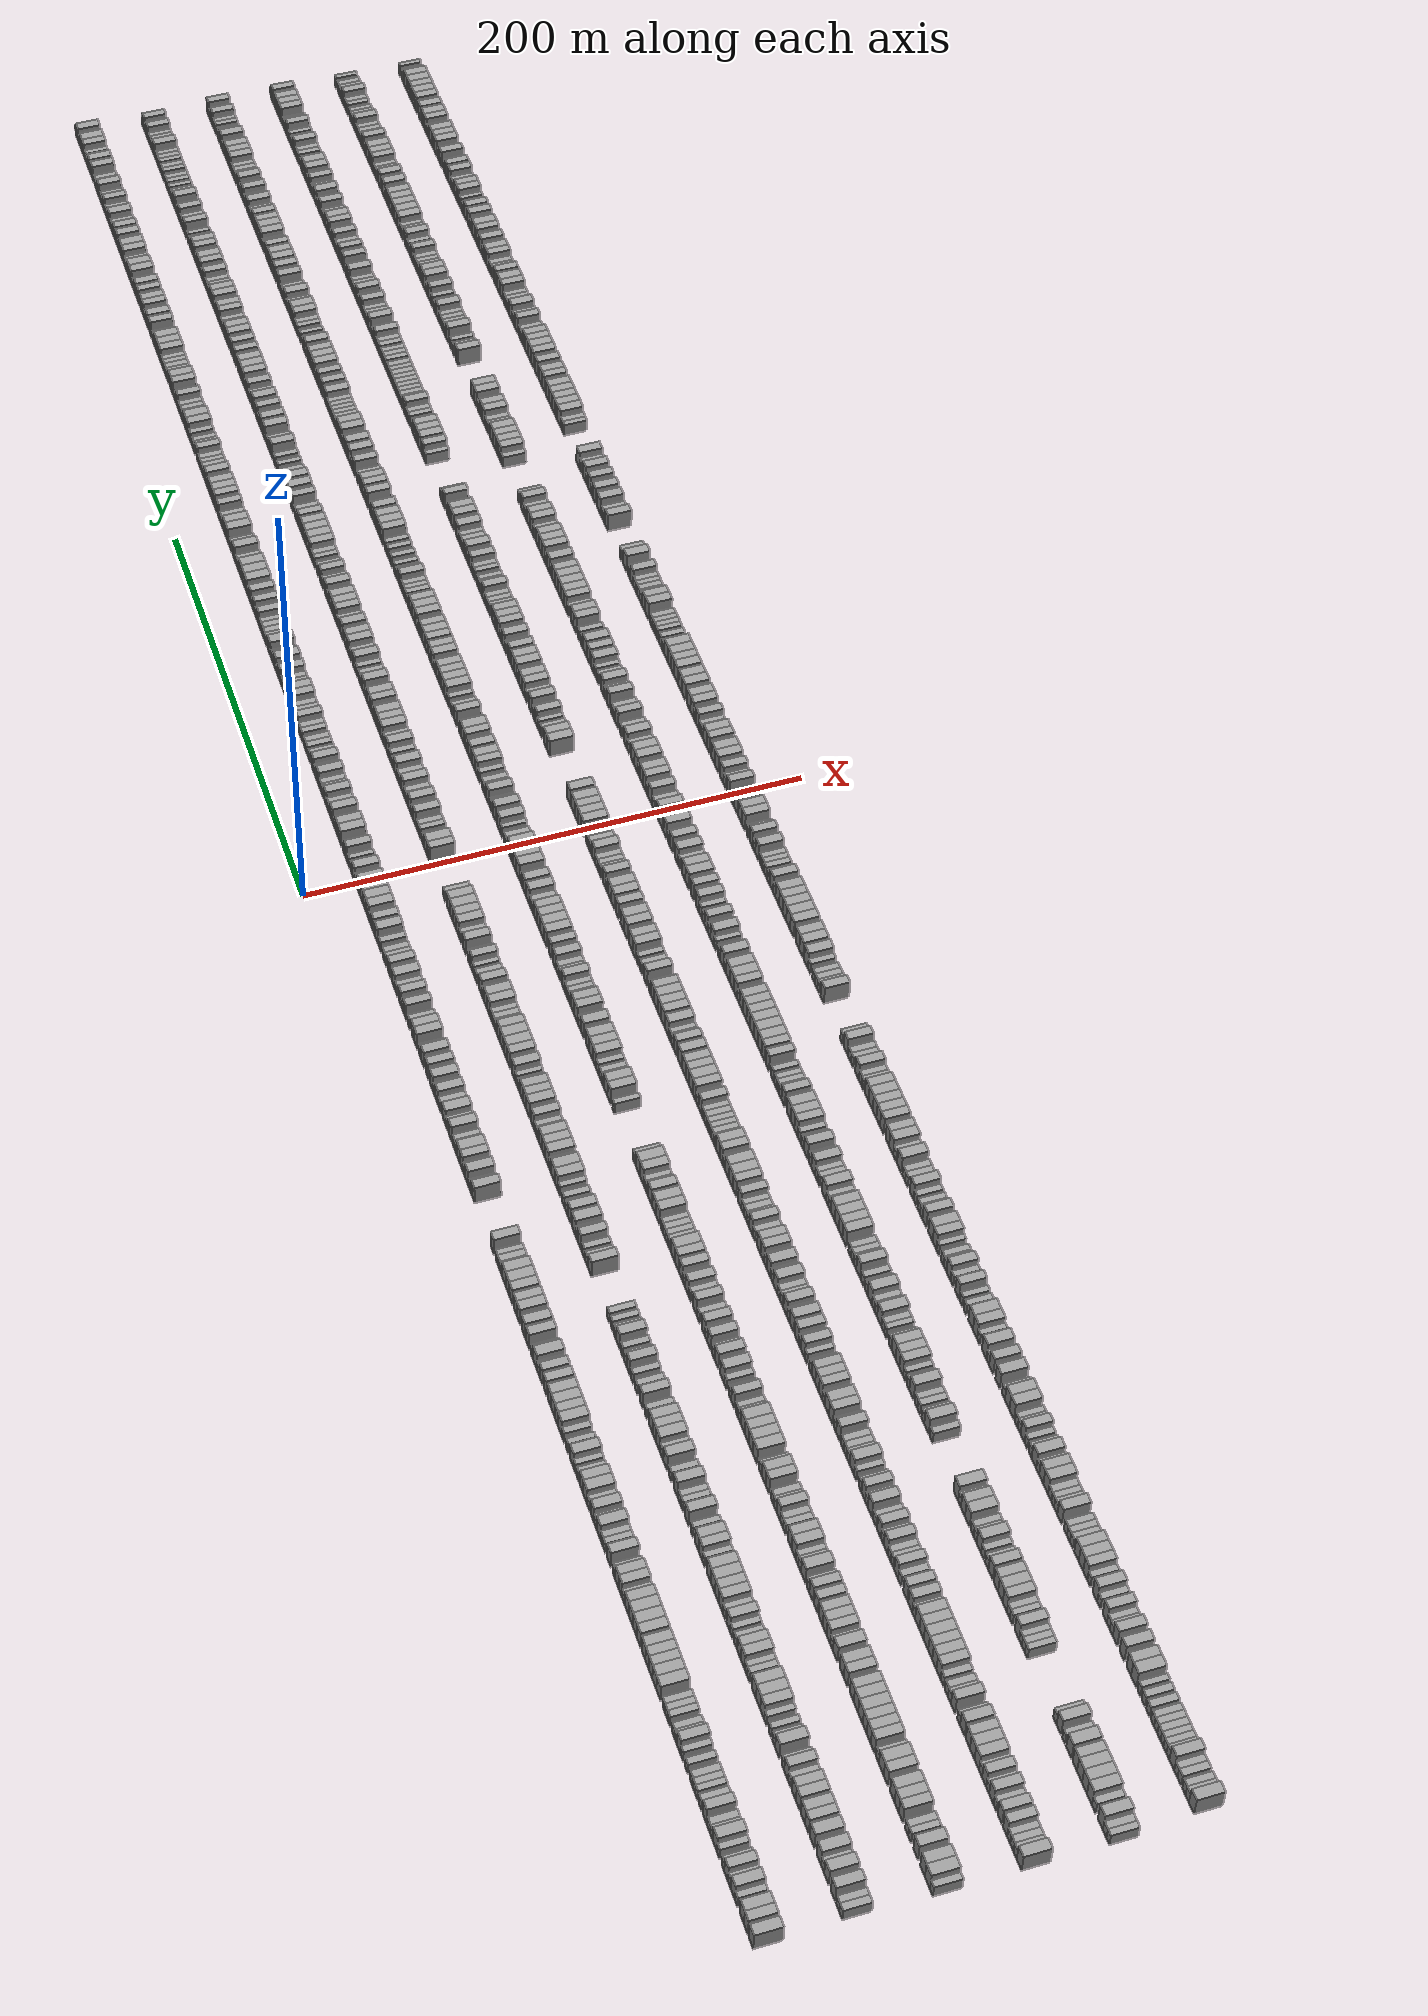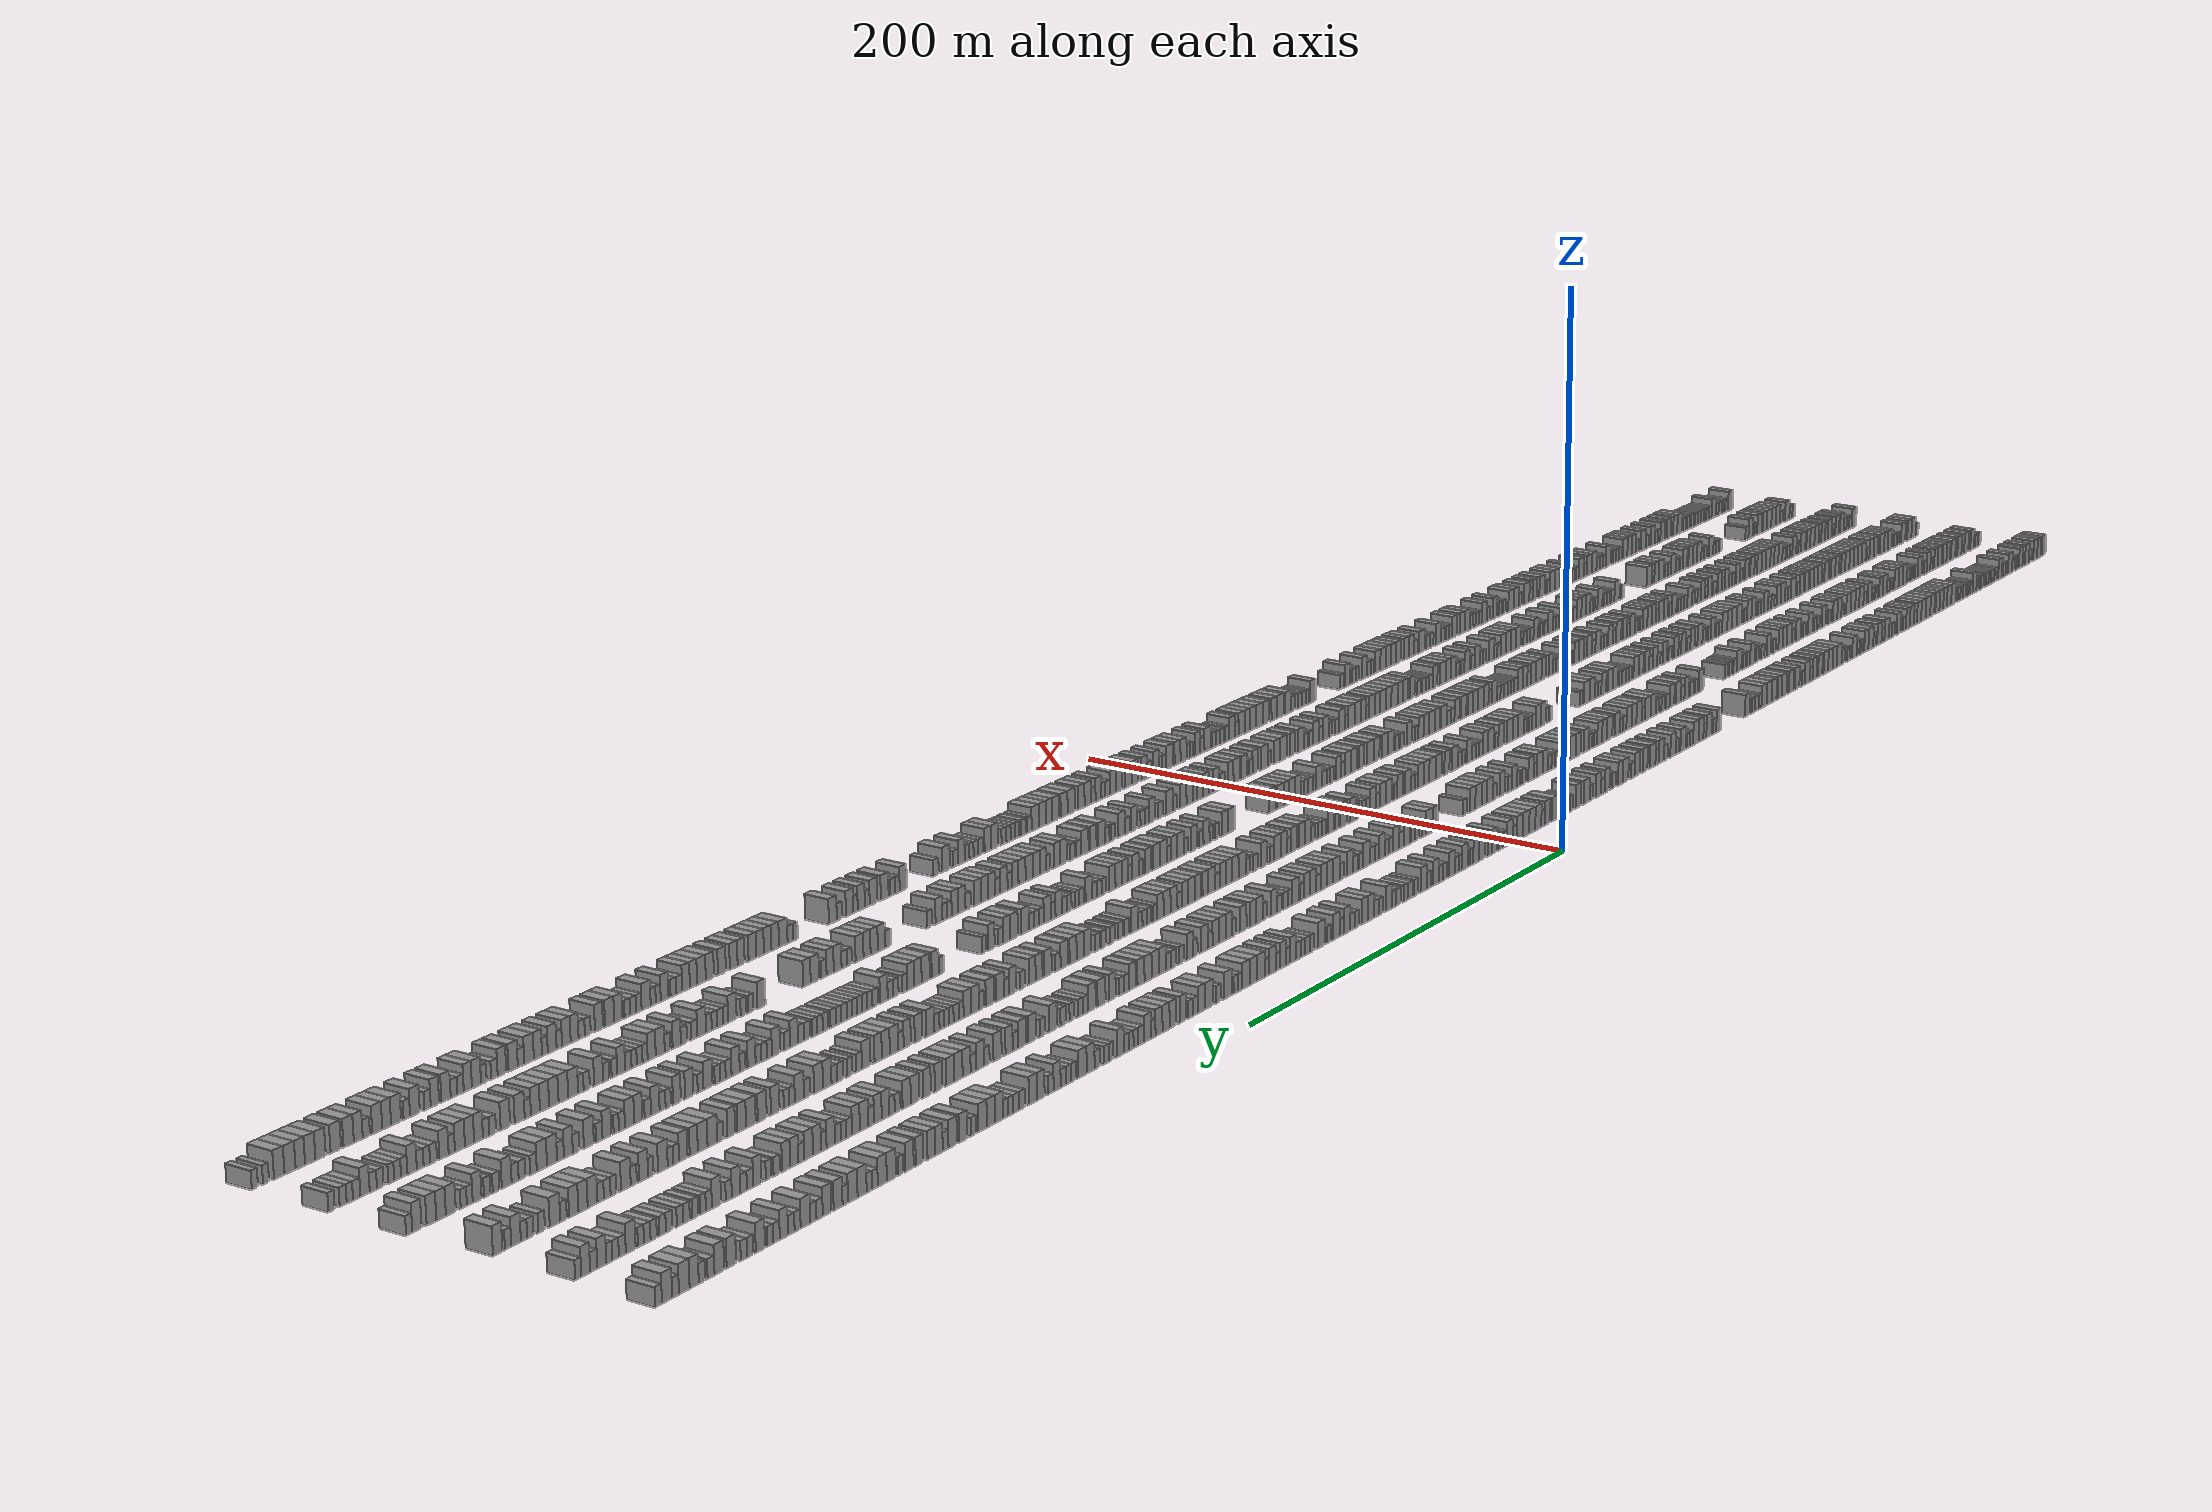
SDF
<sdf version="1.6">
 <world name="default">
  <scene>
   <sky><clouds><speed>12</speed></clouds></sky>
   <ambient>0.4 0.4 0.4 1</ambient>
   <background>0.7 0.7 0.7 1</background>
   <shadows>1</shadows>
  </scene>
  <gravity>0 0 -9.8066</gravity>
  <magnetic_field>6e-06 2.3e-05 -4.2e-05</magnetic_field>
  <physics default="0" name="default_physics" type="ode">
   <ode>
    <solver>
     <type>quick</type>
     <iters>10</iters>
     <sor>1.0</sor>
     <use_dynamic_moi_rescaling>0</use_dynamic_moi_rescaling>
    </solver>
    <constraints>
     <cfm>0</cfm>
     <erp>0.2</erp>
     <contact_max_correcting_vel>100</contact_max_correcting_vel>
     <contact_surface_layer>0.001</contact_surface_layer>
    </constraints>
   </ode>
   <max_step_size>0.004</max_step_size>
   <real_time_factor>1</real_time_factor>
   <real_time_update_rate>250</real_time_update_rate>
  </physics>
  <light name="sun" type="directional">
   <pose>0 0 10 0 0 0</pose>
   <diffuse>0.8 0.8 0.8 1</diffuse>
   <specular>0.2 0.2 0.2 1</specular>
   <attenuation>
    <range>1000</range>
    <constant>0.9</constant>
    <linear>0.01</linear>
    <quadratic>0.001</quadratic>
   </attenuation>
   <direction>-0.5 0.1 -0.9</direction>
  </light>
  <model name="building_1">
   <static>1</static>
   <pose>25.0000 -457.9038 0 0.000000 0.000000 0.000000</pose>
   <link name="link">
    <pose>0 0 4.50 0 0 0</pose>
    <collision name="collision"><geometry><box><size>10.0000 4.1924 9.0000</size></box></geometry></collision>
    <visual name="visual">
     <cast_shadows>0</cast_shadows>
     <geometry><box><size>10.0000 4.1924 9.0000</size></box></geometry>
     <material>
      <script>
       <uri>model://grey_wall/materials/scripts</uri>
       <uri>model://grey_wall/materials/textures</uri>
       <name>vrc/grey_wall</name>
      </script>
     </material>
    </visual>
   </link>
  </model>
  <model name="building_2">
   <static>1</static>
   <pose>25.0000 -452.9609 0 0.000000 0.000000 0.000000</pose>
   <link name="link">
    <pose>0 0 4.50 0 0 0</pose>
    <collision name="collision"><geometry><box><size>10.0000 3.6936 9.0000</size></box></geometry></collision>
    <visual name="visual">
     <cast_shadows>0</cast_shadows>
     <geometry><box><size>10.0000 3.6936 9.0000</size></box></geometry>
     <material>
      <script>
       <uri>model://grey_wall/materials/scripts</uri>
       <uri>model://grey_wall/materials/textures</uri>
       <name>vrc/grey_wall</name>
      </script>
     </material>
    </visual>
   </link>
  </model>
  <model name="building_3">
   <static>1</static>
   <pose>25.0000 -449.0619 0 0.000000 0.000000 0.000000</pose>
   <link name="link">
    <pose>0 0 4.50 0 0 0</pose>
    <collision name="collision"><geometry><box><size>10.0000 4.1043 9.0000</size></box></geometry></collision>
    <visual name="visual">
     <cast_shadows>0</cast_shadows>
     <geometry><box><size>10.0000 4.1043 9.0000</size></box></geometry>
     <material>
      <script>
       <uri>model://grey_wall/materials/scripts</uri>
       <uri>model://grey_wall/materials/textures</uri>
       <name>vrc/grey_wall</name>
      </script>
     </material>
    </visual>
   </link>
  </model>
  <model name="building_4">
   <static>1</static>
   <pose>25.0000 -443.7452 0 0.000000 0.000000 0.000000</pose>
   <link name="link">
    <pose>0 0 3.00 0 0 0</pose>
    <collision name="collision"><geometry><box><size>10.0000 2.5291 6.0000</size></box></geometry></collision>
    <visual name="visual">
     <cast_shadows>0</cast_shadows>
     <geometry><box><size>10.0000 2.5291 6.0000</size></box></geometry>
     <material>
      <script>
       <uri>model://grey_wall/materials/scripts</uri>
       <uri>model://grey_wall/materials/textures</uri>
       <name>vrc/grey_wall</name>
      </script>
     </material>
    </visual>
   </link>
  </model>
  <model name="building_5">
   <static>1</static>
   <pose>25.0000 -440.4347 0 0.000000 0.000000 0.000000</pose>
   <link name="link">
    <pose>0 0 4.50 0 0 0</pose>
    <collision name="collision"><geometry><box><size>10.0000 4.0920 9.0000</size></box></geometry></collision>
    <visual name="visual">
     <cast_shadows>0</cast_shadows>
     <geometry><box><size>10.0000 4.0920 9.0000</size></box></geometry>
     <material>
      <script>
       <uri>model://grey_wall/materials/scripts</uri>
       <uri>model://grey_wall/materials/textures</uri>
       <name>vrc/grey_wall</name>
      </script>
     </material>
    </visual>
   </link>
  </model>
  <model name="building_6">
   <static>1</static>
   <pose>25.0000 -437.0608 0 0.000000 0.000000 0.000000</pose>
   <link name="link">
    <pose>0 0 3.00 0 0 0</pose>
    <collision name="collision"><geometry><box><size>10.0000 2.6559 6.0000</size></box></geometry></collision>
    <visual name="visual">
     <cast_shadows>0</cast_shadows>
     <geometry><box><size>10.0000 2.6559 6.0000</size></box></geometry>
     <material>
      <script>
       <uri>model://grey_wall/materials/scripts</uri>
       <uri>model://grey_wall/materials/textures</uri>
       <name>vrc/grey_wall</name>
      </script>
     </material>
    </visual>
   </link>
  </model>
  <model name="building_7">
   <static>1</static>
   <pose>25.0000 -433.8750 0 0.000000 0.000000 0.000000</pose>
   <link name="link">
    <pose>0 0 4.50 0 0 0</pose>
    <collision name="collision"><geometry><box><size>10.0000 3.7156 9.0000</size></box></geometry></collision>
    <visual name="visual">
     <cast_shadows>0</cast_shadows>
     <geometry><box><size>10.0000 3.7156 9.0000</size></box></geometry>
     <material>
      <script>
       <uri>model://grey_wall/materials/scripts</uri>
       <uri>model://grey_wall/materials/textures</uri>
       <name>vrc/grey_wall</name>
      </script>
     </material>
    </visual>
   </link>
  </model>
  <model name="building_8">
   <static>1</static>
   <pose>25.0000 -430.7578 0 0.000000 0.000000 0.000000</pose>
   <link name="link">
    <pose>0 0 3.00 0 0 0</pose>
    <collision name="collision"><geometry><box><size>10.0000 2.5190 6.0000</size></box></geometry></collision>
    <visual name="visual">
     <cast_shadows>0</cast_shadows>
     <geometry><box><size>10.0000 2.5190 6.0000</size></box></geometry>
     <material>
      <script>
       <uri>model://grey_wall/materials/scripts</uri>
       <uri>model://grey_wall/materials/textures</uri>
       <name>vrc/grey_wall</name>
      </script>
     </material>
    </visual>
   </link>
  </model>
  <model name="building_9">
   <static>1</static>
   <pose>25.0000 -426.2281 0 0.000000 0.000000 0.000000</pose>
   <link name="link">
    <pose>0 0 3.00 0 0 0</pose>
    <collision name="collision"><geometry><box><size>10.0000 2.5404 6.0000</size></box></geometry></collision>
    <visual name="visual">
     <cast_shadows>0</cast_shadows>
     <geometry><box><size>10.0000 2.5404 6.0000</size></box></geometry>
     <material>
      <script>
       <uri>model://grey_wall/materials/scripts</uri>
       <uri>model://grey_wall/materials/textures</uri>
       <name>vrc/grey_wall</name>
      </script>
     </material>
    </visual>
   </link>
  </model>
  <model name="building_10">
   <static>1</static>
   <pose>25.0000 -422.8265 0 0.000000 0.000000 0.000000</pose>
   <link name="link">
    <pose>0 0 4.50 0 0 0</pose>
    <collision name="collision"><geometry><box><size>10.0000 4.2628 9.0000</size></box></geometry></collision>
    <visual name="visual">
     <cast_shadows>0</cast_shadows>
     <geometry><box><size>10.0000 4.2628 9.0000</size></box></geometry>
     <material>
      <script>
       <uri>model://grey_wall/materials/scripts</uri>
       <uri>model://grey_wall/materials/textures</uri>
       <name>vrc/grey_wall</name>
      </script>
     </material>
    </visual>
   </link>
  </model>
  <model name="building_11">
   <static>1</static>
   <pose>25.0000 -419.4430 0 0.000000 0.000000 0.000000</pose>
   <link name="link">
    <pose>0 0 3.00 0 0 0</pose>
    <collision name="collision"><geometry><box><size>10.0000 2.5042 6.0000</size></box></geometry></collision>
    <visual name="visual">
     <cast_shadows>0</cast_shadows>
     <geometry><box><size>10.0000 2.5042 6.0000</size></box></geometry>
     <material>
      <script>
       <uri>model://grey_wall/materials/scripts</uri>
       <uri>model://grey_wall/materials/textures</uri>
       <name>vrc/grey_wall</name>
      </script>
     </material>
    </visual>
   </link>
  </model>
  <model name="building_12">
   <static>1</static>
   <pose>25.0000 -416.7817 0 0.000000 0.000000 0.000000</pose>
   <link name="link">
    <pose>0 0 3.00 0 0 0</pose>
    <collision name="collision"><geometry><box><size>10.0000 2.8184 6.0000</size></box></geometry></collision>
    <visual name="visual">
     <cast_shadows>0</cast_shadows>
     <geometry><box><size>10.0000 2.8184 6.0000</size></box></geometry>
     <material>
      <script>
       <uri>model://grey_wall/materials/scripts</uri>
       <uri>model://grey_wall/materials/textures</uri>
       <name>vrc/grey_wall</name>
      </script>
     </material>
    </visual>
   </link>
  </model>
  <model name="building_13">
   <static>1</static>
   <pose>25.0000 -412.5210 0 0.000000 0.000000 0.000000</pose>
   <link name="link">
    <pose>0 0 4.50 0 0 0</pose>
    <collision name="collision"><geometry><box><size>10.0000 3.7030 9.0000</size></box></geometry></collision>
    <visual name="visual">
     <cast_shadows>0</cast_shadows>
     <geometry><box><size>10.0000 3.7030 9.0000</size></box></geometry>
     <material>
      <script>
       <uri>model://grey_wall/materials/scripts</uri>
       <uri>model://grey_wall/materials/textures</uri>
       <name>vrc/grey_wall</name>
      </script>
     </material>
    </visual>
   </link>
  </model>
  <model name="building_14">
   <static>1</static>
   <pose>25.0000 -408.2106 0 0.000000 0.000000 0.000000</pose>
   <link name="link">
    <pose>0 0 3.00 0 0 0</pose>
    <collision name="collision"><geometry><box><size>10.0000 2.9179 6.0000</size></box></geometry></collision>
    <visual name="visual">
     <cast_shadows>0</cast_shadows>
     <geometry><box><size>10.0000 2.9179 6.0000</size></box></geometry>
     <material>
      <script>
       <uri>model://grey_wall/materials/scripts</uri>
       <uri>model://grey_wall/materials/textures</uri>
       <name>vrc/grey_wall</name>
      </script>
     </material>
    </visual>
   </link>
  </model>
  <model name="building_15">
   <static>1</static>
   <pose>25.0000 -404.5162 0 0.000000 0.000000 0.000000</pose>
   <link name="link">
    <pose>0 0 3.00 0 0 0</pose>
    <collision name="collision"><geometry><box><size>10.0000 2.4708 6.0000</size></box></geometry></collision>
    <visual name="visual">
     <cast_shadows>0</cast_shadows>
     <geometry><box><size>10.0000 2.4708 6.0000</size></box></geometry>
     <material>
      <script>
       <uri>model://grey_wall/materials/scripts</uri>
       <uri>model://grey_wall/materials/textures</uri>
       <name>vrc/grey_wall</name>
      </script>
     </material>
    </visual>
   </link>
  </model>
  <model name="building_16">
   <static>1</static>
   <pose>25.0000 -402.0002 0 0.000000 0.000000 0.000000</pose>
   <link name="link">
    <pose>0 0 3.00 0 0 0</pose>
    <collision name="collision"><geometry><box><size>10.0000 2.5612 6.0000</size></box></geometry></collision>
    <visual name="visual">
     <cast_shadows>0</cast_shadows>
     <geometry><box><size>10.0000 2.5612 6.0000</size></box></geometry>
     <material>
      <script>
       <uri>model://grey_wall/materials/scripts</uri>
       <uri>model://grey_wall/materials/textures</uri>
       <name>vrc/grey_wall</name>
      </script>
     </material>
    </visual>
   </link>
  </model>
  <model name="building_17">
   <static>1</static>
   <pose>25.0000 -399.3061 0 0.000000 0.000000 0.000000</pose>
   <link name="link">
    <pose>0 0 3.00 0 0 0</pose>
    <collision name="collision"><geometry><box><size>10.0000 2.8269 6.0000</size></box></geometry></collision>
    <visual name="visual">
     <cast_shadows>0</cast_shadows>
     <geometry><box><size>10.0000 2.8269 6.0000</size></box></geometry>
     <material>
      <script>
       <uri>model://grey_wall/materials/scripts</uri>
       <uri>model://grey_wall/materials/textures</uri>
       <name>vrc/grey_wall</name>
      </script>
     </material>
    </visual>
   </link>
  </model>
  <model name="building_18">
   <static>1</static>
   <pose>25.0000 -394.5300 0 0.000000 0.000000 0.000000</pose>
   <link name="link">
    <pose>0 0 3.00 0 0 0</pose>
    <collision name="collision"><geometry><box><size>10.0000 2.7254 6.0000</size></box></geometry></collision>
    <visual name="visual">
     <cast_shadows>0</cast_shadows>
     <geometry><box><size>10.0000 2.7254 6.0000</size></box></geometry>
     <material>
      <script>
       <uri>model://grey_wall/materials/scripts</uri>
       <uri>model://grey_wall/materials/textures</uri>
       <name>vrc/grey_wall</name>
      </script>
     </material>
    </visual>
   </link>
  </model>
  <model name="building_19">
   <static>1</static>
   <pose>25.0000 -389.8866 0 0.000000 0.000000 0.000000</pose>
   <link name="link">
    <pose>0 0 3.00 0 0 0</pose>
    <collision name="collision"><geometry><box><size>10.0000 2.5613 6.0000</size></box></geometry></collision>
    <visual name="visual">
     <cast_shadows>0</cast_shadows>
     <geometry><box><size>10.0000 2.5613 6.0000</size></box></geometry>
     <material>
      <script>
       <uri>model://grey_wall/materials/scripts</uri>
       <uri>model://grey_wall/materials/textures</uri>
       <name>vrc/grey_wall</name>
      </script>
     </material>
    </visual>
   </link>
  </model>
  <model name="building_20">
   <static>1</static>
   <pose>25.0000 -386.7534 0 0.000000 0.000000 0.000000</pose>
   <link name="link">
    <pose>0 0 4.50 0 0 0</pose>
    <collision name="collision"><geometry><box><size>10.0000 3.7051 9.0000</size></box></geometry></collision>
    <visual name="visual">
     <cast_shadows>0</cast_shadows>
     <geometry><box><size>10.0000 3.7051 9.0000</size></box></geometry>
     <material>
      <script>
       <uri>model://grey_wall/materials/scripts</uri>
       <uri>model://grey_wall/materials/textures</uri>
       <name>vrc/grey_wall</name>
      </script>
     </material>
    </visual>
   </link>
  </model>
  <model name="building_21">
   <static>1</static>
   <pose>25.0000 -383.6446 0 0.000000 0.000000 0.000000</pose>
   <link name="link">
    <pose>0 0 3.00 0 0 0</pose>
    <collision name="collision"><geometry><box><size>10.0000 2.5125 6.0000</size></box></geometry></collision>
    <visual name="visual">
     <cast_shadows>0</cast_shadows>
     <geometry><box><size>10.0000 2.5125 6.0000</size></box></geometry>
     <material>
      <script>
       <uri>model://grey_wall/materials/scripts</uri>
       <uri>model://grey_wall/materials/textures</uri>
       <name>vrc/grey_wall</name>
      </script>
     </material>
    </visual>
   </link>
  </model>
  <model name="building_22">
   <static>1</static>
   <pose>25.0000 -381.0947 0 0.000000 0.000000 0.000000</pose>
   <link name="link">
    <pose>0 0 3.00 0 0 0</pose>
    <collision name="collision"><geometry><box><size>10.0000 2.5872 6.0000</size></box></geometry></collision>
    <visual name="visual">
     <cast_shadows>0</cast_shadows>
     <geometry><box><size>10.0000 2.5872 6.0000</size></box></geometry>
     <material>
      <script>
       <uri>model://grey_wall/materials/scripts</uri>
       <uri>model://grey_wall/materials/textures</uri>
       <name>vrc/grey_wall</name>
      </script>
     </material>
    </visual>
   </link>
  </model>
  <model name="building_23">
   <static>1</static>
   <pose>25.0000 -376.4529 0 0.000000 0.000000 0.000000</pose>
   <link name="link">
    <pose>0 0 3.00 0 0 0</pose>
    <collision name="collision"><geometry><box><size>10.0000 2.6964 6.0000</size></box></geometry></collision>
    <visual name="visual">
     <cast_shadows>0</cast_shadows>
     <geometry><box><size>10.0000 2.6964 6.0000</size></box></geometry>
     <material>
      <script>
       <uri>model://grey_wall/materials/scripts</uri>
       <uri>model://grey_wall/materials/textures</uri>
       <name>vrc/grey_wall</name>
      </script>
     </material>
    </visual>
   </link>
  </model>
  <model name="building_24">
   <static>1</static>
   <pose>25.0000 -373.8262 0 0.000000 0.000000 0.000000</pose>
   <link name="link">
    <pose>0 0 3.00 0 0 0</pose>
    <collision name="collision"><geometry><box><size>10.0000 2.5570 6.0000</size></box></geometry></collision>
    <visual name="visual">
     <cast_shadows>0</cast_shadows>
     <geometry><box><size>10.0000 2.5570 6.0000</size></box></geometry>
     <material>
      <script>
       <uri>model://grey_wall/materials/scripts</uri>
       <uri>model://grey_wall/materials/textures</uri>
       <name>vrc/grey_wall</name>
      </script>
     </material>
    </visual>
   </link>
  </model>
  <model name="building_25">
   <static>1</static>
   <pose>25.0000 -371.2530 0 0.000000 0.000000 0.000000</pose>
   <link name="link">
    <pose>0 0 3.00 0 0 0</pose>
    <collision name="collision"><geometry><box><size>10.0000 2.5894 6.0000</size></box></geometry></collision>
    <visual name="visual">
     <cast_shadows>0</cast_shadows>
     <geometry><box><size>10.0000 2.5894 6.0000</size></box></geometry>
     <material>
      <script>
       <uri>model://grey_wall/materials/scripts</uri>
       <uri>model://grey_wall/materials/textures</uri>
       <name>vrc/grey_wall</name>
      </script>
     </material>
    </visual>
   </link>
  </model>
  <model name="building_26">
   <static>1</static>
   <pose>25.0000 -365.7674 0 0.000000 0.000000 0.000000</pose>
   <link name="link">
    <pose>0 0 4.50 0 0 0</pose>
    <collision name="collision"><geometry><box><size>10.0000 4.3818 9.0000</size></box></geometry></collision>
    <visual name="visual">
     <cast_shadows>0</cast_shadows>
     <geometry><box><size>10.0000 4.3818 9.0000</size></box></geometry>
     <material>
      <script>
       <uri>model://grey_wall/materials/scripts</uri>
       <uri>model://grey_wall/materials/textures</uri>
       <name>vrc/grey_wall</name>
      </script>
     </material>
    </visual>
   </link>
  </model>
  <model name="building_27">
   <static>1</static>
   <pose>25.0000 -361.5062 0 0.000000 0.000000 0.000000</pose>
   <link name="link">
    <pose>0 0 4.50 0 0 0</pose>
    <collision name="collision"><geometry><box><size>10.0000 4.1407 9.0000</size></box></geometry></collision>
    <visual name="visual">
     <cast_shadows>0</cast_shadows>
     <geometry><box><size>10.0000 4.1407 9.0000</size></box></geometry>
     <material>
      <script>
       <uri>model://grey_wall/materials/scripts</uri>
       <uri>model://grey_wall/materials/textures</uri>
       <name>vrc/grey_wall</name>
      </script>
     </material>
    </visual>
   </link>
  </model>
  <model name="building_28">
   <static>1</static>
   <pose>25.0000 -357.6312 0 0.000000 0.000000 0.000000</pose>
   <link name="link">
    <pose>0 0 4.50 0 0 0</pose>
    <collision name="collision"><geometry><box><size>10.0000 3.6091 9.0000</size></box></geometry></collision>
    <visual name="visual">
     <cast_shadows>0</cast_shadows>
     <geometry><box><size>10.0000 3.6091 9.0000</size></box></geometry>
     <material>
      <script>
       <uri>model://grey_wall/materials/scripts</uri>
       <uri>model://grey_wall/materials/textures</uri>
       <name>vrc/grey_wall</name>
      </script>
     </material>
    </visual>
   </link>
  </model>
  <model name="building_29">
   <static>1</static>
   <pose>25.0000 -353.9630 0 0.000000 0.000000 0.000000</pose>
   <link name="link">
    <pose>0 0 4.50 0 0 0</pose>
    <collision name="collision"><geometry><box><size>10.0000 3.7274 9.0000</size></box></geometry></collision>
    <visual name="visual">
     <cast_shadows>0</cast_shadows>
     <geometry><box><size>10.0000 3.7274 9.0000</size></box></geometry>
     <material>
      <script>
       <uri>model://grey_wall/materials/scripts</uri>
       <uri>model://grey_wall/materials/textures</uri>
       <name>vrc/grey_wall</name>
      </script>
     </material>
    </visual>
   </link>
  </model>
  <model name="building_30">
   <static>1</static>
   <pose>25.0000 -350.1197 0 0.000000 0.000000 0.000000</pose>
   <link name="link">
    <pose>0 0 4.50 0 0 0</pose>
    <collision name="collision"><geometry><box><size>10.0000 3.9592 9.0000</size></box></geometry></collision>
    <visual name="visual">
     <cast_shadows>0</cast_shadows>
     <geometry><box><size>10.0000 3.9592 9.0000</size></box></geometry>
     <material>
      <script>
       <uri>model://grey_wall/materials/scripts</uri>
       <uri>model://grey_wall/materials/textures</uri>
       <name>vrc/grey_wall</name>
      </script>
     </material>
    </visual>
   </link>
  </model>
  <model name="building_31">
   <static>1</static>
   <pose>25.0000 -345.1543 0 0.000000 0.000000 0.000000</pose>
   <link name="link">
    <pose>0 0 4.50 0 0 0</pose>
    <collision name="collision"><geometry><box><size>10.0000 3.9717 9.0000</size></box></geometry></collision>
    <visual name="visual">
     <cast_shadows>0</cast_shadows>
     <geometry><box><size>10.0000 3.9717 9.0000</size></box></geometry>
     <material>
      <script>
       <uri>model://grey_wall/materials/scripts</uri>
       <uri>model://grey_wall/materials/textures</uri>
       <name>vrc/grey_wall</name>
      </script>
     </material>
    </visual>
   </link>
  </model>
  <model name="building_32">
   <static>1</static>
   <pose>25.0000 -341.0035 0 0.000000 0.000000 0.000000</pose>
   <link name="link">
    <pose>0 0 4.50 0 0 0</pose>
    <collision name="collision"><geometry><box><size>10.0000 4.3299 9.0000</size></box></geometry></collision>
    <visual name="visual">
     <cast_shadows>0</cast_shadows>
     <geometry><box><size>10.0000 4.3299 9.0000</size></box></geometry>
     <material>
      <script>
       <uri>model://grey_wall/materials/scripts</uri>
       <uri>model://grey_wall/materials/textures</uri>
       <name>vrc/grey_wall</name>
      </script>
     </material>
    </visual>
   </link>
  </model>
  <model name="building_33">
   <static>1</static>
   <pose>25.0000 -336.6456 0 0.000000 0.000000 0.000000</pose>
   <link name="link">
    <pose>0 0 4.50 0 0 0</pose>
    <collision name="collision"><geometry><box><size>10.0000 4.3859 9.0000</size></box></geometry></collision>
    <visual name="visual">
     <cast_shadows>0</cast_shadows>
     <geometry><box><size>10.0000 4.3859 9.0000</size></box></geometry>
     <material>
      <script>
       <uri>model://grey_wall/materials/scripts</uri>
       <uri>model://grey_wall/materials/textures</uri>
       <name>vrc/grey_wall</name>
      </script>
     </material>
    </visual>
   </link>
  </model>
  <model name="building_34">
   <static>1</static>
   <pose>25.0000 -332.4584 0 0.000000 0.000000 0.000000</pose>
   <link name="link">
    <pose>0 0 4.50 0 0 0</pose>
    <collision name="collision"><geometry><box><size>10.0000 3.9885 9.0000</size></box></geometry></collision>
    <visual name="visual">
     <cast_shadows>0</cast_shadows>
     <geometry><box><size>10.0000 3.9885 9.0000</size></box></geometry>
     <material>
      <script>
       <uri>model://grey_wall/materials/scripts</uri>
       <uri>model://grey_wall/materials/textures</uri>
       <name>vrc/grey_wall</name>
      </script>
     </material>
    </visual>
   </link>
  </model>
  <model name="building_35">
   <static>1</static>
   <pose>25.0000 -328.9862 0 0.000000 0.000000 0.000000</pose>
   <link name="link">
    <pose>0 0 3.00 0 0 0</pose>
    <collision name="collision"><geometry><box><size>10.0000 2.9560 6.0000</size></box></geometry></collision>
    <visual name="visual">
     <cast_shadows>0</cast_shadows>
     <geometry><box><size>10.0000 2.9560 6.0000</size></box></geometry>
     <material>
      <script>
       <uri>model://grey_wall/materials/scripts</uri>
       <uri>model://grey_wall/materials/textures</uri>
       <name>vrc/grey_wall</name>
      </script>
     </material>
    </visual>
   </link>
  </model>
  <model name="building_36">
   <static>1</static>
   <pose>25.0000 -325.6257 0 0.000000 0.000000 0.000000</pose>
   <link name="link">
    <pose>0 0 4.50 0 0 0</pose>
    <collision name="collision"><geometry><box><size>10.0000 3.7648 9.0000</size></box></geometry></collision>
    <visual name="visual">
     <cast_shadows>0</cast_shadows>
     <geometry><box><size>10.0000 3.7648 9.0000</size></box></geometry>
     <material>
      <script>
       <uri>model://grey_wall/materials/scripts</uri>
       <uri>model://grey_wall/materials/textures</uri>
       <name>vrc/grey_wall</name>
      </script>
     </material>
    </visual>
   </link>
  </model>
  <model name="building_37">
   <static>1</static>
   <pose>25.0000 -321.9064 0 0.000000 0.000000 0.000000</pose>
   <link name="link">
    <pose>0 0 4.50 0 0 0</pose>
    <collision name="collision"><geometry><box><size>10.0000 3.6739 9.0000</size></box></geometry></collision>
    <visual name="visual">
     <cast_shadows>0</cast_shadows>
     <geometry><box><size>10.0000 3.6739 9.0000</size></box></geometry>
     <material>
      <script>
       <uri>model://grey_wall/materials/scripts</uri>
       <uri>model://grey_wall/materials/textures</uri>
       <name>vrc/grey_wall</name>
      </script>
     </material>
    </visual>
   </link>
  </model>
  <model name="building_38">
   <static>1</static>
   <pose>25.0000 -318.6146 0 0.000000 0.000000 0.000000</pose>
   <link name="link">
    <pose>0 0 3.00 0 0 0</pose>
    <collision name="collision"><geometry><box><size>10.0000 2.9097 6.0000</size></box></geometry></collision>
    <visual name="visual">
     <cast_shadows>0</cast_shadows>
     <geometry><box><size>10.0000 2.9097 6.0000</size></box></geometry>
     <material>
      <script>
       <uri>model://grey_wall/materials/scripts</uri>
       <uri>model://grey_wall/materials/textures</uri>
       <name>vrc/grey_wall</name>
      </script>
     </material>
    </visual>
   </link>
  </model>
  <model name="building_39">
   <static>1</static>
   <pose>25.0000 -313.2614 0 0.000000 0.000000 0.000000</pose>
   <link name="link">
    <pose>0 0 4.50 0 0 0</pose>
    <collision name="collision"><geometry><box><size>10.0000 3.7967 9.0000</size></box></geometry></collision>
    <visual name="visual">
     <cast_shadows>0</cast_shadows>
     <geometry><box><size>10.0000 3.7967 9.0000</size></box></geometry>
     <material>
      <script>
       <uri>model://grey_wall/materials/scripts</uri>
       <uri>model://grey_wall/materials/textures</uri>
       <name>vrc/grey_wall</name>
      </script>
     </material>
    </visual>
   </link>
  </model>
  <model name="building_40">
   <static>1</static>
   <pose>25.0000 -308.0791 0 0.000000 0.000000 0.000000</pose>
   <link name="link">
    <pose>0 0 3.00 0 0 0</pose>
    <collision name="collision"><geometry><box><size>10.0000 2.5677 6.0000</size></box></geometry></collision>
    <visual name="visual">
     <cast_shadows>0</cast_shadows>
     <geometry><box><size>10.0000 2.5677 6.0000</size></box></geometry>
     <material>
      <script>
       <uri>model://grey_wall/materials/scripts</uri>
       <uri>model://grey_wall/materials/textures</uri>
       <name>vrc/grey_wall</name>
      </script>
     </material>
    </visual>
   </link>
  </model>
  <model name="building_41">
   <static>1</static>
   <pose>25.0000 -305.4399 0 0.000000 0.000000 0.000000</pose>
   <link name="link">
    <pose>0 0 3.00 0 0 0</pose>
    <collision name="collision"><geometry><box><size>10.0000 2.7108 6.0000</size></box></geometry></collision>
    <visual name="visual">
     <cast_shadows>0</cast_shadows>
     <geometry><box><size>10.0000 2.7108 6.0000</size></box></geometry>
     <material>
      <script>
       <uri>model://grey_wall/materials/scripts</uri>
       <uri>model://grey_wall/materials/textures</uri>
       <name>vrc/grey_wall</name>
      </script>
     </material>
    </visual>
   </link>
  </model>
  <model name="building_42">
   <static>1</static>
   <pose>25.0000 -301.9377 0 0.000000 0.000000 0.000000</pose>
   <link name="link">
    <pose>0 0 4.50 0 0 0</pose>
    <collision name="collision"><geometry><box><size>10.0000 4.2936 9.0000</size></box></geometry></collision>
    <visual name="visual">
     <cast_shadows>0</cast_shadows>
     <geometry><box><size>10.0000 4.2936 9.0000</size></box></geometry>
     <material>
      <script>
       <uri>model://grey_wall/materials/scripts</uri>
       <uri>model://grey_wall/materials/textures</uri>
       <name>vrc/grey_wall</name>
      </script>
     </material>
    </visual>
   </link>
  </model>
  <model name="building_43">
   <static>1</static>
   <pose>25.0000 -298.4554 0 0.000000 0.000000 0.000000</pose>
   <link name="link">
    <pose>0 0 3.00 0 0 0</pose>
    <collision name="collision"><geometry><box><size>10.0000 2.6709 6.0000</size></box></geometry></collision>
    <visual name="visual">
     <cast_shadows>0</cast_shadows>
     <geometry><box><size>10.0000 2.6709 6.0000</size></box></geometry>
     <material>
      <script>
       <uri>model://grey_wall/materials/scripts</uri>
       <uri>model://grey_wall/materials/textures</uri>
       <name>vrc/grey_wall</name>
      </script>
     </material>
    </visual>
   </link>
  </model>
  <model name="building_44">
   <static>1</static>
   <pose>25.0000 -295.1273 0 0.000000 0.000000 0.000000</pose>
   <link name="link">
    <pose>0 0 4.50 0 0 0</pose>
    <collision name="collision"><geometry><box><size>10.0000 3.9854 9.0000</size></box></geometry></collision>
    <visual name="visual">
     <cast_shadows>0</cast_shadows>
     <geometry><box><size>10.0000 3.9854 9.0000</size></box></geometry>
     <material>
      <script>
       <uri>model://grey_wall/materials/scripts</uri>
       <uri>model://grey_wall/materials/textures</uri>
       <name>vrc/grey_wall</name>
      </script>
     </material>
    </visual>
   </link>
  </model>
  <model name="building_45">
   <static>1</static>
   <pose>25.0000 -290.7953 0 0.000000 0.000000 0.000000</pose>
   <link name="link">
    <pose>0 0 3.00 0 0 0</pose>
    <collision name="collision"><geometry><box><size>10.0000 2.6784 6.0000</size></box></geometry></collision>
    <visual name="visual">
     <cast_shadows>0</cast_shadows>
     <geometry><box><size>10.0000 2.6784 6.0000</size></box></geometry>
     <material>
      <script>
       <uri>model://grey_wall/materials/scripts</uri>
       <uri>model://grey_wall/materials/textures</uri>
       <name>vrc/grey_wall</name>
      </script>
     </material>
    </visual>
   </link>
  </model>
  <model name="building_46">
   <static>1</static>
   <pose>25.0000 -287.2370 0 0.000000 0.000000 0.000000</pose>
   <link name="link">
    <pose>0 0 4.50 0 0 0</pose>
    <collision name="collision"><geometry><box><size>10.0000 4.4383 9.0000</size></box></geometry></collision>
    <visual name="visual">
     <cast_shadows>0</cast_shadows>
     <geometry><box><size>10.0000 4.4383 9.0000</size></box></geometry>
     <material>
      <script>
       <uri>model://grey_wall/materials/scripts</uri>
       <uri>model://grey_wall/materials/textures</uri>
       <name>vrc/grey_wall</name>
      </script>
     </material>
    </visual>
   </link>
  </model>
  <model name="building_47">
   <static>1</static>
   <pose>25.0000 -283.1209 0 0.000000 0.000000 0.000000</pose>
   <link name="link">
    <pose>0 0 4.50 0 0 0</pose>
    <collision name="collision"><geometry><box><size>10.0000 3.7939 9.0000</size></box></geometry></collision>
    <visual name="visual">
     <cast_shadows>0</cast_shadows>
     <geometry><box><size>10.0000 3.7939 9.0000</size></box></geometry>
     <material>
      <script>
       <uri>model://grey_wall/materials/scripts</uri>
       <uri>model://grey_wall/materials/textures</uri>
       <name>vrc/grey_wall</name>
      </script>
     </material>
    </visual>
   </link>
  </model>
  <model name="building_48">
   <static>1</static>
   <pose>25.0000 -278.9808 0 0.000000 0.000000 0.000000</pose>
   <link name="link">
    <pose>0 0 3.00 0 0 0</pose>
    <collision name="collision"><geometry><box><size>10.0000 2.4862 6.0000</size></box></geometry></collision>
    <visual name="visual">
     <cast_shadows>0</cast_shadows>
     <geometry><box><size>10.0000 2.4862 6.0000</size></box></geometry>
     <material>
      <script>
       <uri>model://grey_wall/materials/scripts</uri>
       <uri>model://grey_wall/materials/textures</uri>
       <name>vrc/grey_wall</name>
      </script>
     </material>
    </visual>
   </link>
  </model>
  <model name="building_49">
   <static>1</static>
   <pose>25.0000 -275.5052 0 0.000000 0.000000 0.000000</pose>
   <link name="link">
    <pose>0 0 3.00 0 0 0</pose>
    <collision name="collision"><geometry><box><size>10.0000 2.4652 6.0000</size></box></geometry></collision>
    <visual name="visual">
     <cast_shadows>0</cast_shadows>
     <geometry><box><size>10.0000 2.4652 6.0000</size></box></geometry>
     <material>
      <script>
       <uri>model://grey_wall/materials/scripts</uri>
       <uri>model://grey_wall/materials/textures</uri>
       <name>vrc/grey_wall</name>
      </script>
     </material>
    </visual>
   </link>
  </model>
  <model name="building_50">
   <static>1</static>
   <pose>25.0000 -272.1948 0 0.000000 0.000000 0.000000</pose>
   <link name="link">
    <pose>0 0 4.50 0 0 0</pose>
    <collision name="collision"><geometry><box><size>10.0000 4.1556 9.0000</size></box></geometry></collision>
    <visual name="visual">
     <cast_shadows>0</cast_shadows>
     <geometry><box><size>10.0000 4.1556 9.0000</size></box></geometry>
     <material>
      <script>
       <uri>model://grey_wall/materials/scripts</uri>
       <uri>model://grey_wall/materials/textures</uri>
       <name>vrc/grey_wall</name>
      </script>
     </material>
    </visual>
   </link>
  </model>
  <model name="building_51">
   <static>1</static>
   <pose>25.0000 -266.9102 0 0.000000 0.000000 0.000000</pose>
   <link name="link">
    <pose>0 0 3.00 0 0 0</pose>
    <collision name="collision"><geometry><box><size>10.0000 2.4135 6.0000</size></box></geometry></collision>
    <visual name="visual">
     <cast_shadows>0</cast_shadows>
     <geometry><box><size>10.0000 2.4135 6.0000</size></box></geometry>
     <material>
      <script>
       <uri>model://grey_wall/materials/scripts</uri>
       <uri>model://grey_wall/materials/textures</uri>
       <name>vrc/grey_wall</name>
      </script>
     </material>
    </visual>
   </link>
  </model>
  <model name="building_52">
   <static>1</static>
   <pose>25.0000 -262.2832 0 0.000000 0.000000 0.000000</pose>
   <link name="link">
    <pose>0 0 3.00 0 0 0</pose>
    <collision name="collision"><geometry><box><size>10.0000 2.8406 6.0000</size></box></geometry></collision>
    <visual name="visual">
     <cast_shadows>0</cast_shadows>
     <geometry><box><size>10.0000 2.8406 6.0000</size></box></geometry>
     <material>
      <script>
       <uri>model://grey_wall/materials/scripts</uri>
       <uri>model://grey_wall/materials/textures</uri>
       <name>vrc/grey_wall</name>
      </script>
     </material>
    </visual>
   </link>
  </model>
  <model name="building_53">
   <static>1</static>
   <pose>25.0000 -258.6811 0 0.000000 0.000000 0.000000</pose>
   <link name="link">
    <pose>0 0 4.50 0 0 0</pose>
    <collision name="collision"><geometry><box><size>10.0000 4.3637 9.0000</size></box></geometry></collision>
    <visual name="visual">
     <cast_shadows>0</cast_shadows>
     <geometry><box><size>10.0000 4.3637 9.0000</size></box></geometry>
     <material>
      <script>
       <uri>model://grey_wall/materials/scripts</uri>
       <uri>model://grey_wall/materials/textures</uri>
       <name>vrc/grey_wall</name>
      </script>
     </material>
    </visual>
   </link>
  </model>
  <model name="building_54">
   <static>1</static>
   <pose>25.0000 -254.6666 0 0.000000 0.000000 0.000000</pose>
   <link name="link">
    <pose>0 0 4.50 0 0 0</pose>
    <collision name="collision"><geometry><box><size>10.0000 3.6653 9.0000</size></box></geometry></collision>
    <visual name="visual">
     <cast_shadows>0</cast_shadows>
     <geometry><box><size>10.0000 3.6653 9.0000</size></box></geometry>
     <material>
      <script>
       <uri>model://grey_wall/materials/scripts</uri>
       <uri>model://grey_wall/materials/textures</uri>
       <name>vrc/grey_wall</name>
      </script>
     </material>
    </visual>
   </link>
  </model>
  <model name="building_55">
   <static>1</static>
   <pose>25.0000 -250.7489 0 0.000000 0.000000 0.000000</pose>
   <link name="link">
    <pose>0 0 4.50 0 0 0</pose>
    <collision name="collision"><geometry><box><size>10.0000 4.1701 9.0000</size></box></geometry></collision>
    <visual name="visual">
     <cast_shadows>0</cast_shadows>
     <geometry><box><size>10.0000 4.1701 9.0000</size></box></geometry>
     <material>
      <script>
       <uri>model://grey_wall/materials/scripts</uri>
       <uri>model://grey_wall/materials/textures</uri>
       <name>vrc/grey_wall</name>
      </script>
     </material>
    </visual>
   </link>
  </model>
  <model name="building_56">
   <static>1</static>
   <pose>25.0000 -246.5825 0 0.000000 0.000000 0.000000</pose>
   <link name="link">
    <pose>0 0 4.50 0 0 0</pose>
    <collision name="collision"><geometry><box><size>10.0000 4.1628 9.0000</size></box></geometry></collision>
    <visual name="visual">
     <cast_shadows>0</cast_shadows>
     <geometry><box><size>10.0000 4.1628 9.0000</size></box></geometry>
     <material>
      <script>
       <uri>model://grey_wall/materials/scripts</uri>
       <uri>model://grey_wall/materials/textures</uri>
       <name>vrc/grey_wall</name>
      </script>
     </material>
    </visual>
   </link>
  </model>
  <model name="building_57">
   <static>1</static>
   <pose>25.0000 -241.6280 0 0.000000 0.000000 0.000000</pose>
   <link name="link">
    <pose>0 0 4.50 0 0 0</pose>
    <collision name="collision"><geometry><box><size>10.0000 3.7461 9.0000</size></box></geometry></collision>
    <visual name="visual">
     <cast_shadows>0</cast_shadows>
     <geometry><box><size>10.0000 3.7461 9.0000</size></box></geometry>
     <material>
      <script>
       <uri>model://grey_wall/materials/scripts</uri>
       <uri>model://grey_wall/materials/textures</uri>
       <name>vrc/grey_wall</name>
      </script>
     </material>
    </visual>
   </link>
  </model>
  <model name="building_58">
   <static>1</static>
   <pose>25.0000 -236.9498 0 0.000000 0.000000 0.000000</pose>
   <link name="link">
    <pose>0 0 4.50 0 0 0</pose>
    <collision name="collision"><geometry><box><size>10.0000 3.6103 9.0000</size></box></geometry></collision>
    <visual name="visual">
     <cast_shadows>0</cast_shadows>
     <geometry><box><size>10.0000 3.6103 9.0000</size></box></geometry>
     <material>
      <script>
       <uri>model://grey_wall/materials/scripts</uri>
       <uri>model://grey_wall/materials/textures</uri>
       <name>vrc/grey_wall</name>
      </script>
     </material>
    </visual>
   </link>
  </model>
  <model name="building_59">
   <static>1</static>
   <pose>25.0000 -233.8061 0 0.000000 0.000000 0.000000</pose>
   <link name="link">
    <pose>0 0 3.00 0 0 0</pose>
    <collision name="collision"><geometry><box><size>10.0000 2.6770 6.0000</size></box></geometry></collision>
    <visual name="visual">
     <cast_shadows>0</cast_shadows>
     <geometry><box><size>10.0000 2.6770 6.0000</size></box></geometry>
     <material>
      <script>
       <uri>model://grey_wall/materials/scripts</uri>
       <uri>model://grey_wall/materials/textures</uri>
       <name>vrc/grey_wall</name>
      </script>
     </material>
    </visual>
   </link>
  </model>
  <model name="building_60">
   <static>1</static>
   <pose>25.0000 -230.2214 0 0.000000 0.000000 0.000000</pose>
   <link name="link">
    <pose>0 0 4.50 0 0 0</pose>
    <collision name="collision"><geometry><box><size>10.0000 4.4923 9.0000</size></box></geometry></collision>
    <visual name="visual">
     <cast_shadows>0</cast_shadows>
     <geometry><box><size>10.0000 4.4923 9.0000</size></box></geometry>
     <material>
      <script>
       <uri>model://grey_wall/materials/scripts</uri>
       <uri>model://grey_wall/materials/textures</uri>
       <name>vrc/grey_wall</name>
      </script>
     </material>
    </visual>
   </link>
  </model>
  <model name="building_61">
   <static>1</static>
   <pose>25.0000 -226.6839 0 0.000000 0.000000 0.000000</pose>
   <link name="link">
    <pose>0 0 3.00 0 0 0</pose>
    <collision name="collision"><geometry><box><size>10.0000 2.5828 6.0000</size></box></geometry></collision>
    <visual name="visual">
     <cast_shadows>0</cast_shadows>
     <geometry><box><size>10.0000 2.5828 6.0000</size></box></geometry>
     <material>
      <script>
       <uri>model://grey_wall/materials/scripts</uri>
       <uri>model://grey_wall/materials/textures</uri>
       <name>vrc/grey_wall</name>
      </script>
     </material>
    </visual>
   </link>
  </model>
  <model name="building_62">
   <static>1</static>
   <pose>25.0000 -221.4566 0 0.000000 0.000000 0.000000</pose>
   <link name="link">
    <pose>0 0 4.50 0 0 0</pose>
    <collision name="collision"><geometry><box><size>10.0000 3.8716 9.0000</size></box></geometry></collision>
    <visual name="visual">
     <cast_shadows>0</cast_shadows>
     <geometry><box><size>10.0000 3.8716 9.0000</size></box></geometry>
     <material>
      <script>
       <uri>model://grey_wall/materials/scripts</uri>
       <uri>model://grey_wall/materials/textures</uri>
       <name>vrc/grey_wall</name>
      </script>
     </material>
    </visual>
   </link>
  </model>
  <model name="building_63">
   <static>1</static>
   <pose>25.0000 -216.4686 0 0.000000 0.000000 0.000000</pose>
   <link name="link">
    <pose>0 0 4.50 0 0 0</pose>
    <collision name="collision"><geometry><box><size>10.0000 4.1044 9.0000</size></box></geometry></collision>
    <visual name="visual">
     <cast_shadows>0</cast_shadows>
     <geometry><box><size>10.0000 4.1044 9.0000</size></box></geometry>
     <material>
      <script>
       <uri>model://grey_wall/materials/scripts</uri>
       <uri>model://grey_wall/materials/textures</uri>
       <name>vrc/grey_wall</name>
      </script>
     </material>
    </visual>
   </link>
  </model>
  <model name="building_64">
   <static>1</static>
   <pose>25.0000 -210.3532 0 0.000000 0.000000 0.000000</pose>
   <link name="link">
    <pose>0 0 4.50 0 0 0</pose>
    <collision name="collision"><geometry><box><size>10.0000 4.1262 9.0000</size></box></geometry></collision>
    <visual name="visual">
     <cast_shadows>0</cast_shadows>
     <geometry><box><size>10.0000 4.1262 9.0000</size></box></geometry>
     <material>
      <script>
       <uri>model://grey_wall/materials/scripts</uri>
       <uri>model://grey_wall/materials/textures</uri>
       <name>vrc/grey_wall</name>
      </script>
     </material>
    </visual>
   </link>
  </model>
  <model name="building_65">
   <static>1</static>
   <pose>25.0000 -206.4714 0 0.000000 0.000000 0.000000</pose>
   <link name="link">
    <pose>0 0 4.50 0 0 0</pose>
    <collision name="collision"><geometry><box><size>10.0000 3.6374 9.0000</size></box></geometry></collision>
    <visual name="visual">
     <cast_shadows>0</cast_shadows>
     <geometry><box><size>10.0000 3.6374 9.0000</size></box></geometry>
     <material>
      <script>
       <uri>model://grey_wall/materials/scripts</uri>
       <uri>model://grey_wall/materials/textures</uri>
       <name>vrc/grey_wall</name>
      </script>
     </material>
    </visual>
   </link>
  </model>
  <model name="building_66">
   <static>1</static>
   <pose>25.0000 -201.6870 0 0.000000 0.000000 0.000000</pose>
   <link name="link">
    <pose>0 0 4.50 0 0 0</pose>
    <collision name="collision"><geometry><box><size>10.0000 3.9314 9.0000</size></box></geometry></collision>
    <visual name="visual">
     <cast_shadows>0</cast_shadows>
     <geometry><box><size>10.0000 3.9314 9.0000</size></box></geometry>
     <material>
      <script>
       <uri>model://grey_wall/materials/scripts</uri>
       <uri>model://grey_wall/materials/textures</uri>
       <name>vrc/grey_wall</name>
      </script>
     </material>
    </visual>
   </link>
  </model>
  <model name="building_67">
   <static>1</static>
   <pose>25.0000 -197.4890 0 0.000000 0.000000 0.000000</pose>
   <link name="link">
    <pose>0 0 4.50 0 0 0</pose>
    <collision name="collision"><geometry><box><size>10.0000 4.4646 9.0000</size></box></geometry></collision>
    <visual name="visual">
     <cast_shadows>0</cast_shadows>
     <geometry><box><size>10.0000 4.4646 9.0000</size></box></geometry>
     <material>
      <script>
       <uri>model://grey_wall/materials/scripts</uri>
       <uri>model://grey_wall/materials/textures</uri>
       <name>vrc/grey_wall</name>
      </script>
     </material>
    </visual>
   </link>
  </model>
  <model name="building_68">
   <static>1</static>
   <pose>25.0000 -193.1122 0 0.000000 0.000000 0.000000</pose>
   <link name="link">
    <pose>0 0 4.50 0 0 0</pose>
    <collision name="collision"><geometry><box><size>10.0000 4.2891 9.0000</size></box></geometry></collision>
    <visual name="visual">
     <cast_shadows>0</cast_shadows>
     <geometry><box><size>10.0000 4.2891 9.0000</size></box></geometry>
     <material>
      <script>
       <uri>model://grey_wall/materials/scripts</uri>
       <uri>model://grey_wall/materials/textures</uri>
       <name>vrc/grey_wall</name>
      </script>
     </material>
    </visual>
   </link>
  </model>
  <model name="building_69">
   <static>1</static>
   <pose>25.0000 -189.7178 0 0.000000 0.000000 0.000000</pose>
   <link name="link">
    <pose>0 0 3.00 0 0 0</pose>
    <collision name="collision"><geometry><box><size>10.0000 2.4996 6.0000</size></box></geometry></collision>
    <visual name="visual">
     <cast_shadows>0</cast_shadows>
     <geometry><box><size>10.0000 2.4996 6.0000</size></box></geometry>
     <material>
      <script>
       <uri>model://grey_wall/materials/scripts</uri>
       <uri>model://grey_wall/materials/textures</uri>
       <name>vrc/grey_wall</name>
      </script>
     </material>
    </visual>
   </link>
  </model>
  <model name="building_70">
   <static>1</static>
   <pose>25.0000 -186.9958 0 0.000000 0.000000 0.000000</pose>
   <link name="link">
    <pose>0 0 3.00 0 0 0</pose>
    <collision name="collision"><geometry><box><size>10.0000 2.9445 6.0000</size></box></geometry></collision>
    <visual name="visual">
     <cast_shadows>0</cast_shadows>
     <geometry><box><size>10.0000 2.9445 6.0000</size></box></geometry>
     <material>
      <script>
       <uri>model://grey_wall/materials/scripts</uri>
       <uri>model://grey_wall/materials/textures</uri>
       <name>vrc/grey_wall</name>
      </script>
     </material>
    </visual>
   </link>
  </model>
  <model name="building_71">
   <static>1</static>
   <pose>25.0000 -184.3144 0 0.000000 0.000000 0.000000</pose>
   <link name="link">
    <pose>0 0 3.00 0 0 0</pose>
    <collision name="collision"><geometry><box><size>10.0000 2.4183 6.0000</size></box></geometry></collision>
    <visual name="visual">
     <cast_shadows>0</cast_shadows>
     <geometry><box><size>10.0000 2.4183 6.0000</size></box></geometry>
     <material>
      <script>
       <uri>model://grey_wall/materials/scripts</uri>
       <uri>model://grey_wall/materials/textures</uri>
       <name>vrc/grey_wall</name>
      </script>
     </material>
    </visual>
   </link>
  </model>
  <model name="building_72">
   <static>1</static>
   <pose>25.0000 -179.1507 0 0.000000 0.000000 0.000000</pose>
   <link name="link">
    <pose>0 0 4.50 0 0 0</pose>
    <collision name="collision"><geometry><box><size>10.0000 3.9091 9.0000</size></box></geometry></collision>
    <visual name="visual">
     <cast_shadows>0</cast_shadows>
     <geometry><box><size>10.0000 3.9091 9.0000</size></box></geometry>
     <material>
      <script>
       <uri>model://grey_wall/materials/scripts</uri>
       <uri>model://grey_wall/materials/textures</uri>
       <name>vrc/grey_wall</name>
      </script>
     </material>
    </visual>
   </link>
  </model>
  <model name="building_73">
   <static>1</static>
   <pose>25.0000 -155.4128 0 0.000000 0.000000 0.000000</pose>
   <link name="link">
    <pose>0 0 4.50 0 0 0</pose>
    <collision name="collision"><geometry><box><size>10.0000 3.8556 9.0000</size></box></geometry></collision>
    <visual name="visual">
     <cast_shadows>0</cast_shadows>
     <geometry><box><size>10.0000 3.8556 9.0000</size></box></geometry>
     <material>
      <script>
       <uri>model://grey_wall/materials/scripts</uri>
       <uri>model://grey_wall/materials/textures</uri>
       <name>vrc/grey_wall</name>
      </script>
     </material>
    </visual>
   </link>
  </model>
  <model name="building_74">
   <static>1</static>
   <pose>25.0000 -152.1207 0 0.000000 0.000000 0.000000</pose>
   <link name="link">
    <pose>0 0 3.00 0 0 0</pose>
    <collision name="collision"><geometry><box><size>10.0000 2.7286 6.0000</size></box></geometry></collision>
    <visual name="visual">
     <cast_shadows>0</cast_shadows>
     <geometry><box><size>10.0000 2.7286 6.0000</size></box></geometry>
     <material>
      <script>
       <uri>model://grey_wall/materials/scripts</uri>
       <uri>model://grey_wall/materials/textures</uri>
       <name>vrc/grey_wall</name>
      </script>
     </material>
    </visual>
   </link>
  </model>
  <model name="building_75">
   <static>1</static>
   <pose>25.0000 -147.6016 0 0.000000 0.000000 0.000000</pose>
   <link name="link">
    <pose>0 0 4.50 0 0 0</pose>
    <collision name="collision"><geometry><box><size>10.0000 4.3098 9.0000</size></box></geometry></collision>
    <visual name="visual">
     <cast_shadows>0</cast_shadows>
     <geometry><box><size>10.0000 4.3098 9.0000</size></box></geometry>
     <material>
      <script>
       <uri>model://grey_wall/materials/scripts</uri>
       <uri>model://grey_wall/materials/textures</uri>
       <name>vrc/grey_wall</name>
      </script>
     </material>
    </visual>
   </link>
  </model>
  <model name="building_76">
   <static>1</static>
   <pose>25.0000 -144.2454 0 0.000000 0.000000 0.000000</pose>
   <link name="link">
    <pose>0 0 3.00 0 0 0</pose>
    <collision name="collision"><geometry><box><size>10.0000 2.4025 6.0000</size></box></geometry></collision>
    <visual name="visual">
     <cast_shadows>0</cast_shadows>
     <geometry><box><size>10.0000 2.4025 6.0000</size></box></geometry>
     <material>
      <script>
       <uri>model://grey_wall/materials/scripts</uri>
       <uri>model://grey_wall/materials/textures</uri>
       <name>vrc/grey_wall</name>
      </script>
     </material>
    </visual>
   </link>
  </model>
  <model name="building_77">
   <static>1</static>
   <pose>25.0000 -141.1890 0 0.000000 0.000000 0.000000</pose>
   <link name="link">
    <pose>0 0 4.50 0 0 0</pose>
    <collision name="collision"><geometry><box><size>10.0000 3.7103 9.0000</size></box></geometry></collision>
    <visual name="visual">
     <cast_shadows>0</cast_shadows>
     <geometry><box><size>10.0000 3.7103 9.0000</size></box></geometry>
     <material>
      <script>
       <uri>model://grey_wall/materials/scripts</uri>
       <uri>model://grey_wall/materials/textures</uri>
       <name>vrc/grey_wall</name>
      </script>
     </material>
    </visual>
   </link>
  </model>
  <model name="building_78">
   <static>1</static>
   <pose>25.0000 -137.1038 0 0.000000 0.000000 0.000000</pose>
   <link name="link">
    <pose>0 0 4.50 0 0 0</pose>
    <collision name="collision"><geometry><box><size>10.0000 4.4602 9.0000</size></box></geometry></collision>
    <visual name="visual">
     <cast_shadows>0</cast_shadows>
     <geometry><box><size>10.0000 4.4602 9.0000</size></box></geometry>
     <material>
      <script>
       <uri>model://grey_wall/materials/scripts</uri>
       <uri>model://grey_wall/materials/textures</uri>
       <name>vrc/grey_wall</name>
      </script>
     </material>
    </visual>
   </link>
  </model>
  <model name="building_79">
   <static>1</static>
   <pose>25.0000 -133.5972 0 0.000000 0.000000 0.000000</pose>
   <link name="link">
    <pose>0 0 3.00 0 0 0</pose>
    <collision name="collision"><geometry><box><size>10.0000 2.5529 6.0000</size></box></geometry></collision>
    <visual name="visual">
     <cast_shadows>0</cast_shadows>
     <geometry><box><size>10.0000 2.5529 6.0000</size></box></geometry>
     <material>
      <script>
       <uri>model://grey_wall/materials/scripts</uri>
       <uri>model://grey_wall/materials/textures</uri>
       <name>vrc/grey_wall</name>
      </script>
     </material>
    </visual>
   </link>
  </model>
  <model name="building_80">
   <static>1</static>
   <pose>25.0000 -131.0993 0 0.000000 0.000000 0.000000</pose>
   <link name="link">
    <pose>0 0 3.00 0 0 0</pose>
    <collision name="collision"><geometry><box><size>10.0000 2.4430 6.0000</size></box></geometry></collision>
    <visual name="visual">
     <cast_shadows>0</cast_shadows>
     <geometry><box><size>10.0000 2.4430 6.0000</size></box></geometry>
     <material>
      <script>
       <uri>model://grey_wall/materials/scripts</uri>
       <uri>model://grey_wall/materials/textures</uri>
       <name>vrc/grey_wall</name>
      </script>
     </material>
    </visual>
   </link>
  </model>
  <model name="building_81">
   <static>1</static>
   <pose>25.0000 -126.7704 0 0.000000 0.000000 0.000000</pose>
   <link name="link">
    <pose>0 0 4.50 0 0 0</pose>
    <collision name="collision"><geometry><box><size>10.0000 4.2149 9.0000</size></box></geometry></collision>
    <visual name="visual">
     <cast_shadows>0</cast_shadows>
     <geometry><box><size>10.0000 4.2149 9.0000</size></box></geometry>
     <material>
      <script>
       <uri>model://grey_wall/materials/scripts</uri>
       <uri>model://grey_wall/materials/textures</uri>
       <name>vrc/grey_wall</name>
      </script>
     </material>
    </visual>
   </link>
  </model>
  <model name="building_82">
   <static>1</static>
   <pose>25.0000 -122.4175 0 0.000000 0.000000 0.000000</pose>
   <link name="link">
    <pose>0 0 3.00 0 0 0</pose>
    <collision name="collision"><geometry><box><size>10.0000 2.4910 6.0000</size></box></geometry></collision>
    <visual name="visual">
     <cast_shadows>0</cast_shadows>
     <geometry><box><size>10.0000 2.4910 6.0000</size></box></geometry>
     <material>
      <script>
       <uri>model://grey_wall/materials/scripts</uri>
       <uri>model://grey_wall/materials/textures</uri>
       <name>vrc/grey_wall</name>
      </script>
     </material>
    </visual>
   </link>
  </model>
  <model name="building_83">
   <static>1</static>
   <pose>25.0000 -118.9380 0 0.000000 0.000000 0.000000</pose>
   <link name="link">
    <pose>0 0 4.50 0 0 0</pose>
    <collision name="collision"><geometry><box><size>10.0000 4.4680 9.0000</size></box></geometry></collision>
    <visual name="visual">
     <cast_shadows>0</cast_shadows>
     <geometry><box><size>10.0000 4.4680 9.0000</size></box></geometry>
     <material>
      <script>
       <uri>model://grey_wall/materials/scripts</uri>
       <uri>model://grey_wall/materials/textures</uri>
       <name>vrc/grey_wall</name>
      </script>
     </material>
    </visual>
   </link>
  </model>
  <model name="building_84">
   <static>1</static>
   <pose>25.0000 -113.2553 0 0.000000 0.000000 0.000000</pose>
   <link name="link">
    <pose>0 0 3.00 0 0 0</pose>
    <collision name="collision"><geometry><box><size>10.0000 2.8972 6.0000</size></box></geometry></collision>
    <visual name="visual">
     <cast_shadows>0</cast_shadows>
     <geometry><box><size>10.0000 2.8972 6.0000</size></box></geometry>
     <material>
      <script>
       <uri>model://grey_wall/materials/scripts</uri>
       <uri>model://grey_wall/materials/textures</uri>
       <name>vrc/grey_wall</name>
      </script>
     </material>
    </visual>
   </link>
  </model>
  <model name="building_85">
   <static>1</static>
   <pose>25.0000 -109.7602 0 0.000000 0.000000 0.000000</pose>
   <link name="link">
    <pose>0 0 4.50 0 0 0</pose>
    <collision name="collision"><geometry><box><size>10.0000 4.0931 9.0000</size></box></geometry></collision>
    <visual name="visual">
     <cast_shadows>0</cast_shadows>
     <geometry><box><size>10.0000 4.0931 9.0000</size></box></geometry>
     <material>
      <script>
       <uri>model://grey_wall/materials/scripts</uri>
       <uri>model://grey_wall/materials/textures</uri>
       <name>vrc/grey_wall</name>
      </script>
     </material>
    </visual>
   </link>
  </model>
  <model name="building_86">
   <static>1</static>
   <pose>25.0000 -106.3865 0 0.000000 0.000000 0.000000</pose>
   <link name="link">
    <pose>0 0 3.00 0 0 0</pose>
    <collision name="collision"><geometry><box><size>10.0000 2.6543 6.0000</size></box></geometry></collision>
    <visual name="visual">
     <cast_shadows>0</cast_shadows>
     <geometry><box><size>10.0000 2.6543 6.0000</size></box></geometry>
     <material>
      <script>
       <uri>model://grey_wall/materials/scripts</uri>
       <uri>model://grey_wall/materials/textures</uri>
       <name>vrc/grey_wall</name>
      </script>
     </material>
    </visual>
   </link>
  </model>
  <model name="building_87">
   <static>1</static>
   <pose>25.0000 -102.9410 0 0.000000 0.000000 0.000000</pose>
   <link name="link">
    <pose>0 0 4.50 0 0 0</pose>
    <collision name="collision"><geometry><box><size>10.0000 4.2367 9.0000</size></box></geometry></collision>
    <visual name="visual">
     <cast_shadows>0</cast_shadows>
     <geometry><box><size>10.0000 4.2367 9.0000</size></box></geometry>
     <material>
      <script>
       <uri>model://grey_wall/materials/scripts</uri>
       <uri>model://grey_wall/materials/textures</uri>
       <name>vrc/grey_wall</name>
      </script>
     </material>
    </visual>
   </link>
  </model>
  <model name="building_88">
   <static>1</static>
   <pose>25.0000 -96.9909 0 0.000000 0.000000 0.000000</pose>
   <link name="link">
    <pose>0 0 4.50 0 0 0</pose>
    <collision name="collision"><geometry><box><size>10.0000 3.6634 9.0000</size></box></geometry></collision>
    <visual name="visual">
     <cast_shadows>0</cast_shadows>
     <geometry><box><size>10.0000 3.6634 9.0000</size></box></geometry>
     <material>
      <script>
       <uri>model://grey_wall/materials/scripts</uri>
       <uri>model://grey_wall/materials/textures</uri>
       <name>vrc/grey_wall</name>
      </script>
     </material>
    </visual>
   </link>
  </model>
  <model name="building_89">
   <static>1</static>
   <pose>25.0000 -91.0626 0 0.000000 0.000000 0.000000</pose>
   <link name="link">
    <pose>0 0 4.50 0 0 0</pose>
    <collision name="collision"><geometry><box><size>10.0000 4.1933 9.0000</size></box></geometry></collision>
    <visual name="visual">
     <cast_shadows>0</cast_shadows>
     <geometry><box><size>10.0000 4.1933 9.0000</size></box></geometry>
     <material>
      <script>
       <uri>model://grey_wall/materials/scripts</uri>
       <uri>model://grey_wall/materials/textures</uri>
       <name>vrc/grey_wall</name>
      </script>
     </material>
    </visual>
   </link>
  </model>
  <model name="building_90">
   <static>1</static>
   <pose>25.0000 -87.5761 0 0.000000 0.000000 0.000000</pose>
   <link name="link">
    <pose>0 0 3.00 0 0 0</pose>
    <collision name="collision"><geometry><box><size>10.0000 2.7798 6.0000</size></box></geometry></collision>
    <visual name="visual">
     <cast_shadows>0</cast_shadows>
     <geometry><box><size>10.0000 2.7798 6.0000</size></box></geometry>
     <material>
      <script>
       <uri>model://grey_wall/materials/scripts</uri>
       <uri>model://grey_wall/materials/textures</uri>
       <name>vrc/grey_wall</name>
      </script>
     </material>
    </visual>
   </link>
  </model>
  <model name="building_91">
   <static>1</static>
   <pose>25.0000 -82.1534 0 0.000000 0.000000 0.000000</pose>
   <link name="link">
    <pose>0 0 4.50 0 0 0</pose>
    <collision name="collision"><geometry><box><size>10.0000 4.0656 9.0000</size></box></geometry></collision>
    <visual name="visual">
     <cast_shadows>0</cast_shadows>
     <geometry><box><size>10.0000 4.0656 9.0000</size></box></geometry>
     <material>
      <script>
       <uri>model://grey_wall/materials/scripts</uri>
       <uri>model://grey_wall/materials/textures</uri>
       <name>vrc/grey_wall</name>
      </script>
     </material>
    </visual>
   </link>
  </model>
  <model name="building_92">
   <static>1</static>
   <pose>25.0000 -78.2792 0 0.000000 0.000000 0.000000</pose>
   <link name="link">
    <pose>0 0 4.50 0 0 0</pose>
    <collision name="collision"><geometry><box><size>10.0000 3.6828 9.0000</size></box></geometry></collision>
    <visual name="visual">
     <cast_shadows>0</cast_shadows>
     <geometry><box><size>10.0000 3.6828 9.0000</size></box></geometry>
     <material>
      <script>
       <uri>model://grey_wall/materials/scripts</uri>
       <uri>model://grey_wall/materials/textures</uri>
       <name>vrc/grey_wall</name>
      </script>
     </material>
    </visual>
   </link>
  </model>
  <model name="building_93">
   <static>1</static>
   <pose>25.0000 -73.1482 0 0.000000 0.000000 0.000000</pose>
   <link name="link">
    <pose>0 0 3.00 0 0 0</pose>
    <collision name="collision"><geometry><box><size>10.0000 2.5792 6.0000</size></box></geometry></collision>
    <visual name="visual">
     <cast_shadows>0</cast_shadows>
     <geometry><box><size>10.0000 2.5792 6.0000</size></box></geometry>
     <material>
      <script>
       <uri>model://grey_wall/materials/scripts</uri>
       <uri>model://grey_wall/materials/textures</uri>
       <name>vrc/grey_wall</name>
      </script>
     </material>
    </visual>
   </link>
  </model>
  <model name="building_94">
   <static>1</static>
   <pose>25.0000 -68.0080 0 0.000000 0.000000 0.000000</pose>
   <link name="link">
    <pose>0 0 4.50 0 0 0</pose>
    <collision name="collision"><geometry><box><size>10.0000 3.7013 9.0000</size></box></geometry></collision>
    <visual name="visual">
     <cast_shadows>0</cast_shadows>
     <geometry><box><size>10.0000 3.7013 9.0000</size></box></geometry>
     <material>
      <script>
       <uri>model://grey_wall/materials/scripts</uri>
       <uri>model://grey_wall/materials/textures</uri>
       <name>vrc/grey_wall</name>
      </script>
     </material>
    </visual>
   </link>
  </model>
  <model name="building_95">
   <static>1</static>
   <pose>25.0000 -64.8104 0 0.000000 0.000000 0.000000</pose>
   <link name="link">
    <pose>0 0 3.00 0 0 0</pose>
    <collision name="collision"><geometry><box><size>10.0000 2.6939 6.0000</size></box></geometry></collision>
    <visual name="visual">
     <cast_shadows>0</cast_shadows>
     <geometry><box><size>10.0000 2.6939 6.0000</size></box></geometry>
     <material>
      <script>
       <uri>model://grey_wall/materials/scripts</uri>
       <uri>model://grey_wall/materials/textures</uri>
       <name>vrc/grey_wall</name>
      </script>
     </material>
    </visual>
   </link>
  </model>
  <model name="building_96">
   <static>1</static>
   <pose>25.0000 -61.6080 0 0.000000 0.000000 0.000000</pose>
   <link name="link">
    <pose>0 0 4.50 0 0 0</pose>
    <collision name="collision"><geometry><box><size>10.0000 3.7109 9.0000</size></box></geometry></collision>
    <visual name="visual">
     <cast_shadows>0</cast_shadows>
     <geometry><box><size>10.0000 3.7109 9.0000</size></box></geometry>
     <material>
      <script>
       <uri>model://grey_wall/materials/scripts</uri>
       <uri>model://grey_wall/materials/textures</uri>
       <name>vrc/grey_wall</name>
      </script>
     </material>
    </visual>
   </link>
  </model>
  <model name="building_97">
   <static>1</static>
   <pose>25.0000 -56.3854 0 0.000000 0.000000 0.000000</pose>
   <link name="link">
    <pose>0 0 3.00 0 0 0</pose>
    <collision name="collision"><geometry><box><size>10.0000 2.7343 6.0000</size></box></geometry></collision>
    <visual name="visual">
     <cast_shadows>0</cast_shadows>
     <geometry><box><size>10.0000 2.7343 6.0000</size></box></geometry>
     <material>
      <script>
       <uri>model://grey_wall/materials/scripts</uri>
       <uri>model://grey_wall/materials/textures</uri>
       <name>vrc/grey_wall</name>
      </script>
     </material>
    </visual>
   </link>
  </model>
  <model name="building_98">
   <static>1</static>
   <pose>25.0000 -52.7911 0 0.000000 0.000000 0.000000</pose>
   <link name="link">
    <pose>0 0 4.50 0 0 0</pose>
    <collision name="collision"><geometry><box><size>10.0000 4.4541 9.0000</size></box></geometry></collision>
    <visual name="visual">
     <cast_shadows>0</cast_shadows>
     <geometry><box><size>10.0000 4.4541 9.0000</size></box></geometry>
     <material>
      <script>
       <uri>model://grey_wall/materials/scripts</uri>
       <uri>model://grey_wall/materials/textures</uri>
       <name>vrc/grey_wall</name>
      </script>
     </material>
    </visual>
   </link>
  </model>
  <model name="building_99">
   <static>1</static>
   <pose>25.0000 -46.7164 0 0.000000 0.000000 0.000000</pose>
   <link name="link">
    <pose>0 0 4.50 0 0 0</pose>
    <collision name="collision"><geometry><box><size>10.0000 3.6953 9.0000</size></box></geometry></collision>
    <visual name="visual">
     <cast_shadows>0</cast_shadows>
     <geometry><box><size>10.0000 3.6953 9.0000</size></box></geometry>
     <material>
      <script>
       <uri>model://grey_wall/materials/scripts</uri>
       <uri>model://grey_wall/materials/textures</uri>
       <name>vrc/grey_wall</name>
      </script>
     </material>
    </visual>
   </link>
  </model>
  <model name="building_100">
   <static>1</static>
   <pose>25.0000 -41.6667 0 0.000000 0.000000 0.000000</pose>
   <link name="link">
    <pose>0 0 3.00 0 0 0</pose>
    <collision name="collision"><geometry><box><size>10.0000 2.4041 6.0000</size></box></geometry></collision>
    <visual name="visual">
     <cast_shadows>0</cast_shadows>
     <geometry><box><size>10.0000 2.4041 6.0000</size></box></geometry>
     <material>
      <script>
       <uri>model://grey_wall/materials/scripts</uri>
       <uri>model://grey_wall/materials/textures</uri>
       <name>vrc/grey_wall</name>
      </script>
     </material>
    </visual>
   </link>
  </model>
  <model name="building_101">
   <static>1</static>
   <pose>25.0000 -39.0135 0 0.000000 0.000000 0.000000</pose>
   <link name="link">
    <pose>0 0 3.00 0 0 0</pose>
    <collision name="collision"><geometry><box><size>10.0000 2.9023 6.0000</size></box></geometry></collision>
    <visual name="visual">
     <cast_shadows>0</cast_shadows>
     <geometry><box><size>10.0000 2.9023 6.0000</size></box></geometry>
     <material>
      <script>
       <uri>model://grey_wall/materials/scripts</uri>
       <uri>model://grey_wall/materials/textures</uri>
       <name>vrc/grey_wall</name>
      </script>
     </material>
    </visual>
   </link>
  </model>
  <model name="building_102">
   <static>1</static>
   <pose>25.0000 -34.0778 0 0.000000 0.000000 0.000000</pose>
   <link name="link">
    <pose>0 0 3.00 0 0 0</pose>
    <collision name="collision"><geometry><box><size>10.0000 2.9692 6.0000</size></box></geometry></collision>
    <visual name="visual">
     <cast_shadows>0</cast_shadows>
     <geometry><box><size>10.0000 2.9692 6.0000</size></box></geometry>
     <material>
      <script>
       <uri>model://grey_wall/materials/scripts</uri>
       <uri>model://grey_wall/materials/textures</uri>
       <name>vrc/grey_wall</name>
      </script>
     </material>
    </visual>
   </link>
  </model>
  <model name="building_103">
   <static>1</static>
   <pose>25.0000 -29.4175 0 0.000000 0.000000 0.000000</pose>
   <link name="link">
    <pose>0 0 4.50 0 0 0</pose>
    <collision name="collision"><geometry><box><size>10.0000 4.3514 9.0000</size></box></geometry></collision>
    <visual name="visual">
     <cast_shadows>0</cast_shadows>
     <geometry><box><size>10.0000 4.3514 9.0000</size></box></geometry>
     <material>
      <script>
       <uri>model://grey_wall/materials/scripts</uri>
       <uri>model://grey_wall/materials/textures</uri>
       <name>vrc/grey_wall</name>
      </script>
     </material>
    </visual>
   </link>
  </model>
  <model name="building_104">
   <static>1</static>
   <pose>25.0000 -24.4297 0 0.000000 0.000000 0.000000</pose>
   <link name="link">
    <pose>0 0 4.50 0 0 0</pose>
    <collision name="collision"><geometry><box><size>10.0000 3.6242 9.0000</size></box></geometry></collision>
    <visual name="visual">
     <cast_shadows>0</cast_shadows>
     <geometry><box><size>10.0000 3.6242 9.0000</size></box></geometry>
     <material>
      <script>
       <uri>model://grey_wall/materials/scripts</uri>
       <uri>model://grey_wall/materials/textures</uri>
       <name>vrc/grey_wall</name>
      </script>
     </material>
    </visual>
   </link>
  </model>
  <model name="building_105">
   <static>1</static>
   <pose>25.0000 -21.2391 0 0.000000 0.000000 0.000000</pose>
   <link name="link">
    <pose>0 0 3.00 0 0 0</pose>
    <collision name="collision"><geometry><box><size>10.0000 2.7569 6.0000</size></box></geometry></collision>
    <visual name="visual">
     <cast_shadows>0</cast_shadows>
     <geometry><box><size>10.0000 2.7569 6.0000</size></box></geometry>
     <material>
      <script>
       <uri>model://grey_wall/materials/scripts</uri>
       <uri>model://grey_wall/materials/textures</uri>
       <name>vrc/grey_wall</name>
      </script>
     </material>
    </visual>
   </link>
  </model>
  <model name="building_106">
   <static>1</static>
   <pose>25.0000 -17.7106 0 0.000000 0.000000 0.000000</pose>
   <link name="link">
    <pose>0 0 4.50 0 0 0</pose>
    <collision name="collision"><geometry><box><size>10.0000 4.3000 9.0000</size></box></geometry></collision>
    <visual name="visual">
     <cast_shadows>0</cast_shadows>
     <geometry><box><size>10.0000 4.3000 9.0000</size></box></geometry>
     <material>
      <script>
       <uri>model://grey_wall/materials/scripts</uri>
       <uri>model://grey_wall/materials/textures</uri>
       <name>vrc/grey_wall</name>
      </script>
     </material>
    </visual>
   </link>
  </model>
  <model name="building_107">
   <static>1</static>
   <pose>25.0000 -13.4018 0 0.000000 0.000000 0.000000</pose>
   <link name="link">
    <pose>0 0 4.50 0 0 0</pose>
    <collision name="collision"><geometry><box><size>10.0000 4.3176 9.0000</size></box></geometry></collision>
    <visual name="visual">
     <cast_shadows>0</cast_shadows>
     <geometry><box><size>10.0000 4.3176 9.0000</size></box></geometry>
     <material>
      <script>
       <uri>model://grey_wall/materials/scripts</uri>
       <uri>model://grey_wall/materials/textures</uri>
       <name>vrc/grey_wall</name>
      </script>
     </material>
    </visual>
   </link>
  </model>
  <model name="building_108">
   <static>1</static>
   <pose>25.0000 -9.0313 0 0.000000 0.000000 0.000000</pose>
   <link name="link">
    <pose>0 0 4.50 0 0 0</pose>
    <collision name="collision"><geometry><box><size>10.0000 4.4234 9.0000</size></box></geometry></collision>
    <visual name="visual">
     <cast_shadows>0</cast_shadows>
     <geometry><box><size>10.0000 4.4234 9.0000</size></box></geometry>
     <material>
      <script>
       <uri>model://grey_wall/materials/scripts</uri>
       <uri>model://grey_wall/materials/textures</uri>
       <name>vrc/grey_wall</name>
      </script>
     </material>
    </visual>
   </link>
  </model>
  <model name="building_109">
   <static>1</static>
   <pose>25.0000 -4.6428 0 0.000000 0.000000 0.000000</pose>
   <link name="link">
    <pose>0 0 4.50 0 0 0</pose>
    <collision name="collision"><geometry><box><size>10.0000 4.3535 9.0000</size></box></geometry></collision>
    <visual name="visual">
     <cast_shadows>0</cast_shadows>
     <geometry><box><size>10.0000 4.3535 9.0000</size></box></geometry>
     <material>
      <script>
       <uri>model://grey_wall/materials/scripts</uri>
       <uri>model://grey_wall/materials/textures</uri>
       <name>vrc/grey_wall</name>
      </script>
     </material>
    </visual>
   </link>
  </model>
  <model name="building_110">
   <static>1</static>
   <pose>25.0000 -1.0897 0 0.000000 0.000000 0.000000</pose>
   <link name="link">
    <pose>0 0 3.00 0 0 0</pose>
    <collision name="collision"><geometry><box><size>10.0000 2.7527 6.0000</size></box></geometry></collision>
    <visual name="visual">
     <cast_shadows>0</cast_shadows>
     <geometry><box><size>10.0000 2.7527 6.0000</size></box></geometry>
     <material>
      <script>
       <uri>model://grey_wall/materials/scripts</uri>
       <uri>model://grey_wall/materials/textures</uri>
       <name>vrc/grey_wall</name>
      </script>
     </material>
    </visual>
   </link>
  </model>
  <model name="building_111">
   <static>1</static>
   <pose>25.0000 2.3593 0 0.000000 0.000000 0.000000</pose>
   <link name="link">
    <pose>0 0 4.50 0 0 0</pose>
    <collision name="collision"><geometry><box><size>10.0000 4.1453 9.0000</size></box></geometry></collision>
    <visual name="visual">
     <cast_shadows>0</cast_shadows>
     <geometry><box><size>10.0000 4.1453 9.0000</size></box></geometry>
     <material>
      <script>
       <uri>model://grey_wall/materials/scripts</uri>
       <uri>model://grey_wall/materials/textures</uri>
       <name>vrc/grey_wall</name>
      </script>
     </material>
    </visual>
   </link>
  </model>
  <model name="building_112">
   <static>1</static>
   <pose>25.0000 5.6347 0 0.000000 0.000000 0.000000</pose>
   <link name="link">
    <pose>0 0 3.00 0 0 0</pose>
    <collision name="collision"><geometry><box><size>10.0000 2.4054 6.0000</size></box></geometry></collision>
    <visual name="visual">
     <cast_shadows>0</cast_shadows>
     <geometry><box><size>10.0000 2.4054 6.0000</size></box></geometry>
     <material>
      <script>
       <uri>model://grey_wall/materials/scripts</uri>
       <uri>model://grey_wall/materials/textures</uri>
       <name>vrc/grey_wall</name>
      </script>
     </material>
    </visual>
   </link>
  </model>
  <model name="building_113">
   <static>1</static>
   <pose>25.0000 9.0539 0 0.000000 0.000000 0.000000</pose>
   <link name="link">
    <pose>0 0 3.00 0 0 0</pose>
    <collision name="collision"><geometry><box><size>10.0000 2.4329 6.0000</size></box></geometry></collision>
    <visual name="visual">
     <cast_shadows>0</cast_shadows>
     <geometry><box><size>10.0000 2.4329 6.0000</size></box></geometry>
     <material>
      <script>
       <uri>model://grey_wall/materials/scripts</uri>
       <uri>model://grey_wall/materials/textures</uri>
       <name>vrc/grey_wall</name>
      </script>
     </material>
    </visual>
   </link>
  </model>
  <model name="building_114">
   <static>1</static>
   <pose>25.0000 13.1303 0 0.000000 0.000000 0.000000</pose>
   <link name="link">
    <pose>0 0 4.50 0 0 0</pose>
    <collision name="collision"><geometry><box><size>10.0000 3.7201 9.0000</size></box></geometry></collision>
    <visual name="visual">
     <cast_shadows>0</cast_shadows>
     <geometry><box><size>10.0000 3.7201 9.0000</size></box></geometry>
     <material>
      <script>
       <uri>model://grey_wall/materials/scripts</uri>
       <uri>model://grey_wall/materials/textures</uri>
       <name>vrc/grey_wall</name>
      </script>
     </material>
    </visual>
   </link>
  </model>
  <model name="building_115">
   <static>1</static>
   <pose>25.0000 16.2302 0 0.000000 0.000000 0.000000</pose>
   <link name="link">
    <pose>0 0 3.00 0 0 0</pose>
    <collision name="collision"><geometry><box><size>10.0000 2.4796 6.0000</size></box></geometry></collision>
    <visual name="visual">
     <cast_shadows>0</cast_shadows>
     <geometry><box><size>10.0000 2.4796 6.0000</size></box></geometry>
     <material>
      <script>
       <uri>model://grey_wall/materials/scripts</uri>
       <uri>model://grey_wall/materials/textures</uri>
       <name>vrc/grey_wall</name>
      </script>
     </material>
    </visual>
   </link>
  </model>
  <model name="building_116">
   <static>1</static>
   <pose>25.0000 21.6557 0 0.000000 0.000000 0.000000</pose>
   <link name="link">
    <pose>0 0 4.50 0 0 0</pose>
    <collision name="collision"><geometry><box><size>10.0000 4.3714 9.0000</size></box></geometry></collision>
    <visual name="visual">
     <cast_shadows>0</cast_shadows>
     <geometry><box><size>10.0000 4.3714 9.0000</size></box></geometry>
     <material>
      <script>
       <uri>model://grey_wall/materials/scripts</uri>
       <uri>model://grey_wall/materials/textures</uri>
       <name>vrc/grey_wall</name>
      </script>
     </material>
    </visual>
   </link>
  </model>
  <model name="building_117">
   <static>1</static>
   <pose>25.0000 25.7634 0 0.000000 0.000000 0.000000</pose>
   <link name="link">
    <pose>0 0 4.50 0 0 0</pose>
    <collision name="collision"><geometry><box><size>10.0000 3.8440 9.0000</size></box></geometry></collision>
    <visual name="visual">
     <cast_shadows>0</cast_shadows>
     <geometry><box><size>10.0000 3.8440 9.0000</size></box></geometry>
     <material>
      <script>
       <uri>model://grey_wall/materials/scripts</uri>
       <uri>model://grey_wall/materials/textures</uri>
       <name>vrc/grey_wall</name>
      </script>
     </material>
    </visual>
   </link>
  </model>
  <model name="building_118">
   <static>1</static>
   <pose>25.0000 28.9862 0 0.000000 0.000000 0.000000</pose>
   <link name="link">
    <pose>0 0 3.00 0 0 0</pose>
    <collision name="collision"><geometry><box><size>10.0000 2.6018 6.0000</size></box></geometry></collision>
    <visual name="visual">
     <cast_shadows>0</cast_shadows>
     <geometry><box><size>10.0000 2.6018 6.0000</size></box></geometry>
     <material>
      <script>
       <uri>model://grey_wall/materials/scripts</uri>
       <uri>model://grey_wall/materials/textures</uri>
       <name>vrc/grey_wall</name>
      </script>
     </material>
    </visual>
   </link>
  </model>
  <model name="building_119">
   <static>1</static>
   <pose>25.0000 33.2876 0 0.000000 0.000000 0.000000</pose>
   <link name="link">
    <pose>0 0 4.50 0 0 0</pose>
    <collision name="collision"><geometry><box><size>10.0000 4.0009 9.0000</size></box></geometry></collision>
    <visual name="visual">
     <cast_shadows>0</cast_shadows>
     <geometry><box><size>10.0000 4.0009 9.0000</size></box></geometry>
     <material>
      <script>
       <uri>model://grey_wall/materials/scripts</uri>
       <uri>model://grey_wall/materials/textures</uri>
       <name>vrc/grey_wall</name>
      </script>
     </material>
    </visual>
   </link>
  </model>
  <model name="building_120">
   <static>1</static>
   <pose>25.0000 36.5045 0 0.000000 0.000000 0.000000</pose>
   <link name="link">
    <pose>0 0 3.00 0 0 0</pose>
    <collision name="collision"><geometry><box><size>10.0000 2.4331 6.0000</size></box></geometry></collision>
    <visual name="visual">
     <cast_shadows>0</cast_shadows>
     <geometry><box><size>10.0000 2.4331 6.0000</size></box></geometry>
     <material>
      <script>
       <uri>model://grey_wall/materials/scripts</uri>
       <uri>model://grey_wall/materials/textures</uri>
       <name>vrc/grey_wall</name>
      </script>
     </material>
    </visual>
   </link>
  </model>
  <model name="building_121">
   <static>1</static>
   <pose>25.0000 39.0752 0 0.000000 0.000000 0.000000</pose>
   <link name="link">
    <pose>0 0 3.00 0 0 0</pose>
    <collision name="collision"><geometry><box><size>10.0000 2.7082 6.0000</size></box></geometry></collision>
    <visual name="visual">
     <cast_shadows>0</cast_shadows>
     <geometry><box><size>10.0000 2.7082 6.0000</size></box></geometry>
     <material>
      <script>
       <uri>model://grey_wall/materials/scripts</uri>
       <uri>model://grey_wall/materials/textures</uri>
       <name>vrc/grey_wall</name>
      </script>
     </material>
    </visual>
   </link>
  </model>
  <model name="building_122">
   <static>1</static>
   <pose>25.0000 42.4125 0 0.000000 0.000000 0.000000</pose>
   <link name="link">
    <pose>0 0 4.50 0 0 0</pose>
    <collision name="collision"><geometry><box><size>10.0000 3.9665 9.0000</size></box></geometry></collision>
    <visual name="visual">
     <cast_shadows>0</cast_shadows>
     <geometry><box><size>10.0000 3.9665 9.0000</size></box></geometry>
     <material>
      <script>
       <uri>model://grey_wall/materials/scripts</uri>
       <uri>model://grey_wall/materials/textures</uri>
       <name>vrc/grey_wall</name>
      </script>
     </material>
    </visual>
   </link>
  </model>
  <model name="building_123">
   <static>1</static>
   <pose>25.0000 46.8051 0 0.000000 0.000000 0.000000</pose>
   <link name="link">
    <pose>0 0 3.00 0 0 0</pose>
    <collision name="collision"><geometry><box><size>10.0000 2.8187 6.0000</size></box></geometry></collision>
    <visual name="visual">
     <cast_shadows>0</cast_shadows>
     <geometry><box><size>10.0000 2.8187 6.0000</size></box></geometry>
     <material>
      <script>
       <uri>model://grey_wall/materials/scripts</uri>
       <uri>model://grey_wall/materials/textures</uri>
       <name>vrc/grey_wall</name>
      </script>
     </material>
    </visual>
   </link>
  </model>
  <model name="building_124">
   <static>1</static>
   <pose>25.0000 49.6141 0 0.000000 0.000000 0.000000</pose>
   <link name="link">
    <pose>0 0 3.00 0 0 0</pose>
    <collision name="collision"><geometry><box><size>10.0000 2.7993 6.0000</size></box></geometry></collision>
    <visual name="visual">
     <cast_shadows>0</cast_shadows>
     <geometry><box><size>10.0000 2.7993 6.0000</size></box></geometry>
     <material>
      <script>
       <uri>model://grey_wall/materials/scripts</uri>
       <uri>model://grey_wall/materials/textures</uri>
       <name>vrc/grey_wall</name>
      </script>
     </material>
    </visual>
   </link>
  </model>
  <model name="building_125">
   <static>1</static>
   <pose>25.0000 53.0402 0 0.000000 0.000000 0.000000</pose>
   <link name="link">
    <pose>0 0 4.50 0 0 0</pose>
    <collision name="collision"><geometry><box><size>10.0000 4.0528 9.0000</size></box></geometry></collision>
    <visual name="visual">
     <cast_shadows>0</cast_shadows>
     <geometry><box><size>10.0000 4.0528 9.0000</size></box></geometry>
     <material>
      <script>
       <uri>model://grey_wall/materials/scripts</uri>
       <uri>model://grey_wall/materials/textures</uri>
       <name>vrc/grey_wall</name>
      </script>
     </material>
    </visual>
   </link>
  </model>
  <model name="building_126">
   <static>1</static>
   <pose>25.0000 57.3533 0 0.000000 0.000000 0.000000</pose>
   <link name="link">
    <pose>0 0 3.00 0 0 0</pose>
    <collision name="collision"><geometry><box><size>10.0000 2.5734 6.0000</size></box></geometry></collision>
    <visual name="visual">
     <cast_shadows>0</cast_shadows>
     <geometry><box><size>10.0000 2.5734 6.0000</size></box></geometry>
     <material>
      <script>
       <uri>model://grey_wall/materials/scripts</uri>
       <uri>model://grey_wall/materials/textures</uri>
       <name>vrc/grey_wall</name>
      </script>
     </material>
    </visual>
   </link>
  </model>
  <model name="building_127">
   <static>1</static>
   <pose>25.0000 60.6126 0 0.000000 0.000000 0.000000</pose>
   <link name="link">
    <pose>0 0 4.50 0 0 0</pose>
    <collision name="collision"><geometry><box><size>10.0000 3.9452 9.0000</size></box></geometry></collision>
    <visual name="visual">
     <cast_shadows>0</cast_shadows>
     <geometry><box><size>10.0000 3.9452 9.0000</size></box></geometry>
     <material>
      <script>
       <uri>model://grey_wall/materials/scripts</uri>
       <uri>model://grey_wall/materials/textures</uri>
       <name>vrc/grey_wall</name>
      </script>
     </material>
    </visual>
   </link>
  </model>
  <model name="building_128">
   <static>1</static>
   <pose>25.0000 65.8716 0 0.000000 0.000000 0.000000</pose>
   <link name="link">
    <pose>0 0 3.00 0 0 0</pose>
    <collision name="collision"><geometry><box><size>10.0000 2.5726 6.0000</size></box></geometry></collision>
    <visual name="visual">
     <cast_shadows>0</cast_shadows>
     <geometry><box><size>10.0000 2.5726 6.0000</size></box></geometry>
     <material>
      <script>
       <uri>model://grey_wall/materials/scripts</uri>
       <uri>model://grey_wall/materials/textures</uri>
       <name>vrc/grey_wall</name>
      </script>
     </material>
    </visual>
   </link>
  </model>
  <model name="building_129">
   <static>1</static>
   <pose>25.0000 69.6576 0 0.000000 0.000000 0.000000</pose>
   <link name="link">
    <pose>0 0 3.00 0 0 0</pose>
    <collision name="collision"><geometry><box><size>10.0000 2.9995 6.0000</size></box></geometry></collision>
    <visual name="visual">
     <cast_shadows>0</cast_shadows>
     <geometry><box><size>10.0000 2.9995 6.0000</size></box></geometry>
     <material>
      <script>
       <uri>model://grey_wall/materials/scripts</uri>
       <uri>model://grey_wall/materials/textures</uri>
       <name>vrc/grey_wall</name>
      </script>
     </material>
    </visual>
   </link>
  </model>
  <model name="building_130">
   <static>1</static>
   <pose>25.0000 72.6328 0 0.000000 0.000000 0.000000</pose>
   <link name="link">
    <pose>0 0 3.00 0 0 0</pose>
    <collision name="collision"><geometry><box><size>10.0000 2.9508 6.0000</size></box></geometry></collision>
    <visual name="visual">
     <cast_shadows>0</cast_shadows>
     <geometry><box><size>10.0000 2.9508 6.0000</size></box></geometry>
     <material>
      <script>
       <uri>model://grey_wall/materials/scripts</uri>
       <uri>model://grey_wall/materials/textures</uri>
       <name>vrc/grey_wall</name>
      </script>
     </material>
    </visual>
   </link>
  </model>
  <model name="building_131">
   <static>1</static>
   <pose>25.0000 77.5270 0 0.000000 0.000000 0.000000</pose>
   <link name="link">
    <pose>0 0 3.00 0 0 0</pose>
    <collision name="collision"><geometry><box><size>10.0000 2.8377 6.0000</size></box></geometry></collision>
    <visual name="visual">
     <cast_shadows>0</cast_shadows>
     <geometry><box><size>10.0000 2.8377 6.0000</size></box></geometry>
     <material>
      <script>
       <uri>model://grey_wall/materials/scripts</uri>
       <uri>model://grey_wall/materials/textures</uri>
       <name>vrc/grey_wall</name>
      </script>
     </material>
    </visual>
   </link>
  </model>
  <model name="building_132">
   <static>1</static>
   <pose>25.0000 80.4312 0 0.000000 0.000000 0.000000</pose>
   <link name="link">
    <pose>0 0 3.00 0 0 0</pose>
    <collision name="collision"><geometry><box><size>10.0000 2.9706 6.0000</size></box></geometry></collision>
    <visual name="visual">
     <cast_shadows>0</cast_shadows>
     <geometry><box><size>10.0000 2.9706 6.0000</size></box></geometry>
     <material>
      <script>
       <uri>model://grey_wall/materials/scripts</uri>
       <uri>model://grey_wall/materials/textures</uri>
       <name>vrc/grey_wall</name>
      </script>
     </material>
    </visual>
   </link>
  </model>
  <model name="building_133">
   <static>1</static>
   <pose>25.0000 83.7297 0 0.000000 0.000000 0.000000</pose>
   <link name="link">
    <pose>0 0 4.50 0 0 0</pose>
    <collision name="collision"><geometry><box><size>10.0000 3.6263 9.0000</size></box></geometry></collision>
    <visual name="visual">
     <cast_shadows>0</cast_shadows>
     <geometry><box><size>10.0000 3.6263 9.0000</size></box></geometry>
     <material>
      <script>
       <uri>model://grey_wall/materials/scripts</uri>
       <uri>model://grey_wall/materials/textures</uri>
       <name>vrc/grey_wall</name>
      </script>
     </material>
    </visual>
   </link>
  </model>
  <model name="building_134">
   <static>1</static>
   <pose>25.0000 88.9687 0 0.000000 0.000000 0.000000</pose>
   <link name="link">
    <pose>0 0 3.00 0 0 0</pose>
    <collision name="collision"><geometry><box><size>10.0000 2.8517 6.0000</size></box></geometry></collision>
    <visual name="visual">
     <cast_shadows>0</cast_shadows>
     <geometry><box><size>10.0000 2.8517 6.0000</size></box></geometry>
     <material>
      <script>
       <uri>model://grey_wall/materials/scripts</uri>
       <uri>model://grey_wall/materials/textures</uri>
       <name>vrc/grey_wall</name>
      </script>
     </material>
    </visual>
   </link>
  </model>
  <model name="building_135">
   <static>1</static>
   <pose>25.0000 91.8757 0 0.000000 0.000000 0.000000</pose>
   <link name="link">
    <pose>0 0 3.00 0 0 0</pose>
    <collision name="collision"><geometry><box><size>10.0000 2.9624 6.0000</size></box></geometry></collision>
    <visual name="visual">
     <cast_shadows>0</cast_shadows>
     <geometry><box><size>10.0000 2.9624 6.0000</size></box></geometry>
     <material>
      <script>
       <uri>model://grey_wall/materials/scripts</uri>
       <uri>model://grey_wall/materials/textures</uri>
       <name>vrc/grey_wall</name>
      </script>
     </material>
    </visual>
   </link>
  </model>
  <model name="building_136">
   <static>1</static>
   <pose>25.0000 95.2768 0 0.000000 0.000000 0.000000</pose>
   <link name="link">
    <pose>0 0 4.50 0 0 0</pose>
    <collision name="collision"><geometry><box><size>10.0000 3.8398 9.0000</size></box></geometry></collision>
    <visual name="visual">
     <cast_shadows>0</cast_shadows>
     <geometry><box><size>10.0000 3.8398 9.0000</size></box></geometry>
     <material>
      <script>
       <uri>model://grey_wall/materials/scripts</uri>
       <uri>model://grey_wall/materials/textures</uri>
       <name>vrc/grey_wall</name>
      </script>
     </material>
    </visual>
   </link>
  </model>
  <model name="building_137">
   <static>1</static>
   <pose>25.0000 99.1187 0 0.000000 0.000000 0.000000</pose>
   <link name="link">
    <pose>0 0 4.50 0 0 0</pose>
    <collision name="collision"><geometry><box><size>10.0000 3.8441 9.0000</size></box></geometry></collision>
    <visual name="visual">
     <cast_shadows>0</cast_shadows>
     <geometry><box><size>10.0000 3.8441 9.0000</size></box></geometry>
     <material>
      <script>
       <uri>model://grey_wall/materials/scripts</uri>
       <uri>model://grey_wall/materials/textures</uri>
       <name>vrc/grey_wall</name>
      </script>
     </material>
    </visual>
   </link>
  </model>
  <model name="building_138">
   <static>1</static>
   <pose>25.0000 104.2599 0 0.000000 0.000000 0.000000</pose>
   <link name="link">
    <pose>0 0 3.00 0 0 0</pose>
    <collision name="collision"><geometry><box><size>10.0000 2.4383 6.0000</size></box></geometry></collision>
    <visual name="visual">
     <cast_shadows>0</cast_shadows>
     <geometry><box><size>10.0000 2.4383 6.0000</size></box></geometry>
     <material>
      <script>
       <uri>model://grey_wall/materials/scripts</uri>
       <uri>model://grey_wall/materials/textures</uri>
       <name>vrc/grey_wall</name>
      </script>
     </material>
    </visual>
   </link>
  </model>
  <model name="building_139">
   <static>1</static>
   <pose>25.0000 106.8576 0 0.000000 0.000000 0.000000</pose>
   <link name="link">
    <pose>0 0 3.00 0 0 0</pose>
    <collision name="collision"><geometry><box><size>10.0000 2.7573 6.0000</size></box></geometry></collision>
    <visual name="visual">
     <cast_shadows>0</cast_shadows>
     <geometry><box><size>10.0000 2.7573 6.0000</size></box></geometry>
     <material>
      <script>
       <uri>model://grey_wall/materials/scripts</uri>
       <uri>model://grey_wall/materials/textures</uri>
       <name>vrc/grey_wall</name>
      </script>
     </material>
    </visual>
   </link>
  </model>
  <model name="building_140">
   <static>1</static>
   <pose>25.0000 110.1874 0 0.000000 0.000000 0.000000</pose>
   <link name="link">
    <pose>0 0 4.50 0 0 0</pose>
    <collision name="collision"><geometry><box><size>10.0000 3.9023 9.0000</size></box></geometry></collision>
    <visual name="visual">
     <cast_shadows>0</cast_shadows>
     <geometry><box><size>10.0000 3.9023 9.0000</size></box></geometry>
     <material>
      <script>
       <uri>model://grey_wall/materials/scripts</uri>
       <uri>model://grey_wall/materials/textures</uri>
       <name>vrc/grey_wall</name>
      </script>
     </material>
    </visual>
   </link>
  </model>
  <model name="building_141">
   <static>1</static>
   <pose>25.0000 113.5508 0 0.000000 0.000000 0.000000</pose>
   <link name="link">
    <pose>0 0 3.00 0 0 0</pose>
    <collision name="collision"><geometry><box><size>10.0000 2.8245 6.0000</size></box></geometry></collision>
    <visual name="visual">
     <cast_shadows>0</cast_shadows>
     <geometry><box><size>10.0000 2.8245 6.0000</size></box></geometry>
     <material>
      <script>
       <uri>model://grey_wall/materials/scripts</uri>
       <uri>model://grey_wall/materials/textures</uri>
       <name>vrc/grey_wall</name>
      </script>
     </material>
    </visual>
   </link>
  </model>
  <model name="building_142">
   <static>1</static>
   <pose>25.0000 117.1089 0 0.000000 0.000000 0.000000</pose>
   <link name="link">
    <pose>0 0 4.50 0 0 0</pose>
    <collision name="collision"><geometry><box><size>10.0000 4.2918 9.0000</size></box></geometry></collision>
    <visual name="visual">
     <cast_shadows>0</cast_shadows>
     <geometry><box><size>10.0000 4.2918 9.0000</size></box></geometry>
     <material>
      <script>
       <uri>model://grey_wall/materials/scripts</uri>
       <uri>model://grey_wall/materials/textures</uri>
       <name>vrc/grey_wall</name>
      </script>
     </material>
    </visual>
   </link>
  </model>
  <model name="building_143">
   <static>1</static>
   <pose>25.0000 121.6688 0 0.000000 0.000000 0.000000</pose>
   <link name="link">
    <pose>0 0 3.00 0 0 0</pose>
    <collision name="collision"><geometry><box><size>10.0000 2.8280 6.0000</size></box></geometry></collision>
    <visual name="visual">
     <cast_shadows>0</cast_shadows>
     <geometry><box><size>10.0000 2.8280 6.0000</size></box></geometry>
     <material>
      <script>
       <uri>model://grey_wall/materials/scripts</uri>
       <uri>model://grey_wall/materials/textures</uri>
       <name>vrc/grey_wall</name>
      </script>
     </material>
    </visual>
   </link>
  </model>
  <model name="building_144">
   <static>1</static>
   <pose>25.0000 126.3300 0 0.000000 0.000000 0.000000</pose>
   <link name="link">
    <pose>0 0 4.50 0 0 0</pose>
    <collision name="collision"><geometry><box><size>10.0000 4.4942 9.0000</size></box></geometry></collision>
    <visual name="visual">
     <cast_shadows>0</cast_shadows>
     <geometry><box><size>10.0000 4.4942 9.0000</size></box></geometry>
     <material>
      <script>
       <uri>model://grey_wall/materials/scripts</uri>
       <uri>model://grey_wall/materials/textures</uri>
       <name>vrc/grey_wall</name>
      </script>
     </material>
    </visual>
   </link>
  </model>
  <model name="building_145">
   <static>1</static>
   <pose>25.0000 131.8063 0 0.000000 0.000000 0.000000</pose>
   <link name="link">
    <pose>0 0 3.00 0 0 0</pose>
    <collision name="collision"><geometry><box><size>10.0000 2.4583 6.0000</size></box></geometry></collision>
    <visual name="visual">
     <cast_shadows>0</cast_shadows>
     <geometry><box><size>10.0000 2.4583 6.0000</size></box></geometry>
     <material>
      <script>
       <uri>model://grey_wall/materials/scripts</uri>
       <uri>model://grey_wall/materials/textures</uri>
       <name>vrc/grey_wall</name>
      </script>
     </material>
    </visual>
   </link>
  </model>
  <model name="building_146">
   <static>1</static>
   <pose>25.0000 134.5310 0 0.000000 0.000000 0.000000</pose>
   <link name="link">
    <pose>0 0 3.00 0 0 0</pose>
    <collision name="collision"><geometry><box><size>10.0000 2.9912 6.0000</size></box></geometry></collision>
    <visual name="visual">
     <cast_shadows>0</cast_shadows>
     <geometry><box><size>10.0000 2.9912 6.0000</size></box></geometry>
     <material>
      <script>
       <uri>model://grey_wall/materials/scripts</uri>
       <uri>model://grey_wall/materials/textures</uri>
       <name>vrc/grey_wall</name>
      </script>
     </material>
    </visual>
   </link>
  </model>
  <model name="building_147">
   <static>1</static>
   <pose>25.0000 137.5135 0 0.000000 0.000000 0.000000</pose>
   <link name="link">
    <pose>0 0 3.00 0 0 0</pose>
    <collision name="collision"><geometry><box><size>10.0000 2.9738 6.0000</size></box></geometry></collision>
    <visual name="visual">
     <cast_shadows>0</cast_shadows>
     <geometry><box><size>10.0000 2.9738 6.0000</size></box></geometry>
     <material>
      <script>
       <uri>model://grey_wall/materials/scripts</uri>
       <uri>model://grey_wall/materials/textures</uri>
       <name>vrc/grey_wall</name>
      </script>
     </material>
    </visual>
   </link>
  </model>
  <model name="building_148">
   <static>1</static>
   <pose>25.0000 140.2583 0 0.000000 0.000000 0.000000</pose>
   <link name="link">
    <pose>0 0 3.00 0 0 0</pose>
    <collision name="collision"><geometry><box><size>10.0000 2.5157 6.0000</size></box></geometry></collision>
    <visual name="visual">
     <cast_shadows>0</cast_shadows>
     <geometry><box><size>10.0000 2.5157 6.0000</size></box></geometry>
     <material>
      <script>
       <uri>model://grey_wall/materials/scripts</uri>
       <uri>model://grey_wall/materials/textures</uri>
       <name>vrc/grey_wall</name>
      </script>
     </material>
    </visual>
   </link>
  </model>
  <model name="building_149">
   <static>1</static>
   <pose>25.0000 143.3381 0 0.000000 0.000000 0.000000</pose>
   <link name="link">
    <pose>0 0 4.50 0 0 0</pose>
    <collision name="collision"><geometry><box><size>10.0000 3.6441 9.0000</size></box></geometry></collision>
    <visual name="visual">
     <cast_shadows>0</cast_shadows>
     <geometry><box><size>10.0000 3.6441 9.0000</size></box></geometry>
     <material>
      <script>
       <uri>model://grey_wall/materials/scripts</uri>
       <uri>model://grey_wall/materials/textures</uri>
       <name>vrc/grey_wall</name>
      </script>
     </material>
    </visual>
   </link>
  </model>
  <model name="building_150">
   <static>1</static>
   <pose>25.0000 146.4960 0 0.000000 0.000000 0.000000</pose>
   <link name="link">
    <pose>0 0 3.00 0 0 0</pose>
    <collision name="collision"><geometry><box><size>10.0000 2.6716 6.0000</size></box></geometry></collision>
    <visual name="visual">
     <cast_shadows>0</cast_shadows>
     <geometry><box><size>10.0000 2.6716 6.0000</size></box></geometry>
     <material>
      <script>
       <uri>model://grey_wall/materials/scripts</uri>
       <uri>model://grey_wall/materials/textures</uri>
       <name>vrc/grey_wall</name>
      </script>
     </material>
    </visual>
   </link>
  </model>
  <model name="building_151">
   <static>1</static>
   <pose>25.0000 149.6413 0 0.000000 0.000000 0.000000</pose>
   <link name="link">
    <pose>0 0 4.50 0 0 0</pose>
    <collision name="collision"><geometry><box><size>10.0000 3.6190 9.0000</size></box></geometry></collision>
    <visual name="visual">
     <cast_shadows>0</cast_shadows>
     <geometry><box><size>10.0000 3.6190 9.0000</size></box></geometry>
     <material>
      <script>
       <uri>model://grey_wall/materials/scripts</uri>
       <uri>model://grey_wall/materials/textures</uri>
       <name>vrc/grey_wall</name>
      </script>
     </material>
    </visual>
   </link>
  </model>
  <model name="building_152">
   <static>1</static>
   <pose>25.0000 152.7223 0 0.000000 0.000000 0.000000</pose>
   <link name="link">
    <pose>0 0 3.00 0 0 0</pose>
    <collision name="collision"><geometry><box><size>10.0000 2.5431 6.0000</size></box></geometry></collision>
    <visual name="visual">
     <cast_shadows>0</cast_shadows>
     <geometry><box><size>10.0000 2.5431 6.0000</size></box></geometry>
     <material>
      <script>
       <uri>model://grey_wall/materials/scripts</uri>
       <uri>model://grey_wall/materials/textures</uri>
       <name>vrc/grey_wall</name>
      </script>
     </material>
    </visual>
   </link>
  </model>
  <model name="building_153">
   <static>1</static>
   <pose>25.0000 155.9343 0 0.000000 0.000000 0.000000</pose>
   <link name="link">
    <pose>0 0 4.50 0 0 0</pose>
    <collision name="collision"><geometry><box><size>10.0000 3.8809 9.0000</size></box></geometry></collision>
    <visual name="visual">
     <cast_shadows>0</cast_shadows>
     <geometry><box><size>10.0000 3.8809 9.0000</size></box></geometry>
     <material>
      <script>
       <uri>model://grey_wall/materials/scripts</uri>
       <uri>model://grey_wall/materials/textures</uri>
       <name>vrc/grey_wall</name>
      </script>
     </material>
    </visual>
   </link>
  </model>
  <model name="building_154">
   <static>1</static>
   <pose>25.0000 159.1420 0 0.000000 0.000000 0.000000</pose>
   <link name="link">
    <pose>0 0 3.00 0 0 0</pose>
    <collision name="collision"><geometry><box><size>10.0000 2.5345 6.0000</size></box></geometry></collision>
    <visual name="visual">
     <cast_shadows>0</cast_shadows>
     <geometry><box><size>10.0000 2.5345 6.0000</size></box></geometry>
     <material>
      <script>
       <uri>model://grey_wall/materials/scripts</uri>
       <uri>model://grey_wall/materials/textures</uri>
       <name>vrc/grey_wall</name>
      </script>
     </material>
    </visual>
   </link>
  </model>
  <model name="building_155">
   <static>1</static>
   <pose>25.0000 162.6363 0 0.000000 0.000000 0.000000</pose>
   <link name="link">
    <pose>0 0 4.50 0 0 0</pose>
    <collision name="collision"><geometry><box><size>10.0000 4.4540 9.0000</size></box></geometry></collision>
    <visual name="visual">
     <cast_shadows>0</cast_shadows>
     <geometry><box><size>10.0000 4.4540 9.0000</size></box></geometry>
     <material>
      <script>
       <uri>model://grey_wall/materials/scripts</uri>
       <uri>model://grey_wall/materials/textures</uri>
       <name>vrc/grey_wall</name>
      </script>
     </material>
    </visual>
   </link>
  </model>
  <model name="building_156">
   <static>1</static>
   <pose>25.0000 167.1063 0 0.000000 0.000000 0.000000</pose>
   <link name="link">
    <pose>0 0 4.50 0 0 0</pose>
    <collision name="collision"><geometry><box><size>10.0000 4.4860 9.0000</size></box></geometry></collision>
    <visual name="visual">
     <cast_shadows>0</cast_shadows>
     <geometry><box><size>10.0000 4.4860 9.0000</size></box></geometry>
     <material>
      <script>
       <uri>model://grey_wall/materials/scripts</uri>
       <uri>model://grey_wall/materials/textures</uri>
       <name>vrc/grey_wall</name>
      </script>
     </material>
    </visual>
   </link>
  </model>
  <model name="building_157">
   <static>1</static>
   <pose>25.0000 171.5911 0 0.000000 0.000000 0.000000</pose>
   <link name="link">
    <pose>0 0 4.50 0 0 0</pose>
    <collision name="collision"><geometry><box><size>10.0000 4.4835 9.0000</size></box></geometry></collision>
    <visual name="visual">
     <cast_shadows>0</cast_shadows>
     <geometry><box><size>10.0000 4.4835 9.0000</size></box></geometry>
     <material>
      <script>
       <uri>model://grey_wall/materials/scripts</uri>
       <uri>model://grey_wall/materials/textures</uri>
       <name>vrc/grey_wall</name>
      </script>
     </material>
    </visual>
   </link>
  </model>
  <model name="building_158">
   <static>1</static>
   <pose>25.0000 175.1299 0 0.000000 0.000000 0.000000</pose>
   <link name="link">
    <pose>0 0 3.00 0 0 0</pose>
    <collision name="collision"><geometry><box><size>10.0000 2.5942 6.0000</size></box></geometry></collision>
    <visual name="visual">
     <cast_shadows>0</cast_shadows>
     <geometry><box><size>10.0000 2.5942 6.0000</size></box></geometry>
     <material>
      <script>
       <uri>model://grey_wall/materials/scripts</uri>
       <uri>model://grey_wall/materials/textures</uri>
       <name>vrc/grey_wall</name>
      </script>
     </material>
    </visual>
   </link>
  </model>
  <model name="building_159">
   <static>1</static>
   <pose>25.0000 177.6455 0 0.000000 0.000000 0.000000</pose>
   <link name="link">
    <pose>0 0 3.00 0 0 0</pose>
    <collision name="collision"><geometry><box><size>10.0000 2.4369 6.0000</size></box></geometry></collision>
    <visual name="visual">
     <cast_shadows>0</cast_shadows>
     <geometry><box><size>10.0000 2.4369 6.0000</size></box></geometry>
     <material>
      <script>
       <uri>model://grey_wall/materials/scripts</uri>
       <uri>model://grey_wall/materials/textures</uri>
       <name>vrc/grey_wall</name>
      </script>
     </material>
    </visual>
   </link>
  </model>
  <model name="building_160">
   <static>1</static>
   <pose>25.0000 182.0093 0 0.000000 0.000000 0.000000</pose>
   <link name="link">
    <pose>0 0 4.50 0 0 0</pose>
    <collision name="collision"><geometry><box><size>10.0000 4.2907 9.0000</size></box></geometry></collision>
    <visual name="visual">
     <cast_shadows>0</cast_shadows>
     <geometry><box><size>10.0000 4.2907 9.0000</size></box></geometry>
     <material>
      <script>
       <uri>model://grey_wall/materials/scripts</uri>
       <uri>model://grey_wall/materials/textures</uri>
       <name>vrc/grey_wall</name>
      </script>
     </material>
    </visual>
   </link>
  </model>
  <model name="building_161">
   <static>1</static>
   <pose>25.0000 187.4518 0 0.000000 0.000000 0.000000</pose>
   <link name="link">
    <pose>0 0 3.00 0 0 0</pose>
    <collision name="collision"><geometry><box><size>10.0000 2.5943 6.0000</size></box></geometry></collision>
    <visual name="visual">
     <cast_shadows>0</cast_shadows>
     <geometry><box><size>10.0000 2.5943 6.0000</size></box></geometry>
     <material>
      <script>
       <uri>model://grey_wall/materials/scripts</uri>
       <uri>model://grey_wall/materials/textures</uri>
       <name>vrc/grey_wall</name>
      </script>
     </material>
    </visual>
   </link>
  </model>
  <model name="building_162">
   <static>1</static>
   <pose>25.0000 192.9869 0 0.000000 0.000000 0.000000</pose>
   <link name="link">
    <pose>0 0 4.50 0 0 0</pose>
    <collision name="collision"><geometry><box><size>10.0000 4.4760 9.0000</size></box></geometry></collision>
    <visual name="visual">
     <cast_shadows>0</cast_shadows>
     <geometry><box><size>10.0000 4.4760 9.0000</size></box></geometry>
     <material>
      <script>
       <uri>model://grey_wall/materials/scripts</uri>
       <uri>model://grey_wall/materials/textures</uri>
       <name>vrc/grey_wall</name>
      </script>
     </material>
    </visual>
   </link>
  </model>
  <model name="building_163">
   <static>1</static>
   <pose>25.0000 197.2497 0 0.000000 0.000000 0.000000</pose>
   <link name="link">
    <pose>0 0 4.50 0 0 0</pose>
    <collision name="collision"><geometry><box><size>10.0000 4.0496 9.0000</size></box></geometry></collision>
    <visual name="visual">
     <cast_shadows>0</cast_shadows>
     <geometry><box><size>10.0000 4.0496 9.0000</size></box></geometry>
     <material>
      <script>
       <uri>model://grey_wall/materials/scripts</uri>
       <uri>model://grey_wall/materials/textures</uri>
       <name>vrc/grey_wall</name>
      </script>
     </material>
    </visual>
   </link>
  </model>
  <model name="building_164">
   <static>1</static>
   <pose>25.0000 200.6773 0 0.000000 0.000000 0.000000</pose>
   <link name="link">
    <pose>0 0 3.00 0 0 0</pose>
    <collision name="collision"><geometry><box><size>10.0000 2.8056 6.0000</size></box></geometry></collision>
    <visual name="visual">
     <cast_shadows>0</cast_shadows>
     <geometry><box><size>10.0000 2.8056 6.0000</size></box></geometry>
     <material>
      <script>
       <uri>model://grey_wall/materials/scripts</uri>
       <uri>model://grey_wall/materials/textures</uri>
       <name>vrc/grey_wall</name>
      </script>
     </material>
    </visual>
   </link>
  </model>
  <model name="building_165">
   <static>1</static>
   <pose>25.0000 203.4737 0 0.000000 0.000000 0.000000</pose>
   <link name="link">
    <pose>0 0 3.00 0 0 0</pose>
    <collision name="collision"><geometry><box><size>10.0000 2.7872 6.0000</size></box></geometry></collision>
    <visual name="visual">
     <cast_shadows>0</cast_shadows>
     <geometry><box><size>10.0000 2.7872 6.0000</size></box></geometry>
     <material>
      <script>
       <uri>model://grey_wall/materials/scripts</uri>
       <uri>model://grey_wall/materials/textures</uri>
       <name>vrc/grey_wall</name>
      </script>
     </material>
    </visual>
   </link>
  </model>
  <model name="building_166">
   <static>1</static>
   <pose>25.0000 207.6938 0 0.000000 0.000000 0.000000</pose>
   <link name="link">
    <pose>0 0 4.50 0 0 0</pose>
    <collision name="collision"><geometry><box><size>10.0000 3.6531 9.0000</size></box></geometry></collision>
    <visual name="visual">
     <cast_shadows>0</cast_shadows>
     <geometry><box><size>10.0000 3.6531 9.0000</size></box></geometry>
     <material>
      <script>
       <uri>model://grey_wall/materials/scripts</uri>
       <uri>model://grey_wall/materials/textures</uri>
       <name>vrc/grey_wall</name>
      </script>
     </material>
    </visual>
   </link>
  </model>
  <model name="building_167">
   <static>1</static>
   <pose>25.0000 213.4099 0 0.000000 0.000000 0.000000</pose>
   <link name="link">
    <pose>0 0 4.50 0 0 0</pose>
    <collision name="collision"><geometry><box><size>10.0000 3.7790 9.0000</size></box></geometry></collision>
    <visual name="visual">
     <cast_shadows>0</cast_shadows>
     <geometry><box><size>10.0000 3.7790 9.0000</size></box></geometry>
     <material>
      <script>
       <uri>model://grey_wall/materials/scripts</uri>
       <uri>model://grey_wall/materials/textures</uri>
       <name>vrc/grey_wall</name>
      </script>
     </material>
    </visual>
   </link>
  </model>
  <model name="building_168">
   <static>1</static>
   <pose>25.0000 217.2688 0 0.000000 0.000000 0.000000</pose>
   <link name="link">
    <pose>0 0 4.50 0 0 0</pose>
    <collision name="collision"><geometry><box><size>10.0000 3.9390 9.0000</size></box></geometry></collision>
    <visual name="visual">
     <cast_shadows>0</cast_shadows>
     <geometry><box><size>10.0000 3.9390 9.0000</size></box></geometry>
     <material>
      <script>
       <uri>model://grey_wall/materials/scripts</uri>
       <uri>model://grey_wall/materials/textures</uri>
       <name>vrc/grey_wall</name>
      </script>
     </material>
    </visual>
   </link>
  </model>
  <model name="building_169">
   <static>1</static>
   <pose>25.0000 221.1882 0 0.000000 0.000000 0.000000</pose>
   <link name="link">
    <pose>0 0 4.50 0 0 0</pose>
    <collision name="collision"><geometry><box><size>10.0000 3.8998 9.0000</size></box></geometry></collision>
    <visual name="visual">
     <cast_shadows>0</cast_shadows>
     <geometry><box><size>10.0000 3.8998 9.0000</size></box></geometry>
     <material>
      <script>
       <uri>model://grey_wall/materials/scripts</uri>
       <uri>model://grey_wall/materials/textures</uri>
       <name>vrc/grey_wall</name>
      </script>
     </material>
    </visual>
   </link>
  </model>
  <model name="building_170">
   <static>1</static>
   <pose>25.0000 224.3635 0 0.000000 0.000000 0.000000</pose>
   <link name="link">
    <pose>0 0 3.00 0 0 0</pose>
    <collision name="collision"><geometry><box><size>10.0000 2.4508 6.0000</size></box></geometry></collision>
    <visual name="visual">
     <cast_shadows>0</cast_shadows>
     <geometry><box><size>10.0000 2.4508 6.0000</size></box></geometry>
     <material>
      <script>
       <uri>model://grey_wall/materials/scripts</uri>
       <uri>model://grey_wall/materials/textures</uri>
       <name>vrc/grey_wall</name>
      </script>
     </material>
    </visual>
   </link>
  </model>
  <model name="building_171">
   <static>1</static>
   <pose>25.0000 227.6121 0 0.000000 0.000000 0.000000</pose>
   <link name="link">
    <pose>0 0 4.50 0 0 0</pose>
    <collision name="collision"><geometry><box><size>10.0000 4.0464 9.0000</size></box></geometry></collision>
    <visual name="visual">
     <cast_shadows>0</cast_shadows>
     <geometry><box><size>10.0000 4.0464 9.0000</size></box></geometry>
     <material>
      <script>
       <uri>model://grey_wall/materials/scripts</uri>
       <uri>model://grey_wall/materials/textures</uri>
       <name>vrc/grey_wall</name>
      </script>
     </material>
    </visual>
   </link>
  </model>
  <model name="building_172">
   <static>1</static>
   <pose>25.0000 231.1346 0 0.000000 0.000000 0.000000</pose>
   <link name="link">
    <pose>0 0 3.00 0 0 0</pose>
    <collision name="collision"><geometry><box><size>10.0000 2.9986 6.0000</size></box></geometry></collision>
    <visual name="visual">
     <cast_shadows>0</cast_shadows>
     <geometry><box><size>10.0000 2.9986 6.0000</size></box></geometry>
     <material>
      <script>
       <uri>model://grey_wall/materials/scripts</uri>
       <uri>model://grey_wall/materials/textures</uri>
       <name>vrc/grey_wall</name>
      </script>
     </material>
    </visual>
   </link>
  </model>
  <model name="building_173">
   <static>1</static>
   <pose>25.0000 233.9214 0 0.000000 0.000000 0.000000</pose>
   <link name="link">
    <pose>0 0 3.00 0 0 0</pose>
    <collision name="collision"><geometry><box><size>10.0000 2.5750 6.0000</size></box></geometry></collision>
    <visual name="visual">
     <cast_shadows>0</cast_shadows>
     <geometry><box><size>10.0000 2.5750 6.0000</size></box></geometry>
     <material>
      <script>
       <uri>model://grey_wall/materials/scripts</uri>
       <uri>model://grey_wall/materials/textures</uri>
       <name>vrc/grey_wall</name>
      </script>
     </material>
    </visual>
   </link>
  </model>
  <model name="building_174">
   <static>1</static>
   <pose>25.0000 236.4118 0 0.000000 0.000000 0.000000</pose>
   <link name="link">
    <pose>0 0 3.00 0 0 0</pose>
    <collision name="collision"><geometry><box><size>10.0000 2.4059 6.0000</size></box></geometry></collision>
    <visual name="visual">
     <cast_shadows>0</cast_shadows>
     <geometry><box><size>10.0000 2.4059 6.0000</size></box></geometry>
     <material>
      <script>
       <uri>model://grey_wall/materials/scripts</uri>
       <uri>model://grey_wall/materials/textures</uri>
       <name>vrc/grey_wall</name>
      </script>
     </material>
    </visual>
   </link>
  </model>
  <model name="building_175">
   <static>1</static>
   <pose>25.0000 239.0922 0 0.000000 0.000000 0.000000</pose>
   <link name="link">
    <pose>0 0 3.00 0 0 0</pose>
    <collision name="collision"><geometry><box><size>10.0000 2.9547 6.0000</size></box></geometry></collision>
    <visual name="visual">
     <cast_shadows>0</cast_shadows>
     <geometry><box><size>10.0000 2.9547 6.0000</size></box></geometry>
     <material>
      <script>
       <uri>model://grey_wall/materials/scripts</uri>
       <uri>model://grey_wall/materials/textures</uri>
       <name>vrc/grey_wall</name>
      </script>
     </material>
    </visual>
   </link>
  </model>
  <model name="building_176">
   <static>1</static>
   <pose>25.0000 242.3897 0 0.000000 0.000000 0.000000</pose>
   <link name="link">
    <pose>0 0 4.50 0 0 0</pose>
    <collision name="collision"><geometry><box><size>10.0000 3.6404 9.0000</size></box></geometry></collision>
    <visual name="visual">
     <cast_shadows>0</cast_shadows>
     <geometry><box><size>10.0000 3.6404 9.0000</size></box></geometry>
     <material>
      <script>
       <uri>model://grey_wall/materials/scripts</uri>
       <uri>model://grey_wall/materials/textures</uri>
       <name>vrc/grey_wall</name>
      </script>
     </material>
    </visual>
   </link>
  </model>
  <model name="building_177">
   <static>1</static>
   <pose>25.0000 247.4412 0 0.000000 0.000000 0.000000</pose>
   <link name="link">
    <pose>0 0 3.00 0 0 0</pose>
    <collision name="collision"><geometry><box><size>10.0000 2.4626 6.0000</size></box></geometry></collision>
    <visual name="visual">
     <cast_shadows>0</cast_shadows>
     <geometry><box><size>10.0000 2.4626 6.0000</size></box></geometry>
     <material>
      <script>
       <uri>model://grey_wall/materials/scripts</uri>
       <uri>model://grey_wall/materials/textures</uri>
       <name>vrc/grey_wall</name>
      </script>
     </material>
    </visual>
   </link>
  </model>
  <model name="building_178">
   <static>1</static>
   <pose>25.0000 249.9793 0 0.000000 0.000000 0.000000</pose>
   <link name="link">
    <pose>0 0 3.00 0 0 0</pose>
    <collision name="collision"><geometry><box><size>10.0000 2.6136 6.0000</size></box></geometry></collision>
    <visual name="visual">
     <cast_shadows>0</cast_shadows>
     <geometry><box><size>10.0000 2.6136 6.0000</size></box></geometry>
     <material>
      <script>
       <uri>model://grey_wall/materials/scripts</uri>
       <uri>model://grey_wall/materials/textures</uri>
       <name>vrc/grey_wall</name>
      </script>
     </material>
    </visual>
   </link>
  </model>
  <model name="building_179">
   <static>1</static>
   <pose>25.0000 254.7602 0 0.000000 0.000000 0.000000</pose>
   <link name="link">
    <pose>0 0 3.00 0 0 0</pose>
    <collision name="collision"><geometry><box><size>10.0000 2.9482 6.0000</size></box></geometry></collision>
    <visual name="visual">
     <cast_shadows>0</cast_shadows>
     <geometry><box><size>10.0000 2.9482 6.0000</size></box></geometry>
     <material>
      <script>
       <uri>model://grey_wall/materials/scripts</uri>
       <uri>model://grey_wall/materials/textures</uri>
       <name>vrc/grey_wall</name>
      </script>
     </material>
    </visual>
   </link>
  </model>
  <model name="building_180">
   <static>1</static>
   <pose>25.0000 258.3312 0 0.000000 0.000000 0.000000</pose>
   <link name="link">
    <pose>0 0 4.50 0 0 0</pose>
    <collision name="collision"><geometry><box><size>10.0000 4.1937 9.0000</size></box></geometry></collision>
    <visual name="visual">
     <cast_shadows>0</cast_shadows>
     <geometry><box><size>10.0000 4.1937 9.0000</size></box></geometry>
     <material>
      <script>
       <uri>model://grey_wall/materials/scripts</uri>
       <uri>model://grey_wall/materials/textures</uri>
       <name>vrc/grey_wall</name>
      </script>
     </material>
    </visual>
   </link>
  </model>
  <model name="building_181">
   <static>1</static>
   <pose>25.0000 262.6746 0 0.000000 0.000000 0.000000</pose>
   <link name="link">
    <pose>0 0 4.50 0 0 0</pose>
    <collision name="collision"><geometry><box><size>10.0000 4.4932 9.0000</size></box></geometry></collision>
    <visual name="visual">
     <cast_shadows>0</cast_shadows>
     <geometry><box><size>10.0000 4.4932 9.0000</size></box></geometry>
     <material>
      <script>
       <uri>model://grey_wall/materials/scripts</uri>
       <uri>model://grey_wall/materials/textures</uri>
       <name>vrc/grey_wall</name>
      </script>
     </material>
    </visual>
   </link>
  </model>
  <model name="building_182">
   <static>1</static>
   <pose>25.0000 267.2410 0 0.000000 0.000000 0.000000</pose>
   <link name="link">
    <pose>0 0 3.00 0 0 0</pose>
    <collision name="collision"><geometry><box><size>10.0000 2.6397 6.0000</size></box></geometry></collision>
    <visual name="visual">
     <cast_shadows>0</cast_shadows>
     <geometry><box><size>10.0000 2.6397 6.0000</size></box></geometry>
     <material>
      <script>
       <uri>model://grey_wall/materials/scripts</uri>
       <uri>model://grey_wall/materials/textures</uri>
       <name>vrc/grey_wall</name>
      </script>
     </material>
    </visual>
   </link>
  </model>
  <model name="building_183">
   <static>1</static>
   <pose>25.0000 269.9422 0 0.000000 0.000000 0.000000</pose>
   <link name="link">
    <pose>0 0 3.00 0 0 0</pose>
    <collision name="collision"><geometry><box><size>10.0000 2.7627 6.0000</size></box></geometry></collision>
    <visual name="visual">
     <cast_shadows>0</cast_shadows>
     <geometry><box><size>10.0000 2.7627 6.0000</size></box></geometry>
     <material>
      <script>
       <uri>model://grey_wall/materials/scripts</uri>
       <uri>model://grey_wall/materials/textures</uri>
       <name>vrc/grey_wall</name>
      </script>
     </material>
    </visual>
   </link>
  </model>
  <model name="building_184">
   <static>1</static>
   <pose>25.0000 272.7430 0 0.000000 0.000000 0.000000</pose>
   <link name="link">
    <pose>0 0 3.00 0 0 0</pose>
    <collision name="collision"><geometry><box><size>10.0000 2.8389 6.0000</size></box></geometry></collision>
    <visual name="visual">
     <cast_shadows>0</cast_shadows>
     <geometry><box><size>10.0000 2.8389 6.0000</size></box></geometry>
     <material>
      <script>
       <uri>model://grey_wall/materials/scripts</uri>
       <uri>model://grey_wall/materials/textures</uri>
       <name>vrc/grey_wall</name>
      </script>
     </material>
    </visual>
   </link>
  </model>
  <model name="building_185">
   <static>1</static>
   <pose>25.0000 275.9863 0 0.000000 0.000000 0.000000</pose>
   <link name="link">
    <pose>0 0 4.50 0 0 0</pose>
    <collision name="collision"><geometry><box><size>10.0000 3.6476 9.0000</size></box></geometry></collision>
    <visual name="visual">
     <cast_shadows>0</cast_shadows>
     <geometry><box><size>10.0000 3.6476 9.0000</size></box></geometry>
     <material>
      <script>
       <uri>model://grey_wall/materials/scripts</uri>
       <uri>model://grey_wall/materials/textures</uri>
       <name>vrc/grey_wall</name>
      </script>
     </material>
    </visual>
   </link>
  </model>
  <model name="building_186">
   <static>1</static>
   <pose>25.0000 279.1601 0 0.000000 0.000000 0.000000</pose>
   <link name="link">
    <pose>0 0 3.00 0 0 0</pose>
    <collision name="collision"><geometry><box><size>10.0000 2.7000 6.0000</size></box></geometry></collision>
    <visual name="visual">
     <cast_shadows>0</cast_shadows>
     <geometry><box><size>10.0000 2.7000 6.0000</size></box></geometry>
     <material>
      <script>
       <uri>model://grey_wall/materials/scripts</uri>
       <uri>model://grey_wall/materials/textures</uri>
       <name>vrc/grey_wall</name>
      </script>
     </material>
    </visual>
   </link>
  </model>
  <model name="building_187">
   <static>1</static>
   <pose>25.0000 284.4467 0 0.000000 0.000000 0.000000</pose>
   <link name="link">
    <pose>0 0 4.50 0 0 0</pose>
    <collision name="collision"><geometry><box><size>10.0000 3.8732 9.0000</size></box></geometry></collision>
    <visual name="visual">
     <cast_shadows>0</cast_shadows>
     <geometry><box><size>10.0000 3.8732 9.0000</size></box></geometry>
     <material>
      <script>
       <uri>model://grey_wall/materials/scripts</uri>
       <uri>model://grey_wall/materials/textures</uri>
       <name>vrc/grey_wall</name>
      </script>
     </material>
    </visual>
   </link>
  </model>
  <model name="building_188">
   <static>1</static>
   <pose>25.0000 288.4853 0 0.000000 0.000000 0.000000</pose>
   <link name="link">
    <pose>0 0 4.50 0 0 0</pose>
    <collision name="collision"><geometry><box><size>10.0000 4.2039 9.0000</size></box></geometry></collision>
    <visual name="visual">
     <cast_shadows>0</cast_shadows>
     <geometry><box><size>10.0000 4.2039 9.0000</size></box></geometry>
     <material>
      <script>
       <uri>model://grey_wall/materials/scripts</uri>
       <uri>model://grey_wall/materials/textures</uri>
       <name>vrc/grey_wall</name>
      </script>
     </material>
    </visual>
   </link>
  </model>
  <model name="building_189">
   <static>1</static>
   <pose>25.0000 294.0512 0 0.000000 0.000000 0.000000</pose>
   <link name="link">
    <pose>0 0 3.00 0 0 0</pose>
    <collision name="collision"><geometry><box><size>10.0000 2.9280 6.0000</size></box></geometry></collision>
    <visual name="visual">
     <cast_shadows>0</cast_shadows>
     <geometry><box><size>10.0000 2.9280 6.0000</size></box></geometry>
     <material>
      <script>
       <uri>model://grey_wall/materials/scripts</uri>
       <uri>model://grey_wall/materials/textures</uri>
       <name>vrc/grey_wall</name>
      </script>
     </material>
    </visual>
   </link>
  </model>
  <model name="building_190">
   <static>1</static>
   <pose>25.0000 296.9985 0 0.000000 0.000000 0.000000</pose>
   <link name="link">
    <pose>0 0 3.00 0 0 0</pose>
    <collision name="collision"><geometry><box><size>10.0000 2.9665 6.0000</size></box></geometry></collision>
    <visual name="visual">
     <cast_shadows>0</cast_shadows>
     <geometry><box><size>10.0000 2.9665 6.0000</size></box></geometry>
     <material>
      <script>
       <uri>model://grey_wall/materials/scripts</uri>
       <uri>model://grey_wall/materials/textures</uri>
       <name>vrc/grey_wall</name>
      </script>
     </material>
    </visual>
   </link>
  </model>
  <model name="building_191">
   <static>1</static>
   <pose>25.0000 299.7755 0 0.000000 0.000000 0.000000</pose>
   <link name="link">
    <pose>0 0 3.00 0 0 0</pose>
    <collision name="collision"><geometry><box><size>10.0000 2.5875 6.0000</size></box></geometry></collision>
    <visual name="visual">
     <cast_shadows>0</cast_shadows>
     <geometry><box><size>10.0000 2.5875 6.0000</size></box></geometry>
     <material>
      <script>
       <uri>model://grey_wall/materials/scripts</uri>
       <uri>model://grey_wall/materials/textures</uri>
       <name>vrc/grey_wall</name>
      </script>
     </material>
    </visual>
   </link>
  </model>
  <model name="building_192">
   <static>1</static>
   <pose>25.0000 302.3910 0 0.000000 0.000000 0.000000</pose>
   <link name="link">
    <pose>0 0 3.00 0 0 0</pose>
    <collision name="collision"><geometry><box><size>10.0000 2.6434 6.0000</size></box></geometry></collision>
    <visual name="visual">
     <cast_shadows>0</cast_shadows>
     <geometry><box><size>10.0000 2.6434 6.0000</size></box></geometry>
     <material>
      <script>
       <uri>model://grey_wall/materials/scripts</uri>
       <uri>model://grey_wall/materials/textures</uri>
       <name>vrc/grey_wall</name>
      </script>
     </material>
    </visual>
   </link>
  </model>
  <model name="building_193">
   <static>1</static>
   <pose>25.0000 305.7496 0 0.000000 0.000000 0.000000</pose>
   <link name="link">
    <pose>0 0 4.50 0 0 0</pose>
    <collision name="collision"><geometry><box><size>10.0000 4.0739 9.0000</size></box></geometry></collision>
    <visual name="visual">
     <cast_shadows>0</cast_shadows>
     <geometry><box><size>10.0000 4.0739 9.0000</size></box></geometry>
     <material>
      <script>
       <uri>model://grey_wall/materials/scripts</uri>
       <uri>model://grey_wall/materials/textures</uri>
       <name>vrc/grey_wall</name>
      </script>
     </material>
    </visual>
   </link>
  </model>
  <model name="building_194">
   <static>1</static>
   <pose>25.0000 309.8041 0 0.000000 0.000000 0.000000</pose>
   <link name="link">
    <pose>0 0 4.50 0 0 0</pose>
    <collision name="collision"><geometry><box><size>10.0000 4.0350 9.0000</size></box></geometry></collision>
    <visual name="visual">
     <cast_shadows>0</cast_shadows>
     <geometry><box><size>10.0000 4.0350 9.0000</size></box></geometry>
     <material>
      <script>
       <uri>model://grey_wall/materials/scripts</uri>
       <uri>model://grey_wall/materials/textures</uri>
       <name>vrc/grey_wall</name>
      </script>
     </material>
    </visual>
   </link>
  </model>
  <model name="building_195">
   <static>1</static>
   <pose>25.0000 313.9695 0 0.000000 0.000000 0.000000</pose>
   <link name="link">
    <pose>0 0 4.50 0 0 0</pose>
    <collision name="collision"><geometry><box><size>10.0000 4.2958 9.0000</size></box></geometry></collision>
    <visual name="visual">
     <cast_shadows>0</cast_shadows>
     <geometry><box><size>10.0000 4.2958 9.0000</size></box></geometry>
     <material>
      <script>
       <uri>model://grey_wall/materials/scripts</uri>
       <uri>model://grey_wall/materials/textures</uri>
       <name>vrc/grey_wall</name>
      </script>
     </material>
    </visual>
   </link>
  </model>
  <model name="building_196">
   <static>1</static>
   <pose>25.0000 318.4074 0 0.000000 0.000000 0.000000</pose>
   <link name="link">
    <pose>0 0 3.00 0 0 0</pose>
    <collision name="collision"><geometry><box><size>10.0000 2.5799 6.0000</size></box></geometry></collision>
    <visual name="visual">
     <cast_shadows>0</cast_shadows>
     <geometry><box><size>10.0000 2.5799 6.0000</size></box></geometry>
     <material>
      <script>
       <uri>model://grey_wall/materials/scripts</uri>
       <uri>model://grey_wall/materials/textures</uri>
       <name>vrc/grey_wall</name>
      </script>
     </material>
    </visual>
   </link>
  </model>
  <model name="building_197">
   <static>1</static>
   <pose>25.0000 323.6763 0 0.000000 0.000000 0.000000</pose>
   <link name="link">
    <pose>0 0 4.50 0 0 0</pose>
    <collision name="collision"><geometry><box><size>10.0000 3.9580 9.0000</size></box></geometry></collision>
    <visual name="visual">
     <cast_shadows>0</cast_shadows>
     <geometry><box><size>10.0000 3.9580 9.0000</size></box></geometry>
     <material>
      <script>
       <uri>model://grey_wall/materials/scripts</uri>
       <uri>model://grey_wall/materials/textures</uri>
       <name>vrc/grey_wall</name>
      </script>
     </material>
    </visual>
   </link>
  </model>
  <model name="building_198">
   <static>1</static>
   <pose>25.0000 328.7330 0 0.000000 0.000000 0.000000</pose>
   <link name="link">
    <pose>0 0 4.50 0 0 0</pose>
    <collision name="collision"><geometry><box><size>10.0000 4.1553 9.0000</size></box></geometry></collision>
    <visual name="visual">
     <cast_shadows>0</cast_shadows>
     <geometry><box><size>10.0000 4.1553 9.0000</size></box></geometry>
     <material>
      <script>
       <uri>model://grey_wall/materials/scripts</uri>
       <uri>model://grey_wall/materials/textures</uri>
       <name>vrc/grey_wall</name>
      </script>
     </material>
    </visual>
   </link>
  </model>
  <model name="building_199">
   <static>1</static>
   <pose>25.0000 332.2153 0 0.000000 0.000000 0.000000</pose>
   <link name="link">
    <pose>0 0 3.00 0 0 0</pose>
    <collision name="collision"><geometry><box><size>10.0000 2.8095 6.0000</size></box></geometry></collision>
    <visual name="visual">
     <cast_shadows>0</cast_shadows>
     <geometry><box><size>10.0000 2.8095 6.0000</size></box></geometry>
     <material>
      <script>
       <uri>model://grey_wall/materials/scripts</uri>
       <uri>model://grey_wall/materials/textures</uri>
       <name>vrc/grey_wall</name>
      </script>
     </material>
    </visual>
   </link>
  </model>
  <model name="building_200">
   <static>1</static>
   <pose>25.0000 335.4338 0 0.000000 0.000000 0.000000</pose>
   <link name="link">
    <pose>0 0 4.50 0 0 0</pose>
    <collision name="collision"><geometry><box><size>10.0000 3.6274 9.0000</size></box></geometry></collision>
    <visual name="visual">
     <cast_shadows>0</cast_shadows>
     <geometry><box><size>10.0000 3.6274 9.0000</size></box></geometry>
     <material>
      <script>
       <uri>model://grey_wall/materials/scripts</uri>
       <uri>model://grey_wall/materials/textures</uri>
       <name>vrc/grey_wall</name>
      </script>
     </material>
    </visual>
   </link>
  </model>
  <model name="building_201">
   <static>1</static>
   <pose>25.0000 339.1266 0 0.000000 0.000000 0.000000</pose>
   <link name="link">
    <pose>0 0 4.50 0 0 0</pose>
    <collision name="collision"><geometry><box><size>10.0000 3.7583 9.0000</size></box></geometry></collision>
    <visual name="visual">
     <cast_shadows>0</cast_shadows>
     <geometry><box><size>10.0000 3.7583 9.0000</size></box></geometry>
     <material>
      <script>
       <uri>model://grey_wall/materials/scripts</uri>
       <uri>model://grey_wall/materials/textures</uri>
       <name>vrc/grey_wall</name>
      </script>
     </material>
    </visual>
   </link>
  </model>
  <model name="building_202">
   <static>1</static>
   <pose>25.0000 344.8124 0 0.000000 0.000000 0.000000</pose>
   <link name="link">
    <pose>0 0 4.50 0 0 0</pose>
    <collision name="collision"><geometry><box><size>10.0000 3.6133 9.0000</size></box></geometry></collision>
    <visual name="visual">
     <cast_shadows>0</cast_shadows>
     <geometry><box><size>10.0000 3.6133 9.0000</size></box></geometry>
     <material>
      <script>
       <uri>model://grey_wall/materials/scripts</uri>
       <uri>model://grey_wall/materials/textures</uri>
       <name>vrc/grey_wall</name>
      </script>
     </material>
    </visual>
   </link>
  </model>
  <model name="building_203">
   <static>1</static>
   <pose>25.0000 349.6343 0 0.000000 0.000000 0.000000</pose>
   <link name="link">
    <pose>0 0 4.50 0 0 0</pose>
    <collision name="collision"><geometry><box><size>10.0000 4.0304 9.0000</size></box></geometry></collision>
    <visual name="visual">
     <cast_shadows>0</cast_shadows>
     <geometry><box><size>10.0000 4.0304 9.0000</size></box></geometry>
     <material>
      <script>
       <uri>model://grey_wall/materials/scripts</uri>
       <uri>model://grey_wall/materials/textures</uri>
       <name>vrc/grey_wall</name>
      </script>
     </material>
    </visual>
   </link>
  </model>
  <model name="building_204">
   <static>1</static>
   <pose>25.0000 353.8510 0 0.000000 0.000000 0.000000</pose>
   <link name="link">
    <pose>0 0 3.00 0 0 0</pose>
    <collision name="collision"><geometry><box><size>10.0000 2.4030 6.0000</size></box></geometry></collision>
    <visual name="visual">
     <cast_shadows>0</cast_shadows>
     <geometry><box><size>10.0000 2.4030 6.0000</size></box></geometry>
     <material>
      <script>
       <uri>model://grey_wall/materials/scripts</uri>
       <uri>model://grey_wall/materials/textures</uri>
       <name>vrc/grey_wall</name>
      </script>
     </material>
    </visual>
   </link>
  </model>
  <model name="building_205">
   <static>1</static>
   <pose>25.0000 358.2186 0 0.000000 0.000000 0.000000</pose>
   <link name="link">
    <pose>0 0 4.50 0 0 0</pose>
    <collision name="collision"><geometry><box><size>10.0000 4.3323 9.0000</size></box></geometry></collision>
    <visual name="visual">
     <cast_shadows>0</cast_shadows>
     <geometry><box><size>10.0000 4.3323 9.0000</size></box></geometry>
     <material>
      <script>
       <uri>model://grey_wall/materials/scripts</uri>
       <uri>model://grey_wall/materials/textures</uri>
       <name>vrc/grey_wall</name>
      </script>
     </material>
    </visual>
   </link>
  </model>
  <model name="building_206">
   <static>1</static>
   <pose>25.0000 362.5115 0 0.000000 0.000000 0.000000</pose>
   <link name="link">
    <pose>0 0 4.50 0 0 0</pose>
    <collision name="collision"><geometry><box><size>10.0000 4.2535 9.0000</size></box></geometry></collision>
    <visual name="visual">
     <cast_shadows>0</cast_shadows>
     <geometry><box><size>10.0000 4.2535 9.0000</size></box></geometry>
     <material>
      <script>
       <uri>model://grey_wall/materials/scripts</uri>
       <uri>model://grey_wall/materials/textures</uri>
       <name>vrc/grey_wall</name>
      </script>
     </material>
    </visual>
   </link>
  </model>
  <model name="building_207">
   <static>1</static>
   <pose>25.0000 366.0098 0 0.000000 0.000000 0.000000</pose>
   <link name="link">
    <pose>0 0 3.00 0 0 0</pose>
    <collision name="collision"><geometry><box><size>10.0000 2.7432 6.0000</size></box></geometry></collision>
    <visual name="visual">
     <cast_shadows>0</cast_shadows>
     <geometry><box><size>10.0000 2.7432 6.0000</size></box></geometry>
     <material>
      <script>
       <uri>model://grey_wall/materials/scripts</uri>
       <uri>model://grey_wall/materials/textures</uri>
       <name>vrc/grey_wall</name>
      </script>
     </material>
    </visual>
   </link>
  </model>
  <model name="building_208">
   <static>1</static>
   <pose>25.0000 368.6078 0 0.000000 0.000000 0.000000</pose>
   <link name="link">
    <pose>0 0 3.00 0 0 0</pose>
    <collision name="collision"><geometry><box><size>10.0000 2.4528 6.0000</size></box></geometry></collision>
    <visual name="visual">
     <cast_shadows>0</cast_shadows>
     <geometry><box><size>10.0000 2.4528 6.0000</size></box></geometry>
     <material>
      <script>
       <uri>model://grey_wall/materials/scripts</uri>
       <uri>model://grey_wall/materials/textures</uri>
       <name>vrc/grey_wall</name>
      </script>
     </material>
    </visual>
   </link>
  </model>
  <model name="building_209">
   <static>1</static>
   <pose>25.0000 371.9555 0 0.000000 0.000000 0.000000</pose>
   <link name="link">
    <pose>0 0 4.50 0 0 0</pose>
    <collision name="collision"><geometry><box><size>10.0000 4.2426 9.0000</size></box></geometry></collision>
    <visual name="visual">
     <cast_shadows>0</cast_shadows>
     <geometry><box><size>10.0000 4.2426 9.0000</size></box></geometry>
     <material>
      <script>
       <uri>model://grey_wall/materials/scripts</uri>
       <uri>model://grey_wall/materials/textures</uri>
       <name>vrc/grey_wall</name>
      </script>
     </material>
    </visual>
   </link>
  </model>
  <model name="building_210">
   <static>1</static>
   <pose>25.0000 376.2689 0 0.000000 0.000000 0.000000</pose>
   <link name="link">
    <pose>0 0 4.50 0 0 0</pose>
    <collision name="collision"><geometry><box><size>10.0000 4.3841 9.0000</size></box></geometry></collision>
    <visual name="visual">
     <cast_shadows>0</cast_shadows>
     <geometry><box><size>10.0000 4.3841 9.0000</size></box></geometry>
     <material>
      <script>
       <uri>model://grey_wall/materials/scripts</uri>
       <uri>model://grey_wall/materials/textures</uri>
       <name>vrc/grey_wall</name>
      </script>
     </material>
    </visual>
   </link>
  </model>
  <model name="building_211">
   <static>1</static>
   <pose>25.0000 379.7308 0 0.000000 0.000000 0.000000</pose>
   <link name="link">
    <pose>0 0 3.00 0 0 0</pose>
    <collision name="collision"><geometry><box><size>10.0000 2.5398 6.0000</size></box></geometry></collision>
    <visual name="visual">
     <cast_shadows>0</cast_shadows>
     <geometry><box><size>10.0000 2.5398 6.0000</size></box></geometry>
     <material>
      <script>
       <uri>model://grey_wall/materials/scripts</uri>
       <uri>model://grey_wall/materials/textures</uri>
       <name>vrc/grey_wall</name>
      </script>
     </material>
    </visual>
   </link>
  </model>
  <model name="building_212">
   <static>1</static>
   <pose>25.0000 383.0440 0 0.000000 0.000000 0.000000</pose>
   <link name="link">
    <pose>0 0 4.50 0 0 0</pose>
    <collision name="collision"><geometry><box><size>10.0000 4.0866 9.0000</size></box></geometry></collision>
    <visual name="visual">
     <cast_shadows>0</cast_shadows>
     <geometry><box><size>10.0000 4.0866 9.0000</size></box></geometry>
     <material>
      <script>
       <uri>model://grey_wall/materials/scripts</uri>
       <uri>model://grey_wall/materials/textures</uri>
       <name>vrc/grey_wall</name>
      </script>
     </material>
    </visual>
   </link>
  </model>
  <model name="building_213">
   <static>1</static>
   <pose>25.0000 388.0546 0 0.000000 0.000000 0.000000</pose>
   <link name="link">
    <pose>0 0 4.50 0 0 0</pose>
    <collision name="collision"><geometry><box><size>10.0000 3.9345 9.0000</size></box></geometry></collision>
    <visual name="visual">
     <cast_shadows>0</cast_shadows>
     <geometry><box><size>10.0000 3.9345 9.0000</size></box></geometry>
     <material>
      <script>
       <uri>model://grey_wall/materials/scripts</uri>
       <uri>model://grey_wall/materials/textures</uri>
       <name>vrc/grey_wall</name>
      </script>
     </material>
    </visual>
   </link>
  </model>
  <model name="building_214">
   <static>1</static>
   <pose>25.0000 391.4646 0 0.000000 0.000000 0.000000</pose>
   <link name="link">
    <pose>0 0 3.00 0 0 0</pose>
    <collision name="collision"><geometry><box><size>10.0000 2.8855 6.0000</size></box></geometry></collision>
    <visual name="visual">
     <cast_shadows>0</cast_shadows>
     <geometry><box><size>10.0000 2.8855 6.0000</size></box></geometry>
     <material>
      <script>
       <uri>model://grey_wall/materials/scripts</uri>
       <uri>model://grey_wall/materials/textures</uri>
       <name>vrc/grey_wall</name>
      </script>
     </material>
    </visual>
   </link>
  </model>
  <model name="building_215">
   <static>1</static>
   <pose>25.0000 394.2772 0 0.000000 0.000000 0.000000</pose>
   <link name="link">
    <pose>0 0 3.00 0 0 0</pose>
    <collision name="collision"><geometry><box><size>10.0000 2.7398 6.0000</size></box></geometry></collision>
    <visual name="visual">
     <cast_shadows>0</cast_shadows>
     <geometry><box><size>10.0000 2.7398 6.0000</size></box></geometry>
     <material>
      <script>
       <uri>model://grey_wall/materials/scripts</uri>
       <uri>model://grey_wall/materials/textures</uri>
       <name>vrc/grey_wall</name>
      </script>
     </material>
    </visual>
   </link>
  </model>
  <model name="building_216">
   <static>1</static>
   <pose>25.0000 397.8391 0 0.000000 0.000000 0.000000</pose>
   <link name="link">
    <pose>0 0 4.50 0 0 0</pose>
    <collision name="collision"><geometry><box><size>10.0000 4.3838 9.0000</size></box></geometry></collision>
    <visual name="visual">
     <cast_shadows>0</cast_shadows>
     <geometry><box><size>10.0000 4.3838 9.0000</size></box></geometry>
     <material>
      <script>
       <uri>model://grey_wall/materials/scripts</uri>
       <uri>model://grey_wall/materials/textures</uri>
       <name>vrc/grey_wall</name>
      </script>
     </material>
    </visual>
   </link>
  </model>
  <model name="building_217">
   <static>1</static>
   <pose>25.0000 401.3830 0 0.000000 0.000000 0.000000</pose>
   <link name="link">
    <pose>0 0 3.00 0 0 0</pose>
    <collision name="collision"><geometry><box><size>10.0000 2.7041 6.0000</size></box></geometry></collision>
    <visual name="visual">
     <cast_shadows>0</cast_shadows>
     <geometry><box><size>10.0000 2.7041 6.0000</size></box></geometry>
     <material>
      <script>
       <uri>model://grey_wall/materials/scripts</uri>
       <uri>model://grey_wall/materials/textures</uri>
       <name>vrc/grey_wall</name>
      </script>
     </material>
    </visual>
   </link>
  </model>
  <model name="building_218">
   <static>1</static>
   <pose>25.0000 404.1833 0 0.000000 0.000000 0.000000</pose>
   <link name="link">
    <pose>0 0 3.00 0 0 0</pose>
    <collision name="collision"><geometry><box><size>10.0000 2.8965 6.0000</size></box></geometry></collision>
    <visual name="visual">
     <cast_shadows>0</cast_shadows>
     <geometry><box><size>10.0000 2.8965 6.0000</size></box></geometry>
     <material>
      <script>
       <uri>model://grey_wall/materials/scripts</uri>
       <uri>model://grey_wall/materials/textures</uri>
       <name>vrc/grey_wall</name>
      </script>
     </material>
    </visual>
   </link>
  </model>
  <model name="building_219">
   <static>1</static>
   <pose>25.0000 407.4782 0 0.000000 0.000000 0.000000</pose>
   <link name="link">
    <pose>0 0 4.50 0 0 0</pose>
    <collision name="collision"><geometry><box><size>10.0000 3.6934 9.0000</size></box></geometry></collision>
    <visual name="visual">
     <cast_shadows>0</cast_shadows>
     <geometry><box><size>10.0000 3.6934 9.0000</size></box></geometry>
     <material>
      <script>
       <uri>model://grey_wall/materials/scripts</uri>
       <uri>model://grey_wall/materials/textures</uri>
       <name>vrc/grey_wall</name>
      </script>
     </material>
    </visual>
   </link>
  </model>
  <model name="building_220">
   <static>1</static>
   <pose>25.0000 410.7605 0 0.000000 0.000000 0.000000</pose>
   <link name="link">
    <pose>0 0 3.00 0 0 0</pose>
    <collision name="collision"><geometry><box><size>10.0000 2.8711 6.0000</size></box></geometry></collision>
    <visual name="visual">
     <cast_shadows>0</cast_shadows>
     <geometry><box><size>10.0000 2.8711 6.0000</size></box></geometry>
     <material>
      <script>
       <uri>model://grey_wall/materials/scripts</uri>
       <uri>model://grey_wall/materials/textures</uri>
       <name>vrc/grey_wall</name>
      </script>
     </material>
    </visual>
   </link>
  </model>
  <model name="building_221">
   <static>1</static>
   <pose>25.0000 413.5026 0 0.000000 0.000000 0.000000</pose>
   <link name="link">
    <pose>0 0 3.00 0 0 0</pose>
    <collision name="collision"><geometry><box><size>10.0000 2.6130 6.0000</size></box></geometry></collision>
    <visual name="visual">
     <cast_shadows>0</cast_shadows>
     <geometry><box><size>10.0000 2.6130 6.0000</size></box></geometry>
     <material>
      <script>
       <uri>model://grey_wall/materials/scripts</uri>
       <uri>model://grey_wall/materials/textures</uri>
       <name>vrc/grey_wall</name>
      </script>
     </material>
    </visual>
   </link>
  </model>
  <model name="building_222">
   <static>1</static>
   <pose>25.0000 417.8541 0 0.000000 0.000000 0.000000</pose>
   <link name="link">
    <pose>0 0 4.50 0 0 0</pose>
    <collision name="collision"><geometry><box><size>10.0000 4.0901 9.0000</size></box></geometry></collision>
    <visual name="visual">
     <cast_shadows>0</cast_shadows>
     <geometry><box><size>10.0000 4.0901 9.0000</size></box></geometry>
     <material>
      <script>
       <uri>model://grey_wall/materials/scripts</uri>
       <uri>model://grey_wall/materials/textures</uri>
       <name>vrc/grey_wall</name>
      </script>
     </material>
    </visual>
   </link>
  </model>
  <model name="building_223">
   <static>1</static>
   <pose>25.0000 422.2967 0 0.000000 0.000000 0.000000</pose>
   <link name="link">
    <pose>0 0 3.00 0 0 0</pose>
    <collision name="collision"><geometry><box><size>10.0000 2.7952 6.0000</size></box></geometry></collision>
    <visual name="visual">
     <cast_shadows>0</cast_shadows>
     <geometry><box><size>10.0000 2.7952 6.0000</size></box></geometry>
     <material>
      <script>
       <uri>model://grey_wall/materials/scripts</uri>
       <uri>model://grey_wall/materials/textures</uri>
       <name>vrc/grey_wall</name>
      </script>
     </material>
    </visual>
   </link>
  </model>
  <model name="building_224">
   <static>1</static>
   <pose>25.0000 425.0713 0 0.000000 0.000000 0.000000</pose>
   <link name="link">
    <pose>0 0 3.00 0 0 0</pose>
    <collision name="collision"><geometry><box><size>10.0000 2.7539 6.0000</size></box></geometry></collision>
    <visual name="visual">
     <cast_shadows>0</cast_shadows>
     <geometry><box><size>10.0000 2.7539 6.0000</size></box></geometry>
     <material>
      <script>
       <uri>model://grey_wall/materials/scripts</uri>
       <uri>model://grey_wall/materials/textures</uri>
       <name>vrc/grey_wall</name>
      </script>
     </material>
    </visual>
   </link>
  </model>
  <model name="building_225">
   <static>1</static>
   <pose>25.0000 430.5042 0 0.000000 0.000000 0.000000</pose>
   <link name="link">
    <pose>0 0 4.50 0 0 0</pose>
    <collision name="collision"><geometry><box><size>10.0000 4.1120 9.0000</size></box></geometry></collision>
    <visual name="visual">
     <cast_shadows>0</cast_shadows>
     <geometry><box><size>10.0000 4.1120 9.0000</size></box></geometry>
     <material>
      <script>
       <uri>model://grey_wall/materials/scripts</uri>
       <uri>model://grey_wall/materials/textures</uri>
       <name>vrc/grey_wall</name>
      </script>
     </material>
    </visual>
   </link>
  </model>
  <model name="building_226">
   <static>1</static>
   <pose>25.0000 435.6620 0 0.000000 0.000000 0.000000</pose>
   <link name="link">
    <pose>0 0 4.50 0 0 0</pose>
    <collision name="collision"><geometry><box><size>10.0000 4.2036 9.0000</size></box></geometry></collision>
    <visual name="visual">
     <cast_shadows>0</cast_shadows>
     <geometry><box><size>10.0000 4.2036 9.0000</size></box></geometry>
     <material>
      <script>
       <uri>model://grey_wall/materials/scripts</uri>
       <uri>model://grey_wall/materials/textures</uri>
       <name>vrc/grey_wall</name>
      </script>
     </material>
    </visual>
   </link>
  </model>
  <model name="building_227">
   <static>1</static>
   <pose>25.0000 439.2473 0 0.000000 0.000000 0.000000</pose>
   <link name="link">
    <pose>0 0 3.00 0 0 0</pose>
    <collision name="collision"><geometry><box><size>10.0000 2.9670 6.0000</size></box></geometry></collision>
    <visual name="visual">
     <cast_shadows>0</cast_shadows>
     <geometry><box><size>10.0000 2.9670 6.0000</size></box></geometry>
     <material>
      <script>
       <uri>model://grey_wall/materials/scripts</uri>
       <uri>model://grey_wall/materials/textures</uri>
       <name>vrc/grey_wall</name>
      </script>
     </material>
    </visual>
   </link>
  </model>
  <model name="building_228">
   <static>1</static>
   <pose>25.0000 443.0910 0 0.000000 0.000000 0.000000</pose>
   <link name="link">
    <pose>0 0 3.00 0 0 0</pose>
    <collision name="collision"><geometry><box><size>10.0000 2.7204 6.0000</size></box></geometry></collision>
    <visual name="visual">
     <cast_shadows>0</cast_shadows>
     <geometry><box><size>10.0000 2.7204 6.0000</size></box></geometry>
     <material>
      <script>
       <uri>model://grey_wall/materials/scripts</uri>
       <uri>model://grey_wall/materials/textures</uri>
       <name>vrc/grey_wall</name>
      </script>
     </material>
    </visual>
   </link>
  </model>
  <model name="building_229">
   <static>1</static>
   <pose>25.0000 446.4012 0 0.000000 0.000000 0.000000</pose>
   <link name="link">
    <pose>0 0 4.50 0 0 0</pose>
    <collision name="collision"><geometry><box><size>10.0000 3.9000 9.0000</size></box></geometry></collision>
    <visual name="visual">
     <cast_shadows>0</cast_shadows>
     <geometry><box><size>10.0000 3.9000 9.0000</size></box></geometry>
     <material>
      <script>
       <uri>model://grey_wall/materials/scripts</uri>
       <uri>model://grey_wall/materials/textures</uri>
       <name>vrc/grey_wall</name>
      </script>
     </material>
    </visual>
   </link>
  </model>
  <model name="building_230">
   <static>1</static>
   <pose>25.0000 450.5761 0 0.000000 0.000000 0.000000</pose>
   <link name="link">
    <pose>0 0 4.50 0 0 0</pose>
    <collision name="collision"><geometry><box><size>10.0000 4.4497 9.0000</size></box></geometry></collision>
    <visual name="visual">
     <cast_shadows>0</cast_shadows>
     <geometry><box><size>10.0000 4.4497 9.0000</size></box></geometry>
     <material>
      <script>
       <uri>model://grey_wall/materials/scripts</uri>
       <uri>model://grey_wall/materials/textures</uri>
       <name>vrc/grey_wall</name>
      </script>
     </material>
    </visual>
   </link>
  </model>
  <model name="building_231">
   <static>1</static>
   <pose>25.0000 454.2058 0 0.000000 0.000000 0.000000</pose>
   <link name="link">
    <pose>0 0 3.00 0 0 0</pose>
    <collision name="collision"><geometry><box><size>10.0000 2.8097 6.0000</size></box></geometry></collision>
    <visual name="visual">
     <cast_shadows>0</cast_shadows>
     <geometry><box><size>10.0000 2.8097 6.0000</size></box></geometry>
     <material>
      <script>
       <uri>model://grey_wall/materials/scripts</uri>
       <uri>model://grey_wall/materials/textures</uri>
       <name>vrc/grey_wall</name>
      </script>
     </material>
    </visual>
   </link>
  </model>
  <model name="building_232">
   <static>1</static>
   <pose>25.0000 457.7583 0 0.000000 0.000000 0.000000</pose>
   <link name="link">
    <pose>0 0 4.50 0 0 0</pose>
    <collision name="collision"><geometry><box><size>10.0000 4.2955 9.0000</size></box></geometry></collision>
    <visual name="visual">
     <cast_shadows>0</cast_shadows>
     <geometry><box><size>10.0000 4.2955 9.0000</size></box></geometry>
     <material>
      <script>
       <uri>model://grey_wall/materials/scripts</uri>
       <uri>model://grey_wall/materials/textures</uri>
       <name>vrc/grey_wall</name>
      </script>
     </material>
    </visual>
   </link>
  </model>
  <model name="building_233">
   <static>1</static>
   <pose>25.0000 461.2933 0 0.000000 0.000000 0.000000</pose>
   <link name="link">
    <pose>0 0 3.00 0 0 0</pose>
    <collision name="collision"><geometry><box><size>10.0000 2.7745 6.0000</size></box></geometry></collision>
    <visual name="visual">
     <cast_shadows>0</cast_shadows>
     <geometry><box><size>10.0000 2.7745 6.0000</size></box></geometry>
     <material>
      <script>
       <uri>model://grey_wall/materials/scripts</uri>
       <uri>model://grey_wall/materials/textures</uri>
       <name>vrc/grey_wall</name>
      </script>
     </material>
    </visual>
   </link>
  </model>
  <model name="building_234">
   <static>1</static>
   <pose>55.0000 -457.5480 0 0.000000 0.000000 0.000000</pose>
   <link name="link">
    <pose>0 0 3.00 0 0 0</pose>
    <collision name="collision"><geometry><box><size>10.0000 2.9040 6.0000</size></box></geometry></collision>
    <visual name="visual">
     <cast_shadows>0</cast_shadows>
     <geometry><box><size>10.0000 2.9040 6.0000</size></box></geometry>
     <material>
      <script>
       <uri>model://grey_wall/materials/scripts</uri>
       <uri>model://grey_wall/materials/textures</uri>
       <name>vrc/grey_wall</name>
      </script>
     </material>
    </visual>
   </link>
  </model>
  <model name="building_235">
   <static>1</static>
   <pose>55.0000 -454.7505 0 0.000000 0.000000 0.000000</pose>
   <link name="link">
    <pose>0 0 3.00 0 0 0</pose>
    <collision name="collision"><geometry><box><size>10.0000 2.6909 6.0000</size></box></geometry></collision>
    <visual name="visual">
     <cast_shadows>0</cast_shadows>
     <geometry><box><size>10.0000 2.6909 6.0000</size></box></geometry>
     <material>
      <script>
       <uri>model://grey_wall/materials/scripts</uri>
       <uri>model://grey_wall/materials/textures</uri>
       <name>vrc/grey_wall</name>
      </script>
     </material>
    </visual>
   </link>
  </model>
  <model name="building_236">
   <static>1</static>
   <pose>55.0000 -450.3917 0 0.000000 0.000000 0.000000</pose>
   <link name="link">
    <pose>0 0 4.50 0 0 0</pose>
    <collision name="collision"><geometry><box><size>10.0000 4.0267 9.0000</size></box></geometry></collision>
    <visual name="visual">
     <cast_shadows>0</cast_shadows>
     <geometry><box><size>10.0000 4.0267 9.0000</size></box></geometry>
     <material>
      <script>
       <uri>model://grey_wall/materials/scripts</uri>
       <uri>model://grey_wall/materials/textures</uri>
       <name>vrc/grey_wall</name>
      </script>
     </material>
    </visual>
   </link>
  </model>
  <model name="building_237">
   <static>1</static>
   <pose>55.0000 -444.2671 0 0.000000 0.000000 0.000000</pose>
   <link name="link">
    <pose>0 0 4.50 0 0 0</pose>
    <collision name="collision"><geometry><box><size>10.0000 4.2225 9.0000</size></box></geometry></collision>
    <visual name="visual">
     <cast_shadows>0</cast_shadows>
     <geometry><box><size>10.0000 4.2225 9.0000</size></box></geometry>
     <material>
      <script>
       <uri>model://grey_wall/materials/scripts</uri>
       <uri>model://grey_wall/materials/textures</uri>
       <name>vrc/grey_wall</name>
      </script>
     </material>
    </visual>
   </link>
  </model>
  <model name="building_238">
   <static>1</static>
   <pose>55.0000 -440.7392 0 0.000000 0.000000 0.000000</pose>
   <link name="link">
    <pose>0 0 3.00 0 0 0</pose>
    <collision name="collision"><geometry><box><size>10.0000 2.8331 6.0000</size></box></geometry></collision>
    <visual name="visual">
     <cast_shadows>0</cast_shadows>
     <geometry><box><size>10.0000 2.8331 6.0000</size></box></geometry>
     <material>
      <script>
       <uri>model://grey_wall/materials/scripts</uri>
       <uri>model://grey_wall/materials/textures</uri>
       <name>vrc/grey_wall</name>
      </script>
     </material>
    </visual>
   </link>
  </model>
  <model name="building_239">
   <static>1</static>
   <pose>55.0000 -437.1790 0 0.000000 0.000000 0.000000</pose>
   <link name="link">
    <pose>0 0 4.50 0 0 0</pose>
    <collision name="collision"><geometry><box><size>10.0000 4.2874 9.0000</size></box></geometry></collision>
    <visual name="visual">
     <cast_shadows>0</cast_shadows>
     <geometry><box><size>10.0000 4.2874 9.0000</size></box></geometry>
     <material>
      <script>
       <uri>model://grey_wall/materials/scripts</uri>
       <uri>model://grey_wall/materials/textures</uri>
       <name>vrc/grey_wall</name>
      </script>
     </material>
    </visual>
   </link>
  </model>
  <model name="building_240">
   <static>1</static>
   <pose>55.0000 -430.8292 0 0.000000 0.000000 0.000000</pose>
   <link name="link">
    <pose>0 0 4.50 0 0 0</pose>
    <collision name="collision"><geometry><box><size>10.0000 4.4122 9.0000</size></box></geometry></collision>
    <visual name="visual">
     <cast_shadows>0</cast_shadows>
     <geometry><box><size>10.0000 4.4122 9.0000</size></box></geometry>
     <material>
      <script>
       <uri>model://grey_wall/materials/scripts</uri>
       <uri>model://grey_wall/materials/textures</uri>
       <name>vrc/grey_wall</name>
      </script>
     </material>
    </visual>
   </link>
  </model>
  <model name="building_241">
   <static>1</static>
   <pose>55.0000 -425.8202 0 0.000000 0.000000 0.000000</pose>
   <link name="link">
    <pose>0 0 4.50 0 0 0</pose>
    <collision name="collision"><geometry><box><size>10.0000 3.6058 9.0000</size></box></geometry></collision>
    <visual name="visual">
     <cast_shadows>0</cast_shadows>
     <geometry><box><size>10.0000 3.6058 9.0000</size></box></geometry>
     <material>
      <script>
       <uri>model://grey_wall/materials/scripts</uri>
       <uri>model://grey_wall/materials/textures</uri>
       <name>vrc/grey_wall</name>
      </script>
     </material>
    </visual>
   </link>
  </model>
  <model name="building_242">
   <static>1</static>
   <pose>55.0000 -422.0971 0 0.000000 0.000000 0.000000</pose>
   <link name="link">
    <pose>0 0 4.50 0 0 0</pose>
    <collision name="collision"><geometry><box><size>10.0000 3.8404 9.0000</size></box></geometry></collision>
    <visual name="visual">
     <cast_shadows>0</cast_shadows>
     <geometry><box><size>10.0000 3.8404 9.0000</size></box></geometry>
     <material>
      <script>
       <uri>model://grey_wall/materials/scripts</uri>
       <uri>model://grey_wall/materials/textures</uri>
       <name>vrc/grey_wall</name>
      </script>
     </material>
    </visual>
   </link>
  </model>
  <model name="building_243">
   <static>1</static>
   <pose>55.0000 -417.2230 0 0.000000 0.000000 0.000000</pose>
   <link name="link">
    <pose>0 0 4.50 0 0 0</pose>
    <collision name="collision"><geometry><box><size>10.0000 3.9077 9.0000</size></box></geometry></collision>
    <visual name="visual">
     <cast_shadows>0</cast_shadows>
     <geometry><box><size>10.0000 3.9077 9.0000</size></box></geometry>
     <material>
      <script>
       <uri>model://grey_wall/materials/scripts</uri>
       <uri>model://grey_wall/materials/textures</uri>
       <name>vrc/grey_wall</name>
      </script>
     </material>
    </visual>
   </link>
  </model>
  <model name="building_244">
   <static>1</static>
   <pose>55.0000 -413.4263 0 0.000000 0.000000 0.000000</pose>
   <link name="link">
    <pose>0 0 4.50 0 0 0</pose>
    <collision name="collision"><geometry><box><size>10.0000 3.6858 9.0000</size></box></geometry></collision>
    <visual name="visual">
     <cast_shadows>0</cast_shadows>
     <geometry><box><size>10.0000 3.6858 9.0000</size></box></geometry>
     <material>
      <script>
       <uri>model://grey_wall/materials/scripts</uri>
       <uri>model://grey_wall/materials/textures</uri>
       <name>vrc/grey_wall</name>
      </script>
     </material>
    </visual>
   </link>
  </model>
  <model name="building_245">
   <static>1</static>
   <pose>55.0000 -409.1894 0 0.000000 0.000000 0.000000</pose>
   <link name="link">
    <pose>0 0 3.00 0 0 0</pose>
    <collision name="collision"><geometry><box><size>10.0000 2.7880 6.0000</size></box></geometry></collision>
    <visual name="visual">
     <cast_shadows>0</cast_shadows>
     <geometry><box><size>10.0000 2.7880 6.0000</size></box></geometry>
     <material>
      <script>
       <uri>model://grey_wall/materials/scripts</uri>
       <uri>model://grey_wall/materials/textures</uri>
       <name>vrc/grey_wall</name>
      </script>
     </material>
    </visual>
   </link>
  </model>
  <model name="building_246">
   <static>1</static>
   <pose>55.0000 -405.9218 0 0.000000 0.000000 0.000000</pose>
   <link name="link">
    <pose>0 0 4.50 0 0 0</pose>
    <collision name="collision"><geometry><box><size>10.0000 3.7471 9.0000</size></box></geometry></collision>
    <visual name="visual">
     <cast_shadows>0</cast_shadows>
     <geometry><box><size>10.0000 3.7471 9.0000</size></box></geometry>
     <material>
      <script>
       <uri>model://grey_wall/materials/scripts</uri>
       <uri>model://grey_wall/materials/textures</uri>
       <name>vrc/grey_wall</name>
      </script>
     </material>
    </visual>
   </link>
  </model>
  <model name="building_247">
   <static>1</static>
   <pose>55.0000 -402.7331 0 0.000000 0.000000 0.000000</pose>
   <link name="link">
    <pose>0 0 3.00 0 0 0</pose>
    <collision name="collision"><geometry><box><size>10.0000 2.6303 6.0000</size></box></geometry></collision>
    <visual name="visual">
     <cast_shadows>0</cast_shadows>
     <geometry><box><size>10.0000 2.6303 6.0000</size></box></geometry>
     <material>
      <script>
       <uri>model://grey_wall/materials/scripts</uri>
       <uri>model://grey_wall/materials/textures</uri>
       <name>vrc/grey_wall</name>
      </script>
     </material>
    </visual>
   </link>
  </model>
  <model name="building_248">
   <static>1</static>
   <pose>55.0000 -397.3240 0 0.000000 0.000000 0.000000</pose>
   <link name="link">
    <pose>0 0 4.50 0 0 0</pose>
    <collision name="collision"><geometry><box><size>10.0000 4.1879 9.0000</size></box></geometry></collision>
    <visual name="visual">
     <cast_shadows>0</cast_shadows>
     <geometry><box><size>10.0000 4.1879 9.0000</size></box></geometry>
     <material>
      <script>
       <uri>model://grey_wall/materials/scripts</uri>
       <uri>model://grey_wall/materials/textures</uri>
       <name>vrc/grey_wall</name>
      </script>
     </material>
    </visual>
   </link>
  </model>
  <model name="building_249">
   <static>1</static>
   <pose>55.0000 -393.9203 0 0.000000 0.000000 0.000000</pose>
   <link name="link">
    <pose>0 0 3.00 0 0 0</pose>
    <collision name="collision"><geometry><box><size>10.0000 2.6193 6.0000</size></box></geometry></collision>
    <visual name="visual">
     <cast_shadows>0</cast_shadows>
     <geometry><box><size>10.0000 2.6193 6.0000</size></box></geometry>
     <material>
      <script>
       <uri>model://grey_wall/materials/scripts</uri>
       <uri>model://grey_wall/materials/textures</uri>
       <name>vrc/grey_wall</name>
      </script>
     </material>
    </visual>
   </link>
  </model>
  <model name="building_250">
   <static>1</static>
   <pose>55.0000 -390.3541 0 0.000000 0.000000 0.000000</pose>
   <link name="link">
    <pose>0 0 3.00 0 0 0</pose>
    <collision name="collision"><geometry><box><size>10.0000 2.5131 6.0000</size></box></geometry></collision>
    <visual name="visual">
     <cast_shadows>0</cast_shadows>
     <geometry><box><size>10.0000 2.5131 6.0000</size></box></geometry>
     <material>
      <script>
       <uri>model://grey_wall/materials/scripts</uri>
       <uri>model://grey_wall/materials/textures</uri>
       <name>vrc/grey_wall</name>
      </script>
     </material>
    </visual>
   </link>
  </model>
  <model name="building_251">
   <static>1</static>
   <pose>55.0000 -385.8284 0 0.000000 0.000000 0.000000</pose>
   <link name="link">
    <pose>0 0 3.00 0 0 0</pose>
    <collision name="collision"><geometry><box><size>10.0000 2.5384 6.0000</size></box></geometry></collision>
    <visual name="visual">
     <cast_shadows>0</cast_shadows>
     <geometry><box><size>10.0000 2.5384 6.0000</size></box></geometry>
     <material>
      <script>
       <uri>model://grey_wall/materials/scripts</uri>
       <uri>model://grey_wall/materials/textures</uri>
       <name>vrc/grey_wall</name>
      </script>
     </material>
    </visual>
   </link>
  </model>
  <model name="building_252">
   <static>1</static>
   <pose>55.0000 -382.6064 0 0.000000 0.000000 0.000000</pose>
   <link name="link">
    <pose>0 0 4.50 0 0 0</pose>
    <collision name="collision"><geometry><box><size>10.0000 3.9055 9.0000</size></box></geometry></collision>
    <visual name="visual">
     <cast_shadows>0</cast_shadows>
     <geometry><box><size>10.0000 3.9055 9.0000</size></box></geometry>
     <material>
      <script>
       <uri>model://grey_wall/materials/scripts</uri>
       <uri>model://grey_wall/materials/textures</uri>
       <name>vrc/grey_wall</name>
      </script>
     </material>
    </visual>
   </link>
  </model>
  <model name="building_253">
   <static>1</static>
   <pose>55.0000 -378.5290 0 0.000000 0.000000 0.000000</pose>
   <link name="link">
    <pose>0 0 4.50 0 0 0</pose>
    <collision name="collision"><geometry><box><size>10.0000 4.2493 9.0000</size></box></geometry></collision>
    <visual name="visual">
     <cast_shadows>0</cast_shadows>
     <geometry><box><size>10.0000 4.2493 9.0000</size></box></geometry>
     <material>
      <script>
       <uri>model://grey_wall/materials/scripts</uri>
       <uri>model://grey_wall/materials/textures</uri>
       <name>vrc/grey_wall</name>
      </script>
     </material>
    </visual>
   </link>
  </model>
  <model name="building_254">
   <static>1</static>
   <pose>55.0000 -374.3461 0 0.000000 0.000000 0.000000</pose>
   <link name="link">
    <pose>0 0 4.50 0 0 0</pose>
    <collision name="collision"><geometry><box><size>10.0000 4.1165 9.0000</size></box></geometry></collision>
    <visual name="visual">
     <cast_shadows>0</cast_shadows>
     <geometry><box><size>10.0000 4.1165 9.0000</size></box></geometry>
     <material>
      <script>
       <uri>model://grey_wall/materials/scripts</uri>
       <uri>model://grey_wall/materials/textures</uri>
       <name>vrc/grey_wall</name>
      </script>
     </material>
    </visual>
   </link>
  </model>
  <model name="building_255">
   <static>1</static>
   <pose>55.0000 -368.9748 0 0.000000 0.000000 0.000000</pose>
   <link name="link">
    <pose>0 0 3.00 0 0 0</pose>
    <collision name="collision"><geometry><box><size>10.0000 2.6261 6.0000</size></box></geometry></collision>
    <visual name="visual">
     <cast_shadows>0</cast_shadows>
     <geometry><box><size>10.0000 2.6261 6.0000</size></box></geometry>
     <material>
      <script>
       <uri>model://grey_wall/materials/scripts</uri>
       <uri>model://grey_wall/materials/textures</uri>
       <name>vrc/grey_wall</name>
      </script>
     </material>
    </visual>
   </link>
  </model>
  <model name="building_256">
   <static>1</static>
   <pose>55.0000 -366.4536 0 0.000000 0.000000 0.000000</pose>
   <link name="link">
    <pose>0 0 3.00 0 0 0</pose>
    <collision name="collision"><geometry><box><size>10.0000 2.4163 6.0000</size></box></geometry></collision>
    <visual name="visual">
     <cast_shadows>0</cast_shadows>
     <geometry><box><size>10.0000 2.4163 6.0000</size></box></geometry>
     <material>
      <script>
       <uri>model://grey_wall/materials/scripts</uri>
       <uri>model://grey_wall/materials/textures</uri>
       <name>vrc/grey_wall</name>
      </script>
     </material>
    </visual>
   </link>
  </model>
  <model name="building_257">
   <static>1</static>
   <pose>55.0000 -363.2797 0 0.000000 0.000000 0.000000</pose>
   <link name="link">
    <pose>0 0 4.50 0 0 0</pose>
    <collision name="collision"><geometry><box><size>10.0000 3.9314 9.0000</size></box></geometry></collision>
    <visual name="visual">
     <cast_shadows>0</cast_shadows>
     <geometry><box><size>10.0000 3.9314 9.0000</size></box></geometry>
     <material>
      <script>
       <uri>model://grey_wall/materials/scripts</uri>
       <uri>model://grey_wall/materials/textures</uri>
       <name>vrc/grey_wall</name>
      </script>
     </material>
    </visual>
   </link>
  </model>
  <model name="building_258">
   <static>1</static>
   <pose>55.0000 -359.5012 0 0.000000 0.000000 0.000000</pose>
   <link name="link">
    <pose>0 0 4.50 0 0 0</pose>
    <collision name="collision"><geometry><box><size>10.0000 3.6256 9.0000</size></box></geometry></collision>
    <visual name="visual">
     <cast_shadows>0</cast_shadows>
     <geometry><box><size>10.0000 3.6256 9.0000</size></box></geometry>
     <material>
      <script>
       <uri>model://grey_wall/materials/scripts</uri>
       <uri>model://grey_wall/materials/textures</uri>
       <name>vrc/grey_wall</name>
      </script>
     </material>
    </visual>
   </link>
  </model>
  <model name="building_259">
   <static>1</static>
   <pose>55.0000 -355.3773 0 0.000000 0.000000 0.000000</pose>
   <link name="link">
    <pose>0 0 3.00 0 0 0</pose>
    <collision name="collision"><geometry><box><size>10.0000 2.6221 6.0000</size></box></geometry></collision>
    <visual name="visual">
     <cast_shadows>0</cast_shadows>
     <geometry><box><size>10.0000 2.6221 6.0000</size></box></geometry>
     <material>
      <script>
       <uri>model://grey_wall/materials/scripts</uri>
       <uri>model://grey_wall/materials/textures</uri>
       <name>vrc/grey_wall</name>
      </script>
     </material>
    </visual>
   </link>
  </model>
  <model name="building_260">
   <static>1</static>
   <pose>55.0000 -351.7692 0 0.000000 0.000000 0.000000</pose>
   <link name="link">
    <pose>0 0 3.00 0 0 0</pose>
    <collision name="collision"><geometry><box><size>10.0000 2.5942 6.0000</size></box></geometry></collision>
    <visual name="visual">
     <cast_shadows>0</cast_shadows>
     <geometry><box><size>10.0000 2.5942 6.0000</size></box></geometry>
     <material>
      <script>
       <uri>model://grey_wall/materials/scripts</uri>
       <uri>model://grey_wall/materials/textures</uri>
       <name>vrc/grey_wall</name>
      </script>
     </material>
    </visual>
   </link>
  </model>
  <model name="building_261">
   <static>1</static>
   <pose>55.0000 -348.5897 0 0.000000 0.000000 0.000000</pose>
   <link name="link">
    <pose>0 0 4.50 0 0 0</pose>
    <collision name="collision"><geometry><box><size>10.0000 3.7648 9.0000</size></box></geometry></collision>
    <visual name="visual">
     <cast_shadows>0</cast_shadows>
     <geometry><box><size>10.0000 3.7648 9.0000</size></box></geometry>
     <material>
      <script>
       <uri>model://grey_wall/materials/scripts</uri>
       <uri>model://grey_wall/materials/textures</uri>
       <name>vrc/grey_wall</name>
      </script>
     </material>
    </visual>
   </link>
  </model>
  <model name="building_262">
   <static>1</static>
   <pose>55.0000 -344.2099 0 0.000000 0.000000 0.000000</pose>
   <link name="link">
    <pose>0 0 3.00 0 0 0</pose>
    <collision name="collision"><geometry><box><size>10.0000 2.9947 6.0000</size></box></geometry></collision>
    <visual name="visual">
     <cast_shadows>0</cast_shadows>
     <geometry><box><size>10.0000 2.9947 6.0000</size></box></geometry>
     <material>
      <script>
       <uri>model://grey_wall/materials/scripts</uri>
       <uri>model://grey_wall/materials/textures</uri>
       <name>vrc/grey_wall</name>
      </script>
     </material>
    </visual>
   </link>
  </model>
  <model name="building_263">
   <static>1</static>
   <pose>55.0000 -340.7199 0 0.000000 0.000000 0.000000</pose>
   <link name="link">
    <pose>0 0 4.50 0 0 0</pose>
    <collision name="collision"><geometry><box><size>10.0000 3.9853 9.0000</size></box></geometry></collision>
    <visual name="visual">
     <cast_shadows>0</cast_shadows>
     <geometry><box><size>10.0000 3.9853 9.0000</size></box></geometry>
     <material>
      <script>
       <uri>model://grey_wall/materials/scripts</uri>
       <uri>model://grey_wall/materials/textures</uri>
       <name>vrc/grey_wall</name>
      </script>
     </material>
    </visual>
   </link>
  </model>
  <model name="building_264">
   <static>1</static>
   <pose>55.0000 -336.8730 0 0.000000 0.000000 0.000000</pose>
   <link name="link">
    <pose>0 0 4.50 0 0 0</pose>
    <collision name="collision"><geometry><box><size>10.0000 3.7086 9.0000</size></box></geometry></collision>
    <visual name="visual">
     <cast_shadows>0</cast_shadows>
     <geometry><box><size>10.0000 3.7086 9.0000</size></box></geometry>
     <material>
      <script>
       <uri>model://grey_wall/materials/scripts</uri>
       <uri>model://grey_wall/materials/textures</uri>
       <name>vrc/grey_wall</name>
      </script>
     </material>
    </visual>
   </link>
  </model>
  <model name="building_265">
   <static>1</static>
   <pose>55.0000 -332.8600 0 0.000000 0.000000 0.000000</pose>
   <link name="link">
    <pose>0 0 4.50 0 0 0</pose>
    <collision name="collision"><geometry><box><size>10.0000 4.3174 9.0000</size></box></geometry></collision>
    <visual name="visual">
     <cast_shadows>0</cast_shadows>
     <geometry><box><size>10.0000 4.3174 9.0000</size></box></geometry>
     <material>
      <script>
       <uri>model://grey_wall/materials/scripts</uri>
       <uri>model://grey_wall/materials/textures</uri>
       <name>vrc/grey_wall</name>
      </script>
     </material>
    </visual>
   </link>
  </model>
  <model name="building_266">
   <static>1</static>
   <pose>55.0000 -328.6119 0 0.000000 0.000000 0.000000</pose>
   <link name="link">
    <pose>0 0 4.50 0 0 0</pose>
    <collision name="collision"><geometry><box><size>10.0000 4.1789 9.0000</size></box></geometry></collision>
    <visual name="visual">
     <cast_shadows>0</cast_shadows>
     <geometry><box><size>10.0000 4.1789 9.0000</size></box></geometry>
     <material>
      <script>
       <uri>model://grey_wall/materials/scripts</uri>
       <uri>model://grey_wall/materials/textures</uri>
       <name>vrc/grey_wall</name>
      </script>
     </material>
    </visual>
   </link>
  </model>
  <model name="building_267">
   <static>1</static>
   <pose>55.0000 -323.2601 0 0.000000 0.000000 0.000000</pose>
   <link name="link">
    <pose>0 0 3.00 0 0 0</pose>
    <collision name="collision"><geometry><box><size>10.0000 2.5246 6.0000</size></box></geometry></collision>
    <visual name="visual">
     <cast_shadows>0</cast_shadows>
     <geometry><box><size>10.0000 2.5246 6.0000</size></box></geometry>
     <material>
      <script>
       <uri>model://grey_wall/materials/scripts</uri>
       <uri>model://grey_wall/materials/textures</uri>
       <name>vrc/grey_wall</name>
      </script>
     </material>
    </visual>
   </link>
  </model>
  <model name="building_268">
   <static>1</static>
   <pose>55.0000 -320.1571 0 0.000000 0.000000 0.000000</pose>
   <link name="link">
    <pose>0 0 4.50 0 0 0</pose>
    <collision name="collision"><geometry><box><size>10.0000 3.6814 9.0000</size></box></geometry></collision>
    <visual name="visual">
     <cast_shadows>0</cast_shadows>
     <geometry><box><size>10.0000 3.6814 9.0000</size></box></geometry>
     <material>
      <script>
       <uri>model://grey_wall/materials/scripts</uri>
       <uri>model://grey_wall/materials/textures</uri>
       <name>vrc/grey_wall</name>
      </script>
     </material>
    </visual>
   </link>
  </model>
  <model name="building_269">
   <static>1</static>
   <pose>55.0000 -316.3114 0 0.000000 0.000000 0.000000</pose>
   <link name="link">
    <pose>0 0 4.50 0 0 0</pose>
    <collision name="collision"><geometry><box><size>10.0000 4.0102 9.0000</size></box></geometry></collision>
    <visual name="visual">
     <cast_shadows>0</cast_shadows>
     <geometry><box><size>10.0000 4.0102 9.0000</size></box></geometry>
     <material>
      <script>
       <uri>model://grey_wall/materials/scripts</uri>
       <uri>model://grey_wall/materials/textures</uri>
       <name>vrc/grey_wall</name>
      </script>
     </material>
    </visual>
   </link>
  </model>
  <model name="building_270">
   <static>1</static>
   <pose>55.0000 -311.0490 0 0.000000 0.000000 0.000000</pose>
   <link name="link">
    <pose>0 0 3.00 0 0 0</pose>
    <collision name="collision"><geometry><box><size>10.0000 2.5146 6.0000</size></box></geometry></collision>
    <visual name="visual">
     <cast_shadows>0</cast_shadows>
     <geometry><box><size>10.0000 2.5146 6.0000</size></box></geometry>
     <material>
      <script>
       <uri>model://grey_wall/materials/scripts</uri>
       <uri>model://grey_wall/materials/textures</uri>
       <name>vrc/grey_wall</name>
      </script>
     </material>
    </visual>
   </link>
  </model>
  <model name="building_271">
   <static>1</static>
   <pose>55.0000 -305.7863 0 0.000000 0.000000 0.000000</pose>
   <link name="link">
    <pose>0 0 4.50 0 0 0</pose>
    <collision name="collision"><geometry><box><size>10.0000 4.0108 9.0000</size></box></geometry></collision>
    <visual name="visual">
     <cast_shadows>0</cast_shadows>
     <geometry><box><size>10.0000 4.0108 9.0000</size></box></geometry>
     <material>
      <script>
       <uri>model://grey_wall/materials/scripts</uri>
       <uri>model://grey_wall/materials/textures</uri>
       <name>vrc/grey_wall</name>
      </script>
     </material>
    </visual>
   </link>
  </model>
  <model name="building_272">
   <static>1</static>
   <pose>55.0000 -300.5261 0 0.000000 0.000000 0.000000</pose>
   <link name="link">
    <pose>0 0 3.00 0 0 0</pose>
    <collision name="collision"><geometry><box><size>10.0000 2.5096 6.0000</size></box></geometry></collision>
    <visual name="visual">
     <cast_shadows>0</cast_shadows>
     <geometry><box><size>10.0000 2.5096 6.0000</size></box></geometry>
     <material>
      <script>
       <uri>model://grey_wall/materials/scripts</uri>
       <uri>model://grey_wall/materials/textures</uri>
       <name>vrc/grey_wall</name>
      </script>
     </material>
    </visual>
   </link>
  </model>
  <model name="building_273">
   <static>1</static>
   <pose>55.0000 -297.9641 0 0.000000 0.000000 0.000000</pose>
   <link name="link">
    <pose>0 0 3.00 0 0 0</pose>
    <collision name="collision"><geometry><box><size>10.0000 2.6144 6.0000</size></box></geometry></collision>
    <visual name="visual">
     <cast_shadows>0</cast_shadows>
     <geometry><box><size>10.0000 2.6144 6.0000</size></box></geometry>
     <material>
      <script>
       <uri>model://grey_wall/materials/scripts</uri>
       <uri>model://grey_wall/materials/textures</uri>
       <name>vrc/grey_wall</name>
      </script>
     </material>
    </visual>
   </link>
  </model>
  <model name="building_274">
   <static>1</static>
   <pose>55.0000 -293.5788 0 0.000000 0.000000 0.000000</pose>
   <link name="link">
    <pose>0 0 4.50 0 0 0</pose>
    <collision name="collision"><geometry><box><size>10.0000 4.1561 9.0000</size></box></geometry></collision>
    <visual name="visual">
     <cast_shadows>0</cast_shadows>
     <geometry><box><size>10.0000 4.1561 9.0000</size></box></geometry>
     <material>
      <script>
       <uri>model://grey_wall/materials/scripts</uri>
       <uri>model://grey_wall/materials/textures</uri>
       <name>vrc/grey_wall</name>
      </script>
     </material>
    </visual>
   </link>
  </model>
  <model name="building_275">
   <static>1</static>
   <pose>55.0000 -288.1398 0 0.000000 0.000000 0.000000</pose>
   <link name="link">
    <pose>0 0 3.00 0 0 0</pose>
    <collision name="collision"><geometry><box><size>10.0000 2.7219 6.0000</size></box></geometry></collision>
    <visual name="visual">
     <cast_shadows>0</cast_shadows>
     <geometry><box><size>10.0000 2.7219 6.0000</size></box></geometry>
     <material>
      <script>
       <uri>model://grey_wall/materials/scripts</uri>
       <uri>model://grey_wall/materials/textures</uri>
       <name>vrc/grey_wall</name>
      </script>
     </material>
    </visual>
   </link>
  </model>
  <model name="building_276">
   <static>1</static>
   <pose>55.0000 -282.6835 0 0.000000 0.000000 0.000000</pose>
   <link name="link">
    <pose>0 0 4.50 0 0 0</pose>
    <collision name="collision"><geometry><box><size>10.0000 4.1908 9.0000</size></box></geometry></collision>
    <visual name="visual">
     <cast_shadows>0</cast_shadows>
     <geometry><box><size>10.0000 4.1908 9.0000</size></box></geometry>
     <material>
      <script>
       <uri>model://grey_wall/materials/scripts</uri>
       <uri>model://grey_wall/materials/textures</uri>
       <name>vrc/grey_wall</name>
      </script>
     </material>
    </visual>
   </link>
  </model>
  <model name="building_277">
   <static>1</static>
   <pose>55.0000 -278.2982 0 0.000000 0.000000 0.000000</pose>
   <link name="link">
    <pose>0 0 3.00 0 0 0</pose>
    <collision name="collision"><geometry><box><size>10.0000 2.5797 6.0000</size></box></geometry></collision>
    <visual name="visual">
     <cast_shadows>0</cast_shadows>
     <geometry><box><size>10.0000 2.5797 6.0000</size></box></geometry>
     <material>
      <script>
       <uri>model://grey_wall/materials/scripts</uri>
       <uri>model://grey_wall/materials/textures</uri>
       <name>vrc/grey_wall</name>
      </script>
     </material>
    </visual>
   </link>
  </model>
  <model name="building_278">
   <static>1</static>
   <pose>55.0000 -274.7682 0 0.000000 0.000000 0.000000</pose>
   <link name="link">
    <pose>0 0 4.50 0 0 0</pose>
    <collision name="collision"><geometry><box><size>10.0000 4.4804 9.0000</size></box></geometry></collision>
    <visual name="visual">
     <cast_shadows>0</cast_shadows>
     <geometry><box><size>10.0000 4.4804 9.0000</size></box></geometry>
     <material>
      <script>
       <uri>model://grey_wall/materials/scripts</uri>
       <uri>model://grey_wall/materials/textures</uri>
       <name>vrc/grey_wall</name>
      </script>
     </material>
    </visual>
   </link>
  </model>
  <model name="building_279">
   <static>1</static>
   <pose>55.0000 -270.7183 0 0.000000 0.000000 0.000000</pose>
   <link name="link">
    <pose>0 0 4.50 0 0 0</pose>
    <collision name="collision"><geometry><box><size>10.0000 3.6192 9.0000</size></box></geometry></collision>
    <visual name="visual">
     <cast_shadows>0</cast_shadows>
     <geometry><box><size>10.0000 3.6192 9.0000</size></box></geometry>
     <material>
      <script>
       <uri>model://grey_wall/materials/scripts</uri>
       <uri>model://grey_wall/materials/textures</uri>
       <name>vrc/grey_wall</name>
      </script>
     </material>
    </visual>
   </link>
  </model>
  <model name="building_280">
   <static>1</static>
   <pose>55.0000 -266.8966 0 0.000000 0.000000 0.000000</pose>
   <link name="link">
    <pose>0 0 4.50 0 0 0</pose>
    <collision name="collision"><geometry><box><size>10.0000 4.0241 9.0000</size></box></geometry></collision>
    <visual name="visual">
     <cast_shadows>0</cast_shadows>
     <geometry><box><size>10.0000 4.0241 9.0000</size></box></geometry>
     <material>
      <script>
       <uri>model://grey_wall/materials/scripts</uri>
       <uri>model://grey_wall/materials/textures</uri>
       <name>vrc/grey_wall</name>
      </script>
     </material>
    </visual>
   </link>
  </model>
  <model name="building_281">
   <static>1</static>
   <pose>55.0000 -261.5948 0 0.000000 0.000000 0.000000</pose>
   <link name="link">
    <pose>0 0 3.00 0 0 0</pose>
    <collision name="collision"><geometry><box><size>10.0000 2.5795 6.0000</size></box></geometry></collision>
    <visual name="visual">
     <cast_shadows>0</cast_shadows>
     <geometry><box><size>10.0000 2.5795 6.0000</size></box></geometry>
     <material>
      <script>
       <uri>model://grey_wall/materials/scripts</uri>
       <uri>model://grey_wall/materials/textures</uri>
       <name>vrc/grey_wall</name>
      </script>
     </material>
    </visual>
   </link>
  </model>
  <model name="building_282">
   <static>1</static>
   <pose>55.0000 -256.4422 0 0.000000 0.000000 0.000000</pose>
   <link name="link">
    <pose>0 0 4.50 0 0 0</pose>
    <collision name="collision"><geometry><box><size>10.0000 3.7258 9.0000</size></box></geometry></collision>
    <visual name="visual">
     <cast_shadows>0</cast_shadows>
     <geometry><box><size>10.0000 3.7258 9.0000</size></box></geometry>
     <material>
      <script>
       <uri>model://grey_wall/materials/scripts</uri>
       <uri>model://grey_wall/materials/textures</uri>
       <name>vrc/grey_wall</name>
      </script>
     </material>
    </visual>
   </link>
  </model>
  <model name="building_283">
   <static>1</static>
   <pose>55.0000 -251.2010 0 0.000000 0.000000 0.000000</pose>
   <link name="link">
    <pose>0 0 3.00 0 0 0</pose>
    <collision name="collision"><geometry><box><size>10.0000 2.7566 6.0000</size></box></geometry></collision>
    <visual name="visual">
     <cast_shadows>0</cast_shadows>
     <geometry><box><size>10.0000 2.7566 6.0000</size></box></geometry>
     <material>
      <script>
       <uri>model://grey_wall/materials/scripts</uri>
       <uri>model://grey_wall/materials/textures</uri>
       <name>vrc/grey_wall</name>
      </script>
     </material>
    </visual>
   </link>
  </model>
  <model name="building_284">
   <static>1</static>
   <pose>55.0000 -246.4280 0 0.000000 0.000000 0.000000</pose>
   <link name="link">
    <pose>0 0 3.00 0 0 0</pose>
    <collision name="collision"><geometry><box><size>10.0000 2.7895 6.0000</size></box></geometry></collision>
    <visual name="visual">
     <cast_shadows>0</cast_shadows>
     <geometry><box><size>10.0000 2.7895 6.0000</size></box></geometry>
     <material>
      <script>
       <uri>model://grey_wall/materials/scripts</uri>
       <uri>model://grey_wall/materials/textures</uri>
       <name>vrc/grey_wall</name>
      </script>
     </material>
    </visual>
   </link>
  </model>
  <model name="building_285">
   <static>1</static>
   <pose>55.0000 -242.1169 0 0.000000 0.000000 0.000000</pose>
   <link name="link">
    <pose>0 0 4.50 0 0 0</pose>
    <collision name="collision"><geometry><box><size>10.0000 3.8327 9.0000</size></box></geometry></collision>
    <visual name="visual">
     <cast_shadows>0</cast_shadows>
     <geometry><box><size>10.0000 3.8327 9.0000</size></box></geometry>
     <material>
      <script>
       <uri>model://grey_wall/materials/scripts</uri>
       <uri>model://grey_wall/materials/textures</uri>
       <name>vrc/grey_wall</name>
      </script>
     </material>
    </visual>
   </link>
  </model>
  <model name="building_286">
   <static>1</static>
   <pose>55.0000 -238.8051 0 0.000000 0.000000 0.000000</pose>
   <link name="link">
    <pose>0 0 3.00 0 0 0</pose>
    <collision name="collision"><geometry><box><size>10.0000 2.7909 6.0000</size></box></geometry></collision>
    <visual name="visual">
     <cast_shadows>0</cast_shadows>
     <geometry><box><size>10.0000 2.7909 6.0000</size></box></geometry>
     <material>
      <script>
       <uri>model://grey_wall/materials/scripts</uri>
       <uri>model://grey_wall/materials/textures</uri>
       <name>vrc/grey_wall</name>
      </script>
     </material>
    </visual>
   </link>
  </model>
  <model name="building_287">
   <static>1</static>
   <pose>55.0000 -235.0238 0 0.000000 0.000000 0.000000</pose>
   <link name="link">
    <pose>0 0 3.00 0 0 0</pose>
    <collision name="collision"><geometry><box><size>10.0000 2.7717 6.0000</size></box></geometry></collision>
    <visual name="visual">
     <cast_shadows>0</cast_shadows>
     <geometry><box><size>10.0000 2.7717 6.0000</size></box></geometry>
     <material>
      <script>
       <uri>model://grey_wall/materials/scripts</uri>
       <uri>model://grey_wall/materials/textures</uri>
       <name>vrc/grey_wall</name>
      </script>
     </material>
    </visual>
   </link>
  </model>
  <model name="building_288">
   <static>1</static>
   <pose>55.0000 -230.6613 0 0.000000 0.000000 0.000000</pose>
   <link name="link">
    <pose>0 0 4.50 0 0 0</pose>
    <collision name="collision"><geometry><box><size>10.0000 3.9533 9.0000</size></box></geometry></collision>
    <visual name="visual">
     <cast_shadows>0</cast_shadows>
     <geometry><box><size>10.0000 3.9533 9.0000</size></box></geometry>
     <material>
      <script>
       <uri>model://grey_wall/materials/scripts</uri>
       <uri>model://grey_wall/materials/textures</uri>
       <name>vrc/grey_wall</name>
      </script>
     </material>
    </visual>
   </link>
  </model>
  <model name="building_289">
   <static>1</static>
   <pose>55.0000 -227.2043 0 0.000000 0.000000 0.000000</pose>
   <link name="link">
    <pose>0 0 3.00 0 0 0</pose>
    <collision name="collision"><geometry><box><size>10.0000 2.9607 6.0000</size></box></geometry></collision>
    <visual name="visual">
     <cast_shadows>0</cast_shadows>
     <geometry><box><size>10.0000 2.9607 6.0000</size></box></geometry>
     <material>
      <script>
       <uri>model://grey_wall/materials/scripts</uri>
       <uri>model://grey_wall/materials/textures</uri>
       <name>vrc/grey_wall</name>
      </script>
     </material>
    </visual>
   </link>
  </model>
  <model name="building_290">
   <static>1</static>
   <pose>55.0000 -223.4202 0 0.000000 0.000000 0.000000</pose>
   <link name="link">
    <pose>0 0 3.00 0 0 0</pose>
    <collision name="collision"><geometry><box><size>10.0000 2.6075 6.0000</size></box></geometry></collision>
    <visual name="visual">
     <cast_shadows>0</cast_shadows>
     <geometry><box><size>10.0000 2.6075 6.0000</size></box></geometry>
     <material>
      <script>
       <uri>model://grey_wall/materials/scripts</uri>
       <uri>model://grey_wall/materials/textures</uri>
       <name>vrc/grey_wall</name>
      </script>
     </material>
    </visual>
   </link>
  </model>
  <model name="building_291">
   <static>1</static>
   <pose>55.0000 -219.6993 0 0.000000 0.000000 0.000000</pose>
   <link name="link">
    <pose>0 0 3.00 0 0 0</pose>
    <collision name="collision"><geometry><box><size>10.0000 2.8342 6.0000</size></box></geometry></collision>
    <visual name="visual">
     <cast_shadows>0</cast_shadows>
     <geometry><box><size>10.0000 2.8342 6.0000</size></box></geometry>
     <material>
      <script>
       <uri>model://grey_wall/materials/scripts</uri>
       <uri>model://grey_wall/materials/textures</uri>
       <name>vrc/grey_wall</name>
      </script>
     </material>
    </visual>
   </link>
  </model>
  <model name="building_292">
   <static>1</static>
   <pose>55.0000 -198.6000 0 0.000000 0.000000 0.000000</pose>
   <link name="link">
    <pose>0 0 4.50 0 0 0</pose>
    <collision name="collision"><geometry><box><size>10.0000 3.7882 9.0000</size></box></geometry></collision>
    <visual name="visual">
     <cast_shadows>0</cast_shadows>
     <geometry><box><size>10.0000 3.7882 9.0000</size></box></geometry>
     <material>
      <script>
       <uri>model://grey_wall/materials/scripts</uri>
       <uri>model://grey_wall/materials/textures</uri>
       <name>vrc/grey_wall</name>
      </script>
     </material>
    </visual>
   </link>
  </model>
  <model name="building_293">
   <static>1</static>
   <pose>55.0000 -194.4678 0 0.000000 0.000000 0.000000</pose>
   <link name="link">
    <pose>0 0 3.00 0 0 0</pose>
    <collision name="collision"><geometry><box><size>10.0000 2.4762 6.0000</size></box></geometry></collision>
    <visual name="visual">
     <cast_shadows>0</cast_shadows>
     <geometry><box><size>10.0000 2.4762 6.0000</size></box></geometry>
     <material>
      <script>
       <uri>model://grey_wall/materials/scripts</uri>
       <uri>model://grey_wall/materials/textures</uri>
       <name>vrc/grey_wall</name>
      </script>
     </material>
    </visual>
   </link>
  </model>
  <model name="building_294">
   <static>1</static>
   <pose>55.0000 -190.8467 0 0.000000 0.000000 0.000000</pose>
   <link name="link">
    <pose>0 0 3.00 0 0 0</pose>
    <collision name="collision"><geometry><box><size>10.0000 2.7660 6.0000</size></box></geometry></collision>
    <visual name="visual">
     <cast_shadows>0</cast_shadows>
     <geometry><box><size>10.0000 2.7660 6.0000</size></box></geometry>
     <material>
      <script>
       <uri>model://grey_wall/materials/scripts</uri>
       <uri>model://grey_wall/materials/textures</uri>
       <name>vrc/grey_wall</name>
      </script>
     </material>
    </visual>
   </link>
  </model>
  <model name="building_295">
   <static>1</static>
   <pose>55.0000 -186.5947 0 0.000000 0.000000 0.000000</pose>
   <link name="link">
    <pose>0 0 4.50 0 0 0</pose>
    <collision name="collision"><geometry><box><size>10.0000 3.7378 9.0000</size></box></geometry></collision>
    <visual name="visual">
     <cast_shadows>0</cast_shadows>
     <geometry><box><size>10.0000 3.7378 9.0000</size></box></geometry>
     <material>
      <script>
       <uri>model://grey_wall/materials/scripts</uri>
       <uri>model://grey_wall/materials/textures</uri>
       <name>vrc/grey_wall</name>
      </script>
     </material>
    </visual>
   </link>
  </model>
  <model name="building_296">
   <static>1</static>
   <pose>55.0000 -183.2983 0 0.000000 0.000000 0.000000</pose>
   <link name="link">
    <pose>0 0 3.00 0 0 0</pose>
    <collision name="collision"><geometry><box><size>10.0000 2.8550 6.0000</size></box></geometry></collision>
    <visual name="visual">
     <cast_shadows>0</cast_shadows>
     <geometry><box><size>10.0000 2.8550 6.0000</size></box></geometry>
     <material>
      <script>
       <uri>model://grey_wall/materials/scripts</uri>
       <uri>model://grey_wall/materials/textures</uri>
       <name>vrc/grey_wall</name>
      </script>
     </material>
    </visual>
   </link>
  </model>
  <model name="building_297">
   <static>1</static>
   <pose>55.0000 -179.6341 0 0.000000 0.000000 0.000000</pose>
   <link name="link">
    <pose>0 0 4.50 0 0 0</pose>
    <collision name="collision"><geometry><box><size>10.0000 4.4734 9.0000</size></box></geometry></collision>
    <visual name="visual">
     <cast_shadows>0</cast_shadows>
     <geometry><box><size>10.0000 4.4734 9.0000</size></box></geometry>
     <material>
      <script>
       <uri>model://grey_wall/materials/scripts</uri>
       <uri>model://grey_wall/materials/textures</uri>
       <name>vrc/grey_wall</name>
      </script>
     </material>
    </visual>
   </link>
  </model>
  <model name="building_298">
   <static>1</static>
   <pose>55.0000 -174.4406 0 0.000000 0.000000 0.000000</pose>
   <link name="link">
    <pose>0 0 4.50 0 0 0</pose>
    <collision name="collision"><geometry><box><size>10.0000 3.9136 9.0000</size></box></geometry></collision>
    <visual name="visual">
     <cast_shadows>0</cast_shadows>
     <geometry><box><size>10.0000 3.9136 9.0000</size></box></geometry>
     <material>
      <script>
       <uri>model://grey_wall/materials/scripts</uri>
       <uri>model://grey_wall/materials/textures</uri>
       <name>vrc/grey_wall</name>
      </script>
     </material>
    </visual>
   </link>
  </model>
  <model name="building_299">
   <static>1</static>
   <pose>55.0000 -171.1058 0 0.000000 0.000000 0.000000</pose>
   <link name="link">
    <pose>0 0 3.00 0 0 0</pose>
    <collision name="collision"><geometry><box><size>10.0000 2.7562 6.0000</size></box></geometry></collision>
    <visual name="visual">
     <cast_shadows>0</cast_shadows>
     <geometry><box><size>10.0000 2.7562 6.0000</size></box></geometry>
     <material>
      <script>
       <uri>model://grey_wall/materials/scripts</uri>
       <uri>model://grey_wall/materials/textures</uri>
       <name>vrc/grey_wall</name>
      </script>
     </material>
    </visual>
   </link>
  </model>
  <model name="building_300">
   <static>1</static>
   <pose>55.0000 -167.3032 0 0.000000 0.000000 0.000000</pose>
   <link name="link">
    <pose>0 0 3.00 0 0 0</pose>
    <collision name="collision"><geometry><box><size>10.0000 2.8488 6.0000</size></box></geometry></collision>
    <visual name="visual">
     <cast_shadows>0</cast_shadows>
     <geometry><box><size>10.0000 2.8488 6.0000</size></box></geometry>
     <material>
      <script>
       <uri>model://grey_wall/materials/scripts</uri>
       <uri>model://grey_wall/materials/textures</uri>
       <name>vrc/grey_wall</name>
      </script>
     </material>
    </visual>
   </link>
  </model>
  <model name="building_301">
   <static>1</static>
   <pose>55.0000 -162.6323 0 0.000000 0.000000 0.000000</pose>
   <link name="link">
    <pose>0 0 3.00 0 0 0</pose>
    <collision name="collision"><geometry><box><size>10.0000 2.4931 6.0000</size></box></geometry></collision>
    <visual name="visual">
     <cast_shadows>0</cast_shadows>
     <geometry><box><size>10.0000 2.4931 6.0000</size></box></geometry>
     <material>
      <script>
       <uri>model://grey_wall/materials/scripts</uri>
       <uri>model://grey_wall/materials/textures</uri>
       <name>vrc/grey_wall</name>
      </script>
     </material>
    </visual>
   </link>
  </model>
  <model name="building_302">
   <static>1</static>
   <pose>55.0000 -159.2932 0 0.000000 0.000000 0.000000</pose>
   <link name="link">
    <pose>0 0 4.50 0 0 0</pose>
    <collision name="collision"><geometry><box><size>10.0000 4.1851 9.0000</size></box></geometry></collision>
    <visual name="visual">
     <cast_shadows>0</cast_shadows>
     <geometry><box><size>10.0000 4.1851 9.0000</size></box></geometry>
     <material>
      <script>
       <uri>model://grey_wall/materials/scripts</uri>
       <uri>model://grey_wall/materials/textures</uri>
       <name>vrc/grey_wall</name>
      </script>
     </material>
    </visual>
   </link>
  </model>
  <model name="building_303">
   <static>1</static>
   <pose>55.0000 -154.9907 0 0.000000 0.000000 0.000000</pose>
   <link name="link">
    <pose>0 0 4.50 0 0 0</pose>
    <collision name="collision"><geometry><box><size>10.0000 4.4198 9.0000</size></box></geometry></collision>
    <visual name="visual">
     <cast_shadows>0</cast_shadows>
     <geometry><box><size>10.0000 4.4198 9.0000</size></box></geometry>
     <material>
      <script>
       <uri>model://grey_wall/materials/scripts</uri>
       <uri>model://grey_wall/materials/textures</uri>
       <name>vrc/grey_wall</name>
      </script>
     </material>
    </visual>
   </link>
  </model>
  <model name="building_304">
   <static>1</static>
   <pose>55.0000 -151.4435 0 0.000000 0.000000 0.000000</pose>
   <link name="link">
    <pose>0 0 3.00 0 0 0</pose>
    <collision name="collision"><geometry><box><size>10.0000 2.6746 6.0000</size></box></geometry></collision>
    <visual name="visual">
     <cast_shadows>0</cast_shadows>
     <geometry><box><size>10.0000 2.6746 6.0000</size></box></geometry>
     <material>
      <script>
       <uri>model://grey_wall/materials/scripts</uri>
       <uri>model://grey_wall/materials/textures</uri>
       <name>vrc/grey_wall</name>
      </script>
     </material>
    </visual>
   </link>
  </model>
  <model name="building_305">
   <static>1</static>
   <pose>55.0000 -147.9734 0 0.000000 0.000000 0.000000</pose>
   <link name="link">
    <pose>0 0 4.50 0 0 0</pose>
    <collision name="collision"><geometry><box><size>10.0000 4.2657 9.0000</size></box></geometry></collision>
    <visual name="visual">
     <cast_shadows>0</cast_shadows>
     <geometry><box><size>10.0000 4.2657 9.0000</size></box></geometry>
     <material>
      <script>
       <uri>model://grey_wall/materials/scripts</uri>
       <uri>model://grey_wall/materials/textures</uri>
       <name>vrc/grey_wall</name>
      </script>
     </material>
    </visual>
   </link>
  </model>
  <model name="building_306">
   <static>1</static>
   <pose>55.0000 -143.8952 0 0.000000 0.000000 0.000000</pose>
   <link name="link">
    <pose>0 0 4.50 0 0 0</pose>
    <collision name="collision"><geometry><box><size>10.0000 3.8908 9.0000</size></box></geometry></collision>
    <visual name="visual">
     <cast_shadows>0</cast_shadows>
     <geometry><box><size>10.0000 3.8908 9.0000</size></box></geometry>
     <material>
      <script>
       <uri>model://grey_wall/materials/scripts</uri>
       <uri>model://grey_wall/materials/textures</uri>
       <name>vrc/grey_wall</name>
      </script>
     </material>
    </visual>
   </link>
  </model>
  <model name="building_307">
   <static>1</static>
   <pose>55.0000 -139.9321 0 0.000000 0.000000 0.000000</pose>
   <link name="link">
    <pose>0 0 4.50 0 0 0</pose>
    <collision name="collision"><geometry><box><size>10.0000 4.0353 9.0000</size></box></geometry></collision>
    <visual name="visual">
     <cast_shadows>0</cast_shadows>
     <geometry><box><size>10.0000 4.0353 9.0000</size></box></geometry>
     <material>
      <script>
       <uri>model://grey_wall/materials/scripts</uri>
       <uri>model://grey_wall/materials/textures</uri>
       <name>vrc/grey_wall</name>
      </script>
     </material>
    </visual>
   </link>
  </model>
  <model name="building_308">
   <static>1</static>
   <pose>55.0000 -136.5810 0 0.000000 0.000000 0.000000</pose>
   <link name="link">
    <pose>0 0 3.00 0 0 0</pose>
    <collision name="collision"><geometry><box><size>10.0000 2.6670 6.0000</size></box></geometry></collision>
    <visual name="visual">
     <cast_shadows>0</cast_shadows>
     <geometry><box><size>10.0000 2.6670 6.0000</size></box></geometry>
     <material>
      <script>
       <uri>model://grey_wall/materials/scripts</uri>
       <uri>model://grey_wall/materials/textures</uri>
       <name>vrc/grey_wall</name>
      </script>
     </material>
    </visual>
   </link>
  </model>
  <model name="building_309">
   <static>1</static>
   <pose>55.0000 -133.9487 0 0.000000 0.000000 0.000000</pose>
   <link name="link">
    <pose>0 0 3.00 0 0 0</pose>
    <collision name="collision"><geometry><box><size>10.0000 2.5976 6.0000</size></box></geometry></collision>
    <visual name="visual">
     <cast_shadows>0</cast_shadows>
     <geometry><box><size>10.0000 2.5976 6.0000</size></box></geometry>
     <material>
      <script>
       <uri>model://grey_wall/materials/scripts</uri>
       <uri>model://grey_wall/materials/textures</uri>
       <name>vrc/grey_wall</name>
      </script>
     </material>
    </visual>
   </link>
  </model>
  <model name="building_310">
   <static>1</static>
   <pose>55.0000 -130.7793 0 0.000000 0.000000 0.000000</pose>
   <link name="link">
    <pose>0 0 4.50 0 0 0</pose>
    <collision name="collision"><geometry><box><size>10.0000 3.7413 9.0000</size></box></geometry></collision>
    <visual name="visual">
     <cast_shadows>0</cast_shadows>
     <geometry><box><size>10.0000 3.7413 9.0000</size></box></geometry>
     <material>
      <script>
       <uri>model://grey_wall/materials/scripts</uri>
       <uri>model://grey_wall/materials/textures</uri>
       <name>vrc/grey_wall</name>
      </script>
     </material>
    </visual>
   </link>
  </model>
  <model name="building_311">
   <static>1</static>
   <pose>55.0000 -124.7937 0 0.000000 0.000000 0.000000</pose>
   <link name="link">
    <pose>0 0 4.50 0 0 0</pose>
    <collision name="collision"><geometry><box><size>10.0000 4.2299 9.0000</size></box></geometry></collision>
    <visual name="visual">
     <cast_shadows>0</cast_shadows>
     <geometry><box><size>10.0000 4.2299 9.0000</size></box></geometry>
     <material>
      <script>
       <uri>model://grey_wall/materials/scripts</uri>
       <uri>model://grey_wall/materials/textures</uri>
       <name>vrc/grey_wall</name>
      </script>
     </material>
    </visual>
   </link>
  </model>
  <model name="building_312">
   <static>1</static>
   <pose>55.0000 -120.8495 0 0.000000 0.000000 0.000000</pose>
   <link name="link">
    <pose>0 0 4.50 0 0 0</pose>
    <collision name="collision"><geometry><box><size>10.0000 3.6585 9.0000</size></box></geometry></collision>
    <visual name="visual">
     <cast_shadows>0</cast_shadows>
     <geometry><box><size>10.0000 3.6585 9.0000</size></box></geometry>
     <material>
      <script>
       <uri>model://grey_wall/materials/scripts</uri>
       <uri>model://grey_wall/materials/textures</uri>
       <name>vrc/grey_wall</name>
      </script>
     </material>
    </visual>
   </link>
  </model>
  <model name="building_313">
   <static>1</static>
   <pose>55.0000 -117.0965 0 0.000000 0.000000 0.000000</pose>
   <link name="link">
    <pose>0 0 4.50 0 0 0</pose>
    <collision name="collision"><geometry><box><size>10.0000 3.8475 9.0000</size></box></geometry></collision>
    <visual name="visual">
     <cast_shadows>0</cast_shadows>
     <geometry><box><size>10.0000 3.8475 9.0000</size></box></geometry>
     <material>
      <script>
       <uri>model://grey_wall/materials/scripts</uri>
       <uri>model://grey_wall/materials/textures</uri>
       <name>vrc/grey_wall</name>
      </script>
     </material>
    </visual>
   </link>
  </model>
  <model name="building_314">
   <static>1</static>
   <pose>55.0000 -113.7699 0 0.000000 0.000000 0.000000</pose>
   <link name="link">
    <pose>0 0 3.00 0 0 0</pose>
    <collision name="collision"><geometry><box><size>10.0000 2.8058 6.0000</size></box></geometry></collision>
    <visual name="visual">
     <cast_shadows>0</cast_shadows>
     <geometry><box><size>10.0000 2.8058 6.0000</size></box></geometry>
     <material>
      <script>
       <uri>model://grey_wall/materials/scripts</uri>
       <uri>model://grey_wall/materials/textures</uri>
       <name>vrc/grey_wall</name>
      </script>
     </material>
    </visual>
   </link>
  </model>
  <model name="building_315">
   <static>1</static>
   <pose>55.0000 -110.1218 0 0.000000 0.000000 0.000000</pose>
   <link name="link">
    <pose>0 0 3.00 0 0 0</pose>
    <collision name="collision"><geometry><box><size>10.0000 2.4904 6.0000</size></box></geometry></collision>
    <visual name="visual">
     <cast_shadows>0</cast_shadows>
     <geometry><box><size>10.0000 2.4904 6.0000</size></box></geometry>
     <material>
      <script>
       <uri>model://grey_wall/materials/scripts</uri>
       <uri>model://grey_wall/materials/textures</uri>
       <name>vrc/grey_wall</name>
      </script>
     </material>
    </visual>
   </link>
  </model>
  <model name="building_316">
   <static>1</static>
   <pose>55.0000 -106.8015 0 0.000000 0.000000 0.000000</pose>
   <link name="link">
    <pose>0 0 4.50 0 0 0</pose>
    <collision name="collision"><geometry><box><size>10.0000 4.1501 9.0000</size></box></geometry></collision>
    <visual name="visual">
     <cast_shadows>0</cast_shadows>
     <geometry><box><size>10.0000 4.1501 9.0000</size></box></geometry>
     <material>
      <script>
       <uri>model://grey_wall/materials/scripts</uri>
       <uri>model://grey_wall/materials/textures</uri>
       <name>vrc/grey_wall</name>
      </script>
     </material>
    </visual>
   </link>
  </model>
  <model name="building_317">
   <static>1</static>
   <pose>55.0000 -100.7740 0 0.000000 0.000000 0.000000</pose>
   <link name="link">
    <pose>0 0 4.50 0 0 0</pose>
    <collision name="collision"><geometry><box><size>10.0000 3.9050 9.0000</size></box></geometry></collision>
    <visual name="visual">
     <cast_shadows>0</cast_shadows>
     <geometry><box><size>10.0000 3.9050 9.0000</size></box></geometry>
     <material>
      <script>
       <uri>model://grey_wall/materials/scripts</uri>
       <uri>model://grey_wall/materials/textures</uri>
       <name>vrc/grey_wall</name>
      </script>
     </material>
    </visual>
   </link>
  </model>
  <model name="building_318">
   <static>1</static>
   <pose>55.0000 -96.5962 0 0.000000 0.000000 0.000000</pose>
   <link name="link">
    <pose>0 0 4.50 0 0 0</pose>
    <collision name="collision"><geometry><box><size>10.0000 4.4507 9.0000</size></box></geometry></collision>
    <visual name="visual">
     <cast_shadows>0</cast_shadows>
     <geometry><box><size>10.0000 4.4507 9.0000</size></box></geometry>
     <material>
      <script>
       <uri>model://grey_wall/materials/scripts</uri>
       <uri>model://grey_wall/materials/textures</uri>
       <name>vrc/grey_wall</name>
      </script>
     </material>
    </visual>
   </link>
  </model>
  <model name="building_319">
   <static>1</static>
   <pose>55.0000 -92.1281 0 0.000000 0.000000 0.000000</pose>
   <link name="link">
    <pose>0 0 4.50 0 0 0</pose>
    <collision name="collision"><geometry><box><size>10.0000 4.4854 9.0000</size></box></geometry></collision>
    <visual name="visual">
     <cast_shadows>0</cast_shadows>
     <geometry><box><size>10.0000 4.4854 9.0000</size></box></geometry>
     <material>
      <script>
       <uri>model://grey_wall/materials/scripts</uri>
       <uri>model://grey_wall/materials/textures</uri>
       <name>vrc/grey_wall</name>
      </script>
     </material>
    </visual>
   </link>
  </model>
  <model name="building_320">
   <static>1</static>
   <pose>55.0000 -88.0190 0 0.000000 0.000000 0.000000</pose>
   <link name="link">
    <pose>0 0 4.50 0 0 0</pose>
    <collision name="collision"><geometry><box><size>10.0000 3.7328 9.0000</size></box></geometry></collision>
    <visual name="visual">
     <cast_shadows>0</cast_shadows>
     <geometry><box><size>10.0000 3.7328 9.0000</size></box></geometry>
     <material>
      <script>
       <uri>model://grey_wall/materials/scripts</uri>
       <uri>model://grey_wall/materials/textures</uri>
       <name>vrc/grey_wall</name>
      </script>
     </material>
    </visual>
   </link>
  </model>
  <model name="building_321">
   <static>1</static>
   <pose>55.0000 -84.6605 0 0.000000 0.000000 0.000000</pose>
   <link name="link">
    <pose>0 0 3.00 0 0 0</pose>
    <collision name="collision"><geometry><box><size>10.0000 2.9842 6.0000</size></box></geometry></collision>
    <visual name="visual">
     <cast_shadows>0</cast_shadows>
     <geometry><box><size>10.0000 2.9842 6.0000</size></box></geometry>
     <material>
      <script>
       <uri>model://grey_wall/materials/scripts</uri>
       <uri>model://grey_wall/materials/textures</uri>
       <name>vrc/grey_wall</name>
      </script>
     </material>
    </visual>
   </link>
  </model>
  <model name="building_322">
   <static>1</static>
   <pose>55.0000 -81.7713 0 0.000000 0.000000 0.000000</pose>
   <link name="link">
    <pose>0 0 3.00 0 0 0</pose>
    <collision name="collision"><geometry><box><size>10.0000 2.7943 6.0000</size></box></geometry></collision>
    <visual name="visual">
     <cast_shadows>0</cast_shadows>
     <geometry><box><size>10.0000 2.7943 6.0000</size></box></geometry>
     <material>
      <script>
       <uri>model://grey_wall/materials/scripts</uri>
       <uri>model://grey_wall/materials/textures</uri>
       <name>vrc/grey_wall</name>
      </script>
     </material>
    </visual>
   </link>
  </model>
  <model name="building_323">
   <static>1</static>
   <pose>55.0000 -79.0899 0 0.000000 0.000000 0.000000</pose>
   <link name="link">
    <pose>0 0 3.00 0 0 0</pose>
    <collision name="collision"><geometry><box><size>10.0000 2.5684 6.0000</size></box></geometry></collision>
    <visual name="visual">
     <cast_shadows>0</cast_shadows>
     <geometry><box><size>10.0000 2.5684 6.0000</size></box></geometry>
     <material>
      <script>
       <uri>model://grey_wall/materials/scripts</uri>
       <uri>model://grey_wall/materials/textures</uri>
       <name>vrc/grey_wall</name>
      </script>
     </material>
    </visual>
   </link>
  </model>
  <model name="building_324">
   <static>1</static>
   <pose>55.0000 -75.7897 0 0.000000 0.000000 0.000000</pose>
   <link name="link">
    <pose>0 0 4.50 0 0 0</pose>
    <collision name="collision"><geometry><box><size>10.0000 4.0321 9.0000</size></box></geometry></collision>
    <visual name="visual">
     <cast_shadows>0</cast_shadows>
     <geometry><box><size>10.0000 4.0321 9.0000</size></box></geometry>
     <material>
      <script>
       <uri>model://grey_wall/materials/scripts</uri>
       <uri>model://grey_wall/materials/textures</uri>
       <name>vrc/grey_wall</name>
      </script>
     </material>
    </visual>
   </link>
  </model>
  <model name="building_325">
   <static>1</static>
   <pose>55.0000 -71.6602 0 0.000000 0.000000 0.000000</pose>
   <link name="link">
    <pose>0 0 4.50 0 0 0</pose>
    <collision name="collision"><geometry><box><size>10.0000 4.2270 9.0000</size></box></geometry></collision>
    <visual name="visual">
     <cast_shadows>0</cast_shadows>
     <geometry><box><size>10.0000 4.2270 9.0000</size></box></geometry>
     <material>
      <script>
       <uri>model://grey_wall/materials/scripts</uri>
       <uri>model://grey_wall/materials/textures</uri>
       <name>vrc/grey_wall</name>
      </script>
     </material>
    </visual>
   </link>
  </model>
  <model name="building_326">
   <static>1</static>
   <pose>55.0000 -68.3037 0 0.000000 0.000000 0.000000</pose>
   <link name="link">
    <pose>0 0 3.00 0 0 0</pose>
    <collision name="collision"><geometry><box><size>10.0000 2.4861 6.0000</size></box></geometry></collision>
    <visual name="visual">
     <cast_shadows>0</cast_shadows>
     <geometry><box><size>10.0000 2.4861 6.0000</size></box></geometry>
     <material>
      <script>
       <uri>model://grey_wall/materials/scripts</uri>
       <uri>model://grey_wall/materials/textures</uri>
       <name>vrc/grey_wall</name>
      </script>
     </material>
    </visual>
   </link>
  </model>
  <model name="building_327">
   <static>1</static>
   <pose>55.0000 -65.1562 0 0.000000 0.000000 0.000000</pose>
   <link name="link">
    <pose>0 0 4.50 0 0 0</pose>
    <collision name="collision"><geometry><box><size>10.0000 3.8089 9.0000</size></box></geometry></collision>
    <visual name="visual">
     <cast_shadows>0</cast_shadows>
     <geometry><box><size>10.0000 3.8089 9.0000</size></box></geometry>
     <material>
      <script>
       <uri>model://grey_wall/materials/scripts</uri>
       <uri>model://grey_wall/materials/textures</uri>
       <name>vrc/grey_wall</name>
      </script>
     </material>
    </visual>
   </link>
  </model>
  <model name="building_328">
   <static>1</static>
   <pose>55.0000 -59.7604 0 0.000000 0.000000 0.000000</pose>
   <link name="link">
    <pose>0 0 3.00 0 0 0</pose>
    <collision name="collision"><geometry><box><size>10.0000 2.9827 6.0000</size></box></geometry></collision>
    <visual name="visual">
     <cast_shadows>0</cast_shadows>
     <geometry><box><size>10.0000 2.9827 6.0000</size></box></geometry>
     <material>
      <script>
       <uri>model://grey_wall/materials/scripts</uri>
       <uri>model://grey_wall/materials/textures</uri>
       <name>vrc/grey_wall</name>
      </script>
     </material>
    </visual>
   </link>
  </model>
  <model name="building_329">
   <static>1</static>
   <pose>55.0000 -56.0558 0 0.000000 0.000000 0.000000</pose>
   <link name="link">
    <pose>0 0 3.00 0 0 0</pose>
    <collision name="collision"><geometry><box><size>10.0000 2.4265 6.0000</size></box></geometry></collision>
    <visual name="visual">
     <cast_shadows>0</cast_shadows>
     <geometry><box><size>10.0000 2.4265 6.0000</size></box></geometry>
     <material>
      <script>
       <uri>model://grey_wall/materials/scripts</uri>
       <uri>model://grey_wall/materials/textures</uri>
       <name>vrc/grey_wall</name>
      </script>
     </material>
    </visual>
   </link>
  </model>
  <model name="building_330">
   <static>1</static>
   <pose>55.0000 -53.0422 0 0.000000 0.000000 0.000000</pose>
   <link name="link">
    <pose>0 0 4.50 0 0 0</pose>
    <collision name="collision"><geometry><box><size>10.0000 3.6009 9.0000</size></box></geometry></collision>
    <visual name="visual">
     <cast_shadows>0</cast_shadows>
     <geometry><box><size>10.0000 3.6009 9.0000</size></box></geometry>
     <material>
      <script>
       <uri>model://grey_wall/materials/scripts</uri>
       <uri>model://grey_wall/materials/textures</uri>
       <name>vrc/grey_wall</name>
      </script>
     </material>
    </visual>
   </link>
  </model>
  <model name="building_331">
   <static>1</static>
   <pose>55.0000 -49.7952 0 0.000000 0.000000 0.000000</pose>
   <link name="link">
    <pose>0 0 3.00 0 0 0</pose>
    <collision name="collision"><geometry><box><size>10.0000 2.8930 6.0000</size></box></geometry></collision>
    <visual name="visual">
     <cast_shadows>0</cast_shadows>
     <geometry><box><size>10.0000 2.8930 6.0000</size></box></geometry>
     <material>
      <script>
       <uri>model://grey_wall/materials/scripts</uri>
       <uri>model://grey_wall/materials/textures</uri>
       <name>vrc/grey_wall</name>
      </script>
     </material>
    </visual>
   </link>
  </model>
  <model name="building_332">
   <static>1</static>
   <pose>55.0000 -44.3472 0 0.000000 0.000000 0.000000</pose>
   <link name="link">
    <pose>0 0 4.50 0 0 0</pose>
    <collision name="collision"><geometry><box><size>10.0000 4.0031 9.0000</size></box></geometry></collision>
    <visual name="visual">
     <cast_shadows>0</cast_shadows>
     <geometry><box><size>10.0000 4.0031 9.0000</size></box></geometry>
     <material>
      <script>
       <uri>model://grey_wall/materials/scripts</uri>
       <uri>model://grey_wall/materials/textures</uri>
       <name>vrc/grey_wall</name>
      </script>
     </material>
    </visual>
   </link>
  </model>
  <model name="building_333">
   <static>1</static>
   <pose>55.0000 -38.9681 0 0.000000 0.000000 0.000000</pose>
   <link name="link">
    <pose>0 0 3.00 0 0 0</pose>
    <collision name="collision"><geometry><box><size>10.0000 2.7551 6.0000</size></box></geometry></collision>
    <visual name="visual">
     <cast_shadows>0</cast_shadows>
     <geometry><box><size>10.0000 2.7551 6.0000</size></box></geometry>
     <material>
      <script>
       <uri>model://grey_wall/materials/scripts</uri>
       <uri>model://grey_wall/materials/textures</uri>
       <name>vrc/grey_wall</name>
      </script>
     </material>
    </visual>
   </link>
  </model>
  <model name="building_334">
   <static>1</static>
   <pose>55.0000 -35.4965 0 0.000000 0.000000 0.000000</pose>
   <link name="link">
    <pose>0 0 4.50 0 0 0</pose>
    <collision name="collision"><geometry><box><size>10.0000 4.1882 9.0000</size></box></geometry></collision>
    <visual name="visual">
     <cast_shadows>0</cast_shadows>
     <geometry><box><size>10.0000 4.1882 9.0000</size></box></geometry>
     <material>
      <script>
       <uri>model://grey_wall/materials/scripts</uri>
       <uri>model://grey_wall/materials/textures</uri>
       <name>vrc/grey_wall</name>
      </script>
     </material>
    </visual>
   </link>
  </model>
  <model name="building_335">
   <static>1</static>
   <pose>55.0000 -31.4186 0 0.000000 0.000000 0.000000</pose>
   <link name="link">
    <pose>0 0 4.50 0 0 0</pose>
    <collision name="collision"><geometry><box><size>10.0000 3.9675 9.0000</size></box></geometry></collision>
    <visual name="visual">
     <cast_shadows>0</cast_shadows>
     <geometry><box><size>10.0000 3.9675 9.0000</size></box></geometry>
     <material>
      <script>
       <uri>model://grey_wall/materials/scripts</uri>
       <uri>model://grey_wall/materials/textures</uri>
       <name>vrc/grey_wall</name>
      </script>
     </material>
    </visual>
   </link>
  </model>
  <model name="building_336">
   <static>1</static>
   <pose>55.0000 -27.2306 0 0.000000 0.000000 0.000000</pose>
   <link name="link">
    <pose>0 0 4.50 0 0 0</pose>
    <collision name="collision"><geometry><box><size>10.0000 4.4087 9.0000</size></box></geometry></collision>
    <visual name="visual">
     <cast_shadows>0</cast_shadows>
     <geometry><box><size>10.0000 4.4087 9.0000</size></box></geometry>
     <material>
      <script>
       <uri>model://grey_wall/materials/scripts</uri>
       <uri>model://grey_wall/materials/textures</uri>
       <name>vrc/grey_wall</name>
      </script>
     </material>
    </visual>
   </link>
  </model>
  <model name="building_337">
   <static>1</static>
   <pose>55.0000 -23.0028 0 0.000000 0.000000 0.000000</pose>
   <link name="link">
    <pose>0 0 4.50 0 0 0</pose>
    <collision name="collision"><geometry><box><size>10.0000 4.0469 9.0000</size></box></geometry></collision>
    <visual name="visual">
     <cast_shadows>0</cast_shadows>
     <geometry><box><size>10.0000 4.0469 9.0000</size></box></geometry>
     <material>
      <script>
       <uri>model://grey_wall/materials/scripts</uri>
       <uri>model://grey_wall/materials/textures</uri>
       <name>vrc/grey_wall</name>
      </script>
     </material>
    </visual>
   </link>
  </model>
  <model name="building_338">
   <static>1</static>
   <pose>55.0000 -17.6751 0 0.000000 0.000000 0.000000</pose>
   <link name="link">
    <pose>0 0 3.00 0 0 0</pose>
    <collision name="collision"><geometry><box><size>10.0000 2.6086 6.0000</size></box></geometry></collision>
    <visual name="visual">
     <cast_shadows>0</cast_shadows>
     <geometry><box><size>10.0000 2.6086 6.0000</size></box></geometry>
     <material>
      <script>
       <uri>model://grey_wall/materials/scripts</uri>
       <uri>model://grey_wall/materials/textures</uri>
       <name>vrc/grey_wall</name>
      </script>
     </material>
    </visual>
   </link>
  </model>
  <model name="building_339">
   <static>1</static>
   <pose>55.0000 3.1255 0 0.000000 0.000000 0.000000</pose>
   <link name="link">
    <pose>0 0 4.50 0 0 0</pose>
    <collision name="collision"><geometry><box><size>10.0000 3.6642 9.0000</size></box></geometry></collision>
    <visual name="visual">
     <cast_shadows>0</cast_shadows>
     <geometry><box><size>10.0000 3.6642 9.0000</size></box></geometry>
     <material>
      <script>
       <uri>model://grey_wall/materials/scripts</uri>
       <uri>model://grey_wall/materials/textures</uri>
       <name>vrc/grey_wall</name>
      </script>
     </material>
    </visual>
   </link>
  </model>
  <model name="building_340">
   <static>1</static>
   <pose>55.0000 7.1688 0 0.000000 0.000000 0.000000</pose>
   <link name="link">
    <pose>0 0 4.50 0 0 0</pose>
    <collision name="collision"><geometry><box><size>10.0000 4.4223 9.0000</size></box></geometry></collision>
    <visual name="visual">
     <cast_shadows>0</cast_shadows>
     <geometry><box><size>10.0000 4.4223 9.0000</size></box></geometry>
     <material>
      <script>
       <uri>model://grey_wall/materials/scripts</uri>
       <uri>model://grey_wall/materials/textures</uri>
       <name>vrc/grey_wall</name>
      </script>
     </material>
    </visual>
   </link>
  </model>
  <model name="building_341">
   <static>1</static>
   <pose>55.0000 10.7109 0 0.000000 0.000000 0.000000</pose>
   <link name="link">
    <pose>0 0 3.00 0 0 0</pose>
    <collision name="collision"><geometry><box><size>10.0000 2.6619 6.0000</size></box></geometry></collision>
    <visual name="visual">
     <cast_shadows>0</cast_shadows>
     <geometry><box><size>10.0000 2.6619 6.0000</size></box></geometry>
     <material>
      <script>
       <uri>model://grey_wall/materials/scripts</uri>
       <uri>model://grey_wall/materials/textures</uri>
       <name>vrc/grey_wall</name>
      </script>
     </material>
    </visual>
   </link>
  </model>
  <model name="building_342">
   <static>1</static>
   <pose>55.0000 15.3827 0 0.000000 0.000000 0.000000</pose>
   <link name="link">
    <pose>0 0 3.00 0 0 0</pose>
    <collision name="collision"><geometry><box><size>10.0000 2.6816 6.0000</size></box></geometry></collision>
    <visual name="visual">
     <cast_shadows>0</cast_shadows>
     <geometry><box><size>10.0000 2.6816 6.0000</size></box></geometry>
     <material>
      <script>
       <uri>model://grey_wall/materials/scripts</uri>
       <uri>model://grey_wall/materials/textures</uri>
       <name>vrc/grey_wall</name>
      </script>
     </material>
    </visual>
   </link>
  </model>
  <model name="building_343">
   <static>1</static>
   <pose>55.0000 18.1285 0 0.000000 0.000000 0.000000</pose>
   <link name="link">
    <pose>0 0 3.00 0 0 0</pose>
    <collision name="collision"><geometry><box><size>10.0000 2.8099 6.0000</size></box></geometry></collision>
    <visual name="visual">
     <cast_shadows>0</cast_shadows>
     <geometry><box><size>10.0000 2.8099 6.0000</size></box></geometry>
     <material>
      <script>
       <uri>model://grey_wall/materials/scripts</uri>
       <uri>model://grey_wall/materials/textures</uri>
       <name>vrc/grey_wall</name>
      </script>
     </material>
    </visual>
   </link>
  </model>
  <model name="building_344">
   <static>1</static>
   <pose>55.0000 22.5285 0 0.000000 0.000000 0.000000</pose>
   <link name="link">
    <pose>0 0 4.50 0 0 0</pose>
    <collision name="collision"><geometry><box><size>10.0000 3.9902 9.0000</size></box></geometry></collision>
    <visual name="visual">
     <cast_shadows>0</cast_shadows>
     <geometry><box><size>10.0000 3.9902 9.0000</size></box></geometry>
     <material>
      <script>
       <uri>model://grey_wall/materials/scripts</uri>
       <uri>model://grey_wall/materials/textures</uri>
       <name>vrc/grey_wall</name>
      </script>
     </material>
    </visual>
   </link>
  </model>
  <model name="building_345">
   <static>1</static>
   <pose>55.0000 25.9690 0 0.000000 0.000000 0.000000</pose>
   <link name="link">
    <pose>0 0 3.00 0 0 0</pose>
    <collision name="collision"><geometry><box><size>10.0000 2.8907 6.0000</size></box></geometry></collision>
    <visual name="visual">
     <cast_shadows>0</cast_shadows>
     <geometry><box><size>10.0000 2.8907 6.0000</size></box></geometry>
     <material>
      <script>
       <uri>model://grey_wall/materials/scripts</uri>
       <uri>model://grey_wall/materials/textures</uri>
       <name>vrc/grey_wall</name>
      </script>
     </material>
    </visual>
   </link>
  </model>
  <model name="building_346">
   <static>1</static>
   <pose>55.0000 29.4277 0 0.000000 0.000000 0.000000</pose>
   <link name="link">
    <pose>0 0 4.50 0 0 0</pose>
    <collision name="collision"><geometry><box><size>10.0000 4.0267 9.0000</size></box></geometry></collision>
    <visual name="visual">
     <cast_shadows>0</cast_shadows>
     <geometry><box><size>10.0000 4.0267 9.0000</size></box></geometry>
     <material>
      <script>
       <uri>model://grey_wall/materials/scripts</uri>
       <uri>model://grey_wall/materials/textures</uri>
       <name>vrc/grey_wall</name>
      </script>
     </material>
    </visual>
   </link>
  </model>
  <model name="building_347">
   <static>1</static>
   <pose>55.0000 32.8894 0 0.000000 0.000000 0.000000</pose>
   <link name="link">
    <pose>0 0 3.00 0 0 0</pose>
    <collision name="collision"><geometry><box><size>10.0000 2.8967 6.0000</size></box></geometry></collision>
    <visual name="visual">
     <cast_shadows>0</cast_shadows>
     <geometry><box><size>10.0000 2.8967 6.0000</size></box></geometry>
     <material>
      <script>
       <uri>model://grey_wall/materials/scripts</uri>
       <uri>model://grey_wall/materials/textures</uri>
       <name>vrc/grey_wall</name>
      </script>
     </material>
    </visual>
   </link>
  </model>
  <model name="building_348">
   <static>1</static>
   <pose>55.0000 35.7535 0 0.000000 0.000000 0.000000</pose>
   <link name="link">
    <pose>0 0 3.00 0 0 0</pose>
    <collision name="collision"><geometry><box><size>10.0000 2.8314 6.0000</size></box></geometry></collision>
    <visual name="visual">
     <cast_shadows>0</cast_shadows>
     <geometry><box><size>10.0000 2.8314 6.0000</size></box></geometry>
     <material>
      <script>
       <uri>model://grey_wall/materials/scripts</uri>
       <uri>model://grey_wall/materials/textures</uri>
       <name>vrc/grey_wall</name>
      </script>
     </material>
    </visual>
   </link>
  </model>
  <model name="building_349">
   <static>1</static>
   <pose>55.0000 39.2467 0 0.000000 0.000000 0.000000</pose>
   <link name="link">
    <pose>0 0 4.50 0 0 0</pose>
    <collision name="collision"><geometry><box><size>10.0000 4.1550 9.0000</size></box></geometry></collision>
    <visual name="visual">
     <cast_shadows>0</cast_shadows>
     <geometry><box><size>10.0000 4.1550 9.0000</size></box></geometry>
     <material>
      <script>
       <uri>model://grey_wall/materials/scripts</uri>
       <uri>model://grey_wall/materials/textures</uri>
       <name>vrc/grey_wall</name>
      </script>
     </material>
    </visual>
   </link>
  </model>
  <model name="building_350">
   <static>1</static>
   <pose>55.0000 42.6019 0 0.000000 0.000000 0.000000</pose>
   <link name="link">
    <pose>0 0 3.00 0 0 0</pose>
    <collision name="collision"><geometry><box><size>10.0000 2.5554 6.0000</size></box></geometry></collision>
    <visual name="visual">
     <cast_shadows>0</cast_shadows>
     <geometry><box><size>10.0000 2.5554 6.0000</size></box></geometry>
     <material>
      <script>
       <uri>model://grey_wall/materials/scripts</uri>
       <uri>model://grey_wall/materials/textures</uri>
       <name>vrc/grey_wall</name>
      </script>
     </material>
    </visual>
   </link>
  </model>
  <model name="building_351">
   <static>1</static>
   <pose>55.0000 45.3664 0 0.000000 0.000000 0.000000</pose>
   <link name="link">
    <pose>0 0 3.00 0 0 0</pose>
    <collision name="collision"><geometry><box><size>10.0000 2.9735 6.0000</size></box></geometry></collision>
    <visual name="visual">
     <cast_shadows>0</cast_shadows>
     <geometry><box><size>10.0000 2.9735 6.0000</size></box></geometry>
     <material>
      <script>
       <uri>model://grey_wall/materials/scripts</uri>
       <uri>model://grey_wall/materials/textures</uri>
       <name>vrc/grey_wall</name>
      </script>
     </material>
    </visual>
   </link>
  </model>
  <model name="building_352">
   <static>1</static>
   <pose>55.0000 49.0861 0 0.000000 0.000000 0.000000</pose>
   <link name="link">
    <pose>0 0 4.50 0 0 0</pose>
    <collision name="collision"><geometry><box><size>10.0000 4.4660 9.0000</size></box></geometry></collision>
    <visual name="visual">
     <cast_shadows>0</cast_shadows>
     <geometry><box><size>10.0000 4.4660 9.0000</size></box></geometry>
     <material>
      <script>
       <uri>model://grey_wall/materials/scripts</uri>
       <uri>model://grey_wall/materials/textures</uri>
       <name>vrc/grey_wall</name>
      </script>
     </material>
    </visual>
   </link>
  </model>
  <model name="building_353">
   <static>1</static>
   <pose>55.0000 52.6796 0 0.000000 0.000000 0.000000</pose>
   <link name="link">
    <pose>0 0 3.00 0 0 0</pose>
    <collision name="collision"><geometry><box><size>10.0000 2.7210 6.0000</size></box></geometry></collision>
    <visual name="visual">
     <cast_shadows>0</cast_shadows>
     <geometry><box><size>10.0000 2.7210 6.0000</size></box></geometry>
     <material>
      <script>
       <uri>model://grey_wall/materials/scripts</uri>
       <uri>model://grey_wall/materials/textures</uri>
       <name>vrc/grey_wall</name>
      </script>
     </material>
    </visual>
   </link>
  </model>
  <model name="building_354">
   <static>1</static>
   <pose>55.0000 56.5191 0 0.000000 0.000000 0.000000</pose>
   <link name="link">
    <pose>0 0 3.00 0 0 0</pose>
    <collision name="collision"><geometry><box><size>10.0000 2.9580 6.0000</size></box></geometry></collision>
    <visual name="visual">
     <cast_shadows>0</cast_shadows>
     <geometry><box><size>10.0000 2.9580 6.0000</size></box></geometry>
     <material>
      <script>
       <uri>model://grey_wall/materials/scripts</uri>
       <uri>model://grey_wall/materials/textures</uri>
       <name>vrc/grey_wall</name>
      </script>
     </material>
    </visual>
   </link>
  </model>
  <model name="building_355">
   <static>1</static>
   <pose>55.0000 60.0971 0 0.000000 0.000000 0.000000</pose>
   <link name="link">
    <pose>0 0 4.50 0 0 0</pose>
    <collision name="collision"><geometry><box><size>10.0000 4.1981 9.0000</size></box></geometry></collision>
    <visual name="visual">
     <cast_shadows>0</cast_shadows>
     <geometry><box><size>10.0000 4.1981 9.0000</size></box></geometry>
     <material>
      <script>
       <uri>model://grey_wall/materials/scripts</uri>
       <uri>model://grey_wall/materials/textures</uri>
       <name>vrc/grey_wall</name>
      </script>
     </material>
    </visual>
   </link>
  </model>
  <model name="building_356">
   <static>1</static>
   <pose>55.0000 65.5301 0 0.000000 0.000000 0.000000</pose>
   <link name="link">
    <pose>0 0 3.00 0 0 0</pose>
    <collision name="collision"><geometry><box><size>10.0000 2.6680 6.0000</size></box></geometry></collision>
    <visual name="visual">
     <cast_shadows>0</cast_shadows>
     <geometry><box><size>10.0000 2.6680 6.0000</size></box></geometry>
     <material>
      <script>
       <uri>model://grey_wall/materials/scripts</uri>
       <uri>model://grey_wall/materials/textures</uri>
       <name>vrc/grey_wall</name>
      </script>
     </material>
    </visual>
   </link>
  </model>
  <model name="building_357">
   <static>1</static>
   <pose>55.0000 68.9541 0 0.000000 0.000000 0.000000</pose>
   <link name="link">
    <pose>0 0 4.50 0 0 0</pose>
    <collision name="collision"><geometry><box><size>10.0000 4.1800 9.0000</size></box></geometry></collision>
    <visual name="visual">
     <cast_shadows>0</cast_shadows>
     <geometry><box><size>10.0000 4.1800 9.0000</size></box></geometry>
     <material>
      <script>
       <uri>model://grey_wall/materials/scripts</uri>
       <uri>model://grey_wall/materials/textures</uri>
       <name>vrc/grey_wall</name>
      </script>
     </material>
    </visual>
   </link>
  </model>
  <model name="building_358">
   <static>1</static>
   <pose>55.0000 72.8830 0 0.000000 0.000000 0.000000</pose>
   <link name="link">
    <pose>0 0 4.50 0 0 0</pose>
    <collision name="collision"><geometry><box><size>10.0000 3.6778 9.0000</size></box></geometry></collision>
    <visual name="visual">
     <cast_shadows>0</cast_shadows>
     <geometry><box><size>10.0000 3.6778 9.0000</size></box></geometry>
     <material>
      <script>
       <uri>model://grey_wall/materials/scripts</uri>
       <uri>model://grey_wall/materials/textures</uri>
       <name>vrc/grey_wall</name>
      </script>
     </material>
    </visual>
   </link>
  </model>
  <model name="building_359">
   <static>1</static>
   <pose>55.0000 76.8442 0 0.000000 0.000000 0.000000</pose>
   <link name="link">
    <pose>0 0 4.50 0 0 0</pose>
    <collision name="collision"><geometry><box><size>10.0000 4.2447 9.0000</size></box></geometry></collision>
    <visual name="visual">
     <cast_shadows>0</cast_shadows>
     <geometry><box><size>10.0000 4.2447 9.0000</size></box></geometry>
     <material>
      <script>
       <uri>model://grey_wall/materials/scripts</uri>
       <uri>model://grey_wall/materials/textures</uri>
       <name>vrc/grey_wall</name>
      </script>
     </material>
    </visual>
   </link>
  </model>
  <model name="building_360">
   <static>1</static>
   <pose>55.0000 80.4174 0 0.000000 0.000000 0.000000</pose>
   <link name="link">
    <pose>0 0 3.00 0 0 0</pose>
    <collision name="collision"><geometry><box><size>10.0000 2.9017 6.0000</size></box></geometry></collision>
    <visual name="visual">
     <cast_shadows>0</cast_shadows>
     <geometry><box><size>10.0000 2.9017 6.0000</size></box></geometry>
     <material>
      <script>
       <uri>model://grey_wall/materials/scripts</uri>
       <uri>model://grey_wall/materials/textures</uri>
       <name>vrc/grey_wall</name>
      </script>
     </material>
    </visual>
   </link>
  </model>
  <model name="building_361">
   <static>1</static>
   <pose>55.0000 83.6692 0 0.000000 0.000000 0.000000</pose>
   <link name="link">
    <pose>0 0 4.50 0 0 0</pose>
    <collision name="collision"><geometry><box><size>10.0000 3.6017 9.0000</size></box></geometry></collision>
    <visual name="visual">
     <cast_shadows>0</cast_shadows>
     <geometry><box><size>10.0000 3.6017 9.0000</size></box></geometry>
     <material>
      <script>
       <uri>model://grey_wall/materials/scripts</uri>
       <uri>model://grey_wall/materials/textures</uri>
       <name>vrc/grey_wall</name>
      </script>
     </material>
    </visual>
   </link>
  </model>
  <model name="building_362">
   <static>1</static>
   <pose>55.0000 87.4626 0 0.000000 0.000000 0.000000</pose>
   <link name="link">
    <pose>0 0 4.50 0 0 0</pose>
    <collision name="collision"><geometry><box><size>10.0000 3.9851 9.0000</size></box></geometry></collision>
    <visual name="visual">
     <cast_shadows>0</cast_shadows>
     <geometry><box><size>10.0000 3.9851 9.0000</size></box></geometry>
     <material>
      <script>
       <uri>model://grey_wall/materials/scripts</uri>
       <uri>model://grey_wall/materials/textures</uri>
       <name>vrc/grey_wall</name>
      </script>
     </material>
    </visual>
   </link>
  </model>
  <model name="building_363">
   <static>1</static>
   <pose>55.0000 90.6840 0 0.000000 0.000000 0.000000</pose>
   <link name="link">
    <pose>0 0 3.00 0 0 0</pose>
    <collision name="collision"><geometry><box><size>10.0000 2.4578 6.0000</size></box></geometry></collision>
    <visual name="visual">
     <cast_shadows>0</cast_shadows>
     <geometry><box><size>10.0000 2.4578 6.0000</size></box></geometry>
     <material>
      <script>
       <uri>model://grey_wall/materials/scripts</uri>
       <uri>model://grey_wall/materials/textures</uri>
       <name>vrc/grey_wall</name>
      </script>
     </material>
    </visual>
   </link>
  </model>
  <model name="building_364">
   <static>1</static>
   <pose>55.0000 95.0373 0 0.000000 0.000000 0.000000</pose>
   <link name="link">
    <pose>0 0 4.50 0 0 0</pose>
    <collision name="collision"><geometry><box><size>10.0000 4.2488 9.0000</size></box></geometry></collision>
    <visual name="visual">
     <cast_shadows>0</cast_shadows>
     <geometry><box><size>10.0000 4.2488 9.0000</size></box></geometry>
     <material>
      <script>
       <uri>model://grey_wall/materials/scripts</uri>
       <uri>model://grey_wall/materials/textures</uri>
       <name>vrc/grey_wall</name>
      </script>
     </material>
    </visual>
   </link>
  </model>
  <model name="building_365">
   <static>1</static>
   <pose>55.0000 98.4216 0 0.000000 0.000000 0.000000</pose>
   <link name="link">
    <pose>0 0 3.00 0 0 0</pose>
    <collision name="collision"><geometry><box><size>10.0000 2.5198 6.0000</size></box></geometry></collision>
    <visual name="visual">
     <cast_shadows>0</cast_shadows>
     <geometry><box><size>10.0000 2.5198 6.0000</size></box></geometry>
     <material>
      <script>
       <uri>model://grey_wall/materials/scripts</uri>
       <uri>model://grey_wall/materials/textures</uri>
       <name>vrc/grey_wall</name>
      </script>
     </material>
    </visual>
   </link>
  </model>
  <model name="building_366">
   <static>1</static>
   <pose>55.0000 101.0562 0 0.000000 0.000000 0.000000</pose>
   <link name="link">
    <pose>0 0 3.00 0 0 0</pose>
    <collision name="collision"><geometry><box><size>10.0000 2.7495 6.0000</size></box></geometry></collision>
    <visual name="visual">
     <cast_shadows>0</cast_shadows>
     <geometry><box><size>10.0000 2.7495 6.0000</size></box></geometry>
     <material>
      <script>
       <uri>model://grey_wall/materials/scripts</uri>
       <uri>model://grey_wall/materials/textures</uri>
       <name>vrc/grey_wall</name>
      </script>
     </material>
    </visual>
   </link>
  </model>
  <model name="building_367">
   <static>1</static>
   <pose>55.0000 104.8557 0 0.000000 0.000000 0.000000</pose>
   <link name="link">
    <pose>0 0 3.00 0 0 0</pose>
    <collision name="collision"><geometry><box><size>10.0000 2.8495 6.0000</size></box></geometry></collision>
    <visual name="visual">
     <cast_shadows>0</cast_shadows>
     <geometry><box><size>10.0000 2.8495 6.0000</size></box></geometry>
     <material>
      <script>
       <uri>model://grey_wall/materials/scripts</uri>
       <uri>model://grey_wall/materials/textures</uri>
       <name>vrc/grey_wall</name>
      </script>
     </material>
    </visual>
   </link>
  </model>
  <model name="building_368">
   <static>1</static>
   <pose>55.0000 108.3212 0 0.000000 0.000000 0.000000</pose>
   <link name="link">
    <pose>0 0 4.50 0 0 0</pose>
    <collision name="collision"><geometry><box><size>10.0000 4.0814 9.0000</size></box></geometry></collision>
    <visual name="visual">
     <cast_shadows>0</cast_shadows>
     <geometry><box><size>10.0000 4.0814 9.0000</size></box></geometry>
     <material>
      <script>
       <uri>model://grey_wall/materials/scripts</uri>
       <uri>model://grey_wall/materials/textures</uri>
       <name>vrc/grey_wall</name>
      </script>
     </material>
    </visual>
   </link>
  </model>
  <model name="building_369">
   <static>1</static>
   <pose>55.0000 113.7591 0 0.000000 0.000000 0.000000</pose>
   <link name="link">
    <pose>0 0 3.00 0 0 0</pose>
    <collision name="collision"><geometry><box><size>10.0000 2.7943 6.0000</size></box></geometry></collision>
    <visual name="visual">
     <cast_shadows>0</cast_shadows>
     <geometry><box><size>10.0000 2.7943 6.0000</size></box></geometry>
     <material>
      <script>
       <uri>model://grey_wall/materials/scripts</uri>
       <uri>model://grey_wall/materials/textures</uri>
       <name>vrc/grey_wall</name>
      </script>
     </material>
    </visual>
   </link>
  </model>
  <model name="building_370">
   <static>1</static>
   <pose>55.0000 117.2240 0 0.000000 0.000000 0.000000</pose>
   <link name="link">
    <pose>0 0 4.50 0 0 0</pose>
    <collision name="collision"><geometry><box><size>10.0000 4.1356 9.0000</size></box></geometry></collision>
    <visual name="visual">
     <cast_shadows>0</cast_shadows>
     <geometry><box><size>10.0000 4.1356 9.0000</size></box></geometry>
     <material>
      <script>
       <uri>model://grey_wall/materials/scripts</uri>
       <uri>model://grey_wall/materials/textures</uri>
       <name>vrc/grey_wall</name>
      </script>
     </material>
    </visual>
   </link>
  </model>
  <model name="building_371">
   <static>1</static>
   <pose>55.0000 121.1991 0 0.000000 0.000000 0.000000</pose>
   <link name="link">
    <pose>0 0 4.50 0 0 0</pose>
    <collision name="collision"><geometry><box><size>10.0000 3.8147 9.0000</size></box></geometry></collision>
    <visual name="visual">
     <cast_shadows>0</cast_shadows>
     <geometry><box><size>10.0000 3.8147 9.0000</size></box></geometry>
     <material>
      <script>
       <uri>model://grey_wall/materials/scripts</uri>
       <uri>model://grey_wall/materials/textures</uri>
       <name>vrc/grey_wall</name>
      </script>
     </material>
    </visual>
   </link>
  </model>
  <model name="building_372">
   <static>1</static>
   <pose>55.0000 127.1709 0 0.000000 0.000000 0.000000</pose>
   <link name="link">
    <pose>0 0 4.50 0 0 0</pose>
    <collision name="collision"><geometry><box><size>10.0000 4.1288 9.0000</size></box></geometry></collision>
    <visual name="visual">
     <cast_shadows>0</cast_shadows>
     <geometry><box><size>10.0000 4.1288 9.0000</size></box></geometry>
     <material>
      <script>
       <uri>model://grey_wall/materials/scripts</uri>
       <uri>model://grey_wall/materials/textures</uri>
       <name>vrc/grey_wall</name>
      </script>
     </material>
    </visual>
   </link>
  </model>
  <model name="building_373">
   <static>1</static>
   <pose>55.0000 132.5778 0 0.000000 0.000000 0.000000</pose>
   <link name="link">
    <pose>0 0 3.00 0 0 0</pose>
    <collision name="collision"><geometry><box><size>10.0000 2.6850 6.0000</size></box></geometry></collision>
    <visual name="visual">
     <cast_shadows>0</cast_shadows>
     <geometry><box><size>10.0000 2.6850 6.0000</size></box></geometry>
     <material>
      <script>
       <uri>model://grey_wall/materials/scripts</uri>
       <uri>model://grey_wall/materials/textures</uri>
       <name>vrc/grey_wall</name>
      </script>
     </material>
    </visual>
   </link>
  </model>
  <model name="building_374">
   <static>1</static>
   <pose>55.0000 135.7712 0 0.000000 0.000000 0.000000</pose>
   <link name="link">
    <pose>0 0 4.50 0 0 0</pose>
    <collision name="collision"><geometry><box><size>10.0000 3.7020 9.0000</size></box></geometry></collision>
    <visual name="visual">
     <cast_shadows>0</cast_shadows>
     <geometry><box><size>10.0000 3.7020 9.0000</size></box></geometry>
     <material>
      <script>
       <uri>model://grey_wall/materials/scripts</uri>
       <uri>model://grey_wall/materials/textures</uri>
       <name>vrc/grey_wall</name>
      </script>
     </material>
    </visual>
   </link>
  </model>
  <model name="building_375">
   <static>1</static>
   <pose>55.0000 139.5816 0 0.000000 0.000000 0.000000</pose>
   <link name="link">
    <pose>0 0 4.50 0 0 0</pose>
    <collision name="collision"><geometry><box><size>10.0000 3.9187 9.0000</size></box></geometry></collision>
    <visual name="visual">
     <cast_shadows>0</cast_shadows>
     <geometry><box><size>10.0000 3.9187 9.0000</size></box></geometry>
     <material>
      <script>
       <uri>model://grey_wall/materials/scripts</uri>
       <uri>model://grey_wall/materials/textures</uri>
       <name>vrc/grey_wall</name>
      </script>
     </material>
    </visual>
   </link>
  </model>
  <model name="building_376">
   <static>1</static>
   <pose>55.0000 143.5348 0 0.000000 0.000000 0.000000</pose>
   <link name="link">
    <pose>0 0 4.50 0 0 0</pose>
    <collision name="collision"><geometry><box><size>10.0000 3.9879 9.0000</size></box></geometry></collision>
    <visual name="visual">
     <cast_shadows>0</cast_shadows>
     <geometry><box><size>10.0000 3.9879 9.0000</size></box></geometry>
     <material>
      <script>
       <uri>model://grey_wall/materials/scripts</uri>
       <uri>model://grey_wall/materials/textures</uri>
       <name>vrc/grey_wall</name>
      </script>
     </material>
    </visual>
   </link>
  </model>
  <model name="building_377">
   <static>1</static>
   <pose>55.0000 146.9724 0 0.000000 0.000000 0.000000</pose>
   <link name="link">
    <pose>0 0 3.00 0 0 0</pose>
    <collision name="collision"><geometry><box><size>10.0000 2.8873 6.0000</size></box></geometry></collision>
    <visual name="visual">
     <cast_shadows>0</cast_shadows>
     <geometry><box><size>10.0000 2.8873 6.0000</size></box></geometry>
     <material>
      <script>
       <uri>model://grey_wall/materials/scripts</uri>
       <uri>model://grey_wall/materials/textures</uri>
       <name>vrc/grey_wall</name>
      </script>
     </material>
    </visual>
   </link>
  </model>
  <model name="building_378">
   <static>1</static>
   <pose>55.0000 150.4129 0 0.000000 0.000000 0.000000</pose>
   <link name="link">
    <pose>0 0 4.50 0 0 0</pose>
    <collision name="collision"><geometry><box><size>10.0000 3.9935 9.0000</size></box></geometry></collision>
    <visual name="visual">
     <cast_shadows>0</cast_shadows>
     <geometry><box><size>10.0000 3.9935 9.0000</size></box></geometry>
     <material>
      <script>
       <uri>model://grey_wall/materials/scripts</uri>
       <uri>model://grey_wall/materials/textures</uri>
       <name>vrc/grey_wall</name>
      </script>
     </material>
    </visual>
   </link>
  </model>
  <model name="building_379">
   <static>1</static>
   <pose>55.0000 155.6242 0 0.000000 0.000000 0.000000</pose>
   <link name="link">
    <pose>0 0 3.00 0 0 0</pose>
    <collision name="collision"><geometry><box><size>10.0000 2.4291 6.0000</size></box></geometry></collision>
    <visual name="visual">
     <cast_shadows>0</cast_shadows>
     <geometry><box><size>10.0000 2.4291 6.0000</size></box></geometry>
     <material>
      <script>
       <uri>model://grey_wall/materials/scripts</uri>
       <uri>model://grey_wall/materials/textures</uri>
       <name>vrc/grey_wall</name>
      </script>
     </material>
    </visual>
   </link>
  </model>
  <model name="building_380">
   <static>1</static>
   <pose>55.0000 158.6717 0 0.000000 0.000000 0.000000</pose>
   <link name="link">
    <pose>0 0 4.50 0 0 0</pose>
    <collision name="collision"><geometry><box><size>10.0000 3.6660 9.0000</size></box></geometry></collision>
    <visual name="visual">
     <cast_shadows>0</cast_shadows>
     <geometry><box><size>10.0000 3.6660 9.0000</size></box></geometry>
     <material>
      <script>
       <uri>model://grey_wall/materials/scripts</uri>
       <uri>model://grey_wall/materials/textures</uri>
       <name>vrc/grey_wall</name>
      </script>
     </material>
    </visual>
   </link>
  </model>
  <model name="building_381">
   <static>1</static>
   <pose>55.0000 163.8159 0 0.000000 0.000000 0.000000</pose>
   <link name="link">
    <pose>0 0 3.00 0 0 0</pose>
    <collision name="collision"><geometry><box><size>10.0000 2.6225 6.0000</size></box></geometry></collision>
    <visual name="visual">
     <cast_shadows>0</cast_shadows>
     <geometry><box><size>10.0000 2.6225 6.0000</size></box></geometry>
     <material>
      <script>
       <uri>model://grey_wall/materials/scripts</uri>
       <uri>model://grey_wall/materials/textures</uri>
       <name>vrc/grey_wall</name>
      </script>
     </material>
    </visual>
   </link>
  </model>
  <model name="building_382">
   <static>1</static>
   <pose>55.0000 168.4376 0 0.000000 0.000000 0.000000</pose>
   <link name="link">
    <pose>0 0 3.00 0 0 0</pose>
    <collision name="collision"><geometry><box><size>10.0000 2.6208 6.0000</size></box></geometry></collision>
    <visual name="visual">
     <cast_shadows>0</cast_shadows>
     <geometry><box><size>10.0000 2.6208 6.0000</size></box></geometry>
     <material>
      <script>
       <uri>model://grey_wall/materials/scripts</uri>
       <uri>model://grey_wall/materials/textures</uri>
       <name>vrc/grey_wall</name>
      </script>
     </material>
    </visual>
   </link>
  </model>
  <model name="building_383">
   <static>1</static>
   <pose>55.0000 171.2417 0 0.000000 0.000000 0.000000</pose>
   <link name="link">
    <pose>0 0 3.00 0 0 0</pose>
    <collision name="collision"><geometry><box><size>10.0000 2.9873 6.0000</size></box></geometry></collision>
    <visual name="visual">
     <cast_shadows>0</cast_shadows>
     <geometry><box><size>10.0000 2.9873 6.0000</size></box></geometry>
     <material>
      <script>
       <uri>model://grey_wall/materials/scripts</uri>
       <uri>model://grey_wall/materials/textures</uri>
       <name>vrc/grey_wall</name>
      </script>
     </material>
    </visual>
   </link>
  </model>
  <model name="building_384">
   <static>1</static>
   <pose>55.0000 174.7438 0 0.000000 0.000000 0.000000</pose>
   <link name="link">
    <pose>0 0 4.50 0 0 0</pose>
    <collision name="collision"><geometry><box><size>10.0000 4.0168 9.0000</size></box></geometry></collision>
    <visual name="visual">
     <cast_shadows>0</cast_shadows>
     <geometry><box><size>10.0000 4.0168 9.0000</size></box></geometry>
     <material>
      <script>
       <uri>model://grey_wall/materials/scripts</uri>
       <uri>model://grey_wall/materials/textures</uri>
       <name>vrc/grey_wall</name>
      </script>
     </material>
    </visual>
   </link>
  </model>
  <model name="building_385">
   <static>1</static>
   <pose>55.0000 178.8881 0 0.000000 0.000000 0.000000</pose>
   <link name="link">
    <pose>0 0 4.50 0 0 0</pose>
    <collision name="collision"><geometry><box><size>10.0000 4.2718 9.0000</size></box></geometry></collision>
    <visual name="visual">
     <cast_shadows>0</cast_shadows>
     <geometry><box><size>10.0000 4.2718 9.0000</size></box></geometry>
     <material>
      <script>
       <uri>model://grey_wall/materials/scripts</uri>
       <uri>model://grey_wall/materials/textures</uri>
       <name>vrc/grey_wall</name>
      </script>
     </material>
    </visual>
   </link>
  </model>
  <model name="building_386">
   <static>1</static>
   <pose>55.0000 183.0654 0 0.000000 0.000000 0.000000</pose>
   <link name="link">
    <pose>0 0 4.50 0 0 0</pose>
    <collision name="collision"><geometry><box><size>10.0000 4.0828 9.0000</size></box></geometry></collision>
    <visual name="visual">
     <cast_shadows>0</cast_shadows>
     <geometry><box><size>10.0000 4.0828 9.0000</size></box></geometry>
     <material>
      <script>
       <uri>model://grey_wall/materials/scripts</uri>
       <uri>model://grey_wall/materials/textures</uri>
       <name>vrc/grey_wall</name>
      </script>
     </material>
    </visual>
   </link>
  </model>
  <model name="building_387">
   <static>1</static>
   <pose>55.0000 187.1144 0 0.000000 0.000000 0.000000</pose>
   <link name="link">
    <pose>0 0 4.50 0 0 0</pose>
    <collision name="collision"><geometry><box><size>10.0000 4.0152 9.0000</size></box></geometry></collision>
    <visual name="visual">
     <cast_shadows>0</cast_shadows>
     <geometry><box><size>10.0000 4.0152 9.0000</size></box></geometry>
     <material>
      <script>
       <uri>model://grey_wall/materials/scripts</uri>
       <uri>model://grey_wall/materials/textures</uri>
       <name>vrc/grey_wall</name>
      </script>
     </material>
    </visual>
   </link>
  </model>
  <model name="building_388">
   <static>1</static>
   <pose>55.0000 191.9278 0 0.000000 0.000000 0.000000</pose>
   <link name="link">
    <pose>0 0 4.50 0 0 0</pose>
    <collision name="collision"><geometry><box><size>10.0000 3.6116 9.0000</size></box></geometry></collision>
    <visual name="visual">
     <cast_shadows>0</cast_shadows>
     <geometry><box><size>10.0000 3.6116 9.0000</size></box></geometry>
     <material>
      <script>
       <uri>model://grey_wall/materials/scripts</uri>
       <uri>model://grey_wall/materials/textures</uri>
       <name>vrc/grey_wall</name>
      </script>
     </material>
    </visual>
   </link>
  </model>
  <model name="building_389">
   <static>1</static>
   <pose>55.0000 195.1419 0 0.000000 0.000000 0.000000</pose>
   <link name="link">
    <pose>0 0 3.00 0 0 0</pose>
    <collision name="collision"><geometry><box><size>10.0000 2.8168 6.0000</size></box></geometry></collision>
    <visual name="visual">
     <cast_shadows>0</cast_shadows>
     <geometry><box><size>10.0000 2.8168 6.0000</size></box></geometry>
     <material>
      <script>
       <uri>model://grey_wall/materials/scripts</uri>
       <uri>model://grey_wall/materials/textures</uri>
       <name>vrc/grey_wall</name>
      </script>
     </material>
    </visual>
   </link>
  </model>
  <model name="building_390">
   <static>1</static>
   <pose>55.0000 197.9761 0 0.000000 0.000000 0.000000</pose>
   <link name="link">
    <pose>0 0 3.00 0 0 0</pose>
    <collision name="collision"><geometry><box><size>10.0000 2.8515 6.0000</size></box></geometry></collision>
    <visual name="visual">
     <cast_shadows>0</cast_shadows>
     <geometry><box><size>10.0000 2.8515 6.0000</size></box></geometry>
     <material>
      <script>
       <uri>model://grey_wall/materials/scripts</uri>
       <uri>model://grey_wall/materials/textures</uri>
       <name>vrc/grey_wall</name>
      </script>
     </material>
    </visual>
   </link>
  </model>
  <model name="building_391">
   <static>1</static>
   <pose>55.0000 203.2181 0 0.000000 0.000000 0.000000</pose>
   <link name="link">
    <pose>0 0 4.50 0 0 0</pose>
    <collision name="collision"><geometry><box><size>10.0000 3.6325 9.0000</size></box></geometry></collision>
    <visual name="visual">
     <cast_shadows>0</cast_shadows>
     <geometry><box><size>10.0000 3.6325 9.0000</size></box></geometry>
     <material>
      <script>
       <uri>model://grey_wall/materials/scripts</uri>
       <uri>model://grey_wall/materials/textures</uri>
       <name>vrc/grey_wall</name>
      </script>
     </material>
    </visual>
   </link>
  </model>
  <model name="building_392">
   <static>1</static>
   <pose>55.0000 209.2650 0 0.000000 0.000000 0.000000</pose>
   <link name="link">
    <pose>0 0 4.50 0 0 0</pose>
    <collision name="collision"><geometry><box><size>10.0000 4.4614 9.0000</size></box></geometry></collision>
    <visual name="visual">
     <cast_shadows>0</cast_shadows>
     <geometry><box><size>10.0000 4.4614 9.0000</size></box></geometry>
     <material>
      <script>
       <uri>model://grey_wall/materials/scripts</uri>
       <uri>model://grey_wall/materials/textures</uri>
       <name>vrc/grey_wall</name>
      </script>
     </material>
    </visual>
   </link>
  </model>
  <model name="building_393">
   <static>1</static>
   <pose>55.0000 214.5900 0 0.000000 0.000000 0.000000</pose>
   <link name="link">
    <pose>0 0 4.50 0 0 0</pose>
    <collision name="collision"><geometry><box><size>10.0000 4.1888 9.0000</size></box></geometry></collision>
    <visual name="visual">
     <cast_shadows>0</cast_shadows>
     <geometry><box><size>10.0000 4.1888 9.0000</size></box></geometry>
     <material>
      <script>
       <uri>model://grey_wall/materials/scripts</uri>
       <uri>model://grey_wall/materials/textures</uri>
       <name>vrc/grey_wall</name>
      </script>
     </material>
    </visual>
   </link>
  </model>
  <model name="building_394">
   <static>1</static>
   <pose>55.0000 218.0144 0 0.000000 0.000000 0.000000</pose>
   <link name="link">
    <pose>0 0 3.00 0 0 0</pose>
    <collision name="collision"><geometry><box><size>10.0000 2.6599 6.0000</size></box></geometry></collision>
    <visual name="visual">
     <cast_shadows>0</cast_shadows>
     <geometry><box><size>10.0000 2.6599 6.0000</size></box></geometry>
     <material>
      <script>
       <uri>model://grey_wall/materials/scripts</uri>
       <uri>model://grey_wall/materials/textures</uri>
       <name>vrc/grey_wall</name>
      </script>
     </material>
    </visual>
   </link>
  </model>
  <model name="building_395">
   <static>1</static>
   <pose>55.0000 220.7866 0 0.000000 0.000000 0.000000</pose>
   <link name="link">
    <pose>0 0 3.00 0 0 0</pose>
    <collision name="collision"><geometry><box><size>10.0000 2.8844 6.0000</size></box></geometry></collision>
    <visual name="visual">
     <cast_shadows>0</cast_shadows>
     <geometry><box><size>10.0000 2.8844 6.0000</size></box></geometry>
     <material>
      <script>
       <uri>model://grey_wall/materials/scripts</uri>
       <uri>model://grey_wall/materials/textures</uri>
       <name>vrc/grey_wall</name>
      </script>
     </material>
    </visual>
   </link>
  </model>
  <model name="building_396">
   <static>1</static>
   <pose>55.0000 225.5341 0 0.000000 0.000000 0.000000</pose>
   <link name="link">
    <pose>0 0 3.00 0 0 0</pose>
    <collision name="collision"><geometry><box><size>10.0000 2.6108 6.0000</size></box></geometry></collision>
    <visual name="visual">
     <cast_shadows>0</cast_shadows>
     <geometry><box><size>10.0000 2.6108 6.0000</size></box></geometry>
     <material>
      <script>
       <uri>model://grey_wall/materials/scripts</uri>
       <uri>model://grey_wall/materials/textures</uri>
       <name>vrc/grey_wall</name>
      </script>
     </material>
    </visual>
   </link>
  </model>
  <model name="building_397">
   <static>1</static>
   <pose>55.0000 230.2982 0 0.000000 0.000000 0.000000</pose>
   <link name="link">
    <pose>0 0 3.00 0 0 0</pose>
    <collision name="collision"><geometry><box><size>10.0000 2.9173 6.0000</size></box></geometry></collision>
    <visual name="visual">
     <cast_shadows>0</cast_shadows>
     <geometry><box><size>10.0000 2.9173 6.0000</size></box></geometry>
     <material>
      <script>
       <uri>model://grey_wall/materials/scripts</uri>
       <uri>model://grey_wall/materials/textures</uri>
       <name>vrc/grey_wall</name>
      </script>
     </material>
    </visual>
   </link>
  </model>
  <model name="building_398">
   <static>1</static>
   <pose>55.0000 235.8316 0 0.000000 0.000000 0.000000</pose>
   <link name="link">
    <pose>0 0 4.50 0 0 0</pose>
    <collision name="collision"><geometry><box><size>10.0000 4.1496 9.0000</size></box></geometry></collision>
    <visual name="visual">
     <cast_shadows>0</cast_shadows>
     <geometry><box><size>10.0000 4.1496 9.0000</size></box></geometry>
     <material>
      <script>
       <uri>model://grey_wall/materials/scripts</uri>
       <uri>model://grey_wall/materials/textures</uri>
       <name>vrc/grey_wall</name>
      </script>
     </material>
    </visual>
   </link>
  </model>
  <model name="building_399">
   <static>1</static>
   <pose>55.0000 241.3835 0 0.000000 0.000000 0.000000</pose>
   <link name="link">
    <pose>0 0 3.00 0 0 0</pose>
    <collision name="collision"><geometry><box><size>10.0000 2.9542 6.0000</size></box></geometry></collision>
    <visual name="visual">
     <cast_shadows>0</cast_shadows>
     <geometry><box><size>10.0000 2.9542 6.0000</size></box></geometry>
     <material>
      <script>
       <uri>model://grey_wall/materials/scripts</uri>
       <uri>model://grey_wall/materials/textures</uri>
       <name>vrc/grey_wall</name>
      </script>
     </material>
    </visual>
   </link>
  </model>
  <model name="building_400">
   <static>1</static>
   <pose>55.0000 247.0343 0 0.000000 0.000000 0.000000</pose>
   <link name="link">
    <pose>0 0 4.50 0 0 0</pose>
    <collision name="collision"><geometry><box><size>10.0000 4.3474 9.0000</size></box></geometry></collision>
    <visual name="visual">
     <cast_shadows>0</cast_shadows>
     <geometry><box><size>10.0000 4.3474 9.0000</size></box></geometry>
     <material>
      <script>
       <uri>model://grey_wall/materials/scripts</uri>
       <uri>model://grey_wall/materials/textures</uri>
       <name>vrc/grey_wall</name>
      </script>
     </material>
    </visual>
   </link>
  </model>
  <model name="building_401">
   <static>1</static>
   <pose>55.0000 252.2536 0 0.000000 0.000000 0.000000</pose>
   <link name="link">
    <pose>0 0 4.50 0 0 0</pose>
    <collision name="collision"><geometry><box><size>10.0000 4.0912 9.0000</size></box></geometry></collision>
    <visual name="visual">
     <cast_shadows>0</cast_shadows>
     <geometry><box><size>10.0000 4.0912 9.0000</size></box></geometry>
     <material>
      <script>
       <uri>model://grey_wall/materials/scripts</uri>
       <uri>model://grey_wall/materials/textures</uri>
       <name>vrc/grey_wall</name>
      </script>
     </material>
    </visual>
   </link>
  </model>
  <model name="building_402">
   <static>1</static>
   <pose>55.0000 255.7630 0 0.000000 0.000000 0.000000</pose>
   <link name="link">
    <pose>0 0 3.00 0 0 0</pose>
    <collision name="collision"><geometry><box><size>10.0000 2.9276 6.0000</size></box></geometry></collision>
    <visual name="visual">
     <cast_shadows>0</cast_shadows>
     <geometry><box><size>10.0000 2.9276 6.0000</size></box></geometry>
     <material>
      <script>
       <uri>model://grey_wall/materials/scripts</uri>
       <uri>model://grey_wall/materials/textures</uri>
       <name>vrc/grey_wall</name>
      </script>
     </material>
    </visual>
   </link>
  </model>
  <model name="building_403">
   <static>1</static>
   <pose>55.0000 259.1118 0 0.000000 0.000000 0.000000</pose>
   <link name="link">
    <pose>0 0 4.50 0 0 0</pose>
    <collision name="collision"><geometry><box><size>10.0000 3.7700 9.0000</size></box></geometry></collision>
    <visual name="visual">
     <cast_shadows>0</cast_shadows>
     <geometry><box><size>10.0000 3.7700 9.0000</size></box></geometry>
     <material>
      <script>
       <uri>model://grey_wall/materials/scripts</uri>
       <uri>model://grey_wall/materials/textures</uri>
       <name>vrc/grey_wall</name>
      </script>
     </material>
    </visual>
   </link>
  </model>
  <model name="building_404">
   <static>1</static>
   <pose>55.0000 265.1420 0 0.000000 0.000000 0.000000</pose>
   <link name="link">
    <pose>0 0 4.50 0 0 0</pose>
    <collision name="collision"><geometry><box><size>10.0000 4.2905 9.0000</size></box></geometry></collision>
    <visual name="visual">
     <cast_shadows>0</cast_shadows>
     <geometry><box><size>10.0000 4.2905 9.0000</size></box></geometry>
     <material>
      <script>
       <uri>model://grey_wall/materials/scripts</uri>
       <uri>model://grey_wall/materials/textures</uri>
       <name>vrc/grey_wall</name>
      </script>
     </material>
    </visual>
   </link>
  </model>
  <model name="building_405">
   <static>1</static>
   <pose>55.0000 270.7178 0 0.000000 0.000000 0.000000</pose>
   <link name="link">
    <pose>0 0 3.00 0 0 0</pose>
    <collision name="collision"><geometry><box><size>10.0000 2.8611 6.0000</size></box></geometry></collision>
    <visual name="visual">
     <cast_shadows>0</cast_shadows>
     <geometry><box><size>10.0000 2.8611 6.0000</size></box></geometry>
     <material>
      <script>
       <uri>model://grey_wall/materials/scripts</uri>
       <uri>model://grey_wall/materials/textures</uri>
       <name>vrc/grey_wall</name>
      </script>
     </material>
    </visual>
   </link>
  </model>
  <model name="building_406">
   <static>1</static>
   <pose>55.0000 274.1213 0 0.000000 0.000000 0.000000</pose>
   <link name="link">
    <pose>0 0 4.50 0 0 0</pose>
    <collision name="collision"><geometry><box><size>10.0000 3.9459 9.0000</size></box></geometry></collision>
    <visual name="visual">
     <cast_shadows>0</cast_shadows>
     <geometry><box><size>10.0000 3.9459 9.0000</size></box></geometry>
     <material>
      <script>
       <uri>model://grey_wall/materials/scripts</uri>
       <uri>model://grey_wall/materials/textures</uri>
       <name>vrc/grey_wall</name>
      </script>
     </material>
    </visual>
   </link>
  </model>
  <model name="building_407">
   <static>1</static>
   <pose>55.0000 277.5830 0 0.000000 0.000000 0.000000</pose>
   <link name="link">
    <pose>0 0 3.00 0 0 0</pose>
    <collision name="collision"><geometry><box><size>10.0000 2.9775 6.0000</size></box></geometry></collision>
    <visual name="visual">
     <cast_shadows>0</cast_shadows>
     <geometry><box><size>10.0000 2.9775 6.0000</size></box></geometry>
     <material>
      <script>
       <uri>model://grey_wall/materials/scripts</uri>
       <uri>model://grey_wall/materials/textures</uri>
       <name>vrc/grey_wall</name>
      </script>
     </material>
    </visual>
   </link>
  </model>
  <model name="building_408">
   <static>1</static>
   <pose>55.0000 281.1152 0 0.000000 0.000000 0.000000</pose>
   <link name="link">
    <pose>0 0 4.50 0 0 0</pose>
    <collision name="collision"><geometry><box><size>10.0000 4.0869 9.0000</size></box></geometry></collision>
    <visual name="visual">
     <cast_shadows>0</cast_shadows>
     <geometry><box><size>10.0000 4.0869 9.0000</size></box></geometry>
     <material>
      <script>
       <uri>model://grey_wall/materials/scripts</uri>
       <uri>model://grey_wall/materials/textures</uri>
       <name>vrc/grey_wall</name>
      </script>
     </material>
    </visual>
   </link>
  </model>
  <model name="building_409">
   <static>1</static>
   <pose>55.0000 285.3110 0 0.000000 0.000000 0.000000</pose>
   <link name="link">
    <pose>0 0 4.50 0 0 0</pose>
    <collision name="collision"><geometry><box><size>10.0000 4.3048 9.0000</size></box></geometry></collision>
    <visual name="visual">
     <cast_shadows>0</cast_shadows>
     <geometry><box><size>10.0000 4.3048 9.0000</size></box></geometry>
     <material>
      <script>
       <uri>model://grey_wall/materials/scripts</uri>
       <uri>model://grey_wall/materials/textures</uri>
       <name>vrc/grey_wall</name>
      </script>
     </material>
    </visual>
   </link>
  </model>
  <model name="building_410">
   <static>1</static>
   <pose>55.0000 289.4895 0 0.000000 0.000000 0.000000</pose>
   <link name="link">
    <pose>0 0 4.50 0 0 0</pose>
    <collision name="collision"><geometry><box><size>10.0000 4.0522 9.0000</size></box></geometry></collision>
    <visual name="visual">
     <cast_shadows>0</cast_shadows>
     <geometry><box><size>10.0000 4.0522 9.0000</size></box></geometry>
     <material>
      <script>
       <uri>model://grey_wall/materials/scripts</uri>
       <uri>model://grey_wall/materials/textures</uri>
       <name>vrc/grey_wall</name>
      </script>
     </material>
    </visual>
   </link>
  </model>
  <model name="building_411">
   <static>1</static>
   <pose>55.0000 295.3524 0 0.000000 0.000000 0.000000</pose>
   <link name="link">
    <pose>0 0 4.50 0 0 0</pose>
    <collision name="collision"><geometry><box><size>10.0000 3.6736 9.0000</size></box></geometry></collision>
    <visual name="visual">
     <cast_shadows>0</cast_shadows>
     <geometry><box><size>10.0000 3.6736 9.0000</size></box></geometry>
     <material>
      <script>
       <uri>model://grey_wall/materials/scripts</uri>
       <uri>model://grey_wall/materials/textures</uri>
       <name>vrc/grey_wall</name>
      </script>
     </material>
    </visual>
   </link>
  </model>
  <model name="building_412">
   <static>1</static>
   <pose>55.0000 301.0931 0 0.000000 0.000000 0.000000</pose>
   <link name="link">
    <pose>0 0 4.50 0 0 0</pose>
    <collision name="collision"><geometry><box><size>10.0000 3.8077 9.0000</size></box></geometry></collision>
    <visual name="visual">
     <cast_shadows>0</cast_shadows>
     <geometry><box><size>10.0000 3.8077 9.0000</size></box></geometry>
     <material>
      <script>
       <uri>model://grey_wall/materials/scripts</uri>
       <uri>model://grey_wall/materials/textures</uri>
       <name>vrc/grey_wall</name>
      </script>
     </material>
    </visual>
   </link>
  </model>
  <model name="building_413">
   <static>1</static>
   <pose>55.0000 307.0705 0 0.000000 0.000000 0.000000</pose>
   <link name="link">
    <pose>0 0 4.50 0 0 0</pose>
    <collision name="collision"><geometry><box><size>10.0000 4.1471 9.0000</size></box></geometry></collision>
    <visual name="visual">
     <cast_shadows>0</cast_shadows>
     <geometry><box><size>10.0000 4.1471 9.0000</size></box></geometry>
     <material>
      <script>
       <uri>model://grey_wall/materials/scripts</uri>
       <uri>model://grey_wall/materials/textures</uri>
       <name>vrc/grey_wall</name>
      </script>
     </material>
    </visual>
   </link>
  </model>
  <model name="building_414">
   <static>1</static>
   <pose>55.0000 311.1951 0 0.000000 0.000000 0.000000</pose>
   <link name="link">
    <pose>0 0 4.50 0 0 0</pose>
    <collision name="collision"><geometry><box><size>10.0000 4.1022 9.0000</size></box></geometry></collision>
    <visual name="visual">
     <cast_shadows>0</cast_shadows>
     <geometry><box><size>10.0000 4.1022 9.0000</size></box></geometry>
     <material>
      <script>
       <uri>model://grey_wall/materials/scripts</uri>
       <uri>model://grey_wall/materials/textures</uri>
       <name>vrc/grey_wall</name>
      </script>
     </material>
    </visual>
   </link>
  </model>
  <model name="building_415">
   <static>1</static>
   <pose>55.0000 315.6761 0 0.000000 0.000000 0.000000</pose>
   <link name="link">
    <pose>0 0 3.00 0 0 0</pose>
    <collision name="collision"><geometry><box><size>10.0000 2.8598 6.0000</size></box></geometry></collision>
    <visual name="visual">
     <cast_shadows>0</cast_shadows>
     <geometry><box><size>10.0000 2.8598 6.0000</size></box></geometry>
     <material>
      <script>
       <uri>model://grey_wall/materials/scripts</uri>
       <uri>model://grey_wall/materials/textures</uri>
       <name>vrc/grey_wall</name>
      </script>
     </material>
    </visual>
   </link>
  </model>
  <model name="building_416">
   <static>1</static>
   <pose>55.0000 318.4408 0 0.000000 0.000000 0.000000</pose>
   <link name="link">
    <pose>0 0 3.00 0 0 0</pose>
    <collision name="collision"><geometry><box><size>10.0000 2.6696 6.0000</size></box></geometry></collision>
    <visual name="visual">
     <cast_shadows>0</cast_shadows>
     <geometry><box><size>10.0000 2.6696 6.0000</size></box></geometry>
     <material>
      <script>
       <uri>model://grey_wall/materials/scripts</uri>
       <uri>model://grey_wall/materials/textures</uri>
       <name>vrc/grey_wall</name>
      </script>
     </material>
    </visual>
   </link>
  </model>
  <model name="building_417">
   <static>1</static>
   <pose>55.0000 321.6118 0 0.000000 0.000000 0.000000</pose>
   <link name="link">
    <pose>0 0 4.50 0 0 0</pose>
    <collision name="collision"><geometry><box><size>10.0000 3.6724 9.0000</size></box></geometry></collision>
    <visual name="visual">
     <cast_shadows>0</cast_shadows>
     <geometry><box><size>10.0000 3.6724 9.0000</size></box></geometry>
     <material>
      <script>
       <uri>model://grey_wall/materials/scripts</uri>
       <uri>model://grey_wall/materials/textures</uri>
       <name>vrc/grey_wall</name>
      </script>
     </material>
    </visual>
   </link>
  </model>
  <model name="building_418">
   <static>1</static>
   <pose>55.0000 325.3156 0 0.000000 0.000000 0.000000</pose>
   <link name="link">
    <pose>0 0 4.50 0 0 0</pose>
    <collision name="collision"><geometry><box><size>10.0000 3.7352 9.0000</size></box></geometry></collision>
    <visual name="visual">
     <cast_shadows>0</cast_shadows>
     <geometry><box><size>10.0000 3.7352 9.0000</size></box></geometry>
     <material>
      <script>
       <uri>model://grey_wall/materials/scripts</uri>
       <uri>model://grey_wall/materials/textures</uri>
       <name>vrc/grey_wall</name>
      </script>
     </material>
    </visual>
   </link>
  </model>
  <model name="building_419">
   <static>1</static>
   <pose>55.0000 328.5589 0 0.000000 0.000000 0.000000</pose>
   <link name="link">
    <pose>0 0 3.00 0 0 0</pose>
    <collision name="collision"><geometry><box><size>10.0000 2.7514 6.0000</size></box></geometry></collision>
    <visual name="visual">
     <cast_shadows>0</cast_shadows>
     <geometry><box><size>10.0000 2.7514 6.0000</size></box></geometry>
     <material>
      <script>
       <uri>model://grey_wall/materials/scripts</uri>
       <uri>model://grey_wall/materials/textures</uri>
       <name>vrc/grey_wall</name>
      </script>
     </material>
    </visual>
   </link>
  </model>
  <model name="building_420">
   <static>1</static>
   <pose>55.0000 331.9798 0 0.000000 0.000000 0.000000</pose>
   <link name="link">
    <pose>0 0 4.50 0 0 0</pose>
    <collision name="collision"><geometry><box><size>10.0000 4.0906 9.0000</size></box></geometry></collision>
    <visual name="visual">
     <cast_shadows>0</cast_shadows>
     <geometry><box><size>10.0000 4.0906 9.0000</size></box></geometry>
     <material>
      <script>
       <uri>model://grey_wall/materials/scripts</uri>
       <uri>model://grey_wall/materials/textures</uri>
       <name>vrc/grey_wall</name>
      </script>
     </material>
    </visual>
   </link>
  </model>
  <model name="building_421">
   <static>1</static>
   <pose>55.0000 335.9126 0 0.000000 0.000000 0.000000</pose>
   <link name="link">
    <pose>0 0 4.50 0 0 0</pose>
    <collision name="collision"><geometry><box><size>10.0000 3.7750 9.0000</size></box></geometry></collision>
    <visual name="visual">
     <cast_shadows>0</cast_shadows>
     <geometry><box><size>10.0000 3.7750 9.0000</size></box></geometry>
     <material>
      <script>
       <uri>model://grey_wall/materials/scripts</uri>
       <uri>model://grey_wall/materials/textures</uri>
       <name>vrc/grey_wall</name>
      </script>
     </material>
    </visual>
   </link>
  </model>
  <model name="building_422">
   <static>1</static>
   <pose>55.0000 339.1645 0 0.000000 0.000000 0.000000</pose>
   <link name="link">
    <pose>0 0 3.00 0 0 0</pose>
    <collision name="collision"><geometry><box><size>10.0000 2.7289 6.0000</size></box></geometry></collision>
    <visual name="visual">
     <cast_shadows>0</cast_shadows>
     <geometry><box><size>10.0000 2.7289 6.0000</size></box></geometry>
     <material>
      <script>
       <uri>model://grey_wall/materials/scripts</uri>
       <uri>model://grey_wall/materials/textures</uri>
       <name>vrc/grey_wall</name>
      </script>
     </material>
    </visual>
   </link>
  </model>
  <model name="building_423">
   <static>1</static>
   <pose>55.0000 341.7624 0 0.000000 0.000000 0.000000</pose>
   <link name="link">
    <pose>0 0 3.00 0 0 0</pose>
    <collision name="collision"><geometry><box><size>10.0000 2.4668 6.0000</size></box></geometry></collision>
    <visual name="visual">
     <cast_shadows>0</cast_shadows>
     <geometry><box><size>10.0000 2.4668 6.0000</size></box></geometry>
     <material>
      <script>
       <uri>model://grey_wall/materials/scripts</uri>
       <uri>model://grey_wall/materials/textures</uri>
       <name>vrc/grey_wall</name>
      </script>
     </material>
    </visual>
   </link>
  </model>
  <model name="building_424">
   <static>1</static>
   <pose>55.0000 344.4299 0 0.000000 0.000000 0.000000</pose>
   <link name="link">
    <pose>0 0 3.00 0 0 0</pose>
    <collision name="collision"><geometry><box><size>10.0000 2.8680 6.0000</size></box></geometry></collision>
    <visual name="visual">
     <cast_shadows>0</cast_shadows>
     <geometry><box><size>10.0000 2.8680 6.0000</size></box></geometry>
     <material>
      <script>
       <uri>model://grey_wall/materials/scripts</uri>
       <uri>model://grey_wall/materials/textures</uri>
       <name>vrc/grey_wall</name>
      </script>
     </material>
    </visual>
   </link>
  </model>
  <model name="building_425">
   <static>1</static>
   <pose>55.0000 347.8875 0 0.000000 0.000000 0.000000</pose>
   <link name="link">
    <pose>0 0 4.50 0 0 0</pose>
    <collision name="collision"><geometry><box><size>10.0000 4.0473 9.0000</size></box></geometry></collision>
    <visual name="visual">
     <cast_shadows>0</cast_shadows>
     <geometry><box><size>10.0000 4.0473 9.0000</size></box></geometry>
     <material>
      <script>
       <uri>model://grey_wall/materials/scripts</uri>
       <uri>model://grey_wall/materials/textures</uri>
       <name>vrc/grey_wall</name>
      </script>
     </material>
    </visual>
   </link>
  </model>
  <model name="building_426">
   <static>1</static>
   <pose>55.0000 351.1768 0 0.000000 0.000000 0.000000</pose>
   <link name="link">
    <pose>0 0 3.00 0 0 0</pose>
    <collision name="collision"><geometry><box><size>10.0000 2.5312 6.0000</size></box></geometry></collision>
    <visual name="visual">
     <cast_shadows>0</cast_shadows>
     <geometry><box><size>10.0000 2.5312 6.0000</size></box></geometry>
     <material>
      <script>
       <uri>model://grey_wall/materials/scripts</uri>
       <uri>model://grey_wall/materials/textures</uri>
       <name>vrc/grey_wall</name>
      </script>
     </material>
    </visual>
   </link>
  </model>
  <model name="building_427">
   <static>1</static>
   <pose>55.0000 354.3320 0 0.000000 0.000000 0.000000</pose>
   <link name="link">
    <pose>0 0 4.50 0 0 0</pose>
    <collision name="collision"><geometry><box><size>10.0000 3.7790 9.0000</size></box></geometry></collision>
    <visual name="visual">
     <cast_shadows>0</cast_shadows>
     <geometry><box><size>10.0000 3.7790 9.0000</size></box></geometry>
     <material>
      <script>
       <uri>model://grey_wall/materials/scripts</uri>
       <uri>model://grey_wall/materials/textures</uri>
       <name>vrc/grey_wall</name>
      </script>
     </material>
    </visual>
   </link>
  </model>
  <model name="building_428">
   <static>1</static>
   <pose>55.0000 358.2919 0 0.000000 0.000000 0.000000</pose>
   <link name="link">
    <pose>0 0 4.50 0 0 0</pose>
    <collision name="collision"><geometry><box><size>10.0000 4.1408 9.0000</size></box></geometry></collision>
    <visual name="visual">
     <cast_shadows>0</cast_shadows>
     <geometry><box><size>10.0000 4.1408 9.0000</size></box></geometry>
     <material>
      <script>
       <uri>model://grey_wall/materials/scripts</uri>
       <uri>model://grey_wall/materials/textures</uri>
       <name>vrc/grey_wall</name>
      </script>
     </material>
    </visual>
   </link>
  </model>
  <model name="building_429">
   <static>1</static>
   <pose>55.0000 361.7085 0 0.000000 0.000000 0.000000</pose>
   <link name="link">
    <pose>0 0 3.00 0 0 0</pose>
    <collision name="collision"><geometry><box><size>10.0000 2.6926 6.0000</size></box></geometry></collision>
    <visual name="visual">
     <cast_shadows>0</cast_shadows>
     <geometry><box><size>10.0000 2.6926 6.0000</size></box></geometry>
     <material>
      <script>
       <uri>model://grey_wall/materials/scripts</uri>
       <uri>model://grey_wall/materials/textures</uri>
       <name>vrc/grey_wall</name>
      </script>
     </material>
    </visual>
   </link>
  </model>
  <model name="building_430">
   <static>1</static>
   <pose>55.0000 364.9446 0 0.000000 0.000000 0.000000</pose>
   <link name="link">
    <pose>0 0 4.50 0 0 0</pose>
    <collision name="collision"><geometry><box><size>10.0000 3.7796 9.0000</size></box></geometry></collision>
    <visual name="visual">
     <cast_shadows>0</cast_shadows>
     <geometry><box><size>10.0000 3.7796 9.0000</size></box></geometry>
     <material>
      <script>
       <uri>model://grey_wall/materials/scripts</uri>
       <uri>model://grey_wall/materials/textures</uri>
       <name>vrc/grey_wall</name>
      </script>
     </material>
    </visual>
   </link>
  </model>
  <model name="building_431">
   <static>1</static>
   <pose>55.0000 368.7074 0 0.000000 0.000000 0.000000</pose>
   <link name="link">
    <pose>0 0 4.50 0 0 0</pose>
    <collision name="collision"><geometry><box><size>10.0000 3.7460 9.0000</size></box></geometry></collision>
    <visual name="visual">
     <cast_shadows>0</cast_shadows>
     <geometry><box><size>10.0000 3.7460 9.0000</size></box></geometry>
     <material>
      <script>
       <uri>model://grey_wall/materials/scripts</uri>
       <uri>model://grey_wall/materials/textures</uri>
       <name>vrc/grey_wall</name>
      </script>
     </material>
    </visual>
   </link>
  </model>
  <model name="building_432">
   <static>1</static>
   <pose>55.0000 373.0680 0 0.000000 0.000000 0.000000</pose>
   <link name="link">
    <pose>0 0 3.00 0 0 0</pose>
    <collision name="collision"><geometry><box><size>10.0000 2.9751 6.0000</size></box></geometry></collision>
    <visual name="visual">
     <cast_shadows>0</cast_shadows>
     <geometry><box><size>10.0000 2.9751 6.0000</size></box></geometry>
     <material>
      <script>
       <uri>model://grey_wall/materials/scripts</uri>
       <uri>model://grey_wall/materials/textures</uri>
       <name>vrc/grey_wall</name>
      </script>
     </material>
    </visual>
   </link>
  </model>
  <model name="building_433">
   <static>1</static>
   <pose>55.0000 376.8060 0 0.000000 0.000000 0.000000</pose>
   <link name="link">
    <pose>0 0 3.00 0 0 0</pose>
    <collision name="collision"><geometry><box><size>10.0000 2.5008 6.0000</size></box></geometry></collision>
    <visual name="visual">
     <cast_shadows>0</cast_shadows>
     <geometry><box><size>10.0000 2.5008 6.0000</size></box></geometry>
     <material>
      <script>
       <uri>model://grey_wall/materials/scripts</uri>
       <uri>model://grey_wall/materials/textures</uri>
       <name>vrc/grey_wall</name>
      </script>
     </material>
    </visual>
   </link>
  </model>
  <model name="building_434">
   <static>1</static>
   <pose>55.0000 381.8980 0 0.000000 0.000000 0.000000</pose>
   <link name="link">
    <pose>0 0 4.50 0 0 0</pose>
    <collision name="collision"><geometry><box><size>10.0000 3.6834 9.0000</size></box></geometry></collision>
    <visual name="visual">
     <cast_shadows>0</cast_shadows>
     <geometry><box><size>10.0000 3.6834 9.0000</size></box></geometry>
     <material>
      <script>
       <uri>model://grey_wall/materials/scripts</uri>
       <uri>model://grey_wall/materials/textures</uri>
       <name>vrc/grey_wall</name>
      </script>
     </material>
    </visual>
   </link>
  </model>
  <model name="building_435">
   <static>1</static>
   <pose>55.0000 385.1761 0 0.000000 0.000000 0.000000</pose>
   <link name="link">
    <pose>0 0 3.00 0 0 0</pose>
    <collision name="collision"><geometry><box><size>10.0000 2.8727 6.0000</size></box></geometry></collision>
    <visual name="visual">
     <cast_shadows>0</cast_shadows>
     <geometry><box><size>10.0000 2.8727 6.0000</size></box></geometry>
     <material>
      <script>
       <uri>model://grey_wall/materials/scripts</uri>
       <uri>model://grey_wall/materials/textures</uri>
       <name>vrc/grey_wall</name>
      </script>
     </material>
    </visual>
   </link>
  </model>
  <model name="building_436">
   <static>1</static>
   <pose>55.0000 388.0878 0 0.000000 0.000000 0.000000</pose>
   <link name="link">
    <pose>0 0 3.00 0 0 0</pose>
    <collision name="collision"><geometry><box><size>10.0000 2.9507 6.0000</size></box></geometry></collision>
    <visual name="visual">
     <cast_shadows>0</cast_shadows>
     <geometry><box><size>10.0000 2.9507 6.0000</size></box></geometry>
     <material>
      <script>
       <uri>model://grey_wall/materials/scripts</uri>
       <uri>model://grey_wall/materials/textures</uri>
       <name>vrc/grey_wall</name>
      </script>
     </material>
    </visual>
   </link>
  </model>
  <model name="building_437">
   <static>1</static>
   <pose>55.0000 391.4713 0 0.000000 0.000000 0.000000</pose>
   <link name="link">
    <pose>0 0 4.50 0 0 0</pose>
    <collision name="collision"><geometry><box><size>10.0000 3.8162 9.0000</size></box></geometry></collision>
    <visual name="visual">
     <cast_shadows>0</cast_shadows>
     <geometry><box><size>10.0000 3.8162 9.0000</size></box></geometry>
     <material>
      <script>
       <uri>model://grey_wall/materials/scripts</uri>
       <uri>model://grey_wall/materials/textures</uri>
       <name>vrc/grey_wall</name>
      </script>
     </material>
    </visual>
   </link>
  </model>
  <model name="building_438">
   <static>1</static>
   <pose>55.0000 394.7411 0 0.000000 0.000000 0.000000</pose>
   <link name="link">
    <pose>0 0 3.00 0 0 0</pose>
    <collision name="collision"><geometry><box><size>10.0000 2.7235 6.0000</size></box></geometry></collision>
    <visual name="visual">
     <cast_shadows>0</cast_shadows>
     <geometry><box><size>10.0000 2.7235 6.0000</size></box></geometry>
     <material>
      <script>
       <uri>model://grey_wall/materials/scripts</uri>
       <uri>model://grey_wall/materials/textures</uri>
       <name>vrc/grey_wall</name>
      </script>
     </material>
    </visual>
   </link>
  </model>
  <model name="building_439">
   <static>1</static>
   <pose>55.0000 400.1679 0 0.000000 0.000000 0.000000</pose>
   <link name="link">
    <pose>0 0 4.50 0 0 0</pose>
    <collision name="collision"><geometry><box><size>10.0000 4.1300 9.0000</size></box></geometry></collision>
    <visual name="visual">
     <cast_shadows>0</cast_shadows>
     <geometry><box><size>10.0000 4.1300 9.0000</size></box></geometry>
     <material>
      <script>
       <uri>model://grey_wall/materials/scripts</uri>
       <uri>model://grey_wall/materials/textures</uri>
       <name>vrc/grey_wall</name>
      </script>
     </material>
    </visual>
   </link>
  </model>
  <model name="building_440">
   <static>1</static>
   <pose>55.0000 403.5619 0 0.000000 0.000000 0.000000</pose>
   <link name="link">
    <pose>0 0 3.00 0 0 0</pose>
    <collision name="collision"><geometry><box><size>10.0000 2.6580 6.0000</size></box></geometry></collision>
    <visual name="visual">
     <cast_shadows>0</cast_shadows>
     <geometry><box><size>10.0000 2.6580 6.0000</size></box></geometry>
     <material>
      <script>
       <uri>model://grey_wall/materials/scripts</uri>
       <uri>model://grey_wall/materials/textures</uri>
       <name>vrc/grey_wall</name>
      </script>
     </material>
    </visual>
   </link>
  </model>
  <model name="building_441">
   <static>1</static>
   <pose>55.0000 406.1084 0 0.000000 0.000000 0.000000</pose>
   <link name="link">
    <pose>0 0 3.00 0 0 0</pose>
    <collision name="collision"><geometry><box><size>10.0000 2.4349 6.0000</size></box></geometry></collision>
    <visual name="visual">
     <cast_shadows>0</cast_shadows>
     <geometry><box><size>10.0000 2.4349 6.0000</size></box></geometry>
     <material>
      <script>
       <uri>model://grey_wall/materials/scripts</uri>
       <uri>model://grey_wall/materials/textures</uri>
       <name>vrc/grey_wall</name>
      </script>
     </material>
    </visual>
   </link>
  </model>
  <model name="building_442">
   <static>1</static>
   <pose>55.0000 409.6408 0 0.000000 0.000000 0.000000</pose>
   <link name="link">
    <pose>0 0 3.00 0 0 0</pose>
    <collision name="collision"><geometry><box><size>10.0000 2.6300 6.0000</size></box></geometry></collision>
    <visual name="visual">
     <cast_shadows>0</cast_shadows>
     <geometry><box><size>10.0000 2.6300 6.0000</size></box></geometry>
     <material>
      <script>
       <uri>model://grey_wall/materials/scripts</uri>
       <uri>model://grey_wall/materials/textures</uri>
       <name>vrc/grey_wall</name>
      </script>
     </material>
    </visual>
   </link>
  </model>
  <model name="building_443">
   <static>1</static>
   <pose>55.0000 413.3672 0 0.000000 0.000000 0.000000</pose>
   <link name="link">
    <pose>0 0 3.00 0 0 0</pose>
    <collision name="collision"><geometry><box><size>10.0000 2.8228 6.0000</size></box></geometry></collision>
    <visual name="visual">
     <cast_shadows>0</cast_shadows>
     <geometry><box><size>10.0000 2.8228 6.0000</size></box></geometry>
     <material>
      <script>
       <uri>model://grey_wall/materials/scripts</uri>
       <uri>model://grey_wall/materials/textures</uri>
       <name>vrc/grey_wall</name>
      </script>
     </material>
    </visual>
   </link>
  </model>
  <model name="building_444">
   <static>1</static>
   <pose>55.0000 416.1925 0 0.000000 0.000000 0.000000</pose>
   <link name="link">
    <pose>0 0 3.00 0 0 0</pose>
    <collision name="collision"><geometry><box><size>10.0000 2.8278 6.0000</size></box></geometry></collision>
    <visual name="visual">
     <cast_shadows>0</cast_shadows>
     <geometry><box><size>10.0000 2.8278 6.0000</size></box></geometry>
     <material>
      <script>
       <uri>model://grey_wall/materials/scripts</uri>
       <uri>model://grey_wall/materials/textures</uri>
       <name>vrc/grey_wall</name>
      </script>
     </material>
    </visual>
   </link>
  </model>
  <model name="building_445">
   <static>1</static>
   <pose>55.0000 420.9598 0 0.000000 0.000000 0.000000</pose>
   <link name="link">
    <pose>0 0 3.00 0 0 0</pose>
    <collision name="collision"><geometry><box><size>10.0000 2.7068 6.0000</size></box></geometry></collision>
    <visual name="visual">
     <cast_shadows>0</cast_shadows>
     <geometry><box><size>10.0000 2.7068 6.0000</size></box></geometry>
     <material>
      <script>
       <uri>model://grey_wall/materials/scripts</uri>
       <uri>model://grey_wall/materials/textures</uri>
       <name>vrc/grey_wall</name>
      </script>
     </material>
    </visual>
   </link>
  </model>
  <model name="building_446">
   <static>1</static>
   <pose>55.0000 423.7800 0 0.000000 0.000000 0.000000</pose>
   <link name="link">
    <pose>0 0 3.00 0 0 0</pose>
    <collision name="collision"><geometry><box><size>10.0000 2.9336 6.0000</size></box></geometry></collision>
    <visual name="visual">
     <cast_shadows>0</cast_shadows>
     <geometry><box><size>10.0000 2.9336 6.0000</size></box></geometry>
     <material>
      <script>
       <uri>model://grey_wall/materials/scripts</uri>
       <uri>model://grey_wall/materials/textures</uri>
       <name>vrc/grey_wall</name>
      </script>
     </material>
    </visual>
   </link>
  </model>
  <model name="building_447">
   <static>1</static>
   <pose>55.0000 427.5990 0 0.000000 0.000000 0.000000</pose>
   <link name="link">
    <pose>0 0 3.00 0 0 0</pose>
    <collision name="collision"><geometry><box><size>10.0000 2.7045 6.0000</size></box></geometry></collision>
    <visual name="visual">
     <cast_shadows>0</cast_shadows>
     <geometry><box><size>10.0000 2.7045 6.0000</size></box></geometry>
     <material>
      <script>
       <uri>model://grey_wall/materials/scripts</uri>
       <uri>model://grey_wall/materials/textures</uri>
       <name>vrc/grey_wall</name>
      </script>
     </material>
    </visual>
   </link>
  </model>
  <model name="building_448">
   <static>1</static>
   <pose>55.0000 430.3389 0 0.000000 0.000000 0.000000</pose>
   <link name="link">
    <pose>0 0 3.00 0 0 0</pose>
    <collision name="collision"><geometry><box><size>10.0000 2.7754 6.0000</size></box></geometry></collision>
    <visual name="visual">
     <cast_shadows>0</cast_shadows>
     <geometry><box><size>10.0000 2.7754 6.0000</size></box></geometry>
     <material>
      <script>
       <uri>model://grey_wall/materials/scripts</uri>
       <uri>model://grey_wall/materials/textures</uri>
       <name>vrc/grey_wall</name>
      </script>
     </material>
    </visual>
   </link>
  </model>
  <model name="building_449">
   <static>1</static>
   <pose>55.0000 433.0214 0 0.000000 0.000000 0.000000</pose>
   <link name="link">
    <pose>0 0 3.00 0 0 0</pose>
    <collision name="collision"><geometry><box><size>10.0000 2.5894 6.0000</size></box></geometry></collision>
    <visual name="visual">
     <cast_shadows>0</cast_shadows>
     <geometry><box><size>10.0000 2.5894 6.0000</size></box></geometry>
     <material>
      <script>
       <uri>model://grey_wall/materials/scripts</uri>
       <uri>model://grey_wall/materials/textures</uri>
       <name>vrc/grey_wall</name>
      </script>
     </material>
    </visual>
   </link>
  </model>
  <model name="building_450">
   <static>1</static>
   <pose>55.0000 437.3857 0 0.000000 0.000000 0.000000</pose>
   <link name="link">
    <pose>0 0 4.50 0 0 0</pose>
    <collision name="collision"><geometry><box><size>10.0000 4.1392 9.0000</size></box></geometry></collision>
    <visual name="visual">
     <cast_shadows>0</cast_shadows>
     <geometry><box><size>10.0000 4.1392 9.0000</size></box></geometry>
     <material>
      <script>
       <uri>model://grey_wall/materials/scripts</uri>
       <uri>model://grey_wall/materials/textures</uri>
       <name>vrc/grey_wall</name>
      </script>
     </material>
    </visual>
   </link>
  </model>
  <model name="building_451">
   <static>1</static>
   <pose>55.0000 440.9199 0 0.000000 0.000000 0.000000</pose>
   <link name="link">
    <pose>0 0 3.00 0 0 0</pose>
    <collision name="collision"><geometry><box><size>10.0000 2.9292 6.0000</size></box></geometry></collision>
    <visual name="visual">
     <cast_shadows>0</cast_shadows>
     <geometry><box><size>10.0000 2.9292 6.0000</size></box></geometry>
     <material>
      <script>
       <uri>model://grey_wall/materials/scripts</uri>
       <uri>model://grey_wall/materials/textures</uri>
       <name>vrc/grey_wall</name>
      </script>
     </material>
    </visual>
   </link>
  </model>
  <model name="building_452">
   <static>1</static>
   <pose>55.0000 443.7449 0 0.000000 0.000000 0.000000</pose>
   <link name="link">
    <pose>0 0 3.00 0 0 0</pose>
    <collision name="collision"><geometry><box><size>10.0000 2.7208 6.0000</size></box></geometry></collision>
    <visual name="visual">
     <cast_shadows>0</cast_shadows>
     <geometry><box><size>10.0000 2.7208 6.0000</size></box></geometry>
     <material>
      <script>
       <uri>model://grey_wall/materials/scripts</uri>
       <uri>model://grey_wall/materials/textures</uri>
       <name>vrc/grey_wall</name>
      </script>
     </material>
    </visual>
   </link>
  </model>
  <model name="building_453">
   <static>1</static>
   <pose>55.0000 446.3551 0 0.000000 0.000000 0.000000</pose>
   <link name="link">
    <pose>0 0 3.00 0 0 0</pose>
    <collision name="collision"><geometry><box><size>10.0000 2.4997 6.0000</size></box></geometry></collision>
    <visual name="visual">
     <cast_shadows>0</cast_shadows>
     <geometry><box><size>10.0000 2.4997 6.0000</size></box></geometry>
     <material>
      <script>
       <uri>model://grey_wall/materials/scripts</uri>
       <uri>model://grey_wall/materials/textures</uri>
       <name>vrc/grey_wall</name>
      </script>
     </material>
    </visual>
   </link>
  </model>
  <model name="building_454">
   <static>1</static>
   <pose>55.0000 449.5004 0 0.000000 0.000000 0.000000</pose>
   <link name="link">
    <pose>0 0 4.50 0 0 0</pose>
    <collision name="collision"><geometry><box><size>10.0000 3.7909 9.0000</size></box></geometry></collision>
    <visual name="visual">
     <cast_shadows>0</cast_shadows>
     <geometry><box><size>10.0000 3.7909 9.0000</size></box></geometry>
     <material>
      <script>
       <uri>model://grey_wall/materials/scripts</uri>
       <uri>model://grey_wall/materials/textures</uri>
       <name>vrc/grey_wall</name>
      </script>
     </material>
    </visual>
   </link>
  </model>
  <model name="building_455">
   <static>1</static>
   <pose>55.0000 452.8840 0 0.000000 0.000000 0.000000</pose>
   <link name="link">
    <pose>0 0 3.00 0 0 0</pose>
    <collision name="collision"><geometry><box><size>10.0000 2.9763 6.0000</size></box></geometry></collision>
    <visual name="visual">
     <cast_shadows>0</cast_shadows>
     <geometry><box><size>10.0000 2.9763 6.0000</size></box></geometry>
     <material>
      <script>
       <uri>model://grey_wall/materials/scripts</uri>
       <uri>model://grey_wall/materials/textures</uri>
       <name>vrc/grey_wall</name>
      </script>
     </material>
    </visual>
   </link>
  </model>
  <model name="building_456">
   <static>1</static>
   <pose>55.0000 456.1974 0 0.000000 0.000000 0.000000</pose>
   <link name="link">
    <pose>0 0 4.50 0 0 0</pose>
    <collision name="collision"><geometry><box><size>10.0000 3.6505 9.0000</size></box></geometry></collision>
    <visual name="visual">
     <cast_shadows>0</cast_shadows>
     <geometry><box><size>10.0000 3.6505 9.0000</size></box></geometry>
     <material>
      <script>
       <uri>model://grey_wall/materials/scripts</uri>
       <uri>model://grey_wall/materials/textures</uri>
       <name>vrc/grey_wall</name>
      </script>
     </material>
    </visual>
   </link>
  </model>
  <model name="building_457">
   <static>1</static>
   <pose>55.0000 459.3004 0 0.000000 0.000000 0.000000</pose>
   <link name="link">
    <pose>0 0 3.00 0 0 0</pose>
    <collision name="collision"><geometry><box><size>10.0000 2.5554 6.0000</size></box></geometry></collision>
    <visual name="visual">
     <cast_shadows>0</cast_shadows>
     <geometry><box><size>10.0000 2.5554 6.0000</size></box></geometry>
     <material>
      <script>
       <uri>model://grey_wall/materials/scripts</uri>
       <uri>model://grey_wall/materials/textures</uri>
       <name>vrc/grey_wall</name>
      </script>
     </material>
    </visual>
   </link>
  </model>
  <model name="building_458">
   <static>1</static>
   <pose>85.0000 -458.6913 0 0.000000 0.000000 0.000000</pose>
   <link name="link">
    <pose>0 0 3.00 0 0 0</pose>
    <collision name="collision"><geometry><box><size>10.0000 2.6175 6.0000</size></box></geometry></collision>
    <visual name="visual">
     <cast_shadows>0</cast_shadows>
     <geometry><box><size>10.0000 2.6175 6.0000</size></box></geometry>
     <material>
      <script>
       <uri>model://grey_wall/materials/scripts</uri>
       <uri>model://grey_wall/materials/textures</uri>
       <name>vrc/grey_wall</name>
      </script>
     </material>
    </visual>
   </link>
  </model>
  <model name="building_459">
   <static>1</static>
   <pose>85.0000 -455.1394 0 0.000000 0.000000 0.000000</pose>
   <link name="link">
    <pose>0 0 4.50 0 0 0</pose>
    <collision name="collision"><geometry><box><size>10.0000 4.4862 9.0000</size></box></geometry></collision>
    <visual name="visual">
     <cast_shadows>0</cast_shadows>
     <geometry><box><size>10.0000 4.4862 9.0000</size></box></geometry>
     <material>
      <script>
       <uri>model://grey_wall/materials/scripts</uri>
       <uri>model://grey_wall/materials/textures</uri>
       <name>vrc/grey_wall</name>
      </script>
     </material>
    </visual>
   </link>
  </model>
  <model name="building_460">
   <static>1</static>
   <pose>85.0000 -450.8020 0 0.000000 0.000000 0.000000</pose>
   <link name="link">
    <pose>0 0 4.50 0 0 0</pose>
    <collision name="collision"><geometry><box><size>10.0000 4.1887 9.0000</size></box></geometry></collision>
    <visual name="visual">
     <cast_shadows>0</cast_shadows>
     <geometry><box><size>10.0000 4.1887 9.0000</size></box></geometry>
     <material>
      <script>
       <uri>model://grey_wall/materials/scripts</uri>
       <uri>model://grey_wall/materials/textures</uri>
       <name>vrc/grey_wall</name>
      </script>
     </material>
    </visual>
   </link>
  </model>
  <model name="building_461">
   <static>1</static>
   <pose>85.0000 -444.5824 0 0.000000 0.000000 0.000000</pose>
   <link name="link">
    <pose>0 0 4.50 0 0 0</pose>
    <collision name="collision"><geometry><box><size>10.0000 4.2505 9.0000</size></box></geometry></collision>
    <visual name="visual">
     <cast_shadows>0</cast_shadows>
     <geometry><box><size>10.0000 4.2505 9.0000</size></box></geometry>
     <material>
      <script>
       <uri>model://grey_wall/materials/scripts</uri>
       <uri>model://grey_wall/materials/textures</uri>
       <name>vrc/grey_wall</name>
      </script>
     </material>
    </visual>
   </link>
  </model>
  <model name="building_462">
   <static>1</static>
   <pose>85.0000 -439.1690 0 0.000000 0.000000 0.000000</pose>
   <link name="link">
    <pose>0 0 3.00 0 0 0</pose>
    <collision name="collision"><geometry><box><size>10.0000 2.5762 6.0000</size></box></geometry></collision>
    <visual name="visual">
     <cast_shadows>0</cast_shadows>
     <geometry><box><size>10.0000 2.5762 6.0000</size></box></geometry>
     <material>
      <script>
       <uri>model://grey_wall/materials/scripts</uri>
       <uri>model://grey_wall/materials/textures</uri>
       <name>vrc/grey_wall</name>
      </script>
     </material>
    </visual>
   </link>
  </model>
  <model name="building_463">
   <static>1</static>
   <pose>85.0000 -436.4471 0 0.000000 0.000000 0.000000</pose>
   <link name="link">
    <pose>0 0 3.00 0 0 0</pose>
    <collision name="collision"><geometry><box><size>10.0000 2.8676 6.0000</size></box></geometry></collision>
    <visual name="visual">
     <cast_shadows>0</cast_shadows>
     <geometry><box><size>10.0000 2.8676 6.0000</size></box></geometry>
     <material>
      <script>
       <uri>model://grey_wall/materials/scripts</uri>
       <uri>model://grey_wall/materials/textures</uri>
       <name>vrc/grey_wall</name>
      </script>
     </material>
    </visual>
   </link>
  </model>
  <model name="building_464">
   <static>1</static>
   <pose>85.0000 -431.1306 0 0.000000 0.000000 0.000000</pose>
   <link name="link">
    <pose>0 0 4.50 0 0 0</pose>
    <collision name="collision"><geometry><box><size>10.0000 3.7654 9.0000</size></box></geometry></collision>
    <visual name="visual">
     <cast_shadows>0</cast_shadows>
     <geometry><box><size>10.0000 3.7654 9.0000</size></box></geometry>
     <material>
      <script>
       <uri>model://grey_wall/materials/scripts</uri>
       <uri>model://grey_wall/materials/textures</uri>
       <name>vrc/grey_wall</name>
      </script>
     </material>
    </visual>
   </link>
  </model>
  <model name="building_465">
   <static>1</static>
   <pose>85.0000 -427.3123 0 0.000000 0.000000 0.000000</pose>
   <link name="link">
    <pose>0 0 4.50 0 0 0</pose>
    <collision name="collision"><geometry><box><size>10.0000 3.8712 9.0000</size></box></geometry></collision>
    <visual name="visual">
     <cast_shadows>0</cast_shadows>
     <geometry><box><size>10.0000 3.8712 9.0000</size></box></geometry>
     <material>
      <script>
       <uri>model://grey_wall/materials/scripts</uri>
       <uri>model://grey_wall/materials/textures</uri>
       <name>vrc/grey_wall</name>
      </script>
     </material>
    </visual>
   </link>
  </model>
  <model name="building_466">
   <static>1</static>
   <pose>85.0000 -423.2881 0 0.000000 0.000000 0.000000</pose>
   <link name="link">
    <pose>0 0 4.50 0 0 0</pose>
    <collision name="collision"><geometry><box><size>10.0000 4.1771 9.0000</size></box></geometry></collision>
    <visual name="visual">
     <cast_shadows>0</cast_shadows>
     <geometry><box><size>10.0000 4.1771 9.0000</size></box></geometry>
     <material>
      <script>
       <uri>model://grey_wall/materials/scripts</uri>
       <uri>model://grey_wall/materials/textures</uri>
       <name>vrc/grey_wall</name>
      </script>
     </material>
    </visual>
   </link>
  </model>
  <model name="building_467">
   <static>1</static>
   <pose>85.0000 -417.2608 0 0.000000 0.000000 0.000000</pose>
   <link name="link">
    <pose>0 0 4.50 0 0 0</pose>
    <collision name="collision"><geometry><box><size>10.0000 3.8775 9.0000</size></box></geometry></collision>
    <visual name="visual">
     <cast_shadows>0</cast_shadows>
     <geometry><box><size>10.0000 3.8775 9.0000</size></box></geometry>
     <material>
      <script>
       <uri>model://grey_wall/materials/scripts</uri>
       <uri>model://grey_wall/materials/textures</uri>
       <name>vrc/grey_wall</name>
      </script>
     </material>
    </visual>
   </link>
  </model>
  <model name="building_468">
   <static>1</static>
   <pose>85.0000 -413.0994 0 0.000000 0.000000 0.000000</pose>
   <link name="link">
    <pose>0 0 4.50 0 0 0</pose>
    <collision name="collision"><geometry><box><size>10.0000 4.4454 9.0000</size></box></geometry></collision>
    <visual name="visual">
     <cast_shadows>0</cast_shadows>
     <geometry><box><size>10.0000 4.4454 9.0000</size></box></geometry>
     <material>
      <script>
       <uri>model://grey_wall/materials/scripts</uri>
       <uri>model://grey_wall/materials/textures</uri>
       <name>vrc/grey_wall</name>
      </script>
     </material>
    </visual>
   </link>
  </model>
  <model name="building_469">
   <static>1</static>
   <pose>85.0000 -409.4548 0 0.000000 0.000000 0.000000</pose>
   <link name="link">
    <pose>0 0 3.00 0 0 0</pose>
    <collision name="collision"><geometry><box><size>10.0000 2.8437 6.0000</size></box></geometry></collision>
    <visual name="visual">
     <cast_shadows>0</cast_shadows>
     <geometry><box><size>10.0000 2.8437 6.0000</size></box></geometry>
     <material>
      <script>
       <uri>model://grey_wall/materials/scripts</uri>
       <uri>model://grey_wall/materials/textures</uri>
       <name>vrc/grey_wall</name>
      </script>
     </material>
    </visual>
   </link>
  </model>
  <model name="building_470">
   <static>1</static>
   <pose>85.0000 -405.1151 0 0.000000 0.000000 0.000000</pose>
   <link name="link">
    <pose>0 0 4.50 0 0 0</pose>
    <collision name="collision"><geometry><box><size>10.0000 3.8357 9.0000</size></box></geometry></collision>
    <visual name="visual">
     <cast_shadows>0</cast_shadows>
     <geometry><box><size>10.0000 3.8357 9.0000</size></box></geometry>
     <material>
      <script>
       <uri>model://grey_wall/materials/scripts</uri>
       <uri>model://grey_wall/materials/textures</uri>
       <name>vrc/grey_wall</name>
      </script>
     </material>
    </visual>
   </link>
  </model>
  <model name="building_471">
   <static>1</static>
   <pose>85.0000 -401.3050 0 0.000000 0.000000 0.000000</pose>
   <link name="link">
    <pose>0 0 4.50 0 0 0</pose>
    <collision name="collision"><geometry><box><size>10.0000 3.7845 9.0000</size></box></geometry></collision>
    <visual name="visual">
     <cast_shadows>0</cast_shadows>
     <geometry><box><size>10.0000 3.7845 9.0000</size></box></geometry>
     <material>
      <script>
       <uri>model://grey_wall/materials/scripts</uri>
       <uri>model://grey_wall/materials/textures</uri>
       <name>vrc/grey_wall</name>
      </script>
     </material>
    </visual>
   </link>
  </model>
  <model name="building_472">
   <static>1</static>
   <pose>85.0000 -397.5437 0 0.000000 0.000000 0.000000</pose>
   <link name="link">
    <pose>0 0 4.50 0 0 0</pose>
    <collision name="collision"><geometry><box><size>10.0000 3.7381 9.0000</size></box></geometry></collision>
    <visual name="visual">
     <cast_shadows>0</cast_shadows>
     <geometry><box><size>10.0000 3.7381 9.0000</size></box></geometry>
     <material>
      <script>
       <uri>model://grey_wall/materials/scripts</uri>
       <uri>model://grey_wall/materials/textures</uri>
       <name>vrc/grey_wall</name>
      </script>
     </material>
    </visual>
   </link>
  </model>
  <model name="building_473">
   <static>1</static>
   <pose>85.0000 -393.4941 0 0.000000 0.000000 0.000000</pose>
   <link name="link">
    <pose>0 0 4.50 0 0 0</pose>
    <collision name="collision"><geometry><box><size>10.0000 4.3612 9.0000</size></box></geometry></collision>
    <visual name="visual">
     <cast_shadows>0</cast_shadows>
     <geometry><box><size>10.0000 4.3612 9.0000</size></box></geometry>
     <material>
      <script>
       <uri>model://grey_wall/materials/scripts</uri>
       <uri>model://grey_wall/materials/textures</uri>
       <name>vrc/grey_wall</name>
      </script>
     </material>
    </visual>
   </link>
  </model>
  <model name="building_474">
   <static>1</static>
   <pose>85.0000 -389.2708 0 0.000000 0.000000 0.000000</pose>
   <link name="link">
    <pose>0 0 4.50 0 0 0</pose>
    <collision name="collision"><geometry><box><size>10.0000 4.0853 9.0000</size></box></geometry></collision>
    <visual name="visual">
     <cast_shadows>0</cast_shadows>
     <geometry><box><size>10.0000 4.0853 9.0000</size></box></geometry>
     <material>
      <script>
       <uri>model://grey_wall/materials/scripts</uri>
       <uri>model://grey_wall/materials/textures</uri>
       <name>vrc/grey_wall</name>
      </script>
     </material>
    </visual>
   </link>
  </model>
  <model name="building_475">
   <static>1</static>
   <pose>85.0000 -385.3323 0 0.000000 0.000000 0.000000</pose>
   <link name="link">
    <pose>0 0 4.50 0 0 0</pose>
    <collision name="collision"><geometry><box><size>10.0000 3.7917 9.0000</size></box></geometry></collision>
    <visual name="visual">
     <cast_shadows>0</cast_shadows>
     <geometry><box><size>10.0000 3.7917 9.0000</size></box></geometry>
     <material>
      <script>
       <uri>model://grey_wall/materials/scripts</uri>
       <uri>model://grey_wall/materials/textures</uri>
       <name>vrc/grey_wall</name>
      </script>
     </material>
    </visual>
   </link>
  </model>
  <model name="building_476">
   <static>1</static>
   <pose>85.0000 -379.5547 0 0.000000 0.000000 0.000000</pose>
   <link name="link">
    <pose>0 0 4.50 0 0 0</pose>
    <collision name="collision"><geometry><box><size>10.0000 3.7637 9.0000</size></box></geometry></collision>
    <visual name="visual">
     <cast_shadows>0</cast_shadows>
     <geometry><box><size>10.0000 3.7637 9.0000</size></box></geometry>
     <material>
      <script>
       <uri>model://grey_wall/materials/scripts</uri>
       <uri>model://grey_wall/materials/textures</uri>
       <name>vrc/grey_wall</name>
      </script>
     </material>
    </visual>
   </link>
  </model>
  <model name="building_477">
   <static>1</static>
   <pose>85.0000 -375.6613 0 0.000000 0.000000 0.000000</pose>
   <link name="link">
    <pose>0 0 4.50 0 0 0</pose>
    <collision name="collision"><geometry><box><size>10.0000 4.0229 9.0000</size></box></geometry></collision>
    <visual name="visual">
     <cast_shadows>0</cast_shadows>
     <geometry><box><size>10.0000 4.0229 9.0000</size></box></geometry>
     <material>
      <script>
       <uri>model://grey_wall/materials/scripts</uri>
       <uri>model://grey_wall/materials/textures</uri>
       <name>vrc/grey_wall</name>
      </script>
     </material>
    </visual>
   </link>
  </model>
  <model name="building_478">
   <static>1</static>
   <pose>85.0000 -369.4405 0 0.000000 0.000000 0.000000</pose>
   <link name="link">
    <pose>0 0 4.50 0 0 0</pose>
    <collision name="collision"><geometry><box><size>10.0000 4.4187 9.0000</size></box></geometry></collision>
    <visual name="visual">
     <cast_shadows>0</cast_shadows>
     <geometry><box><size>10.0000 4.4187 9.0000</size></box></geometry>
     <material>
      <script>
       <uri>model://grey_wall/materials/scripts</uri>
       <uri>model://grey_wall/materials/textures</uri>
       <name>vrc/grey_wall</name>
      </script>
     </material>
    </visual>
   </link>
  </model>
  <model name="building_479">
   <static>1</static>
   <pose>85.0000 -365.9388 0 0.000000 0.000000 0.000000</pose>
   <link name="link">
    <pose>0 0 3.00 0 0 0</pose>
    <collision name="collision"><geometry><box><size>10.0000 2.5848 6.0000</size></box></geometry></collision>
    <visual name="visual">
     <cast_shadows>0</cast_shadows>
     <geometry><box><size>10.0000 2.5848 6.0000</size></box></geometry>
     <material>
      <script>
       <uri>model://grey_wall/materials/scripts</uri>
       <uri>model://grey_wall/materials/textures</uri>
       <name>vrc/grey_wall</name>
      </script>
     </material>
    </visual>
   </link>
  </model>
  <model name="building_480">
   <static>1</static>
   <pose>85.0000 -362.8318 0 0.000000 0.000000 0.000000</pose>
   <link name="link">
    <pose>0 0 4.50 0 0 0</pose>
    <collision name="collision"><geometry><box><size>10.0000 3.6292 9.0000</size></box></geometry></collision>
    <visual name="visual">
     <cast_shadows>0</cast_shadows>
     <geometry><box><size>10.0000 3.6292 9.0000</size></box></geometry>
     <material>
      <script>
       <uri>model://grey_wall/materials/scripts</uri>
       <uri>model://grey_wall/materials/textures</uri>
       <name>vrc/grey_wall</name>
      </script>
     </material>
    </visual>
   </link>
  </model>
  <model name="building_481">
   <static>1</static>
   <pose>85.0000 -359.1234 0 0.000000 0.000000 0.000000</pose>
   <link name="link">
    <pose>0 0 4.50 0 0 0</pose>
    <collision name="collision"><geometry><box><size>10.0000 3.7874 9.0000</size></box></geometry></collision>
    <visual name="visual">
     <cast_shadows>0</cast_shadows>
     <geometry><box><size>10.0000 3.7874 9.0000</size></box></geometry>
     <material>
      <script>
       <uri>model://grey_wall/materials/scripts</uri>
       <uri>model://grey_wall/materials/textures</uri>
       <name>vrc/grey_wall</name>
      </script>
     </material>
    </visual>
   </link>
  </model>
  <model name="building_482">
   <static>1</static>
   <pose>85.0000 -355.3558 0 0.000000 0.000000 0.000000</pose>
   <link name="link">
    <pose>0 0 4.50 0 0 0</pose>
    <collision name="collision"><geometry><box><size>10.0000 3.7479 9.0000</size></box></geometry></collision>
    <visual name="visual">
     <cast_shadows>0</cast_shadows>
     <geometry><box><size>10.0000 3.7479 9.0000</size></box></geometry>
     <material>
      <script>
       <uri>model://grey_wall/materials/scripts</uri>
       <uri>model://grey_wall/materials/textures</uri>
       <name>vrc/grey_wall</name>
      </script>
     </material>
    </visual>
   </link>
  </model>
  <model name="building_483">
   <static>1</static>
   <pose>85.0000 -350.6639 0 0.000000 0.000000 0.000000</pose>
   <link name="link">
    <pose>0 0 4.50 0 0 0</pose>
    <collision name="collision"><geometry><box><size>10.0000 3.6357 9.0000</size></box></geometry></collision>
    <visual name="visual">
     <cast_shadows>0</cast_shadows>
     <geometry><box><size>10.0000 3.6357 9.0000</size></box></geometry>
     <material>
      <script>
       <uri>model://grey_wall/materials/scripts</uri>
       <uri>model://grey_wall/materials/textures</uri>
       <name>vrc/grey_wall</name>
      </script>
     </material>
    </visual>
   </link>
  </model>
  <model name="building_484">
   <static>1</static>
   <pose>85.0000 -346.0174 0 0.000000 0.000000 0.000000</pose>
   <link name="link">
    <pose>0 0 4.50 0 0 0</pose>
    <collision name="collision"><geometry><box><size>10.0000 3.6574 9.0000</size></box></geometry></collision>
    <visual name="visual">
     <cast_shadows>0</cast_shadows>
     <geometry><box><size>10.0000 3.6574 9.0000</size></box></geometry>
     <material>
      <script>
       <uri>model://grey_wall/materials/scripts</uri>
       <uri>model://grey_wall/materials/textures</uri>
       <name>vrc/grey_wall</name>
      </script>
     </material>
    </visual>
   </link>
  </model>
  <model name="building_485">
   <static>1</static>
   <pose>85.0000 -342.7969 0 0.000000 0.000000 0.000000</pose>
   <link name="link">
    <pose>0 0 3.00 0 0 0</pose>
    <collision name="collision"><geometry><box><size>10.0000 2.7836 6.0000</size></box></geometry></collision>
    <visual name="visual">
     <cast_shadows>0</cast_shadows>
     <geometry><box><size>10.0000 2.7836 6.0000</size></box></geometry>
     <material>
      <script>
       <uri>model://grey_wall/materials/scripts</uri>
       <uri>model://grey_wall/materials/textures</uri>
       <name>vrc/grey_wall</name>
      </script>
     </material>
    </visual>
   </link>
  </model>
  <model name="building_486">
   <static>1</static>
   <pose>85.0000 -338.1726 0 0.000000 0.000000 0.000000</pose>
   <link name="link">
    <pose>0 0 4.50 0 0 0</pose>
    <collision name="collision"><geometry><box><size>10.0000 4.4650 9.0000</size></box></geometry></collision>
    <visual name="visual">
     <cast_shadows>0</cast_shadows>
     <geometry><box><size>10.0000 4.4650 9.0000</size></box></geometry>
     <material>
      <script>
       <uri>model://grey_wall/materials/scripts</uri>
       <uri>model://grey_wall/materials/textures</uri>
       <name>vrc/grey_wall</name>
      </script>
     </material>
    </visual>
   </link>
  </model>
  <model name="building_487">
   <static>1</static>
   <pose>85.0000 -334.5316 0 0.000000 0.000000 0.000000</pose>
   <link name="link">
    <pose>0 0 3.00 0 0 0</pose>
    <collision name="collision"><geometry><box><size>10.0000 2.8170 6.0000</size></box></geometry></collision>
    <visual name="visual">
     <cast_shadows>0</cast_shadows>
     <geometry><box><size>10.0000 2.8170 6.0000</size></box></geometry>
     <material>
      <script>
       <uri>model://grey_wall/materials/scripts</uri>
       <uri>model://grey_wall/materials/textures</uri>
       <name>vrc/grey_wall</name>
      </script>
     </material>
    </visual>
   </link>
  </model>
  <model name="building_488">
   <static>1</static>
   <pose>85.0000 -331.8985 0 0.000000 0.000000 0.000000</pose>
   <link name="link">
    <pose>0 0 3.00 0 0 0</pose>
    <collision name="collision"><geometry><box><size>10.0000 2.4492 6.0000</size></box></geometry></collision>
    <visual name="visual">
     <cast_shadows>0</cast_shadows>
     <geometry><box><size>10.0000 2.4492 6.0000</size></box></geometry>
     <material>
      <script>
       <uri>model://grey_wall/materials/scripts</uri>
       <uri>model://grey_wall/materials/textures</uri>
       <name>vrc/grey_wall</name>
      </script>
     </material>
    </visual>
   </link>
  </model>
  <model name="building_489">
   <static>1</static>
   <pose>85.0000 -328.5956 0 0.000000 0.000000 0.000000</pose>
   <link name="link">
    <pose>0 0 4.50 0 0 0</pose>
    <collision name="collision"><geometry><box><size>10.0000 4.1567 9.0000</size></box></geometry></collision>
    <visual name="visual">
     <cast_shadows>0</cast_shadows>
     <geometry><box><size>10.0000 4.1567 9.0000</size></box></geometry>
     <material>
      <script>
       <uri>model://grey_wall/materials/scripts</uri>
       <uri>model://grey_wall/materials/textures</uri>
       <name>vrc/grey_wall</name>
      </script>
     </material>
    </visual>
   </link>
  </model>
  <model name="building_490">
   <static>1</static>
   <pose>85.0000 -324.6471 0 0.000000 0.000000 0.000000</pose>
   <link name="link">
    <pose>0 0 4.50 0 0 0</pose>
    <collision name="collision"><geometry><box><size>10.0000 3.7403 9.0000</size></box></geometry></collision>
    <visual name="visual">
     <cast_shadows>0</cast_shadows>
     <geometry><box><size>10.0000 3.7403 9.0000</size></box></geometry>
     <material>
      <script>
       <uri>model://grey_wall/materials/scripts</uri>
       <uri>model://grey_wall/materials/textures</uri>
       <name>vrc/grey_wall</name>
      </script>
     </material>
    </visual>
   </link>
  </model>
  <model name="building_491">
   <static>1</static>
   <pose>85.0000 -319.4032 0 0.000000 0.000000 0.000000</pose>
   <link name="link">
    <pose>0 0 3.00 0 0 0</pose>
    <collision name="collision"><geometry><box><size>10.0000 2.7474 6.0000</size></box></geometry></collision>
    <visual name="visual">
     <cast_shadows>0</cast_shadows>
     <geometry><box><size>10.0000 2.7474 6.0000</size></box></geometry>
     <material>
      <script>
       <uri>model://grey_wall/materials/scripts</uri>
       <uri>model://grey_wall/materials/textures</uri>
       <name>vrc/grey_wall</name>
      </script>
     </material>
    </visual>
   </link>
  </model>
  <model name="building_492">
   <static>1</static>
   <pose>85.0000 -316.5611 0 0.000000 0.000000 0.000000</pose>
   <link name="link">
    <pose>0 0 3.00 0 0 0</pose>
    <collision name="collision"><geometry><box><size>10.0000 2.9368 6.0000</size></box></geometry></collision>
    <visual name="visual">
     <cast_shadows>0</cast_shadows>
     <geometry><box><size>10.0000 2.9368 6.0000</size></box></geometry>
     <material>
      <script>
       <uri>model://grey_wall/materials/scripts</uri>
       <uri>model://grey_wall/materials/textures</uri>
       <name>vrc/grey_wall</name>
      </script>
     </material>
    </visual>
   </link>
  </model>
  <model name="building_493">
   <static>1</static>
   <pose>85.0000 -313.2331 0 0.000000 0.000000 0.000000</pose>
   <link name="link">
    <pose>0 0 4.50 0 0 0</pose>
    <collision name="collision"><geometry><box><size>10.0000 3.7192 9.0000</size></box></geometry></collision>
    <visual name="visual">
     <cast_shadows>0</cast_shadows>
     <geometry><box><size>10.0000 3.7192 9.0000</size></box></geometry>
     <material>
      <script>
       <uri>model://grey_wall/materials/scripts</uri>
       <uri>model://grey_wall/materials/textures</uri>
       <name>vrc/grey_wall</name>
      </script>
     </material>
    </visual>
   </link>
  </model>
  <model name="building_494">
   <static>1</static>
   <pose>85.0000 -309.9803 0 0.000000 0.000000 0.000000</pose>
   <link name="link">
    <pose>0 0 3.00 0 0 0</pose>
    <collision name="collision"><geometry><box><size>10.0000 2.7862 6.0000</size></box></geometry></collision>
    <visual name="visual">
     <cast_shadows>0</cast_shadows>
     <geometry><box><size>10.0000 2.7862 6.0000</size></box></geometry>
     <material>
      <script>
       <uri>model://grey_wall/materials/scripts</uri>
       <uri>model://grey_wall/materials/textures</uri>
       <name>vrc/grey_wall</name>
      </script>
     </material>
    </visual>
   </link>
  </model>
  <model name="building_495">
   <static>1</static>
   <pose>85.0000 -307.1886 0 0.000000 0.000000 0.000000</pose>
   <link name="link">
    <pose>0 0 3.00 0 0 0</pose>
    <collision name="collision"><geometry><box><size>10.0000 2.7973 6.0000</size></box></geometry></collision>
    <visual name="visual">
     <cast_shadows>0</cast_shadows>
     <geometry><box><size>10.0000 2.7973 6.0000</size></box></geometry>
     <material>
      <script>
       <uri>model://grey_wall/materials/scripts</uri>
       <uri>model://grey_wall/materials/textures</uri>
       <name>vrc/grey_wall</name>
      </script>
     </material>
    </visual>
   </link>
  </model>
  <model name="building_496">
   <static>1</static>
   <pose>85.0000 -301.9568 0 0.000000 0.000000 0.000000</pose>
   <link name="link">
    <pose>0 0 4.50 0 0 0</pose>
    <collision name="collision"><geometry><box><size>10.0000 3.6663 9.0000</size></box></geometry></collision>
    <visual name="visual">
     <cast_shadows>0</cast_shadows>
     <geometry><box><size>10.0000 3.6663 9.0000</size></box></geometry>
     <material>
      <script>
       <uri>model://grey_wall/materials/scripts</uri>
       <uri>model://grey_wall/materials/textures</uri>
       <name>vrc/grey_wall</name>
      </script>
     </material>
    </visual>
   </link>
  </model>
  <model name="building_497">
   <static>1</static>
   <pose>85.0000 -298.1788 0 0.000000 0.000000 0.000000</pose>
   <link name="link">
    <pose>0 0 4.50 0 0 0</pose>
    <collision name="collision"><geometry><box><size>10.0000 3.8898 9.0000</size></box></geometry></collision>
    <visual name="visual">
     <cast_shadows>0</cast_shadows>
     <geometry><box><size>10.0000 3.8898 9.0000</size></box></geometry>
     <material>
      <script>
       <uri>model://grey_wall/materials/scripts</uri>
       <uri>model://grey_wall/materials/textures</uri>
       <name>vrc/grey_wall</name>
      </script>
     </material>
    </visual>
   </link>
  </model>
  <model name="building_498">
   <static>1</static>
   <pose>85.0000 -294.8108 0 0.000000 0.000000 0.000000</pose>
   <link name="link">
    <pose>0 0 3.00 0 0 0</pose>
    <collision name="collision"><geometry><box><size>10.0000 2.8463 6.0000</size></box></geometry></collision>
    <visual name="visual">
     <cast_shadows>0</cast_shadows>
     <geometry><box><size>10.0000 2.8463 6.0000</size></box></geometry>
     <material>
      <script>
       <uri>model://grey_wall/materials/scripts</uri>
       <uri>model://grey_wall/materials/textures</uri>
       <name>vrc/grey_wall</name>
      </script>
     </material>
    </visual>
   </link>
  </model>
  <model name="building_499">
   <static>1</static>
   <pose>85.0000 -289.1536 0 0.000000 0.000000 0.000000</pose>
   <link name="link">
    <pose>0 0 4.50 0 0 0</pose>
    <collision name="collision"><geometry><box><size>10.0000 4.4682 9.0000</size></box></geometry></collision>
    <visual name="visual">
     <cast_shadows>0</cast_shadows>
     <geometry><box><size>10.0000 4.4682 9.0000</size></box></geometry>
     <material>
      <script>
       <uri>model://grey_wall/materials/scripts</uri>
       <uri>model://grey_wall/materials/textures</uri>
       <name>vrc/grey_wall</name>
      </script>
     </material>
    </visual>
   </link>
  </model>
  <model name="building_500">
   <static>1</static>
   <pose>85.0000 -284.8126 0 0.000000 0.000000 0.000000</pose>
   <link name="link">
    <pose>0 0 4.50 0 0 0</pose>
    <collision name="collision"><geometry><box><size>10.0000 4.2137 9.0000</size></box></geometry></collision>
    <visual name="visual">
     <cast_shadows>0</cast_shadows>
     <geometry><box><size>10.0000 4.2137 9.0000</size></box></geometry>
     <material>
      <script>
       <uri>model://grey_wall/materials/scripts</uri>
       <uri>model://grey_wall/materials/textures</uri>
       <name>vrc/grey_wall</name>
      </script>
     </material>
    </visual>
   </link>
  </model>
  <model name="building_501">
   <static>1</static>
   <pose>85.0000 -280.6700 0 0.000000 0.000000 0.000000</pose>
   <link name="link">
    <pose>0 0 4.50 0 0 0</pose>
    <collision name="collision"><geometry><box><size>10.0000 4.0716 9.0000</size></box></geometry></collision>
    <visual name="visual">
     <cast_shadows>0</cast_shadows>
     <geometry><box><size>10.0000 4.0716 9.0000</size></box></geometry>
     <material>
      <script>
       <uri>model://grey_wall/materials/scripts</uri>
       <uri>model://grey_wall/materials/textures</uri>
       <name>vrc/grey_wall</name>
      </script>
     </material>
    </visual>
   </link>
  </model>
  <model name="building_502">
   <static>1</static>
   <pose>85.0000 -276.3982 0 0.000000 0.000000 0.000000</pose>
   <link name="link">
    <pose>0 0 4.50 0 0 0</pose>
    <collision name="collision"><geometry><box><size>10.0000 4.4720 9.0000</size></box></geometry></collision>
    <visual name="visual">
     <cast_shadows>0</cast_shadows>
     <geometry><box><size>10.0000 4.4720 9.0000</size></box></geometry>
     <material>
      <script>
       <uri>model://grey_wall/materials/scripts</uri>
       <uri>model://grey_wall/materials/textures</uri>
       <name>vrc/grey_wall</name>
      </script>
     </material>
    </visual>
   </link>
  </model>
  <model name="building_503">
   <static>1</static>
   <pose>85.0000 -272.7755 0 0.000000 0.000000 0.000000</pose>
   <link name="link">
    <pose>0 0 3.00 0 0 0</pose>
    <collision name="collision"><geometry><box><size>10.0000 2.7734 6.0000</size></box></geometry></collision>
    <visual name="visual">
     <cast_shadows>0</cast_shadows>
     <geometry><box><size>10.0000 2.7734 6.0000</size></box></geometry>
     <material>
      <script>
       <uri>model://grey_wall/materials/scripts</uri>
       <uri>model://grey_wall/materials/textures</uri>
       <name>vrc/grey_wall</name>
      </script>
     </material>
    </visual>
   </link>
  </model>
  <model name="building_504">
   <static>1</static>
   <pose>85.0000 -270.1755 0 0.000000 0.000000 0.000000</pose>
   <link name="link">
    <pose>0 0 3.00 0 0 0</pose>
    <collision name="collision"><geometry><box><size>10.0000 2.4267 6.0000</size></box></geometry></collision>
    <visual name="visual">
     <cast_shadows>0</cast_shadows>
     <geometry><box><size>10.0000 2.4267 6.0000</size></box></geometry>
     <material>
      <script>
       <uri>model://grey_wall/materials/scripts</uri>
       <uri>model://grey_wall/materials/textures</uri>
       <name>vrc/grey_wall</name>
      </script>
     </material>
    </visual>
   </link>
  </model>
  <model name="building_505">
   <static>1</static>
   <pose>85.0000 -266.1535 0 0.000000 0.000000 0.000000</pose>
   <link name="link">
    <pose>0 0 4.50 0 0 0</pose>
    <collision name="collision"><geometry><box><size>10.0000 3.6173 9.0000</size></box></geometry></collision>
    <visual name="visual">
     <cast_shadows>0</cast_shadows>
     <geometry><box><size>10.0000 3.6173 9.0000</size></box></geometry>
     <material>
      <script>
       <uri>model://grey_wall/materials/scripts</uri>
       <uri>model://grey_wall/materials/textures</uri>
       <name>vrc/grey_wall</name>
      </script>
     </material>
    </visual>
   </link>
  </model>
  <model name="building_506">
   <static>1</static>
   <pose>85.0000 -263.0730 0 0.000000 0.000000 0.000000</pose>
   <link name="link">
    <pose>0 0 3.00 0 0 0</pose>
    <collision name="collision"><geometry><box><size>10.0000 2.5435 6.0000</size></box></geometry></collision>
    <visual name="visual">
     <cast_shadows>0</cast_shadows>
     <geometry><box><size>10.0000 2.5435 6.0000</size></box></geometry>
     <material>
      <script>
       <uri>model://grey_wall/materials/scripts</uri>
       <uri>model://grey_wall/materials/textures</uri>
       <name>vrc/grey_wall</name>
      </script>
     </material>
    </visual>
   </link>
  </model>
  <model name="building_507">
   <static>1</static>
   <pose>85.0000 -258.4003 0 0.000000 0.000000 0.000000</pose>
   <link name="link">
    <pose>0 0 3.00 0 0 0</pose>
    <collision name="collision"><geometry><box><size>10.0000 2.8019 6.0000</size></box></geometry></collision>
    <visual name="visual">
     <cast_shadows>0</cast_shadows>
     <geometry><box><size>10.0000 2.8019 6.0000</size></box></geometry>
     <material>
      <script>
       <uri>model://grey_wall/materials/scripts</uri>
       <uri>model://grey_wall/materials/textures</uri>
       <name>vrc/grey_wall</name>
      </script>
     </material>
    </visual>
   </link>
  </model>
  <model name="building_508">
   <static>1</static>
   <pose>85.0000 -254.8212 0 0.000000 0.000000 0.000000</pose>
   <link name="link">
    <pose>0 0 4.50 0 0 0</pose>
    <collision name="collision"><geometry><box><size>10.0000 4.3563 9.0000</size></box></geometry></collision>
    <visual name="visual">
     <cast_shadows>0</cast_shadows>
     <geometry><box><size>10.0000 4.3563 9.0000</size></box></geometry>
     <material>
      <script>
       <uri>model://grey_wall/materials/scripts</uri>
       <uri>model://grey_wall/materials/textures</uri>
       <name>vrc/grey_wall</name>
      </script>
     </material>
    </visual>
   </link>
  </model>
  <model name="building_509">
   <static>1</static>
   <pose>85.0000 -248.6166 0 0.000000 0.000000 0.000000</pose>
   <link name="link">
    <pose>0 0 4.50 0 0 0</pose>
    <collision name="collision"><geometry><box><size>10.0000 4.0528 9.0000</size></box></geometry></collision>
    <visual name="visual">
     <cast_shadows>0</cast_shadows>
     <geometry><box><size>10.0000 4.0528 9.0000</size></box></geometry>
     <material>
      <script>
       <uri>model://grey_wall/materials/scripts</uri>
       <uri>model://grey_wall/materials/textures</uri>
       <name>vrc/grey_wall</name>
      </script>
     </material>
    </visual>
   </link>
  </model>
  <model name="building_510">
   <static>1</static>
   <pose>85.0000 -245.1396 0 0.000000 0.000000 0.000000</pose>
   <link name="link">
    <pose>0 0 3.00 0 0 0</pose>
    <collision name="collision"><geometry><box><size>10.0000 2.9012 6.0000</size></box></geometry></collision>
    <visual name="visual">
     <cast_shadows>0</cast_shadows>
     <geometry><box><size>10.0000 2.9012 6.0000</size></box></geometry>
     <material>
      <script>
       <uri>model://grey_wall/materials/scripts</uri>
       <uri>model://grey_wall/materials/textures</uri>
       <name>vrc/grey_wall</name>
      </script>
     </material>
    </visual>
   </link>
  </model>
  <model name="building_511">
   <static>1</static>
   <pose>85.0000 -240.7467 0 0.000000 0.000000 0.000000</pose>
   <link name="link">
    <pose>0 0 4.50 0 0 0</pose>
    <collision name="collision"><geometry><box><size>10.0000 3.8844 9.0000</size></box></geometry></collision>
    <visual name="visual">
     <cast_shadows>0</cast_shadows>
     <geometry><box><size>10.0000 3.8844 9.0000</size></box></geometry>
     <material>
      <script>
       <uri>model://grey_wall/materials/scripts</uri>
       <uri>model://grey_wall/materials/textures</uri>
       <name>vrc/grey_wall</name>
      </script>
     </material>
    </visual>
   </link>
  </model>
  <model name="building_512">
   <static>1</static>
   <pose>85.0000 -237.5940 0 0.000000 0.000000 0.000000</pose>
   <link name="link">
    <pose>0 0 3.00 0 0 0</pose>
    <collision name="collision"><geometry><box><size>10.0000 2.4211 6.0000</size></box></geometry></collision>
    <visual name="visual">
     <cast_shadows>0</cast_shadows>
     <geometry><box><size>10.0000 2.4211 6.0000</size></box></geometry>
     <material>
      <script>
       <uri>model://grey_wall/materials/scripts</uri>
       <uri>model://grey_wall/materials/textures</uri>
       <name>vrc/grey_wall</name>
      </script>
     </material>
    </visual>
   </link>
  </model>
  <model name="building_513">
   <static>1</static>
   <pose>85.0000 -234.4798 0 0.000000 0.000000 0.000000</pose>
   <link name="link">
    <pose>0 0 4.50 0 0 0</pose>
    <collision name="collision"><geometry><box><size>10.0000 3.8072 9.0000</size></box></geometry></collision>
    <visual name="visual">
     <cast_shadows>0</cast_shadows>
     <geometry><box><size>10.0000 3.8072 9.0000</size></box></geometry>
     <material>
      <script>
       <uri>model://grey_wall/materials/scripts</uri>
       <uri>model://grey_wall/materials/textures</uri>
       <name>vrc/grey_wall</name>
      </script>
     </material>
    </visual>
   </link>
  </model>
  <model name="building_514">
   <static>1</static>
   <pose>85.0000 -229.2389 0 0.000000 0.000000 0.000000</pose>
   <link name="link">
    <pose>0 0 3.00 0 0 0</pose>
    <collision name="collision"><geometry><box><size>10.0000 2.6746 6.0000</size></box></geometry></collision>
    <visual name="visual">
     <cast_shadows>0</cast_shadows>
     <geometry><box><size>10.0000 2.6746 6.0000</size></box></geometry>
     <material>
      <script>
       <uri>model://grey_wall/materials/scripts</uri>
       <uri>model://grey_wall/materials/textures</uri>
       <name>vrc/grey_wall</name>
      </script>
     </material>
    </visual>
   </link>
  </model>
  <model name="building_515">
   <static>1</static>
   <pose>85.0000 -225.0413 0 0.000000 0.000000 0.000000</pose>
   <link name="link">
    <pose>0 0 4.50 0 0 0</pose>
    <collision name="collision"><geometry><box><size>10.0000 3.7207 9.0000</size></box></geometry></collision>
    <visual name="visual">
     <cast_shadows>0</cast_shadows>
     <geometry><box><size>10.0000 3.7207 9.0000</size></box></geometry>
     <material>
      <script>
       <uri>model://grey_wall/materials/scripts</uri>
       <uri>model://grey_wall/materials/textures</uri>
       <name>vrc/grey_wall</name>
      </script>
     </material>
    </visual>
   </link>
  </model>
  <model name="building_516">
   <static>1</static>
   <pose>85.0000 -219.9112 0 0.000000 0.000000 0.000000</pose>
   <link name="link">
    <pose>0 0 3.00 0 0 0</pose>
    <collision name="collision"><geometry><box><size>10.0000 2.5395 6.0000</size></box></geometry></collision>
    <visual name="visual">
     <cast_shadows>0</cast_shadows>
     <geometry><box><size>10.0000 2.5395 6.0000</size></box></geometry>
     <material>
      <script>
       <uri>model://grey_wall/materials/scripts</uri>
       <uri>model://grey_wall/materials/textures</uri>
       <name>vrc/grey_wall</name>
      </script>
     </material>
    </visual>
   </link>
  </model>
  <model name="building_517">
   <static>1</static>
   <pose>85.0000 -216.6575 0 0.000000 0.000000 0.000000</pose>
   <link name="link">
    <pose>0 0 4.50 0 0 0</pose>
    <collision name="collision"><geometry><box><size>10.0000 3.9678 9.0000</size></box></geometry></collision>
    <visual name="visual">
     <cast_shadows>0</cast_shadows>
     <geometry><box><size>10.0000 3.9678 9.0000</size></box></geometry>
     <material>
      <script>
       <uri>model://grey_wall/materials/scripts</uri>
       <uri>model://grey_wall/materials/textures</uri>
       <name>vrc/grey_wall</name>
      </script>
     </material>
    </visual>
   </link>
  </model>
  <model name="building_518">
   <static>1</static>
   <pose>85.0000 -213.2942 0 0.000000 0.000000 0.000000</pose>
   <link name="link">
    <pose>0 0 3.00 0 0 0</pose>
    <collision name="collision"><geometry><box><size>10.0000 2.7589 6.0000</size></box></geometry></collision>
    <visual name="visual">
     <cast_shadows>0</cast_shadows>
     <geometry><box><size>10.0000 2.7589 6.0000</size></box></geometry>
     <material>
      <script>
       <uri>model://grey_wall/materials/scripts</uri>
       <uri>model://grey_wall/materials/textures</uri>
       <name>vrc/grey_wall</name>
      </script>
     </material>
    </visual>
   </link>
  </model>
  <model name="building_519">
   <static>1</static>
   <pose>85.0000 -210.0188 0 0.000000 0.000000 0.000000</pose>
   <link name="link">
    <pose>0 0 4.50 0 0 0</pose>
    <collision name="collision"><geometry><box><size>10.0000 3.7918 9.0000</size></box></geometry></collision>
    <visual name="visual">
     <cast_shadows>0</cast_shadows>
     <geometry><box><size>10.0000 3.7918 9.0000</size></box></geometry>
     <material>
      <script>
       <uri>model://grey_wall/materials/scripts</uri>
       <uri>model://grey_wall/materials/textures</uri>
       <name>vrc/grey_wall</name>
      </script>
     </material>
    </visual>
   </link>
  </model>
  <model name="building_520">
   <static>1</static>
   <pose>85.0000 -205.2200 0 0.000000 0.000000 0.000000</pose>
   <link name="link">
    <pose>0 0 4.50 0 0 0</pose>
    <collision name="collision"><geometry><box><size>10.0000 3.8060 9.0000</size></box></geometry></collision>
    <visual name="visual">
     <cast_shadows>0</cast_shadows>
     <geometry><box><size>10.0000 3.8060 9.0000</size></box></geometry>
     <material>
      <script>
       <uri>model://grey_wall/materials/scripts</uri>
       <uri>model://grey_wall/materials/textures</uri>
       <name>vrc/grey_wall</name>
      </script>
     </material>
    </visual>
   </link>
  </model>
  <model name="building_521">
   <static>1</static>
   <pose>85.0000 -201.0890 0 0.000000 0.000000 0.000000</pose>
   <link name="link">
    <pose>0 0 4.50 0 0 0</pose>
    <collision name="collision"><geometry><box><size>10.0000 4.4559 9.0000</size></box></geometry></collision>
    <visual name="visual">
     <cast_shadows>0</cast_shadows>
     <geometry><box><size>10.0000 4.4559 9.0000</size></box></geometry>
     <material>
      <script>
       <uri>model://grey_wall/materials/scripts</uri>
       <uri>model://grey_wall/materials/textures</uri>
       <name>vrc/grey_wall</name>
      </script>
     </material>
    </visual>
   </link>
  </model>
  <model name="building_522">
   <static>1</static>
   <pose>85.0000 -196.5059 0 0.000000 0.000000 0.000000</pose>
   <link name="link">
    <pose>0 0 3.00 0 0 0</pose>
    <collision name="collision"><geometry><box><size>10.0000 2.7102 6.0000</size></box></geometry></collision>
    <visual name="visual">
     <cast_shadows>0</cast_shadows>
     <geometry><box><size>10.0000 2.7102 6.0000</size></box></geometry>
     <material>
      <script>
       <uri>model://grey_wall/materials/scripts</uri>
       <uri>model://grey_wall/materials/textures</uri>
       <name>vrc/grey_wall</name>
      </script>
     </material>
    </visual>
   </link>
  </model>
  <model name="building_523">
   <static>1</static>
   <pose>85.0000 -193.8755 0 0.000000 0.000000 0.000000</pose>
   <link name="link">
    <pose>0 0 3.00 0 0 0</pose>
    <collision name="collision"><geometry><box><size>10.0000 2.5506 6.0000</size></box></geometry></collision>
    <visual name="visual">
     <cast_shadows>0</cast_shadows>
     <geometry><box><size>10.0000 2.5506 6.0000</size></box></geometry>
     <material>
      <script>
       <uri>model://grey_wall/materials/scripts</uri>
       <uri>model://grey_wall/materials/textures</uri>
       <name>vrc/grey_wall</name>
      </script>
     </material>
    </visual>
   </link>
  </model>
  <model name="building_524">
   <static>1</static>
   <pose>85.0000 -191.1963 0 0.000000 0.000000 0.000000</pose>
   <link name="link">
    <pose>0 0 3.00 0 0 0</pose>
    <collision name="collision"><geometry><box><size>10.0000 2.8078 6.0000</size></box></geometry></collision>
    <visual name="visual">
     <cast_shadows>0</cast_shadows>
     <geometry><box><size>10.0000 2.8078 6.0000</size></box></geometry>
     <material>
      <script>
       <uri>model://grey_wall/materials/scripts</uri>
       <uri>model://grey_wall/materials/textures</uri>
       <name>vrc/grey_wall</name>
      </script>
     </material>
    </visual>
   </link>
  </model>
  <model name="building_525">
   <static>1</static>
   <pose>85.0000 -188.5560 0 0.000000 0.000000 0.000000</pose>
   <link name="link">
    <pose>0 0 3.00 0 0 0</pose>
    <collision name="collision"><geometry><box><size>10.0000 2.4728 6.0000</size></box></geometry></collision>
    <visual name="visual">
     <cast_shadows>0</cast_shadows>
     <geometry><box><size>10.0000 2.4728 6.0000</size></box></geometry>
     <material>
      <script>
       <uri>model://grey_wall/materials/scripts</uri>
       <uri>model://grey_wall/materials/textures</uri>
       <name>vrc/grey_wall</name>
      </script>
     </material>
    </visual>
   </link>
  </model>
  <model name="building_526">
   <static>1</static>
   <pose>85.0000 -184.2190 0 0.000000 0.000000 0.000000</pose>
   <link name="link">
    <pose>0 0 4.50 0 0 0</pose>
    <collision name="collision"><geometry><box><size>10.0000 4.2011 9.0000</size></box></geometry></collision>
    <visual name="visual">
     <cast_shadows>0</cast_shadows>
     <geometry><box><size>10.0000 4.2011 9.0000</size></box></geometry>
     <material>
      <script>
       <uri>model://grey_wall/materials/scripts</uri>
       <uri>model://grey_wall/materials/textures</uri>
       <name>vrc/grey_wall</name>
      </script>
     </material>
    </visual>
   </link>
  </model>
  <model name="building_527">
   <static>1</static>
   <pose>85.0000 -179.9805 0 0.000000 0.000000 0.000000</pose>
   <link name="link">
    <pose>0 0 4.50 0 0 0</pose>
    <collision name="collision"><geometry><box><size>10.0000 4.2759 9.0000</size></box></geometry></collision>
    <visual name="visual">
     <cast_shadows>0</cast_shadows>
     <geometry><box><size>10.0000 4.2759 9.0000</size></box></geometry>
     <material>
      <script>
       <uri>model://grey_wall/materials/scripts</uri>
       <uri>model://grey_wall/materials/textures</uri>
       <name>vrc/grey_wall</name>
      </script>
     </material>
    </visual>
   </link>
  </model>
  <model name="building_528">
   <static>1</static>
   <pose>85.0000 -174.8651 0 0.000000 0.000000 0.000000</pose>
   <link name="link">
    <pose>0 0 4.50 0 0 0</pose>
    <collision name="collision"><geometry><box><size>10.0000 3.9549 9.0000</size></box></geometry></collision>
    <visual name="visual">
     <cast_shadows>0</cast_shadows>
     <geometry><box><size>10.0000 3.9549 9.0000</size></box></geometry>
     <material>
      <script>
       <uri>model://grey_wall/materials/scripts</uri>
       <uri>model://grey_wall/materials/textures</uri>
       <name>vrc/grey_wall</name>
      </script>
     </material>
    </visual>
   </link>
  </model>
  <model name="building_529">
   <static>1</static>
   <pose>85.0000 -171.5452 0 0.000000 0.000000 0.000000</pose>
   <link name="link">
    <pose>0 0 3.00 0 0 0</pose>
    <collision name="collision"><geometry><box><size>10.0000 2.6850 6.0000</size></box></geometry></collision>
    <visual name="visual">
     <cast_shadows>0</cast_shadows>
     <geometry><box><size>10.0000 2.6850 6.0000</size></box></geometry>
     <material>
      <script>
       <uri>model://grey_wall/materials/scripts</uri>
       <uri>model://grey_wall/materials/textures</uri>
       <name>vrc/grey_wall</name>
      </script>
     </material>
    </visual>
   </link>
  </model>
  <model name="building_530">
   <static>1</static>
   <pose>85.0000 -168.9561 0 0.000000 0.000000 0.000000</pose>
   <link name="link">
    <pose>0 0 3.00 0 0 0</pose>
    <collision name="collision"><geometry><box><size>10.0000 2.4931 6.0000</size></box></geometry></collision>
    <visual name="visual">
     <cast_shadows>0</cast_shadows>
     <geometry><box><size>10.0000 2.4931 6.0000</size></box></geometry>
     <material>
      <script>
       <uri>model://grey_wall/materials/scripts</uri>
       <uri>model://grey_wall/materials/textures</uri>
       <name>vrc/grey_wall</name>
      </script>
     </material>
    </visual>
   </link>
  </model>
  <model name="building_531">
   <static>1</static>
   <pose>85.0000 -165.6830 0 0.000000 0.000000 0.000000</pose>
   <link name="link">
    <pose>0 0 4.50 0 0 0</pose>
    <collision name="collision"><geometry><box><size>10.0000 4.0533 9.0000</size></box></geometry></collision>
    <visual name="visual">
     <cast_shadows>0</cast_shadows>
     <geometry><box><size>10.0000 4.0533 9.0000</size></box></geometry>
     <material>
      <script>
       <uri>model://grey_wall/materials/scripts</uri>
       <uri>model://grey_wall/materials/textures</uri>
       <name>vrc/grey_wall</name>
      </script>
     </material>
    </visual>
   </link>
  </model>
  <model name="building_532">
   <static>1</static>
   <pose>85.0000 -161.4224 0 0.000000 0.000000 0.000000</pose>
   <link name="link">
    <pose>0 0 4.50 0 0 0</pose>
    <collision name="collision"><geometry><box><size>10.0000 4.4679 9.0000</size></box></geometry></collision>
    <visual name="visual">
     <cast_shadows>0</cast_shadows>
     <geometry><box><size>10.0000 4.4679 9.0000</size></box></geometry>
     <material>
      <script>
       <uri>model://grey_wall/materials/scripts</uri>
       <uri>model://grey_wall/materials/textures</uri>
       <name>vrc/grey_wall</name>
      </script>
     </material>
    </visual>
   </link>
  </model>
  <model name="building_533">
   <static>1</static>
   <pose>85.0000 -156.8961 0 0.000000 0.000000 0.000000</pose>
   <link name="link">
    <pose>0 0 3.00 0 0 0</pose>
    <collision name="collision"><geometry><box><size>10.0000 2.5847 6.0000</size></box></geometry></collision>
    <visual name="visual">
     <cast_shadows>0</cast_shadows>
     <geometry><box><size>10.0000 2.5847 6.0000</size></box></geometry>
     <material>
      <script>
       <uri>model://grey_wall/materials/scripts</uri>
       <uri>model://grey_wall/materials/textures</uri>
       <name>vrc/grey_wall</name>
      </script>
     </material>
    </visual>
   </link>
  </model>
  <model name="building_534">
   <static>1</static>
   <pose>85.0000 -132.8735 0 0.000000 0.000000 0.000000</pose>
   <link name="link">
    <pose>0 0 3.00 0 0 0</pose>
    <collision name="collision"><geometry><box><size>10.0000 2.4868 6.0000</size></box></geometry></collision>
    <visual name="visual">
     <cast_shadows>0</cast_shadows>
     <geometry><box><size>10.0000 2.4868 6.0000</size></box></geometry>
     <material>
      <script>
       <uri>model://grey_wall/materials/scripts</uri>
       <uri>model://grey_wall/materials/textures</uri>
       <name>vrc/grey_wall</name>
      </script>
     </material>
    </visual>
   </link>
  </model>
  <model name="building_535">
   <static>1</static>
   <pose>85.0000 -127.6498 0 0.000000 0.000000 0.000000</pose>
   <link name="link">
    <pose>0 0 4.50 0 0 0</pose>
    <collision name="collision"><geometry><box><size>10.0000 3.9606 9.0000</size></box></geometry></collision>
    <visual name="visual">
     <cast_shadows>0</cast_shadows>
     <geometry><box><size>10.0000 3.9606 9.0000</size></box></geometry>
     <material>
      <script>
       <uri>model://grey_wall/materials/scripts</uri>
       <uri>model://grey_wall/materials/textures</uri>
       <name>vrc/grey_wall</name>
      </script>
     </material>
    </visual>
   </link>
  </model>
  <model name="building_536">
   <static>1</static>
   <pose>85.0000 -123.6144 0 0.000000 0.000000 0.000000</pose>
   <link name="link">
    <pose>0 0 4.50 0 0 0</pose>
    <collision name="collision"><geometry><box><size>10.0000 4.1103 9.0000</size></box></geometry></collision>
    <visual name="visual">
     <cast_shadows>0</cast_shadows>
     <geometry><box><size>10.0000 4.1103 9.0000</size></box></geometry>
     <material>
      <script>
       <uri>model://grey_wall/materials/scripts</uri>
       <uri>model://grey_wall/materials/textures</uri>
       <name>vrc/grey_wall</name>
      </script>
     </material>
    </visual>
   </link>
  </model>
  <model name="building_537">
   <static>1</static>
   <pose>85.0000 -120.1560 0 0.000000 0.000000 0.000000</pose>
   <link name="link">
    <pose>0 0 3.00 0 0 0</pose>
    <collision name="collision"><geometry><box><size>10.0000 2.8064 6.0000</size></box></geometry></collision>
    <visual name="visual">
     <cast_shadows>0</cast_shadows>
     <geometry><box><size>10.0000 2.8064 6.0000</size></box></geometry>
     <material>
      <script>
       <uri>model://grey_wall/materials/scripts</uri>
       <uri>model://grey_wall/materials/textures</uri>
       <name>vrc/grey_wall</name>
      </script>
     </material>
    </visual>
   </link>
  </model>
  <model name="building_538">
   <static>1</static>
   <pose>85.0000 -117.4356 0 0.000000 0.000000 0.000000</pose>
   <link name="link">
    <pose>0 0 3.00 0 0 0</pose>
    <collision name="collision"><geometry><box><size>10.0000 2.6344 6.0000</size></box></geometry></collision>
    <visual name="visual">
     <cast_shadows>0</cast_shadows>
     <geometry><box><size>10.0000 2.6344 6.0000</size></box></geometry>
     <material>
      <script>
       <uri>model://grey_wall/materials/scripts</uri>
       <uri>model://grey_wall/materials/textures</uri>
       <name>vrc/grey_wall</name>
      </script>
     </material>
    </visual>
   </link>
  </model>
  <model name="building_539">
   <static>1</static>
   <pose>85.0000 -113.7351 0 0.000000 0.000000 0.000000</pose>
   <link name="link">
    <pose>0 0 3.00 0 0 0</pose>
    <collision name="collision"><geometry><box><size>10.0000 2.7667 6.0000</size></box></geometry></collision>
    <visual name="visual">
     <cast_shadows>0</cast_shadows>
     <geometry><box><size>10.0000 2.7667 6.0000</size></box></geometry>
     <material>
      <script>
       <uri>model://grey_wall/materials/scripts</uri>
       <uri>model://grey_wall/materials/textures</uri>
       <name>vrc/grey_wall</name>
      </script>
     </material>
    </visual>
   </link>
  </model>
  <model name="building_540">
   <static>1</static>
   <pose>85.0000 -110.2106 0 0.000000 0.000000 0.000000</pose>
   <link name="link">
    <pose>0 0 4.50 0 0 0</pose>
    <collision name="collision"><geometry><box><size>10.0000 4.2823 9.0000</size></box></geometry></collision>
    <visual name="visual">
     <cast_shadows>0</cast_shadows>
     <geometry><box><size>10.0000 4.2823 9.0000</size></box></geometry>
     <material>
      <script>
       <uri>model://grey_wall/materials/scripts</uri>
       <uri>model://grey_wall/materials/textures</uri>
       <name>vrc/grey_wall</name>
      </script>
     </material>
    </visual>
   </link>
  </model>
  <model name="building_541">
   <static>1</static>
   <pose>85.0000 -106.0403 0 0.000000 0.000000 0.000000</pose>
   <link name="link">
    <pose>0 0 4.50 0 0 0</pose>
    <collision name="collision"><geometry><box><size>10.0000 4.0582 9.0000</size></box></geometry></collision>
    <visual name="visual">
     <cast_shadows>0</cast_shadows>
     <geometry><box><size>10.0000 4.0582 9.0000</size></box></geometry>
     <material>
      <script>
       <uri>model://grey_wall/materials/scripts</uri>
       <uri>model://grey_wall/materials/textures</uri>
       <name>vrc/grey_wall</name>
      </script>
     </material>
    </visual>
   </link>
  </model>
  <model name="building_542">
   <static>1</static>
   <pose>85.0000 -101.8307 0 0.000000 0.000000 0.000000</pose>
   <link name="link">
    <pose>0 0 4.50 0 0 0</pose>
    <collision name="collision"><geometry><box><size>10.0000 4.3610 9.0000</size></box></geometry></collision>
    <visual name="visual">
     <cast_shadows>0</cast_shadows>
     <geometry><box><size>10.0000 4.3610 9.0000</size></box></geometry>
     <material>
      <script>
       <uri>model://grey_wall/materials/scripts</uri>
       <uri>model://grey_wall/materials/textures</uri>
       <name>vrc/grey_wall</name>
      </script>
     </material>
    </visual>
   </link>
  </model>
  <model name="building_543">
   <static>1</static>
   <pose>85.0000 -95.4989 0 0.000000 0.000000 0.000000</pose>
   <link name="link">
    <pose>0 0 4.50 0 0 0</pose>
    <collision name="collision"><geometry><box><size>10.0000 4.3027 9.0000</size></box></geometry></collision>
    <visual name="visual">
     <cast_shadows>0</cast_shadows>
     <geometry><box><size>10.0000 4.3027 9.0000</size></box></geometry>
     <material>
      <script>
       <uri>model://grey_wall/materials/scripts</uri>
       <uri>model://grey_wall/materials/textures</uri>
       <name>vrc/grey_wall</name>
      </script>
     </material>
    </visual>
   </link>
  </model>
  <model name="building_544">
   <static>1</static>
   <pose>85.0000 -92.0506 0 0.000000 0.000000 0.000000</pose>
   <link name="link">
    <pose>0 0 3.00 0 0 0</pose>
    <collision name="collision"><geometry><box><size>10.0000 2.5939 6.0000</size></box></geometry></collision>
    <visual name="visual">
     <cast_shadows>0</cast_shadows>
     <geometry><box><size>10.0000 2.5939 6.0000</size></box></geometry>
     <material>
      <script>
       <uri>model://grey_wall/materials/scripts</uri>
       <uri>model://grey_wall/materials/textures</uri>
       <name>vrc/grey_wall</name>
      </script>
     </material>
    </visual>
   </link>
  </model>
  <model name="building_545">
   <static>1</static>
   <pose>85.0000 -87.8063 0 0.000000 0.000000 0.000000</pose>
   <link name="link">
    <pose>0 0 4.50 0 0 0</pose>
    <collision name="collision"><geometry><box><size>10.0000 3.8947 9.0000</size></box></geometry></collision>
    <visual name="visual">
     <cast_shadows>0</cast_shadows>
     <geometry><box><size>10.0000 3.8947 9.0000</size></box></geometry>
     <material>
      <script>
       <uri>model://grey_wall/materials/scripts</uri>
       <uri>model://grey_wall/materials/textures</uri>
       <name>vrc/grey_wall</name>
      </script>
     </material>
    </visual>
   </link>
  </model>
  <model name="building_546">
   <static>1</static>
   <pose>85.0000 -83.9448 0 0.000000 0.000000 0.000000</pose>
   <link name="link">
    <pose>0 0 4.50 0 0 0</pose>
    <collision name="collision"><geometry><box><size>10.0000 3.8283 9.0000</size></box></geometry></collision>
    <visual name="visual">
     <cast_shadows>0</cast_shadows>
     <geometry><box><size>10.0000 3.8283 9.0000</size></box></geometry>
     <material>
      <script>
       <uri>model://grey_wall/materials/scripts</uri>
       <uri>model://grey_wall/materials/textures</uri>
       <name>vrc/grey_wall</name>
      </script>
     </material>
    </visual>
   </link>
  </model>
  <model name="building_547">
   <static>1</static>
   <pose>85.0000 -80.6047 0 0.000000 0.000000 0.000000</pose>
   <link name="link">
    <pose>0 0 3.00 0 0 0</pose>
    <collision name="collision"><geometry><box><size>10.0000 2.8519 6.0000</size></box></geometry></collision>
    <visual name="visual">
     <cast_shadows>0</cast_shadows>
     <geometry><box><size>10.0000 2.8519 6.0000</size></box></geometry>
     <material>
      <script>
       <uri>model://grey_wall/materials/scripts</uri>
       <uri>model://grey_wall/materials/textures</uri>
       <name>vrc/grey_wall</name>
      </script>
     </material>
    </visual>
   </link>
  </model>
  <model name="building_548">
   <static>1</static>
   <pose>85.0000 -77.9286 0 0.000000 0.000000 0.000000</pose>
   <link name="link">
    <pose>0 0 3.00 0 0 0</pose>
    <collision name="collision"><geometry><box><size>10.0000 2.5002 6.0000</size></box></geometry></collision>
    <visual name="visual">
     <cast_shadows>0</cast_shadows>
     <geometry><box><size>10.0000 2.5002 6.0000</size></box></geometry>
     <material>
      <script>
       <uri>model://grey_wall/materials/scripts</uri>
       <uri>model://grey_wall/materials/textures</uri>
       <name>vrc/grey_wall</name>
      </script>
     </material>
    </visual>
   </link>
  </model>
  <model name="building_549">
   <static>1</static>
   <pose>85.0000 -75.3104 0 0.000000 0.000000 0.000000</pose>
   <link name="link">
    <pose>0 0 3.00 0 0 0</pose>
    <collision name="collision"><geometry><box><size>10.0000 2.7361 6.0000</size></box></geometry></collision>
    <visual name="visual">
     <cast_shadows>0</cast_shadows>
     <geometry><box><size>10.0000 2.7361 6.0000</size></box></geometry>
     <material>
      <script>
       <uri>model://grey_wall/materials/scripts</uri>
       <uri>model://grey_wall/materials/textures</uri>
       <name>vrc/grey_wall</name>
      </script>
     </material>
    </visual>
   </link>
  </model>
  <model name="building_550">
   <static>1</static>
   <pose>85.0000 -72.0088 0 0.000000 0.000000 0.000000</pose>
   <link name="link">
    <pose>0 0 4.50 0 0 0</pose>
    <collision name="collision"><geometry><box><size>10.0000 3.8672 9.0000</size></box></geometry></collision>
    <visual name="visual">
     <cast_shadows>0</cast_shadows>
     <geometry><box><size>10.0000 3.8672 9.0000</size></box></geometry>
     <material>
      <script>
       <uri>model://grey_wall/materials/scripts</uri>
       <uri>model://grey_wall/materials/textures</uri>
       <name>vrc/grey_wall</name>
      </script>
     </material>
    </visual>
   </link>
  </model>
  <model name="building_551">
   <static>1</static>
   <pose>85.0000 -67.7927 0 0.000000 0.000000 0.000000</pose>
   <link name="link">
    <pose>0 0 3.00 0 0 0</pose>
    <collision name="collision"><geometry><box><size>10.0000 2.5650 6.0000</size></box></geometry></collision>
    <visual name="visual">
     <cast_shadows>0</cast_shadows>
     <geometry><box><size>10.0000 2.5650 6.0000</size></box></geometry>
     <material>
      <script>
       <uri>model://grey_wall/materials/scripts</uri>
       <uri>model://grey_wall/materials/textures</uri>
       <name>vrc/grey_wall</name>
      </script>
     </material>
    </visual>
   </link>
  </model>
  <model name="building_552">
   <static>1</static>
   <pose>85.0000 -65.0519 0 0.000000 0.000000 0.000000</pose>
   <link name="link">
    <pose>0 0 3.00 0 0 0</pose>
    <collision name="collision"><geometry><box><size>10.0000 2.9165 6.0000</size></box></geometry></collision>
    <visual name="visual">
     <cast_shadows>0</cast_shadows>
     <geometry><box><size>10.0000 2.9165 6.0000</size></box></geometry>
     <material>
      <script>
       <uri>model://grey_wall/materials/scripts</uri>
       <uri>model://grey_wall/materials/textures</uri>
       <name>vrc/grey_wall</name>
      </script>
     </material>
    </visual>
   </link>
  </model>
  <model name="building_553">
   <static>1</static>
   <pose>85.0000 -61.5553 0 0.000000 0.000000 0.000000</pose>
   <link name="link">
    <pose>0 0 4.50 0 0 0</pose>
    <collision name="collision"><geometry><box><size>10.0000 4.0767 9.0000</size></box></geometry></collision>
    <visual name="visual">
     <cast_shadows>0</cast_shadows>
     <geometry><box><size>10.0000 4.0767 9.0000</size></box></geometry>
     <material>
      <script>
       <uri>model://grey_wall/materials/scripts</uri>
       <uri>model://grey_wall/materials/textures</uri>
       <name>vrc/grey_wall</name>
      </script>
     </material>
    </visual>
   </link>
  </model>
  <model name="building_554">
   <static>1</static>
   <pose>85.0000 -55.7080 0 0.000000 0.000000 0.000000</pose>
   <link name="link">
    <pose>0 0 4.50 0 0 0</pose>
    <collision name="collision"><geometry><box><size>10.0000 3.6177 9.0000</size></box></geometry></collision>
    <visual name="visual">
     <cast_shadows>0</cast_shadows>
     <geometry><box><size>10.0000 3.6177 9.0000</size></box></geometry>
     <material>
      <script>
       <uri>model://grey_wall/materials/scripts</uri>
       <uri>model://grey_wall/materials/textures</uri>
       <name>vrc/grey_wall</name>
      </script>
     </material>
    </visual>
   </link>
  </model>
  <model name="building_555">
   <static>1</static>
   <pose>85.0000 -49.7536 0 0.000000 0.000000 0.000000</pose>
   <link name="link">
    <pose>0 0 4.50 0 0 0</pose>
    <collision name="collision"><geometry><box><size>10.0000 4.2912 9.0000</size></box></geometry></collision>
    <visual name="visual">
     <cast_shadows>0</cast_shadows>
     <geometry><box><size>10.0000 4.2912 9.0000</size></box></geometry>
     <material>
      <script>
       <uri>model://grey_wall/materials/scripts</uri>
       <uri>model://grey_wall/materials/textures</uri>
       <name>vrc/grey_wall</name>
      </script>
     </material>
    </visual>
   </link>
  </model>
  <model name="building_556">
   <static>1</static>
   <pose>85.0000 -45.3958 0 0.000000 0.000000 0.000000</pose>
   <link name="link">
    <pose>0 0 4.50 0 0 0</pose>
    <collision name="collision"><geometry><box><size>10.0000 4.4243 9.0000</size></box></geometry></collision>
    <visual name="visual">
     <cast_shadows>0</cast_shadows>
     <geometry><box><size>10.0000 4.4243 9.0000</size></box></geometry>
     <material>
      <script>
       <uri>model://grey_wall/materials/scripts</uri>
       <uri>model://grey_wall/materials/textures</uri>
       <name>vrc/grey_wall</name>
      </script>
     </material>
    </visual>
   </link>
  </model>
  <model name="building_557">
   <static>1</static>
   <pose>85.0000 -41.1616 0 0.000000 0.000000 0.000000</pose>
   <link name="link">
    <pose>0 0 4.50 0 0 0</pose>
    <collision name="collision"><geometry><box><size>10.0000 4.0440 9.0000</size></box></geometry></collision>
    <visual name="visual">
     <cast_shadows>0</cast_shadows>
     <geometry><box><size>10.0000 4.0440 9.0000</size></box></geometry>
     <material>
      <script>
       <uri>model://grey_wall/materials/scripts</uri>
       <uri>model://grey_wall/materials/textures</uri>
       <name>vrc/grey_wall</name>
      </script>
     </material>
    </visual>
   </link>
  </model>
  <model name="building_558">
   <static>1</static>
   <pose>85.0000 -37.2441 0 0.000000 0.000000 0.000000</pose>
   <link name="link">
    <pose>0 0 4.50 0 0 0</pose>
    <collision name="collision"><geometry><box><size>10.0000 3.7911 9.0000</size></box></geometry></collision>
    <visual name="visual">
     <cast_shadows>0</cast_shadows>
     <geometry><box><size>10.0000 3.7911 9.0000</size></box></geometry>
     <material>
      <script>
       <uri>model://grey_wall/materials/scripts</uri>
       <uri>model://grey_wall/materials/textures</uri>
       <name>vrc/grey_wall</name>
      </script>
     </material>
    </visual>
   </link>
  </model>
  <model name="building_559">
   <static>1</static>
   <pose>85.0000 -34.0935 0 0.000000 0.000000 0.000000</pose>
   <link name="link">
    <pose>0 0 3.00 0 0 0</pose>
    <collision name="collision"><geometry><box><size>10.0000 2.5101 6.0000</size></box></geometry></collision>
    <visual name="visual">
     <cast_shadows>0</cast_shadows>
     <geometry><box><size>10.0000 2.5101 6.0000</size></box></geometry>
     <material>
      <script>
       <uri>model://grey_wall/materials/scripts</uri>
       <uri>model://grey_wall/materials/textures</uri>
       <name>vrc/grey_wall</name>
      </script>
     </material>
    </visual>
   </link>
  </model>
  <model name="building_560">
   <static>1</static>
   <pose>85.0000 -31.4238 0 0.000000 0.000000 0.000000</pose>
   <link name="link">
    <pose>0 0 3.00 0 0 0</pose>
    <collision name="collision"><geometry><box><size>10.0000 2.8292 6.0000</size></box></geometry></collision>
    <visual name="visual">
     <cast_shadows>0</cast_shadows>
     <geometry><box><size>10.0000 2.8292 6.0000</size></box></geometry>
     <material>
      <script>
       <uri>model://grey_wall/materials/scripts</uri>
       <uri>model://grey_wall/materials/textures</uri>
       <name>vrc/grey_wall</name>
      </script>
     </material>
    </visual>
   </link>
  </model>
  <model name="building_561">
   <static>1</static>
   <pose>85.0000 -27.8704 0 0.000000 0.000000 0.000000</pose>
   <link name="link">
    <pose>0 0 4.50 0 0 0</pose>
    <collision name="collision"><geometry><box><size>10.0000 4.2775 9.0000</size></box></geometry></collision>
    <visual name="visual">
     <cast_shadows>0</cast_shadows>
     <geometry><box><size>10.0000 4.2775 9.0000</size></box></geometry>
     <material>
      <script>
       <uri>model://grey_wall/materials/scripts</uri>
       <uri>model://grey_wall/materials/textures</uri>
       <name>vrc/grey_wall</name>
      </script>
     </material>
    </visual>
   </link>
  </model>
  <model name="building_562">
   <static>1</static>
   <pose>85.0000 -22.7356 0 0.000000 0.000000 0.000000</pose>
   <link name="link">
    <pose>0 0 4.50 0 0 0</pose>
    <collision name="collision"><geometry><box><size>10.0000 3.9923 9.0000</size></box></geometry></collision>
    <visual name="visual">
     <cast_shadows>0</cast_shadows>
     <geometry><box><size>10.0000 3.9923 9.0000</size></box></geometry>
     <material>
      <script>
       <uri>model://grey_wall/materials/scripts</uri>
       <uri>model://grey_wall/materials/textures</uri>
       <name>vrc/grey_wall</name>
      </script>
     </material>
    </visual>
   </link>
  </model>
  <model name="building_563">
   <static>1</static>
   <pose>85.0000 -19.4152 0 0.000000 0.000000 0.000000</pose>
   <link name="link">
    <pose>0 0 3.00 0 0 0</pose>
    <collision name="collision"><geometry><box><size>10.0000 2.6485 6.0000</size></box></geometry></collision>
    <visual name="visual">
     <cast_shadows>0</cast_shadows>
     <geometry><box><size>10.0000 2.6485 6.0000</size></box></geometry>
     <material>
      <script>
       <uri>model://grey_wall/materials/scripts</uri>
       <uri>model://grey_wall/materials/textures</uri>
       <name>vrc/grey_wall</name>
      </script>
     </material>
    </visual>
   </link>
  </model>
  <model name="building_564">
   <static>1</static>
   <pose>85.0000 -14.8791 0 0.000000 0.000000 0.000000</pose>
   <link name="link">
    <pose>0 0 4.50 0 0 0</pose>
    <collision name="collision"><geometry><box><size>10.0000 4.4238 9.0000</size></box></geometry></collision>
    <visual name="visual">
     <cast_shadows>0</cast_shadows>
     <geometry><box><size>10.0000 4.4238 9.0000</size></box></geometry>
     <material>
      <script>
       <uri>model://grey_wall/materials/scripts</uri>
       <uri>model://grey_wall/materials/textures</uri>
       <name>vrc/grey_wall</name>
      </script>
     </material>
    </visual>
   </link>
  </model>
  <model name="building_565">
   <static>1</static>
   <pose>85.0000 -10.6507 0 0.000000 0.000000 0.000000</pose>
   <link name="link">
    <pose>0 0 4.50 0 0 0</pose>
    <collision name="collision"><geometry><box><size>10.0000 4.0330 9.0000</size></box></geometry></collision>
    <visual name="visual">
     <cast_shadows>0</cast_shadows>
     <geometry><box><size>10.0000 4.0330 9.0000</size></box></geometry>
     <material>
      <script>
       <uri>model://grey_wall/materials/scripts</uri>
       <uri>model://grey_wall/materials/textures</uri>
       <name>vrc/grey_wall</name>
      </script>
     </material>
    </visual>
   </link>
  </model>
  <model name="building_566">
   <static>1</static>
   <pose>85.0000 -7.1503 0 0.000000 0.000000 0.000000</pose>
   <link name="link">
    <pose>0 0 3.00 0 0 0</pose>
    <collision name="collision"><geometry><box><size>10.0000 2.9679 6.0000</size></box></geometry></collision>
    <visual name="visual">
     <cast_shadows>0</cast_shadows>
     <geometry><box><size>10.0000 2.9679 6.0000</size></box></geometry>
     <material>
      <script>
       <uri>model://grey_wall/materials/scripts</uri>
       <uri>model://grey_wall/materials/textures</uri>
       <name>vrc/grey_wall</name>
      </script>
     </material>
    </visual>
   </link>
  </model>
  <model name="building_567">
   <static>1</static>
   <pose>85.0000 -3.7846 0 0.000000 0.000000 0.000000</pose>
   <link name="link">
    <pose>0 0 4.50 0 0 0</pose>
    <collision name="collision"><geometry><box><size>10.0000 3.7634 9.0000</size></box></geometry></collision>
    <visual name="visual">
     <cast_shadows>0</cast_shadows>
     <geometry><box><size>10.0000 3.7634 9.0000</size></box></geometry>
     <material>
      <script>
       <uri>model://grey_wall/materials/scripts</uri>
       <uri>model://grey_wall/materials/textures</uri>
       <name>vrc/grey_wall</name>
      </script>
     </material>
    </visual>
   </link>
  </model>
  <model name="building_568">
   <static>1</static>
   <pose>85.0000 -0.6049 0 0.000000 0.000000 0.000000</pose>
   <link name="link">
    <pose>0 0 3.00 0 0 0</pose>
    <collision name="collision"><geometry><box><size>10.0000 2.5960 6.0000</size></box></geometry></collision>
    <visual name="visual">
     <cast_shadows>0</cast_shadows>
     <geometry><box><size>10.0000 2.5960 6.0000</size></box></geometry>
     <material>
      <script>
       <uri>model://grey_wall/materials/scripts</uri>
       <uri>model://grey_wall/materials/textures</uri>
       <name>vrc/grey_wall</name>
      </script>
     </material>
    </visual>
   </link>
  </model>
  <model name="building_569">
   <static>1</static>
   <pose>85.0000 2.0583 0 0.000000 0.000000 0.000000</pose>
   <link name="link">
    <pose>0 0 3.00 0 0 0</pose>
    <collision name="collision"><geometry><box><size>10.0000 2.7303 6.0000</size></box></geometry></collision>
    <visual name="visual">
     <cast_shadows>0</cast_shadows>
     <geometry><box><size>10.0000 2.7303 6.0000</size></box></geometry>
     <material>
      <script>
       <uri>model://grey_wall/materials/scripts</uri>
       <uri>model://grey_wall/materials/textures</uri>
       <name>vrc/grey_wall</name>
      </script>
     </material>
    </visual>
   </link>
  </model>
  <model name="building_570">
   <static>1</static>
   <pose>85.0000 6.6278 0 0.000000 0.000000 0.000000</pose>
   <link name="link">
    <pose>0 0 3.00 0 0 0</pose>
    <collision name="collision"><geometry><box><size>10.0000 2.4086 6.0000</size></box></geometry></collision>
    <visual name="visual">
     <cast_shadows>0</cast_shadows>
     <geometry><box><size>10.0000 2.4086 6.0000</size></box></geometry>
     <material>
      <script>
       <uri>model://grey_wall/materials/scripts</uri>
       <uri>model://grey_wall/materials/textures</uri>
       <name>vrc/grey_wall</name>
      </script>
     </material>
    </visual>
   </link>
  </model>
  <model name="building_571">
   <static>1</static>
   <pose>85.0000 9.9198 0 0.000000 0.000000 0.000000</pose>
   <link name="link">
    <pose>0 0 4.50 0 0 0</pose>
    <collision name="collision"><geometry><box><size>10.0000 4.1754 9.0000</size></box></geometry></collision>
    <visual name="visual">
     <cast_shadows>0</cast_shadows>
     <geometry><box><size>10.0000 4.1754 9.0000</size></box></geometry>
     <material>
      <script>
       <uri>model://grey_wall/materials/scripts</uri>
       <uri>model://grey_wall/materials/textures</uri>
       <name>vrc/grey_wall</name>
      </script>
     </material>
    </visual>
   </link>
  </model>
  <model name="building_572">
   <static>1</static>
   <pose>85.0000 16.0811 0 0.000000 0.000000 0.000000</pose>
   <link name="link">
    <pose>0 0 4.50 0 0 0</pose>
    <collision name="collision"><geometry><box><size>10.0000 4.1472 9.0000</size></box></geometry></collision>
    <visual name="visual">
     <cast_shadows>0</cast_shadows>
     <geometry><box><size>10.0000 4.1472 9.0000</size></box></geometry>
     <material>
      <script>
       <uri>model://grey_wall/materials/scripts</uri>
       <uri>model://grey_wall/materials/textures</uri>
       <name>vrc/grey_wall</name>
      </script>
     </material>
    </visual>
   </link>
  </model>
  <model name="building_573">
   <static>1</static>
   <pose>85.0000 20.4116 0 0.000000 0.000000 0.000000</pose>
   <link name="link">
    <pose>0 0 3.00 0 0 0</pose>
    <collision name="collision"><geometry><box><size>10.0000 2.5137 6.0000</size></box></geometry></collision>
    <visual name="visual">
     <cast_shadows>0</cast_shadows>
     <geometry><box><size>10.0000 2.5137 6.0000</size></box></geometry>
     <material>
      <script>
       <uri>model://grey_wall/materials/scripts</uri>
       <uri>model://grey_wall/materials/textures</uri>
       <name>vrc/grey_wall</name>
      </script>
     </material>
    </visual>
   </link>
  </model>
  <model name="building_574">
   <static>1</static>
   <pose>85.0000 24.6675 0 0.000000 0.000000 0.000000</pose>
   <link name="link">
    <pose>0 0 4.50 0 0 0</pose>
    <collision name="collision"><geometry><box><size>10.0000 3.9982 9.0000</size></box></geometry></collision>
    <visual name="visual">
     <cast_shadows>0</cast_shadows>
     <geometry><box><size>10.0000 3.9982 9.0000</size></box></geometry>
     <material>
      <script>
       <uri>model://grey_wall/materials/scripts</uri>
       <uri>model://grey_wall/materials/textures</uri>
       <name>vrc/grey_wall</name>
      </script>
     </material>
    </visual>
   </link>
  </model>
  <model name="building_575">
   <static>1</static>
   <pose>85.0000 28.8728 0 0.000000 0.000000 0.000000</pose>
   <link name="link">
    <pose>0 0 3.00 0 0 0</pose>
    <collision name="collision"><geometry><box><size>10.0000 2.4123 6.0000</size></box></geometry></collision>
    <visual name="visual">
     <cast_shadows>0</cast_shadows>
     <geometry><box><size>10.0000 2.4123 6.0000</size></box></geometry>
     <material>
      <script>
       <uri>model://grey_wall/materials/scripts</uri>
       <uri>model://grey_wall/materials/textures</uri>
       <name>vrc/grey_wall</name>
      </script>
     </material>
    </visual>
   </link>
  </model>
  <model name="building_576">
   <static>1</static>
   <pose>85.0000 31.5605 0 0.000000 0.000000 0.000000</pose>
   <link name="link">
    <pose>0 0 3.00 0 0 0</pose>
    <collision name="collision"><geometry><box><size>10.0000 2.9632 6.0000</size></box></geometry></collision>
    <visual name="visual">
     <cast_shadows>0</cast_shadows>
     <geometry><box><size>10.0000 2.9632 6.0000</size></box></geometry>
     <material>
      <script>
       <uri>model://grey_wall/materials/scripts</uri>
       <uri>model://grey_wall/materials/textures</uri>
       <name>vrc/grey_wall</name>
      </script>
     </material>
    </visual>
   </link>
  </model>
  <model name="building_577">
   <static>1</static>
   <pose>85.0000 36.4553 0 0.000000 0.000000 0.000000</pose>
   <link name="link">
    <pose>0 0 3.00 0 0 0</pose>
    <collision name="collision"><geometry><box><size>10.0000 2.8265 6.0000</size></box></geometry></collision>
    <visual name="visual">
     <cast_shadows>0</cast_shadows>
     <geometry><box><size>10.0000 2.8265 6.0000</size></box></geometry>
     <material>
      <script>
       <uri>model://grey_wall/materials/scripts</uri>
       <uri>model://grey_wall/materials/textures</uri>
       <name>vrc/grey_wall</name>
      </script>
     </material>
    </visual>
   </link>
  </model>
  <model name="building_578">
   <static>1</static>
   <pose>85.0000 39.6959 0 0.000000 0.000000 0.000000</pose>
   <link name="link">
    <pose>0 0 4.50 0 0 0</pose>
    <collision name="collision"><geometry><box><size>10.0000 3.6546 9.0000</size></box></geometry></collision>
    <visual name="visual">
     <cast_shadows>0</cast_shadows>
     <geometry><box><size>10.0000 3.6546 9.0000</size></box></geometry>
     <material>
      <script>
       <uri>model://grey_wall/materials/scripts</uri>
       <uri>model://grey_wall/materials/textures</uri>
       <name>vrc/grey_wall</name>
      </script>
     </material>
    </visual>
   </link>
  </model>
  <model name="building_579">
   <static>1</static>
   <pose>85.0000 43.5720 0 0.000000 0.000000 0.000000</pose>
   <link name="link">
    <pose>0 0 4.50 0 0 0</pose>
    <collision name="collision"><geometry><box><size>10.0000 4.0976 9.0000</size></box></geometry></collision>
    <visual name="visual">
     <cast_shadows>0</cast_shadows>
     <geometry><box><size>10.0000 4.0976 9.0000</size></box></geometry>
     <material>
      <script>
       <uri>model://grey_wall/materials/scripts</uri>
       <uri>model://grey_wall/materials/textures</uri>
       <name>vrc/grey_wall</name>
      </script>
     </material>
    </visual>
   </link>
  </model>
  <model name="building_580">
   <static>1</static>
   <pose>85.0000 48.7064 0 0.000000 0.000000 0.000000</pose>
   <link name="link">
    <pose>0 0 4.50 0 0 0</pose>
    <collision name="collision"><geometry><box><size>10.0000 4.1711 9.0000</size></box></geometry></collision>
    <visual name="visual">
     <cast_shadows>0</cast_shadows>
     <geometry><box><size>10.0000 4.1711 9.0000</size></box></geometry>
     <material>
      <script>
       <uri>model://grey_wall/materials/scripts</uri>
       <uri>model://grey_wall/materials/textures</uri>
       <name>vrc/grey_wall</name>
      </script>
     </material>
    </visual>
   </link>
  </model>
  <model name="building_581">
   <static>1</static>
   <pose>85.0000 52.1071 0 0.000000 0.000000 0.000000</pose>
   <link name="link">
    <pose>0 0 3.00 0 0 0</pose>
    <collision name="collision"><geometry><box><size>10.0000 2.6304 6.0000</size></box></geometry></collision>
    <visual name="visual">
     <cast_shadows>0</cast_shadows>
     <geometry><box><size>10.0000 2.6304 6.0000</size></box></geometry>
     <material>
      <script>
       <uri>model://grey_wall/materials/scripts</uri>
       <uri>model://grey_wall/materials/textures</uri>
       <name>vrc/grey_wall</name>
      </script>
     </material>
    </visual>
   </link>
  </model>
  <model name="building_582">
   <static>1</static>
   <pose>85.0000 55.2349 0 0.000000 0.000000 0.000000</pose>
   <link name="link">
    <pose>0 0 4.50 0 0 0</pose>
    <collision name="collision"><geometry><box><size>10.0000 3.6251 9.0000</size></box></geometry></collision>
    <visual name="visual">
     <cast_shadows>0</cast_shadows>
     <geometry><box><size>10.0000 3.6251 9.0000</size></box></geometry>
     <material>
      <script>
       <uri>model://grey_wall/materials/scripts</uri>
       <uri>model://grey_wall/materials/textures</uri>
       <name>vrc/grey_wall</name>
      </script>
     </material>
    </visual>
   </link>
  </model>
  <model name="building_583">
   <static>1</static>
   <pose>85.0000 59.2615 0 0.000000 0.000000 0.000000</pose>
   <link name="link">
    <pose>0 0 4.50 0 0 0</pose>
    <collision name="collision"><geometry><box><size>10.0000 4.4280 9.0000</size></box></geometry></collision>
    <visual name="visual">
     <cast_shadows>0</cast_shadows>
     <geometry><box><size>10.0000 4.4280 9.0000</size></box></geometry>
     <material>
      <script>
       <uri>model://grey_wall/materials/scripts</uri>
       <uri>model://grey_wall/materials/textures</uri>
       <name>vrc/grey_wall</name>
      </script>
     </material>
    </visual>
   </link>
  </model>
  <model name="building_584">
   <static>1</static>
   <pose>85.0000 62.8287 0 0.000000 0.000000 0.000000</pose>
   <link name="link">
    <pose>0 0 3.00 0 0 0</pose>
    <collision name="collision"><geometry><box><size>10.0000 2.7065 6.0000</size></box></geometry></collision>
    <visual name="visual">
     <cast_shadows>0</cast_shadows>
     <geometry><box><size>10.0000 2.7065 6.0000</size></box></geometry>
     <material>
      <script>
       <uri>model://grey_wall/materials/scripts</uri>
       <uri>model://grey_wall/materials/textures</uri>
       <name>vrc/grey_wall</name>
      </script>
     </material>
    </visual>
   </link>
  </model>
  <model name="building_585">
   <static>1</static>
   <pose>85.0000 68.0775 0 0.000000 0.000000 0.000000</pose>
   <link name="link">
    <pose>0 0 4.50 0 0 0</pose>
    <collision name="collision"><geometry><box><size>10.0000 3.7911 9.0000</size></box></geometry></collision>
    <visual name="visual">
     <cast_shadows>0</cast_shadows>
     <geometry><box><size>10.0000 3.7911 9.0000</size></box></geometry>
     <material>
      <script>
       <uri>model://grey_wall/materials/scripts</uri>
       <uri>model://grey_wall/materials/textures</uri>
       <name>vrc/grey_wall</name>
      </script>
     </material>
    </visual>
   </link>
  </model>
  <model name="building_586">
   <static>1</static>
   <pose>85.0000 73.3344 0 0.000000 0.000000 0.000000</pose>
   <link name="link">
    <pose>0 0 3.00 0 0 0</pose>
    <collision name="collision"><geometry><box><size>10.0000 2.7229 6.0000</size></box></geometry></collision>
    <visual name="visual">
     <cast_shadows>0</cast_shadows>
     <geometry><box><size>10.0000 2.7229 6.0000</size></box></geometry>
     <material>
      <script>
       <uri>model://grey_wall/materials/scripts</uri>
       <uri>model://grey_wall/materials/textures</uri>
       <name>vrc/grey_wall</name>
      </script>
     </material>
    </visual>
   </link>
  </model>
  <model name="building_587">
   <static>1</static>
   <pose>85.0000 78.1020 0 0.000000 0.000000 0.000000</pose>
   <link name="link">
    <pose>0 0 3.00 0 0 0</pose>
    <collision name="collision"><geometry><box><size>10.0000 2.8124 6.0000</size></box></geometry></collision>
    <visual name="visual">
     <cast_shadows>0</cast_shadows>
     <geometry><box><size>10.0000 2.8124 6.0000</size></box></geometry>
     <material>
      <script>
       <uri>model://grey_wall/materials/scripts</uri>
       <uri>model://grey_wall/materials/textures</uri>
       <name>vrc/grey_wall</name>
      </script>
     </material>
    </visual>
   </link>
  </model>
  <model name="building_588">
   <static>1</static>
   <pose>85.0000 81.7219 0 0.000000 0.000000 0.000000</pose>
   <link name="link">
    <pose>0 0 4.50 0 0 0</pose>
    <collision name="collision"><geometry><box><size>10.0000 4.4273 9.0000</size></box></geometry></collision>
    <visual name="visual">
     <cast_shadows>0</cast_shadows>
     <geometry><box><size>10.0000 4.4273 9.0000</size></box></geometry>
     <material>
      <script>
       <uri>model://grey_wall/materials/scripts</uri>
       <uri>model://grey_wall/materials/textures</uri>
       <name>vrc/grey_wall</name>
      </script>
     </material>
    </visual>
   </link>
  </model>
  <model name="building_589">
   <static>1</static>
   <pose>85.0000 85.9548 0 0.000000 0.000000 0.000000</pose>
   <link name="link">
    <pose>0 0 4.50 0 0 0</pose>
    <collision name="collision"><geometry><box><size>10.0000 4.0385 9.0000</size></box></geometry></collision>
    <visual name="visual">
     <cast_shadows>0</cast_shadows>
     <geometry><box><size>10.0000 4.0385 9.0000</size></box></geometry>
     <material>
      <script>
       <uri>model://grey_wall/materials/scripts</uri>
       <uri>model://grey_wall/materials/textures</uri>
       <name>vrc/grey_wall</name>
      </script>
     </material>
    </visual>
   </link>
  </model>
  <model name="building_590">
   <static>1</static>
   <pose>85.0000 89.8477 0 0.000000 0.000000 0.000000</pose>
   <link name="link">
    <pose>0 0 4.50 0 0 0</pose>
    <collision name="collision"><geometry><box><size>10.0000 3.7474 9.0000</size></box></geometry></collision>
    <visual name="visual">
     <cast_shadows>0</cast_shadows>
     <geometry><box><size>10.0000 3.7474 9.0000</size></box></geometry>
     <material>
      <script>
       <uri>model://grey_wall/materials/scripts</uri>
       <uri>model://grey_wall/materials/textures</uri>
       <name>vrc/grey_wall</name>
      </script>
     </material>
    </visual>
   </link>
  </model>
  <model name="building_591">
   <static>1</static>
   <pose>85.0000 93.7187 0 0.000000 0.000000 0.000000</pose>
   <link name="link">
    <pose>0 0 4.50 0 0 0</pose>
    <collision name="collision"><geometry><box><size>10.0000 3.9947 9.0000</size></box></geometry></collision>
    <visual name="visual">
     <cast_shadows>0</cast_shadows>
     <geometry><box><size>10.0000 3.9947 9.0000</size></box></geometry>
     <material>
      <script>
       <uri>model://grey_wall/materials/scripts</uri>
       <uri>model://grey_wall/materials/textures</uri>
       <name>vrc/grey_wall</name>
      </script>
     </material>
    </visual>
   </link>
  </model>
  <model name="building_592">
   <static>1</static>
   <pose>85.0000 97.0842 0 0.000000 0.000000 0.000000</pose>
   <link name="link">
    <pose>0 0 3.00 0 0 0</pose>
    <collision name="collision"><geometry><box><size>10.0000 2.7363 6.0000</size></box></geometry></collision>
    <visual name="visual">
     <cast_shadows>0</cast_shadows>
     <geometry><box><size>10.0000 2.7363 6.0000</size></box></geometry>
     <material>
      <script>
       <uri>model://grey_wall/materials/scripts</uri>
       <uri>model://grey_wall/materials/textures</uri>
       <name>vrc/grey_wall</name>
      </script>
     </material>
    </visual>
   </link>
  </model>
  <model name="building_593">
   <static>1</static>
   <pose>85.0000 100.5328 0 0.000000 0.000000 0.000000</pose>
   <link name="link">
    <pose>0 0 4.50 0 0 0</pose>
    <collision name="collision"><geometry><box><size>10.0000 4.1608 9.0000</size></box></geometry></collision>
    <visual name="visual">
     <cast_shadows>0</cast_shadows>
     <geometry><box><size>10.0000 4.1608 9.0000</size></box></geometry>
     <material>
      <script>
       <uri>model://grey_wall/materials/scripts</uri>
       <uri>model://grey_wall/materials/textures</uri>
       <name>vrc/grey_wall</name>
      </script>
     </material>
    </visual>
   </link>
  </model>
  <model name="building_594">
   <static>1</static>
   <pose>85.0000 104.4222 0 0.000000 0.000000 0.000000</pose>
   <link name="link">
    <pose>0 0 4.50 0 0 0</pose>
    <collision name="collision"><geometry><box><size>10.0000 3.6181 9.0000</size></box></geometry></collision>
    <visual name="visual">
     <cast_shadows>0</cast_shadows>
     <geometry><box><size>10.0000 3.6181 9.0000</size></box></geometry>
     <material>
      <script>
       <uri>model://grey_wall/materials/scripts</uri>
       <uri>model://grey_wall/materials/textures</uri>
       <name>vrc/grey_wall</name>
      </script>
     </material>
    </visual>
   </link>
  </model>
  <model name="building_595">
   <static>1</static>
   <pose>85.0000 109.1211 0 0.000000 0.000000 0.000000</pose>
   <link name="link">
    <pose>0 0 4.50 0 0 0</pose>
    <collision name="collision"><geometry><box><size>10.0000 3.7796 9.0000</size></box></geometry></collision>
    <visual name="visual">
     <cast_shadows>0</cast_shadows>
     <geometry><box><size>10.0000 3.7796 9.0000</size></box></geometry>
     <material>
      <script>
       <uri>model://grey_wall/materials/scripts</uri>
       <uri>model://grey_wall/materials/textures</uri>
       <name>vrc/grey_wall</name>
      </script>
     </material>
    </visual>
   </link>
  </model>
  <model name="building_596">
   <static>1</static>
   <pose>85.0000 113.0689 0 0.000000 0.000000 0.000000</pose>
   <link name="link">
    <pose>0 0 4.50 0 0 0</pose>
    <collision name="collision"><geometry><box><size>10.0000 4.1160 9.0000</size></box></geometry></collision>
    <visual name="visual">
     <cast_shadows>0</cast_shadows>
     <geometry><box><size>10.0000 4.1160 9.0000</size></box></geometry>
     <material>
      <script>
       <uri>model://grey_wall/materials/scripts</uri>
       <uri>model://grey_wall/materials/textures</uri>
       <name>vrc/grey_wall</name>
      </script>
     </material>
    </visual>
   </link>
  </model>
  <model name="building_597">
   <static>1</static>
   <pose>85.0000 116.9531 0 0.000000 0.000000 0.000000</pose>
   <link name="link">
    <pose>0 0 4.50 0 0 0</pose>
    <collision name="collision"><geometry><box><size>10.0000 3.6525 9.0000</size></box></geometry></collision>
    <visual name="visual">
     <cast_shadows>0</cast_shadows>
     <geometry><box><size>10.0000 3.6525 9.0000</size></box></geometry>
     <material>
      <script>
       <uri>model://grey_wall/materials/scripts</uri>
       <uri>model://grey_wall/materials/textures</uri>
       <name>vrc/grey_wall</name>
      </script>
     </material>
    </visual>
   </link>
  </model>
  <model name="building_598">
   <static>1</static>
   <pose>85.0000 120.0912 0 0.000000 0.000000 0.000000</pose>
   <link name="link">
    <pose>0 0 3.00 0 0 0</pose>
    <collision name="collision"><geometry><box><size>10.0000 2.6236 6.0000</size></box></geometry></collision>
    <visual name="visual">
     <cast_shadows>0</cast_shadows>
     <geometry><box><size>10.0000 2.6236 6.0000</size></box></geometry>
     <material>
      <script>
       <uri>model://grey_wall/materials/scripts</uri>
       <uri>model://grey_wall/materials/textures</uri>
       <name>vrc/grey_wall</name>
      </script>
     </material>
    </visual>
   </link>
  </model>
  <model name="building_599">
   <static>1</static>
   <pose>85.0000 123.4636 0 0.000000 0.000000 0.000000</pose>
   <link name="link">
    <pose>0 0 4.50 0 0 0</pose>
    <collision name="collision"><geometry><box><size>10.0000 4.1213 9.0000</size></box></geometry></collision>
    <visual name="visual">
     <cast_shadows>0</cast_shadows>
     <geometry><box><size>10.0000 4.1213 9.0000</size></box></geometry>
     <material>
      <script>
       <uri>model://grey_wall/materials/scripts</uri>
       <uri>model://grey_wall/materials/textures</uri>
       <name>vrc/grey_wall</name>
      </script>
     </material>
    </visual>
   </link>
  </model>
  <model name="building_600">
   <static>1</static>
   <pose>85.0000 127.6128 0 0.000000 0.000000 0.000000</pose>
   <link name="link">
    <pose>0 0 4.50 0 0 0</pose>
    <collision name="collision"><geometry><box><size>10.0000 4.1771 9.0000</size></box></geometry></collision>
    <visual name="visual">
     <cast_shadows>0</cast_shadows>
     <geometry><box><size>10.0000 4.1771 9.0000</size></box></geometry>
     <material>
      <script>
       <uri>model://grey_wall/materials/scripts</uri>
       <uri>model://grey_wall/materials/textures</uri>
       <name>vrc/grey_wall</name>
      </script>
     </material>
    </visual>
   </link>
  </model>
  <model name="building_601">
   <static>1</static>
   <pose>85.0000 131.5382 0 0.000000 0.000000 0.000000</pose>
   <link name="link">
    <pose>0 0 4.50 0 0 0</pose>
    <collision name="collision"><geometry><box><size>10.0000 3.6738 9.0000</size></box></geometry></collision>
    <visual name="visual">
     <cast_shadows>0</cast_shadows>
     <geometry><box><size>10.0000 3.6738 9.0000</size></box></geometry>
     <material>
      <script>
       <uri>model://grey_wall/materials/scripts</uri>
       <uri>model://grey_wall/materials/textures</uri>
       <name>vrc/grey_wall</name>
      </script>
     </material>
    </visual>
   </link>
  </model>
  <model name="building_602">
   <static>1</static>
   <pose>85.0000 134.6610 0 0.000000 0.000000 0.000000</pose>
   <link name="link">
    <pose>0 0 3.00 0 0 0</pose>
    <collision name="collision"><geometry><box><size>10.0000 2.5719 6.0000</size></box></geometry></collision>
    <visual name="visual">
     <cast_shadows>0</cast_shadows>
     <geometry><box><size>10.0000 2.5719 6.0000</size></box></geometry>
     <material>
      <script>
       <uri>model://grey_wall/materials/scripts</uri>
       <uri>model://grey_wall/materials/textures</uri>
       <name>vrc/grey_wall</name>
      </script>
     </material>
    </visual>
   </link>
  </model>
  <model name="building_603">
   <static>1</static>
   <pose>85.0000 138.3397 0 0.000000 0.000000 0.000000</pose>
   <link name="link">
    <pose>0 0 3.00 0 0 0</pose>
    <collision name="collision"><geometry><box><size>10.0000 2.7855 6.0000</size></box></geometry></collision>
    <visual name="visual">
     <cast_shadows>0</cast_shadows>
     <geometry><box><size>10.0000 2.7855 6.0000</size></box></geometry>
     <material>
      <script>
       <uri>model://grey_wall/materials/scripts</uri>
       <uri>model://grey_wall/materials/textures</uri>
       <name>vrc/grey_wall</name>
      </script>
     </material>
    </visual>
   </link>
  </model>
  <model name="building_604">
   <static>1</static>
   <pose>85.0000 140.9691 0 0.000000 0.000000 0.000000</pose>
   <link name="link">
    <pose>0 0 3.00 0 0 0</pose>
    <collision name="collision"><geometry><box><size>10.0000 2.4732 6.0000</size></box></geometry></collision>
    <visual name="visual">
     <cast_shadows>0</cast_shadows>
     <geometry><box><size>10.0000 2.4732 6.0000</size></box></geometry>
     <material>
      <script>
       <uri>model://grey_wall/materials/scripts</uri>
       <uri>model://grey_wall/materials/textures</uri>
       <name>vrc/grey_wall</name>
      </script>
     </material>
    </visual>
   </link>
  </model>
  <model name="building_605">
   <static>1</static>
   <pose>85.0000 143.5925 0 0.000000 0.000000 0.000000</pose>
   <link name="link">
    <pose>0 0 3.00 0 0 0</pose>
    <collision name="collision"><geometry><box><size>10.0000 2.7736 6.0000</size></box></geometry></collision>
    <visual name="visual">
     <cast_shadows>0</cast_shadows>
     <geometry><box><size>10.0000 2.7736 6.0000</size></box></geometry>
     <material>
      <script>
       <uri>model://grey_wall/materials/scripts</uri>
       <uri>model://grey_wall/materials/textures</uri>
       <name>vrc/grey_wall</name>
      </script>
     </material>
    </visual>
   </link>
  </model>
  <model name="building_606">
   <static>1</static>
   <pose>85.0000 146.9328 0 0.000000 0.000000 0.000000</pose>
   <link name="link">
    <pose>0 0 4.50 0 0 0</pose>
    <collision name="collision"><geometry><box><size>10.0000 3.9070 9.0000</size></box></geometry></collision>
    <visual name="visual">
     <cast_shadows>0</cast_shadows>
     <geometry><box><size>10.0000 3.9070 9.0000</size></box></geometry>
     <material>
      <script>
       <uri>model://grey_wall/materials/scripts</uri>
       <uri>model://grey_wall/materials/textures</uri>
       <name>vrc/grey_wall</name>
      </script>
     </material>
    </visual>
   </link>
  </model>
  <model name="building_607">
   <static>1</static>
   <pose>85.0000 151.3514 0 0.000000 0.000000 0.000000</pose>
   <link name="link">
    <pose>0 0 3.00 0 0 0</pose>
    <collision name="collision"><geometry><box><size>10.0000 2.9304 6.0000</size></box></geometry></collision>
    <visual name="visual">
     <cast_shadows>0</cast_shadows>
     <geometry><box><size>10.0000 2.9304 6.0000</size></box></geometry>
     <material>
      <script>
       <uri>model://grey_wall/materials/scripts</uri>
       <uri>model://grey_wall/materials/textures</uri>
       <name>vrc/grey_wall</name>
      </script>
     </material>
    </visual>
   </link>
  </model>
  <model name="building_608">
   <static>1</static>
   <pose>85.0000 155.1149 0 0.000000 0.000000 0.000000</pose>
   <link name="link">
    <pose>0 0 3.00 0 0 0</pose>
    <collision name="collision"><geometry><box><size>10.0000 2.5967 6.0000</size></box></geometry></collision>
    <visual name="visual">
     <cast_shadows>0</cast_shadows>
     <geometry><box><size>10.0000 2.5967 6.0000</size></box></geometry>
     <material>
      <script>
       <uri>model://grey_wall/materials/scripts</uri>
       <uri>model://grey_wall/materials/textures</uri>
       <name>vrc/grey_wall</name>
      </script>
     </material>
    </visual>
   </link>
  </model>
  <model name="building_609">
   <static>1</static>
   <pose>85.0000 159.8480 0 0.000000 0.000000 0.000000</pose>
   <link name="link">
    <pose>0 0 3.00 0 0 0</pose>
    <collision name="collision"><geometry><box><size>10.0000 2.8694 6.0000</size></box></geometry></collision>
    <visual name="visual">
     <cast_shadows>0</cast_shadows>
     <geometry><box><size>10.0000 2.8694 6.0000</size></box></geometry>
     <material>
      <script>
       <uri>model://grey_wall/materials/scripts</uri>
       <uri>model://grey_wall/materials/textures</uri>
       <name>vrc/grey_wall</name>
      </script>
     </material>
    </visual>
   </link>
  </model>
  <model name="building_610">
   <static>1</static>
   <pose>85.0000 164.6793 0 0.000000 0.000000 0.000000</pose>
   <link name="link">
    <pose>0 0 3.00 0 0 0</pose>
    <collision name="collision"><geometry><box><size>10.0000 2.7932 6.0000</size></box></geometry></collision>
    <visual name="visual">
     <cast_shadows>0</cast_shadows>
     <geometry><box><size>10.0000 2.7932 6.0000</size></box></geometry>
     <material>
      <script>
       <uri>model://grey_wall/materials/scripts</uri>
       <uri>model://grey_wall/materials/textures</uri>
       <name>vrc/grey_wall</name>
      </script>
     </material>
    </visual>
   </link>
  </model>
  <model name="building_611">
   <static>1</static>
   <pose>85.0000 168.4536 0 0.000000 0.000000 0.000000</pose>
   <link name="link">
    <pose>0 0 3.00 0 0 0</pose>
    <collision name="collision"><geometry><box><size>10.0000 2.7554 6.0000</size></box></geometry></collision>
    <visual name="visual">
     <cast_shadows>0</cast_shadows>
     <geometry><box><size>10.0000 2.7554 6.0000</size></box></geometry>
     <material>
      <script>
       <uri>model://grey_wall/materials/scripts</uri>
       <uri>model://grey_wall/materials/textures</uri>
       <name>vrc/grey_wall</name>
      </script>
     </material>
    </visual>
   </link>
  </model>
  <model name="building_612">
   <static>1</static>
   <pose>85.0000 173.8419 0 0.000000 0.000000 0.000000</pose>
   <link name="link">
    <pose>0 0 4.50 0 0 0</pose>
    <collision name="collision"><geometry><box><size>10.0000 4.0213 9.0000</size></box></geometry></collision>
    <visual name="visual">
     <cast_shadows>0</cast_shadows>
     <geometry><box><size>10.0000 4.0213 9.0000</size></box></geometry>
     <material>
      <script>
       <uri>model://grey_wall/materials/scripts</uri>
       <uri>model://grey_wall/materials/textures</uri>
       <name>vrc/grey_wall</name>
      </script>
     </material>
    </visual>
   </link>
  </model>
  <model name="building_613">
   <static>1</static>
   <pose>85.0000 178.0000 0 0.000000 0.000000 0.000000</pose>
   <link name="link">
    <pose>0 0 4.50 0 0 0</pose>
    <collision name="collision"><geometry><box><size>10.0000 4.2949 9.0000</size></box></geometry></collision>
    <visual name="visual">
     <cast_shadows>0</cast_shadows>
     <geometry><box><size>10.0000 4.2949 9.0000</size></box></geometry>
     <material>
      <script>
       <uri>model://grey_wall/materials/scripts</uri>
       <uri>model://grey_wall/materials/textures</uri>
       <name>vrc/grey_wall</name>
      </script>
     </material>
    </visual>
   </link>
  </model>
  <model name="building_614">
   <static>1</static>
   <pose>85.0000 182.1458 0 0.000000 0.000000 0.000000</pose>
   <link name="link">
    <pose>0 0 4.50 0 0 0</pose>
    <collision name="collision"><geometry><box><size>10.0000 3.9968 9.0000</size></box></geometry></collision>
    <visual name="visual">
     <cast_shadows>0</cast_shadows>
     <geometry><box><size>10.0000 3.9968 9.0000</size></box></geometry>
     <material>
      <script>
       <uri>model://grey_wall/materials/scripts</uri>
       <uri>model://grey_wall/materials/textures</uri>
       <name>vrc/grey_wall</name>
      </script>
     </material>
    </visual>
   </link>
  </model>
  <model name="building_615">
   <static>1</static>
   <pose>85.0000 187.1742 0 0.000000 0.000000 0.000000</pose>
   <link name="link">
    <pose>0 0 4.50 0 0 0</pose>
    <collision name="collision"><geometry><box><size>10.0000 4.0599 9.0000</size></box></geometry></collision>
    <visual name="visual">
     <cast_shadows>0</cast_shadows>
     <geometry><box><size>10.0000 4.0599 9.0000</size></box></geometry>
     <material>
      <script>
       <uri>model://grey_wall/materials/scripts</uri>
       <uri>model://grey_wall/materials/textures</uri>
       <name>vrc/grey_wall</name>
      </script>
     </material>
    </visual>
   </link>
  </model>
  <model name="building_616">
   <static>1</static>
   <pose>85.0000 190.6851 0 0.000000 0.000000 0.000000</pose>
   <link name="link">
    <pose>0 0 3.00 0 0 0</pose>
    <collision name="collision"><geometry><box><size>10.0000 2.9621 6.0000</size></box></geometry></collision>
    <visual name="visual">
     <cast_shadows>0</cast_shadows>
     <geometry><box><size>10.0000 2.9621 6.0000</size></box></geometry>
     <material>
      <script>
       <uri>model://grey_wall/materials/scripts</uri>
       <uri>model://grey_wall/materials/textures</uri>
       <name>vrc/grey_wall</name>
      </script>
     </material>
    </visual>
   </link>
  </model>
  <model name="building_617">
   <static>1</static>
   <pose>85.0000 196.2041 0 0.000000 0.000000 0.000000</pose>
   <link name="link">
    <pose>0 0 4.50 0 0 0</pose>
    <collision name="collision"><geometry><box><size>10.0000 4.0758 9.0000</size></box></geometry></collision>
    <visual name="visual">
     <cast_shadows>0</cast_shadows>
     <geometry><box><size>10.0000 4.0758 9.0000</size></box></geometry>
     <material>
      <script>
       <uri>model://grey_wall/materials/scripts</uri>
       <uri>model://grey_wall/materials/textures</uri>
       <name>vrc/grey_wall</name>
      </script>
     </material>
    </visual>
   </link>
  </model>
  <model name="building_618">
   <static>1</static>
   <pose>85.0000 201.1404 0 0.000000 0.000000 0.000000</pose>
   <link name="link">
    <pose>0 0 4.50 0 0 0</pose>
    <collision name="collision"><geometry><box><size>10.0000 3.7968 9.0000</size></box></geometry></collision>
    <visual name="visual">
     <cast_shadows>0</cast_shadows>
     <geometry><box><size>10.0000 3.7968 9.0000</size></box></geometry>
     <material>
      <script>
       <uri>model://grey_wall/materials/scripts</uri>
       <uri>model://grey_wall/materials/textures</uri>
       <name>vrc/grey_wall</name>
      </script>
     </material>
    </visual>
   </link>
  </model>
  <model name="building_619">
   <static>1</static>
   <pose>85.0000 204.8866 0 0.000000 0.000000 0.000000</pose>
   <link name="link">
    <pose>0 0 4.50 0 0 0</pose>
    <collision name="collision"><geometry><box><size>10.0000 3.6955 9.0000</size></box></geometry></collision>
    <visual name="visual">
     <cast_shadows>0</cast_shadows>
     <geometry><box><size>10.0000 3.6955 9.0000</size></box></geometry>
     <material>
      <script>
       <uri>model://grey_wall/materials/scripts</uri>
       <uri>model://grey_wall/materials/textures</uri>
       <name>vrc/grey_wall</name>
      </script>
     </material>
    </visual>
   </link>
  </model>
  <model name="building_620">
   <static>1</static>
   <pose>85.0000 210.2190 0 0.000000 0.000000 0.000000</pose>
   <link name="link">
    <pose>0 0 3.00 0 0 0</pose>
    <collision name="collision"><geometry><box><size>10.0000 2.9693 6.0000</size></box></geometry></collision>
    <visual name="visual">
     <cast_shadows>0</cast_shadows>
     <geometry><box><size>10.0000 2.9693 6.0000</size></box></geometry>
     <material>
      <script>
       <uri>model://grey_wall/materials/scripts</uri>
       <uri>model://grey_wall/materials/textures</uri>
       <name>vrc/grey_wall</name>
      </script>
     </material>
    </visual>
   </link>
  </model>
  <model name="building_621">
   <static>1</static>
   <pose>85.0000 215.6331 0 0.000000 0.000000 0.000000</pose>
   <link name="link">
    <pose>0 0 4.50 0 0 0</pose>
    <collision name="collision"><geometry><box><size>10.0000 3.8588 9.0000</size></box></geometry></collision>
    <visual name="visual">
     <cast_shadows>0</cast_shadows>
     <geometry><box><size>10.0000 3.8588 9.0000</size></box></geometry>
     <material>
      <script>
       <uri>model://grey_wall/materials/scripts</uri>
       <uri>model://grey_wall/materials/textures</uri>
       <name>vrc/grey_wall</name>
      </script>
     </material>
    </visual>
   </link>
  </model>
  <model name="building_622">
   <static>1</static>
   <pose>85.0000 218.9543 0 0.000000 0.000000 0.000000</pose>
   <link name="link">
    <pose>0 0 3.00 0 0 0</pose>
    <collision name="collision"><geometry><box><size>10.0000 2.7835 6.0000</size></box></geometry></collision>
    <visual name="visual">
     <cast_shadows>0</cast_shadows>
     <geometry><box><size>10.0000 2.7835 6.0000</size></box></geometry>
     <material>
      <script>
       <uri>model://grey_wall/materials/scripts</uri>
       <uri>model://grey_wall/materials/textures</uri>
       <name>vrc/grey_wall</name>
      </script>
     </material>
    </visual>
   </link>
  </model>
  <model name="building_623">
   <static>1</static>
   <pose>85.0000 222.5370 0 0.000000 0.000000 0.000000</pose>
   <link name="link">
    <pose>0 0 4.50 0 0 0</pose>
    <collision name="collision"><geometry><box><size>10.0000 4.3820 9.0000</size></box></geometry></collision>
    <visual name="visual">
     <cast_shadows>0</cast_shadows>
     <geometry><box><size>10.0000 4.3820 9.0000</size></box></geometry>
     <material>
      <script>
       <uri>model://grey_wall/materials/scripts</uri>
       <uri>model://grey_wall/materials/textures</uri>
       <name>vrc/grey_wall</name>
      </script>
     </material>
    </visual>
   </link>
  </model>
  <model name="building_624">
   <static>1</static>
   <pose>85.0000 227.9235 0 0.000000 0.000000 0.000000</pose>
   <link name="link">
    <pose>0 0 4.50 0 0 0</pose>
    <collision name="collision"><geometry><box><size>10.0000 4.3911 9.0000</size></box></geometry></collision>
    <visual name="visual">
     <cast_shadows>0</cast_shadows>
     <geometry><box><size>10.0000 4.3911 9.0000</size></box></geometry>
     <material>
      <script>
       <uri>model://grey_wall/materials/scripts</uri>
       <uri>model://grey_wall/materials/textures</uri>
       <name>vrc/grey_wall</name>
      </script>
     </material>
    </visual>
   </link>
  </model>
  <model name="building_625">
   <static>1</static>
   <pose>85.0000 232.3609 0 0.000000 0.000000 0.000000</pose>
   <link name="link">
    <pose>0 0 3.00 0 0 0</pose>
    <collision name="collision"><geometry><box><size>10.0000 2.4837 6.0000</size></box></geometry></collision>
    <visual name="visual">
     <cast_shadows>0</cast_shadows>
     <geometry><box><size>10.0000 2.4837 6.0000</size></box></geometry>
     <material>
      <script>
       <uri>model://grey_wall/materials/scripts</uri>
       <uri>model://grey_wall/materials/textures</uri>
       <name>vrc/grey_wall</name>
      </script>
     </material>
    </visual>
   </link>
  </model>
  <model name="building_626">
   <static>1</static>
   <pose>85.0000 235.7366 0 0.000000 0.000000 0.000000</pose>
   <link name="link">
    <pose>0 0 4.50 0 0 0</pose>
    <collision name="collision"><geometry><box><size>10.0000 4.2677 9.0000</size></box></geometry></collision>
    <visual name="visual">
     <cast_shadows>0</cast_shadows>
     <geometry><box><size>10.0000 4.2677 9.0000</size></box></geometry>
     <material>
      <script>
       <uri>model://grey_wall/materials/scripts</uri>
       <uri>model://grey_wall/materials/textures</uri>
       <name>vrc/grey_wall</name>
      </script>
     </material>
    </visual>
   </link>
  </model>
  <model name="building_627">
   <static>1</static>
   <pose>85.0000 239.8923 0 0.000000 0.000000 0.000000</pose>
   <link name="link">
    <pose>0 0 4.50 0 0 0</pose>
    <collision name="collision"><geometry><box><size>10.0000 4.0437 9.0000</size></box></geometry></collision>
    <visual name="visual">
     <cast_shadows>0</cast_shadows>
     <geometry><box><size>10.0000 4.0437 9.0000</size></box></geometry>
     <material>
      <script>
       <uri>model://grey_wall/materials/scripts</uri>
       <uri>model://grey_wall/materials/textures</uri>
       <name>vrc/grey_wall</name>
      </script>
     </material>
    </visual>
   </link>
  </model>
  <model name="building_628">
   <static>1</static>
   <pose>85.0000 243.1599 0 0.000000 0.000000 0.000000</pose>
   <link name="link">
    <pose>0 0 3.00 0 0 0</pose>
    <collision name="collision"><geometry><box><size>10.0000 2.4914 6.0000</size></box></geometry></collision>
    <visual name="visual">
     <cast_shadows>0</cast_shadows>
     <geometry><box><size>10.0000 2.4914 6.0000</size></box></geometry>
     <material>
      <script>
       <uri>model://grey_wall/materials/scripts</uri>
       <uri>model://grey_wall/materials/textures</uri>
       <name>vrc/grey_wall</name>
      </script>
     </material>
    </visual>
   </link>
  </model>
  <model name="building_629">
   <static>1</static>
   <pose>85.0000 245.7944 0 0.000000 0.000000 0.000000</pose>
   <link name="link">
    <pose>0 0 3.00 0 0 0</pose>
    <collision name="collision"><geometry><box><size>10.0000 2.7777 6.0000</size></box></geometry></collision>
    <visual name="visual">
     <cast_shadows>0</cast_shadows>
     <geometry><box><size>10.0000 2.7777 6.0000</size></box></geometry>
     <material>
      <script>
       <uri>model://grey_wall/materials/scripts</uri>
       <uri>model://grey_wall/materials/textures</uri>
       <name>vrc/grey_wall</name>
      </script>
     </material>
    </visual>
   </link>
  </model>
  <model name="building_630">
   <static>1</static>
   <pose>85.0000 248.3847 0 0.000000 0.000000 0.000000</pose>
   <link name="link">
    <pose>0 0 3.00 0 0 0</pose>
    <collision name="collision"><geometry><box><size>10.0000 2.4028 6.0000</size></box></geometry></collision>
    <visual name="visual">
     <cast_shadows>0</cast_shadows>
     <geometry><box><size>10.0000 2.4028 6.0000</size></box></geometry>
     <material>
      <script>
       <uri>model://grey_wall/materials/scripts</uri>
       <uri>model://grey_wall/materials/textures</uri>
       <name>vrc/grey_wall</name>
      </script>
     </material>
    </visual>
   </link>
  </model>
  <model name="building_631">
   <static>1</static>
   <pose>85.0000 250.8179 0 0.000000 0.000000 0.000000</pose>
   <link name="link">
    <pose>0 0 3.00 0 0 0</pose>
    <collision name="collision"><geometry><box><size>10.0000 2.4636 6.0000</size></box></geometry></collision>
    <visual name="visual">
     <cast_shadows>0</cast_shadows>
     <geometry><box><size>10.0000 2.4636 6.0000</size></box></geometry>
     <material>
      <script>
       <uri>model://grey_wall/materials/scripts</uri>
       <uri>model://grey_wall/materials/textures</uri>
       <name>vrc/grey_wall</name>
      </script>
     </material>
    </visual>
   </link>
  </model>
  <model name="building_632">
   <static>1</static>
   <pose>85.0000 253.2997 0 0.000000 0.000000 0.000000</pose>
   <link name="link">
    <pose>0 0 3.00 0 0 0</pose>
    <collision name="collision"><geometry><box><size>10.0000 2.5000 6.0000</size></box></geometry></collision>
    <visual name="visual">
     <cast_shadows>0</cast_shadows>
     <geometry><box><size>10.0000 2.5000 6.0000</size></box></geometry>
     <material>
      <script>
       <uri>model://grey_wall/materials/scripts</uri>
       <uri>model://grey_wall/materials/textures</uri>
       <name>vrc/grey_wall</name>
      </script>
     </material>
    </visual>
   </link>
  </model>
  <model name="building_633">
   <static>1</static>
   <pose>85.0000 255.8834 0 0.000000 0.000000 0.000000</pose>
   <link name="link">
    <pose>0 0 3.00 0 0 0</pose>
    <collision name="collision"><geometry><box><size>10.0000 2.6673 6.0000</size></box></geometry></collision>
    <visual name="visual">
     <cast_shadows>0</cast_shadows>
     <geometry><box><size>10.0000 2.6673 6.0000</size></box></geometry>
     <material>
      <script>
       <uri>model://grey_wall/materials/scripts</uri>
       <uri>model://grey_wall/materials/textures</uri>
       <name>vrc/grey_wall</name>
      </script>
     </material>
    </visual>
   </link>
  </model>
  <model name="building_634">
   <static>1</static>
   <pose>85.0000 259.3697 0 0.000000 0.000000 0.000000</pose>
   <link name="link">
    <pose>0 0 4.50 0 0 0</pose>
    <collision name="collision"><geometry><box><size>10.0000 4.3054 9.0000</size></box></geometry></collision>
    <visual name="visual">
     <cast_shadows>0</cast_shadows>
     <geometry><box><size>10.0000 4.3054 9.0000</size></box></geometry>
     <material>
      <script>
       <uri>model://grey_wall/materials/scripts</uri>
       <uri>model://grey_wall/materials/textures</uri>
       <name>vrc/grey_wall</name>
      </script>
     </material>
    </visual>
   </link>
  </model>
  <model name="building_635">
   <static>1</static>
   <pose>85.0000 265.4373 0 0.000000 0.000000 0.000000</pose>
   <link name="link">
    <pose>0 0 4.50 0 0 0</pose>
    <collision name="collision"><geometry><box><size>10.0000 3.8296 9.0000</size></box></geometry></collision>
    <visual name="visual">
     <cast_shadows>0</cast_shadows>
     <geometry><box><size>10.0000 3.8296 9.0000</size></box></geometry>
     <material>
      <script>
       <uri>model://grey_wall/materials/scripts</uri>
       <uri>model://grey_wall/materials/textures</uri>
       <name>vrc/grey_wall</name>
      </script>
     </material>
    </visual>
   </link>
  </model>
  <model name="building_636">
   <static>1</static>
   <pose>85.0000 271.1869 0 0.000000 0.000000 0.000000</pose>
   <link name="link">
    <pose>0 0 4.50 0 0 0</pose>
    <collision name="collision"><geometry><box><size>10.0000 3.6697 9.0000</size></box></geometry></collision>
    <visual name="visual">
     <cast_shadows>0</cast_shadows>
     <geometry><box><size>10.0000 3.6697 9.0000</size></box></geometry>
     <material>
      <script>
       <uri>model://grey_wall/materials/scripts</uri>
       <uri>model://grey_wall/materials/textures</uri>
       <name>vrc/grey_wall</name>
      </script>
     </material>
    </visual>
   </link>
  </model>
  <model name="building_637">
   <static>1</static>
   <pose>85.0000 274.3647 0 0.000000 0.000000 0.000000</pose>
   <link name="link">
    <pose>0 0 3.00 0 0 0</pose>
    <collision name="collision"><geometry><box><size>10.0000 2.6859 6.0000</size></box></geometry></collision>
    <visual name="visual">
     <cast_shadows>0</cast_shadows>
     <geometry><box><size>10.0000 2.6859 6.0000</size></box></geometry>
     <material>
      <script>
       <uri>model://grey_wall/materials/scripts</uri>
       <uri>model://grey_wall/materials/textures</uri>
       <name>vrc/grey_wall</name>
      </script>
     </material>
    </visual>
   </link>
  </model>
  <model name="building_638">
   <static>1</static>
   <pose>85.0000 277.8720 0 0.000000 0.000000 0.000000</pose>
   <link name="link">
    <pose>0 0 4.50 0 0 0</pose>
    <collision name="collision"><geometry><box><size>10.0000 4.3289 9.0000</size></box></geometry></collision>
    <visual name="visual">
     <cast_shadows>0</cast_shadows>
     <geometry><box><size>10.0000 4.3289 9.0000</size></box></geometry>
     <material>
      <script>
       <uri>model://grey_wall/materials/scripts</uri>
       <uri>model://grey_wall/materials/textures</uri>
       <name>vrc/grey_wall</name>
      </script>
     </material>
    </visual>
   </link>
  </model>
  <model name="building_639">
   <static>1</static>
   <pose>85.0000 282.0532 0 0.000000 0.000000 0.000000</pose>
   <link name="link">
    <pose>0 0 4.50 0 0 0</pose>
    <collision name="collision"><geometry><box><size>10.0000 4.0334 9.0000</size></box></geometry></collision>
    <visual name="visual">
     <cast_shadows>0</cast_shadows>
     <geometry><box><size>10.0000 4.0334 9.0000</size></box></geometry>
     <material>
      <script>
       <uri>model://grey_wall/materials/scripts</uri>
       <uri>model://grey_wall/materials/textures</uri>
       <name>vrc/grey_wall</name>
      </script>
     </material>
    </visual>
   </link>
  </model>
  <model name="building_640">
   <static>1</static>
   <pose>85.0000 285.9241 0 0.000000 0.000000 0.000000</pose>
   <link name="link">
    <pose>0 0 4.50 0 0 0</pose>
    <collision name="collision"><geometry><box><size>10.0000 3.7085 9.0000</size></box></geometry></collision>
    <visual name="visual">
     <cast_shadows>0</cast_shadows>
     <geometry><box><size>10.0000 3.7085 9.0000</size></box></geometry>
     <material>
      <script>
       <uri>model://grey_wall/materials/scripts</uri>
       <uri>model://grey_wall/materials/textures</uri>
       <name>vrc/grey_wall</name>
      </script>
     </material>
    </visual>
   </link>
  </model>
  <model name="building_641">
   <static>1</static>
   <pose>85.0000 291.9195 0 0.000000 0.000000 0.000000</pose>
   <link name="link">
    <pose>0 0 4.50 0 0 0</pose>
    <collision name="collision"><geometry><box><size>10.0000 4.2823 9.0000</size></box></geometry></collision>
    <visual name="visual">
     <cast_shadows>0</cast_shadows>
     <geometry><box><size>10.0000 4.2823 9.0000</size></box></geometry>
     <material>
      <script>
       <uri>model://grey_wall/materials/scripts</uri>
       <uri>model://grey_wall/materials/textures</uri>
       <name>vrc/grey_wall</name>
      </script>
     </material>
    </visual>
   </link>
  </model>
  <model name="building_642">
   <static>1</static>
   <pose>85.0000 295.4960 0 0.000000 0.000000 0.000000</pose>
   <link name="link">
    <pose>0 0 3.00 0 0 0</pose>
    <collision name="collision"><geometry><box><size>10.0000 2.8707 6.0000</size></box></geometry></collision>
    <visual name="visual">
     <cast_shadows>0</cast_shadows>
     <geometry><box><size>10.0000 2.8707 6.0000</size></box></geometry>
     <material>
      <script>
       <uri>model://grey_wall/materials/scripts</uri>
       <uri>model://grey_wall/materials/textures</uri>
       <name>vrc/grey_wall</name>
      </script>
     </material>
    </visual>
   </link>
  </model>
  <model name="building_643">
   <static>1</static>
   <pose>85.0000 300.1966 0 0.000000 0.000000 0.000000</pose>
   <link name="link">
    <pose>0 0 3.00 0 0 0</pose>
    <collision name="collision"><geometry><box><size>10.0000 2.5305 6.0000</size></box></geometry></collision>
    <visual name="visual">
     <cast_shadows>0</cast_shadows>
     <geometry><box><size>10.0000 2.5305 6.0000</size></box></geometry>
     <material>
      <script>
       <uri>model://grey_wall/materials/scripts</uri>
       <uri>model://grey_wall/materials/textures</uri>
       <name>vrc/grey_wall</name>
      </script>
     </material>
    </visual>
   </link>
  </model>
  <model name="building_644">
   <static>1</static>
   <pose>85.0000 304.8471 0 0.000000 0.000000 0.000000</pose>
   <link name="link">
    <pose>0 0 3.00 0 0 0</pose>
    <collision name="collision"><geometry><box><size>10.0000 2.7706 6.0000</size></box></geometry></collision>
    <visual name="visual">
     <cast_shadows>0</cast_shadows>
     <geometry><box><size>10.0000 2.7706 6.0000</size></box></geometry>
     <material>
      <script>
       <uri>model://grey_wall/materials/scripts</uri>
       <uri>model://grey_wall/materials/textures</uri>
       <name>vrc/grey_wall</name>
      </script>
     </material>
    </visual>
   </link>
  </model>
  <model name="building_645">
   <static>1</static>
   <pose>85.0000 307.6504 0 0.000000 0.000000 0.000000</pose>
   <link name="link">
    <pose>0 0 3.00 0 0 0</pose>
    <collision name="collision"><geometry><box><size>10.0000 2.8359 6.0000</size></box></geometry></collision>
    <visual name="visual">
     <cast_shadows>0</cast_shadows>
     <geometry><box><size>10.0000 2.8359 6.0000</size></box></geometry>
     <material>
      <script>
       <uri>model://grey_wall/materials/scripts</uri>
       <uri>model://grey_wall/materials/textures</uri>
       <name>vrc/grey_wall</name>
      </script>
     </material>
    </visual>
   </link>
  </model>
  <model name="building_646">
   <static>1</static>
   <pose>85.0000 311.1306 0 0.000000 0.000000 0.000000</pose>
   <link name="link">
    <pose>0 0 4.50 0 0 0</pose>
    <collision name="collision"><geometry><box><size>10.0000 4.1244 9.0000</size></box></geometry></collision>
    <visual name="visual">
     <cast_shadows>0</cast_shadows>
     <geometry><box><size>10.0000 4.1244 9.0000</size></box></geometry>
     <material>
      <script>
       <uri>model://grey_wall/materials/scripts</uri>
       <uri>model://grey_wall/materials/textures</uri>
       <name>vrc/grey_wall</name>
      </script>
     </material>
    </visual>
   </link>
  </model>
  <model name="building_647">
   <static>1</static>
   <pose>85.0000 315.3699 0 0.000000 0.000000 0.000000</pose>
   <link name="link">
    <pose>0 0 4.50 0 0 0</pose>
    <collision name="collision"><geometry><box><size>10.0000 4.3543 9.0000</size></box></geometry></collision>
    <visual name="visual">
     <cast_shadows>0</cast_shadows>
     <geometry><box><size>10.0000 4.3543 9.0000</size></box></geometry>
     <material>
      <script>
       <uri>model://grey_wall/materials/scripts</uri>
       <uri>model://grey_wall/materials/textures</uri>
       <name>vrc/grey_wall</name>
      </script>
     </material>
    </visual>
   </link>
  </model>
  <model name="building_648">
   <static>1</static>
   <pose>85.0000 320.9801 0 0.000000 0.000000 0.000000</pose>
   <link name="link">
    <pose>0 0 3.00 0 0 0</pose>
    <collision name="collision"><geometry><box><size>10.0000 2.8660 6.0000</size></box></geometry></collision>
    <visual name="visual">
     <cast_shadows>0</cast_shadows>
     <geometry><box><size>10.0000 2.8660 6.0000</size></box></geometry>
     <material>
      <script>
       <uri>model://grey_wall/materials/scripts</uri>
       <uri>model://grey_wall/materials/textures</uri>
       <name>vrc/grey_wall</name>
      </script>
     </material>
    </visual>
   </link>
  </model>
  <model name="building_649">
   <static>1</static>
   <pose>85.0000 324.6055 0 0.000000 0.000000 0.000000</pose>
   <link name="link">
    <pose>0 0 4.50 0 0 0</pose>
    <collision name="collision"><geometry><box><size>10.0000 4.3848 9.0000</size></box></geometry></collision>
    <visual name="visual">
     <cast_shadows>0</cast_shadows>
     <geometry><box><size>10.0000 4.3848 9.0000</size></box></geometry>
     <material>
      <script>
       <uri>model://grey_wall/materials/scripts</uri>
       <uri>model://grey_wall/materials/textures</uri>
       <name>vrc/grey_wall</name>
      </script>
     </material>
    </visual>
   </link>
  </model>
  <model name="building_650">
   <static>1</static>
   <pose>85.0000 328.1421 0 0.000000 0.000000 0.000000</pose>
   <link name="link">
    <pose>0 0 3.00 0 0 0</pose>
    <collision name="collision"><geometry><box><size>10.0000 2.6884 6.0000</size></box></geometry></collision>
    <visual name="visual">
     <cast_shadows>0</cast_shadows>
     <geometry><box><size>10.0000 2.6884 6.0000</size></box></geometry>
     <material>
      <script>
       <uri>model://grey_wall/materials/scripts</uri>
       <uri>model://grey_wall/materials/textures</uri>
       <name>vrc/grey_wall</name>
      </script>
     </material>
    </visual>
   </link>
  </model>
  <model name="building_651">
   <static>1</static>
   <pose>85.0000 330.7794 0 0.000000 0.000000 0.000000</pose>
   <link name="link">
    <pose>0 0 3.00 0 0 0</pose>
    <collision name="collision"><geometry><box><size>10.0000 2.5862 6.0000</size></box></geometry></collision>
    <visual name="visual">
     <cast_shadows>0</cast_shadows>
     <geometry><box><size>10.0000 2.5862 6.0000</size></box></geometry>
     <material>
      <script>
       <uri>model://grey_wall/materials/scripts</uri>
       <uri>model://grey_wall/materials/textures</uri>
       <name>vrc/grey_wall</name>
      </script>
     </material>
    </visual>
   </link>
  </model>
  <model name="building_652">
   <static>1</static>
   <pose>85.0000 336.1209 0 0.000000 0.000000 0.000000</pose>
   <link name="link">
    <pose>0 0 4.50 0 0 0</pose>
    <collision name="collision"><geometry><box><size>10.0000 4.0966 9.0000</size></box></geometry></collision>
    <visual name="visual">
     <cast_shadows>0</cast_shadows>
     <geometry><box><size>10.0000 4.0966 9.0000</size></box></geometry>
     <material>
      <script>
       <uri>model://grey_wall/materials/scripts</uri>
       <uri>model://grey_wall/materials/textures</uri>
       <name>vrc/grey_wall</name>
      </script>
     </material>
    </visual>
   </link>
  </model>
  <model name="building_653">
   <static>1</static>
   <pose>85.0000 342.2652 0 0.000000 0.000000 0.000000</pose>
   <link name="link">
    <pose>0 0 4.50 0 0 0</pose>
    <collision name="collision"><geometry><box><size>10.0000 4.1920 9.0000</size></box></geometry></collision>
    <visual name="visual">
     <cast_shadows>0</cast_shadows>
     <geometry><box><size>10.0000 4.1920 9.0000</size></box></geometry>
     <material>
      <script>
       <uri>model://grey_wall/materials/scripts</uri>
       <uri>model://grey_wall/materials/textures</uri>
       <name>vrc/grey_wall</name>
      </script>
     </material>
    </visual>
   </link>
  </model>
  <model name="building_654">
   <static>1</static>
   <pose>85.0000 347.5950 0 0.000000 0.000000 0.000000</pose>
   <link name="link">
    <pose>0 0 4.50 0 0 0</pose>
    <collision name="collision"><geometry><box><size>10.0000 4.4675 9.0000</size></box></geometry></collision>
    <visual name="visual">
     <cast_shadows>0</cast_shadows>
     <geometry><box><size>10.0000 4.4675 9.0000</size></box></geometry>
     <material>
      <script>
       <uri>model://grey_wall/materials/scripts</uri>
       <uri>model://grey_wall/materials/textures</uri>
       <name>vrc/grey_wall</name>
      </script>
     </material>
    </visual>
   </link>
  </model>
  <model name="building_655">
   <static>1</static>
   <pose>85.0000 351.8679 0 0.000000 0.000000 0.000000</pose>
   <link name="link">
    <pose>0 0 4.50 0 0 0</pose>
    <collision name="collision"><geometry><box><size>10.0000 4.0784 9.0000</size></box></geometry></collision>
    <visual name="visual">
     <cast_shadows>0</cast_shadows>
     <geometry><box><size>10.0000 4.0784 9.0000</size></box></geometry>
     <material>
      <script>
       <uri>model://grey_wall/materials/scripts</uri>
       <uri>model://grey_wall/materials/textures</uri>
       <name>vrc/grey_wall</name>
      </script>
     </material>
    </visual>
   </link>
  </model>
  <model name="building_656">
   <static>1</static>
   <pose>85.0000 356.7213 0 0.000000 0.000000 0.000000</pose>
   <link name="link">
    <pose>0 0 4.50 0 0 0</pose>
    <collision name="collision"><geometry><box><size>10.0000 3.6284 9.0000</size></box></geometry></collision>
    <visual name="visual">
     <cast_shadows>0</cast_shadows>
     <geometry><box><size>10.0000 3.6284 9.0000</size></box></geometry>
     <material>
      <script>
       <uri>model://grey_wall/materials/scripts</uri>
       <uri>model://grey_wall/materials/textures</uri>
       <name>vrc/grey_wall</name>
      </script>
     </material>
    </visual>
   </link>
  </model>
  <model name="building_657">
   <static>1</static>
   <pose>85.0000 361.8400 0 0.000000 0.000000 0.000000</pose>
   <link name="link">
    <pose>0 0 3.00 0 0 0</pose>
    <collision name="collision"><geometry><box><size>10.0000 2.6089 6.0000</size></box></geometry></collision>
    <visual name="visual">
     <cast_shadows>0</cast_shadows>
     <geometry><box><size>10.0000 2.6089 6.0000</size></box></geometry>
     <material>
      <script>
       <uri>model://grey_wall/materials/scripts</uri>
       <uri>model://grey_wall/materials/textures</uri>
       <name>vrc/grey_wall</name>
      </script>
     </material>
    </visual>
   </link>
  </model>
  <model name="building_658">
   <static>1</static>
   <pose>85.0000 365.3911 0 0.000000 0.000000 0.000000</pose>
   <link name="link">
    <pose>0 0 4.50 0 0 0</pose>
    <collision name="collision"><geometry><box><size>10.0000 4.4933 9.0000</size></box></geometry></collision>
    <visual name="visual">
     <cast_shadows>0</cast_shadows>
     <geometry><box><size>10.0000 4.4933 9.0000</size></box></geometry>
     <material>
      <script>
       <uri>model://grey_wall/materials/scripts</uri>
       <uri>model://grey_wall/materials/textures</uri>
       <name>vrc/grey_wall</name>
      </script>
     </material>
    </visual>
   </link>
  </model>
  <model name="building_659">
   <static>1</static>
   <pose>85.0000 369.8446 0 0.000000 0.000000 0.000000</pose>
   <link name="link">
    <pose>0 0 4.50 0 0 0</pose>
    <collision name="collision"><geometry><box><size>10.0000 4.4137 9.0000</size></box></geometry></collision>
    <visual name="visual">
     <cast_shadows>0</cast_shadows>
     <geometry><box><size>10.0000 4.4137 9.0000</size></box></geometry>
     <material>
      <script>
       <uri>model://grey_wall/materials/scripts</uri>
       <uri>model://grey_wall/materials/textures</uri>
       <name>vrc/grey_wall</name>
      </script>
     </material>
    </visual>
   </link>
  </model>
  <model name="building_660">
   <static>1</static>
   <pose>85.0000 373.8923 0 0.000000 0.000000 0.000000</pose>
   <link name="link">
    <pose>0 0 4.50 0 0 0</pose>
    <collision name="collision"><geometry><box><size>10.0000 3.6818 9.0000</size></box></geometry></collision>
    <visual name="visual">
     <cast_shadows>0</cast_shadows>
     <geometry><box><size>10.0000 3.6818 9.0000</size></box></geometry>
     <material>
      <script>
       <uri>model://grey_wall/materials/scripts</uri>
       <uri>model://grey_wall/materials/textures</uri>
       <name>vrc/grey_wall</name>
      </script>
     </material>
    </visual>
   </link>
  </model>
  <model name="building_661">
   <static>1</static>
   <pose>85.0000 378.6271 0 0.000000 0.000000 0.000000</pose>
   <link name="link">
    <pose>0 0 4.50 0 0 0</pose>
    <collision name="collision"><geometry><box><size>10.0000 3.7879 9.0000</size></box></geometry></collision>
    <visual name="visual">
     <cast_shadows>0</cast_shadows>
     <geometry><box><size>10.0000 3.7879 9.0000</size></box></geometry>
     <material>
      <script>
       <uri>model://grey_wall/materials/scripts</uri>
       <uri>model://grey_wall/materials/textures</uri>
       <name>vrc/grey_wall</name>
      </script>
     </material>
    </visual>
   </link>
  </model>
  <model name="building_662">
   <static>1</static>
   <pose>85.0000 381.8468 0 0.000000 0.000000 0.000000</pose>
   <link name="link">
    <pose>0 0 3.00 0 0 0</pose>
    <collision name="collision"><geometry><box><size>10.0000 2.6515 6.0000</size></box></geometry></collision>
    <visual name="visual">
     <cast_shadows>0</cast_shadows>
     <geometry><box><size>10.0000 2.6515 6.0000</size></box></geometry>
     <material>
      <script>
       <uri>model://grey_wall/materials/scripts</uri>
       <uri>model://grey_wall/materials/textures</uri>
       <name>vrc/grey_wall</name>
      </script>
     </material>
    </visual>
   </link>
  </model>
  <model name="building_663">
   <static>1</static>
   <pose>85.0000 384.3924 0 0.000000 0.000000 0.000000</pose>
   <link name="link">
    <pose>0 0 3.00 0 0 0</pose>
    <collision name="collision"><geometry><box><size>10.0000 2.4397 6.0000</size></box></geometry></collision>
    <visual name="visual">
     <cast_shadows>0</cast_shadows>
     <geometry><box><size>10.0000 2.4397 6.0000</size></box></geometry>
     <material>
      <script>
       <uri>model://grey_wall/materials/scripts</uri>
       <uri>model://grey_wall/materials/textures</uri>
       <name>vrc/grey_wall</name>
      </script>
     </material>
    </visual>
   </link>
  </model>
  <model name="building_664">
   <static>1</static>
   <pose>85.0000 387.7681 0 0.000000 0.000000 0.000000</pose>
   <link name="link">
    <pose>0 0 4.50 0 0 0</pose>
    <collision name="collision"><geometry><box><size>10.0000 4.3117 9.0000</size></box></geometry></collision>
    <visual name="visual">
     <cast_shadows>0</cast_shadows>
     <geometry><box><size>10.0000 4.3117 9.0000</size></box></geometry>
     <material>
      <script>
       <uri>model://grey_wall/materials/scripts</uri>
       <uri>model://grey_wall/materials/textures</uri>
       <name>vrc/grey_wall</name>
      </script>
     </material>
    </visual>
   </link>
  </model>
  <model name="building_665">
   <static>1</static>
   <pose>85.0000 393.1250 0 0.000000 0.000000 0.000000</pose>
   <link name="link">
    <pose>0 0 3.00 0 0 0</pose>
    <collision name="collision"><geometry><box><size>10.0000 2.4022 6.0000</size></box></geometry></collision>
    <visual name="visual">
     <cast_shadows>0</cast_shadows>
     <geometry><box><size>10.0000 2.4022 6.0000</size></box></geometry>
     <material>
      <script>
       <uri>model://grey_wall/materials/scripts</uri>
       <uri>model://grey_wall/materials/textures</uri>
       <name>vrc/grey_wall</name>
      </script>
     </material>
    </visual>
   </link>
  </model>
  <model name="building_666">
   <static>1</static>
   <pose>85.0000 396.3126 0 0.000000 0.000000 0.000000</pose>
   <link name="link">
    <pose>0 0 4.50 0 0 0</pose>
    <collision name="collision"><geometry><box><size>10.0000 3.9730 9.0000</size></box></geometry></collision>
    <visual name="visual">
     <cast_shadows>0</cast_shadows>
     <geometry><box><size>10.0000 3.9730 9.0000</size></box></geometry>
     <material>
      <script>
       <uri>model://grey_wall/materials/scripts</uri>
       <uri>model://grey_wall/materials/textures</uri>
       <name>vrc/grey_wall</name>
      </script>
     </material>
    </visual>
   </link>
  </model>
  <model name="building_667">
   <static>1</static>
   <pose>85.0000 400.6396 0 0.000000 0.000000 0.000000</pose>
   <link name="link">
    <pose>0 0 3.00 0 0 0</pose>
    <collision name="collision"><geometry><box><size>10.0000 2.6809 6.0000</size></box></geometry></collision>
    <visual name="visual">
     <cast_shadows>0</cast_shadows>
     <geometry><box><size>10.0000 2.6809 6.0000</size></box></geometry>
     <material>
      <script>
       <uri>model://grey_wall/materials/scripts</uri>
       <uri>model://grey_wall/materials/textures</uri>
       <name>vrc/grey_wall</name>
      </script>
     </material>
    </visual>
   </link>
  </model>
  <model name="building_668">
   <static>1</static>
   <pose>85.0000 404.0956 0 0.000000 0.000000 0.000000</pose>
   <link name="link">
    <pose>0 0 4.50 0 0 0</pose>
    <collision name="collision"><geometry><box><size>10.0000 4.2312 9.0000</size></box></geometry></collision>
    <visual name="visual">
     <cast_shadows>0</cast_shadows>
     <geometry><box><size>10.0000 4.2312 9.0000</size></box></geometry>
     <material>
      <script>
       <uri>model://grey_wall/materials/scripts</uri>
       <uri>model://grey_wall/materials/textures</uri>
       <name>vrc/grey_wall</name>
      </script>
     </material>
    </visual>
   </link>
  </model>
  <model name="building_669">
   <static>1</static>
   <pose>85.0000 409.4728 0 0.000000 0.000000 0.000000</pose>
   <link name="link">
    <pose>0 0 3.00 0 0 0</pose>
    <collision name="collision"><geometry><box><size>10.0000 2.5232 6.0000</size></box></geometry></collision>
    <visual name="visual">
     <cast_shadows>0</cast_shadows>
     <geometry><box><size>10.0000 2.5232 6.0000</size></box></geometry>
     <material>
      <script>
       <uri>model://grey_wall/materials/scripts</uri>
       <uri>model://grey_wall/materials/textures</uri>
       <name>vrc/grey_wall</name>
      </script>
     </material>
    </visual>
   </link>
  </model>
  <model name="building_670">
   <static>1</static>
   <pose>85.0000 412.1838 0 0.000000 0.000000 0.000000</pose>
   <link name="link">
    <pose>0 0 3.00 0 0 0</pose>
    <collision name="collision"><geometry><box><size>10.0000 2.8987 6.0000</size></box></geometry></collision>
    <visual name="visual">
     <cast_shadows>0</cast_shadows>
     <geometry><box><size>10.0000 2.8987 6.0000</size></box></geometry>
     <material>
      <script>
       <uri>model://grey_wall/materials/scripts</uri>
       <uri>model://grey_wall/materials/textures</uri>
       <name>vrc/grey_wall</name>
      </script>
     </material>
    </visual>
   </link>
  </model>
  <model name="building_671">
   <static>1</static>
   <pose>85.0000 415.0270 0 0.000000 0.000000 0.000000</pose>
   <link name="link">
    <pose>0 0 3.00 0 0 0</pose>
    <collision name="collision"><geometry><box><size>10.0000 2.7877 6.0000</size></box></geometry></collision>
    <visual name="visual">
     <cast_shadows>0</cast_shadows>
     <geometry><box><size>10.0000 2.7877 6.0000</size></box></geometry>
     <material>
      <script>
       <uri>model://grey_wall/materials/scripts</uri>
       <uri>model://grey_wall/materials/textures</uri>
       <name>vrc/grey_wall</name>
      </script>
     </material>
    </visual>
   </link>
  </model>
  <model name="building_672">
   <static>1</static>
   <pose>85.0000 418.5175 0 0.000000 0.000000 0.000000</pose>
   <link name="link">
    <pose>0 0 4.50 0 0 0</pose>
    <collision name="collision"><geometry><box><size>10.0000 4.1933 9.0000</size></box></geometry></collision>
    <visual name="visual">
     <cast_shadows>0</cast_shadows>
     <geometry><box><size>10.0000 4.1933 9.0000</size></box></geometry>
     <material>
      <script>
       <uri>model://grey_wall/materials/scripts</uri>
       <uri>model://grey_wall/materials/textures</uri>
       <name>vrc/grey_wall</name>
      </script>
     </material>
    </visual>
   </link>
  </model>
  <model name="building_673">
   <static>1</static>
   <pose>85.0000 422.5801 0 0.000000 0.000000 0.000000</pose>
   <link name="link">
    <pose>0 0 4.50 0 0 0</pose>
    <collision name="collision"><geometry><box><size>10.0000 3.9321 9.0000</size></box></geometry></collision>
    <visual name="visual">
     <cast_shadows>0</cast_shadows>
     <geometry><box><size>10.0000 3.9321 9.0000</size></box></geometry>
     <material>
      <script>
       <uri>model://grey_wall/materials/scripts</uri>
       <uri>model://grey_wall/materials/textures</uri>
       <name>vrc/grey_wall</name>
      </script>
     </material>
    </visual>
   </link>
  </model>
  <model name="building_674">
   <static>1</static>
   <pose>85.0000 426.5261 0 0.000000 0.000000 0.000000</pose>
   <link name="link">
    <pose>0 0 4.50 0 0 0</pose>
    <collision name="collision"><geometry><box><size>10.0000 3.9597 9.0000</size></box></geometry></collision>
    <visual name="visual">
     <cast_shadows>0</cast_shadows>
     <geometry><box><size>10.0000 3.9597 9.0000</size></box></geometry>
     <material>
      <script>
       <uri>model://grey_wall/materials/scripts</uri>
       <uri>model://grey_wall/materials/textures</uri>
       <name>vrc/grey_wall</name>
      </script>
     </material>
    </visual>
   </link>
  </model>
  <model name="building_675">
   <static>1</static>
   <pose>85.0000 430.8857 0 0.000000 0.000000 0.000000</pose>
   <link name="link">
    <pose>0 0 3.00 0 0 0</pose>
    <collision name="collision"><geometry><box><size>10.0000 2.7595 6.0000</size></box></geometry></collision>
    <visual name="visual">
     <cast_shadows>0</cast_shadows>
     <geometry><box><size>10.0000 2.7595 6.0000</size></box></geometry>
     <material>
      <script>
       <uri>model://grey_wall/materials/scripts</uri>
       <uri>model://grey_wall/materials/textures</uri>
       <name>vrc/grey_wall</name>
      </script>
     </material>
    </visual>
   </link>
  </model>
  <model name="building_676">
   <static>1</static>
   <pose>85.0000 434.4790 0 0.000000 0.000000 0.000000</pose>
   <link name="link">
    <pose>0 0 4.50 0 0 0</pose>
    <collision name="collision"><geometry><box><size>10.0000 4.4272 9.0000</size></box></geometry></collision>
    <visual name="visual">
     <cast_shadows>0</cast_shadows>
     <geometry><box><size>10.0000 4.4272 9.0000</size></box></geometry>
     <material>
      <script>
       <uri>model://grey_wall/materials/scripts</uri>
       <uri>model://grey_wall/materials/textures</uri>
       <name>vrc/grey_wall</name>
      </script>
     </material>
    </visual>
   </link>
  </model>
  <model name="building_677">
   <static>1</static>
   <pose>85.0000 440.0738 0 0.000000 0.000000 0.000000</pose>
   <link name="link">
    <pose>0 0 3.00 0 0 0</pose>
    <collision name="collision"><geometry><box><size>10.0000 2.7624 6.0000</size></box></geometry></collision>
    <visual name="visual">
     <cast_shadows>0</cast_shadows>
     <geometry><box><size>10.0000 2.7624 6.0000</size></box></geometry>
     <material>
      <script>
       <uri>model://grey_wall/materials/scripts</uri>
       <uri>model://grey_wall/materials/textures</uri>
       <name>vrc/grey_wall</name>
      </script>
     </material>
    </visual>
   </link>
  </model>
  <model name="building_678">
   <static>1</static>
   <pose>85.0000 444.7727 0 0.000000 0.000000 0.000000</pose>
   <link name="link">
    <pose>0 0 3.00 0 0 0</pose>
    <collision name="collision"><geometry><box><size>10.0000 2.6354 6.0000</size></box></geometry></collision>
    <visual name="visual">
     <cast_shadows>0</cast_shadows>
     <geometry><box><size>10.0000 2.6354 6.0000</size></box></geometry>
     <material>
      <script>
       <uri>model://grey_wall/materials/scripts</uri>
       <uri>model://grey_wall/materials/textures</uri>
       <name>vrc/grey_wall</name>
      </script>
     </material>
    </visual>
   </link>
  </model>
  <model name="building_679">
   <static>1</static>
   <pose>85.0000 447.3933 0 0.000000 0.000000 0.000000</pose>
   <link name="link">
    <pose>0 0 3.00 0 0 0</pose>
    <collision name="collision"><geometry><box><size>10.0000 2.6059 6.0000</size></box></geometry></collision>
    <visual name="visual">
     <cast_shadows>0</cast_shadows>
     <geometry><box><size>10.0000 2.6059 6.0000</size></box></geometry>
     <material>
      <script>
       <uri>model://grey_wall/materials/scripts</uri>
       <uri>model://grey_wall/materials/textures</uri>
       <name>vrc/grey_wall</name>
      </script>
     </material>
    </visual>
   </link>
  </model>
  <model name="building_680">
   <static>1</static>
   <pose>85.0000 450.6686 0 0.000000 0.000000 0.000000</pose>
   <link name="link">
    <pose>0 0 4.50 0 0 0</pose>
    <collision name="collision"><geometry><box><size>10.0000 3.9449 9.0000</size></box></geometry></collision>
    <visual name="visual">
     <cast_shadows>0</cast_shadows>
     <geometry><box><size>10.0000 3.9449 9.0000</size></box></geometry>
     <material>
      <script>
       <uri>model://grey_wall/materials/scripts</uri>
       <uri>model://grey_wall/materials/textures</uri>
       <name>vrc/grey_wall</name>
      </script>
     </material>
    </visual>
   </link>
  </model>
  <model name="building_681">
   <static>1</static>
   <pose>85.0000 453.9613 0 0.000000 0.000000 0.000000</pose>
   <link name="link">
    <pose>0 0 3.00 0 0 0</pose>
    <collision name="collision"><geometry><box><size>10.0000 2.6404 6.0000</size></box></geometry></collision>
    <visual name="visual">
     <cast_shadows>0</cast_shadows>
     <geometry><box><size>10.0000 2.6404 6.0000</size></box></geometry>
     <material>
      <script>
       <uri>model://grey_wall/materials/scripts</uri>
       <uri>model://grey_wall/materials/textures</uri>
       <name>vrc/grey_wall</name>
      </script>
     </material>
    </visual>
   </link>
  </model>
  <model name="building_682">
   <static>1</static>
   <pose>85.0000 458.2292 0 0.000000 0.000000 0.000000</pose>
   <link name="link">
    <pose>0 0 4.50 0 0 0</pose>
    <collision name="collision"><geometry><box><size>10.0000 3.8955 9.0000</size></box></geometry></collision>
    <visual name="visual">
     <cast_shadows>0</cast_shadows>
     <geometry><box><size>10.0000 3.8955 9.0000</size></box></geometry>
     <material>
      <script>
       <uri>model://grey_wall/materials/scripts</uri>
       <uri>model://grey_wall/materials/textures</uri>
       <name>vrc/grey_wall</name>
      </script>
     </material>
    </visual>
   </link>
  </model>
  <model name="building_683">
   <static>1</static>
   <pose>115.0000 -457.8962 0 0.000000 0.000000 0.000000</pose>
   <link name="link">
    <pose>0 0 4.50 0 0 0</pose>
    <collision name="collision"><geometry><box><size>10.0000 4.2075 9.0000</size></box></geometry></collision>
    <visual name="visual">
     <cast_shadows>0</cast_shadows>
     <geometry><box><size>10.0000 4.2075 9.0000</size></box></geometry>
     <material>
      <script>
       <uri>model://grey_wall/materials/scripts</uri>
       <uri>model://grey_wall/materials/textures</uri>
       <name>vrc/grey_wall</name>
      </script>
     </material>
    </visual>
   </link>
  </model>
  <model name="building_684">
   <static>1</static>
   <pose>115.0000 -454.4127 0 0.000000 0.000000 0.000000</pose>
   <link name="link">
    <pose>0 0 3.00 0 0 0</pose>
    <collision name="collision"><geometry><box><size>10.0000 2.7596 6.0000</size></box></geometry></collision>
    <visual name="visual">
     <cast_shadows>0</cast_shadows>
     <geometry><box><size>10.0000 2.7596 6.0000</size></box></geometry>
     <material>
      <script>
       <uri>model://grey_wall/materials/scripts</uri>
       <uri>model://grey_wall/materials/textures</uri>
       <name>vrc/grey_wall</name>
      </script>
     </material>
    </visual>
   </link>
  </model>
  <model name="building_685">
   <static>1</static>
   <pose>115.0000 -451.6396 0 0.000000 0.000000 0.000000</pose>
   <link name="link">
    <pose>0 0 3.00 0 0 0</pose>
    <collision name="collision"><geometry><box><size>10.0000 2.7866 6.0000</size></box></geometry></collision>
    <visual name="visual">
     <cast_shadows>0</cast_shadows>
     <geometry><box><size>10.0000 2.7866 6.0000</size></box></geometry>
     <material>
      <script>
       <uri>model://grey_wall/materials/scripts</uri>
       <uri>model://grey_wall/materials/textures</uri>
       <name>vrc/grey_wall</name>
      </script>
     </material>
    </visual>
   </link>
  </model>
  <model name="building_686">
   <static>1</static>
   <pose>115.0000 -448.9111 0 0.000000 0.000000 0.000000</pose>
   <link name="link">
    <pose>0 0 3.00 0 0 0</pose>
    <collision name="collision"><geometry><box><size>10.0000 2.6706 6.0000</size></box></geometry></collision>
    <visual name="visual">
     <cast_shadows>0</cast_shadows>
     <geometry><box><size>10.0000 2.6706 6.0000</size></box></geometry>
     <material>
      <script>
       <uri>model://grey_wall/materials/scripts</uri>
       <uri>model://grey_wall/materials/textures</uri>
       <name>vrc/grey_wall</name>
      </script>
     </material>
    </visual>
   </link>
  </model>
  <model name="building_687">
   <static>1</static>
   <pose>115.0000 -445.7548 0 0.000000 0.000000 0.000000</pose>
   <link name="link">
    <pose>0 0 4.50 0 0 0</pose>
    <collision name="collision"><geometry><box><size>10.0000 3.6420 9.0000</size></box></geometry></collision>
    <visual name="visual">
     <cast_shadows>0</cast_shadows>
     <geometry><box><size>10.0000 3.6420 9.0000</size></box></geometry>
     <material>
      <script>
       <uri>model://grey_wall/materials/scripts</uri>
       <uri>model://grey_wall/materials/textures</uri>
       <name>vrc/grey_wall</name>
      </script>
     </material>
    </visual>
   </link>
  </model>
  <model name="building_688">
   <static>1</static>
   <pose>115.0000 -441.0574 0 0.000000 0.000000 0.000000</pose>
   <link name="link">
    <pose>0 0 4.50 0 0 0</pose>
    <collision name="collision"><geometry><box><size>10.0000 3.7527 9.0000</size></box></geometry></collision>
    <visual name="visual">
     <cast_shadows>0</cast_shadows>
     <geometry><box><size>10.0000 3.7527 9.0000</size></box></geometry>
     <material>
      <script>
       <uri>model://grey_wall/materials/scripts</uri>
       <uri>model://grey_wall/materials/textures</uri>
       <name>vrc/grey_wall</name>
      </script>
     </material>
    </visual>
   </link>
  </model>
  <model name="building_689">
   <static>1</static>
   <pose>115.0000 -436.8802 0 0.000000 0.000000 0.000000</pose>
   <link name="link">
    <pose>0 0 3.00 0 0 0</pose>
    <collision name="collision"><geometry><box><size>10.0000 2.6016 6.0000</size></box></geometry></collision>
    <visual name="visual">
     <cast_shadows>0</cast_shadows>
     <geometry><box><size>10.0000 2.6016 6.0000</size></box></geometry>
     <material>
      <script>
       <uri>model://grey_wall/materials/scripts</uri>
       <uri>model://grey_wall/materials/textures</uri>
       <name>vrc/grey_wall</name>
      </script>
     </material>
    </visual>
   </link>
  </model>
  <model name="building_690">
   <static>1</static>
   <pose>115.0000 -433.6335 0 0.000000 0.000000 0.000000</pose>
   <link name="link">
    <pose>0 0 4.50 0 0 0</pose>
    <collision name="collision"><geometry><box><size>10.0000 3.8918 9.0000</size></box></geometry></collision>
    <visual name="visual">
     <cast_shadows>0</cast_shadows>
     <geometry><box><size>10.0000 3.8918 9.0000</size></box></geometry>
     <material>
      <script>
       <uri>model://grey_wall/materials/scripts</uri>
       <uri>model://grey_wall/materials/textures</uri>
       <name>vrc/grey_wall</name>
      </script>
     </material>
    </visual>
   </link>
  </model>
  <model name="building_691">
   <static>1</static>
   <pose>115.0000 -430.3855 0 0.000000 0.000000 0.000000</pose>
   <link name="link">
    <pose>0 0 3.00 0 0 0</pose>
    <collision name="collision"><geometry><box><size>10.0000 2.6043 6.0000</size></box></geometry></collision>
    <visual name="visual">
     <cast_shadows>0</cast_shadows>
     <geometry><box><size>10.0000 2.6043 6.0000</size></box></geometry>
     <material>
      <script>
       <uri>model://grey_wall/materials/scripts</uri>
       <uri>model://grey_wall/materials/textures</uri>
       <name>vrc/grey_wall</name>
      </script>
     </material>
    </visual>
   </link>
  </model>
  <model name="building_692">
   <static>1</static>
   <pose>115.0000 -427.2385 0 0.000000 0.000000 0.000000</pose>
   <link name="link">
    <pose>0 0 4.50 0 0 0</pose>
    <collision name="collision"><geometry><box><size>10.0000 3.6896 9.0000</size></box></geometry></collision>
    <visual name="visual">
     <cast_shadows>0</cast_shadows>
     <geometry><box><size>10.0000 3.6896 9.0000</size></box></geometry>
     <material>
      <script>
       <uri>model://grey_wall/materials/scripts</uri>
       <uri>model://grey_wall/materials/textures</uri>
       <name>vrc/grey_wall</name>
      </script>
     </material>
    </visual>
   </link>
  </model>
  <model name="building_693">
   <static>1</static>
   <pose>115.0000 -424.0889 0 0.000000 0.000000 0.000000</pose>
   <link name="link">
    <pose>0 0 3.00 0 0 0</pose>
    <collision name="collision"><geometry><box><size>10.0000 2.6096 6.0000</size></box></geometry></collision>
    <visual name="visual">
     <cast_shadows>0</cast_shadows>
     <geometry><box><size>10.0000 2.6096 6.0000</size></box></geometry>
     <material>
      <script>
       <uri>model://grey_wall/materials/scripts</uri>
       <uri>model://grey_wall/materials/textures</uri>
       <name>vrc/grey_wall</name>
      </script>
     </material>
    </visual>
   </link>
  </model>
  <model name="building_694">
   <static>1</static>
   <pose>115.0000 -420.7383 0 0.000000 0.000000 0.000000</pose>
   <link name="link">
    <pose>0 0 4.50 0 0 0</pose>
    <collision name="collision"><geometry><box><size>10.0000 4.0917 9.0000</size></box></geometry></collision>
    <visual name="visual">
     <cast_shadows>0</cast_shadows>
     <geometry><box><size>10.0000 4.0917 9.0000</size></box></geometry>
     <material>
      <script>
       <uri>model://grey_wall/materials/scripts</uri>
       <uri>model://grey_wall/materials/textures</uri>
       <name>vrc/grey_wall</name>
      </script>
     </material>
    </visual>
   </link>
  </model>
  <model name="building_695">
   <static>1</static>
   <pose>115.0000 -416.6214 0 0.000000 0.000000 0.000000</pose>
   <link name="link">
    <pose>0 0 4.50 0 0 0</pose>
    <collision name="collision"><geometry><box><size>10.0000 4.1422 9.0000</size></box></geometry></collision>
    <visual name="visual">
     <cast_shadows>0</cast_shadows>
     <geometry><box><size>10.0000 4.1422 9.0000</size></box></geometry>
     <material>
      <script>
       <uri>model://grey_wall/materials/scripts</uri>
       <uri>model://grey_wall/materials/textures</uri>
       <name>vrc/grey_wall</name>
      </script>
     </material>
    </visual>
   </link>
  </model>
  <model name="building_696">
   <static>1</static>
   <pose>115.0000 -412.7024 0 0.000000 0.000000 0.000000</pose>
   <link name="link">
    <pose>0 0 4.50 0 0 0</pose>
    <collision name="collision"><geometry><box><size>10.0000 3.6957 9.0000</size></box></geometry></collision>
    <visual name="visual">
     <cast_shadows>0</cast_shadows>
     <geometry><box><size>10.0000 3.6957 9.0000</size></box></geometry>
     <material>
      <script>
       <uri>model://grey_wall/materials/scripts</uri>
       <uri>model://grey_wall/materials/textures</uri>
       <name>vrc/grey_wall</name>
      </script>
     </material>
    </visual>
   </link>
  </model>
  <model name="building_697">
   <static>1</static>
   <pose>115.0000 -407.7897 0 0.000000 0.000000 0.000000</pose>
   <link name="link">
    <pose>0 0 4.50 0 0 0</pose>
    <collision name="collision"><geometry><box><size>10.0000 4.1298 9.0000</size></box></geometry></collision>
    <visual name="visual">
     <cast_shadows>0</cast_shadows>
     <geometry><box><size>10.0000 4.1298 9.0000</size></box></geometry>
     <material>
      <script>
       <uri>model://grey_wall/materials/scripts</uri>
       <uri>model://grey_wall/materials/textures</uri>
       <name>vrc/grey_wall</name>
      </script>
     </material>
    </visual>
   </link>
  </model>
  <model name="building_698">
   <static>1</static>
   <pose>115.0000 -404.4268 0 0.000000 0.000000 0.000000</pose>
   <link name="link">
    <pose>0 0 3.00 0 0 0</pose>
    <collision name="collision"><geometry><box><size>10.0000 2.5959 6.0000</size></box></geometry></collision>
    <visual name="visual">
     <cast_shadows>0</cast_shadows>
     <geometry><box><size>10.0000 2.5959 6.0000</size></box></geometry>
     <material>
      <script>
       <uri>model://grey_wall/materials/scripts</uri>
       <uri>model://grey_wall/materials/textures</uri>
       <name>vrc/grey_wall</name>
      </script>
     </material>
    </visual>
   </link>
  </model>
  <model name="building_699">
   <static>1</static>
   <pose>115.0000 -399.2593 0 0.000000 0.000000 0.000000</pose>
   <link name="link">
    <pose>0 0 4.50 0 0 0</pose>
    <collision name="collision"><geometry><box><size>10.0000 3.7392 9.0000</size></box></geometry></collision>
    <visual name="visual">
     <cast_shadows>0</cast_shadows>
     <geometry><box><size>10.0000 3.7392 9.0000</size></box></geometry>
     <material>
      <script>
       <uri>model://grey_wall/materials/scripts</uri>
       <uri>model://grey_wall/materials/textures</uri>
       <name>vrc/grey_wall</name>
      </script>
     </material>
    </visual>
   </link>
  </model>
  <model name="building_700">
   <static>1</static>
   <pose>115.0000 -396.0227 0 0.000000 0.000000 0.000000</pose>
   <link name="link">
    <pose>0 0 3.00 0 0 0</pose>
    <collision name="collision"><geometry><box><size>10.0000 2.7340 6.0000</size></box></geometry></collision>
    <visual name="visual">
     <cast_shadows>0</cast_shadows>
     <geometry><box><size>10.0000 2.7340 6.0000</size></box></geometry>
     <material>
      <script>
       <uri>model://grey_wall/materials/scripts</uri>
       <uri>model://grey_wall/materials/textures</uri>
       <name>vrc/grey_wall</name>
      </script>
     </material>
    </visual>
   </link>
  </model>
  <model name="building_701">
   <static>1</static>
   <pose>115.0000 -393.2344 0 0.000000 0.000000 0.000000</pose>
   <link name="link">
    <pose>0 0 3.00 0 0 0</pose>
    <collision name="collision"><geometry><box><size>10.0000 2.8425 6.0000</size></box></geometry></collision>
    <visual name="visual">
     <cast_shadows>0</cast_shadows>
     <geometry><box><size>10.0000 2.8425 6.0000</size></box></geometry>
     <material>
      <script>
       <uri>model://grey_wall/materials/scripts</uri>
       <uri>model://grey_wall/materials/textures</uri>
       <name>vrc/grey_wall</name>
      </script>
     </material>
    </visual>
   </link>
  </model>
  <model name="building_702">
   <static>1</static>
   <pose>115.0000 -389.3367 0 0.000000 0.000000 0.000000</pose>
   <link name="link">
    <pose>0 0 3.00 0 0 0</pose>
    <collision name="collision"><geometry><box><size>10.0000 2.9530 6.0000</size></box></geometry></collision>
    <visual name="visual">
     <cast_shadows>0</cast_shadows>
     <geometry><box><size>10.0000 2.9530 6.0000</size></box></geometry>
     <material>
      <script>
       <uri>model://grey_wall/materials/scripts</uri>
       <uri>model://grey_wall/materials/textures</uri>
       <name>vrc/grey_wall</name>
      </script>
     </material>
    </visual>
   </link>
  </model>
  <model name="building_703">
   <static>1</static>
   <pose>115.0000 -385.9536 0 0.000000 0.000000 0.000000</pose>
   <link name="link">
    <pose>0 0 4.50 0 0 0</pose>
    <collision name="collision"><geometry><box><size>10.0000 3.8131 9.0000</size></box></geometry></collision>
    <visual name="visual">
     <cast_shadows>0</cast_shadows>
     <geometry><box><size>10.0000 3.8131 9.0000</size></box></geometry>
     <material>
      <script>
       <uri>model://grey_wall/materials/scripts</uri>
       <uri>model://grey_wall/materials/textures</uri>
       <name>vrc/grey_wall</name>
      </script>
     </material>
    </visual>
   </link>
  </model>
  <model name="building_704">
   <static>1</static>
   <pose>115.0000 -382.0896 0 0.000000 0.000000 0.000000</pose>
   <link name="link">
    <pose>0 0 4.50 0 0 0</pose>
    <collision name="collision"><geometry><box><size>10.0000 3.9149 9.0000</size></box></geometry></collision>
    <visual name="visual">
     <cast_shadows>0</cast_shadows>
     <geometry><box><size>10.0000 3.9149 9.0000</size></box></geometry>
     <material>
      <script>
       <uri>model://grey_wall/materials/scripts</uri>
       <uri>model://grey_wall/materials/textures</uri>
       <name>vrc/grey_wall</name>
      </script>
     </material>
    </visual>
   </link>
  </model>
  <model name="building_705">
   <static>1</static>
   <pose>115.0000 -378.2964 0 0.000000 0.000000 0.000000</pose>
   <link name="link">
    <pose>0 0 4.50 0 0 0</pose>
    <collision name="collision"><geometry><box><size>10.0000 3.6716 9.0000</size></box></geometry></collision>
    <visual name="visual">
     <cast_shadows>0</cast_shadows>
     <geometry><box><size>10.0000 3.6716 9.0000</size></box></geometry>
     <material>
      <script>
       <uri>model://grey_wall/materials/scripts</uri>
       <uri>model://grey_wall/materials/textures</uri>
       <name>vrc/grey_wall</name>
      </script>
     </material>
    </visual>
   </link>
  </model>
  <model name="building_706">
   <static>1</static>
   <pose>115.0000 -374.3234 0 0.000000 0.000000 0.000000</pose>
   <link name="link">
    <pose>0 0 4.50 0 0 0</pose>
    <collision name="collision"><geometry><box><size>10.0000 4.2743 9.0000</size></box></geometry></collision>
    <visual name="visual">
     <cast_shadows>0</cast_shadows>
     <geometry><box><size>10.0000 4.2743 9.0000</size></box></geometry>
     <material>
      <script>
       <uri>model://grey_wall/materials/scripts</uri>
       <uri>model://grey_wall/materials/textures</uri>
       <name>vrc/grey_wall</name>
      </script>
     </material>
    </visual>
   </link>
  </model>
  <model name="building_707">
   <static>1</static>
   <pose>115.0000 -370.2172 0 0.000000 0.000000 0.000000</pose>
   <link name="link">
    <pose>0 0 4.50 0 0 0</pose>
    <collision name="collision"><geometry><box><size>10.0000 3.9382 9.0000</size></box></geometry></collision>
    <visual name="visual">
     <cast_shadows>0</cast_shadows>
     <geometry><box><size>10.0000 3.9382 9.0000</size></box></geometry>
     <material>
      <script>
       <uri>model://grey_wall/materials/scripts</uri>
       <uri>model://grey_wall/materials/textures</uri>
       <name>vrc/grey_wall</name>
      </script>
     </material>
    </visual>
   </link>
  </model>
  <model name="building_708">
   <static>1</static>
   <pose>115.0000 -366.2228 0 0.000000 0.000000 0.000000</pose>
   <link name="link">
    <pose>0 0 4.50 0 0 0</pose>
    <collision name="collision"><geometry><box><size>10.0000 4.0506 9.0000</size></box></geometry></collision>
    <visual name="visual">
     <cast_shadows>0</cast_shadows>
     <geometry><box><size>10.0000 4.0506 9.0000</size></box></geometry>
     <material>
      <script>
       <uri>model://grey_wall/materials/scripts</uri>
       <uri>model://grey_wall/materials/textures</uri>
       <name>vrc/grey_wall</name>
      </script>
     </material>
    </visual>
   </link>
  </model>
  <model name="building_709">
   <static>1</static>
   <pose>115.0000 -362.8947 0 0.000000 0.000000 0.000000</pose>
   <link name="link">
    <pose>0 0 3.00 0 0 0</pose>
    <collision name="collision"><geometry><box><size>10.0000 2.6056 6.0000</size></box></geometry></collision>
    <visual name="visual">
     <cast_shadows>0</cast_shadows>
     <geometry><box><size>10.0000 2.6056 6.0000</size></box></geometry>
     <material>
      <script>
       <uri>model://grey_wall/materials/scripts</uri>
       <uri>model://grey_wall/materials/textures</uri>
       <name>vrc/grey_wall</name>
      </script>
     </material>
    </visual>
   </link>
  </model>
  <model name="building_710">
   <static>1</static>
   <pose>115.0000 -359.6658 0 0.000000 0.000000 0.000000</pose>
   <link name="link">
    <pose>0 0 4.50 0 0 0</pose>
    <collision name="collision"><geometry><box><size>10.0000 3.8523 9.0000</size></box></geometry></collision>
    <visual name="visual">
     <cast_shadows>0</cast_shadows>
     <geometry><box><size>10.0000 3.8523 9.0000</size></box></geometry>
     <material>
      <script>
       <uri>model://grey_wall/materials/scripts</uri>
       <uri>model://grey_wall/materials/textures</uri>
       <name>vrc/grey_wall</name>
      </script>
     </material>
    </visual>
   </link>
  </model>
  <model name="building_711">
   <static>1</static>
   <pose>115.0000 -354.8643 0 0.000000 0.000000 0.000000</pose>
   <link name="link">
    <pose>0 0 4.50 0 0 0</pose>
    <collision name="collision"><geometry><box><size>10.0000 3.7507 9.0000</size></box></geometry></collision>
    <visual name="visual">
     <cast_shadows>0</cast_shadows>
     <geometry><box><size>10.0000 3.7507 9.0000</size></box></geometry>
     <material>
      <script>
       <uri>model://grey_wall/materials/scripts</uri>
       <uri>model://grey_wall/materials/textures</uri>
       <name>vrc/grey_wall</name>
      </script>
     </material>
    </visual>
   </link>
  </model>
  <model name="building_712">
   <static>1</static>
   <pose>115.0000 -349.5266 0 0.000000 0.000000 0.000000</pose>
   <link name="link">
    <pose>0 0 3.00 0 0 0</pose>
    <collision name="collision"><geometry><box><size>10.0000 2.9245 6.0000</size></box></geometry></collision>
    <visual name="visual">
     <cast_shadows>0</cast_shadows>
     <geometry><box><size>10.0000 2.9245 6.0000</size></box></geometry>
     <material>
      <script>
       <uri>model://grey_wall/materials/scripts</uri>
       <uri>model://grey_wall/materials/textures</uri>
       <name>vrc/grey_wall</name>
      </script>
     </material>
    </visual>
   </link>
  </model>
  <model name="building_713">
   <static>1</static>
   <pose>115.0000 -346.2531 0 0.000000 0.000000 0.000000</pose>
   <link name="link">
    <pose>0 0 4.50 0 0 0</pose>
    <collision name="collision"><geometry><box><size>10.0000 3.6226 9.0000</size></box></geometry></collision>
    <visual name="visual">
     <cast_shadows>0</cast_shadows>
     <geometry><box><size>10.0000 3.6226 9.0000</size></box></geometry>
     <material>
      <script>
       <uri>model://grey_wall/materials/scripts</uri>
       <uri>model://grey_wall/materials/textures</uri>
       <name>vrc/grey_wall</name>
      </script>
     </material>
    </visual>
   </link>
  </model>
  <model name="building_714">
   <static>1</static>
   <pose>115.0000 -342.2367 0 0.000000 0.000000 0.000000</pose>
   <link name="link">
    <pose>0 0 3.00 0 0 0</pose>
    <collision name="collision"><geometry><box><size>10.0000 2.4101 6.0000</size></box></geometry></collision>
    <visual name="visual">
     <cast_shadows>0</cast_shadows>
     <geometry><box><size>10.0000 2.4101 6.0000</size></box></geometry>
     <material>
      <script>
       <uri>model://grey_wall/materials/scripts</uri>
       <uri>model://grey_wall/materials/textures</uri>
       <name>vrc/grey_wall</name>
      </script>
     </material>
    </visual>
   </link>
  </model>
  <model name="building_715">
   <static>1</static>
   <pose>115.0000 -339.6319 0 0.000000 0.000000 0.000000</pose>
   <link name="link">
    <pose>0 0 3.00 0 0 0</pose>
    <collision name="collision"><geometry><box><size>10.0000 2.7994 6.0000</size></box></geometry></collision>
    <visual name="visual">
     <cast_shadows>0</cast_shadows>
     <geometry><box><size>10.0000 2.7994 6.0000</size></box></geometry>
     <material>
      <script>
       <uri>model://grey_wall/materials/scripts</uri>
       <uri>model://grey_wall/materials/textures</uri>
       <name>vrc/grey_wall</name>
      </script>
     </material>
    </visual>
   </link>
  </model>
  <model name="building_716">
   <static>1</static>
   <pose>115.0000 -336.2544 0 0.000000 0.000000 0.000000</pose>
   <link name="link">
    <pose>0 0 4.50 0 0 0</pose>
    <collision name="collision"><geometry><box><size>10.0000 3.9557 9.0000</size></box></geometry></collision>
    <visual name="visual">
     <cast_shadows>0</cast_shadows>
     <geometry><box><size>10.0000 3.9557 9.0000</size></box></geometry>
     <material>
      <script>
       <uri>model://grey_wall/materials/scripts</uri>
       <uri>model://grey_wall/materials/textures</uri>
       <name>vrc/grey_wall</name>
      </script>
     </material>
    </visual>
   </link>
  </model>
  <model name="building_717">
   <static>1</static>
   <pose>115.0000 -332.9274 0 0.000000 0.000000 0.000000</pose>
   <link name="link">
    <pose>0 0 3.00 0 0 0</pose>
    <collision name="collision"><geometry><box><size>10.0000 2.6984 6.0000</size></box></geometry></collision>
    <visual name="visual">
     <cast_shadows>0</cast_shadows>
     <geometry><box><size>10.0000 2.6984 6.0000</size></box></geometry>
     <material>
      <script>
       <uri>model://grey_wall/materials/scripts</uri>
       <uri>model://grey_wall/materials/textures</uri>
       <name>vrc/grey_wall</name>
      </script>
     </material>
    </visual>
   </link>
  </model>
  <model name="building_718">
   <static>1</static>
   <pose>115.0000 -329.7178 0 0.000000 0.000000 0.000000</pose>
   <link name="link">
    <pose>0 0 4.50 0 0 0</pose>
    <collision name="collision"><geometry><box><size>10.0000 3.7208 9.0000</size></box></geometry></collision>
    <visual name="visual">
     <cast_shadows>0</cast_shadows>
     <geometry><box><size>10.0000 3.7208 9.0000</size></box></geometry>
     <material>
      <script>
       <uri>model://grey_wall/materials/scripts</uri>
       <uri>model://grey_wall/materials/textures</uri>
       <name>vrc/grey_wall</name>
      </script>
     </material>
    </visual>
   </link>
  </model>
  <model name="building_719">
   <static>1</static>
   <pose>115.0000 -325.3825 0 0.000000 0.000000 0.000000</pose>
   <link name="link">
    <pose>0 0 3.00 0 0 0</pose>
    <collision name="collision"><geometry><box><size>10.0000 2.9496 6.0000</size></box></geometry></collision>
    <visual name="visual">
     <cast_shadows>0</cast_shadows>
     <geometry><box><size>10.0000 2.9496 6.0000</size></box></geometry>
     <material>
      <script>
       <uri>model://grey_wall/materials/scripts</uri>
       <uri>model://grey_wall/materials/textures</uri>
       <name>vrc/grey_wall</name>
      </script>
     </material>
    </visual>
   </link>
  </model>
  <model name="building_720">
   <static>1</static>
   <pose>115.0000 -320.8712 0 0.000000 0.000000 0.000000</pose>
   <link name="link">
    <pose>0 0 4.50 0 0 0</pose>
    <collision name="collision"><geometry><box><size>10.0000 4.0729 9.0000</size></box></geometry></collision>
    <visual name="visual">
     <cast_shadows>0</cast_shadows>
     <geometry><box><size>10.0000 4.0729 9.0000</size></box></geometry>
     <material>
      <script>
       <uri>model://grey_wall/materials/scripts</uri>
       <uri>model://grey_wall/materials/textures</uri>
       <name>vrc/grey_wall</name>
      </script>
     </material>
    </visual>
   </link>
  </model>
  <model name="building_721">
   <static>1</static>
   <pose>115.0000 -317.5344 0 0.000000 0.000000 0.000000</pose>
   <link name="link">
    <pose>0 0 3.00 0 0 0</pose>
    <collision name="collision"><geometry><box><size>10.0000 2.6008 6.0000</size></box></geometry></collision>
    <visual name="visual">
     <cast_shadows>0</cast_shadows>
     <geometry><box><size>10.0000 2.6008 6.0000</size></box></geometry>
     <material>
      <script>
       <uri>model://grey_wall/materials/scripts</uri>
       <uri>model://grey_wall/materials/textures</uri>
       <name>vrc/grey_wall</name>
      </script>
     </material>
    </visual>
   </link>
  </model>
  <model name="building_722">
   <static>1</static>
   <pose>115.0000 -314.4297 0 0.000000 0.000000 0.000000</pose>
   <link name="link">
    <pose>0 0 4.50 0 0 0</pose>
    <collision name="collision"><geometry><box><size>10.0000 3.6086 9.0000</size></box></geometry></collision>
    <visual name="visual">
     <cast_shadows>0</cast_shadows>
     <geometry><box><size>10.0000 3.6086 9.0000</size></box></geometry>
     <material>
      <script>
       <uri>model://grey_wall/materials/scripts</uri>
       <uri>model://grey_wall/materials/textures</uri>
       <name>vrc/grey_wall</name>
      </script>
     </material>
    </visual>
   </link>
  </model>
  <model name="building_723">
   <static>1</static>
   <pose>115.0000 -311.2395 0 0.000000 0.000000 0.000000</pose>
   <link name="link">
    <pose>0 0 3.00 0 0 0</pose>
    <collision name="collision"><geometry><box><size>10.0000 2.7717 6.0000</size></box></geometry></collision>
    <visual name="visual">
     <cast_shadows>0</cast_shadows>
     <geometry><box><size>10.0000 2.7717 6.0000</size></box></geometry>
     <material>
      <script>
       <uri>model://grey_wall/materials/scripts</uri>
       <uri>model://grey_wall/materials/textures</uri>
       <name>vrc/grey_wall</name>
      </script>
     </material>
    </visual>
   </link>
  </model>
  <model name="building_724">
   <static>1</static>
   <pose>115.0000 -306.5462 0 0.000000 0.000000 0.000000</pose>
   <link name="link">
    <pose>0 0 3.00 0 0 0</pose>
    <collision name="collision"><geometry><box><size>10.0000 2.6149 6.0000</size></box></geometry></collision>
    <visual name="visual">
     <cast_shadows>0</cast_shadows>
     <geometry><box><size>10.0000 2.6149 6.0000</size></box></geometry>
     <material>
      <script>
       <uri>model://grey_wall/materials/scripts</uri>
       <uri>model://grey_wall/materials/textures</uri>
       <name>vrc/grey_wall</name>
      </script>
     </material>
    </visual>
   </link>
  </model>
  <model name="building_725">
   <static>1</static>
   <pose>115.0000 -303.0674 0 0.000000 0.000000 0.000000</pose>
   <link name="link">
    <pose>0 0 4.50 0 0 0</pose>
    <collision name="collision"><geometry><box><size>10.0000 4.3426 9.0000</size></box></geometry></collision>
    <visual name="visual">
     <cast_shadows>0</cast_shadows>
     <geometry><box><size>10.0000 4.3426 9.0000</size></box></geometry>
     <material>
      <script>
       <uri>model://grey_wall/materials/scripts</uri>
       <uri>model://grey_wall/materials/textures</uri>
       <name>vrc/grey_wall</name>
      </script>
     </material>
    </visual>
   </link>
  </model>
  <model name="building_726">
   <static>1</static>
   <pose>115.0000 -299.4447 0 0.000000 0.000000 0.000000</pose>
   <link name="link">
    <pose>0 0 3.00 0 0 0</pose>
    <collision name="collision"><geometry><box><size>10.0000 2.9029 6.0000</size></box></geometry></collision>
    <visual name="visual">
     <cast_shadows>0</cast_shadows>
     <geometry><box><size>10.0000 2.9029 6.0000</size></box></geometry>
     <material>
      <script>
       <uri>model://grey_wall/materials/scripts</uri>
       <uri>model://grey_wall/materials/textures</uri>
       <name>vrc/grey_wall</name>
      </script>
     </material>
    </visual>
   </link>
  </model>
  <model name="building_727">
   <static>1</static>
   <pose>115.0000 -296.5782 0 0.000000 0.000000 0.000000</pose>
   <link name="link">
    <pose>0 0 3.00 0 0 0</pose>
    <collision name="collision"><geometry><box><size>10.0000 2.8300 6.0000</size></box></geometry></collision>
    <visual name="visual">
     <cast_shadows>0</cast_shadows>
     <geometry><box><size>10.0000 2.8300 6.0000</size></box></geometry>
     <material>
      <script>
       <uri>model://grey_wall/materials/scripts</uri>
       <uri>model://grey_wall/materials/textures</uri>
       <name>vrc/grey_wall</name>
      </script>
     </material>
    </visual>
   </link>
  </model>
  <model name="building_728">
   <static>1</static>
   <pose>115.0000 -293.7377 0 0.000000 0.000000 0.000000</pose>
   <link name="link">
    <pose>0 0 3.00 0 0 0</pose>
    <collision name="collision"><geometry><box><size>10.0000 2.8510 6.0000</size></box></geometry></collision>
    <visual name="visual">
     <cast_shadows>0</cast_shadows>
     <geometry><box><size>10.0000 2.8510 6.0000</size></box></geometry>
     <material>
      <script>
       <uri>model://grey_wall/materials/scripts</uri>
       <uri>model://grey_wall/materials/textures</uri>
       <name>vrc/grey_wall</name>
      </script>
     </material>
    </visual>
   </link>
  </model>
  <model name="building_729">
   <static>1</static>
   <pose>115.0000 -289.3629 0 0.000000 0.000000 0.000000</pose>
   <link name="link">
    <pose>0 0 4.50 0 0 0</pose>
    <collision name="collision"><geometry><box><size>10.0000 3.8986 9.0000</size></box></geometry></collision>
    <visual name="visual">
     <cast_shadows>0</cast_shadows>
     <geometry><box><size>10.0000 3.8986 9.0000</size></box></geometry>
     <material>
      <script>
       <uri>model://grey_wall/materials/scripts</uri>
       <uri>model://grey_wall/materials/textures</uri>
       <name>vrc/grey_wall</name>
      </script>
     </material>
    </visual>
   </link>
  </model>
  <model name="building_730">
   <static>1</static>
   <pose>115.0000 -286.2029 0 0.000000 0.000000 0.000000</pose>
   <link name="link">
    <pose>0 0 3.00 0 0 0</pose>
    <collision name="collision"><geometry><box><size>10.0000 2.4213 6.0000</size></box></geometry></collision>
    <visual name="visual">
     <cast_shadows>0</cast_shadows>
     <geometry><box><size>10.0000 2.4213 6.0000</size></box></geometry>
     <material>
      <script>
       <uri>model://grey_wall/materials/scripts</uri>
       <uri>model://grey_wall/materials/textures</uri>
       <name>vrc/grey_wall</name>
      </script>
     </material>
    </visual>
   </link>
  </model>
  <model name="building_731">
   <static>1</static>
   <pose>115.0000 -282.1174 0 0.000000 0.000000 0.000000</pose>
   <link name="link">
    <pose>0 0 4.50 0 0 0</pose>
    <collision name="collision"><geometry><box><size>10.0000 3.7495 9.0000</size></box></geometry></collision>
    <visual name="visual">
     <cast_shadows>0</cast_shadows>
     <geometry><box><size>10.0000 3.7495 9.0000</size></box></geometry>
     <material>
      <script>
       <uri>model://grey_wall/materials/scripts</uri>
       <uri>model://grey_wall/materials/textures</uri>
       <name>vrc/grey_wall</name>
      </script>
     </material>
    </visual>
   </link>
  </model>
  <model name="building_732">
   <static>1</static>
   <pose>115.0000 -278.1409 0 0.000000 0.000000 0.000000</pose>
   <link name="link">
    <pose>0 0 4.50 0 0 0</pose>
    <collision name="collision"><geometry><box><size>10.0000 4.2036 9.0000</size></box></geometry></collision>
    <visual name="visual">
     <cast_shadows>0</cast_shadows>
     <geometry><box><size>10.0000 4.2036 9.0000</size></box></geometry>
     <material>
      <script>
       <uri>model://grey_wall/materials/scripts</uri>
       <uri>model://grey_wall/materials/textures</uri>
       <name>vrc/grey_wall</name>
      </script>
     </material>
    </visual>
   </link>
  </model>
  <model name="building_733">
   <static>1</static>
   <pose>115.0000 -274.7592 0 0.000000 0.000000 0.000000</pose>
   <link name="link">
    <pose>0 0 3.00 0 0 0</pose>
    <collision name="collision"><geometry><box><size>10.0000 2.5597 6.0000</size></box></geometry></collision>
    <visual name="visual">
     <cast_shadows>0</cast_shadows>
     <geometry><box><size>10.0000 2.5597 6.0000</size></box></geometry>
     <material>
      <script>
       <uri>model://grey_wall/materials/scripts</uri>
       <uri>model://grey_wall/materials/textures</uri>
       <name>vrc/grey_wall</name>
      </script>
     </material>
    </visual>
   </link>
  </model>
  <model name="building_734">
   <static>1</static>
   <pose>115.0000 -271.6720 0 0.000000 0.000000 0.000000</pose>
   <link name="link">
    <pose>0 0 4.50 0 0 0</pose>
    <collision name="collision"><geometry><box><size>10.0000 3.6147 9.0000</size></box></geometry></collision>
    <visual name="visual">
     <cast_shadows>0</cast_shadows>
     <geometry><box><size>10.0000 3.6147 9.0000</size></box></geometry>
     <material>
      <script>
       <uri>model://grey_wall/materials/scripts</uri>
       <uri>model://grey_wall/materials/textures</uri>
       <name>vrc/grey_wall</name>
      </script>
     </material>
    </visual>
   </link>
  </model>
  <model name="building_735">
   <static>1</static>
   <pose>115.0000 -268.0089 0 0.000000 0.000000 0.000000</pose>
   <link name="link">
    <pose>0 0 4.50 0 0 0</pose>
    <collision name="collision"><geometry><box><size>10.0000 3.7115 9.0000</size></box></geometry></collision>
    <visual name="visual">
     <cast_shadows>0</cast_shadows>
     <geometry><box><size>10.0000 3.7115 9.0000</size></box></geometry>
     <material>
      <script>
       <uri>model://grey_wall/materials/scripts</uri>
       <uri>model://grey_wall/materials/textures</uri>
       <name>vrc/grey_wall</name>
      </script>
     </material>
    </visual>
   </link>
  </model>
  <model name="building_736">
   <static>1</static>
   <pose>115.0000 -264.3408 0 0.000000 0.000000 0.000000</pose>
   <link name="link">
    <pose>0 0 4.50 0 0 0</pose>
    <collision name="collision"><geometry><box><size>10.0000 3.6247 9.0000</size></box></geometry></collision>
    <visual name="visual">
     <cast_shadows>0</cast_shadows>
     <geometry><box><size>10.0000 3.6247 9.0000</size></box></geometry>
     <material>
      <script>
       <uri>model://grey_wall/materials/scripts</uri>
       <uri>model://grey_wall/materials/textures</uri>
       <name>vrc/grey_wall</name>
      </script>
     </material>
    </visual>
   </link>
  </model>
  <model name="building_737">
   <static>1</static>
   <pose>115.0000 -261.2375 0 0.000000 0.000000 0.000000</pose>
   <link name="link">
    <pose>0 0 3.00 0 0 0</pose>
    <collision name="collision"><geometry><box><size>10.0000 2.5819 6.0000</size></box></geometry></collision>
    <visual name="visual">
     <cast_shadows>0</cast_shadows>
     <geometry><box><size>10.0000 2.5819 6.0000</size></box></geometry>
     <material>
      <script>
       <uri>model://grey_wall/materials/scripts</uri>
       <uri>model://grey_wall/materials/textures</uri>
       <name>vrc/grey_wall</name>
      </script>
     </material>
    </visual>
   </link>
  </model>
  <model name="building_738">
   <static>1</static>
   <pose>115.0000 -256.6762 0 0.000000 0.000000 0.000000</pose>
   <link name="link">
    <pose>0 0 3.00 0 0 0</pose>
    <collision name="collision"><geometry><box><size>10.0000 2.5405 6.0000</size></box></geometry></collision>
    <visual name="visual">
     <cast_shadows>0</cast_shadows>
     <geometry><box><size>10.0000 2.5405 6.0000</size></box></geometry>
     <material>
      <script>
       <uri>model://grey_wall/materials/scripts</uri>
       <uri>model://grey_wall/materials/textures</uri>
       <name>vrc/grey_wall</name>
      </script>
     </material>
    </visual>
   </link>
  </model>
  <model name="building_739">
   <static>1</static>
   <pose>115.0000 -253.4706 0 0.000000 0.000000 0.000000</pose>
   <link name="link">
    <pose>0 0 4.50 0 0 0</pose>
    <collision name="collision"><geometry><box><size>10.0000 3.8708 9.0000</size></box></geometry></collision>
    <visual name="visual">
     <cast_shadows>0</cast_shadows>
     <geometry><box><size>10.0000 3.8708 9.0000</size></box></geometry>
     <material>
      <script>
       <uri>model://grey_wall/materials/scripts</uri>
       <uri>model://grey_wall/materials/textures</uri>
       <name>vrc/grey_wall</name>
      </script>
     </material>
    </visual>
   </link>
  </model>
  <model name="building_740">
   <static>1</static>
   <pose>115.0000 -250.2820 0 0.000000 0.000000 0.000000</pose>
   <link name="link">
    <pose>0 0 3.00 0 0 0</pose>
    <collision name="collision"><geometry><box><size>10.0000 2.5064 6.0000</size></box></geometry></collision>
    <visual name="visual">
     <cast_shadows>0</cast_shadows>
     <geometry><box><size>10.0000 2.5064 6.0000</size></box></geometry>
     <material>
      <script>
       <uri>model://grey_wall/materials/scripts</uri>
       <uri>model://grey_wall/materials/textures</uri>
       <name>vrc/grey_wall</name>
      </script>
     </material>
    </visual>
   </link>
  </model>
  <model name="building_741">
   <static>1</static>
   <pose>115.0000 -247.0590 0 0.000000 0.000000 0.000000</pose>
   <link name="link">
    <pose>0 0 4.50 0 0 0</pose>
    <collision name="collision"><geometry><box><size>10.0000 3.9396 9.0000</size></box></geometry></collision>
    <visual name="visual">
     <cast_shadows>0</cast_shadows>
     <geometry><box><size>10.0000 3.9396 9.0000</size></box></geometry>
     <material>
      <script>
       <uri>model://grey_wall/materials/scripts</uri>
       <uri>model://grey_wall/materials/textures</uri>
       <name>vrc/grey_wall</name>
      </script>
     </material>
    </visual>
   </link>
  </model>
  <model name="building_742">
   <static>1</static>
   <pose>115.0000 -241.9477 0 0.000000 0.000000 0.000000</pose>
   <link name="link">
    <pose>0 0 4.50 0 0 0</pose>
    <collision name="collision"><geometry><box><size>10.0000 4.2830 9.0000</size></box></geometry></collision>
    <visual name="visual">
     <cast_shadows>0</cast_shadows>
     <geometry><box><size>10.0000 4.2830 9.0000</size></box></geometry>
     <material>
      <script>
       <uri>model://grey_wall/materials/scripts</uri>
       <uri>model://grey_wall/materials/textures</uri>
       <name>vrc/grey_wall</name>
      </script>
     </material>
    </visual>
   </link>
  </model>
  <model name="building_743">
   <static>1</static>
   <pose>115.0000 -238.4895 0 0.000000 0.000000 0.000000</pose>
   <link name="link">
    <pose>0 0 3.00 0 0 0</pose>
    <collision name="collision"><geometry><box><size>10.0000 2.6334 6.0000</size></box></geometry></collision>
    <visual name="visual">
     <cast_shadows>0</cast_shadows>
     <geometry><box><size>10.0000 2.6334 6.0000</size></box></geometry>
     <material>
      <script>
       <uri>model://grey_wall/materials/scripts</uri>
       <uri>model://grey_wall/materials/textures</uri>
       <name>vrc/grey_wall</name>
      </script>
     </material>
    </visual>
   </link>
  </model>
  <model name="building_744">
   <static>1</static>
   <pose>115.0000 -235.1634 0 0.000000 0.000000 0.000000</pose>
   <link name="link">
    <pose>0 0 4.50 0 0 0</pose>
    <collision name="collision"><geometry><box><size>10.0000 4.0189 9.0000</size></box></geometry></collision>
    <visual name="visual">
     <cast_shadows>0</cast_shadows>
     <geometry><box><size>10.0000 4.0189 9.0000</size></box></geometry>
     <material>
      <script>
       <uri>model://grey_wall/materials/scripts</uri>
       <uri>model://grey_wall/materials/textures</uri>
       <name>vrc/grey_wall</name>
      </script>
     </material>
    </visual>
   </link>
  </model>
  <model name="building_745">
   <static>1</static>
   <pose>115.0000 -230.9508 0 0.000000 0.000000 0.000000</pose>
   <link name="link">
    <pose>0 0 3.00 0 0 0</pose>
    <collision name="collision"><geometry><box><size>10.0000 2.4063 6.0000</size></box></geometry></collision>
    <visual name="visual">
     <cast_shadows>0</cast_shadows>
     <geometry><box><size>10.0000 2.4063 6.0000</size></box></geometry>
     <material>
      <script>
       <uri>model://grey_wall/materials/scripts</uri>
       <uri>model://grey_wall/materials/textures</uri>
       <name>vrc/grey_wall</name>
      </script>
     </material>
    </visual>
   </link>
  </model>
  <model name="building_746">
   <static>1</static>
   <pose>115.0000 -228.3101 0 0.000000 0.000000 0.000000</pose>
   <link name="link">
    <pose>0 0 3.00 0 0 0</pose>
    <collision name="collision"><geometry><box><size>10.0000 2.8751 6.0000</size></box></geometry></collision>
    <visual name="visual">
     <cast_shadows>0</cast_shadows>
     <geometry><box><size>10.0000 2.8751 6.0000</size></box></geometry>
     <material>
      <script>
       <uri>model://grey_wall/materials/scripts</uri>
       <uri>model://grey_wall/materials/textures</uri>
       <name>vrc/grey_wall</name>
      </script>
     </material>
    </visual>
   </link>
  </model>
  <model name="building_747">
   <static>1</static>
   <pose>115.0000 -224.6916 0 0.000000 0.000000 0.000000</pose>
   <link name="link">
    <pose>0 0 4.50 0 0 0</pose>
    <collision name="collision"><geometry><box><size>10.0000 4.3619 9.0000</size></box></geometry></collision>
    <visual name="visual">
     <cast_shadows>0</cast_shadows>
     <geometry><box><size>10.0000 4.3619 9.0000</size></box></geometry>
     <material>
      <script>
       <uri>model://grey_wall/materials/scripts</uri>
       <uri>model://grey_wall/materials/textures</uri>
       <name>vrc/grey_wall</name>
      </script>
     </material>
    </visual>
   </link>
  </model>
  <model name="building_748">
   <static>1</static>
   <pose>115.0000 -221.1343 0 0.000000 0.000000 0.000000</pose>
   <link name="link">
    <pose>0 0 3.00 0 0 0</pose>
    <collision name="collision"><geometry><box><size>10.0000 2.7526 6.0000</size></box></geometry></collision>
    <visual name="visual">
     <cast_shadows>0</cast_shadows>
     <geometry><box><size>10.0000 2.7526 6.0000</size></box></geometry>
     <material>
      <script>
       <uri>model://grey_wall/materials/scripts</uri>
       <uri>model://grey_wall/materials/textures</uri>
       <name>vrc/grey_wall</name>
      </script>
     </material>
    </visual>
   </link>
  </model>
  <model name="building_749">
   <static>1</static>
   <pose>115.0000 -217.5880 0 0.000000 0.000000 0.000000</pose>
   <link name="link">
    <pose>0 0 4.50 0 0 0</pose>
    <collision name="collision"><geometry><box><size>10.0000 4.3400 9.0000</size></box></geometry></collision>
    <visual name="visual">
     <cast_shadows>0</cast_shadows>
     <geometry><box><size>10.0000 4.3400 9.0000</size></box></geometry>
     <material>
      <script>
       <uri>model://grey_wall/materials/scripts</uri>
       <uri>model://grey_wall/materials/textures</uri>
       <name>vrc/grey_wall</name>
      </script>
     </material>
    </visual>
   </link>
  </model>
  <model name="building_750">
   <static>1</static>
   <pose>115.0000 -214.1314 0 0.000000 0.000000 0.000000</pose>
   <link name="link">
    <pose>0 0 3.00 0 0 0</pose>
    <collision name="collision"><geometry><box><size>10.0000 2.5733 6.0000</size></box></geometry></collision>
    <visual name="visual">
     <cast_shadows>0</cast_shadows>
     <geometry><box><size>10.0000 2.5733 6.0000</size></box></geometry>
     <material>
      <script>
       <uri>model://grey_wall/materials/scripts</uri>
       <uri>model://grey_wall/materials/textures</uri>
       <name>vrc/grey_wall</name>
      </script>
     </material>
    </visual>
   </link>
  </model>
  <model name="building_751">
   <static>1</static>
   <pose>115.0000 -210.8840 0 0.000000 0.000000 0.000000</pose>
   <link name="link">
    <pose>0 0 4.50 0 0 0</pose>
    <collision name="collision"><geometry><box><size>10.0000 3.9215 9.0000</size></box></geometry></collision>
    <visual name="visual">
     <cast_shadows>0</cast_shadows>
     <geometry><box><size>10.0000 3.9215 9.0000</size></box></geometry>
     <material>
      <script>
       <uri>model://grey_wall/materials/scripts</uri>
       <uri>model://grey_wall/materials/textures</uri>
       <name>vrc/grey_wall</name>
      </script>
     </material>
    </visual>
   </link>
  </model>
  <model name="building_752">
   <static>1</static>
   <pose>115.0000 -207.0828 0 0.000000 0.000000 0.000000</pose>
   <link name="link">
    <pose>0 0 4.50 0 0 0</pose>
    <collision name="collision"><geometry><box><size>10.0000 3.6809 9.0000</size></box></geometry></collision>
    <visual name="visual">
     <cast_shadows>0</cast_shadows>
     <geometry><box><size>10.0000 3.6809 9.0000</size></box></geometry>
     <material>
      <script>
       <uri>model://grey_wall/materials/scripts</uri>
       <uri>model://grey_wall/materials/textures</uri>
       <name>vrc/grey_wall</name>
      </script>
     </material>
    </visual>
   </link>
  </model>
  <model name="building_753">
   <static>1</static>
   <pose>115.0000 -201.8425 0 0.000000 0.000000 0.000000</pose>
   <link name="link">
    <pose>0 0 3.00 0 0 0</pose>
    <collision name="collision"><geometry><box><size>10.0000 2.7998 6.0000</size></box></geometry></collision>
    <visual name="visual">
     <cast_shadows>0</cast_shadows>
     <geometry><box><size>10.0000 2.7998 6.0000</size></box></geometry>
     <material>
      <script>
       <uri>model://grey_wall/materials/scripts</uri>
       <uri>model://grey_wall/materials/textures</uri>
       <name>vrc/grey_wall</name>
      </script>
     </material>
    </visual>
   </link>
  </model>
  <model name="building_754">
   <static>1</static>
   <pose>115.0000 -198.5482 0 0.000000 0.000000 0.000000</pose>
   <link name="link">
    <pose>0 0 4.50 0 0 0</pose>
    <collision name="collision"><geometry><box><size>10.0000 3.7888 9.0000</size></box></geometry></collision>
    <visual name="visual">
     <cast_shadows>0</cast_shadows>
     <geometry><box><size>10.0000 3.7888 9.0000</size></box></geometry>
     <material>
      <script>
       <uri>model://grey_wall/materials/scripts</uri>
       <uri>model://grey_wall/materials/textures</uri>
       <name>vrc/grey_wall</name>
      </script>
     </material>
    </visual>
   </link>
  </model>
  <model name="building_755">
   <static>1</static>
   <pose>115.0000 -195.1958 0 0.000000 0.000000 0.000000</pose>
   <link name="link">
    <pose>0 0 3.00 0 0 0</pose>
    <collision name="collision"><geometry><box><size>10.0000 2.9161 6.0000</size></box></geometry></collision>
    <visual name="visual">
     <cast_shadows>0</cast_shadows>
     <geometry><box><size>10.0000 2.9161 6.0000</size></box></geometry>
     <material>
      <script>
       <uri>model://grey_wall/materials/scripts</uri>
       <uri>model://grey_wall/materials/textures</uri>
       <name>vrc/grey_wall</name>
      </script>
     </material>
    </visual>
   </link>
  </model>
  <model name="building_756">
   <static>1</static>
   <pose>115.0000 -192.2425 0 0.000000 0.000000 0.000000</pose>
   <link name="link">
    <pose>0 0 3.00 0 0 0</pose>
    <collision name="collision"><geometry><box><size>10.0000 2.9906 6.0000</size></box></geometry></collision>
    <visual name="visual">
     <cast_shadows>0</cast_shadows>
     <geometry><box><size>10.0000 2.9906 6.0000</size></box></geometry>
     <material>
      <script>
       <uri>model://grey_wall/materials/scripts</uri>
       <uri>model://grey_wall/materials/textures</uri>
       <name>vrc/grey_wall</name>
      </script>
     </material>
    </visual>
   </link>
  </model>
  <model name="building_757">
   <static>1</static>
   <pose>115.0000 -189.4560 0 0.000000 0.000000 0.000000</pose>
   <link name="link">
    <pose>0 0 3.00 0 0 0</pose>
    <collision name="collision"><geometry><box><size>10.0000 2.5823 6.0000</size></box></geometry></collision>
    <visual name="visual">
     <cast_shadows>0</cast_shadows>
     <geometry><box><size>10.0000 2.5823 6.0000</size></box></geometry>
     <material>
      <script>
       <uri>model://grey_wall/materials/scripts</uri>
       <uri>model://grey_wall/materials/textures</uri>
       <name>vrc/grey_wall</name>
      </script>
     </material>
    </visual>
   </link>
  </model>
  <model name="building_758">
   <static>1</static>
   <pose>115.0000 -186.3489 0 0.000000 0.000000 0.000000</pose>
   <link name="link">
    <pose>0 0 4.50 0 0 0</pose>
    <collision name="collision"><geometry><box><size>10.0000 3.6320 9.0000</size></box></geometry></collision>
    <visual name="visual">
     <cast_shadows>0</cast_shadows>
     <geometry><box><size>10.0000 3.6320 9.0000</size></box></geometry>
     <material>
      <script>
       <uri>model://grey_wall/materials/scripts</uri>
       <uri>model://grey_wall/materials/textures</uri>
       <name>vrc/grey_wall</name>
      </script>
     </material>
    </visual>
   </link>
  </model>
  <model name="building_759">
   <static>1</static>
   <pose>115.0000 -180.7193 0 0.000000 0.000000 0.000000</pose>
   <link name="link">
    <pose>0 0 4.50 0 0 0</pose>
    <collision name="collision"><geometry><box><size>10.0000 3.6272 9.0000</size></box></geometry></collision>
    <visual name="visual">
     <cast_shadows>0</cast_shadows>
     <geometry><box><size>10.0000 3.6272 9.0000</size></box></geometry>
     <material>
      <script>
       <uri>model://grey_wall/materials/scripts</uri>
       <uri>model://grey_wall/materials/textures</uri>
       <name>vrc/grey_wall</name>
      </script>
     </material>
    </visual>
   </link>
  </model>
  <model name="building_760">
   <static>1</static>
   <pose>115.0000 -176.7578 0 0.000000 0.000000 0.000000</pose>
   <link name="link">
    <pose>0 0 4.50 0 0 0</pose>
    <collision name="collision"><geometry><box><size>10.0000 4.2959 9.0000</size></box></geometry></collision>
    <visual name="visual">
     <cast_shadows>0</cast_shadows>
     <geometry><box><size>10.0000 4.2959 9.0000</size></box></geometry>
     <material>
      <script>
       <uri>model://grey_wall/materials/scripts</uri>
       <uri>model://grey_wall/materials/textures</uri>
       <name>vrc/grey_wall</name>
      </script>
     </material>
    </visual>
   </link>
  </model>
  <model name="building_761">
   <static>1</static>
   <pose>115.0000 -172.4623 0 0.000000 0.000000 0.000000</pose>
   <link name="link">
    <pose>0 0 4.50 0 0 0</pose>
    <collision name="collision"><geometry><box><size>10.0000 4.2952 9.0000</size></box></geometry></collision>
    <visual name="visual">
     <cast_shadows>0</cast_shadows>
     <geometry><box><size>10.0000 4.2952 9.0000</size></box></geometry>
     <material>
      <script>
       <uri>model://grey_wall/materials/scripts</uri>
       <uri>model://grey_wall/materials/textures</uri>
       <name>vrc/grey_wall</name>
      </script>
     </material>
    </visual>
   </link>
  </model>
  <model name="building_762">
   <static>1</static>
   <pose>115.0000 -169.0345 0 0.000000 0.000000 0.000000</pose>
   <link name="link">
    <pose>0 0 3.00 0 0 0</pose>
    <collision name="collision"><geometry><box><size>10.0000 2.5603 6.0000</size></box></geometry></collision>
    <visual name="visual">
     <cast_shadows>0</cast_shadows>
     <geometry><box><size>10.0000 2.5603 6.0000</size></box></geometry>
     <material>
      <script>
       <uri>model://grey_wall/materials/scripts</uri>
       <uri>model://grey_wall/materials/textures</uri>
       <name>vrc/grey_wall</name>
      </script>
     </material>
    </visual>
   </link>
  </model>
  <model name="building_763">
   <static>1</static>
   <pose>115.0000 -165.9474 0 0.000000 0.000000 0.000000</pose>
   <link name="link">
    <pose>0 0 4.50 0 0 0</pose>
    <collision name="collision"><geometry><box><size>10.0000 3.6140 9.0000</size></box></geometry></collision>
    <visual name="visual">
     <cast_shadows>0</cast_shadows>
     <geometry><box><size>10.0000 3.6140 9.0000</size></box></geometry>
     <material>
      <script>
       <uri>model://grey_wall/materials/scripts</uri>
       <uri>model://grey_wall/materials/textures</uri>
       <name>vrc/grey_wall</name>
      </script>
     </material>
    </visual>
   </link>
  </model>
  <model name="building_764">
   <static>1</static>
   <pose>115.0000 -162.1148 0 0.000000 0.000000 0.000000</pose>
   <link name="link">
    <pose>0 0 4.50 0 0 0</pose>
    <collision name="collision"><geometry><box><size>10.0000 4.0513 9.0000</size></box></geometry></collision>
    <visual name="visual">
     <cast_shadows>0</cast_shadows>
     <geometry><box><size>10.0000 4.0513 9.0000</size></box></geometry>
     <material>
      <script>
       <uri>model://grey_wall/materials/scripts</uri>
       <uri>model://grey_wall/materials/textures</uri>
       <name>vrc/grey_wall</name>
      </script>
     </material>
    </visual>
   </link>
  </model>
  <model name="building_765">
   <static>1</static>
   <pose>115.0000 -158.7991 0 0.000000 0.000000 0.000000</pose>
   <link name="link">
    <pose>0 0 3.00 0 0 0</pose>
    <collision name="collision"><geometry><box><size>10.0000 2.5800 6.0000</size></box></geometry></collision>
    <visual name="visual">
     <cast_shadows>0</cast_shadows>
     <geometry><box><size>10.0000 2.5800 6.0000</size></box></geometry>
     <material>
      <script>
       <uri>model://grey_wall/materials/scripts</uri>
       <uri>model://grey_wall/materials/textures</uri>
       <name>vrc/grey_wall</name>
      </script>
     </material>
    </visual>
   </link>
  </model>
  <model name="building_766">
   <static>1</static>
   <pose>115.0000 -156.1440 0 0.000000 0.000000 0.000000</pose>
   <link name="link">
    <pose>0 0 3.00 0 0 0</pose>
    <collision name="collision"><geometry><box><size>10.0000 2.7303 6.0000</size></box></geometry></collision>
    <visual name="visual">
     <cast_shadows>0</cast_shadows>
     <geometry><box><size>10.0000 2.7303 6.0000</size></box></geometry>
     <material>
      <script>
       <uri>model://grey_wall/materials/scripts</uri>
       <uri>model://grey_wall/materials/textures</uri>
       <name>vrc/grey_wall</name>
      </script>
     </material>
    </visual>
   </link>
  </model>
  <model name="building_767">
   <static>1</static>
   <pose>115.0000 -153.5578 0 0.000000 0.000000 0.000000</pose>
   <link name="link">
    <pose>0 0 3.00 0 0 0</pose>
    <collision name="collision"><geometry><box><size>10.0000 2.4422 6.0000</size></box></geometry></collision>
    <visual name="visual">
     <cast_shadows>0</cast_shadows>
     <geometry><box><size>10.0000 2.4422 6.0000</size></box></geometry>
     <material>
      <script>
       <uri>model://grey_wall/materials/scripts</uri>
       <uri>model://grey_wall/materials/textures</uri>
       <name>vrc/grey_wall</name>
      </script>
     </material>
    </visual>
   </link>
  </model>
  <model name="building_768">
   <static>1</static>
   <pose>115.0000 -151.0572 0 0.000000 0.000000 0.000000</pose>
   <link name="link">
    <pose>0 0 3.00 0 0 0</pose>
    <collision name="collision"><geometry><box><size>10.0000 2.5588 6.0000</size></box></geometry></collision>
    <visual name="visual">
     <cast_shadows>0</cast_shadows>
     <geometry><box><size>10.0000 2.5588 6.0000</size></box></geometry>
     <material>
      <script>
       <uri>model://grey_wall/materials/scripts</uri>
       <uri>model://grey_wall/materials/textures</uri>
       <name>vrc/grey_wall</name>
      </script>
     </material>
    </visual>
   </link>
  </model>
  <model name="building_769">
   <static>1</static>
   <pose>115.0000 -148.3055 0 0.000000 0.000000 0.000000</pose>
   <link name="link">
    <pose>0 0 3.00 0 0 0</pose>
    <collision name="collision"><geometry><box><size>10.0000 2.9447 6.0000</size></box></geometry></collision>
    <visual name="visual">
     <cast_shadows>0</cast_shadows>
     <geometry><box><size>10.0000 2.9447 6.0000</size></box></geometry>
     <material>
      <script>
       <uri>model://grey_wall/materials/scripts</uri>
       <uri>model://grey_wall/materials/textures</uri>
       <name>vrc/grey_wall</name>
      </script>
     </material>
    </visual>
   </link>
  </model>
  <model name="building_770">
   <static>1</static>
   <pose>115.0000 -145.5641 0 0.000000 0.000000 0.000000</pose>
   <link name="link">
    <pose>0 0 3.00 0 0 0</pose>
    <collision name="collision"><geometry><box><size>10.0000 2.5381 6.0000</size></box></geometry></collision>
    <visual name="visual">
     <cast_shadows>0</cast_shadows>
     <geometry><box><size>10.0000 2.5381 6.0000</size></box></geometry>
     <material>
      <script>
       <uri>model://grey_wall/materials/scripts</uri>
       <uri>model://grey_wall/materials/textures</uri>
       <name>vrc/grey_wall</name>
      </script>
     </material>
    </visual>
   </link>
  </model>
  <model name="building_771">
   <static>1</static>
   <pose>115.0000 -142.3627 0 0.000000 0.000000 0.000000</pose>
   <link name="link">
    <pose>0 0 4.50 0 0 0</pose>
    <collision name="collision"><geometry><box><size>10.0000 3.8648 9.0000</size></box></geometry></collision>
    <visual name="visual">
     <cast_shadows>0</cast_shadows>
     <geometry><box><size>10.0000 3.8648 9.0000</size></box></geometry>
     <material>
      <script>
       <uri>model://grey_wall/materials/scripts</uri>
       <uri>model://grey_wall/materials/textures</uri>
       <name>vrc/grey_wall</name>
      </script>
     </material>
    </visual>
   </link>
  </model>
  <model name="building_772">
   <static>1</static>
   <pose>115.0000 -139.0420 0 0.000000 0.000000 0.000000</pose>
   <link name="link">
    <pose>0 0 3.00 0 0 0</pose>
    <collision name="collision"><geometry><box><size>10.0000 2.7765 6.0000</size></box></geometry></collision>
    <visual name="visual">
     <cast_shadows>0</cast_shadows>
     <geometry><box><size>10.0000 2.7765 6.0000</size></box></geometry>
     <material>
      <script>
       <uri>model://grey_wall/materials/scripts</uri>
       <uri>model://grey_wall/materials/textures</uri>
       <name>vrc/grey_wall</name>
      </script>
     </material>
    </visual>
   </link>
  </model>
  <model name="building_773">
   <static>1</static>
   <pose>115.0000 -135.7646 0 0.000000 0.000000 0.000000</pose>
   <link name="link">
    <pose>0 0 4.50 0 0 0</pose>
    <collision name="collision"><geometry><box><size>10.0000 3.7782 9.0000</size></box></geometry></collision>
    <visual name="visual">
     <cast_shadows>0</cast_shadows>
     <geometry><box><size>10.0000 3.7782 9.0000</size></box></geometry>
     <material>
      <script>
       <uri>model://grey_wall/materials/scripts</uri>
       <uri>model://grey_wall/materials/textures</uri>
       <name>vrc/grey_wall</name>
      </script>
     </material>
    </visual>
   </link>
  </model>
  <model name="building_774">
   <static>1</static>
   <pose>115.0000 -131.6339 0 0.000000 0.000000 0.000000</pose>
   <link name="link">
    <pose>0 0 4.50 0 0 0</pose>
    <collision name="collision"><geometry><box><size>10.0000 4.4832 9.0000</size></box></geometry></collision>
    <visual name="visual">
     <cast_shadows>0</cast_shadows>
     <geometry><box><size>10.0000 4.4832 9.0000</size></box></geometry>
     <material>
      <script>
       <uri>model://grey_wall/materials/scripts</uri>
       <uri>model://grey_wall/materials/textures</uri>
       <name>vrc/grey_wall</name>
      </script>
     </material>
    </visual>
   </link>
  </model>
  <model name="building_775">
   <static>1</static>
   <pose>115.0000 -127.5766 0 0.000000 0.000000 0.000000</pose>
   <link name="link">
    <pose>0 0 4.50 0 0 0</pose>
    <collision name="collision"><geometry><box><size>10.0000 3.6315 9.0000</size></box></geometry></collision>
    <visual name="visual">
     <cast_shadows>0</cast_shadows>
     <geometry><box><size>10.0000 3.6315 9.0000</size></box></geometry>
     <material>
      <script>
       <uri>model://grey_wall/materials/scripts</uri>
       <uri>model://grey_wall/materials/textures</uri>
       <name>vrc/grey_wall</name>
      </script>
     </material>
    </visual>
   </link>
  </model>
  <model name="building_776">
   <static>1</static>
   <pose>115.0000 -123.8385 0 0.000000 0.000000 0.000000</pose>
   <link name="link">
    <pose>0 0 4.50 0 0 0</pose>
    <collision name="collision"><geometry><box><size>10.0000 3.8446 9.0000</size></box></geometry></collision>
    <visual name="visual">
     <cast_shadows>0</cast_shadows>
     <geometry><box><size>10.0000 3.8446 9.0000</size></box></geometry>
     <material>
      <script>
       <uri>model://grey_wall/materials/scripts</uri>
       <uri>model://grey_wall/materials/textures</uri>
       <name>vrc/grey_wall</name>
      </script>
     </material>
    </visual>
   </link>
  </model>
  <model name="building_777">
   <static>1</static>
   <pose>115.0000 -118.8134 0 0.000000 0.000000 0.000000</pose>
   <link name="link">
    <pose>0 0 4.50 0 0 0</pose>
    <collision name="collision"><geometry><box><size>10.0000 4.2056 9.0000</size></box></geometry></collision>
    <visual name="visual">
     <cast_shadows>0</cast_shadows>
     <geometry><box><size>10.0000 4.2056 9.0000</size></box></geometry>
     <material>
      <script>
       <uri>model://grey_wall/materials/scripts</uri>
       <uri>model://grey_wall/materials/textures</uri>
       <name>vrc/grey_wall</name>
      </script>
     </material>
    </visual>
   </link>
  </model>
  <model name="building_778">
   <static>1</static>
   <pose>115.0000 -113.8431 0 0.000000 0.000000 0.000000</pose>
   <link name="link">
    <pose>0 0 4.50 0 0 0</pose>
    <collision name="collision"><geometry><box><size>10.0000 3.7350 9.0000</size></box></geometry></collision>
    <visual name="visual">
     <cast_shadows>0</cast_shadows>
     <geometry><box><size>10.0000 3.7350 9.0000</size></box></geometry>
     <material>
      <script>
       <uri>model://grey_wall/materials/scripts</uri>
       <uri>model://grey_wall/materials/textures</uri>
       <name>vrc/grey_wall</name>
      </script>
     </material>
    </visual>
   </link>
  </model>
  <model name="building_779">
   <static>1</static>
   <pose>115.0000 -110.5127 0 0.000000 0.000000 0.000000</pose>
   <link name="link">
    <pose>0 0 3.00 0 0 0</pose>
    <collision name="collision"><geometry><box><size>10.0000 2.9259 6.0000</size></box></geometry></collision>
    <visual name="visual">
     <cast_shadows>0</cast_shadows>
     <geometry><box><size>10.0000 2.9259 6.0000</size></box></geometry>
     <material>
      <script>
       <uri>model://grey_wall/materials/scripts</uri>
       <uri>model://grey_wall/materials/textures</uri>
       <name>vrc/grey_wall</name>
      </script>
     </material>
    </visual>
   </link>
  </model>
  <model name="building_780">
   <static>1</static>
   <pose>115.0000 -107.8321 0 0.000000 0.000000 0.000000</pose>
   <link name="link">
    <pose>0 0 3.00 0 0 0</pose>
    <collision name="collision"><geometry><box><size>10.0000 2.4352 6.0000</size></box></geometry></collision>
    <visual name="visual">
     <cast_shadows>0</cast_shadows>
     <geometry><box><size>10.0000 2.4352 6.0000</size></box></geometry>
     <material>
      <script>
       <uri>model://grey_wall/materials/scripts</uri>
       <uri>model://grey_wall/materials/textures</uri>
       <name>vrc/grey_wall</name>
      </script>
     </material>
    </visual>
   </link>
  </model>
  <model name="building_781">
   <static>1</static>
   <pose>115.0000 -104.4119 0 0.000000 0.000000 0.000000</pose>
   <link name="link">
    <pose>0 0 4.50 0 0 0</pose>
    <collision name="collision"><geometry><box><size>10.0000 4.4053 9.0000</size></box></geometry></collision>
    <visual name="visual">
     <cast_shadows>0</cast_shadows>
     <geometry><box><size>10.0000 4.4053 9.0000</size></box></geometry>
     <material>
      <script>
       <uri>model://grey_wall/materials/scripts</uri>
       <uri>model://grey_wall/materials/textures</uri>
       <name>vrc/grey_wall</name>
      </script>
     </material>
    </visual>
   </link>
  </model>
  <model name="building_782">
   <static>1</static>
   <pose>115.0000 -99.2649 0 0.000000 0.000000 0.000000</pose>
   <link name="link">
    <pose>0 0 4.50 0 0 0</pose>
    <collision name="collision"><geometry><box><size>10.0000 3.8888 9.0000</size></box></geometry></collision>
    <visual name="visual">
     <cast_shadows>0</cast_shadows>
     <geometry><box><size>10.0000 3.8888 9.0000</size></box></geometry>
     <material>
      <script>
       <uri>model://grey_wall/materials/scripts</uri>
       <uri>model://grey_wall/materials/textures</uri>
       <name>vrc/grey_wall</name>
      </script>
     </material>
    </visual>
   </link>
  </model>
  <model name="building_783">
   <static>1</static>
   <pose>115.0000 -95.3284 0 0.000000 0.000000 0.000000</pose>
   <link name="link">
    <pose>0 0 4.50 0 0 0</pose>
    <collision name="collision"><geometry><box><size>10.0000 3.9842 9.0000</size></box></geometry></collision>
    <visual name="visual">
     <cast_shadows>0</cast_shadows>
     <geometry><box><size>10.0000 3.9842 9.0000</size></box></geometry>
     <material>
      <script>
       <uri>model://grey_wall/materials/scripts</uri>
       <uri>model://grey_wall/materials/textures</uri>
       <name>vrc/grey_wall</name>
      </script>
     </material>
    </visual>
   </link>
  </model>
  <model name="building_784">
   <static>1</static>
   <pose>115.0000 -91.2197 0 0.000000 0.000000 0.000000</pose>
   <link name="link">
    <pose>0 0 4.50 0 0 0</pose>
    <collision name="collision"><geometry><box><size>10.0000 4.2332 9.0000</size></box></geometry></collision>
    <visual name="visual">
     <cast_shadows>0</cast_shadows>
     <geometry><box><size>10.0000 4.2332 9.0000</size></box></geometry>
     <material>
      <script>
       <uri>model://grey_wall/materials/scripts</uri>
       <uri>model://grey_wall/materials/textures</uri>
       <name>vrc/grey_wall</name>
      </script>
     </material>
    </visual>
   </link>
  </model>
  <model name="building_785">
   <static>1</static>
   <pose>115.0000 -87.2560 0 0.000000 0.000000 0.000000</pose>
   <link name="link">
    <pose>0 0 4.50 0 0 0</pose>
    <collision name="collision"><geometry><box><size>10.0000 3.6942 9.0000</size></box></geometry></collision>
    <visual name="visual">
     <cast_shadows>0</cast_shadows>
     <geometry><box><size>10.0000 3.6942 9.0000</size></box></geometry>
     <material>
      <script>
       <uri>model://grey_wall/materials/scripts</uri>
       <uri>model://grey_wall/materials/textures</uri>
       <name>vrc/grey_wall</name>
      </script>
     </material>
    </visual>
   </link>
  </model>
  <model name="building_786">
   <static>1</static>
   <pose>115.0000 -84.1795 0 0.000000 0.000000 0.000000</pose>
   <link name="link">
    <pose>0 0 3.00 0 0 0</pose>
    <collision name="collision"><geometry><box><size>10.0000 2.4587 6.0000</size></box></geometry></collision>
    <visual name="visual">
     <cast_shadows>0</cast_shadows>
     <geometry><box><size>10.0000 2.4587 6.0000</size></box></geometry>
     <material>
      <script>
       <uri>model://grey_wall/materials/scripts</uri>
       <uri>model://grey_wall/materials/textures</uri>
       <name>vrc/grey_wall</name>
      </script>
     </material>
    </visual>
   </link>
  </model>
  <model name="building_787">
   <static>1</static>
   <pose>115.0000 -78.9938 0 0.000000 0.000000 0.000000</pose>
   <link name="link">
    <pose>0 0 4.50 0 0 0</pose>
    <collision name="collision"><geometry><box><size>10.0000 3.9128 9.0000</size></box></geometry></collision>
    <visual name="visual">
     <cast_shadows>0</cast_shadows>
     <geometry><box><size>10.0000 3.9128 9.0000</size></box></geometry>
     <material>
      <script>
       <uri>model://grey_wall/materials/scripts</uri>
       <uri>model://grey_wall/materials/textures</uri>
       <name>vrc/grey_wall</name>
      </script>
     </material>
    </visual>
   </link>
  </model>
  <model name="building_788">
   <static>1</static>
   <pose>115.0000 -73.6145 0 0.000000 0.000000 0.000000</pose>
   <link name="link">
    <pose>0 0 3.00 0 0 0</pose>
    <collision name="collision"><geometry><box><size>10.0000 2.8457 6.0000</size></box></geometry></collision>
    <visual name="visual">
     <cast_shadows>0</cast_shadows>
     <geometry><box><size>10.0000 2.8457 6.0000</size></box></geometry>
     <material>
      <script>
       <uri>model://grey_wall/materials/scripts</uri>
       <uri>model://grey_wall/materials/textures</uri>
       <name>vrc/grey_wall</name>
      </script>
     </material>
    </visual>
   </link>
  </model>
  <model name="building_789">
   <static>1</static>
   <pose>115.0000 -69.8092 0 0.000000 0.000000 0.000000</pose>
   <link name="link">
    <pose>0 0 3.00 0 0 0</pose>
    <collision name="collision"><geometry><box><size>10.0000 2.7649 6.0000</size></box></geometry></collision>
    <visual name="visual">
     <cast_shadows>0</cast_shadows>
     <geometry><box><size>10.0000 2.7649 6.0000</size></box></geometry>
     <material>
      <script>
       <uri>model://grey_wall/materials/scripts</uri>
       <uri>model://grey_wall/materials/textures</uri>
       <name>vrc/grey_wall</name>
      </script>
     </material>
    </visual>
   </link>
  </model>
  <model name="building_790">
   <static>1</static>
   <pose>115.0000 -65.3640 0 0.000000 0.000000 0.000000</pose>
   <link name="link">
    <pose>0 0 4.50 0 0 0</pose>
    <collision name="collision"><geometry><box><size>10.0000 4.1256 9.0000</size></box></geometry></collision>
    <visual name="visual">
     <cast_shadows>0</cast_shadows>
     <geometry><box><size>10.0000 4.1256 9.0000</size></box></geometry>
     <material>
      <script>
       <uri>model://grey_wall/materials/scripts</uri>
       <uri>model://grey_wall/materials/textures</uri>
       <name>vrc/grey_wall</name>
      </script>
     </material>
    </visual>
   </link>
  </model>
  <model name="building_791">
   <static>1</static>
   <pose>115.0000 -61.3599 0 0.000000 0.000000 0.000000</pose>
   <link name="link">
    <pose>0 0 4.50 0 0 0</pose>
    <collision name="collision"><geometry><box><size>10.0000 3.8825 9.0000</size></box></geometry></collision>
    <visual name="visual">
     <cast_shadows>0</cast_shadows>
     <geometry><box><size>10.0000 3.8825 9.0000</size></box></geometry>
     <material>
      <script>
       <uri>model://grey_wall/materials/scripts</uri>
       <uri>model://grey_wall/materials/textures</uri>
       <name>vrc/grey_wall</name>
      </script>
     </material>
    </visual>
   </link>
  </model>
  <model name="building_792">
   <static>1</static>
   <pose>115.0000 -55.3087 0 0.000000 0.000000 0.000000</pose>
   <link name="link">
    <pose>0 0 4.50 0 0 0</pose>
    <collision name="collision"><geometry><box><size>10.0000 4.2199 9.0000</size></box></geometry></collision>
    <visual name="visual">
     <cast_shadows>0</cast_shadows>
     <geometry><box><size>10.0000 4.2199 9.0000</size></box></geometry>
     <material>
      <script>
       <uri>model://grey_wall/materials/scripts</uri>
       <uri>model://grey_wall/materials/textures</uri>
       <name>vrc/grey_wall</name>
      </script>
     </material>
    </visual>
   </link>
  </model>
  <model name="building_793">
   <static>1</static>
   <pose>115.0000 -50.9670 0 0.000000 0.000000 0.000000</pose>
   <link name="link">
    <pose>0 0 4.50 0 0 0</pose>
    <collision name="collision"><geometry><box><size>10.0000 4.4636 9.0000</size></box></geometry></collision>
    <visual name="visual">
     <cast_shadows>0</cast_shadows>
     <geometry><box><size>10.0000 4.4636 9.0000</size></box></geometry>
     <material>
      <script>
       <uri>model://grey_wall/materials/scripts</uri>
       <uri>model://grey_wall/materials/textures</uri>
       <name>vrc/grey_wall</name>
      </script>
     </material>
    </visual>
   </link>
  </model>
  <model name="building_794">
   <static>1</static>
   <pose>115.0000 -44.7842 0 0.000000 0.000000 0.000000</pose>
   <link name="link">
    <pose>0 0 4.50 0 0 0</pose>
    <collision name="collision"><geometry><box><size>10.0000 3.9021 9.0000</size></box></geometry></collision>
    <visual name="visual">
     <cast_shadows>0</cast_shadows>
     <geometry><box><size>10.0000 3.9021 9.0000</size></box></geometry>
     <material>
      <script>
       <uri>model://grey_wall/materials/scripts</uri>
       <uri>model://grey_wall/materials/textures</uri>
       <name>vrc/grey_wall</name>
      </script>
     </material>
    </visual>
   </link>
  </model>
  <model name="building_795">
   <static>1</static>
   <pose>115.0000 -39.6983 0 0.000000 0.000000 0.000000</pose>
   <link name="link">
    <pose>0 0 4.50 0 0 0</pose>
    <collision name="collision"><geometry><box><size>10.0000 4.2696 9.0000</size></box></geometry></collision>
    <visual name="visual">
     <cast_shadows>0</cast_shadows>
     <geometry><box><size>10.0000 4.2696 9.0000</size></box></geometry>
     <material>
      <script>
       <uri>model://grey_wall/materials/scripts</uri>
       <uri>model://grey_wall/materials/textures</uri>
       <name>vrc/grey_wall</name>
      </script>
     </material>
    </visual>
   </link>
  </model>
  <model name="building_796">
   <static>1</static>
   <pose>115.0000 -35.3232 0 0.000000 0.000000 0.000000</pose>
   <link name="link">
    <pose>0 0 4.50 0 0 0</pose>
    <collision name="collision"><geometry><box><size>10.0000 4.4807 9.0000</size></box></geometry></collision>
    <visual name="visual">
     <cast_shadows>0</cast_shadows>
     <geometry><box><size>10.0000 4.4807 9.0000</size></box></geometry>
     <material>
      <script>
       <uri>model://grey_wall/materials/scripts</uri>
       <uri>model://grey_wall/materials/textures</uri>
       <name>vrc/grey_wall</name>
      </script>
     </material>
    </visual>
   </link>
  </model>
  <model name="building_797">
   <static>1</static>
   <pose>115.0000 -31.8822 0 0.000000 0.000000 0.000000</pose>
   <link name="link">
    <pose>0 0 3.00 0 0 0</pose>
    <collision name="collision"><geometry><box><size>10.0000 2.4012 6.0000</size></box></geometry></collision>
    <visual name="visual">
     <cast_shadows>0</cast_shadows>
     <geometry><box><size>10.0000 2.4012 6.0000</size></box></geometry>
     <material>
      <script>
       <uri>model://grey_wall/materials/scripts</uri>
       <uri>model://grey_wall/materials/textures</uri>
       <name>vrc/grey_wall</name>
      </script>
     </material>
    </visual>
   </link>
  </model>
  <model name="building_798">
   <static>1</static>
   <pose>115.0000 -28.7198 0 0.000000 0.000000 0.000000</pose>
   <link name="link">
    <pose>0 0 4.50 0 0 0</pose>
    <collision name="collision"><geometry><box><size>10.0000 3.9236 9.0000</size></box></geometry></collision>
    <visual name="visual">
     <cast_shadows>0</cast_shadows>
     <geometry><box><size>10.0000 3.9236 9.0000</size></box></geometry>
     <material>
      <script>
       <uri>model://grey_wall/materials/scripts</uri>
       <uri>model://grey_wall/materials/textures</uri>
       <name>vrc/grey_wall</name>
      </script>
     </material>
    </visual>
   </link>
  </model>
  <model name="building_799">
   <static>1</static>
   <pose>115.0000 -24.4110 0 0.000000 0.000000 0.000000</pose>
   <link name="link">
    <pose>0 0 3.00 0 0 0</pose>
    <collision name="collision"><geometry><box><size>10.0000 2.6941 6.0000</size></box></geometry></collision>
    <visual name="visual">
     <cast_shadows>0</cast_shadows>
     <geometry><box><size>10.0000 2.6941 6.0000</size></box></geometry>
     <material>
      <script>
       <uri>model://grey_wall/materials/scripts</uri>
       <uri>model://grey_wall/materials/textures</uri>
       <name>vrc/grey_wall</name>
      </script>
     </material>
    </visual>
   </link>
  </model>
  <model name="building_800">
   <static>1</static>
   <pose>115.0000 -21.7962 0 0.000000 0.000000 0.000000</pose>
   <link name="link">
    <pose>0 0 3.00 0 0 0</pose>
    <collision name="collision"><geometry><box><size>10.0000 2.5354 6.0000</size></box></geometry></collision>
    <visual name="visual">
     <cast_shadows>0</cast_shadows>
     <geometry><box><size>10.0000 2.5354 6.0000</size></box></geometry>
     <material>
      <script>
       <uri>model://grey_wall/materials/scripts</uri>
       <uri>model://grey_wall/materials/textures</uri>
       <name>vrc/grey_wall</name>
      </script>
     </material>
    </visual>
   </link>
  </model>
  <model name="building_801">
   <static>1</static>
   <pose>115.0000 -19.0899 0 0.000000 0.000000 0.000000</pose>
   <link name="link">
    <pose>0 0 3.00 0 0 0</pose>
    <collision name="collision"><geometry><box><size>10.0000 2.8772 6.0000</size></box></geometry></collision>
    <visual name="visual">
     <cast_shadows>0</cast_shadows>
     <geometry><box><size>10.0000 2.8772 6.0000</size></box></geometry>
     <material>
      <script>
       <uri>model://grey_wall/materials/scripts</uri>
       <uri>model://grey_wall/materials/textures</uri>
       <name>vrc/grey_wall</name>
      </script>
     </material>
    </visual>
   </link>
  </model>
  <model name="building_802">
   <static>1</static>
   <pose>115.0000 -15.6018 0 0.000000 0.000000 0.000000</pose>
   <link name="link">
    <pose>0 0 4.50 0 0 0</pose>
    <collision name="collision"><geometry><box><size>10.0000 4.0990 9.0000</size></box></geometry></collision>
    <visual name="visual">
     <cast_shadows>0</cast_shadows>
     <geometry><box><size>10.0000 4.0990 9.0000</size></box></geometry>
     <material>
      <script>
       <uri>model://grey_wall/materials/scripts</uri>
       <uri>model://grey_wall/materials/textures</uri>
       <name>vrc/grey_wall</name>
      </script>
     </material>
    </visual>
   </link>
  </model>
  <model name="building_803">
   <static>1</static>
   <pose>115.0000 -12.2894 0 0.000000 0.000000 0.000000</pose>
   <link name="link">
    <pose>0 0 3.00 0 0 0</pose>
    <collision name="collision"><geometry><box><size>10.0000 2.5258 6.0000</size></box></geometry></collision>
    <visual name="visual">
     <cast_shadows>0</cast_shadows>
     <geometry><box><size>10.0000 2.5258 6.0000</size></box></geometry>
     <material>
      <script>
       <uri>model://grey_wall/materials/scripts</uri>
       <uri>model://grey_wall/materials/textures</uri>
       <name>vrc/grey_wall</name>
      </script>
     </material>
    </visual>
   </link>
  </model>
  <model name="building_804">
   <static>1</static>
   <pose>115.0000 -9.6391 0 0.000000 0.000000 0.000000</pose>
   <link name="link">
    <pose>0 0 3.00 0 0 0</pose>
    <collision name="collision"><geometry><box><size>10.0000 2.7747 6.0000</size></box></geometry></collision>
    <visual name="visual">
     <cast_shadows>0</cast_shadows>
     <geometry><box><size>10.0000 2.7747 6.0000</size></box></geometry>
     <material>
      <script>
       <uri>model://grey_wall/materials/scripts</uri>
       <uri>model://grey_wall/materials/textures</uri>
       <name>vrc/grey_wall</name>
      </script>
     </material>
    </visual>
   </link>
  </model>
  <model name="building_805">
   <static>1</static>
   <pose>115.0000 -6.8120 0 0.000000 0.000000 0.000000</pose>
   <link name="link">
    <pose>0 0 3.00 0 0 0</pose>
    <collision name="collision"><geometry><box><size>10.0000 2.8796 6.0000</size></box></geometry></collision>
    <visual name="visual">
     <cast_shadows>0</cast_shadows>
     <geometry><box><size>10.0000 2.8796 6.0000</size></box></geometry>
     <material>
      <script>
       <uri>model://grey_wall/materials/scripts</uri>
       <uri>model://grey_wall/materials/textures</uri>
       <name>vrc/grey_wall</name>
      </script>
     </material>
    </visual>
   </link>
  </model>
  <model name="building_806">
   <static>1</static>
   <pose>115.0000 -1.2916 0 0.000000 0.000000 0.000000</pose>
   <link name="link">
    <pose>0 0 4.50 0 0 0</pose>
    <collision name="collision"><geometry><box><size>10.0000 4.1612 9.0000</size></box></geometry></collision>
    <visual name="visual">
     <cast_shadows>0</cast_shadows>
     <geometry><box><size>10.0000 4.1612 9.0000</size></box></geometry>
     <material>
      <script>
       <uri>model://grey_wall/materials/scripts</uri>
       <uri>model://grey_wall/materials/textures</uri>
       <name>vrc/grey_wall</name>
      </script>
     </material>
    </visual>
   </link>
  </model>
  <model name="building_807">
   <static>1</static>
   <pose>115.0000 2.7158 0 0.000000 0.000000 0.000000</pose>
   <link name="link">
    <pose>0 0 4.50 0 0 0</pose>
    <collision name="collision"><geometry><box><size>10.0000 3.8537 9.0000</size></box></geometry></collision>
    <visual name="visual">
     <cast_shadows>0</cast_shadows>
     <geometry><box><size>10.0000 3.8537 9.0000</size></box></geometry>
     <material>
      <script>
       <uri>model://grey_wall/materials/scripts</uri>
       <uri>model://grey_wall/materials/textures</uri>
       <name>vrc/grey_wall</name>
      </script>
     </material>
    </visual>
   </link>
  </model>
  <model name="building_808">
   <static>1</static>
   <pose>115.0000 6.4506 0 0.000000 0.000000 0.000000</pose>
   <link name="link">
    <pose>0 0 4.50 0 0 0</pose>
    <collision name="collision"><geometry><box><size>10.0000 3.6159 9.0000</size></box></geometry></collision>
    <visual name="visual">
     <cast_shadows>0</cast_shadows>
     <geometry><box><size>10.0000 3.6159 9.0000</size></box></geometry>
     <material>
      <script>
       <uri>model://grey_wall/materials/scripts</uri>
       <uri>model://grey_wall/materials/textures</uri>
       <name>vrc/grey_wall</name>
      </script>
     </material>
    </visual>
   </link>
  </model>
  <model name="building_809">
   <static>1</static>
   <pose>115.0000 10.4157 0 0.000000 0.000000 0.000000</pose>
   <link name="link">
    <pose>0 0 4.50 0 0 0</pose>
    <collision name="collision"><geometry><box><size>10.0000 4.3143 9.0000</size></box></geometry></collision>
    <visual name="visual">
     <cast_shadows>0</cast_shadows>
     <geometry><box><size>10.0000 4.3143 9.0000</size></box></geometry>
     <material>
      <script>
       <uri>model://grey_wall/materials/scripts</uri>
       <uri>model://grey_wall/materials/textures</uri>
       <name>vrc/grey_wall</name>
      </script>
     </material>
    </visual>
   </link>
  </model>
  <model name="building_810">
   <static>1</static>
   <pose>115.0000 15.7056 0 0.000000 0.000000 0.000000</pose>
   <link name="link">
    <pose>0 0 4.50 0 0 0</pose>
    <collision name="collision"><geometry><box><size>10.0000 4.2655 9.0000</size></box></geometry></collision>
    <visual name="visual">
     <cast_shadows>0</cast_shadows>
     <geometry><box><size>10.0000 4.2655 9.0000</size></box></geometry>
     <material>
      <script>
       <uri>model://grey_wall/materials/scripts</uri>
       <uri>model://grey_wall/materials/textures</uri>
       <name>vrc/grey_wall</name>
      </script>
     </material>
    </visual>
   </link>
  </model>
  <model name="building_811">
   <static>1</static>
   <pose>115.0000 42.4149 0 0.000000 0.000000 0.000000</pose>
   <link name="link">
    <pose>0 0 4.50 0 0 0</pose>
    <collision name="collision"><geometry><box><size>10.0000 4.3843 9.0000</size></box></geometry></collision>
    <visual name="visual">
     <cast_shadows>0</cast_shadows>
     <geometry><box><size>10.0000 4.3843 9.0000</size></box></geometry>
     <material>
      <script>
       <uri>model://grey_wall/materials/scripts</uri>
       <uri>model://grey_wall/materials/textures</uri>
       <name>vrc/grey_wall</name>
      </script>
     </material>
    </visual>
   </link>
  </model>
  <model name="building_812">
   <static>1</static>
   <pose>115.0000 46.5384 0 0.000000 0.000000 0.000000</pose>
   <link name="link">
    <pose>0 0 4.50 0 0 0</pose>
    <collision name="collision"><geometry><box><size>10.0000 3.8627 9.0000</size></box></geometry></collision>
    <visual name="visual">
     <cast_shadows>0</cast_shadows>
     <geometry><box><size>10.0000 3.8627 9.0000</size></box></geometry>
     <material>
      <script>
       <uri>model://grey_wall/materials/scripts</uri>
       <uri>model://grey_wall/materials/textures</uri>
       <name>vrc/grey_wall</name>
      </script>
     </material>
    </visual>
   </link>
  </model>
  <model name="building_813">
   <static>1</static>
   <pose>115.0000 51.7939 0 0.000000 0.000000 0.000000</pose>
   <link name="link">
    <pose>0 0 3.00 0 0 0</pose>
    <collision name="collision"><geometry><box><size>10.0000 2.6484 6.0000</size></box></geometry></collision>
    <visual name="visual">
     <cast_shadows>0</cast_shadows>
     <geometry><box><size>10.0000 2.6484 6.0000</size></box></geometry>
     <material>
      <script>
       <uri>model://grey_wall/materials/scripts</uri>
       <uri>model://grey_wall/materials/textures</uri>
       <name>vrc/grey_wall</name>
      </script>
     </material>
    </visual>
   </link>
  </model>
  <model name="building_814">
   <static>1</static>
   <pose>115.0000 55.3272 0 0.000000 0.000000 0.000000</pose>
   <link name="link">
    <pose>0 0 3.00 0 0 0</pose>
    <collision name="collision"><geometry><box><size>10.0000 2.4182 6.0000</size></box></geometry></collision>
    <visual name="visual">
     <cast_shadows>0</cast_shadows>
     <geometry><box><size>10.0000 2.4182 6.0000</size></box></geometry>
     <material>
      <script>
       <uri>model://grey_wall/materials/scripts</uri>
       <uri>model://grey_wall/materials/textures</uri>
       <name>vrc/grey_wall</name>
      </script>
     </material>
    </visual>
   </link>
  </model>
  <model name="building_815">
   <static>1</static>
   <pose>115.0000 58.4469 0 0.000000 0.000000 0.000000</pose>
   <link name="link">
    <pose>0 0 4.50 0 0 0</pose>
    <collision name="collision"><geometry><box><size>10.0000 3.8212 9.0000</size></box></geometry></collision>
    <visual name="visual">
     <cast_shadows>0</cast_shadows>
     <geometry><box><size>10.0000 3.8212 9.0000</size></box></geometry>
     <material>
      <script>
       <uri>model://grey_wall/materials/scripts</uri>
       <uri>model://grey_wall/materials/textures</uri>
       <name>vrc/grey_wall</name>
      </script>
     </material>
    </visual>
   </link>
  </model>
  <model name="building_816">
   <static>1</static>
   <pose>115.0000 61.7723 0 0.000000 0.000000 0.000000</pose>
   <link name="link">
    <pose>0 0 3.00 0 0 0</pose>
    <collision name="collision"><geometry><box><size>10.0000 2.8297 6.0000</size></box></geometry></collision>
    <visual name="visual">
     <cast_shadows>0</cast_shadows>
     <geometry><box><size>10.0000 2.8297 6.0000</size></box></geometry>
     <material>
      <script>
       <uri>model://grey_wall/materials/scripts</uri>
       <uri>model://grey_wall/materials/textures</uri>
       <name>vrc/grey_wall</name>
      </script>
     </material>
    </visual>
   </link>
  </model>
  <model name="building_817">
   <static>1</static>
   <pose>115.0000 66.1587 0 0.000000 0.000000 0.000000</pose>
   <link name="link">
    <pose>0 0 4.50 0 0 0</pose>
    <collision name="collision"><geometry><box><size>10.0000 3.9430 9.0000</size></box></geometry></collision>
    <visual name="visual">
     <cast_shadows>0</cast_shadows>
     <geometry><box><size>10.0000 3.9430 9.0000</size></box></geometry>
     <material>
      <script>
       <uri>model://grey_wall/materials/scripts</uri>
       <uri>model://grey_wall/materials/textures</uri>
       <name>vrc/grey_wall</name>
      </script>
     </material>
    </visual>
   </link>
  </model>
  <model name="building_818">
   <static>1</static>
   <pose>115.0000 71.3843 0 0.000000 0.000000 0.000000</pose>
   <link name="link">
    <pose>0 0 3.00 0 0 0</pose>
    <collision name="collision"><geometry><box><size>10.0000 2.5081 6.0000</size></box></geometry></collision>
    <visual name="visual">
     <cast_shadows>0</cast_shadows>
     <geometry><box><size>10.0000 2.5081 6.0000</size></box></geometry>
     <material>
      <script>
       <uri>model://grey_wall/materials/scripts</uri>
       <uri>model://grey_wall/materials/textures</uri>
       <name>vrc/grey_wall</name>
      </script>
     </material>
    </visual>
   </link>
  </model>
  <model name="building_819">
   <static>1</static>
   <pose>115.0000 74.6583 0 0.000000 0.000000 0.000000</pose>
   <link name="link">
    <pose>0 0 4.50 0 0 0</pose>
    <collision name="collision"><geometry><box><size>10.0000 4.0400 9.0000</size></box></geometry></collision>
    <visual name="visual">
     <cast_shadows>0</cast_shadows>
     <geometry><box><size>10.0000 4.0400 9.0000</size></box></geometry>
     <material>
      <script>
       <uri>model://grey_wall/materials/scripts</uri>
       <uri>model://grey_wall/materials/textures</uri>
       <name>vrc/grey_wall</name>
      </script>
     </material>
    </visual>
   </link>
  </model>
  <model name="building_820">
   <static>1</static>
   <pose>115.0000 78.7091 0 0.000000 0.000000 0.000000</pose>
   <link name="link">
    <pose>0 0 4.50 0 0 0</pose>
    <collision name="collision"><geometry><box><size>10.0000 4.0615 9.0000</size></box></geometry></collision>
    <visual name="visual">
     <cast_shadows>0</cast_shadows>
     <geometry><box><size>10.0000 4.0615 9.0000</size></box></geometry>
     <material>
      <script>
       <uri>model://grey_wall/materials/scripts</uri>
       <uri>model://grey_wall/materials/textures</uri>
       <name>vrc/grey_wall</name>
      </script>
     </material>
    </visual>
   </link>
  </model>
  <model name="building_821">
   <static>1</static>
   <pose>115.0000 81.9940 0 0.000000 0.000000 0.000000</pose>
   <link name="link">
    <pose>0 0 3.00 0 0 0</pose>
    <collision name="collision"><geometry><box><size>10.0000 2.5083 6.0000</size></box></geometry></collision>
    <visual name="visual">
     <cast_shadows>0</cast_shadows>
     <geometry><box><size>10.0000 2.5083 6.0000</size></box></geometry>
     <material>
      <script>
       <uri>model://grey_wall/materials/scripts</uri>
       <uri>model://grey_wall/materials/textures</uri>
       <name>vrc/grey_wall</name>
      </script>
     </material>
    </visual>
   </link>
  </model>
  <model name="building_822">
   <static>1</static>
   <pose>115.0000 85.4517 0 0.000000 0.000000 0.000000</pose>
   <link name="link">
    <pose>0 0 4.50 0 0 0</pose>
    <collision name="collision"><geometry><box><size>10.0000 4.4071 9.0000</size></box></geometry></collision>
    <visual name="visual">
     <cast_shadows>0</cast_shadows>
     <geometry><box><size>10.0000 4.4071 9.0000</size></box></geometry>
     <material>
      <script>
       <uri>model://grey_wall/materials/scripts</uri>
       <uri>model://grey_wall/materials/textures</uri>
       <name>vrc/grey_wall</name>
      </script>
     </material>
    </visual>
   </link>
  </model>
  <model name="building_823">
   <static>1</static>
   <pose>115.0000 89.6960 0 0.000000 0.000000 0.000000</pose>
   <link name="link">
    <pose>0 0 4.50 0 0 0</pose>
    <collision name="collision"><geometry><box><size>10.0000 4.0816 9.0000</size></box></geometry></collision>
    <visual name="visual">
     <cast_shadows>0</cast_shadows>
     <geometry><box><size>10.0000 4.0816 9.0000</size></box></geometry>
     <material>
      <script>
       <uri>model://grey_wall/materials/scripts</uri>
       <uri>model://grey_wall/materials/textures</uri>
       <name>vrc/grey_wall</name>
      </script>
     </material>
    </visual>
   </link>
  </model>
  <model name="building_824">
   <static>1</static>
   <pose>115.0000 94.6588 0 0.000000 0.000000 0.000000</pose>
   <link name="link">
    <pose>0 0 4.50 0 0 0</pose>
    <collision name="collision"><geometry><box><size>10.0000 3.8440 9.0000</size></box></geometry></collision>
    <visual name="visual">
     <cast_shadows>0</cast_shadows>
     <geometry><box><size>10.0000 3.8440 9.0000</size></box></geometry>
     <material>
      <script>
       <uri>model://grey_wall/materials/scripts</uri>
       <uri>model://grey_wall/materials/textures</uri>
       <name>vrc/grey_wall</name>
      </script>
     </material>
    </visual>
   </link>
  </model>
  <model name="building_825">
   <static>1</static>
   <pose>115.0000 98.8537 0 0.000000 0.000000 0.000000</pose>
   <link name="link">
    <pose>0 0 3.00 0 0 0</pose>
    <collision name="collision"><geometry><box><size>10.0000 2.5457 6.0000</size></box></geometry></collision>
    <visual name="visual">
     <cast_shadows>0</cast_shadows>
     <geometry><box><size>10.0000 2.5457 6.0000</size></box></geometry>
     <material>
      <script>
       <uri>model://grey_wall/materials/scripts</uri>
       <uri>model://grey_wall/materials/textures</uri>
       <name>vrc/grey_wall</name>
      </script>
     </material>
    </visual>
   </link>
  </model>
  <model name="building_826">
   <static>1</static>
   <pose>115.0000 102.2245 0 0.000000 0.000000 0.000000</pose>
   <link name="link">
    <pose>0 0 4.50 0 0 0</pose>
    <collision name="collision"><geometry><box><size>10.0000 4.1959 9.0000</size></box></geometry></collision>
    <visual name="visual">
     <cast_shadows>0</cast_shadows>
     <geometry><box><size>10.0000 4.1959 9.0000</size></box></geometry>
     <material>
      <script>
       <uri>model://grey_wall/materials/scripts</uri>
       <uri>model://grey_wall/materials/textures</uri>
       <name>vrc/grey_wall</name>
      </script>
     </material>
    </visual>
   </link>
  </model>
  <model name="building_827">
   <static>1</static>
   <pose>115.0000 105.5621 0 0.000000 0.000000 0.000000</pose>
   <link name="link">
    <pose>0 0 3.00 0 0 0</pose>
    <collision name="collision"><geometry><box><size>10.0000 2.4794 6.0000</size></box></geometry></collision>
    <visual name="visual">
     <cast_shadows>0</cast_shadows>
     <geometry><box><size>10.0000 2.4794 6.0000</size></box></geometry>
     <material>
      <script>
       <uri>model://grey_wall/materials/scripts</uri>
       <uri>model://grey_wall/materials/textures</uri>
       <name>vrc/grey_wall</name>
      </script>
     </material>
    </visual>
   </link>
  </model>
  <model name="building_828">
   <static>1</static>
   <pose>115.0000 108.7014 0 0.000000 0.000000 0.000000</pose>
   <link name="link">
    <pose>0 0 4.50 0 0 0</pose>
    <collision name="collision"><geometry><box><size>10.0000 3.7992 9.0000</size></box></geometry></collision>
    <visual name="visual">
     <cast_shadows>0</cast_shadows>
     <geometry><box><size>10.0000 3.7992 9.0000</size></box></geometry>
     <material>
      <script>
       <uri>model://grey_wall/materials/scripts</uri>
       <uri>model://grey_wall/materials/textures</uri>
       <name>vrc/grey_wall</name>
      </script>
     </material>
    </visual>
   </link>
  </model>
  <model name="building_829">
   <static>1</static>
   <pose>115.0000 112.5204 0 0.000000 0.000000 0.000000</pose>
   <link name="link">
    <pose>0 0 4.50 0 0 0</pose>
    <collision name="collision"><geometry><box><size>10.0000 3.8387 9.0000</size></box></geometry></collision>
    <visual name="visual">
     <cast_shadows>0</cast_shadows>
     <geometry><box><size>10.0000 3.8387 9.0000</size></box></geometry>
     <material>
      <script>
       <uri>model://grey_wall/materials/scripts</uri>
       <uri>model://grey_wall/materials/textures</uri>
       <name>vrc/grey_wall</name>
      </script>
     </material>
    </visual>
   </link>
  </model>
  <model name="building_830">
   <static>1</static>
   <pose>115.0000 116.2843 0 0.000000 0.000000 0.000000</pose>
   <link name="link">
    <pose>0 0 4.50 0 0 0</pose>
    <collision name="collision"><geometry><box><size>10.0000 3.6892 9.0000</size></box></geometry></collision>
    <visual name="visual">
     <cast_shadows>0</cast_shadows>
     <geometry><box><size>10.0000 3.6892 9.0000</size></box></geometry>
     <material>
      <script>
       <uri>model://grey_wall/materials/scripts</uri>
       <uri>model://grey_wall/materials/textures</uri>
       <name>vrc/grey_wall</name>
      </script>
     </material>
    </visual>
   </link>
  </model>
  <model name="building_831">
   <static>1</static>
   <pose>115.0000 121.4155 0 0.000000 0.000000 0.000000</pose>
   <link name="link">
    <pose>0 0 3.00 0 0 0</pose>
    <collision name="collision"><geometry><box><size>10.0000 2.5732 6.0000</size></box></geometry></collision>
    <visual name="visual">
     <cast_shadows>0</cast_shadows>
     <geometry><box><size>10.0000 2.5732 6.0000</size></box></geometry>
     <material>
      <script>
       <uri>model://grey_wall/materials/scripts</uri>
       <uri>model://grey_wall/materials/textures</uri>
       <name>vrc/grey_wall</name>
      </script>
     </material>
    </visual>
   </link>
  </model>
  <model name="building_832">
   <static>1</static>
   <pose>115.0000 124.0376 0 0.000000 0.000000 0.000000</pose>
   <link name="link">
    <pose>0 0 3.00 0 0 0</pose>
    <collision name="collision"><geometry><box><size>10.0000 2.6711 6.0000</size></box></geometry></collision>
    <visual name="visual">
     <cast_shadows>0</cast_shadows>
     <geometry><box><size>10.0000 2.6711 6.0000</size></box></geometry>
     <material>
      <script>
       <uri>model://grey_wall/materials/scripts</uri>
       <uri>model://grey_wall/materials/textures</uri>
       <name>vrc/grey_wall</name>
      </script>
     </material>
    </visual>
   </link>
  </model>
  <model name="building_833">
   <static>1</static>
   <pose>115.0000 126.8130 0 0.000000 0.000000 0.000000</pose>
   <link name="link">
    <pose>0 0 3.00 0 0 0</pose>
    <collision name="collision"><geometry><box><size>10.0000 2.8795 6.0000</size></box></geometry></collision>
    <visual name="visual">
     <cast_shadows>0</cast_shadows>
     <geometry><box><size>10.0000 2.8795 6.0000</size></box></geometry>
     <material>
      <script>
       <uri>model://grey_wall/materials/scripts</uri>
       <uri>model://grey_wall/materials/textures</uri>
       <name>vrc/grey_wall</name>
      </script>
     </material>
    </visual>
   </link>
  </model>
  <model name="building_834">
   <static>1</static>
   <pose>115.0000 130.2182 0 0.000000 0.000000 0.000000</pose>
   <link name="link">
    <pose>0 0 4.50 0 0 0</pose>
    <collision name="collision"><geometry><box><size>10.0000 3.9309 9.0000</size></box></geometry></collision>
    <visual name="visual">
     <cast_shadows>0</cast_shadows>
     <geometry><box><size>10.0000 3.9309 9.0000</size></box></geometry>
     <material>
      <script>
       <uri>model://grey_wall/materials/scripts</uri>
       <uri>model://grey_wall/materials/textures</uri>
       <name>vrc/grey_wall</name>
      </script>
     </material>
    </visual>
   </link>
  </model>
  <model name="building_835">
   <static>1</static>
   <pose>115.0000 134.5652 0 0.000000 0.000000 0.000000</pose>
   <link name="link">
    <pose>0 0 3.00 0 0 0</pose>
    <collision name="collision"><geometry><box><size>10.0000 2.7632 6.0000</size></box></geometry></collision>
    <visual name="visual">
     <cast_shadows>0</cast_shadows>
     <geometry><box><size>10.0000 2.7632 6.0000</size></box></geometry>
     <material>
      <script>
       <uri>model://grey_wall/materials/scripts</uri>
       <uri>model://grey_wall/materials/textures</uri>
       <name>vrc/grey_wall</name>
      </script>
     </material>
    </visual>
   </link>
  </model>
  <model name="building_836">
   <static>1</static>
   <pose>115.0000 137.1600 0 0.000000 0.000000 0.000000</pose>
   <link name="link">
    <pose>0 0 3.00 0 0 0</pose>
    <collision name="collision"><geometry><box><size>10.0000 2.4263 6.0000</size></box></geometry></collision>
    <visual name="visual">
     <cast_shadows>0</cast_shadows>
     <geometry><box><size>10.0000 2.4263 6.0000</size></box></geometry>
     <material>
      <script>
       <uri>model://grey_wall/materials/scripts</uri>
       <uri>model://grey_wall/materials/textures</uri>
       <name>vrc/grey_wall</name>
      </script>
     </material>
    </visual>
   </link>
  </model>
  <model name="building_837">
   <static>1</static>
   <pose>115.0000 141.7082 0 0.000000 0.000000 0.000000</pose>
   <link name="link">
    <pose>0 0 3.00 0 0 0</pose>
    <collision name="collision"><geometry><box><size>10.0000 2.6702 6.0000</size></box></geometry></collision>
    <visual name="visual">
     <cast_shadows>0</cast_shadows>
     <geometry><box><size>10.0000 2.6702 6.0000</size></box></geometry>
     <material>
      <script>
       <uri>model://grey_wall/materials/scripts</uri>
       <uri>model://grey_wall/materials/textures</uri>
       <name>vrc/grey_wall</name>
      </script>
     </material>
    </visual>
   </link>
  </model>
  <model name="building_838">
   <static>1</static>
   <pose>115.0000 144.4526 0 0.000000 0.000000 0.000000</pose>
   <link name="link">
    <pose>0 0 3.00 0 0 0</pose>
    <collision name="collision"><geometry><box><size>10.0000 2.8187 6.0000</size></box></geometry></collision>
    <visual name="visual">
     <cast_shadows>0</cast_shadows>
     <geometry><box><size>10.0000 2.8187 6.0000</size></box></geometry>
     <material>
      <script>
       <uri>model://grey_wall/materials/scripts</uri>
       <uri>model://grey_wall/materials/textures</uri>
       <name>vrc/grey_wall</name>
      </script>
     </material>
    </visual>
   </link>
  </model>
  <model name="building_839">
   <static>1</static>
   <pose>115.0000 147.7734 0 0.000000 0.000000 0.000000</pose>
   <link name="link">
    <pose>0 0 4.50 0 0 0</pose>
    <collision name="collision"><geometry><box><size>10.0000 3.8228 9.0000</size></box></geometry></collision>
    <visual name="visual">
     <cast_shadows>0</cast_shadows>
     <geometry><box><size>10.0000 3.8228 9.0000</size></box></geometry>
     <material>
      <script>
       <uri>model://grey_wall/materials/scripts</uri>
       <uri>model://grey_wall/materials/textures</uri>
       <name>vrc/grey_wall</name>
      </script>
     </material>
    </visual>
   </link>
  </model>
  <model name="building_840">
   <static>1</static>
   <pose>115.0000 150.9600 0 0.000000 0.000000 0.000000</pose>
   <link name="link">
    <pose>0 0 3.00 0 0 0</pose>
    <collision name="collision"><geometry><box><size>10.0000 2.5504 6.0000</size></box></geometry></collision>
    <visual name="visual">
     <cast_shadows>0</cast_shadows>
     <geometry><box><size>10.0000 2.5504 6.0000</size></box></geometry>
     <material>
      <script>
       <uri>model://grey_wall/materials/scripts</uri>
       <uri>model://grey_wall/materials/textures</uri>
       <name>vrc/grey_wall</name>
      </script>
     </material>
    </visual>
   </link>
  </model>
  <model name="building_841">
   <static>1</static>
   <pose>115.0000 154.3237 0 0.000000 0.000000 0.000000</pose>
   <link name="link">
    <pose>0 0 4.50 0 0 0</pose>
    <collision name="collision"><geometry><box><size>10.0000 4.1770 9.0000</size></box></geometry></collision>
    <visual name="visual">
     <cast_shadows>0</cast_shadows>
     <geometry><box><size>10.0000 4.1770 9.0000</size></box></geometry>
     <material>
      <script>
       <uri>model://grey_wall/materials/scripts</uri>
       <uri>model://grey_wall/materials/textures</uri>
       <name>vrc/grey_wall</name>
      </script>
     </material>
    </visual>
   </link>
  </model>
  <model name="building_842">
   <static>1</static>
   <pose>115.0000 157.8071 0 0.000000 0.000000 0.000000</pose>
   <link name="link">
    <pose>0 0 3.00 0 0 0</pose>
    <collision name="collision"><geometry><box><size>10.0000 2.7897 6.0000</size></box></geometry></collision>
    <visual name="visual">
     <cast_shadows>0</cast_shadows>
     <geometry><box><size>10.0000 2.7897 6.0000</size></box></geometry>
     <material>
      <script>
       <uri>model://grey_wall/materials/scripts</uri>
       <uri>model://grey_wall/materials/textures</uri>
       <name>vrc/grey_wall</name>
      </script>
     </material>
    </visual>
   </link>
  </model>
  <model name="building_843">
   <static>1</static>
   <pose>115.0000 160.6442 0 0.000000 0.000000 0.000000</pose>
   <link name="link">
    <pose>0 0 3.00 0 0 0</pose>
    <collision name="collision"><geometry><box><size>10.0000 2.8846 6.0000</size></box></geometry></collision>
    <visual name="visual">
     <cast_shadows>0</cast_shadows>
     <geometry><box><size>10.0000 2.8846 6.0000</size></box></geometry>
     <material>
      <script>
       <uri>model://grey_wall/materials/scripts</uri>
       <uri>model://grey_wall/materials/textures</uri>
       <name>vrc/grey_wall</name>
      </script>
     </material>
    </visual>
   </link>
  </model>
  <model name="building_844">
   <static>1</static>
   <pose>115.0000 163.4074 0 0.000000 0.000000 0.000000</pose>
   <link name="link">
    <pose>0 0 3.00 0 0 0</pose>
    <collision name="collision"><geometry><box><size>10.0000 2.6419 6.0000</size></box></geometry></collision>
    <visual name="visual">
     <cast_shadows>0</cast_shadows>
     <geometry><box><size>10.0000 2.6419 6.0000</size></box></geometry>
     <material>
      <script>
       <uri>model://grey_wall/materials/scripts</uri>
       <uri>model://grey_wall/materials/textures</uri>
       <name>vrc/grey_wall</name>
      </script>
     </material>
    </visual>
   </link>
  </model>
  <model name="building_845">
   <static>1</static>
   <pose>115.0000 166.9304 0 0.000000 0.000000 0.000000</pose>
   <link name="link">
    <pose>0 0 4.50 0 0 0</pose>
    <collision name="collision"><geometry><box><size>10.0000 4.4039 9.0000</size></box></geometry></collision>
    <visual name="visual">
     <cast_shadows>0</cast_shadows>
     <geometry><box><size>10.0000 4.4039 9.0000</size></box></geometry>
     <material>
      <script>
       <uri>model://grey_wall/materials/scripts</uri>
       <uri>model://grey_wall/materials/textures</uri>
       <name>vrc/grey_wall</name>
      </script>
     </material>
    </visual>
   </link>
  </model>
  <model name="building_846">
   <static>1</static>
   <pose>115.0000 173.2552 0 0.000000 0.000000 0.000000</pose>
   <link name="link">
    <pose>0 0 4.50 0 0 0</pose>
    <collision name="collision"><geometry><box><size>10.0000 4.2457 9.0000</size></box></geometry></collision>
    <visual name="visual">
     <cast_shadows>0</cast_shadows>
     <geometry><box><size>10.0000 4.2457 9.0000</size></box></geometry>
     <material>
      <script>
       <uri>model://grey_wall/materials/scripts</uri>
       <uri>model://grey_wall/materials/textures</uri>
       <name>vrc/grey_wall</name>
      </script>
     </material>
    </visual>
   </link>
  </model>
  <model name="building_847">
   <static>1</static>
   <pose>115.0000 177.3073 0 0.000000 0.000000 0.000000</pose>
   <link name="link">
    <pose>0 0 4.50 0 0 0</pose>
    <collision name="collision"><geometry><box><size>10.0000 3.8585 9.0000</size></box></geometry></collision>
    <visual name="visual">
     <cast_shadows>0</cast_shadows>
     <geometry><box><size>10.0000 3.8585 9.0000</size></box></geometry>
     <material>
      <script>
       <uri>model://grey_wall/materials/scripts</uri>
       <uri>model://grey_wall/materials/textures</uri>
       <name>vrc/grey_wall</name>
      </script>
     </material>
    </visual>
   </link>
  </model>
  <model name="building_848">
   <static>1</static>
   <pose>115.0000 180.6676 0 0.000000 0.000000 0.000000</pose>
   <link name="link">
    <pose>0 0 3.00 0 0 0</pose>
    <collision name="collision"><geometry><box><size>10.0000 2.8622 6.0000</size></box></geometry></collision>
    <visual name="visual">
     <cast_shadows>0</cast_shadows>
     <geometry><box><size>10.0000 2.8622 6.0000</size></box></geometry>
     <material>
      <script>
       <uri>model://grey_wall/materials/scripts</uri>
       <uri>model://grey_wall/materials/textures</uri>
       <name>vrc/grey_wall</name>
      </script>
     </material>
    </visual>
   </link>
  </model>
  <model name="building_849">
   <static>1</static>
   <pose>115.0000 185.9217 0 0.000000 0.000000 0.000000</pose>
   <link name="link">
    <pose>0 0 4.50 0 0 0</pose>
    <collision name="collision"><geometry><box><size>10.0000 3.6459 9.0000</size></box></geometry></collision>
    <visual name="visual">
     <cast_shadows>0</cast_shadows>
     <geometry><box><size>10.0000 3.6459 9.0000</size></box></geometry>
     <material>
      <script>
       <uri>model://grey_wall/materials/scripts</uri>
       <uri>model://grey_wall/materials/textures</uri>
       <name>vrc/grey_wall</name>
      </script>
     </material>
    </visual>
   </link>
  </model>
  <model name="building_850">
   <static>1</static>
   <pose>115.0000 189.9450 0 0.000000 0.000000 0.000000</pose>
   <link name="link">
    <pose>0 0 3.00 0 0 0</pose>
    <collision name="collision"><geometry><box><size>10.0000 2.4007 6.0000</size></box></geometry></collision>
    <visual name="visual">
     <cast_shadows>0</cast_shadows>
     <geometry><box><size>10.0000 2.4007 6.0000</size></box></geometry>
     <material>
      <script>
       <uri>model://grey_wall/materials/scripts</uri>
       <uri>model://grey_wall/materials/textures</uri>
       <name>vrc/grey_wall</name>
      </script>
     </material>
    </visual>
   </link>
  </model>
  <model name="building_851">
   <static>1</static>
   <pose>115.0000 213.2125 0 0.000000 0.000000 0.000000</pose>
   <link name="link">
    <pose>0 0 3.00 0 0 0</pose>
    <collision name="collision"><geometry><box><size>10.0000 2.7115 6.0000</size></box></geometry></collision>
    <visual name="visual">
     <cast_shadows>0</cast_shadows>
     <geometry><box><size>10.0000 2.7115 6.0000</size></box></geometry>
     <material>
      <script>
       <uri>model://grey_wall/materials/scripts</uri>
       <uri>model://grey_wall/materials/textures</uri>
       <name>vrc/grey_wall</name>
      </script>
     </material>
    </visual>
   </link>
  </model>
  <model name="building_852">
   <static>1</static>
   <pose>115.0000 216.4924 0 0.000000 0.000000 0.000000</pose>
   <link name="link">
    <pose>0 0 4.50 0 0 0</pose>
    <collision name="collision"><geometry><box><size>10.0000 3.8482 9.0000</size></box></geometry></collision>
    <visual name="visual">
     <cast_shadows>0</cast_shadows>
     <geometry><box><size>10.0000 3.8482 9.0000</size></box></geometry>
     <material>
      <script>
       <uri>model://grey_wall/materials/scripts</uri>
       <uri>model://grey_wall/materials/textures</uri>
       <name>vrc/grey_wall</name>
      </script>
     </material>
    </visual>
   </link>
  </model>
  <model name="building_853">
   <static>1</static>
   <pose>115.0000 221.6036 0 0.000000 0.000000 0.000000</pose>
   <link name="link">
    <pose>0 0 4.50 0 0 0</pose>
    <collision name="collision"><geometry><box><size>10.0000 4.3742 9.0000</size></box></geometry></collision>
    <visual name="visual">
     <cast_shadows>0</cast_shadows>
     <geometry><box><size>10.0000 4.3742 9.0000</size></box></geometry>
     <material>
      <script>
       <uri>model://grey_wall/materials/scripts</uri>
       <uri>model://grey_wall/materials/textures</uri>
       <name>vrc/grey_wall</name>
      </script>
     </material>
    </visual>
   </link>
  </model>
  <model name="building_854">
   <static>1</static>
   <pose>115.0000 225.7387 0 0.000000 0.000000 0.000000</pose>
   <link name="link">
    <pose>0 0 4.50 0 0 0</pose>
    <collision name="collision"><geometry><box><size>10.0000 3.8961 9.0000</size></box></geometry></collision>
    <visual name="visual">
     <cast_shadows>0</cast_shadows>
     <geometry><box><size>10.0000 3.8961 9.0000</size></box></geometry>
     <material>
      <script>
       <uri>model://grey_wall/materials/scripts</uri>
       <uri>model://grey_wall/materials/textures</uri>
       <name>vrc/grey_wall</name>
      </script>
     </material>
    </visual>
   </link>
  </model>
  <model name="building_855">
   <static>1</static>
   <pose>115.0000 229.5878 0 0.000000 0.000000 0.000000</pose>
   <link name="link">
    <pose>0 0 4.50 0 0 0</pose>
    <collision name="collision"><geometry><box><size>10.0000 3.8019 9.0000</size></box></geometry></collision>
    <visual name="visual">
     <cast_shadows>0</cast_shadows>
     <geometry><box><size>10.0000 3.8019 9.0000</size></box></geometry>
     <material>
      <script>
       <uri>model://grey_wall/materials/scripts</uri>
       <uri>model://grey_wall/materials/textures</uri>
       <name>vrc/grey_wall</name>
      </script>
     </material>
    </visual>
   </link>
  </model>
  <model name="building_856">
   <static>1</static>
   <pose>115.0000 232.7536 0 0.000000 0.000000 0.000000</pose>
   <link name="link">
    <pose>0 0 3.00 0 0 0</pose>
    <collision name="collision"><geometry><box><size>10.0000 2.5297 6.0000</size></box></geometry></collision>
    <visual name="visual">
     <cast_shadows>0</cast_shadows>
     <geometry><box><size>10.0000 2.5297 6.0000</size></box></geometry>
     <material>
      <script>
       <uri>model://grey_wall/materials/scripts</uri>
       <uri>model://grey_wall/materials/textures</uri>
       <name>vrc/grey_wall</name>
      </script>
     </material>
    </visual>
   </link>
  </model>
  <model name="building_857">
   <static>1</static>
   <pose>115.0000 237.3899 0 0.000000 0.000000 0.000000</pose>
   <link name="link">
    <pose>0 0 3.00 0 0 0</pose>
    <collision name="collision"><geometry><box><size>10.0000 2.7430 6.0000</size></box></geometry></collision>
    <visual name="visual">
     <cast_shadows>0</cast_shadows>
     <geometry><box><size>10.0000 2.7430 6.0000</size></box></geometry>
     <material>
      <script>
       <uri>model://grey_wall/materials/scripts</uri>
       <uri>model://grey_wall/materials/textures</uri>
       <name>vrc/grey_wall</name>
      </script>
     </material>
    </visual>
   </link>
  </model>
  <model name="building_858">
   <static>1</static>
   <pose>115.0000 240.2391 0 0.000000 0.000000 0.000000</pose>
   <link name="link">
    <pose>0 0 3.00 0 0 0</pose>
    <collision name="collision"><geometry><box><size>10.0000 2.9555 6.0000</size></box></geometry></collision>
    <visual name="visual">
     <cast_shadows>0</cast_shadows>
     <geometry><box><size>10.0000 2.9555 6.0000</size></box></geometry>
     <material>
      <script>
       <uri>model://grey_wall/materials/scripts</uri>
       <uri>model://grey_wall/materials/textures</uri>
       <name>vrc/grey_wall</name>
      </script>
     </material>
    </visual>
   </link>
  </model>
  <model name="building_859">
   <static>1</static>
   <pose>115.0000 243.7226 0 0.000000 0.000000 0.000000</pose>
   <link name="link">
    <pose>0 0 4.50 0 0 0</pose>
    <collision name="collision"><geometry><box><size>10.0000 4.0115 9.0000</size></box></geometry></collision>
    <visual name="visual">
     <cast_shadows>0</cast_shadows>
     <geometry><box><size>10.0000 4.0115 9.0000</size></box></geometry>
     <material>
      <script>
       <uri>model://grey_wall/materials/scripts</uri>
       <uri>model://grey_wall/materials/textures</uri>
       <name>vrc/grey_wall</name>
      </script>
     </material>
    </visual>
   </link>
  </model>
  <model name="building_860">
   <static>1</static>
   <pose>115.0000 248.1830 0 0.000000 0.000000 0.000000</pose>
   <link name="link">
    <pose>0 0 3.00 0 0 0</pose>
    <collision name="collision"><geometry><box><size>10.0000 2.9092 6.0000</size></box></geometry></collision>
    <visual name="visual">
     <cast_shadows>0</cast_shadows>
     <geometry><box><size>10.0000 2.9092 6.0000</size></box></geometry>
     <material>
      <script>
       <uri>model://grey_wall/materials/scripts</uri>
       <uri>model://grey_wall/materials/textures</uri>
       <name>vrc/grey_wall</name>
      </script>
     </material>
    </visual>
   </link>
  </model>
  <model name="building_861">
   <static>1</static>
   <pose>115.0000 250.9758 0 0.000000 0.000000 0.000000</pose>
   <link name="link">
    <pose>0 0 3.00 0 0 0</pose>
    <collision name="collision"><geometry><box><size>10.0000 2.6764 6.0000</size></box></geometry></collision>
    <visual name="visual">
     <cast_shadows>0</cast_shadows>
     <geometry><box><size>10.0000 2.6764 6.0000</size></box></geometry>
     <material>
      <script>
       <uri>model://grey_wall/materials/scripts</uri>
       <uri>model://grey_wall/materials/textures</uri>
       <name>vrc/grey_wall</name>
      </script>
     </material>
    </visual>
   </link>
  </model>
  <model name="building_862">
   <static>1</static>
   <pose>115.0000 253.5853 0 0.000000 0.000000 0.000000</pose>
   <link name="link">
    <pose>0 0 3.00 0 0 0</pose>
    <collision name="collision"><geometry><box><size>10.0000 2.5428 6.0000</size></box></geometry></collision>
    <visual name="visual">
     <cast_shadows>0</cast_shadows>
     <geometry><box><size>10.0000 2.5428 6.0000</size></box></geometry>
     <material>
      <script>
       <uri>model://grey_wall/materials/scripts</uri>
       <uri>model://grey_wall/materials/textures</uri>
       <name>vrc/grey_wall</name>
      </script>
     </material>
    </visual>
   </link>
  </model>
  <model name="building_863">
   <static>1</static>
   <pose>115.0000 256.1503 0 0.000000 0.000000 0.000000</pose>
   <link name="link">
    <pose>0 0 3.00 0 0 0</pose>
    <collision name="collision"><geometry><box><size>10.0000 2.5871 6.0000</size></box></geometry></collision>
    <visual name="visual">
     <cast_shadows>0</cast_shadows>
     <geometry><box><size>10.0000 2.5871 6.0000</size></box></geometry>
     <material>
      <script>
       <uri>model://grey_wall/materials/scripts</uri>
       <uri>model://grey_wall/materials/textures</uri>
       <name>vrc/grey_wall</name>
      </script>
     </material>
    </visual>
   </link>
  </model>
  <model name="building_864">
   <static>1</static>
   <pose>115.0000 258.7925 0 0.000000 0.000000 0.000000</pose>
   <link name="link">
    <pose>0 0 3.00 0 0 0</pose>
    <collision name="collision"><geometry><box><size>10.0000 2.6972 6.0000</size></box></geometry></collision>
    <visual name="visual">
     <cast_shadows>0</cast_shadows>
     <geometry><box><size>10.0000 2.6972 6.0000</size></box></geometry>
     <material>
      <script>
       <uri>model://grey_wall/materials/scripts</uri>
       <uri>model://grey_wall/materials/textures</uri>
       <name>vrc/grey_wall</name>
      </script>
     </material>
    </visual>
   </link>
  </model>
  <model name="building_865">
   <static>1</static>
   <pose>115.0000 261.4494 0 0.000000 0.000000 0.000000</pose>
   <link name="link">
    <pose>0 0 3.00 0 0 0</pose>
    <collision name="collision"><geometry><box><size>10.0000 2.6167 6.0000</size></box></geometry></collision>
    <visual name="visual">
     <cast_shadows>0</cast_shadows>
     <geometry><box><size>10.0000 2.6167 6.0000</size></box></geometry>
     <material>
      <script>
       <uri>model://grey_wall/materials/scripts</uri>
       <uri>model://grey_wall/materials/textures</uri>
       <name>vrc/grey_wall</name>
      </script>
     </material>
    </visual>
   </link>
  </model>
  <model name="building_866">
   <static>1</static>
   <pose>115.0000 264.2385 0 0.000000 0.000000 0.000000</pose>
   <link name="link">
    <pose>0 0 3.00 0 0 0</pose>
    <collision name="collision"><geometry><box><size>10.0000 2.9614 6.0000</size></box></geometry></collision>
    <visual name="visual">
     <cast_shadows>0</cast_shadows>
     <geometry><box><size>10.0000 2.9614 6.0000</size></box></geometry>
     <material>
      <script>
       <uri>model://grey_wall/materials/scripts</uri>
       <uri>model://grey_wall/materials/textures</uri>
       <name>vrc/grey_wall</name>
      </script>
     </material>
    </visual>
   </link>
  </model>
  <model name="building_867">
   <static>1</static>
   <pose>115.0000 266.9425 0 0.000000 0.000000 0.000000</pose>
   <link name="link">
    <pose>0 0 3.00 0 0 0</pose>
    <collision name="collision"><geometry><box><size>10.0000 2.4467 6.0000</size></box></geometry></collision>
    <visual name="visual">
     <cast_shadows>0</cast_shadows>
     <geometry><box><size>10.0000 2.4467 6.0000</size></box></geometry>
     <material>
      <script>
       <uri>model://grey_wall/materials/scripts</uri>
       <uri>model://grey_wall/materials/textures</uri>
       <name>vrc/grey_wall</name>
      </script>
     </material>
    </visual>
   </link>
  </model>
  <model name="building_868">
   <static>1</static>
   <pose>115.0000 269.6398 0 0.000000 0.000000 0.000000</pose>
   <link name="link">
    <pose>0 0 3.00 0 0 0</pose>
    <collision name="collision"><geometry><box><size>10.0000 2.9478 6.0000</size></box></geometry></collision>
    <visual name="visual">
     <cast_shadows>0</cast_shadows>
     <geometry><box><size>10.0000 2.9478 6.0000</size></box></geometry>
     <material>
      <script>
       <uri>model://grey_wall/materials/scripts</uri>
       <uri>model://grey_wall/materials/textures</uri>
       <name>vrc/grey_wall</name>
      </script>
     </material>
    </visual>
   </link>
  </model>
  <model name="building_869">
   <static>1</static>
   <pose>115.0000 273.5316 0 0.000000 0.000000 0.000000</pose>
   <link name="link">
    <pose>0 0 3.00 0 0 0</pose>
    <collision name="collision"><geometry><box><size>10.0000 2.8359 6.0000</size></box></geometry></collision>
    <visual name="visual">
     <cast_shadows>0</cast_shadows>
     <geometry><box><size>10.0000 2.8359 6.0000</size></box></geometry>
     <material>
      <script>
       <uri>model://grey_wall/materials/scripts</uri>
       <uri>model://grey_wall/materials/textures</uri>
       <name>vrc/grey_wall</name>
      </script>
     </material>
    </visual>
   </link>
  </model>
  <model name="building_870">
   <static>1</static>
   <pose>115.0000 276.3442 0 0.000000 0.000000 0.000000</pose>
   <link name="link">
    <pose>0 0 3.00 0 0 0</pose>
    <collision name="collision"><geometry><box><size>10.0000 2.7893 6.0000</size></box></geometry></collision>
    <visual name="visual">
     <cast_shadows>0</cast_shadows>
     <geometry><box><size>10.0000 2.7893 6.0000</size></box></geometry>
     <material>
      <script>
       <uri>model://grey_wall/materials/scripts</uri>
       <uri>model://grey_wall/materials/textures</uri>
       <name>vrc/grey_wall</name>
      </script>
     </material>
    </visual>
   </link>
  </model>
  <model name="building_871">
   <static>1</static>
   <pose>115.0000 279.0400 0 0.000000 0.000000 0.000000</pose>
   <link name="link">
    <pose>0 0 3.00 0 0 0</pose>
    <collision name="collision"><geometry><box><size>10.0000 2.6022 6.0000</size></box></geometry></collision>
    <visual name="visual">
     <cast_shadows>0</cast_shadows>
     <geometry><box><size>10.0000 2.6022 6.0000</size></box></geometry>
     <material>
      <script>
       <uri>model://grey_wall/materials/scripts</uri>
       <uri>model://grey_wall/materials/textures</uri>
       <name>vrc/grey_wall</name>
      </script>
     </material>
    </visual>
   </link>
  </model>
  <model name="building_872">
   <static>1</static>
   <pose>115.0000 282.8386 0 0.000000 0.000000 0.000000</pose>
   <link name="link">
    <pose>0 0 3.00 0 0 0</pose>
    <collision name="collision"><geometry><box><size>10.0000 2.9951 6.0000</size></box></geometry></collision>
    <visual name="visual">
     <cast_shadows>0</cast_shadows>
     <geometry><box><size>10.0000 2.9951 6.0000</size></box></geometry>
     <material>
      <script>
       <uri>model://grey_wall/materials/scripts</uri>
       <uri>model://grey_wall/materials/textures</uri>
       <name>vrc/grey_wall</name>
      </script>
     </material>
    </visual>
   </link>
  </model>
  <model name="building_873">
   <static>1</static>
   <pose>115.0000 285.8130 0 0.000000 0.000000 0.000000</pose>
   <link name="link">
    <pose>0 0 3.00 0 0 0</pose>
    <collision name="collision"><geometry><box><size>10.0000 2.9536 6.0000</size></box></geometry></collision>
    <visual name="visual">
     <cast_shadows>0</cast_shadows>
     <geometry><box><size>10.0000 2.9536 6.0000</size></box></geometry>
     <material>
      <script>
       <uri>model://grey_wall/materials/scripts</uri>
       <uri>model://grey_wall/materials/textures</uri>
       <name>vrc/grey_wall</name>
      </script>
     </material>
    </visual>
   </link>
  </model>
  <model name="building_874">
   <static>1</static>
   <pose>115.0000 289.2796 0 0.000000 0.000000 0.000000</pose>
   <link name="link">
    <pose>0 0 4.50 0 0 0</pose>
    <collision name="collision"><geometry><box><size>10.0000 3.9797 9.0000</size></box></geometry></collision>
    <visual name="visual">
     <cast_shadows>0</cast_shadows>
     <geometry><box><size>10.0000 3.9797 9.0000</size></box></geometry>
     <material>
      <script>
       <uri>model://grey_wall/materials/scripts</uri>
       <uri>model://grey_wall/materials/textures</uri>
       <name>vrc/grey_wall</name>
      </script>
     </material>
    </visual>
   </link>
  </model>
  <model name="building_875">
   <static>1</static>
   <pose>115.0000 292.7081 0 0.000000 0.000000 0.000000</pose>
   <link name="link">
    <pose>0 0 3.00 0 0 0</pose>
    <collision name="collision"><geometry><box><size>10.0000 2.8772 6.0000</size></box></geometry></collision>
    <visual name="visual">
     <cast_shadows>0</cast_shadows>
     <geometry><box><size>10.0000 2.8772 6.0000</size></box></geometry>
     <material>
      <script>
       <uri>model://grey_wall/materials/scripts</uri>
       <uri>model://grey_wall/materials/textures</uri>
       <name>vrc/grey_wall</name>
      </script>
     </material>
    </visual>
   </link>
  </model>
  <model name="building_876">
   <static>1</static>
   <pose>115.0000 298.1543 0 0.000000 0.000000 0.000000</pose>
   <link name="link">
    <pose>0 0 4.50 0 0 0</pose>
    <collision name="collision"><geometry><box><size>10.0000 4.0152 9.0000</size></box></geometry></collision>
    <visual name="visual">
     <cast_shadows>0</cast_shadows>
     <geometry><box><size>10.0000 4.0152 9.0000</size></box></geometry>
     <material>
      <script>
       <uri>model://grey_wall/materials/scripts</uri>
       <uri>model://grey_wall/materials/textures</uri>
       <name>vrc/grey_wall</name>
      </script>
     </material>
    </visual>
   </link>
  </model>
  <model name="building_877">
   <static>1</static>
   <pose>115.0000 301.4001 0 0.000000 0.000000 0.000000</pose>
   <link name="link">
    <pose>0 0 3.00 0 0 0</pose>
    <collision name="collision"><geometry><box><size>10.0000 2.4764 6.0000</size></box></geometry></collision>
    <visual name="visual">
     <cast_shadows>0</cast_shadows>
     <geometry><box><size>10.0000 2.4764 6.0000</size></box></geometry>
     <material>
      <script>
       <uri>model://grey_wall/materials/scripts</uri>
       <uri>model://grey_wall/materials/textures</uri>
       <name>vrc/grey_wall</name>
      </script>
     </material>
    </visual>
   </link>
  </model>
  <model name="building_878">
   <static>1</static>
   <pose>115.0000 304.0548 0 0.000000 0.000000 0.000000</pose>
   <link name="link">
    <pose>0 0 3.00 0 0 0</pose>
    <collision name="collision"><geometry><box><size>10.0000 2.8332 6.0000</size></box></geometry></collision>
    <visual name="visual">
     <cast_shadows>0</cast_shadows>
     <geometry><box><size>10.0000 2.8332 6.0000</size></box></geometry>
     <material>
      <script>
       <uri>model://grey_wall/materials/scripts</uri>
       <uri>model://grey_wall/materials/textures</uri>
       <name>vrc/grey_wall</name>
      </script>
     </material>
    </visual>
   </link>
  </model>
  <model name="building_879">
   <static>1</static>
   <pose>115.0000 306.7871 0 0.000000 0.000000 0.000000</pose>
   <link name="link">
    <pose>0 0 3.00 0 0 0</pose>
    <collision name="collision"><geometry><box><size>10.0000 2.6313 6.0000</size></box></geometry></collision>
    <visual name="visual">
     <cast_shadows>0</cast_shadows>
     <geometry><box><size>10.0000 2.6313 6.0000</size></box></geometry>
     <material>
      <script>
       <uri>model://grey_wall/materials/scripts</uri>
       <uri>model://grey_wall/materials/textures</uri>
       <name>vrc/grey_wall</name>
      </script>
     </material>
    </visual>
   </link>
  </model>
  <model name="building_880">
   <static>1</static>
   <pose>115.0000 310.0401 0 0.000000 0.000000 0.000000</pose>
   <link name="link">
    <pose>0 0 4.50 0 0 0</pose>
    <collision name="collision"><geometry><box><size>10.0000 3.8747 9.0000</size></box></geometry></collision>
    <visual name="visual">
     <cast_shadows>0</cast_shadows>
     <geometry><box><size>10.0000 3.8747 9.0000</size></box></geometry>
     <material>
      <script>
       <uri>model://grey_wall/materials/scripts</uri>
       <uri>model://grey_wall/materials/textures</uri>
       <name>vrc/grey_wall</name>
      </script>
     </material>
    </visual>
   </link>
  </model>
  <model name="building_881">
   <static>1</static>
   <pose>115.0000 314.3609 0 0.000000 0.000000 0.000000</pose>
   <link name="link">
    <pose>0 0 3.00 0 0 0</pose>
    <collision name="collision"><geometry><box><size>10.0000 2.7669 6.0000</size></box></geometry></collision>
    <visual name="visual">
     <cast_shadows>0</cast_shadows>
     <geometry><box><size>10.0000 2.7669 6.0000</size></box></geometry>
     <material>
      <script>
       <uri>model://grey_wall/materials/scripts</uri>
       <uri>model://grey_wall/materials/textures</uri>
       <name>vrc/grey_wall</name>
      </script>
     </material>
    </visual>
   </link>
  </model>
  <model name="building_882">
   <static>1</static>
   <pose>115.0000 317.7253 0 0.000000 0.000000 0.000000</pose>
   <link name="link">
    <pose>0 0 4.50 0 0 0</pose>
    <collision name="collision"><geometry><box><size>10.0000 3.9618 9.0000</size></box></geometry></collision>
    <visual name="visual">
     <cast_shadows>0</cast_shadows>
     <geometry><box><size>10.0000 3.9618 9.0000</size></box></geometry>
     <material>
      <script>
       <uri>model://grey_wall/materials/scripts</uri>
       <uri>model://grey_wall/materials/textures</uri>
       <name>vrc/grey_wall</name>
      </script>
     </material>
    </visual>
   </link>
  </model>
  <model name="building_883">
   <static>1</static>
   <pose>115.0000 321.1003 0 0.000000 0.000000 0.000000</pose>
   <link name="link">
    <pose>0 0 3.00 0 0 0</pose>
    <collision name="collision"><geometry><box><size>10.0000 2.7882 6.0000</size></box></geometry></collision>
    <visual name="visual">
     <cast_shadows>0</cast_shadows>
     <geometry><box><size>10.0000 2.7882 6.0000</size></box></geometry>
     <material>
      <script>
       <uri>model://grey_wall/materials/scripts</uri>
       <uri>model://grey_wall/materials/textures</uri>
       <name>vrc/grey_wall</name>
      </script>
     </material>
    </visual>
   </link>
  </model>
  <model name="building_884">
   <static>1</static>
   <pose>115.0000 323.7933 0 0.000000 0.000000 0.000000</pose>
   <link name="link">
    <pose>0 0 3.00 0 0 0</pose>
    <collision name="collision"><geometry><box><size>10.0000 2.5979 6.0000</size></box></geometry></collision>
    <visual name="visual">
     <cast_shadows>0</cast_shadows>
     <geometry><box><size>10.0000 2.5979 6.0000</size></box></geometry>
     <material>
      <script>
       <uri>model://grey_wall/materials/scripts</uri>
       <uri>model://grey_wall/materials/textures</uri>
       <name>vrc/grey_wall</name>
      </script>
     </material>
    </visual>
   </link>
  </model>
  <model name="building_885">
   <static>1</static>
   <pose>115.0000 326.4100 0 0.000000 0.000000 0.000000</pose>
   <link name="link">
    <pose>0 0 3.00 0 0 0</pose>
    <collision name="collision"><geometry><box><size>10.0000 2.6355 6.0000</size></box></geometry></collision>
    <visual name="visual">
     <cast_shadows>0</cast_shadows>
     <geometry><box><size>10.0000 2.6355 6.0000</size></box></geometry>
     <material>
      <script>
       <uri>model://grey_wall/materials/scripts</uri>
       <uri>model://grey_wall/materials/textures</uri>
       <name>vrc/grey_wall</name>
      </script>
     </material>
    </visual>
   </link>
  </model>
  <model name="building_886">
   <static>1</static>
   <pose>115.0000 330.8758 0 0.000000 0.000000 0.000000</pose>
   <link name="link">
    <pose>0 0 4.50 0 0 0</pose>
    <collision name="collision"><geometry><box><size>10.0000 4.2961 9.0000</size></box></geometry></collision>
    <visual name="visual">
     <cast_shadows>0</cast_shadows>
     <geometry><box><size>10.0000 4.2961 9.0000</size></box></geometry>
     <material>
      <script>
       <uri>model://grey_wall/materials/scripts</uri>
       <uri>model://grey_wall/materials/textures</uri>
       <name>vrc/grey_wall</name>
      </script>
     </material>
    </visual>
   </link>
  </model>
  <model name="building_887">
   <static>1</static>
   <pose>115.0000 334.3725 0 0.000000 0.000000 0.000000</pose>
   <link name="link">
    <pose>0 0 3.00 0 0 0</pose>
    <collision name="collision"><geometry><box><size>10.0000 2.6972 6.0000</size></box></geometry></collision>
    <visual name="visual">
     <cast_shadows>0</cast_shadows>
     <geometry><box><size>10.0000 2.6972 6.0000</size></box></geometry>
     <material>
      <script>
       <uri>model://grey_wall/materials/scripts</uri>
       <uri>model://grey_wall/materials/textures</uri>
       <name>vrc/grey_wall</name>
      </script>
     </material>
    </visual>
   </link>
  </model>
  <model name="building_888">
   <static>1</static>
   <pose>115.0000 339.6433 0 0.000000 0.000000 0.000000</pose>
   <link name="link">
    <pose>0 0 4.50 0 0 0</pose>
    <collision name="collision"><geometry><box><size>10.0000 3.8444 9.0000</size></box></geometry></collision>
    <visual name="visual">
     <cast_shadows>0</cast_shadows>
     <geometry><box><size>10.0000 3.8444 9.0000</size></box></geometry>
     <material>
      <script>
       <uri>model://grey_wall/materials/scripts</uri>
       <uri>model://grey_wall/materials/textures</uri>
       <name>vrc/grey_wall</name>
      </script>
     </material>
    </visual>
   </link>
  </model>
  <model name="building_889">
   <static>1</static>
   <pose>115.0000 345.3715 0 0.000000 0.000000 0.000000</pose>
   <link name="link">
    <pose>0 0 4.50 0 0 0</pose>
    <collision name="collision"><geometry><box><size>10.0000 3.6120 9.0000</size></box></geometry></collision>
    <visual name="visual">
     <cast_shadows>0</cast_shadows>
     <geometry><box><size>10.0000 3.6120 9.0000</size></box></geometry>
     <material>
      <script>
       <uri>model://grey_wall/materials/scripts</uri>
       <uri>model://grey_wall/materials/textures</uri>
       <name>vrc/grey_wall</name>
      </script>
     </material>
    </visual>
   </link>
  </model>
  <model name="building_890">
   <static>1</static>
   <pose>115.0000 349.4188 0 0.000000 0.000000 0.000000</pose>
   <link name="link">
    <pose>0 0 3.00 0 0 0</pose>
    <collision name="collision"><geometry><box><size>10.0000 2.4825 6.0000</size></box></geometry></collision>
    <visual name="visual">
     <cast_shadows>0</cast_shadows>
     <geometry><box><size>10.0000 2.4825 6.0000</size></box></geometry>
     <material>
      <script>
       <uri>model://grey_wall/materials/scripts</uri>
       <uri>model://grey_wall/materials/textures</uri>
       <name>vrc/grey_wall</name>
      </script>
     </material>
    </visual>
   </link>
  </model>
  <model name="building_891">
   <static>1</static>
   <pose>115.0000 352.0360 0 0.000000 0.000000 0.000000</pose>
   <link name="link">
    <pose>0 0 3.00 0 0 0</pose>
    <collision name="collision"><geometry><box><size>10.0000 2.7521 6.0000</size></box></geometry></collision>
    <visual name="visual">
     <cast_shadows>0</cast_shadows>
     <geometry><box><size>10.0000 2.7521 6.0000</size></box></geometry>
     <material>
      <script>
       <uri>model://grey_wall/materials/scripts</uri>
       <uri>model://grey_wall/materials/textures</uri>
       <name>vrc/grey_wall</name>
      </script>
     </material>
    </visual>
   </link>
  </model>
  <model name="building_892">
   <static>1</static>
   <pose>115.0000 355.3630 0 0.000000 0.000000 0.000000</pose>
   <link name="link">
    <pose>0 0 4.50 0 0 0</pose>
    <collision name="collision"><geometry><box><size>10.0000 3.9019 9.0000</size></box></geometry></collision>
    <visual name="visual">
     <cast_shadows>0</cast_shadows>
     <geometry><box><size>10.0000 3.9019 9.0000</size></box></geometry>
     <material>
      <script>
       <uri>model://grey_wall/materials/scripts</uri>
       <uri>model://grey_wall/materials/textures</uri>
       <name>vrc/grey_wall</name>
      </script>
     </material>
    </visual>
   </link>
  </model>
  <model name="building_893">
   <static>1</static>
   <pose>115.0000 358.7954 0 0.000000 0.000000 0.000000</pose>
   <link name="link">
    <pose>0 0 3.00 0 0 0</pose>
    <collision name="collision"><geometry><box><size>10.0000 2.9629 6.0000</size></box></geometry></collision>
    <visual name="visual">
     <cast_shadows>0</cast_shadows>
     <geometry><box><size>10.0000 2.9629 6.0000</size></box></geometry>
     <material>
      <script>
       <uri>model://grey_wall/materials/scripts</uri>
       <uri>model://grey_wall/materials/textures</uri>
       <name>vrc/grey_wall</name>
      </script>
     </material>
    </visual>
   </link>
  </model>
  <model name="building_894">
   <static>1</static>
   <pose>115.0000 363.1026 0 0.000000 0.000000 0.000000</pose>
   <link name="link">
    <pose>0 0 4.50 0 0 0</pose>
    <collision name="collision"><geometry><box><size>10.0000 3.6515 9.0000</size></box></geometry></collision>
    <visual name="visual">
     <cast_shadows>0</cast_shadows>
     <geometry><box><size>10.0000 3.6515 9.0000</size></box></geometry>
     <material>
      <script>
       <uri>model://grey_wall/materials/scripts</uri>
       <uri>model://grey_wall/materials/textures</uri>
       <name>vrc/grey_wall</name>
      </script>
     </material>
    </visual>
   </link>
  </model>
  <model name="building_895">
   <static>1</static>
   <pose>115.0000 367.0484 0 0.000000 0.000000 0.000000</pose>
   <link name="link">
    <pose>0 0 4.50 0 0 0</pose>
    <collision name="collision"><geometry><box><size>10.0000 4.2400 9.0000</size></box></geometry></collision>
    <visual name="visual">
     <cast_shadows>0</cast_shadows>
     <geometry><box><size>10.0000 4.2400 9.0000</size></box></geometry>
     <material>
      <script>
       <uri>model://grey_wall/materials/scripts</uri>
       <uri>model://grey_wall/materials/textures</uri>
       <name>vrc/grey_wall</name>
      </script>
     </material>
    </visual>
   </link>
  </model>
  <model name="building_896">
   <static>1</static>
   <pose>115.0000 370.5228 0 0.000000 0.000000 0.000000</pose>
   <link name="link">
    <pose>0 0 3.00 0 0 0</pose>
    <collision name="collision"><geometry><box><size>10.0000 2.7088 6.0000</size></box></geometry></collision>
    <visual name="visual">
     <cast_shadows>0</cast_shadows>
     <geometry><box><size>10.0000 2.7088 6.0000</size></box></geometry>
     <material>
      <script>
       <uri>model://grey_wall/materials/scripts</uri>
       <uri>model://grey_wall/materials/textures</uri>
       <name>vrc/grey_wall</name>
      </script>
     </material>
    </visual>
   </link>
  </model>
  <model name="building_897">
   <static>1</static>
   <pose>115.0000 373.0802 0 0.000000 0.000000 0.000000</pose>
   <link name="link">
    <pose>0 0 3.00 0 0 0</pose>
    <collision name="collision"><geometry><box><size>10.0000 2.4058 6.0000</size></box></geometry></collision>
    <visual name="visual">
     <cast_shadows>0</cast_shadows>
     <geometry><box><size>10.0000 2.4058 6.0000</size></box></geometry>
     <material>
      <script>
       <uri>model://grey_wall/materials/scripts</uri>
       <uri>model://grey_wall/materials/textures</uri>
       <name>vrc/grey_wall</name>
      </script>
     </material>
    </visual>
   </link>
  </model>
  <model name="building_898">
   <static>1</static>
   <pose>115.0000 377.2792 0 0.000000 0.000000 0.000000</pose>
   <link name="link">
    <pose>0 0 4.50 0 0 0</pose>
    <collision name="collision"><geometry><box><size>10.0000 3.9923 9.0000</size></box></geometry></collision>
    <visual name="visual">
     <cast_shadows>0</cast_shadows>
     <geometry><box><size>10.0000 3.9923 9.0000</size></box></geometry>
     <material>
      <script>
       <uri>model://grey_wall/materials/scripts</uri>
       <uri>model://grey_wall/materials/textures</uri>
       <name>vrc/grey_wall</name>
      </script>
     </material>
    </visual>
   </link>
  </model>
  <model name="building_899">
   <static>1</static>
   <pose>115.0000 380.6946 0 0.000000 0.000000 0.000000</pose>
   <link name="link">
    <pose>0 0 3.00 0 0 0</pose>
    <collision name="collision"><geometry><box><size>10.0000 2.8386 6.0000</size></box></geometry></collision>
    <visual name="visual">
     <cast_shadows>0</cast_shadows>
     <geometry><box><size>10.0000 2.8386 6.0000</size></box></geometry>
     <material>
      <script>
       <uri>model://grey_wall/materials/scripts</uri>
       <uri>model://grey_wall/materials/textures</uri>
       <name>vrc/grey_wall</name>
      </script>
     </material>
    </visual>
   </link>
  </model>
  <model name="building_900">
   <static>1</static>
   <pose>115.0000 385.3204 0 0.000000 0.000000 0.000000</pose>
   <link name="link">
    <pose>0 0 4.50 0 0 0</pose>
    <collision name="collision"><geometry><box><size>10.0000 4.4130 9.0000</size></box></geometry></collision>
    <visual name="visual">
     <cast_shadows>0</cast_shadows>
     <geometry><box><size>10.0000 4.4130 9.0000</size></box></geometry>
     <material>
      <script>
       <uri>model://grey_wall/materials/scripts</uri>
       <uri>model://grey_wall/materials/textures</uri>
       <name>vrc/grey_wall</name>
      </script>
     </material>
    </visual>
   </link>
  </model>
  <model name="building_901">
   <static>1</static>
   <pose>115.0000 390.9501 0 0.000000 0.000000 0.000000</pose>
   <link name="link">
    <pose>0 0 3.00 0 0 0</pose>
    <collision name="collision"><geometry><box><size>10.0000 2.8464 6.0000</size></box></geometry></collision>
    <visual name="visual">
     <cast_shadows>0</cast_shadows>
     <geometry><box><size>10.0000 2.8464 6.0000</size></box></geometry>
     <material>
      <script>
       <uri>model://grey_wall/materials/scripts</uri>
       <uri>model://grey_wall/materials/textures</uri>
       <name>vrc/grey_wall</name>
      </script>
     </material>
    </visual>
   </link>
  </model>
  <model name="building_902">
   <static>1</static>
   <pose>115.0000 394.3172 0 0.000000 0.000000 0.000000</pose>
   <link name="link">
    <pose>0 0 4.50 0 0 0</pose>
    <collision name="collision"><geometry><box><size>10.0000 3.8877 9.0000</size></box></geometry></collision>
    <visual name="visual">
     <cast_shadows>0</cast_shadows>
     <geometry><box><size>10.0000 3.8877 9.0000</size></box></geometry>
     <material>
      <script>
       <uri>model://grey_wall/materials/scripts</uri>
       <uri>model://grey_wall/materials/textures</uri>
       <name>vrc/grey_wall</name>
      </script>
     </material>
    </visual>
   </link>
  </model>
  <model name="building_903">
   <static>1</static>
   <pose>115.0000 397.7555 0 0.000000 0.000000 0.000000</pose>
   <link name="link">
    <pose>0 0 3.00 0 0 0</pose>
    <collision name="collision"><geometry><box><size>10.0000 2.9889 6.0000</size></box></geometry></collision>
    <visual name="visual">
     <cast_shadows>0</cast_shadows>
     <geometry><box><size>10.0000 2.9889 6.0000</size></box></geometry>
     <material>
      <script>
       <uri>model://grey_wall/materials/scripts</uri>
       <uri>model://grey_wall/materials/textures</uri>
       <name>vrc/grey_wall</name>
      </script>
     </material>
    </visual>
   </link>
  </model>
  <model name="building_904">
   <static>1</static>
   <pose>115.0000 401.4239 0 0.000000 0.000000 0.000000</pose>
   <link name="link">
    <pose>0 0 4.50 0 0 0</pose>
    <collision name="collision"><geometry><box><size>10.0000 4.3480 9.0000</size></box></geometry></collision>
    <visual name="visual">
     <cast_shadows>0</cast_shadows>
     <geometry><box><size>10.0000 4.3480 9.0000</size></box></geometry>
     <material>
      <script>
       <uri>model://grey_wall/materials/scripts</uri>
       <uri>model://grey_wall/materials/textures</uri>
       <name>vrc/grey_wall</name>
      </script>
     </material>
    </visual>
   </link>
  </model>
  <model name="building_905">
   <static>1</static>
   <pose>115.0000 405.8273 0 0.000000 0.000000 0.000000</pose>
   <link name="link">
    <pose>0 0 4.50 0 0 0</pose>
    <collision name="collision"><geometry><box><size>10.0000 4.4589 9.0000</size></box></geometry></collision>
    <visual name="visual">
     <cast_shadows>0</cast_shadows>
     <geometry><box><size>10.0000 4.4589 9.0000</size></box></geometry>
     <material>
      <script>
       <uri>model://grey_wall/materials/scripts</uri>
       <uri>model://grey_wall/materials/textures</uri>
       <name>vrc/grey_wall</name>
      </script>
     </material>
    </visual>
   </link>
  </model>
  <model name="building_906">
   <static>1</static>
   <pose>115.0000 409.4666 0 0.000000 0.000000 0.000000</pose>
   <link name="link">
    <pose>0 0 3.00 0 0 0</pose>
    <collision name="collision"><geometry><box><size>10.0000 2.8197 6.0000</size></box></geometry></collision>
    <visual name="visual">
     <cast_shadows>0</cast_shadows>
     <geometry><box><size>10.0000 2.8197 6.0000</size></box></geometry>
     <material>
      <script>
       <uri>model://grey_wall/materials/scripts</uri>
       <uri>model://grey_wall/materials/textures</uri>
       <name>vrc/grey_wall</name>
      </script>
     </material>
    </visual>
   </link>
  </model>
  <model name="building_907">
   <static>1</static>
   <pose>115.0000 414.3452 0 0.000000 0.000000 0.000000</pose>
   <link name="link">
    <pose>0 0 3.00 0 0 0</pose>
    <collision name="collision"><geometry><box><size>10.0000 2.9374 6.0000</size></box></geometry></collision>
    <visual name="visual">
     <cast_shadows>0</cast_shadows>
     <geometry><box><size>10.0000 2.9374 6.0000</size></box></geometry>
     <material>
      <script>
       <uri>model://grey_wall/materials/scripts</uri>
       <uri>model://grey_wall/materials/textures</uri>
       <name>vrc/grey_wall</name>
      </script>
     </material>
    </visual>
   </link>
  </model>
  <model name="building_908">
   <static>1</static>
   <pose>115.0000 417.3029 0 0.000000 0.000000 0.000000</pose>
   <link name="link">
    <pose>0 0 3.00 0 0 0</pose>
    <collision name="collision"><geometry><box><size>10.0000 2.9780 6.0000</size></box></geometry></collision>
    <visual name="visual">
     <cast_shadows>0</cast_shadows>
     <geometry><box><size>10.0000 2.9780 6.0000</size></box></geometry>
     <material>
      <script>
       <uri>model://grey_wall/materials/scripts</uri>
       <uri>model://grey_wall/materials/textures</uri>
       <name>vrc/grey_wall</name>
      </script>
     </material>
    </visual>
   </link>
  </model>
  <model name="building_909">
   <static>1</static>
   <pose>115.0000 420.8757 0 0.000000 0.000000 0.000000</pose>
   <link name="link">
    <pose>0 0 4.50 0 0 0</pose>
    <collision name="collision"><geometry><box><size>10.0000 4.1677 9.0000</size></box></geometry></collision>
    <visual name="visual">
     <cast_shadows>0</cast_shadows>
     <geometry><box><size>10.0000 4.1677 9.0000</size></box></geometry>
     <material>
      <script>
       <uri>model://grey_wall/materials/scripts</uri>
       <uri>model://grey_wall/materials/textures</uri>
       <name>vrc/grey_wall</name>
      </script>
     </material>
    </visual>
   </link>
  </model>
  <model name="building_910">
   <static>1</static>
   <pose>115.0000 425.3671 0 0.000000 0.000000 0.000000</pose>
   <link name="link">
    <pose>0 0 3.00 0 0 0</pose>
    <collision name="collision"><geometry><box><size>10.0000 2.8151 6.0000</size></box></geometry></collision>
    <visual name="visual">
     <cast_shadows>0</cast_shadows>
     <geometry><box><size>10.0000 2.8151 6.0000</size></box></geometry>
     <material>
      <script>
       <uri>model://grey_wall/materials/scripts</uri>
       <uri>model://grey_wall/materials/textures</uri>
       <name>vrc/grey_wall</name>
      </script>
     </material>
    </visual>
   </link>
  </model>
  <model name="building_911">
   <static>1</static>
   <pose>115.0000 429.1110 0 0.000000 0.000000 0.000000</pose>
   <link name="link">
    <pose>0 0 3.00 0 0 0</pose>
    <collision name="collision"><geometry><box><size>10.0000 2.6728 6.0000</size></box></geometry></collision>
    <visual name="visual">
     <cast_shadows>0</cast_shadows>
     <geometry><box><size>10.0000 2.6728 6.0000</size></box></geometry>
     <material>
      <script>
       <uri>model://grey_wall/materials/scripts</uri>
       <uri>model://grey_wall/materials/textures</uri>
       <name>vrc/grey_wall</name>
      </script>
     </material>
    </visual>
   </link>
  </model>
  <model name="building_912">
   <static>1</static>
   <pose>115.0000 433.3082 0 0.000000 0.000000 0.000000</pose>
   <link name="link">
    <pose>0 0 4.50 0 0 0</pose>
    <collision name="collision"><geometry><box><size>10.0000 3.7215 9.0000</size></box></geometry></collision>
    <visual name="visual">
     <cast_shadows>0</cast_shadows>
     <geometry><box><size>10.0000 3.7215 9.0000</size></box></geometry>
     <material>
      <script>
       <uri>model://grey_wall/materials/scripts</uri>
       <uri>model://grey_wall/materials/textures</uri>
       <name>vrc/grey_wall</name>
      </script>
     </material>
    </visual>
   </link>
  </model>
  <model name="building_913">
   <static>1</static>
   <pose>115.0000 436.3784 0 0.000000 0.000000 0.000000</pose>
   <link name="link">
    <pose>0 0 3.00 0 0 0</pose>
    <collision name="collision"><geometry><box><size>10.0000 2.4189 6.0000</size></box></geometry></collision>
    <visual name="visual">
     <cast_shadows>0</cast_shadows>
     <geometry><box><size>10.0000 2.4189 6.0000</size></box></geometry>
     <material>
      <script>
       <uri>model://grey_wall/materials/scripts</uri>
       <uri>model://grey_wall/materials/textures</uri>
       <name>vrc/grey_wall</name>
      </script>
     </material>
    </visual>
   </link>
  </model>
  <model name="building_914">
   <static>1</static>
   <pose>115.0000 438.8749 0 0.000000 0.000000 0.000000</pose>
   <link name="link">
    <pose>0 0 3.00 0 0 0</pose>
    <collision name="collision"><geometry><box><size>10.0000 2.5742 6.0000</size></box></geometry></collision>
    <visual name="visual">
     <cast_shadows>0</cast_shadows>
     <geometry><box><size>10.0000 2.5742 6.0000</size></box></geometry>
     <material>
      <script>
       <uri>model://grey_wall/materials/scripts</uri>
       <uri>model://grey_wall/materials/textures</uri>
       <name>vrc/grey_wall</name>
      </script>
     </material>
    </visual>
   </link>
  </model>
  <model name="building_915">
   <static>1</static>
   <pose>115.0000 444.2015 0 0.000000 0.000000 0.000000</pose>
   <link name="link">
    <pose>0 0 4.50 0 0 0</pose>
    <collision name="collision"><geometry><box><size>10.0000 4.0790 9.0000</size></box></geometry></collision>
    <visual name="visual">
     <cast_shadows>0</cast_shadows>
     <geometry><box><size>10.0000 4.0790 9.0000</size></box></geometry>
     <material>
      <script>
       <uri>model://grey_wall/materials/scripts</uri>
       <uri>model://grey_wall/materials/textures</uri>
       <name>vrc/grey_wall</name>
      </script>
     </material>
    </visual>
   </link>
  </model>
  <model name="building_916">
   <static>1</static>
   <pose>115.0000 448.1907 0 0.000000 0.000000 0.000000</pose>
   <link name="link">
    <pose>0 0 4.50 0 0 0</pose>
    <collision name="collision"><geometry><box><size>10.0000 3.8994 9.0000</size></box></geometry></collision>
    <visual name="visual">
     <cast_shadows>0</cast_shadows>
     <geometry><box><size>10.0000 3.8994 9.0000</size></box></geometry>
     <material>
      <script>
       <uri>model://grey_wall/materials/scripts</uri>
       <uri>model://grey_wall/materials/textures</uri>
       <name>vrc/grey_wall</name>
      </script>
     </material>
    </visual>
   </link>
  </model>
  <model name="building_917">
   <static>1</static>
   <pose>115.0000 452.1429 0 0.000000 0.000000 0.000000</pose>
   <link name="link">
    <pose>0 0 4.50 0 0 0</pose>
    <collision name="collision"><geometry><box><size>10.0000 4.0049 9.0000</size></box></geometry></collision>
    <visual name="visual">
     <cast_shadows>0</cast_shadows>
     <geometry><box><size>10.0000 4.0049 9.0000</size></box></geometry>
     <material>
      <script>
       <uri>model://grey_wall/materials/scripts</uri>
       <uri>model://grey_wall/materials/textures</uri>
       <name>vrc/grey_wall</name>
      </script>
     </material>
    </visual>
   </link>
  </model>
  <model name="building_918">
   <static>1</static>
   <pose>115.0000 458.0374 0 0.000000 0.000000 0.000000</pose>
   <link name="link">
    <pose>0 0 4.50 0 0 0</pose>
    <collision name="collision"><geometry><box><size>10.0000 3.7840 9.0000</size></box></geometry></collision>
    <visual name="visual">
     <cast_shadows>0</cast_shadows>
     <geometry><box><size>10.0000 3.7840 9.0000</size></box></geometry>
     <material>
      <script>
       <uri>model://grey_wall/materials/scripts</uri>
       <uri>model://grey_wall/materials/textures</uri>
       <name>vrc/grey_wall</name>
      </script>
     </material>
    </visual>
   </link>
  </model>
  <model name="building_919">
   <static>1</static>
   <pose>115.0000 461.1777 0 0.000000 0.000000 0.000000</pose>
   <link name="link">
    <pose>0 0 3.00 0 0 0</pose>
    <collision name="collision"><geometry><box><size>10.0000 2.4967 6.0000</size></box></geometry></collision>
    <visual name="visual">
     <cast_shadows>0</cast_shadows>
     <geometry><box><size>10.0000 2.4967 6.0000</size></box></geometry>
     <material>
      <script>
       <uri>model://grey_wall/materials/scripts</uri>
       <uri>model://grey_wall/materials/textures</uri>
       <name>vrc/grey_wall</name>
      </script>
     </material>
    </visual>
   </link>
  </model>
  <model name="building_920">
   <static>1</static>
   <pose>145.0000 -458.7130 0 0.000000 0.000000 0.000000</pose>
   <link name="link">
    <pose>0 0 3.00 0 0 0</pose>
    <collision name="collision"><geometry><box><size>10.0000 2.5739 6.0000</size></box></geometry></collision>
    <visual name="visual">
     <cast_shadows>0</cast_shadows>
     <geometry><box><size>10.0000 2.5739 6.0000</size></box></geometry>
     <material>
      <script>
       <uri>model://grey_wall/materials/scripts</uri>
       <uri>model://grey_wall/materials/textures</uri>
       <name>vrc/grey_wall</name>
      </script>
     </material>
    </visual>
   </link>
  </model>
  <model name="building_921">
   <static>1</static>
   <pose>145.0000 -455.9681 0 0.000000 0.000000 0.000000</pose>
   <link name="link">
    <pose>0 0 3.00 0 0 0</pose>
    <collision name="collision"><geometry><box><size>10.0000 2.9159 6.0000</size></box></geometry></collision>
    <visual name="visual">
     <cast_shadows>0</cast_shadows>
     <geometry><box><size>10.0000 2.9159 6.0000</size></box></geometry>
     <material>
      <script>
       <uri>model://grey_wall/materials/scripts</uri>
       <uri>model://grey_wall/materials/textures</uri>
       <name>vrc/grey_wall</name>
      </script>
     </material>
    </visual>
   </link>
  </model>
  <model name="building_922">
   <static>1</static>
   <pose>145.0000 -452.3982 0 0.000000 0.000000 0.000000</pose>
   <link name="link">
    <pose>0 0 4.50 0 0 0</pose>
    <collision name="collision"><geometry><box><size>10.0000 4.2240 9.0000</size></box></geometry></collision>
    <visual name="visual">
     <cast_shadows>0</cast_shadows>
     <geometry><box><size>10.0000 4.2240 9.0000</size></box></geometry>
     <material>
      <script>
       <uri>model://grey_wall/materials/scripts</uri>
       <uri>model://grey_wall/materials/textures</uri>
       <name>vrc/grey_wall</name>
      </script>
     </material>
    </visual>
   </link>
  </model>
  <model name="building_923">
   <static>1</static>
   <pose>145.0000 -446.8183 0 0.000000 0.000000 0.000000</pose>
   <link name="link">
    <pose>0 0 3.00 0 0 0</pose>
    <collision name="collision"><geometry><box><size>10.0000 2.9357 6.0000</size></box></geometry></collision>
    <visual name="visual">
     <cast_shadows>0</cast_shadows>
     <geometry><box><size>10.0000 2.9357 6.0000</size></box></geometry>
     <material>
      <script>
       <uri>model://grey_wall/materials/scripts</uri>
       <uri>model://grey_wall/materials/textures</uri>
       <name>vrc/grey_wall</name>
      </script>
     </material>
    </visual>
   </link>
  </model>
  <model name="building_924">
   <static>1</static>
   <pose>145.0000 -443.2036 0 0.000000 0.000000 0.000000</pose>
   <link name="link">
    <pose>0 0 4.50 0 0 0</pose>
    <collision name="collision"><geometry><box><size>10.0000 4.2936 9.0000</size></box></geometry></collision>
    <visual name="visual">
     <cast_shadows>0</cast_shadows>
     <geometry><box><size>10.0000 4.2936 9.0000</size></box></geometry>
     <material>
      <script>
       <uri>model://grey_wall/materials/scripts</uri>
       <uri>model://grey_wall/materials/textures</uri>
       <name>vrc/grey_wall</name>
      </script>
     </material>
    </visual>
   </link>
  </model>
  <model name="building_925">
   <static>1</static>
   <pose>145.0000 -438.9536 0 0.000000 0.000000 0.000000</pose>
   <link name="link">
    <pose>0 0 4.50 0 0 0</pose>
    <collision name="collision"><geometry><box><size>10.0000 4.2063 9.0000</size></box></geometry></collision>
    <visual name="visual">
     <cast_shadows>0</cast_shadows>
     <geometry><box><size>10.0000 4.2063 9.0000</size></box></geometry>
     <material>
      <script>
       <uri>model://grey_wall/materials/scripts</uri>
       <uri>model://grey_wall/materials/textures</uri>
       <name>vrc/grey_wall</name>
      </script>
     </material>
    </visual>
   </link>
  </model>
  <model name="building_926">
   <static>1</static>
   <pose>145.0000 -434.6980 0 0.000000 0.000000 0.000000</pose>
   <link name="link">
    <pose>0 0 4.50 0 0 0</pose>
    <collision name="collision"><geometry><box><size>10.0000 4.3050 9.0000</size></box></geometry></collision>
    <visual name="visual">
     <cast_shadows>0</cast_shadows>
     <geometry><box><size>10.0000 4.3050 9.0000</size></box></geometry>
     <material>
      <script>
       <uri>model://grey_wall/materials/scripts</uri>
       <uri>model://grey_wall/materials/textures</uri>
       <name>vrc/grey_wall</name>
      </script>
     </material>
    </visual>
   </link>
  </model>
  <model name="building_927">
   <static>1</static>
   <pose>145.0000 -430.6703 0 0.000000 0.000000 0.000000</pose>
   <link name="link">
    <pose>0 0 4.50 0 0 0</pose>
    <collision name="collision"><geometry><box><size>10.0000 3.7504 9.0000</size></box></geometry></collision>
    <visual name="visual">
     <cast_shadows>0</cast_shadows>
     <geometry><box><size>10.0000 3.7504 9.0000</size></box></geometry>
     <material>
      <script>
       <uri>model://grey_wall/materials/scripts</uri>
       <uri>model://grey_wall/materials/textures</uri>
       <name>vrc/grey_wall</name>
      </script>
     </material>
    </visual>
   </link>
  </model>
  <model name="building_928">
   <static>1</static>
   <pose>145.0000 -425.5509 0 0.000000 0.000000 0.000000</pose>
   <link name="link">
    <pose>0 0 4.50 0 0 0</pose>
    <collision name="collision"><geometry><box><size>10.0000 4.4884 9.0000</size></box></geometry></collision>
    <visual name="visual">
     <cast_shadows>0</cast_shadows>
     <geometry><box><size>10.0000 4.4884 9.0000</size></box></geometry>
     <material>
      <script>
       <uri>model://grey_wall/materials/scripts</uri>
       <uri>model://grey_wall/materials/textures</uri>
       <name>vrc/grey_wall</name>
      </script>
     </material>
    </visual>
   </link>
  </model>
  <model name="building_929">
   <static>1</static>
   <pose>145.0000 -421.0437 0 0.000000 0.000000 0.000000</pose>
   <link name="link">
    <pose>0 0 3.00 0 0 0</pose>
    <collision name="collision"><geometry><box><size>10.0000 2.5260 6.0000</size></box></geometry></collision>
    <visual name="visual">
     <cast_shadows>0</cast_shadows>
     <geometry><box><size>10.0000 2.5260 6.0000</size></box></geometry>
     <material>
      <script>
       <uri>model://grey_wall/materials/scripts</uri>
       <uri>model://grey_wall/materials/textures</uri>
       <name>vrc/grey_wall</name>
      </script>
     </material>
    </visual>
   </link>
  </model>
  <model name="building_930">
   <static>1</static>
   <pose>145.0000 -416.8007 0 0.000000 0.000000 0.000000</pose>
   <link name="link">
    <pose>0 0 4.50 0 0 0</pose>
    <collision name="collision"><geometry><box><size>10.0000 3.9599 9.0000</size></box></geometry></collision>
    <visual name="visual">
     <cast_shadows>0</cast_shadows>
     <geometry><box><size>10.0000 3.9599 9.0000</size></box></geometry>
     <material>
      <script>
       <uri>model://grey_wall/materials/scripts</uri>
       <uri>model://grey_wall/materials/textures</uri>
       <name>vrc/grey_wall</name>
      </script>
     </material>
    </visual>
   </link>
  </model>
  <model name="building_931">
   <static>1</static>
   <pose>145.0000 -413.3515 0 0.000000 0.000000 0.000000</pose>
   <link name="link">
    <pose>0 0 3.00 0 0 0</pose>
    <collision name="collision"><geometry><box><size>10.0000 2.9386 6.0000</size></box></geometry></collision>
    <visual name="visual">
     <cast_shadows>0</cast_shadows>
     <geometry><box><size>10.0000 2.9386 6.0000</size></box></geometry>
     <material>
      <script>
       <uri>model://grey_wall/materials/scripts</uri>
       <uri>model://grey_wall/materials/textures</uri>
       <name>vrc/grey_wall</name>
      </script>
     </material>
    </visual>
   </link>
  </model>
  <model name="building_932">
   <static>1</static>
   <pose>145.0000 -388.1412 0 0.000000 0.000000 0.000000</pose>
   <link name="link">
    <pose>0 0 3.00 0 0 0</pose>
    <collision name="collision"><geometry><box><size>10.0000 2.4940 6.0000</size></box></geometry></collision>
    <visual name="visual">
     <cast_shadows>0</cast_shadows>
     <geometry><box><size>10.0000 2.4940 6.0000</size></box></geometry>
     <material>
      <script>
       <uri>model://grey_wall/materials/scripts</uri>
       <uri>model://grey_wall/materials/textures</uri>
       <name>vrc/grey_wall</name>
      </script>
     </material>
    </visual>
   </link>
  </model>
  <model name="building_933">
   <static>1</static>
   <pose>145.0000 -385.5358 0 0.000000 0.000000 0.000000</pose>
   <link name="link">
    <pose>0 0 3.00 0 0 0</pose>
    <collision name="collision"><geometry><box><size>10.0000 2.7168 6.0000</size></box></geometry></collision>
    <visual name="visual">
     <cast_shadows>0</cast_shadows>
     <geometry><box><size>10.0000 2.7168 6.0000</size></box></geometry>
     <material>
      <script>
       <uri>model://grey_wall/materials/scripts</uri>
       <uri>model://grey_wall/materials/textures</uri>
       <name>vrc/grey_wall</name>
      </script>
     </material>
    </visual>
   </link>
  </model>
  <model name="building_934">
   <static>1</static>
   <pose>145.0000 -382.9551 0 0.000000 0.000000 0.000000</pose>
   <link name="link">
    <pose>0 0 3.00 0 0 0</pose>
    <collision name="collision"><geometry><box><size>10.0000 2.4446 6.0000</size></box></geometry></collision>
    <visual name="visual">
     <cast_shadows>0</cast_shadows>
     <geometry><box><size>10.0000 2.4446 6.0000</size></box></geometry>
     <material>
      <script>
       <uri>model://grey_wall/materials/scripts</uri>
       <uri>model://grey_wall/materials/textures</uri>
       <name>vrc/grey_wall</name>
      </script>
     </material>
    </visual>
   </link>
  </model>
  <model name="building_935">
   <static>1</static>
   <pose>145.0000 -379.7747 0 0.000000 0.000000 0.000000</pose>
   <link name="link">
    <pose>0 0 4.50 0 0 0</pose>
    <collision name="collision"><geometry><box><size>10.0000 3.9162 9.0000</size></box></geometry></collision>
    <visual name="visual">
     <cast_shadows>0</cast_shadows>
     <geometry><box><size>10.0000 3.9162 9.0000</size></box></geometry>
     <material>
      <script>
       <uri>model://grey_wall/materials/scripts</uri>
       <uri>model://grey_wall/materials/textures</uri>
       <name>vrc/grey_wall</name>
      </script>
     </material>
    </visual>
   </link>
  </model>
  <model name="building_936">
   <static>1</static>
   <pose>145.0000 -374.5658 0 0.000000 0.000000 0.000000</pose>
   <link name="link">
    <pose>0 0 3.00 0 0 0</pose>
    <collision name="collision"><geometry><box><size>10.0000 2.5016 6.0000</size></box></geometry></collision>
    <visual name="visual">
     <cast_shadows>0</cast_shadows>
     <geometry><box><size>10.0000 2.5016 6.0000</size></box></geometry>
     <material>
      <script>
       <uri>model://grey_wall/materials/scripts</uri>
       <uri>model://grey_wall/materials/textures</uri>
       <name>vrc/grey_wall</name>
      </script>
     </material>
    </visual>
   </link>
  </model>
  <model name="building_937">
   <static>1</static>
   <pose>145.0000 -371.9935 0 0.000000 0.000000 0.000000</pose>
   <link name="link">
    <pose>0 0 3.00 0 0 0</pose>
    <collision name="collision"><geometry><box><size>10.0000 2.6430 6.0000</size></box></geometry></collision>
    <visual name="visual">
     <cast_shadows>0</cast_shadows>
     <geometry><box><size>10.0000 2.6430 6.0000</size></box></geometry>
     <material>
      <script>
       <uri>model://grey_wall/materials/scripts</uri>
       <uri>model://grey_wall/materials/textures</uri>
       <name>vrc/grey_wall</name>
      </script>
     </material>
    </visual>
   </link>
  </model>
  <model name="building_938">
   <static>1</static>
   <pose>145.0000 -368.7481 0 0.000000 0.000000 0.000000</pose>
   <link name="link">
    <pose>0 0 4.50 0 0 0</pose>
    <collision name="collision"><geometry><box><size>10.0000 3.8477 9.0000</size></box></geometry></collision>
    <visual name="visual">
     <cast_shadows>0</cast_shadows>
     <geometry><box><size>10.0000 3.8477 9.0000</size></box></geometry>
     <material>
      <script>
       <uri>model://grey_wall/materials/scripts</uri>
       <uri>model://grey_wall/materials/textures</uri>
       <name>vrc/grey_wall</name>
      </script>
     </material>
    </visual>
   </link>
  </model>
  <model name="building_939">
   <static>1</static>
   <pose>145.0000 -364.7167 0 0.000000 0.000000 0.000000</pose>
   <link name="link">
    <pose>0 0 4.50 0 0 0</pose>
    <collision name="collision"><geometry><box><size>10.0000 4.2152 9.0000</size></box></geometry></collision>
    <visual name="visual">
     <cast_shadows>0</cast_shadows>
     <geometry><box><size>10.0000 4.2152 9.0000</size></box></geometry>
     <material>
      <script>
       <uri>model://grey_wall/materials/scripts</uri>
       <uri>model://grey_wall/materials/textures</uri>
       <name>vrc/grey_wall</name>
      </script>
     </material>
    </visual>
   </link>
  </model>
  <model name="building_940">
   <static>1</static>
   <pose>145.0000 -360.6925 0 0.000000 0.000000 0.000000</pose>
   <link name="link">
    <pose>0 0 4.50 0 0 0</pose>
    <collision name="collision"><geometry><box><size>10.0000 3.8332 9.0000</size></box></geometry></collision>
    <visual name="visual">
     <cast_shadows>0</cast_shadows>
     <geometry><box><size>10.0000 3.8332 9.0000</size></box></geometry>
     <material>
      <script>
       <uri>model://grey_wall/materials/scripts</uri>
       <uri>model://grey_wall/materials/textures</uri>
       <name>vrc/grey_wall</name>
      </script>
     </material>
    </visual>
   </link>
  </model>
  <model name="building_941">
   <static>1</static>
   <pose>145.0000 -355.8250 0 0.000000 0.000000 0.000000</pose>
   <link name="link">
    <pose>0 0 4.50 0 0 0</pose>
    <collision name="collision"><geometry><box><size>10.0000 3.9018 9.0000</size></box></geometry></collision>
    <visual name="visual">
     <cast_shadows>0</cast_shadows>
     <geometry><box><size>10.0000 3.9018 9.0000</size></box></geometry>
     <material>
      <script>
       <uri>model://grey_wall/materials/scripts</uri>
       <uri>model://grey_wall/materials/textures</uri>
       <name>vrc/grey_wall</name>
      </script>
     </material>
    </visual>
   </link>
  </model>
  <model name="building_942">
   <static>1</static>
   <pose>145.0000 -352.3770 0 0.000000 0.000000 0.000000</pose>
   <link name="link">
    <pose>0 0 3.00 0 0 0</pose>
    <collision name="collision"><geometry><box><size>10.0000 2.9942 6.0000</size></box></geometry></collision>
    <visual name="visual">
     <cast_shadows>0</cast_shadows>
     <geometry><box><size>10.0000 2.9942 6.0000</size></box></geometry>
     <material>
      <script>
       <uri>model://grey_wall/materials/scripts</uri>
       <uri>model://grey_wall/materials/textures</uri>
       <name>vrc/grey_wall</name>
      </script>
     </material>
    </visual>
   </link>
  </model>
  <model name="building_943">
   <static>1</static>
   <pose>145.0000 -348.4962 0 0.000000 0.000000 0.000000</pose>
   <link name="link">
    <pose>0 0 3.00 0 0 0</pose>
    <collision name="collision"><geometry><box><size>10.0000 2.7674 6.0000</size></box></geometry></collision>
    <visual name="visual">
     <cast_shadows>0</cast_shadows>
     <geometry><box><size>10.0000 2.7674 6.0000</size></box></geometry>
     <material>
      <script>
       <uri>model://grey_wall/materials/scripts</uri>
       <uri>model://grey_wall/materials/textures</uri>
       <name>vrc/grey_wall</name>
      </script>
     </material>
    </visual>
   </link>
  </model>
  <model name="building_944">
   <static>1</static>
   <pose>145.0000 -344.9891 0 0.000000 0.000000 0.000000</pose>
   <link name="link">
    <pose>0 0 4.50 0 0 0</pose>
    <collision name="collision"><geometry><box><size>10.0000 4.2466 9.0000</size></box></geometry></collision>
    <visual name="visual">
     <cast_shadows>0</cast_shadows>
     <geometry><box><size>10.0000 4.2466 9.0000</size></box></geometry>
     <material>
      <script>
       <uri>model://grey_wall/materials/scripts</uri>
       <uri>model://grey_wall/materials/textures</uri>
       <name>vrc/grey_wall</name>
      </script>
     </material>
    </visual>
   </link>
  </model>
  <model name="building_945">
   <static>1</static>
   <pose>145.0000 -341.4945 0 0.000000 0.000000 0.000000</pose>
   <link name="link">
    <pose>0 0 3.00 0 0 0</pose>
    <collision name="collision"><geometry><box><size>10.0000 2.7427 6.0000</size></box></geometry></collision>
    <visual name="visual">
     <cast_shadows>0</cast_shadows>
     <geometry><box><size>10.0000 2.7427 6.0000</size></box></geometry>
     <material>
      <script>
       <uri>model://grey_wall/materials/scripts</uri>
       <uri>model://grey_wall/materials/textures</uri>
       <name>vrc/grey_wall</name>
      </script>
     </material>
    </visual>
   </link>
  </model>
  <model name="building_946">
   <static>1</static>
   <pose>145.0000 -338.7697 0 0.000000 0.000000 0.000000</pose>
   <link name="link">
    <pose>0 0 3.00 0 0 0</pose>
    <collision name="collision"><geometry><box><size>10.0000 2.7070 6.0000</size></box></geometry></collision>
    <visual name="visual">
     <cast_shadows>0</cast_shadows>
     <geometry><box><size>10.0000 2.7070 6.0000</size></box></geometry>
     <material>
      <script>
       <uri>model://grey_wall/materials/scripts</uri>
       <uri>model://grey_wall/materials/textures</uri>
       <name>vrc/grey_wall</name>
      </script>
     </material>
    </visual>
   </link>
  </model>
  <model name="building_947">
   <static>1</static>
   <pose>145.0000 -334.2240 0 0.000000 0.000000 0.000000</pose>
   <link name="link">
    <pose>0 0 4.50 0 0 0</pose>
    <collision name="collision"><geometry><box><size>10.0000 4.3844 9.0000</size></box></geometry></collision>
    <visual name="visual">
     <cast_shadows>0</cast_shadows>
     <geometry><box><size>10.0000 4.3844 9.0000</size></box></geometry>
     <material>
      <script>
       <uri>model://grey_wall/materials/scripts</uri>
       <uri>model://grey_wall/materials/textures</uri>
       <name>vrc/grey_wall</name>
      </script>
     </material>
    </visual>
   </link>
  </model>
  <model name="building_948">
   <static>1</static>
   <pose>145.0000 -330.1103 0 0.000000 0.000000 0.000000</pose>
   <link name="link">
    <pose>0 0 4.50 0 0 0</pose>
    <collision name="collision"><geometry><box><size>10.0000 3.8429 9.0000</size></box></geometry></collision>
    <visual name="visual">
     <cast_shadows>0</cast_shadows>
     <geometry><box><size>10.0000 3.8429 9.0000</size></box></geometry>
     <material>
      <script>
       <uri>model://grey_wall/materials/scripts</uri>
       <uri>model://grey_wall/materials/textures</uri>
       <name>vrc/grey_wall</name>
      </script>
     </material>
    </visual>
   </link>
  </model>
  <model name="building_949">
   <static>1</static>
   <pose>145.0000 -326.9254 0 0.000000 0.000000 0.000000</pose>
   <link name="link">
    <pose>0 0 3.00 0 0 0</pose>
    <collision name="collision"><geometry><box><size>10.0000 2.5270 6.0000</size></box></geometry></collision>
    <visual name="visual">
     <cast_shadows>0</cast_shadows>
     <geometry><box><size>10.0000 2.5270 6.0000</size></box></geometry>
     <material>
      <script>
       <uri>model://grey_wall/materials/scripts</uri>
       <uri>model://grey_wall/materials/textures</uri>
       <name>vrc/grey_wall</name>
      </script>
     </material>
    </visual>
   </link>
  </model>
  <model name="building_950">
   <static>1</static>
   <pose>145.0000 -323.4396 0 0.000000 0.000000 0.000000</pose>
   <link name="link">
    <pose>0 0 4.50 0 0 0</pose>
    <collision name="collision"><geometry><box><size>10.0000 4.4446 9.0000</size></box></geometry></collision>
    <visual name="visual">
     <cast_shadows>0</cast_shadows>
     <geometry><box><size>10.0000 4.4446 9.0000</size></box></geometry>
     <material>
      <script>
       <uri>model://grey_wall/materials/scripts</uri>
       <uri>model://grey_wall/materials/textures</uri>
       <name>vrc/grey_wall</name>
      </script>
     </material>
    </visual>
   </link>
  </model>
  <model name="building_951">
   <static>1</static>
   <pose>145.0000 -299.9782 0 0.000000 0.000000 0.000000</pose>
   <link name="link">
    <pose>0 0 3.00 0 0 0</pose>
    <collision name="collision"><geometry><box><size>10.0000 2.8261 6.0000</size></box></geometry></collision>
    <visual name="visual">
     <cast_shadows>0</cast_shadows>
     <geometry><box><size>10.0000 2.8261 6.0000</size></box></geometry>
     <material>
      <script>
       <uri>model://grey_wall/materials/scripts</uri>
       <uri>model://grey_wall/materials/textures</uri>
       <name>vrc/grey_wall</name>
      </script>
     </material>
    </visual>
   </link>
  </model>
  <model name="building_952">
   <static>1</static>
   <pose>145.0000 -295.3827 0 0.000000 0.000000 0.000000</pose>
   <link name="link">
    <pose>0 0 4.50 0 0 0</pose>
    <collision name="collision"><geometry><box><size>10.0000 4.3648 9.0000</size></box></geometry></collision>
    <visual name="visual">
     <cast_shadows>0</cast_shadows>
     <geometry><box><size>10.0000 4.3648 9.0000</size></box></geometry>
     <material>
      <script>
       <uri>model://grey_wall/materials/scripts</uri>
       <uri>model://grey_wall/materials/textures</uri>
       <name>vrc/grey_wall</name>
      </script>
     </material>
    </visual>
   </link>
  </model>
  <model name="building_953">
   <static>1</static>
   <pose>145.0000 -291.8298 0 0.000000 0.000000 0.000000</pose>
   <link name="link">
    <pose>0 0 3.00 0 0 0</pose>
    <collision name="collision"><geometry><box><size>10.0000 2.7412 6.0000</size></box></geometry></collision>
    <visual name="visual">
     <cast_shadows>0</cast_shadows>
     <geometry><box><size>10.0000 2.7412 6.0000</size></box></geometry>
     <material>
      <script>
       <uri>model://grey_wall/materials/scripts</uri>
       <uri>model://grey_wall/materials/textures</uri>
       <name>vrc/grey_wall</name>
      </script>
     </material>
    </visual>
   </link>
  </model>
  <model name="building_954">
   <static>1</static>
   <pose>145.0000 -288.0147 0 0.000000 0.000000 0.000000</pose>
   <link name="link">
    <pose>0 0 3.00 0 0 0</pose>
    <collision name="collision"><geometry><box><size>10.0000 2.8889 6.0000</size></box></geometry></collision>
    <visual name="visual">
     <cast_shadows>0</cast_shadows>
     <geometry><box><size>10.0000 2.8889 6.0000</size></box></geometry>
     <material>
      <script>
       <uri>model://grey_wall/materials/scripts</uri>
       <uri>model://grey_wall/materials/textures</uri>
       <name>vrc/grey_wall</name>
      </script>
     </material>
    </visual>
   </link>
  </model>
  <model name="building_955">
   <static>1</static>
   <pose>145.0000 -285.2172 0 0.000000 0.000000 0.000000</pose>
   <link name="link">
    <pose>0 0 3.00 0 0 0</pose>
    <collision name="collision"><geometry><box><size>10.0000 2.7063 6.0000</size></box></geometry></collision>
    <visual name="visual">
     <cast_shadows>0</cast_shadows>
     <geometry><box><size>10.0000 2.7063 6.0000</size></box></geometry>
     <material>
      <script>
       <uri>model://grey_wall/materials/scripts</uri>
       <uri>model://grey_wall/materials/textures</uri>
       <name>vrc/grey_wall</name>
      </script>
     </material>
    </visual>
   </link>
  </model>
  <model name="building_956">
   <static>1</static>
   <pose>145.0000 -280.7550 0 0.000000 0.000000 0.000000</pose>
   <link name="link">
    <pose>0 0 4.50 0 0 0</pose>
    <collision name="collision"><geometry><box><size>10.0000 4.2181 9.0000</size></box></geometry></collision>
    <visual name="visual">
     <cast_shadows>0</cast_shadows>
     <geometry><box><size>10.0000 4.2181 9.0000</size></box></geometry>
     <material>
      <script>
       <uri>model://grey_wall/materials/scripts</uri>
       <uri>model://grey_wall/materials/textures</uri>
       <name>vrc/grey_wall</name>
      </script>
     </material>
    </visual>
   </link>
  </model>
  <model name="building_957">
   <static>1</static>
   <pose>145.0000 -277.3798 0 0.000000 0.000000 0.000000</pose>
   <link name="link">
    <pose>0 0 3.00 0 0 0</pose>
    <collision name="collision"><geometry><box><size>10.0000 2.5322 6.0000</size></box></geometry></collision>
    <visual name="visual">
     <cast_shadows>0</cast_shadows>
     <geometry><box><size>10.0000 2.5322 6.0000</size></box></geometry>
     <material>
      <script>
       <uri>model://grey_wall/materials/scripts</uri>
       <uri>model://grey_wall/materials/textures</uri>
       <name>vrc/grey_wall</name>
      </script>
     </material>
    </visual>
   </link>
  </model>
  <model name="building_958">
   <static>1</static>
   <pose>145.0000 -273.8522 0 0.000000 0.000000 0.000000</pose>
   <link name="link">
    <pose>0 0 3.00 0 0 0</pose>
    <collision name="collision"><geometry><box><size>10.0000 2.5231 6.0000</size></box></geometry></collision>
    <visual name="visual">
     <cast_shadows>0</cast_shadows>
     <geometry><box><size>10.0000 2.5231 6.0000</size></box></geometry>
     <material>
      <script>
       <uri>model://grey_wall/materials/scripts</uri>
       <uri>model://grey_wall/materials/textures</uri>
       <name>vrc/grey_wall</name>
      </script>
     </material>
    </visual>
   </link>
  </model>
  <model name="building_959">
   <static>1</static>
   <pose>145.0000 -270.6916 0 0.000000 0.000000 0.000000</pose>
   <link name="link">
    <pose>0 0 4.50 0 0 0</pose>
    <collision name="collision"><geometry><box><size>10.0000 3.7981 9.0000</size></box></geometry></collision>
    <visual name="visual">
     <cast_shadows>0</cast_shadows>
     <geometry><box><size>10.0000 3.7981 9.0000</size></box></geometry>
     <material>
      <script>
       <uri>model://grey_wall/materials/scripts</uri>
       <uri>model://grey_wall/materials/textures</uri>
       <name>vrc/grey_wall</name>
      </script>
     </material>
    </visual>
   </link>
  </model>
  <model name="building_960">
   <static>1</static>
   <pose>145.0000 -266.9132 0 0.000000 0.000000 0.000000</pose>
   <link name="link">
    <pose>0 0 4.50 0 0 0</pose>
    <collision name="collision"><geometry><box><size>10.0000 3.7587 9.0000</size></box></geometry></collision>
    <visual name="visual">
     <cast_shadows>0</cast_shadows>
     <geometry><box><size>10.0000 3.7587 9.0000</size></box></geometry>
     <material>
      <script>
       <uri>model://grey_wall/materials/scripts</uri>
       <uri>model://grey_wall/materials/textures</uri>
       <name>vrc/grey_wall</name>
      </script>
     </material>
    </visual>
   </link>
  </model>
  <model name="building_961">
   <static>1</static>
   <pose>145.0000 -263.0380 0 0.000000 0.000000 0.000000</pose>
   <link name="link">
    <pose>0 0 4.50 0 0 0</pose>
    <collision name="collision"><geometry><box><size>10.0000 3.9918 9.0000</size></box></geometry></collision>
    <visual name="visual">
     <cast_shadows>0</cast_shadows>
     <geometry><box><size>10.0000 3.9918 9.0000</size></box></geometry>
     <material>
      <script>
       <uri>model://grey_wall/materials/scripts</uri>
       <uri>model://grey_wall/materials/textures</uri>
       <name>vrc/grey_wall</name>
      </script>
     </material>
    </visual>
   </link>
  </model>
  <model name="building_962">
   <static>1</static>
   <pose>145.0000 -259.6250 0 0.000000 0.000000 0.000000</pose>
   <link name="link">
    <pose>0 0 3.00 0 0 0</pose>
    <collision name="collision"><geometry><box><size>10.0000 2.8341 6.0000</size></box></geometry></collision>
    <visual name="visual">
     <cast_shadows>0</cast_shadows>
     <geometry><box><size>10.0000 2.8341 6.0000</size></box></geometry>
     <material>
      <script>
       <uri>model://grey_wall/materials/scripts</uri>
       <uri>model://grey_wall/materials/textures</uri>
       <name>vrc/grey_wall</name>
      </script>
     </material>
    </visual>
   </link>
  </model>
  <model name="building_963">
   <static>1</static>
   <pose>145.0000 -254.9878 0 0.000000 0.000000 0.000000</pose>
   <link name="link">
    <pose>0 0 3.00 0 0 0</pose>
    <collision name="collision"><geometry><box><size>10.0000 2.4405 6.0000</size></box></geometry></collision>
    <visual name="visual">
     <cast_shadows>0</cast_shadows>
     <geometry><box><size>10.0000 2.4405 6.0000</size></box></geometry>
     <material>
      <script>
       <uri>model://grey_wall/materials/scripts</uri>
       <uri>model://grey_wall/materials/textures</uri>
       <name>vrc/grey_wall</name>
      </script>
     </material>
    </visual>
   </link>
  </model>
  <model name="building_964">
   <static>1</static>
   <pose>145.0000 -252.3549 0 0.000000 0.000000 0.000000</pose>
   <link name="link">
    <pose>0 0 3.00 0 0 0</pose>
    <collision name="collision"><geometry><box><size>10.0000 2.8254 6.0000</size></box></geometry></collision>
    <visual name="visual">
     <cast_shadows>0</cast_shadows>
     <geometry><box><size>10.0000 2.8254 6.0000</size></box></geometry>
     <material>
      <script>
       <uri>model://grey_wall/materials/scripts</uri>
       <uri>model://grey_wall/materials/textures</uri>
       <name>vrc/grey_wall</name>
      </script>
     </material>
    </visual>
   </link>
  </model>
  <model name="building_965">
   <static>1</static>
   <pose>145.0000 -248.7744 0 0.000000 0.000000 0.000000</pose>
   <link name="link">
    <pose>0 0 4.50 0 0 0</pose>
    <collision name="collision"><geometry><box><size>10.0000 4.3357 9.0000</size></box></geometry></collision>
    <visual name="visual">
     <cast_shadows>0</cast_shadows>
     <geometry><box><size>10.0000 4.3357 9.0000</size></box></geometry>
     <material>
      <script>
       <uri>model://grey_wall/materials/scripts</uri>
       <uri>model://grey_wall/materials/textures</uri>
       <name>vrc/grey_wall</name>
      </script>
     </material>
    </visual>
   </link>
  </model>
  <model name="building_966">
   <static>1</static>
   <pose>145.0000 -245.3396 0 0.000000 0.000000 0.000000</pose>
   <link name="link">
    <pose>0 0 3.00 0 0 0</pose>
    <collision name="collision"><geometry><box><size>10.0000 2.5337 6.0000</size></box></geometry></collision>
    <visual name="visual">
     <cast_shadows>0</cast_shadows>
     <geometry><box><size>10.0000 2.5337 6.0000</size></box></geometry>
     <material>
      <script>
       <uri>model://grey_wall/materials/scripts</uri>
       <uri>model://grey_wall/materials/textures</uri>
       <name>vrc/grey_wall</name>
      </script>
     </material>
    </visual>
   </link>
  </model>
  <model name="building_967">
   <static>1</static>
   <pose>145.0000 -242.6906 0 0.000000 0.000000 0.000000</pose>
   <link name="link">
    <pose>0 0 3.00 0 0 0</pose>
    <collision name="collision"><geometry><box><size>10.0000 2.7644 6.0000</size></box></geometry></collision>
    <visual name="visual">
     <cast_shadows>0</cast_shadows>
     <geometry><box><size>10.0000 2.7644 6.0000</size></box></geometry>
     <material>
      <script>
       <uri>model://grey_wall/materials/scripts</uri>
       <uri>model://grey_wall/materials/textures</uri>
       <name>vrc/grey_wall</name>
      </script>
     </material>
    </visual>
   </link>
  </model>
  <model name="building_968">
   <static>1</static>
   <pose>145.0000 -239.1008 0 0.000000 0.000000 0.000000</pose>
   <link name="link">
    <pose>0 0 4.50 0 0 0</pose>
    <collision name="collision"><geometry><box><size>10.0000 4.4152 9.0000</size></box></geometry></collision>
    <visual name="visual">
     <cast_shadows>0</cast_shadows>
     <geometry><box><size>10.0000 4.4152 9.0000</size></box></geometry>
     <material>
      <script>
       <uri>model://grey_wall/materials/scripts</uri>
       <uri>model://grey_wall/materials/textures</uri>
       <name>vrc/grey_wall</name>
      </script>
     </material>
    </visual>
   </link>
  </model>
  <model name="building_969">
   <static>1</static>
   <pose>145.0000 -235.5849 0 0.000000 0.000000 0.000000</pose>
   <link name="link">
    <pose>0 0 3.00 0 0 0</pose>
    <collision name="collision"><geometry><box><size>10.0000 2.6167 6.0000</size></box></geometry></collision>
    <visual name="visual">
     <cast_shadows>0</cast_shadows>
     <geometry><box><size>10.0000 2.6167 6.0000</size></box></geometry>
     <material>
      <script>
       <uri>model://grey_wall/materials/scripts</uri>
       <uri>model://grey_wall/materials/textures</uri>
       <name>vrc/grey_wall</name>
      </script>
     </material>
    </visual>
   </link>
  </model>
  <model name="building_970">
   <static>1</static>
   <pose>145.0000 -231.8075 0 0.000000 0.000000 0.000000</pose>
   <link name="link">
    <pose>0 0 3.00 0 0 0</pose>
    <collision name="collision"><geometry><box><size>10.0000 2.9381 6.0000</size></box></geometry></collision>
    <visual name="visual">
     <cast_shadows>0</cast_shadows>
     <geometry><box><size>10.0000 2.9381 6.0000</size></box></geometry>
     <material>
      <script>
       <uri>model://grey_wall/materials/scripts</uri>
       <uri>model://grey_wall/materials/textures</uri>
       <name>vrc/grey_wall</name>
      </script>
     </material>
    </visual>
   </link>
  </model>
  <model name="building_971">
   <static>1</static>
   <pose>145.0000 -227.3467 0 0.000000 0.000000 0.000000</pose>
   <link name="link">
    <pose>0 0 4.50 0 0 0</pose>
    <collision name="collision"><geometry><box><size>10.0000 3.9834 9.0000</size></box></geometry></collision>
    <visual name="visual">
     <cast_shadows>0</cast_shadows>
     <geometry><box><size>10.0000 3.9834 9.0000</size></box></geometry>
     <material>
      <script>
       <uri>model://grey_wall/materials/scripts</uri>
       <uri>model://grey_wall/materials/textures</uri>
       <name>vrc/grey_wall</name>
      </script>
     </material>
    </visual>
   </link>
  </model>
  <model name="building_972">
   <static>1</static>
   <pose>145.0000 -223.9739 0 0.000000 0.000000 0.000000</pose>
   <link name="link">
    <pose>0 0 3.00 0 0 0</pose>
    <collision name="collision"><geometry><box><size>10.0000 2.7621 6.0000</size></box></geometry></collision>
    <visual name="visual">
     <cast_shadows>0</cast_shadows>
     <geometry><box><size>10.0000 2.7621 6.0000</size></box></geometry>
     <material>
      <script>
       <uri>model://grey_wall/materials/scripts</uri>
       <uri>model://grey_wall/materials/textures</uri>
       <name>vrc/grey_wall</name>
      </script>
     </material>
    </visual>
   </link>
  </model>
  <model name="building_973">
   <static>1</static>
   <pose>145.0000 -221.2928 0 0.000000 0.000000 0.000000</pose>
   <link name="link">
    <pose>0 0 3.00 0 0 0</pose>
    <collision name="collision"><geometry><box><size>10.0000 2.6002 6.0000</size></box></geometry></collision>
    <visual name="visual">
     <cast_shadows>0</cast_shadows>
     <geometry><box><size>10.0000 2.6002 6.0000</size></box></geometry>
     <material>
      <script>
       <uri>model://grey_wall/materials/scripts</uri>
       <uri>model://grey_wall/materials/textures</uri>
       <name>vrc/grey_wall</name>
      </script>
     </material>
    </visual>
   </link>
  </model>
  <model name="building_974">
   <static>1</static>
   <pose>145.0000 -218.5991 0 0.000000 0.000000 0.000000</pose>
   <link name="link">
    <pose>0 0 3.00 0 0 0</pose>
    <collision name="collision"><geometry><box><size>10.0000 2.7872 6.0000</size></box></geometry></collision>
    <visual name="visual">
     <cast_shadows>0</cast_shadows>
     <geometry><box><size>10.0000 2.7872 6.0000</size></box></geometry>
     <material>
      <script>
       <uri>model://grey_wall/materials/scripts</uri>
       <uri>model://grey_wall/materials/textures</uri>
       <name>vrc/grey_wall</name>
      </script>
     </material>
    </visual>
   </link>
  </model>
  <model name="building_975">
   <static>1</static>
   <pose>145.0000 -213.1413 0 0.000000 0.000000 0.000000</pose>
   <link name="link">
    <pose>0 0 4.50 0 0 0</pose>
    <collision name="collision"><geometry><box><size>10.0000 4.1283 9.0000</size></box></geometry></collision>
    <visual name="visual">
     <cast_shadows>0</cast_shadows>
     <geometry><box><size>10.0000 4.1283 9.0000</size></box></geometry>
     <material>
      <script>
       <uri>model://grey_wall/materials/scripts</uri>
       <uri>model://grey_wall/materials/textures</uri>
       <name>vrc/grey_wall</name>
      </script>
     </material>
    </visual>
   </link>
  </model>
  <model name="building_976">
   <static>1</static>
   <pose>145.0000 -209.1906 0 0.000000 0.000000 0.000000</pose>
   <link name="link">
    <pose>0 0 4.50 0 0 0</pose>
    <collision name="collision"><geometry><box><size>10.0000 3.7730 9.0000</size></box></geometry></collision>
    <visual name="visual">
     <cast_shadows>0</cast_shadows>
     <geometry><box><size>10.0000 3.7730 9.0000</size></box></geometry>
     <material>
      <script>
       <uri>model://grey_wall/materials/scripts</uri>
       <uri>model://grey_wall/materials/textures</uri>
       <name>vrc/grey_wall</name>
      </script>
     </material>
    </visual>
   </link>
  </model>
  <model name="building_977">
   <static>1</static>
   <pose>145.0000 -205.1752 0 0.000000 0.000000 0.000000</pose>
   <link name="link">
    <pose>0 0 4.50 0 0 0</pose>
    <collision name="collision"><geometry><box><size>10.0000 4.2578 9.0000</size></box></geometry></collision>
    <visual name="visual">
     <cast_shadows>0</cast_shadows>
     <geometry><box><size>10.0000 4.2578 9.0000</size></box></geometry>
     <material>
      <script>
       <uri>model://grey_wall/materials/scripts</uri>
       <uri>model://grey_wall/materials/textures</uri>
       <name>vrc/grey_wall</name>
      </script>
     </material>
    </visual>
   </link>
  </model>
  <model name="building_978">
   <static>1</static>
   <pose>145.0000 -200.9448 0 0.000000 0.000000 0.000000</pose>
   <link name="link">
    <pose>0 0 4.50 0 0 0</pose>
    <collision name="collision"><geometry><box><size>10.0000 4.2031 9.0000</size></box></geometry></collision>
    <visual name="visual">
     <cast_shadows>0</cast_shadows>
     <geometry><box><size>10.0000 4.2031 9.0000</size></box></geometry>
     <material>
      <script>
       <uri>model://grey_wall/materials/scripts</uri>
       <uri>model://grey_wall/materials/textures</uri>
       <name>vrc/grey_wall</name>
      </script>
     </material>
    </visual>
   </link>
  </model>
  <model name="building_979">
   <static>1</static>
   <pose>145.0000 -197.6036 0 0.000000 0.000000 0.000000</pose>
   <link name="link">
    <pose>0 0 3.00 0 0 0</pose>
    <collision name="collision"><geometry><box><size>10.0000 2.4792 6.0000</size></box></geometry></collision>
    <visual name="visual">
     <cast_shadows>0</cast_shadows>
     <geometry><box><size>10.0000 2.4792 6.0000</size></box></geometry>
     <material>
      <script>
       <uri>model://grey_wall/materials/scripts</uri>
       <uri>model://grey_wall/materials/textures</uri>
       <name>vrc/grey_wall</name>
      </script>
     </material>
    </visual>
   </link>
  </model>
  <model name="building_980">
   <static>1</static>
   <pose>145.0000 -195.1478 0 0.000000 0.000000 0.000000</pose>
   <link name="link">
    <pose>0 0 3.00 0 0 0</pose>
    <collision name="collision"><geometry><box><size>10.0000 2.4324 6.0000</size></box></geometry></collision>
    <visual name="visual">
     <cast_shadows>0</cast_shadows>
     <geometry><box><size>10.0000 2.4324 6.0000</size></box></geometry>
     <material>
      <script>
       <uri>model://grey_wall/materials/scripts</uri>
       <uri>model://grey_wall/materials/textures</uri>
       <name>vrc/grey_wall</name>
      </script>
     </material>
    </visual>
   </link>
  </model>
  <model name="building_981">
   <static>1</static>
   <pose>145.0000 -191.7247 0 0.000000 0.000000 0.000000</pose>
   <link name="link">
    <pose>0 0 4.50 0 0 0</pose>
    <collision name="collision"><geometry><box><size>10.0000 4.4139 9.0000</size></box></geometry></collision>
    <visual name="visual">
     <cast_shadows>0</cast_shadows>
     <geometry><box><size>10.0000 4.4139 9.0000</size></box></geometry>
     <material>
      <script>
       <uri>model://grey_wall/materials/scripts</uri>
       <uri>model://grey_wall/materials/textures</uri>
       <name>vrc/grey_wall</name>
      </script>
     </material>
    </visual>
   </link>
  </model>
  <model name="building_982">
   <static>1</static>
   <pose>145.0000 -186.2726 0 0.000000 0.000000 0.000000</pose>
   <link name="link">
    <pose>0 0 3.00 0 0 0</pose>
    <collision name="collision"><geometry><box><size>10.0000 2.4904 6.0000</size></box></geometry></collision>
    <visual name="visual">
     <cast_shadows>0</cast_shadows>
     <geometry><box><size>10.0000 2.4904 6.0000</size></box></geometry>
     <material>
      <script>
       <uri>model://grey_wall/materials/scripts</uri>
       <uri>model://grey_wall/materials/textures</uri>
       <name>vrc/grey_wall</name>
      </script>
     </material>
    </visual>
   </link>
  </model>
  <model name="building_983">
   <static>1</static>
   <pose>145.0000 -183.7252 0 0.000000 0.000000 0.000000</pose>
   <link name="link">
    <pose>0 0 3.00 0 0 0</pose>
    <collision name="collision"><geometry><box><size>10.0000 2.6045 6.0000</size></box></geometry></collision>
    <visual name="visual">
     <cast_shadows>0</cast_shadows>
     <geometry><box><size>10.0000 2.6045 6.0000</size></box></geometry>
     <material>
      <script>
       <uri>model://grey_wall/materials/scripts</uri>
       <uri>model://grey_wall/materials/textures</uri>
       <name>vrc/grey_wall</name>
      </script>
     </material>
    </visual>
   </link>
  </model>
  <model name="building_984">
   <static>1</static>
   <pose>145.0000 -180.4008 0 0.000000 0.000000 0.000000</pose>
   <link name="link">
    <pose>0 0 4.50 0 0 0</pose>
    <collision name="collision"><geometry><box><size>10.0000 4.0442 9.0000</size></box></geometry></collision>
    <visual name="visual">
     <cast_shadows>0</cast_shadows>
     <geometry><box><size>10.0000 4.0442 9.0000</size></box></geometry>
     <material>
      <script>
       <uri>model://grey_wall/materials/scripts</uri>
       <uri>model://grey_wall/materials/textures</uri>
       <name>vrc/grey_wall</name>
      </script>
     </material>
    </visual>
   </link>
  </model>
  <model name="building_985">
   <static>1</static>
   <pose>145.0000 -177.0181 0 0.000000 0.000000 0.000000</pose>
   <link name="link">
    <pose>0 0 3.00 0 0 0</pose>
    <collision name="collision"><geometry><box><size>10.0000 2.7211 6.0000</size></box></geometry></collision>
    <visual name="visual">
     <cast_shadows>0</cast_shadows>
     <geometry><box><size>10.0000 2.7211 6.0000</size></box></geometry>
     <material>
      <script>
       <uri>model://grey_wall/materials/scripts</uri>
       <uri>model://grey_wall/materials/textures</uri>
       <name>vrc/grey_wall</name>
      </script>
     </material>
    </visual>
   </link>
  </model>
  <model name="building_986">
   <static>1</static>
   <pose>145.0000 -172.5719 0 0.000000 0.000000 0.000000</pose>
   <link name="link">
    <pose>0 0 4.50 0 0 0</pose>
    <collision name="collision"><geometry><box><size>10.0000 4.1713 9.0000</size></box></geometry></collision>
    <visual name="visual">
     <cast_shadows>0</cast_shadows>
     <geometry><box><size>10.0000 4.1713 9.0000</size></box></geometry>
     <material>
      <script>
       <uri>model://grey_wall/materials/scripts</uri>
       <uri>model://grey_wall/materials/textures</uri>
       <name>vrc/grey_wall</name>
      </script>
     </material>
    </visual>
   </link>
  </model>
  <model name="building_987">
   <static>1</static>
   <pose>145.0000 -169.0668 0 0.000000 0.000000 0.000000</pose>
   <link name="link">
    <pose>0 0 3.00 0 0 0</pose>
    <collision name="collision"><geometry><box><size>10.0000 2.8390 6.0000</size></box></geometry></collision>
    <visual name="visual">
     <cast_shadows>0</cast_shadows>
     <geometry><box><size>10.0000 2.8390 6.0000</size></box></geometry>
     <material>
      <script>
       <uri>model://grey_wall/materials/scripts</uri>
       <uri>model://grey_wall/materials/textures</uri>
       <name>vrc/grey_wall</name>
      </script>
     </material>
    </visual>
   </link>
  </model>
  <model name="building_988">
   <static>1</static>
   <pose>145.0000 -165.2632 0 0.000000 0.000000 0.000000</pose>
   <link name="link">
    <pose>0 0 3.00 0 0 0</pose>
    <collision name="collision"><geometry><box><size>10.0000 2.7683 6.0000</size></box></geometry></collision>
    <visual name="visual">
     <cast_shadows>0</cast_shadows>
     <geometry><box><size>10.0000 2.7683 6.0000</size></box></geometry>
     <material>
      <script>
       <uri>model://grey_wall/materials/scripts</uri>
       <uri>model://grey_wall/materials/textures</uri>
       <name>vrc/grey_wall</name>
      </script>
     </material>
    </visual>
   </link>
  </model>
  <model name="building_989">
   <static>1</static>
   <pose>145.0000 -162.0242 0 0.000000 0.000000 0.000000</pose>
   <link name="link">
    <pose>0 0 4.50 0 0 0</pose>
    <collision name="collision"><geometry><box><size>10.0000 3.7097 9.0000</size></box></geometry></collision>
    <visual name="visual">
     <cast_shadows>0</cast_shadows>
     <geometry><box><size>10.0000 3.7097 9.0000</size></box></geometry>
     <material>
      <script>
       <uri>model://grey_wall/materials/scripts</uri>
       <uri>model://grey_wall/materials/textures</uri>
       <name>vrc/grey_wall</name>
      </script>
     </material>
    </visual>
   </link>
  </model>
  <model name="building_990">
   <static>1</static>
   <pose>145.0000 -158.1749 0 0.000000 0.000000 0.000000</pose>
   <link name="link">
    <pose>0 0 4.50 0 0 0</pose>
    <collision name="collision"><geometry><box><size>10.0000 3.9887 9.0000</size></box></geometry></collision>
    <visual name="visual">
     <cast_shadows>0</cast_shadows>
     <geometry><box><size>10.0000 3.9887 9.0000</size></box></geometry>
     <material>
      <script>
       <uri>model://grey_wall/materials/scripts</uri>
       <uri>model://grey_wall/materials/textures</uri>
       <name>vrc/grey_wall</name>
      </script>
     </material>
    </visual>
   </link>
  </model>
  <model name="building_991">
   <static>1</static>
   <pose>145.0000 -153.9627 0 0.000000 0.000000 0.000000</pose>
   <link name="link">
    <pose>0 0 4.50 0 0 0</pose>
    <collision name="collision"><geometry><box><size>10.0000 4.4357 9.0000</size></box></geometry></collision>
    <visual name="visual">
     <cast_shadows>0</cast_shadows>
     <geometry><box><size>10.0000 4.4357 9.0000</size></box></geometry>
     <material>
      <script>
       <uri>model://grey_wall/materials/scripts</uri>
       <uri>model://grey_wall/materials/textures</uri>
       <name>vrc/grey_wall</name>
      </script>
     </material>
    </visual>
   </link>
  </model>
  <model name="building_992">
   <static>1</static>
   <pose>145.0000 -147.9021 0 0.000000 0.000000 0.000000</pose>
   <link name="link">
    <pose>0 0 4.50 0 0 0</pose>
    <collision name="collision"><geometry><box><size>10.0000 3.6855 9.0000</size></box></geometry></collision>
    <visual name="visual">
     <cast_shadows>0</cast_shadows>
     <geometry><box><size>10.0000 3.6855 9.0000</size></box></geometry>
     <material>
      <script>
       <uri>model://grey_wall/materials/scripts</uri>
       <uri>model://grey_wall/materials/textures</uri>
       <name>vrc/grey_wall</name>
      </script>
     </material>
    </visual>
   </link>
  </model>
  <model name="building_993">
   <static>1</static>
   <pose>145.0000 -144.6782 0 0.000000 0.000000 0.000000</pose>
   <link name="link">
    <pose>0 0 3.00 0 0 0</pose>
    <collision name="collision"><geometry><box><size>10.0000 2.7621 6.0000</size></box></geometry></collision>
    <visual name="visual">
     <cast_shadows>0</cast_shadows>
     <geometry><box><size>10.0000 2.7621 6.0000</size></box></geometry>
     <material>
      <script>
       <uri>model://grey_wall/materials/scripts</uri>
       <uri>model://grey_wall/materials/textures</uri>
       <name>vrc/grey_wall</name>
      </script>
     </material>
    </visual>
   </link>
  </model>
  <model name="building_994">
   <static>1</static>
   <pose>145.0000 -142.0258 0 0.000000 0.000000 0.000000</pose>
   <link name="link">
    <pose>0 0 3.00 0 0 0</pose>
    <collision name="collision"><geometry><box><size>10.0000 2.5426 6.0000</size></box></geometry></collision>
    <visual name="visual">
     <cast_shadows>0</cast_shadows>
     <geometry><box><size>10.0000 2.5426 6.0000</size></box></geometry>
     <material>
      <script>
       <uri>model://grey_wall/materials/scripts</uri>
       <uri>model://grey_wall/materials/textures</uri>
       <name>vrc/grey_wall</name>
      </script>
     </material>
    </visual>
   </link>
  </model>
  <model name="building_995">
   <static>1</static>
   <pose>145.0000 -139.5014 0 0.000000 0.000000 0.000000</pose>
   <link name="link">
    <pose>0 0 3.00 0 0 0</pose>
    <collision name="collision"><geometry><box><size>10.0000 2.5063 6.0000</size></box></geometry></collision>
    <visual name="visual">
     <cast_shadows>0</cast_shadows>
     <geometry><box><size>10.0000 2.5063 6.0000</size></box></geometry>
     <material>
      <script>
       <uri>model://grey_wall/materials/scripts</uri>
       <uri>model://grey_wall/materials/textures</uri>
       <name>vrc/grey_wall</name>
      </script>
     </material>
    </visual>
   </link>
  </model>
  <model name="building_996">
   <static>1</static>
   <pose>145.0000 -135.8341 0 0.000000 0.000000 0.000000</pose>
   <link name="link">
    <pose>0 0 3.00 0 0 0</pose>
    <collision name="collision"><geometry><box><size>10.0000 2.8283 6.0000</size></box></geometry></collision>
    <visual name="visual">
     <cast_shadows>0</cast_shadows>
     <geometry><box><size>10.0000 2.8283 6.0000</size></box></geometry>
     <material>
      <script>
       <uri>model://grey_wall/materials/scripts</uri>
       <uri>model://grey_wall/materials/textures</uri>
       <name>vrc/grey_wall</name>
      </script>
     </material>
    </visual>
   </link>
  </model>
  <model name="building_997">
   <static>1</static>
   <pose>145.0000 -130.5733 0 0.000000 0.000000 0.000000</pose>
   <link name="link">
    <pose>0 0 4.50 0 0 0</pose>
    <collision name="collision"><geometry><box><size>10.0000 3.6934 9.0000</size></box></geometry></collision>
    <visual name="visual">
     <cast_shadows>0</cast_shadows>
     <geometry><box><size>10.0000 3.6934 9.0000</size></box></geometry>
     <material>
      <script>
       <uri>model://grey_wall/materials/scripts</uri>
       <uri>model://grey_wall/materials/textures</uri>
       <name>vrc/grey_wall</name>
      </script>
     </material>
    </visual>
   </link>
  </model>
  <model name="building_998">
   <static>1</static>
   <pose>145.0000 -125.8766 0 0.000000 0.000000 0.000000</pose>
   <link name="link">
    <pose>0 0 4.50 0 0 0</pose>
    <collision name="collision"><geometry><box><size>10.0000 3.6999 9.0000</size></box></geometry></collision>
    <visual name="visual">
     <cast_shadows>0</cast_shadows>
     <geometry><box><size>10.0000 3.6999 9.0000</size></box></geometry>
     <material>
      <script>
       <uri>model://grey_wall/materials/scripts</uri>
       <uri>model://grey_wall/materials/textures</uri>
       <name>vrc/grey_wall</name>
      </script>
     </material>
    </visual>
   </link>
  </model>
  <model name="building_999">
   <static>1</static>
   <pose>145.0000 -121.8962 0 0.000000 0.000000 0.000000</pose>
   <link name="link">
    <pose>0 0 4.50 0 0 0</pose>
    <collision name="collision"><geometry><box><size>10.0000 4.2609 9.0000</size></box></geometry></collision>
    <visual name="visual">
     <cast_shadows>0</cast_shadows>
     <geometry><box><size>10.0000 4.2609 9.0000</size></box></geometry>
     <material>
      <script>
       <uri>model://grey_wall/materials/scripts</uri>
       <uri>model://grey_wall/materials/textures</uri>
       <name>vrc/grey_wall</name>
      </script>
     </material>
    </visual>
   </link>
  </model>
  <model name="building_1000">
   <static>1</static>
   <pose>145.0000 -117.5249 0 0.000000 0.000000 0.000000</pose>
   <link name="link">
    <pose>0 0 4.50 0 0 0</pose>
    <collision name="collision"><geometry><box><size>10.0000 4.4818 9.0000</size></box></geometry></collision>
    <visual name="visual">
     <cast_shadows>0</cast_shadows>
     <geometry><box><size>10.0000 4.4818 9.0000</size></box></geometry>
     <material>
      <script>
       <uri>model://grey_wall/materials/scripts</uri>
       <uri>model://grey_wall/materials/textures</uri>
       <name>vrc/grey_wall</name>
      </script>
     </material>
    </visual>
   </link>
  </model>
  <model name="building_1001">
   <static>1</static>
   <pose>145.0000 -113.1701 0 0.000000 0.000000 0.000000</pose>
   <link name="link">
    <pose>0 0 4.50 0 0 0</pose>
    <collision name="collision"><geometry><box><size>10.0000 4.2278 9.0000</size></box></geometry></collision>
    <visual name="visual">
     <cast_shadows>0</cast_shadows>
     <geometry><box><size>10.0000 4.2278 9.0000</size></box></geometry>
     <material>
      <script>
       <uri>model://grey_wall/materials/scripts</uri>
       <uri>model://grey_wall/materials/textures</uri>
       <name>vrc/grey_wall</name>
      </script>
     </material>
    </visual>
   </link>
  </model>
  <model name="building_1002">
   <static>1</static>
   <pose>145.0000 -109.0864 0 0.000000 0.000000 0.000000</pose>
   <link name="link">
    <pose>0 0 4.50 0 0 0</pose>
    <collision name="collision"><geometry><box><size>10.0000 3.9396 9.0000</size></box></geometry></collision>
    <visual name="visual">
     <cast_shadows>0</cast_shadows>
     <geometry><box><size>10.0000 3.9396 9.0000</size></box></geometry>
     <material>
      <script>
       <uri>model://grey_wall/materials/scripts</uri>
       <uri>model://grey_wall/materials/textures</uri>
       <name>vrc/grey_wall</name>
      </script>
     </material>
    </visual>
   </link>
  </model>
  <model name="building_1003">
   <static>1</static>
   <pose>145.0000 -105.1073 0 0.000000 0.000000 0.000000</pose>
   <link name="link">
    <pose>0 0 4.50 0 0 0</pose>
    <collision name="collision"><geometry><box><size>10.0000 4.0187 9.0000</size></box></geometry></collision>
    <visual name="visual">
     <cast_shadows>0</cast_shadows>
     <geometry><box><size>10.0000 4.0187 9.0000</size></box></geometry>
     <material>
      <script>
       <uri>model://grey_wall/materials/scripts</uri>
       <uri>model://grey_wall/materials/textures</uri>
       <name>vrc/grey_wall</name>
      </script>
     </material>
    </visual>
   </link>
  </model>
  <model name="building_1004">
   <static>1</static>
   <pose>145.0000 -101.1270 0 0.000000 0.000000 0.000000</pose>
   <link name="link">
    <pose>0 0 4.50 0 0 0</pose>
    <collision name="collision"><geometry><box><size>10.0000 3.9418 9.0000</size></box></geometry></collision>
    <visual name="visual">
     <cast_shadows>0</cast_shadows>
     <geometry><box><size>10.0000 3.9418 9.0000</size></box></geometry>
     <material>
      <script>
       <uri>model://grey_wall/materials/scripts</uri>
       <uri>model://grey_wall/materials/textures</uri>
       <name>vrc/grey_wall</name>
      </script>
     </material>
    </visual>
   </link>
  </model>
  <model name="building_1005">
   <static>1</static>
   <pose>145.0000 -97.8773 0 0.000000 0.000000 0.000000</pose>
   <link name="link">
    <pose>0 0 3.00 0 0 0</pose>
    <collision name="collision"><geometry><box><size>10.0000 2.5577 6.0000</size></box></geometry></collision>
    <visual name="visual">
     <cast_shadows>0</cast_shadows>
     <geometry><box><size>10.0000 2.5577 6.0000</size></box></geometry>
     <material>
      <script>
       <uri>model://grey_wall/materials/scripts</uri>
       <uri>model://grey_wall/materials/textures</uri>
       <name>vrc/grey_wall</name>
      </script>
     </material>
    </visual>
   </link>
  </model>
  <model name="building_1006">
   <static>1</static>
   <pose>145.0000 -94.7092 0 0.000000 0.000000 0.000000</pose>
   <link name="link">
    <pose>0 0 4.50 0 0 0</pose>
    <collision name="collision"><geometry><box><size>10.0000 3.7784 9.0000</size></box></geometry></collision>
    <visual name="visual">
     <cast_shadows>0</cast_shadows>
     <geometry><box><size>10.0000 3.7784 9.0000</size></box></geometry>
     <material>
      <script>
       <uri>model://grey_wall/materials/scripts</uri>
       <uri>model://grey_wall/materials/textures</uri>
       <name>vrc/grey_wall</name>
      </script>
     </material>
    </visual>
   </link>
  </model>
  <model name="building_1007">
   <static>1</static>
   <pose>145.0000 -90.5928 0 0.000000 0.000000 0.000000</pose>
   <link name="link">
    <pose>0 0 4.50 0 0 0</pose>
    <collision name="collision"><geometry><box><size>10.0000 4.4544 9.0000</size></box></geometry></collision>
    <visual name="visual">
     <cast_shadows>0</cast_shadows>
     <geometry><box><size>10.0000 4.4544 9.0000</size></box></geometry>
     <material>
      <script>
       <uri>model://grey_wall/materials/scripts</uri>
       <uri>model://grey_wall/materials/textures</uri>
       <name>vrc/grey_wall</name>
      </script>
     </material>
    </visual>
   </link>
  </model>
  <model name="building_1008">
   <static>1</static>
   <pose>145.0000 -86.1397 0 0.000000 0.000000 0.000000</pose>
   <link name="link">
    <pose>0 0 4.50 0 0 0</pose>
    <collision name="collision"><geometry><box><size>10.0000 4.4519 9.0000</size></box></geometry></collision>
    <visual name="visual">
     <cast_shadows>0</cast_shadows>
     <geometry><box><size>10.0000 4.4519 9.0000</size></box></geometry>
     <material>
      <script>
       <uri>model://grey_wall/materials/scripts</uri>
       <uri>model://grey_wall/materials/textures</uri>
       <name>vrc/grey_wall</name>
      </script>
     </material>
    </visual>
   </link>
  </model>
  <model name="building_1009">
   <static>1</static>
   <pose>145.0000 -82.6875 0 0.000000 0.000000 0.000000</pose>
   <link name="link">
    <pose>0 0 3.00 0 0 0</pose>
    <collision name="collision"><geometry><box><size>10.0000 2.4525 6.0000</size></box></geometry></collision>
    <visual name="visual">
     <cast_shadows>0</cast_shadows>
     <geometry><box><size>10.0000 2.4525 6.0000</size></box></geometry>
     <material>
      <script>
       <uri>model://grey_wall/materials/scripts</uri>
       <uri>model://grey_wall/materials/textures</uri>
       <name>vrc/grey_wall</name>
      </script>
     </material>
    </visual>
   </link>
  </model>
  <model name="building_1010">
   <static>1</static>
   <pose>145.0000 -79.3058 0 0.000000 0.000000 0.000000</pose>
   <link name="link">
    <pose>0 0 4.50 0 0 0</pose>
    <collision name="collision"><geometry><box><size>10.0000 4.3108 9.0000</size></box></geometry></collision>
    <visual name="visual">
     <cast_shadows>0</cast_shadows>
     <geometry><box><size>10.0000 4.3108 9.0000</size></box></geometry>
     <material>
      <script>
       <uri>model://grey_wall/materials/scripts</uri>
       <uri>model://grey_wall/materials/textures</uri>
       <name>vrc/grey_wall</name>
      </script>
     </material>
    </visual>
   </link>
  </model>
  <model name="building_1011">
   <static>1</static>
   <pose>145.0000 -75.8583 0 0.000000 0.000000 0.000000</pose>
   <link name="link">
    <pose>0 0 3.00 0 0 0</pose>
    <collision name="collision"><geometry><box><size>10.0000 2.5843 6.0000</size></box></geometry></collision>
    <visual name="visual">
     <cast_shadows>0</cast_shadows>
     <geometry><box><size>10.0000 2.5843 6.0000</size></box></geometry>
     <material>
      <script>
       <uri>model://grey_wall/materials/scripts</uri>
       <uri>model://grey_wall/materials/textures</uri>
       <name>vrc/grey_wall</name>
      </script>
     </material>
    </visual>
   </link>
  </model>
  <model name="building_1012">
   <static>1</static>
   <pose>145.0000 -71.3196 0 0.000000 0.000000 0.000000</pose>
   <link name="link">
    <pose>0 0 3.00 0 0 0</pose>
    <collision name="collision"><geometry><box><size>10.0000 2.4930 6.0000</size></box></geometry></collision>
    <visual name="visual">
     <cast_shadows>0</cast_shadows>
     <geometry><box><size>10.0000 2.4930 6.0000</size></box></geometry>
     <material>
      <script>
       <uri>model://grey_wall/materials/scripts</uri>
       <uri>model://grey_wall/materials/textures</uri>
       <name>vrc/grey_wall</name>
      </script>
     </material>
    </visual>
   </link>
  </model>
  <model name="building_1013">
   <static>1</static>
   <pose>145.0000 -67.8884 0 0.000000 0.000000 0.000000</pose>
   <link name="link">
    <pose>0 0 4.50 0 0 0</pose>
    <collision name="collision"><geometry><box><size>10.0000 4.3694 9.0000</size></box></geometry></collision>
    <visual name="visual">
     <cast_shadows>0</cast_shadows>
     <geometry><box><size>10.0000 4.3694 9.0000</size></box></geometry>
     <material>
      <script>
       <uri>model://grey_wall/materials/scripts</uri>
       <uri>model://grey_wall/materials/textures</uri>
       <name>vrc/grey_wall</name>
      </script>
     </material>
    </visual>
   </link>
  </model>
  <model name="building_1014">
   <static>1</static>
   <pose>145.0000 -64.2537 0 0.000000 0.000000 0.000000</pose>
   <link name="link">
    <pose>0 0 3.00 0 0 0</pose>
    <collision name="collision"><geometry><box><size>10.0000 2.9001 6.0000</size></box></geometry></collision>
    <visual name="visual">
     <cast_shadows>0</cast_shadows>
     <geometry><box><size>10.0000 2.9001 6.0000</size></box></geometry>
     <material>
      <script>
       <uri>model://grey_wall/materials/scripts</uri>
       <uri>model://grey_wall/materials/textures</uri>
       <name>vrc/grey_wall</name>
      </script>
     </material>
    </visual>
   </link>
  </model>
  <model name="building_1015">
   <static>1</static>
   <pose>145.0000 -60.8105 0 0.000000 0.000000 0.000000</pose>
   <link name="link">
    <pose>0 0 4.50 0 0 0</pose>
    <collision name="collision"><geometry><box><size>10.0000 3.9862 9.0000</size></box></geometry></collision>
    <visual name="visual">
     <cast_shadows>0</cast_shadows>
     <geometry><box><size>10.0000 3.9862 9.0000</size></box></geometry>
     <material>
      <script>
       <uri>model://grey_wall/materials/scripts</uri>
       <uri>model://grey_wall/materials/textures</uri>
       <name>vrc/grey_wall</name>
      </script>
     </material>
    </visual>
   </link>
  </model>
  <model name="building_1016">
   <static>1</static>
   <pose>145.0000 -57.5415 0 0.000000 0.000000 0.000000</pose>
   <link name="link">
    <pose>0 0 3.00 0 0 0</pose>
    <collision name="collision"><geometry><box><size>10.0000 2.5519 6.0000</size></box></geometry></collision>
    <visual name="visual">
     <cast_shadows>0</cast_shadows>
     <geometry><box><size>10.0000 2.5519 6.0000</size></box></geometry>
     <material>
      <script>
       <uri>model://grey_wall/materials/scripts</uri>
       <uri>model://grey_wall/materials/textures</uri>
       <name>vrc/grey_wall</name>
      </script>
     </material>
    </visual>
   </link>
  </model>
  <model name="building_1017">
   <static>1</static>
   <pose>145.0000 -53.8837 0 0.000000 0.000000 0.000000</pose>
   <link name="link">
    <pose>0 0 3.00 0 0 0</pose>
    <collision name="collision"><geometry><box><size>10.0000 2.7637 6.0000</size></box></geometry></collision>
    <visual name="visual">
     <cast_shadows>0</cast_shadows>
     <geometry><box><size>10.0000 2.7637 6.0000</size></box></geometry>
     <material>
      <script>
       <uri>model://grey_wall/materials/scripts</uri>
       <uri>model://grey_wall/materials/textures</uri>
       <name>vrc/grey_wall</name>
      </script>
     </material>
    </visual>
   </link>
  </model>
  <model name="building_1018">
   <static>1</static>
   <pose>145.0000 -50.4438 0 0.000000 0.000000 0.000000</pose>
   <link name="link">
    <pose>0 0 4.50 0 0 0</pose>
    <collision name="collision"><geometry><box><size>10.0000 4.1161 9.0000</size></box></geometry></collision>
    <visual name="visual">
     <cast_shadows>0</cast_shadows>
     <geometry><box><size>10.0000 4.1161 9.0000</size></box></geometry>
     <material>
      <script>
       <uri>model://grey_wall/materials/scripts</uri>
       <uri>model://grey_wall/materials/textures</uri>
       <name>vrc/grey_wall</name>
      </script>
     </material>
    </visual>
   </link>
  </model>
  <model name="building_1019">
   <static>1</static>
   <pose>145.0000 -44.5080 0 0.000000 0.000000 0.000000</pose>
   <link name="link">
    <pose>0 0 4.50 0 0 0</pose>
    <collision name="collision"><geometry><box><size>10.0000 3.7553 9.0000</size></box></geometry></collision>
    <visual name="visual">
     <cast_shadows>0</cast_shadows>
     <geometry><box><size>10.0000 3.7553 9.0000</size></box></geometry>
     <material>
      <script>
       <uri>model://grey_wall/materials/scripts</uri>
       <uri>model://grey_wall/materials/textures</uri>
       <name>vrc/grey_wall</name>
      </script>
     </material>
    </visual>
   </link>
  </model>
  <model name="building_1020">
   <static>1</static>
   <pose>145.0000 -38.3925 0 0.000000 0.000000 0.000000</pose>
   <link name="link">
    <pose>0 0 4.50 0 0 0</pose>
    <collision name="collision"><geometry><box><size>10.0000 4.4759 9.0000</size></box></geometry></collision>
    <visual name="visual">
     <cast_shadows>0</cast_shadows>
     <geometry><box><size>10.0000 4.4759 9.0000</size></box></geometry>
     <material>
      <script>
       <uri>model://grey_wall/materials/scripts</uri>
       <uri>model://grey_wall/materials/textures</uri>
       <name>vrc/grey_wall</name>
      </script>
     </material>
    </visual>
   </link>
  </model>
  <model name="building_1021">
   <static>1</static>
   <pose>145.0000 -34.1302 0 0.000000 0.000000 0.000000</pose>
   <link name="link">
    <pose>0 0 4.50 0 0 0</pose>
    <collision name="collision"><geometry><box><size>10.0000 4.0487 9.0000</size></box></geometry></collision>
    <visual name="visual">
     <cast_shadows>0</cast_shadows>
     <geometry><box><size>10.0000 4.0487 9.0000</size></box></geometry>
     <material>
      <script>
       <uri>model://grey_wall/materials/scripts</uri>
       <uri>model://grey_wall/materials/textures</uri>
       <name>vrc/grey_wall</name>
      </script>
     </material>
    </visual>
   </link>
  </model>
  <model name="building_1022">
   <static>1</static>
   <pose>145.0000 -28.8683 0 0.000000 0.000000 0.000000</pose>
   <link name="link">
    <pose>0 0 3.00 0 0 0</pose>
    <collision name="collision"><geometry><box><size>10.0000 2.4749 6.0000</size></box></geometry></collision>
    <visual name="visual">
     <cast_shadows>0</cast_shadows>
     <geometry><box><size>10.0000 2.4749 6.0000</size></box></geometry>
     <material>
      <script>
       <uri>model://grey_wall/materials/scripts</uri>
       <uri>model://grey_wall/materials/textures</uri>
       <name>vrc/grey_wall</name>
      </script>
     </material>
    </visual>
   </link>
  </model>
  <model name="building_1023">
   <static>1</static>
   <pose>145.0000 -25.4401 0 0.000000 0.000000 0.000000</pose>
   <link name="link">
    <pose>0 0 4.50 0 0 0</pose>
    <collision name="collision"><geometry><box><size>10.0000 4.3816 9.0000</size></box></geometry></collision>
    <visual name="visual">
     <cast_shadows>0</cast_shadows>
     <geometry><box><size>10.0000 4.3816 9.0000</size></box></geometry>
     <material>
      <script>
       <uri>model://grey_wall/materials/scripts</uri>
       <uri>model://grey_wall/materials/textures</uri>
       <name>vrc/grey_wall</name>
      </script>
     </material>
    </visual>
   </link>
  </model>
  <model name="building_1024">
   <static>1</static>
   <pose>145.0000 -19.3306 0 0.000000 0.000000 0.000000</pose>
   <link name="link">
    <pose>0 0 4.50 0 0 0</pose>
    <collision name="collision"><geometry><box><size>10.0000 3.8373 9.0000</size></box></geometry></collision>
    <visual name="visual">
     <cast_shadows>0</cast_shadows>
     <geometry><box><size>10.0000 3.8373 9.0000</size></box></geometry>
     <material>
      <script>
       <uri>model://grey_wall/materials/scripts</uri>
       <uri>model://grey_wall/materials/textures</uri>
       <name>vrc/grey_wall</name>
      </script>
     </material>
    </visual>
   </link>
  </model>
  <model name="building_1025">
   <static>1</static>
   <pose>145.0000 -16.1372 0 0.000000 0.000000 0.000000</pose>
   <link name="link">
    <pose>0 0 3.00 0 0 0</pose>
    <collision name="collision"><geometry><box><size>10.0000 2.5495 6.0000</size></box></geometry></collision>
    <visual name="visual">
     <cast_shadows>0</cast_shadows>
     <geometry><box><size>10.0000 2.5495 6.0000</size></box></geometry>
     <material>
      <script>
       <uri>model://grey_wall/materials/scripts</uri>
       <uri>model://grey_wall/materials/textures</uri>
       <name>vrc/grey_wall</name>
      </script>
     </material>
    </visual>
   </link>
  </model>
  <model name="building_1026">
   <static>1</static>
   <pose>145.0000 -11.8369 0 0.000000 0.000000 0.000000</pose>
   <link name="link">
    <pose>0 0 4.50 0 0 0</pose>
    <collision name="collision"><geometry><box><size>10.0000 4.0511 9.0000</size></box></geometry></collision>
    <visual name="visual">
     <cast_shadows>0</cast_shadows>
     <geometry><box><size>10.0000 4.0511 9.0000</size></box></geometry>
     <material>
      <script>
       <uri>model://grey_wall/materials/scripts</uri>
       <uri>model://grey_wall/materials/textures</uri>
       <name>vrc/grey_wall</name>
      </script>
     </material>
    </visual>
   </link>
  </model>
  <model name="building_1027">
   <static>1</static>
   <pose>145.0000 -6.7454 0 0.000000 0.000000 0.000000</pose>
   <link name="link">
    <pose>0 0 4.50 0 0 0</pose>
    <collision name="collision"><geometry><box><size>10.0000 4.1319 9.0000</size></box></geometry></collision>
    <visual name="visual">
     <cast_shadows>0</cast_shadows>
     <geometry><box><size>10.0000 4.1319 9.0000</size></box></geometry>
     <material>
      <script>
       <uri>model://grey_wall/materials/scripts</uri>
       <uri>model://grey_wall/materials/textures</uri>
       <name>vrc/grey_wall</name>
      </script>
     </material>
    </visual>
   </link>
  </model>
  <model name="building_1028">
   <static>1</static>
   <pose>145.0000 -2.8711 0 0.000000 0.000000 0.000000</pose>
   <link name="link">
    <pose>0 0 4.50 0 0 0</pose>
    <collision name="collision"><geometry><box><size>10.0000 3.6167 9.0000</size></box></geometry></collision>
    <visual name="visual">
     <cast_shadows>0</cast_shadows>
     <geometry><box><size>10.0000 3.6167 9.0000</size></box></geometry>
     <material>
      <script>
       <uri>model://grey_wall/materials/scripts</uri>
       <uri>model://grey_wall/materials/textures</uri>
       <name>vrc/grey_wall</name>
      </script>
     </material>
    </visual>
   </link>
  </model>
  <model name="building_1029">
   <static>1</static>
   <pose>145.0000 2.4259 0 0.000000 0.000000 0.000000</pose>
   <link name="link">
    <pose>0 0 3.00 0 0 0</pose>
    <collision name="collision"><geometry><box><size>10.0000 2.9773 6.0000</size></box></geometry></collision>
    <visual name="visual">
     <cast_shadows>0</cast_shadows>
     <geometry><box><size>10.0000 2.9773 6.0000</size></box></geometry>
     <material>
      <script>
       <uri>model://grey_wall/materials/scripts</uri>
       <uri>model://grey_wall/materials/textures</uri>
       <name>vrc/grey_wall</name>
      </script>
     </material>
    </visual>
   </link>
  </model>
  <model name="building_1030">
   <static>1</static>
   <pose>145.0000 6.8378 0 0.000000 0.000000 0.000000</pose>
   <link name="link">
    <pose>0 0 4.50 0 0 0</pose>
    <collision name="collision"><geometry><box><size>10.0000 3.8467 9.0000</size></box></geometry></collision>
    <visual name="visual">
     <cast_shadows>0</cast_shadows>
     <geometry><box><size>10.0000 3.8467 9.0000</size></box></geometry>
     <material>
      <script>
       <uri>model://grey_wall/materials/scripts</uri>
       <uri>model://grey_wall/materials/textures</uri>
       <name>vrc/grey_wall</name>
      </script>
     </material>
    </visual>
   </link>
  </model>
  <model name="building_1031">
   <static>1</static>
   <pose>145.0000 10.0848 0 0.000000 0.000000 0.000000</pose>
   <link name="link">
    <pose>0 0 3.00 0 0 0</pose>
    <collision name="collision"><geometry><box><size>10.0000 2.6473 6.0000</size></box></geometry></collision>
    <visual name="visual">
     <cast_shadows>0</cast_shadows>
     <geometry><box><size>10.0000 2.6473 6.0000</size></box></geometry>
     <material>
      <script>
       <uri>model://grey_wall/materials/scripts</uri>
       <uri>model://grey_wall/materials/textures</uri>
       <name>vrc/grey_wall</name>
      </script>
     </material>
    </visual>
   </link>
  </model>
  <model name="building_1032">
   <static>1</static>
   <pose>145.0000 13.3184 0 0.000000 0.000000 0.000000</pose>
   <link name="link">
    <pose>0 0 4.50 0 0 0</pose>
    <collision name="collision"><geometry><box><size>10.0000 3.8199 9.0000</size></box></geometry></collision>
    <visual name="visual">
     <cast_shadows>0</cast_shadows>
     <geometry><box><size>10.0000 3.8199 9.0000</size></box></geometry>
     <material>
      <script>
       <uri>model://grey_wall/materials/scripts</uri>
       <uri>model://grey_wall/materials/textures</uri>
       <name>vrc/grey_wall</name>
      </script>
     </material>
    </visual>
   </link>
  </model>
  <model name="building_1033">
   <static>1</static>
   <pose>145.0000 17.2439 0 0.000000 0.000000 0.000000</pose>
   <link name="link">
    <pose>0 0 4.50 0 0 0</pose>
    <collision name="collision"><geometry><box><size>10.0000 4.0311 9.0000</size></box></geometry></collision>
    <visual name="visual">
     <cast_shadows>0</cast_shadows>
     <geometry><box><size>10.0000 4.0311 9.0000</size></box></geometry>
     <material>
      <script>
       <uri>model://grey_wall/materials/scripts</uri>
       <uri>model://grey_wall/materials/textures</uri>
       <name>vrc/grey_wall</name>
      </script>
     </material>
    </visual>
   </link>
  </model>
  <model name="building_1034">
   <static>1</static>
   <pose>145.0000 20.4848 0 0.000000 0.000000 0.000000</pose>
   <link name="link">
    <pose>0 0 3.00 0 0 0</pose>
    <collision name="collision"><geometry><box><size>10.0000 2.4508 6.0000</size></box></geometry></collision>
    <visual name="visual">
     <cast_shadows>0</cast_shadows>
     <geometry><box><size>10.0000 2.4508 6.0000</size></box></geometry>
     <material>
      <script>
       <uri>model://grey_wall/materials/scripts</uri>
       <uri>model://grey_wall/materials/textures</uri>
       <name>vrc/grey_wall</name>
      </script>
     </material>
    </visual>
   </link>
  </model>
  <model name="building_1035">
   <static>1</static>
   <pose>145.0000 23.8994 0 0.000000 0.000000 0.000000</pose>
   <link name="link">
    <pose>0 0 4.50 0 0 0</pose>
    <collision name="collision"><geometry><box><size>10.0000 4.3783 9.0000</size></box></geometry></collision>
    <visual name="visual">
     <cast_shadows>0</cast_shadows>
     <geometry><box><size>10.0000 4.3783 9.0000</size></box></geometry>
     <material>
      <script>
       <uri>model://grey_wall/materials/scripts</uri>
       <uri>model://grey_wall/materials/textures</uri>
       <name>vrc/grey_wall</name>
      </script>
     </material>
    </visual>
   </link>
  </model>
  <model name="building_1036">
   <static>1</static>
   <pose>145.0000 28.1736 0 0.000000 0.000000 0.000000</pose>
   <link name="link">
    <pose>0 0 4.50 0 0 0</pose>
    <collision name="collision"><geometry><box><size>10.0000 4.1701 9.0000</size></box></geometry></collision>
    <visual name="visual">
     <cast_shadows>0</cast_shadows>
     <geometry><box><size>10.0000 4.1701 9.0000</size></box></geometry>
     <material>
      <script>
       <uri>model://grey_wall/materials/scripts</uri>
       <uri>model://grey_wall/materials/textures</uri>
       <name>vrc/grey_wall</name>
      </script>
     </material>
    </visual>
   </link>
  </model>
  <model name="building_1037">
   <static>1</static>
   <pose>145.0000 33.5786 0 0.000000 0.000000 0.000000</pose>
   <link name="link">
    <pose>0 0 3.00 0 0 0</pose>
    <collision name="collision"><geometry><box><size>10.0000 2.6398 6.0000</size></box></geometry></collision>
    <visual name="visual">
     <cast_shadows>0</cast_shadows>
     <geometry><box><size>10.0000 2.6398 6.0000</size></box></geometry>
     <material>
      <script>
       <uri>model://grey_wall/materials/scripts</uri>
       <uri>model://grey_wall/materials/textures</uri>
       <name>vrc/grey_wall</name>
      </script>
     </material>
    </visual>
   </link>
  </model>
  <model name="building_1038">
   <static>1</static>
   <pose>145.0000 37.1103 0 0.000000 0.000000 0.000000</pose>
   <link name="link">
    <pose>0 0 4.50 0 0 0</pose>
    <collision name="collision"><geometry><box><size>10.0000 4.4237 9.0000</size></box></geometry></collision>
    <visual name="visual">
     <cast_shadows>0</cast_shadows>
     <geometry><box><size>10.0000 4.4237 9.0000</size></box></geometry>
     <material>
      <script>
       <uri>model://grey_wall/materials/scripts</uri>
       <uri>model://grey_wall/materials/textures</uri>
       <name>vrc/grey_wall</name>
      </script>
     </material>
    </visual>
   </link>
  </model>
  <model name="building_1039">
   <static>1</static>
   <pose>145.0000 42.8186 0 0.000000 0.000000 0.000000</pose>
   <link name="link">
    <pose>0 0 3.00 0 0 0</pose>
    <collision name="collision"><geometry><box><size>10.0000 2.9929 6.0000</size></box></geometry></collision>
    <visual name="visual">
     <cast_shadows>0</cast_shadows>
     <geometry><box><size>10.0000 2.9929 6.0000</size></box></geometry>
     <material>
      <script>
       <uri>model://grey_wall/materials/scripts</uri>
       <uri>model://grey_wall/materials/textures</uri>
       <name>vrc/grey_wall</name>
      </script>
     </material>
    </visual>
   </link>
  </model>
  <model name="building_1040">
   <static>1</static>
   <pose>145.0000 48.1933 0 0.000000 0.000000 0.000000</pose>
   <link name="link">
    <pose>0 0 4.50 0 0 0</pose>
    <collision name="collision"><geometry><box><size>10.0000 3.7564 9.0000</size></box></geometry></collision>
    <visual name="visual">
     <cast_shadows>0</cast_shadows>
     <geometry><box><size>10.0000 3.7564 9.0000</size></box></geometry>
     <material>
      <script>
       <uri>model://grey_wall/materials/scripts</uri>
       <uri>model://grey_wall/materials/textures</uri>
       <name>vrc/grey_wall</name>
      </script>
     </material>
    </visual>
   </link>
  </model>
  <model name="building_1041">
   <static>1</static>
   <pose>145.0000 51.4030 0 0.000000 0.000000 0.000000</pose>
   <link name="link">
    <pose>0 0 3.00 0 0 0</pose>
    <collision name="collision"><geometry><box><size>10.0000 2.6631 6.0000</size></box></geometry></collision>
    <visual name="visual">
     <cast_shadows>0</cast_shadows>
     <geometry><box><size>10.0000 2.6631 6.0000</size></box></geometry>
     <material>
      <script>
       <uri>model://grey_wall/materials/scripts</uri>
       <uri>model://grey_wall/materials/textures</uri>
       <name>vrc/grey_wall</name>
      </script>
     </material>
    </visual>
   </link>
  </model>
  <model name="building_1042">
   <static>1</static>
   <pose>145.0000 54.0451 0 0.000000 0.000000 0.000000</pose>
   <link name="link">
    <pose>0 0 3.00 0 0 0</pose>
    <collision name="collision"><geometry><box><size>10.0000 2.6212 6.0000</size></box></geometry></collision>
    <visual name="visual">
     <cast_shadows>0</cast_shadows>
     <geometry><box><size>10.0000 2.6212 6.0000</size></box></geometry>
     <material>
      <script>
       <uri>model://grey_wall/materials/scripts</uri>
       <uri>model://grey_wall/materials/textures</uri>
       <name>vrc/grey_wall</name>
      </script>
     </material>
    </visual>
   </link>
  </model>
  <model name="building_1043">
   <static>1</static>
   <pose>145.0000 59.2541 0 0.000000 0.000000 0.000000</pose>
   <link name="link">
    <pose>0 0 4.50 0 0 0</pose>
    <collision name="collision"><geometry><box><size>10.0000 3.7969 9.0000</size></box></geometry></collision>
    <visual name="visual">
     <cast_shadows>0</cast_shadows>
     <geometry><box><size>10.0000 3.7969 9.0000</size></box></geometry>
     <material>
      <script>
       <uri>model://grey_wall/materials/scripts</uri>
       <uri>model://grey_wall/materials/textures</uri>
       <name>vrc/grey_wall</name>
      </script>
     </material>
    </visual>
   </link>
  </model>
  <model name="building_1044">
   <static>1</static>
   <pose>145.0000 63.5532 0 0.000000 0.000000 0.000000</pose>
   <link name="link">
    <pose>0 0 3.00 0 0 0</pose>
    <collision name="collision"><geometry><box><size>10.0000 2.8012 6.0000</size></box></geometry></collision>
    <visual name="visual">
     <cast_shadows>0</cast_shadows>
     <geometry><box><size>10.0000 2.8012 6.0000</size></box></geometry>
     <material>
      <script>
       <uri>model://grey_wall/materials/scripts</uri>
       <uri>model://grey_wall/materials/textures</uri>
       <name>vrc/grey_wall</name>
      </script>
     </material>
    </visual>
   </link>
  </model>
  <model name="building_1045">
   <static>1</static>
   <pose>145.0000 67.0201 0 0.000000 0.000000 0.000000</pose>
   <link name="link">
    <pose>0 0 4.50 0 0 0</pose>
    <collision name="collision"><geometry><box><size>10.0000 4.1326 9.0000</size></box></geometry></collision>
    <visual name="visual">
     <cast_shadows>0</cast_shadows>
     <geometry><box><size>10.0000 4.1326 9.0000</size></box></geometry>
     <material>
      <script>
       <uri>model://grey_wall/materials/scripts</uri>
       <uri>model://grey_wall/materials/textures</uri>
       <name>vrc/grey_wall</name>
      </script>
     </material>
    </visual>
   </link>
  </model>
  <model name="building_1046">
   <static>1</static>
   <pose>145.0000 72.3403 0 0.000000 0.000000 0.000000</pose>
   <link name="link">
    <pose>0 0 3.00 0 0 0</pose>
    <collision name="collision"><geometry><box><size>10.0000 2.5078 6.0000</size></box></geometry></collision>
    <visual name="visual">
     <cast_shadows>0</cast_shadows>
     <geometry><box><size>10.0000 2.5078 6.0000</size></box></geometry>
     <material>
      <script>
       <uri>model://grey_wall/materials/scripts</uri>
       <uri>model://grey_wall/materials/textures</uri>
       <name>vrc/grey_wall</name>
      </script>
     </material>
    </visual>
   </link>
  </model>
  <model name="building_1047">
   <static>1</static>
   <pose>145.0000 75.8654 0 0.000000 0.000000 0.000000</pose>
   <link name="link">
    <pose>0 0 3.00 0 0 0</pose>
    <collision name="collision"><geometry><box><size>10.0000 2.5424 6.0000</size></box></geometry></collision>
    <visual name="visual">
     <cast_shadows>0</cast_shadows>
     <geometry><box><size>10.0000 2.5424 6.0000</size></box></geometry>
     <material>
      <script>
       <uri>model://grey_wall/materials/scripts</uri>
       <uri>model://grey_wall/materials/textures</uri>
       <name>vrc/grey_wall</name>
      </script>
     </material>
    </visual>
   </link>
  </model>
  <model name="building_1048">
   <static>1</static>
   <pose>145.0000 79.3381 0 0.000000 0.000000 0.000000</pose>
   <link name="link">
    <pose>0 0 4.50 0 0 0</pose>
    <collision name="collision"><geometry><box><size>10.0000 4.4030 9.0000</size></box></geometry></collision>
    <visual name="visual">
     <cast_shadows>0</cast_shadows>
     <geometry><box><size>10.0000 4.4030 9.0000</size></box></geometry>
     <material>
      <script>
       <uri>model://grey_wall/materials/scripts</uri>
       <uri>model://grey_wall/materials/textures</uri>
       <name>vrc/grey_wall</name>
      </script>
     </material>
    </visual>
   </link>
  </model>
  <model name="building_1049">
   <static>1</static>
   <pose>145.0000 84.4590 0 0.000000 0.000000 0.000000</pose>
   <link name="link">
    <pose>0 0 4.50 0 0 0</pose>
    <collision name="collision"><geometry><box><size>10.0000 3.8386 9.0000</size></box></geometry></collision>
    <visual name="visual">
     <cast_shadows>0</cast_shadows>
     <geometry><box><size>10.0000 3.8386 9.0000</size></box></geometry>
     <material>
      <script>
       <uri>model://grey_wall/materials/scripts</uri>
       <uri>model://grey_wall/materials/textures</uri>
       <name>vrc/grey_wall</name>
      </script>
     </material>
    </visual>
   </link>
  </model>
  <model name="building_1050">
   <static>1</static>
   <pose>145.0000 89.6160 0 0.000000 0.000000 0.000000</pose>
   <link name="link">
    <pose>0 0 4.50 0 0 0</pose>
    <collision name="collision"><geometry><box><size>10.0000 4.4755 9.0000</size></box></geometry></collision>
    <visual name="visual">
     <cast_shadows>0</cast_shadows>
     <geometry><box><size>10.0000 4.4755 9.0000</size></box></geometry>
     <material>
      <script>
       <uri>model://grey_wall/materials/scripts</uri>
       <uri>model://grey_wall/materials/textures</uri>
       <name>vrc/grey_wall</name>
      </script>
     </material>
    </visual>
   </link>
  </model>
  <model name="building_1051">
   <static>1</static>
   <pose>145.0000 93.3003 0 0.000000 0.000000 0.000000</pose>
   <link name="link">
    <pose>0 0 3.00 0 0 0</pose>
    <collision name="collision"><geometry><box><size>10.0000 2.8930 6.0000</size></box></geometry></collision>
    <visual name="visual">
     <cast_shadows>0</cast_shadows>
     <geometry><box><size>10.0000 2.8930 6.0000</size></box></geometry>
     <material>
      <script>
       <uri>model://grey_wall/materials/scripts</uri>
       <uri>model://grey_wall/materials/textures</uri>
       <name>vrc/grey_wall</name>
      </script>
     </material>
    </visual>
   </link>
  </model>
  <model name="building_1052">
   <static>1</static>
   <pose>145.0000 97.1467 0 0.000000 0.000000 0.000000</pose>
   <link name="link">
    <pose>0 0 3.00 0 0 0</pose>
    <collision name="collision"><geometry><box><size>10.0000 2.8000 6.0000</size></box></geometry></collision>
    <visual name="visual">
     <cast_shadows>0</cast_shadows>
     <geometry><box><size>10.0000 2.8000 6.0000</size></box></geometry>
     <material>
      <script>
       <uri>model://grey_wall/materials/scripts</uri>
       <uri>model://grey_wall/materials/textures</uri>
       <name>vrc/grey_wall</name>
      </script>
     </material>
    </visual>
   </link>
  </model>
  <model name="building_1053">
   <static>1</static>
   <pose>145.0000 102.5264 0 0.000000 0.000000 0.000000</pose>
   <link name="link">
    <pose>0 0 4.50 0 0 0</pose>
    <collision name="collision"><geometry><box><size>10.0000 3.9594 9.0000</size></box></geometry></collision>
    <visual name="visual">
     <cast_shadows>0</cast_shadows>
     <geometry><box><size>10.0000 3.9594 9.0000</size></box></geometry>
     <material>
      <script>
       <uri>model://grey_wall/materials/scripts</uri>
       <uri>model://grey_wall/materials/textures</uri>
       <name>vrc/grey_wall</name>
      </script>
     </material>
    </visual>
   </link>
  </model>
  <model name="building_1054">
   <static>1</static>
   <pose>145.0000 106.3943 0 0.000000 0.000000 0.000000</pose>
   <link name="link">
    <pose>0 0 4.50 0 0 0</pose>
    <collision name="collision"><geometry><box><size>10.0000 3.7763 9.0000</size></box></geometry></collision>
    <visual name="visual">
     <cast_shadows>0</cast_shadows>
     <geometry><box><size>10.0000 3.7763 9.0000</size></box></geometry>
     <material>
      <script>
       <uri>model://grey_wall/materials/scripts</uri>
       <uri>model://grey_wall/materials/textures</uri>
       <name>vrc/grey_wall</name>
      </script>
     </material>
    </visual>
   </link>
  </model>
  <model name="building_1055">
   <static>1</static>
   <pose>145.0000 111.5528 0 0.000000 0.000000 0.000000</pose>
   <link name="link">
    <pose>0 0 3.00 0 0 0</pose>
    <collision name="collision"><geometry><box><size>10.0000 2.5408 6.0000</size></box></geometry></collision>
    <visual name="visual">
     <cast_shadows>0</cast_shadows>
     <geometry><box><size>10.0000 2.5408 6.0000</size></box></geometry>
     <material>
      <script>
       <uri>model://grey_wall/materials/scripts</uri>
       <uri>model://grey_wall/materials/textures</uri>
       <name>vrc/grey_wall</name>
      </script>
     </material>
    </visual>
   </link>
  </model>
  <model name="building_1056">
   <static>1</static>
   <pose>145.0000 114.6689 0 0.000000 0.000000 0.000000</pose>
   <link name="link">
    <pose>0 0 4.50 0 0 0</pose>
    <collision name="collision"><geometry><box><size>10.0000 3.6914 9.0000</size></box></geometry></collision>
    <visual name="visual">
     <cast_shadows>0</cast_shadows>
     <geometry><box><size>10.0000 3.6914 9.0000</size></box></geometry>
     <material>
      <script>
       <uri>model://grey_wall/materials/scripts</uri>
       <uri>model://grey_wall/materials/textures</uri>
       <name>vrc/grey_wall</name>
      </script>
     </material>
    </visual>
   </link>
  </model>
  <model name="building_1057">
   <static>1</static>
   <pose>145.0000 118.5494 0 0.000000 0.000000 0.000000</pose>
   <link name="link">
    <pose>0 0 4.50 0 0 0</pose>
    <collision name="collision"><geometry><box><size>10.0000 4.0696 9.0000</size></box></geometry></collision>
    <visual name="visual">
     <cast_shadows>0</cast_shadows>
     <geometry><box><size>10.0000 4.0696 9.0000</size></box></geometry>
     <material>
      <script>
       <uri>model://grey_wall/materials/scripts</uri>
       <uri>model://grey_wall/materials/textures</uri>
       <name>vrc/grey_wall</name>
      </script>
     </material>
    </visual>
   </link>
  </model>
  <model name="building_1058">
   <static>1</static>
   <pose>145.0000 122.7212 0 0.000000 0.000000 0.000000</pose>
   <link name="link">
    <pose>0 0 4.50 0 0 0</pose>
    <collision name="collision"><geometry><box><size>10.0000 4.2741 9.0000</size></box></geometry></collision>
    <visual name="visual">
     <cast_shadows>0</cast_shadows>
     <geometry><box><size>10.0000 4.2741 9.0000</size></box></geometry>
     <material>
      <script>
       <uri>model://grey_wall/materials/scripts</uri>
       <uri>model://grey_wall/materials/textures</uri>
       <name>vrc/grey_wall</name>
      </script>
     </material>
    </visual>
   </link>
  </model>
  <model name="building_1059">
   <static>1</static>
   <pose>145.0000 126.9567 0 0.000000 0.000000 0.000000</pose>
   <link name="link">
    <pose>0 0 4.50 0 0 0</pose>
    <collision name="collision"><geometry><box><size>10.0000 4.1968 9.0000</size></box></geometry></collision>
    <visual name="visual">
     <cast_shadows>0</cast_shadows>
     <geometry><box><size>10.0000 4.1968 9.0000</size></box></geometry>
     <material>
      <script>
       <uri>model://grey_wall/materials/scripts</uri>
       <uri>model://grey_wall/materials/textures</uri>
       <name>vrc/grey_wall</name>
      </script>
     </material>
    </visual>
   </link>
  </model>
  <model name="building_1060">
   <static>1</static>
   <pose>145.0000 130.9338 0 0.000000 0.000000 0.000000</pose>
   <link name="link">
    <pose>0 0 4.50 0 0 0</pose>
    <collision name="collision"><geometry><box><size>10.0000 3.7574 9.0000</size></box></geometry></collision>
    <visual name="visual">
     <cast_shadows>0</cast_shadows>
     <geometry><box><size>10.0000 3.7574 9.0000</size></box></geometry>
     <material>
      <script>
       <uri>model://grey_wall/materials/scripts</uri>
       <uri>model://grey_wall/materials/textures</uri>
       <name>vrc/grey_wall</name>
      </script>
     </material>
    </visual>
   </link>
  </model>
  <model name="building_1061">
   <static>1</static>
   <pose>145.0000 134.0910 0 0.000000 0.000000 0.000000</pose>
   <link name="link">
    <pose>0 0 3.00 0 0 0</pose>
    <collision name="collision"><geometry><box><size>10.0000 2.5570 6.0000</size></box></geometry></collision>
    <visual name="visual">
     <cast_shadows>0</cast_shadows>
     <geometry><box><size>10.0000 2.5570 6.0000</size></box></geometry>
     <material>
      <script>
       <uri>model://grey_wall/materials/scripts</uri>
       <uri>model://grey_wall/materials/textures</uri>
       <name>vrc/grey_wall</name>
      </script>
     </material>
    </visual>
   </link>
  </model>
  <model name="building_1062">
   <static>1</static>
   <pose>145.0000 137.5395 0 0.000000 0.000000 0.000000</pose>
   <link name="link">
    <pose>0 0 4.50 0 0 0</pose>
    <collision name="collision"><geometry><box><size>10.0000 4.3401 9.0000</size></box></geometry></collision>
    <visual name="visual">
     <cast_shadows>0</cast_shadows>
     <geometry><box><size>10.0000 4.3401 9.0000</size></box></geometry>
     <material>
      <script>
       <uri>model://grey_wall/materials/scripts</uri>
       <uri>model://grey_wall/materials/textures</uri>
       <name>vrc/grey_wall</name>
      </script>
     </material>
    </visual>
   </link>
  </model>
  <model name="building_1063">
   <static>1</static>
   <pose>145.0000 141.1233 0 0.000000 0.000000 0.000000</pose>
   <link name="link">
    <pose>0 0 3.00 0 0 0</pose>
    <collision name="collision"><geometry><box><size>10.0000 2.8275 6.0000</size></box></geometry></collision>
    <visual name="visual">
     <cast_shadows>0</cast_shadows>
     <geometry><box><size>10.0000 2.8275 6.0000</size></box></geometry>
     <material>
      <script>
       <uri>model://grey_wall/materials/scripts</uri>
       <uri>model://grey_wall/materials/textures</uri>
       <name>vrc/grey_wall</name>
      </script>
     </material>
    </visual>
   </link>
  </model>
  <model name="building_1064">
   <static>1</static>
   <pose>145.0000 144.5191 0 0.000000 0.000000 0.000000</pose>
   <link name="link">
    <pose>0 0 4.50 0 0 0</pose>
    <collision name="collision"><geometry><box><size>10.0000 3.9641 9.0000</size></box></geometry></collision>
    <visual name="visual">
     <cast_shadows>0</cast_shadows>
     <geometry><box><size>10.0000 3.9641 9.0000</size></box></geometry>
     <material>
      <script>
       <uri>model://grey_wall/materials/scripts</uri>
       <uri>model://grey_wall/materials/textures</uri>
       <name>vrc/grey_wall</name>
      </script>
     </material>
    </visual>
   </link>
  </model>
  <model name="building_1065">
   <static>1</static>
   <pose>145.0000 148.5007 0 0.000000 0.000000 0.000000</pose>
   <link name="link">
    <pose>0 0 4.50 0 0 0</pose>
    <collision name="collision"><geometry><box><size>10.0000 3.9990 9.0000</size></box></geometry></collision>
    <visual name="visual">
     <cast_shadows>0</cast_shadows>
     <geometry><box><size>10.0000 3.9990 9.0000</size></box></geometry>
     <material>
      <script>
       <uri>model://grey_wall/materials/scripts</uri>
       <uri>model://grey_wall/materials/textures</uri>
       <name>vrc/grey_wall</name>
      </script>
     </material>
    </visual>
   </link>
  </model>
  <model name="building_1066">
   <static>1</static>
   <pose>145.0000 152.4788 0 0.000000 0.000000 0.000000</pose>
   <link name="link">
    <pose>0 0 4.50 0 0 0</pose>
    <collision name="collision"><geometry><box><size>10.0000 3.9574 9.0000</size></box></geometry></collision>
    <visual name="visual">
     <cast_shadows>0</cast_shadows>
     <geometry><box><size>10.0000 3.9574 9.0000</size></box></geometry>
     <material>
      <script>
       <uri>model://grey_wall/materials/scripts</uri>
       <uri>model://grey_wall/materials/textures</uri>
       <name>vrc/grey_wall</name>
      </script>
     </material>
    </visual>
   </link>
  </model>
  <model name="building_1067">
   <static>1</static>
   <pose>145.0000 157.9390 0 0.000000 0.000000 0.000000</pose>
   <link name="link">
    <pose>0 0 3.00 0 0 0</pose>
    <collision name="collision"><geometry><box><size>10.0000 2.9630 6.0000</size></box></geometry></collision>
    <visual name="visual">
     <cast_shadows>0</cast_shadows>
     <geometry><box><size>10.0000 2.9630 6.0000</size></box></geometry>
     <material>
      <script>
       <uri>model://grey_wall/materials/scripts</uri>
       <uri>model://grey_wall/materials/textures</uri>
       <name>vrc/grey_wall</name>
      </script>
     </material>
    </visual>
   </link>
  </model>
  <model name="building_1068">
   <static>1</static>
   <pose>145.0000 161.4525 0 0.000000 0.000000 0.000000</pose>
   <link name="link">
    <pose>0 0 4.50 0 0 0</pose>
    <collision name="collision"><geometry><box><size>10.0000 4.0641 9.0000</size></box></geometry></collision>
    <visual name="visual">
     <cast_shadows>0</cast_shadows>
     <geometry><box><size>10.0000 4.0641 9.0000</size></box></geometry>
     <material>
      <script>
       <uri>model://grey_wall/materials/scripts</uri>
       <uri>model://grey_wall/materials/textures</uri>
       <name>vrc/grey_wall</name>
      </script>
     </material>
    </visual>
   </link>
  </model>
  <model name="building_1069">
   <static>1</static>
   <pose>145.0000 165.3126 0 0.000000 0.000000 0.000000</pose>
   <link name="link">
    <pose>0 0 4.50 0 0 0</pose>
    <collision name="collision"><geometry><box><size>10.0000 3.6560 9.0000</size></box></geometry></collision>
    <visual name="visual">
     <cast_shadows>0</cast_shadows>
     <geometry><box><size>10.0000 3.6560 9.0000</size></box></geometry>
     <material>
      <script>
       <uri>model://grey_wall/materials/scripts</uri>
       <uri>model://grey_wall/materials/textures</uri>
       <name>vrc/grey_wall</name>
      </script>
     </material>
    </visual>
   </link>
  </model>
  <model name="building_1070">
   <static>1</static>
   <pose>145.0000 168.4575 0 0.000000 0.000000 0.000000</pose>
   <link name="link">
    <pose>0 0 3.00 0 0 0</pose>
    <collision name="collision"><geometry><box><size>10.0000 2.6338 6.0000</size></box></geometry></collision>
    <visual name="visual">
     <cast_shadows>0</cast_shadows>
     <geometry><box><size>10.0000 2.6338 6.0000</size></box></geometry>
     <material>
      <script>
       <uri>model://grey_wall/materials/scripts</uri>
       <uri>model://grey_wall/materials/textures</uri>
       <name>vrc/grey_wall</name>
      </script>
     </material>
    </visual>
   </link>
  </model>
  <model name="building_1071">
   <static>1</static>
   <pose>145.0000 171.0431 0 0.000000 0.000000 0.000000</pose>
   <link name="link">
    <pose>0 0 3.00 0 0 0</pose>
    <collision name="collision"><geometry><box><size>10.0000 2.5373 6.0000</size></box></geometry></collision>
    <visual name="visual">
     <cast_shadows>0</cast_shadows>
     <geometry><box><size>10.0000 2.5373 6.0000</size></box></geometry>
     <material>
      <script>
       <uri>model://grey_wall/materials/scripts</uri>
       <uri>model://grey_wall/materials/textures</uri>
       <name>vrc/grey_wall</name>
      </script>
     </material>
    </visual>
   </link>
  </model>
  <model name="building_1072">
   <static>1</static>
   <pose>145.0000 174.2312 0 0.000000 0.000000 0.000000</pose>
   <link name="link">
    <pose>0 0 4.50 0 0 0</pose>
    <collision name="collision"><geometry><box><size>10.0000 3.8390 9.0000</size></box></geometry></collision>
    <visual name="visual">
     <cast_shadows>0</cast_shadows>
     <geometry><box><size>10.0000 3.8390 9.0000</size></box></geometry>
     <material>
      <script>
       <uri>model://grey_wall/materials/scripts</uri>
       <uri>model://grey_wall/materials/textures</uri>
       <name>vrc/grey_wall</name>
      </script>
     </material>
    </visual>
   </link>
  </model>
  <model name="building_1073">
   <static>1</static>
   <pose>145.0000 179.4030 0 0.000000 0.000000 0.000000</pose>
   <link name="link">
    <pose>0 0 3.00 0 0 0</pose>
    <collision name="collision"><geometry><box><size>10.0000 2.5045 6.0000</size></box></geometry></collision>
    <visual name="visual">
     <cast_shadows>0</cast_shadows>
     <geometry><box><size>10.0000 2.5045 6.0000</size></box></geometry>
     <material>
      <script>
       <uri>model://grey_wall/materials/scripts</uri>
       <uri>model://grey_wall/materials/textures</uri>
       <name>vrc/grey_wall</name>
      </script>
     </material>
    </visual>
   </link>
  </model>
  <model name="building_1074">
   <static>1</static>
   <pose>145.0000 202.0396 0 0.000000 0.000000 0.000000</pose>
   <link name="link">
    <pose>0 0 3.00 0 0 0</pose>
    <collision name="collision"><geometry><box><size>10.0000 2.9229 6.0000</size></box></geometry></collision>
    <visual name="visual">
     <cast_shadows>0</cast_shadows>
     <geometry><box><size>10.0000 2.9229 6.0000</size></box></geometry>
     <material>
      <script>
       <uri>model://grey_wall/materials/scripts</uri>
       <uri>model://grey_wall/materials/textures</uri>
       <name>vrc/grey_wall</name>
      </script>
     </material>
    </visual>
   </link>
  </model>
  <model name="building_1075">
   <static>1</static>
   <pose>145.0000 205.5326 0 0.000000 0.000000 0.000000</pose>
   <link name="link">
    <pose>0 0 4.50 0 0 0</pose>
    <collision name="collision"><geometry><box><size>10.0000 4.0632 9.0000</size></box></geometry></collision>
    <visual name="visual">
     <cast_shadows>0</cast_shadows>
     <geometry><box><size>10.0000 4.0632 9.0000</size></box></geometry>
     <material>
      <script>
       <uri>model://grey_wall/materials/scripts</uri>
       <uri>model://grey_wall/materials/textures</uri>
       <name>vrc/grey_wall</name>
      </script>
     </material>
    </visual>
   </link>
  </model>
  <model name="building_1076">
   <static>1</static>
   <pose>145.0000 209.5156 0 0.000000 0.000000 0.000000</pose>
   <link name="link">
    <pose>0 0 4.50 0 0 0</pose>
    <collision name="collision"><geometry><box><size>10.0000 3.9028 9.0000</size></box></geometry></collision>
    <visual name="visual">
     <cast_shadows>0</cast_shadows>
     <geometry><box><size>10.0000 3.9028 9.0000</size></box></geometry>
     <material>
      <script>
       <uri>model://grey_wall/materials/scripts</uri>
       <uri>model://grey_wall/materials/textures</uri>
       <name>vrc/grey_wall</name>
      </script>
     </material>
    </visual>
   </link>
  </model>
  <model name="building_1077">
   <static>1</static>
   <pose>145.0000 213.3428 0 0.000000 0.000000 0.000000</pose>
   <link name="link">
    <pose>0 0 4.50 0 0 0</pose>
    <collision name="collision"><geometry><box><size>10.0000 3.7516 9.0000</size></box></geometry></collision>
    <visual name="visual">
     <cast_shadows>0</cast_shadows>
     <geometry><box><size>10.0000 3.7516 9.0000</size></box></geometry>
     <material>
      <script>
       <uri>model://grey_wall/materials/scripts</uri>
       <uri>model://grey_wall/materials/textures</uri>
       <name>vrc/grey_wall</name>
      </script>
     </material>
    </visual>
   </link>
  </model>
  <model name="building_1078">
   <static>1</static>
   <pose>145.0000 217.3261 0 0.000000 0.000000 0.000000</pose>
   <link name="link">
    <pose>0 0 4.50 0 0 0</pose>
    <collision name="collision"><geometry><box><size>10.0000 4.2150 9.0000</size></box></geometry></collision>
    <visual name="visual">
     <cast_shadows>0</cast_shadows>
     <geometry><box><size>10.0000 4.2150 9.0000</size></box></geometry>
     <material>
      <script>
       <uri>model://grey_wall/materials/scripts</uri>
       <uri>model://grey_wall/materials/textures</uri>
       <name>vrc/grey_wall</name>
      </script>
     </material>
    </visual>
   </link>
  </model>
  <model name="building_1079">
   <static>1</static>
   <pose>145.0000 222.6815 0 0.000000 0.000000 0.000000</pose>
   <link name="link">
    <pose>0 0 3.00 0 0 0</pose>
    <collision name="collision"><geometry><box><size>10.0000 2.4959 6.0000</size></box></geometry></collision>
    <visual name="visual">
     <cast_shadows>0</cast_shadows>
     <geometry><box><size>10.0000 2.4959 6.0000</size></box></geometry>
     <material>
      <script>
       <uri>model://grey_wall/materials/scripts</uri>
       <uri>model://grey_wall/materials/textures</uri>
       <name>vrc/grey_wall</name>
      </script>
     </material>
    </visual>
   </link>
  </model>
  <model name="building_1080">
   <static>1</static>
   <pose>145.0000 225.3848 0 0.000000 0.000000 0.000000</pose>
   <link name="link">
    <pose>0 0 3.00 0 0 0</pose>
    <collision name="collision"><geometry><box><size>10.0000 2.9105 6.0000</size></box></geometry></collision>
    <visual name="visual">
     <cast_shadows>0</cast_shadows>
     <geometry><box><size>10.0000 2.9105 6.0000</size></box></geometry>
     <material>
      <script>
       <uri>model://grey_wall/materials/scripts</uri>
       <uri>model://grey_wall/materials/textures</uri>
       <name>vrc/grey_wall</name>
      </script>
     </material>
    </visual>
   </link>
  </model>
  <model name="building_1081">
   <static>1</static>
   <pose>145.0000 228.8648 0 0.000000 0.000000 0.000000</pose>
   <link name="link">
    <pose>0 0 4.50 0 0 0</pose>
    <collision name="collision"><geometry><box><size>10.0000 4.0496 9.0000</size></box></geometry></collision>
    <visual name="visual">
     <cast_shadows>0</cast_shadows>
     <geometry><box><size>10.0000 4.0496 9.0000</size></box></geometry>
     <material>
      <script>
       <uri>model://grey_wall/materials/scripts</uri>
       <uri>model://grey_wall/materials/textures</uri>
       <name>vrc/grey_wall</name>
      </script>
     </material>
    </visual>
   </link>
  </model>
  <model name="building_1082">
   <static>1</static>
   <pose>145.0000 232.7837 0 0.000000 0.000000 0.000000</pose>
   <link name="link">
    <pose>0 0 4.50 0 0 0</pose>
    <collision name="collision"><geometry><box><size>10.0000 3.7882 9.0000</size></box></geometry></collision>
    <visual name="visual">
     <cast_shadows>0</cast_shadows>
     <geometry><box><size>10.0000 3.7882 9.0000</size></box></geometry>
     <material>
      <script>
       <uri>model://grey_wall/materials/scripts</uri>
       <uri>model://grey_wall/materials/textures</uri>
       <name>vrc/grey_wall</name>
      </script>
     </material>
    </visual>
   </link>
  </model>
  <model name="building_1083">
   <static>1</static>
   <pose>145.0000 236.1016 0 0.000000 0.000000 0.000000</pose>
   <link name="link">
    <pose>0 0 3.00 0 0 0</pose>
    <collision name="collision"><geometry><box><size>10.0000 2.8476 6.0000</size></box></geometry></collision>
    <visual name="visual">
     <cast_shadows>0</cast_shadows>
     <geometry><box><size>10.0000 2.8476 6.0000</size></box></geometry>
     <material>
      <script>
       <uri>model://grey_wall/materials/scripts</uri>
       <uri>model://grey_wall/materials/textures</uri>
       <name>vrc/grey_wall</name>
      </script>
     </material>
    </visual>
   </link>
  </model>
  <model name="building_1084">
   <static>1</static>
   <pose>145.0000 240.6982 0 0.000000 0.000000 0.000000</pose>
   <link name="link">
    <pose>0 0 4.50 0 0 0</pose>
    <collision name="collision"><geometry><box><size>10.0000 4.3457 9.0000</size></box></geometry></collision>
    <visual name="visual">
     <cast_shadows>0</cast_shadows>
     <geometry><box><size>10.0000 4.3457 9.0000</size></box></geometry>
     <material>
      <script>
       <uri>model://grey_wall/materials/scripts</uri>
       <uri>model://grey_wall/materials/textures</uri>
       <name>vrc/grey_wall</name>
      </script>
     </material>
    </visual>
   </link>
  </model>
  <model name="building_1085">
   <static>1</static>
   <pose>145.0000 244.8110 0 0.000000 0.000000 0.000000</pose>
   <link name="link">
    <pose>0 0 4.50 0 0 0</pose>
    <collision name="collision"><geometry><box><size>10.0000 3.8800 9.0000</size></box></geometry></collision>
    <visual name="visual">
     <cast_shadows>0</cast_shadows>
     <geometry><box><size>10.0000 3.8800 9.0000</size></box></geometry>
     <material>
      <script>
       <uri>model://grey_wall/materials/scripts</uri>
       <uri>model://grey_wall/materials/textures</uri>
       <name>vrc/grey_wall</name>
      </script>
     </material>
    </visual>
   </link>
  </model>
  <model name="building_1086">
   <static>1</static>
   <pose>145.0000 267.9073 0 0.000000 0.000000 0.000000</pose>
   <link name="link">
    <pose>0 0 4.50 0 0 0</pose>
    <collision name="collision"><geometry><box><size>10.0000 4.1042 9.0000</size></box></geometry></collision>
    <visual name="visual">
     <cast_shadows>0</cast_shadows>
     <geometry><box><size>10.0000 4.1042 9.0000</size></box></geometry>
     <material>
      <script>
       <uri>model://grey_wall/materials/scripts</uri>
       <uri>model://grey_wall/materials/textures</uri>
       <name>vrc/grey_wall</name>
      </script>
     </material>
    </visual>
   </link>
  </model>
  <model name="building_1087">
   <static>1</static>
   <pose>145.0000 273.2808 0 0.000000 0.000000 0.000000</pose>
   <link name="link">
    <pose>0 0 3.00 0 0 0</pose>
    <collision name="collision"><geometry><box><size>10.0000 2.6428 6.0000</size></box></geometry></collision>
    <visual name="visual">
     <cast_shadows>0</cast_shadows>
     <geometry><box><size>10.0000 2.6428 6.0000</size></box></geometry>
     <material>
      <script>
       <uri>model://grey_wall/materials/scripts</uri>
       <uri>model://grey_wall/materials/textures</uri>
       <name>vrc/grey_wall</name>
      </script>
     </material>
    </visual>
   </link>
  </model>
  <model name="building_1088">
   <static>1</static>
   <pose>145.0000 276.9431 0 0.000000 0.000000 0.000000</pose>
   <link name="link">
    <pose>0 0 3.00 0 0 0</pose>
    <collision name="collision"><geometry><box><size>10.0000 2.6817 6.0000</size></box></geometry></collision>
    <visual name="visual">
     <cast_shadows>0</cast_shadows>
     <geometry><box><size>10.0000 2.6817 6.0000</size></box></geometry>
     <material>
      <script>
       <uri>model://grey_wall/materials/scripts</uri>
       <uri>model://grey_wall/materials/textures</uri>
       <name>vrc/grey_wall</name>
      </script>
     </material>
    </visual>
   </link>
  </model>
  <model name="building_1089">
   <static>1</static>
   <pose>145.0000 282.3769 0 0.000000 0.000000 0.000000</pose>
   <link name="link">
    <pose>0 0 4.50 0 0 0</pose>
    <collision name="collision"><geometry><box><size>10.0000 4.1860 9.0000</size></box></geometry></collision>
    <visual name="visual">
     <cast_shadows>0</cast_shadows>
     <geometry><box><size>10.0000 4.1860 9.0000</size></box></geometry>
     <material>
      <script>
       <uri>model://grey_wall/materials/scripts</uri>
       <uri>model://grey_wall/materials/textures</uri>
       <name>vrc/grey_wall</name>
      </script>
     </material>
    </visual>
   </link>
  </model>
  <model name="building_1090">
   <static>1</static>
   <pose>145.0000 285.6719 0 0.000000 0.000000 0.000000</pose>
   <link name="link">
    <pose>0 0 3.00 0 0 0</pose>
    <collision name="collision"><geometry><box><size>10.0000 2.4039 6.0000</size></box></geometry></collision>
    <visual name="visual">
     <cast_shadows>0</cast_shadows>
     <geometry><box><size>10.0000 2.4039 6.0000</size></box></geometry>
     <material>
      <script>
       <uri>model://grey_wall/materials/scripts</uri>
       <uri>model://grey_wall/materials/textures</uri>
       <name>vrc/grey_wall</name>
      </script>
     </material>
    </visual>
   </link>
  </model>
  <model name="building_1091">
   <static>1</static>
   <pose>145.0000 288.3167 0 0.000000 0.000000 0.000000</pose>
   <link name="link">
    <pose>0 0 3.00 0 0 0</pose>
    <collision name="collision"><geometry><box><size>10.0000 2.8856 6.0000</size></box></geometry></collision>
    <visual name="visual">
     <cast_shadows>0</cast_shadows>
     <geometry><box><size>10.0000 2.8856 6.0000</size></box></geometry>
     <material>
      <script>
       <uri>model://grey_wall/materials/scripts</uri>
       <uri>model://grey_wall/materials/textures</uri>
       <name>vrc/grey_wall</name>
      </script>
     </material>
    </visual>
   </link>
  </model>
  <model name="building_1092">
   <static>1</static>
   <pose>145.0000 291.1226 0 0.000000 0.000000 0.000000</pose>
   <link name="link">
    <pose>0 0 3.00 0 0 0</pose>
    <collision name="collision"><geometry><box><size>10.0000 2.7263 6.0000</size></box></geometry></collision>
    <visual name="visual">
     <cast_shadows>0</cast_shadows>
     <geometry><box><size>10.0000 2.7263 6.0000</size></box></geometry>
     <material>
      <script>
       <uri>model://grey_wall/materials/scripts</uri>
       <uri>model://grey_wall/materials/textures</uri>
       <name>vrc/grey_wall</name>
      </script>
     </material>
    </visual>
   </link>
  </model>
  <model name="building_1093">
   <static>1</static>
   <pose>145.0000 293.8618 0 0.000000 0.000000 0.000000</pose>
   <link name="link">
    <pose>0 0 3.00 0 0 0</pose>
    <collision name="collision"><geometry><box><size>10.0000 2.7520 6.0000</size></box></geometry></collision>
    <visual name="visual">
     <cast_shadows>0</cast_shadows>
     <geometry><box><size>10.0000 2.7520 6.0000</size></box></geometry>
     <material>
      <script>
       <uri>model://grey_wall/materials/scripts</uri>
       <uri>model://grey_wall/materials/textures</uri>
       <name>vrc/grey_wall</name>
      </script>
     </material>
    </visual>
   </link>
  </model>
  <model name="building_1094">
   <static>1</static>
   <pose>145.0000 297.3820 0 0.000000 0.000000 0.000000</pose>
   <link name="link">
    <pose>0 0 4.50 0 0 0</pose>
    <collision name="collision"><geometry><box><size>10.0000 4.2884 9.0000</size></box></geometry></collision>
    <visual name="visual">
     <cast_shadows>0</cast_shadows>
     <geometry><box><size>10.0000 4.2884 9.0000</size></box></geometry>
     <material>
      <script>
       <uri>model://grey_wall/materials/scripts</uri>
       <uri>model://grey_wall/materials/textures</uri>
       <name>vrc/grey_wall</name>
      </script>
     </material>
    </visual>
   </link>
  </model>
  <model name="building_1095">
   <static>1</static>
   <pose>145.0000 301.0168 0 0.000000 0.000000 0.000000</pose>
   <link name="link">
    <pose>0 0 3.00 0 0 0</pose>
    <collision name="collision"><geometry><box><size>10.0000 2.9813 6.0000</size></box></geometry></collision>
    <visual name="visual">
     <cast_shadows>0</cast_shadows>
     <geometry><box><size>10.0000 2.9813 6.0000</size></box></geometry>
     <material>
      <script>
       <uri>model://grey_wall/materials/scripts</uri>
       <uri>model://grey_wall/materials/textures</uri>
       <name>vrc/grey_wall</name>
      </script>
     </material>
    </visual>
   </link>
  </model>
  <model name="building_1096">
   <static>1</static>
   <pose>145.0000 305.9564 0 0.000000 0.000000 0.000000</pose>
   <link name="link">
    <pose>0 0 3.00 0 0 0</pose>
    <collision name="collision"><geometry><box><size>10.0000 2.8980 6.0000</size></box></geometry></collision>
    <visual name="visual">
     <cast_shadows>0</cast_shadows>
     <geometry><box><size>10.0000 2.8980 6.0000</size></box></geometry>
     <material>
      <script>
       <uri>model://grey_wall/materials/scripts</uri>
       <uri>model://grey_wall/materials/textures</uri>
       <name>vrc/grey_wall</name>
      </script>
     </material>
    </visual>
   </link>
  </model>
  <model name="building_1097">
   <static>1</static>
   <pose>145.0000 309.4022 0 0.000000 0.000000 0.000000</pose>
   <link name="link">
    <pose>0 0 4.50 0 0 0</pose>
    <collision name="collision"><geometry><box><size>10.0000 3.9936 9.0000</size></box></geometry></collision>
    <visual name="visual">
     <cast_shadows>0</cast_shadows>
     <geometry><box><size>10.0000 3.9936 9.0000</size></box></geometry>
     <material>
      <script>
       <uri>model://grey_wall/materials/scripts</uri>
       <uri>model://grey_wall/materials/textures</uri>
       <name>vrc/grey_wall</name>
      </script>
     </material>
    </visual>
   </link>
  </model>
  <model name="building_1098">
   <static>1</static>
   <pose>145.0000 313.7652 0 0.000000 0.000000 0.000000</pose>
   <link name="link">
    <pose>0 0 3.00 0 0 0</pose>
    <collision name="collision"><geometry><box><size>10.0000 2.7324 6.0000</size></box></geometry></collision>
    <visual name="visual">
     <cast_shadows>0</cast_shadows>
     <geometry><box><size>10.0000 2.7324 6.0000</size></box></geometry>
     <material>
      <script>
       <uri>model://grey_wall/materials/scripts</uri>
       <uri>model://grey_wall/materials/textures</uri>
       <name>vrc/grey_wall</name>
      </script>
     </material>
    </visual>
   </link>
  </model>
  <model name="building_1099">
   <static>1</static>
   <pose>145.0000 317.2726 0 0.000000 0.000000 0.000000</pose>
   <link name="link">
    <pose>0 0 4.50 0 0 0</pose>
    <collision name="collision"><geometry><box><size>10.0000 4.2824 9.0000</size></box></geometry></collision>
    <visual name="visual">
     <cast_shadows>0</cast_shadows>
     <geometry><box><size>10.0000 4.2824 9.0000</size></box></geometry>
     <material>
      <script>
       <uri>model://grey_wall/materials/scripts</uri>
       <uri>model://grey_wall/materials/textures</uri>
       <name>vrc/grey_wall</name>
      </script>
     </material>
    </visual>
   </link>
  </model>
  <model name="building_1100">
   <static>1</static>
   <pose>145.0000 321.3278 0 0.000000 0.000000 0.000000</pose>
   <link name="link">
    <pose>0 0 4.50 0 0 0</pose>
    <collision name="collision"><geometry><box><size>10.0000 3.8279 9.0000</size></box></geometry></collision>
    <visual name="visual">
     <cast_shadows>0</cast_shadows>
     <geometry><box><size>10.0000 3.8279 9.0000</size></box></geometry>
     <material>
      <script>
       <uri>model://grey_wall/materials/scripts</uri>
       <uri>model://grey_wall/materials/textures</uri>
       <name>vrc/grey_wall</name>
      </script>
     </material>
    </visual>
   </link>
  </model>
  <model name="building_1101">
   <static>1</static>
   <pose>145.0000 324.4541 0 0.000000 0.000000 0.000000</pose>
   <link name="link">
    <pose>0 0 3.00 0 0 0</pose>
    <collision name="collision"><geometry><box><size>10.0000 2.4249 6.0000</size></box></geometry></collision>
    <visual name="visual">
     <cast_shadows>0</cast_shadows>
     <geometry><box><size>10.0000 2.4249 6.0000</size></box></geometry>
     <material>
      <script>
       <uri>model://grey_wall/materials/scripts</uri>
       <uri>model://grey_wall/materials/textures</uri>
       <name>vrc/grey_wall</name>
      </script>
     </material>
    </visual>
   </link>
  </model>
  <model name="building_1102">
   <static>1</static>
   <pose>145.0000 326.9883 0 0.000000 0.000000 0.000000</pose>
   <link name="link">
    <pose>0 0 3.00 0 0 0</pose>
    <collision name="collision"><geometry><box><size>10.0000 2.6435 6.0000</size></box></geometry></collision>
    <visual name="visual">
     <cast_shadows>0</cast_shadows>
     <geometry><box><size>10.0000 2.6435 6.0000</size></box></geometry>
     <material>
      <script>
       <uri>model://grey_wall/materials/scripts</uri>
       <uri>model://grey_wall/materials/textures</uri>
       <name>vrc/grey_wall</name>
      </script>
     </material>
    </visual>
   </link>
  </model>
  <model name="building_1103">
   <static>1</static>
   <pose>145.0000 329.5619 0 0.000000 0.000000 0.000000</pose>
   <link name="link">
    <pose>0 0 3.00 0 0 0</pose>
    <collision name="collision"><geometry><box><size>10.0000 2.5037 6.0000</size></box></geometry></collision>
    <visual name="visual">
     <cast_shadows>0</cast_shadows>
     <geometry><box><size>10.0000 2.5037 6.0000</size></box></geometry>
     <material>
      <script>
       <uri>model://grey_wall/materials/scripts</uri>
       <uri>model://grey_wall/materials/textures</uri>
       <name>vrc/grey_wall</name>
      </script>
     </material>
    </visual>
   </link>
  </model>
  <model name="building_1104">
   <static>1</static>
   <pose>145.0000 332.2792 0 0.000000 0.000000 0.000000</pose>
   <link name="link">
    <pose>0 0 3.00 0 0 0</pose>
    <collision name="collision"><geometry><box><size>10.0000 2.9310 6.0000</size></box></geometry></collision>
    <visual name="visual">
     <cast_shadows>0</cast_shadows>
     <geometry><box><size>10.0000 2.9310 6.0000</size></box></geometry>
     <material>
      <script>
       <uri>model://grey_wall/materials/scripts</uri>
       <uri>model://grey_wall/materials/textures</uri>
       <name>vrc/grey_wall</name>
      </script>
     </material>
    </visual>
   </link>
  </model>
  <model name="building_1105">
   <static>1</static>
   <pose>145.0000 335.5939 0 0.000000 0.000000 0.000000</pose>
   <link name="link">
    <pose>0 0 4.50 0 0 0</pose>
    <collision name="collision"><geometry><box><size>10.0000 3.6984 9.0000</size></box></geometry></collision>
    <visual name="visual">
     <cast_shadows>0</cast_shadows>
     <geometry><box><size>10.0000 3.6984 9.0000</size></box></geometry>
     <material>
      <script>
       <uri>model://grey_wall/materials/scripts</uri>
       <uri>model://grey_wall/materials/textures</uri>
       <name>vrc/grey_wall</name>
      </script>
     </material>
    </visual>
   </link>
  </model>
  <model name="building_1106">
   <static>1</static>
   <pose>145.0000 338.7638 0 0.000000 0.000000 0.000000</pose>
   <link name="link">
    <pose>0 0 3.00 0 0 0</pose>
    <collision name="collision"><geometry><box><size>10.0000 2.6413 6.0000</size></box></geometry></collision>
    <visual name="visual">
     <cast_shadows>0</cast_shadows>
     <geometry><box><size>10.0000 2.6413 6.0000</size></box></geometry>
     <material>
      <script>
       <uri>model://grey_wall/materials/scripts</uri>
       <uri>model://grey_wall/materials/textures</uri>
       <name>vrc/grey_wall</name>
      </script>
     </material>
    </visual>
   </link>
  </model>
  <model name="building_1107">
   <static>1</static>
   <pose>145.0000 342.5074 0 0.000000 0.000000 0.000000</pose>
   <link name="link">
    <pose>0 0 3.00 0 0 0</pose>
    <collision name="collision"><geometry><box><size>10.0000 2.8461 6.0000</size></box></geometry></collision>
    <visual name="visual">
     <cast_shadows>0</cast_shadows>
     <geometry><box><size>10.0000 2.8461 6.0000</size></box></geometry>
     <material>
      <script>
       <uri>model://grey_wall/materials/scripts</uri>
       <uri>model://grey_wall/materials/textures</uri>
       <name>vrc/grey_wall</name>
      </script>
     </material>
    </visual>
   </link>
  </model>
  <model name="building_1108">
   <static>1</static>
   <pose>145.0000 346.0039 0 0.000000 0.000000 0.000000</pose>
   <link name="link">
    <pose>0 0 4.50 0 0 0</pose>
    <collision name="collision"><geometry><box><size>10.0000 4.1467 9.0000</size></box></geometry></collision>
    <visual name="visual">
     <cast_shadows>0</cast_shadows>
     <geometry><box><size>10.0000 4.1467 9.0000</size></box></geometry>
     <material>
      <script>
       <uri>model://grey_wall/materials/scripts</uri>
       <uri>model://grey_wall/materials/textures</uri>
       <name>vrc/grey_wall</name>
      </script>
     </material>
    </visual>
   </link>
  </model>
  <model name="building_1109">
   <static>1</static>
   <pose>145.0000 351.4931 0 0.000000 0.000000 0.000000</pose>
   <link name="link">
    <pose>0 0 3.00 0 0 0</pose>
    <collision name="collision"><geometry><box><size>10.0000 2.8317 6.0000</size></box></geometry></collision>
    <visual name="visual">
     <cast_shadows>0</cast_shadows>
     <geometry><box><size>10.0000 2.8317 6.0000</size></box></geometry>
     <material>
      <script>
       <uri>model://grey_wall/materials/scripts</uri>
       <uri>model://grey_wall/materials/textures</uri>
       <name>vrc/grey_wall</name>
      </script>
     </material>
    </visual>
   </link>
  </model>
  <model name="building_1110">
   <static>1</static>
   <pose>145.0000 354.1524 0 0.000000 0.000000 0.000000</pose>
   <link name="link">
    <pose>0 0 3.00 0 0 0</pose>
    <collision name="collision"><geometry><box><size>10.0000 2.4868 6.0000</size></box></geometry></collision>
    <visual name="visual">
     <cast_shadows>0</cast_shadows>
     <geometry><box><size>10.0000 2.4868 6.0000</size></box></geometry>
     <material>
      <script>
       <uri>model://grey_wall/materials/scripts</uri>
       <uri>model://grey_wall/materials/textures</uri>
       <name>vrc/grey_wall</name>
      </script>
     </material>
    </visual>
   </link>
  </model>
  <model name="building_1111">
   <static>1</static>
   <pose>145.0000 357.6300 0 0.000000 0.000000 0.000000</pose>
   <link name="link">
    <pose>0 0 4.50 0 0 0</pose>
    <collision name="collision"><geometry><box><size>10.0000 4.4685 9.0000</size></box></geometry></collision>
    <visual name="visual">
     <cast_shadows>0</cast_shadows>
     <geometry><box><size>10.0000 4.4685 9.0000</size></box></geometry>
     <material>
      <script>
       <uri>model://grey_wall/materials/scripts</uri>
       <uri>model://grey_wall/materials/textures</uri>
       <name>vrc/grey_wall</name>
      </script>
     </material>
    </visual>
   </link>
  </model>
  <model name="building_1112">
   <static>1</static>
   <pose>145.0000 362.0543 0 0.000000 0.000000 0.000000</pose>
   <link name="link">
    <pose>0 0 4.50 0 0 0</pose>
    <collision name="collision"><geometry><box><size>10.0000 4.3800 9.0000</size></box></geometry></collision>
    <visual name="visual">
     <cast_shadows>0</cast_shadows>
     <geometry><box><size>10.0000 4.3800 9.0000</size></box></geometry>
     <material>
      <script>
       <uri>model://grey_wall/materials/scripts</uri>
       <uri>model://grey_wall/materials/textures</uri>
       <name>vrc/grey_wall</name>
      </script>
     </material>
    </visual>
   </link>
  </model>
  <model name="building_1113">
   <static>1</static>
   <pose>145.0000 366.3402 0 0.000000 0.000000 0.000000</pose>
   <link name="link">
    <pose>0 0 4.50 0 0 0</pose>
    <collision name="collision"><geometry><box><size>10.0000 4.1919 9.0000</size></box></geometry></collision>
    <visual name="visual">
     <cast_shadows>0</cast_shadows>
     <geometry><box><size>10.0000 4.1919 9.0000</size></box></geometry>
     <material>
      <script>
       <uri>model://grey_wall/materials/scripts</uri>
       <uri>model://grey_wall/materials/textures</uri>
       <name>vrc/grey_wall</name>
      </script>
     </material>
    </visual>
   </link>
  </model>
  <model name="building_1114">
   <static>1</static>
   <pose>145.0000 370.5026 0 0.000000 0.000000 0.000000</pose>
   <link name="link">
    <pose>0 0 4.50 0 0 0</pose>
    <collision name="collision"><geometry><box><size>10.0000 4.1329 9.0000</size></box></geometry></collision>
    <visual name="visual">
     <cast_shadows>0</cast_shadows>
     <geometry><box><size>10.0000 4.1329 9.0000</size></box></geometry>
     <material>
      <script>
       <uri>model://grey_wall/materials/scripts</uri>
       <uri>model://grey_wall/materials/textures</uri>
       <name>vrc/grey_wall</name>
      </script>
     </material>
    </visual>
   </link>
  </model>
  <model name="building_1115">
   <static>1</static>
   <pose>145.0000 374.5648 0 0.000000 0.000000 0.000000</pose>
   <link name="link">
    <pose>0 0 4.50 0 0 0</pose>
    <collision name="collision"><geometry><box><size>10.0000 3.9915 9.0000</size></box></geometry></collision>
    <visual name="visual">
     <cast_shadows>0</cast_shadows>
     <geometry><box><size>10.0000 3.9915 9.0000</size></box></geometry>
     <material>
      <script>
       <uri>model://grey_wall/materials/scripts</uri>
       <uri>model://grey_wall/materials/textures</uri>
       <name>vrc/grey_wall</name>
      </script>
     </material>
    </visual>
   </link>
  </model>
  <model name="building_1116">
   <static>1</static>
   <pose>145.0000 377.9505 0 0.000000 0.000000 0.000000</pose>
   <link name="link">
    <pose>0 0 3.00 0 0 0</pose>
    <collision name="collision"><geometry><box><size>10.0000 2.7799 6.0000</size></box></geometry></collision>
    <visual name="visual">
     <cast_shadows>0</cast_shadows>
     <geometry><box><size>10.0000 2.7799 6.0000</size></box></geometry>
     <material>
      <script>
       <uri>model://grey_wall/materials/scripts</uri>
       <uri>model://grey_wall/materials/textures</uri>
       <name>vrc/grey_wall</name>
      </script>
     </material>
    </visual>
   </link>
  </model>
  <model name="building_1117">
   <static>1</static>
   <pose>145.0000 381.5324 0 0.000000 0.000000 0.000000</pose>
   <link name="link">
    <pose>0 0 4.50 0 0 0</pose>
    <collision name="collision"><geometry><box><size>10.0000 4.3839 9.0000</size></box></geometry></collision>
    <visual name="visual">
     <cast_shadows>0</cast_shadows>
     <geometry><box><size>10.0000 4.3839 9.0000</size></box></geometry>
     <material>
      <script>
       <uri>model://grey_wall/materials/scripts</uri>
       <uri>model://grey_wall/materials/textures</uri>
       <name>vrc/grey_wall</name>
      </script>
     </material>
    </visual>
   </link>
  </model>
  <model name="building_1118">
   <static>1</static>
   <pose>145.0000 387.8009 0 0.000000 0.000000 0.000000</pose>
   <link name="link">
    <pose>0 0 4.50 0 0 0</pose>
    <collision name="collision"><geometry><box><size>10.0000 4.1531 9.0000</size></box></geometry></collision>
    <visual name="visual">
     <cast_shadows>0</cast_shadows>
     <geometry><box><size>10.0000 4.1531 9.0000</size></box></geometry>
     <material>
      <script>
       <uri>model://grey_wall/materials/scripts</uri>
       <uri>model://grey_wall/materials/textures</uri>
       <name>vrc/grey_wall</name>
      </script>
     </material>
    </visual>
   </link>
  </model>
  <model name="building_1119">
   <static>1</static>
   <pose>145.0000 393.3515 0 0.000000 0.000000 0.000000</pose>
   <link name="link">
    <pose>0 0 3.00 0 0 0</pose>
    <collision name="collision"><geometry><box><size>10.0000 2.9481 6.0000</size></box></geometry></collision>
    <visual name="visual">
     <cast_shadows>0</cast_shadows>
     <geometry><box><size>10.0000 2.9481 6.0000</size></box></geometry>
     <material>
      <script>
       <uri>model://grey_wall/materials/scripts</uri>
       <uri>model://grey_wall/materials/textures</uri>
       <name>vrc/grey_wall</name>
      </script>
     </material>
    </visual>
   </link>
  </model>
  <model name="building_1120">
   <static>1</static>
   <pose>145.0000 396.1927 0 0.000000 0.000000 0.000000</pose>
   <link name="link">
    <pose>0 0 3.00 0 0 0</pose>
    <collision name="collision"><geometry><box><size>10.0000 2.7344 6.0000</size></box></geometry></collision>
    <visual name="visual">
     <cast_shadows>0</cast_shadows>
     <geometry><box><size>10.0000 2.7344 6.0000</size></box></geometry>
     <material>
      <script>
       <uri>model://grey_wall/materials/scripts</uri>
       <uri>model://grey_wall/materials/textures</uri>
       <name>vrc/grey_wall</name>
      </script>
     </material>
    </visual>
   </link>
  </model>
  <model name="building_1121">
   <static>1</static>
   <pose>145.0000 399.4441 0 0.000000 0.000000 0.000000</pose>
   <link name="link">
    <pose>0 0 4.50 0 0 0</pose>
    <collision name="collision"><geometry><box><size>10.0000 3.7683 9.0000</size></box></geometry></collision>
    <visual name="visual">
     <cast_shadows>0</cast_shadows>
     <geometry><box><size>10.0000 3.7683 9.0000</size></box></geometry>
     <material>
      <script>
       <uri>model://grey_wall/materials/scripts</uri>
       <uri>model://grey_wall/materials/textures</uri>
       <name>vrc/grey_wall</name>
      </script>
     </material>
    </visual>
   </link>
  </model>
  <model name="building_1122">
   <static>1</static>
   <pose>145.0000 403.3025 0 0.000000 0.000000 0.000000</pose>
   <link name="link">
    <pose>0 0 4.50 0 0 0</pose>
    <collision name="collision"><geometry><box><size>10.0000 3.9485 9.0000</size></box></geometry></collision>
    <visual name="visual">
     <cast_shadows>0</cast_shadows>
     <geometry><box><size>10.0000 3.9485 9.0000</size></box></geometry>
     <material>
      <script>
       <uri>model://grey_wall/materials/scripts</uri>
       <uri>model://grey_wall/materials/textures</uri>
       <name>vrc/grey_wall</name>
      </script>
     </material>
    </visual>
   </link>
  </model>
  <model name="building_1123">
   <static>1</static>
   <pose>145.0000 407.4304 0 0.000000 0.000000 0.000000</pose>
   <link name="link">
    <pose>0 0 4.50 0 0 0</pose>
    <collision name="collision"><geometry><box><size>10.0000 4.3072 9.0000</size></box></geometry></collision>
    <visual name="visual">
     <cast_shadows>0</cast_shadows>
     <geometry><box><size>10.0000 4.3072 9.0000</size></box></geometry>
     <material>
      <script>
       <uri>model://grey_wall/materials/scripts</uri>
       <uri>model://grey_wall/materials/textures</uri>
       <name>vrc/grey_wall</name>
      </script>
     </material>
    </visual>
   </link>
  </model>
  <model name="building_1124">
   <static>1</static>
   <pose>145.0000 410.9167 0 0.000000 0.000000 0.000000</pose>
   <link name="link">
    <pose>0 0 3.00 0 0 0</pose>
    <collision name="collision"><geometry><box><size>10.0000 2.6654 6.0000</size></box></geometry></collision>
    <visual name="visual">
     <cast_shadows>0</cast_shadows>
     <geometry><box><size>10.0000 2.6654 6.0000</size></box></geometry>
     <material>
      <script>
       <uri>model://grey_wall/materials/scripts</uri>
       <uri>model://grey_wall/materials/textures</uri>
       <name>vrc/grey_wall</name>
      </script>
     </material>
    </visual>
   </link>
  </model>
  <model name="building_1125">
   <static>1</static>
   <pose>145.0000 414.2074 0 0.000000 0.000000 0.000000</pose>
   <link name="link">
    <pose>0 0 4.50 0 0 0</pose>
    <collision name="collision"><geometry><box><size>10.0000 3.9159 9.0000</size></box></geometry></collision>
    <visual name="visual">
     <cast_shadows>0</cast_shadows>
     <geometry><box><size>10.0000 3.9159 9.0000</size></box></geometry>
     <material>
      <script>
       <uri>model://grey_wall/materials/scripts</uri>
       <uri>model://grey_wall/materials/textures</uri>
       <name>vrc/grey_wall</name>
      </script>
     </material>
    </visual>
   </link>
  </model>
  <model name="building_1126">
   <static>1</static>
   <pose>145.0000 418.6219 0 0.000000 0.000000 0.000000</pose>
   <link name="link">
    <pose>0 0 3.00 0 0 0</pose>
    <collision name="collision"><geometry><box><size>10.0000 2.9131 6.0000</size></box></geometry></collision>
    <visual name="visual">
     <cast_shadows>0</cast_shadows>
     <geometry><box><size>10.0000 2.9131 6.0000</size></box></geometry>
     <material>
      <script>
       <uri>model://grey_wall/materials/scripts</uri>
       <uri>model://grey_wall/materials/textures</uri>
       <name>vrc/grey_wall</name>
      </script>
     </material>
    </visual>
   </link>
  </model>
  <model name="building_1127">
   <static>1</static>
   <pose>145.0000 421.4508 0 0.000000 0.000000 0.000000</pose>
   <link name="link">
    <pose>0 0 3.00 0 0 0</pose>
    <collision name="collision"><geometry><box><size>10.0000 2.7447 6.0000</size></box></geometry></collision>
    <visual name="visual">
     <cast_shadows>0</cast_shadows>
     <geometry><box><size>10.0000 2.7447 6.0000</size></box></geometry>
     <material>
      <script>
       <uri>model://grey_wall/materials/scripts</uri>
       <uri>model://grey_wall/materials/textures</uri>
       <name>vrc/grey_wall</name>
      </script>
     </material>
    </visual>
   </link>
  </model>
  <model name="building_1128">
   <static>1</static>
   <pose>145.0000 424.2250 0 0.000000 0.000000 0.000000</pose>
   <link name="link">
    <pose>0 0 3.00 0 0 0</pose>
    <collision name="collision"><geometry><box><size>10.0000 2.8036 6.0000</size></box></geometry></collision>
    <visual name="visual">
     <cast_shadows>0</cast_shadows>
     <geometry><box><size>10.0000 2.8036 6.0000</size></box></geometry>
     <material>
      <script>
       <uri>model://grey_wall/materials/scripts</uri>
       <uri>model://grey_wall/materials/textures</uri>
       <name>vrc/grey_wall</name>
      </script>
     </material>
    </visual>
   </link>
  </model>
  <model name="building_1129">
   <static>1</static>
   <pose>145.0000 427.5907 0 0.000000 0.000000 0.000000</pose>
   <link name="link">
    <pose>0 0 4.50 0 0 0</pose>
    <collision name="collision"><geometry><box><size>10.0000 3.9279 9.0000</size></box></geometry></collision>
    <visual name="visual">
     <cast_shadows>0</cast_shadows>
     <geometry><box><size>10.0000 3.9279 9.0000</size></box></geometry>
     <material>
      <script>
       <uri>model://grey_wall/materials/scripts</uri>
       <uri>model://grey_wall/materials/textures</uri>
       <name>vrc/grey_wall</name>
      </script>
     </material>
    </visual>
   </link>
  </model>
  <model name="building_1130">
   <static>1</static>
   <pose>145.0000 430.8809 0 0.000000 0.000000 0.000000</pose>
   <link name="link">
    <pose>0 0 3.00 0 0 0</pose>
    <collision name="collision"><geometry><box><size>10.0000 2.6524 6.0000</size></box></geometry></collision>
    <visual name="visual">
     <cast_shadows>0</cast_shadows>
     <geometry><box><size>10.0000 2.6524 6.0000</size></box></geometry>
     <material>
      <script>
       <uri>model://grey_wall/materials/scripts</uri>
       <uri>model://grey_wall/materials/textures</uri>
       <name>vrc/grey_wall</name>
      </script>
     </material>
    </visual>
   </link>
  </model>
  <model name="building_1131">
   <static>1</static>
   <pose>145.0000 433.6108 0 0.000000 0.000000 0.000000</pose>
   <link name="link">
    <pose>0 0 3.00 0 0 0</pose>
    <collision name="collision"><geometry><box><size>10.0000 2.8074 6.0000</size></box></geometry></collision>
    <visual name="visual">
     <cast_shadows>0</cast_shadows>
     <geometry><box><size>10.0000 2.8074 6.0000</size></box></geometry>
     <material>
      <script>
       <uri>model://grey_wall/materials/scripts</uri>
       <uri>model://grey_wall/materials/textures</uri>
       <name>vrc/grey_wall</name>
      </script>
     </material>
    </visual>
   </link>
  </model>
  <model name="building_1132">
   <static>1</static>
   <pose>145.0000 436.2256 0 0.000000 0.000000 0.000000</pose>
   <link name="link">
    <pose>0 0 3.00 0 0 0</pose>
    <collision name="collision"><geometry><box><size>10.0000 2.4221 6.0000</size></box></geometry></collision>
    <visual name="visual">
     <cast_shadows>0</cast_shadows>
     <geometry><box><size>10.0000 2.4221 6.0000</size></box></geometry>
     <material>
      <script>
       <uri>model://grey_wall/materials/scripts</uri>
       <uri>model://grey_wall/materials/textures</uri>
       <name>vrc/grey_wall</name>
      </script>
     </material>
    </visual>
   </link>
  </model>
  <model name="building_1133">
   <static>1</static>
   <pose>145.0000 440.7732 0 0.000000 0.000000 0.000000</pose>
   <link name="link">
    <pose>0 0 3.00 0 0 0</pose>
    <collision name="collision"><geometry><box><size>10.0000 2.6732 6.0000</size></box></geometry></collision>
    <visual name="visual">
     <cast_shadows>0</cast_shadows>
     <geometry><box><size>10.0000 2.6732 6.0000</size></box></geometry>
     <material>
      <script>
       <uri>model://grey_wall/materials/scripts</uri>
       <uri>model://grey_wall/materials/textures</uri>
       <name>vrc/grey_wall</name>
      </script>
     </material>
    </visual>
   </link>
  </model>
  <model name="building_1134">
   <static>1</static>
   <pose>145.0000 443.6060 0 0.000000 0.000000 0.000000</pose>
   <link name="link">
    <pose>0 0 3.00 0 0 0</pose>
    <collision name="collision"><geometry><box><size>10.0000 2.9924 6.0000</size></box></geometry></collision>
    <visual name="visual">
     <cast_shadows>0</cast_shadows>
     <geometry><box><size>10.0000 2.9924 6.0000</size></box></geometry>
     <material>
      <script>
       <uri>model://grey_wall/materials/scripts</uri>
       <uri>model://grey_wall/materials/textures</uri>
       <name>vrc/grey_wall</name>
      </script>
     </material>
    </visual>
   </link>
  </model>
  <model name="building_1135">
   <static>1</static>
   <pose>145.0000 446.9874 0 0.000000 0.000000 0.000000</pose>
   <link name="link">
    <pose>0 0 4.50 0 0 0</pose>
    <collision name="collision"><geometry><box><size>10.0000 3.7703 9.0000</size></box></geometry></collision>
    <visual name="visual">
     <cast_shadows>0</cast_shadows>
     <geometry><box><size>10.0000 3.7703 9.0000</size></box></geometry>
     <material>
      <script>
       <uri>model://grey_wall/materials/scripts</uri>
       <uri>model://grey_wall/materials/textures</uri>
       <name>vrc/grey_wall</name>
      </script>
     </material>
    </visual>
   </link>
  </model>
  <model name="building_1136">
   <static>1</static>
   <pose>145.0000 450.3699 0 0.000000 0.000000 0.000000</pose>
   <link name="link">
    <pose>0 0 3.00 0 0 0</pose>
    <collision name="collision"><geometry><box><size>10.0000 2.9948 6.0000</size></box></geometry></collision>
    <visual name="visual">
     <cast_shadows>0</cast_shadows>
     <geometry><box><size>10.0000 2.9948 6.0000</size></box></geometry>
     <material>
      <script>
       <uri>model://grey_wall/materials/scripts</uri>
       <uri>model://grey_wall/materials/textures</uri>
       <name>vrc/grey_wall</name>
      </script>
     </material>
    </visual>
   </link>
  </model>
  <model name="building_1137">
   <static>1</static>
   <pose>145.0000 453.1490 0 0.000000 0.000000 0.000000</pose>
   <link name="link">
    <pose>0 0 3.00 0 0 0</pose>
    <collision name="collision"><geometry><box><size>10.0000 2.5633 6.0000</size></box></geometry></collision>
    <visual name="visual">
     <cast_shadows>0</cast_shadows>
     <geometry><box><size>10.0000 2.5633 6.0000</size></box></geometry>
     <material>
      <script>
       <uri>model://grey_wall/materials/scripts</uri>
       <uri>model://grey_wall/materials/textures</uri>
       <name>vrc/grey_wall</name>
      </script>
     </material>
    </visual>
   </link>
  </model>
  <model name="building_1138">
   <static>1</static>
   <pose>145.0000 455.8523 0 0.000000 0.000000 0.000000</pose>
   <link name="link">
    <pose>0 0 3.00 0 0 0</pose>
    <collision name="collision"><geometry><box><size>10.0000 2.8433 6.0000</size></box></geometry></collision>
    <visual name="visual">
     <cast_shadows>0</cast_shadows>
     <geometry><box><size>10.0000 2.8433 6.0000</size></box></geometry>
     <material>
      <script>
       <uri>model://grey_wall/materials/scripts</uri>
       <uri>model://grey_wall/materials/textures</uri>
       <name>vrc/grey_wall</name>
      </script>
     </material>
    </visual>
   </link>
  </model>
  <model name="building_1139">
   <static>1</static>
   <pose>145.0000 460.5141 0 0.000000 0.000000 0.000000</pose>
   <link name="link">
    <pose>0 0 3.00 0 0 0</pose>
    <collision name="collision"><geometry><box><size>10.0000 2.4802 6.0000</size></box></geometry></collision>
    <visual name="visual">
     <cast_shadows>0</cast_shadows>
     <geometry><box><size>10.0000 2.4802 6.0000</size></box></geometry>
     <material>
      <script>
       <uri>model://grey_wall/materials/scripts</uri>
       <uri>model://grey_wall/materials/textures</uri>
       <name>vrc/grey_wall</name>
      </script>
     </material>
    </visual>
   </link>
  </model>
  <model name="building_1140">
   <static>1</static>
   <pose>175.0000 -455.8539 0 0.000000 0.000000 0.000000</pose>
   <link name="link">
    <pose>0 0 4.50 0 0 0</pose>
    <collision name="collision"><geometry><box><size>10.0000 4.2922 9.0000</size></box></geometry></collision>
    <visual name="visual">
     <cast_shadows>0</cast_shadows>
     <geometry><box><size>10.0000 4.2922 9.0000</size></box></geometry>
     <material>
      <script>
       <uri>model://grey_wall/materials/scripts</uri>
       <uri>model://grey_wall/materials/textures</uri>
       <name>vrc/grey_wall</name>
      </script>
     </material>
    </visual>
   </link>
  </model>
  <model name="building_1141">
   <static>1</static>
   <pose>175.0000 -452.3269 0 0.000000 0.000000 0.000000</pose>
   <link name="link">
    <pose>0 0 3.00 0 0 0</pose>
    <collision name="collision"><geometry><box><size>10.0000 2.7619 6.0000</size></box></geometry></collision>
    <visual name="visual">
     <cast_shadows>0</cast_shadows>
     <geometry><box><size>10.0000 2.7619 6.0000</size></box></geometry>
     <material>
      <script>
       <uri>model://grey_wall/materials/scripts</uri>
       <uri>model://grey_wall/materials/textures</uri>
       <name>vrc/grey_wall</name>
      </script>
     </material>
    </visual>
   </link>
  </model>
  <model name="building_1142">
   <static>1</static>
   <pose>175.0000 -449.6336 0 0.000000 0.000000 0.000000</pose>
   <link name="link">
    <pose>0 0 3.00 0 0 0</pose>
    <collision name="collision"><geometry><box><size>10.0000 2.6246 6.0000</size></box></geometry></collision>
    <visual name="visual">
     <cast_shadows>0</cast_shadows>
     <geometry><box><size>10.0000 2.6246 6.0000</size></box></geometry>
     <material>
      <script>
       <uri>model://grey_wall/materials/scripts</uri>
       <uri>model://grey_wall/materials/textures</uri>
       <name>vrc/grey_wall</name>
      </script>
     </material>
    </visual>
   </link>
  </model>
  <model name="building_1143">
   <static>1</static>
   <pose>175.0000 -445.8392 0 0.000000 0.000000 0.000000</pose>
   <link name="link">
    <pose>0 0 3.00 0 0 0</pose>
    <collision name="collision"><geometry><box><size>10.0000 2.9641 6.0000</size></box></geometry></collision>
    <visual name="visual">
     <cast_shadows>0</cast_shadows>
     <geometry><box><size>10.0000 2.9641 6.0000</size></box></geometry>
     <material>
      <script>
       <uri>model://grey_wall/materials/scripts</uri>
       <uri>model://grey_wall/materials/textures</uri>
       <name>vrc/grey_wall</name>
      </script>
     </material>
    </visual>
   </link>
  </model>
  <model name="building_1144">
   <static>1</static>
   <pose>175.0000 -443.0169 0 0.000000 0.000000 0.000000</pose>
   <link name="link">
    <pose>0 0 3.00 0 0 0</pose>
    <collision name="collision"><geometry><box><size>10.0000 2.6806 6.0000</size></box></geometry></collision>
    <visual name="visual">
     <cast_shadows>0</cast_shadows>
     <geometry><box><size>10.0000 2.6806 6.0000</size></box></geometry>
     <material>
      <script>
       <uri>model://grey_wall/materials/scripts</uri>
       <uri>model://grey_wall/materials/textures</uri>
       <name>vrc/grey_wall</name>
      </script>
     </material>
    </visual>
   </link>
  </model>
  <model name="building_1145">
   <static>1</static>
   <pose>175.0000 -439.6693 0 0.000000 0.000000 0.000000</pose>
   <link name="link">
    <pose>0 0 4.50 0 0 0</pose>
    <collision name="collision"><geometry><box><size>10.0000 4.0146 9.0000</size></box></geometry></collision>
    <visual name="visual">
     <cast_shadows>0</cast_shadows>
     <geometry><box><size>10.0000 4.0146 9.0000</size></box></geometry>
     <material>
      <script>
       <uri>model://grey_wall/materials/scripts</uri>
       <uri>model://grey_wall/materials/textures</uri>
       <name>vrc/grey_wall</name>
      </script>
     </material>
    </visual>
   </link>
  </model>
  <model name="building_1146">
   <static>1</static>
   <pose>175.0000 -436.4201 0 0.000000 0.000000 0.000000</pose>
   <link name="link">
    <pose>0 0 3.00 0 0 0</pose>
    <collision name="collision"><geometry><box><size>10.0000 2.4837 6.0000</size></box></geometry></collision>
    <visual name="visual">
     <cast_shadows>0</cast_shadows>
     <geometry><box><size>10.0000 2.4837 6.0000</size></box></geometry>
     <material>
      <script>
       <uri>model://grey_wall/materials/scripts</uri>
       <uri>model://grey_wall/materials/textures</uri>
       <name>vrc/grey_wall</name>
      </script>
     </material>
    </visual>
   </link>
  </model>
  <model name="building_1147">
   <static>1</static>
   <pose>175.0000 -433.9555 0 0.000000 0.000000 0.000000</pose>
   <link name="link">
    <pose>0 0 3.00 0 0 0</pose>
    <collision name="collision"><geometry><box><size>10.0000 2.4454 6.0000</size></box></geometry></collision>
    <visual name="visual">
     <cast_shadows>0</cast_shadows>
     <geometry><box><size>10.0000 2.4454 6.0000</size></box></geometry>
     <material>
      <script>
       <uri>model://grey_wall/materials/scripts</uri>
       <uri>model://grey_wall/materials/textures</uri>
       <name>vrc/grey_wall</name>
      </script>
     </material>
    </visual>
   </link>
  </model>
  <model name="building_1148">
   <static>1</static>
   <pose>175.0000 -431.5236 0 0.000000 0.000000 0.000000</pose>
   <link name="link">
    <pose>0 0 3.00 0 0 0</pose>
    <collision name="collision"><geometry><box><size>10.0000 2.4184 6.0000</size></box></geometry></collision>
    <visual name="visual">
     <cast_shadows>0</cast_shadows>
     <geometry><box><size>10.0000 2.4184 6.0000</size></box></geometry>
     <material>
      <script>
       <uri>model://grey_wall/materials/scripts</uri>
       <uri>model://grey_wall/materials/textures</uri>
       <name>vrc/grey_wall</name>
      </script>
     </material>
    </visual>
   </link>
  </model>
  <model name="building_1149">
   <static>1</static>
   <pose>175.0000 -428.9366 0 0.000000 0.000000 0.000000</pose>
   <link name="link">
    <pose>0 0 3.00 0 0 0</pose>
    <collision name="collision"><geometry><box><size>10.0000 2.7557 6.0000</size></box></geometry></collision>
    <visual name="visual">
     <cast_shadows>0</cast_shadows>
     <geometry><box><size>10.0000 2.7557 6.0000</size></box></geometry>
     <material>
      <script>
       <uri>model://grey_wall/materials/scripts</uri>
       <uri>model://grey_wall/materials/textures</uri>
       <name>vrc/grey_wall</name>
      </script>
     </material>
    </visual>
   </link>
  </model>
  <model name="building_1150">
   <static>1</static>
   <pose>175.0000 -426.2199 0 0.000000 0.000000 0.000000</pose>
   <link name="link">
    <pose>0 0 3.00 0 0 0</pose>
    <collision name="collision"><geometry><box><size>10.0000 2.6776 6.0000</size></box></geometry></collision>
    <visual name="visual">
     <cast_shadows>0</cast_shadows>
     <geometry><box><size>10.0000 2.6776 6.0000</size></box></geometry>
     <material>
      <script>
       <uri>model://grey_wall/materials/scripts</uri>
       <uri>model://grey_wall/materials/textures</uri>
       <name>vrc/grey_wall</name>
      </script>
     </material>
    </visual>
   </link>
  </model>
  <model name="building_1151">
   <static>1</static>
   <pose>175.0000 -423.5518 0 0.000000 0.000000 0.000000</pose>
   <link name="link">
    <pose>0 0 3.00 0 0 0</pose>
    <collision name="collision"><geometry><box><size>10.0000 2.6586 6.0000</size></box></geometry></collision>
    <visual name="visual">
     <cast_shadows>0</cast_shadows>
     <geometry><box><size>10.0000 2.6586 6.0000</size></box></geometry>
     <material>
      <script>
       <uri>model://grey_wall/materials/scripts</uri>
       <uri>model://grey_wall/materials/textures</uri>
       <name>vrc/grey_wall</name>
      </script>
     </material>
    </visual>
   </link>
  </model>
  <model name="building_1152">
   <static>1</static>
   <pose>175.0000 -419.7477 0 0.000000 0.000000 0.000000</pose>
   <link name="link">
    <pose>0 0 3.00 0 0 0</pose>
    <collision name="collision"><geometry><box><size>10.0000 2.9495 6.0000</size></box></geometry></collision>
    <visual name="visual">
     <cast_shadows>0</cast_shadows>
     <geometry><box><size>10.0000 2.9495 6.0000</size></box></geometry>
     <material>
      <script>
       <uri>model://grey_wall/materials/scripts</uri>
       <uri>model://grey_wall/materials/textures</uri>
       <name>vrc/grey_wall</name>
      </script>
     </material>
    </visual>
   </link>
  </model>
  <model name="building_1153">
   <static>1</static>
   <pose>175.0000 -415.8087 0 0.000000 0.000000 0.000000</pose>
   <link name="link">
    <pose>0 0 3.00 0 0 0</pose>
    <collision name="collision"><geometry><box><size>10.0000 2.9286 6.0000</size></box></geometry></collision>
    <visual name="visual">
     <cast_shadows>0</cast_shadows>
     <geometry><box><size>10.0000 2.9286 6.0000</size></box></geometry>
     <material>
      <script>
       <uri>model://grey_wall/materials/scripts</uri>
       <uri>model://grey_wall/materials/textures</uri>
       <name>vrc/grey_wall</name>
      </script>
     </material>
    </visual>
   </link>
  </model>
  <model name="building_1154">
   <static>1</static>
   <pose>175.0000 -412.1235 0 0.000000 0.000000 0.000000</pose>
   <link name="link">
    <pose>0 0 3.00 0 0 0</pose>
    <collision name="collision"><geometry><box><size>10.0000 2.4419 6.0000</size></box></geometry></collision>
    <visual name="visual">
     <cast_shadows>0</cast_shadows>
     <geometry><box><size>10.0000 2.4419 6.0000</size></box></geometry>
     <material>
      <script>
       <uri>model://grey_wall/materials/scripts</uri>
       <uri>model://grey_wall/materials/textures</uri>
       <name>vrc/grey_wall</name>
      </script>
     </material>
    </visual>
   </link>
  </model>
  <model name="building_1155">
   <static>1</static>
   <pose>175.0000 -407.6592 0 0.000000 0.000000 0.000000</pose>
   <link name="link">
    <pose>0 0 4.50 0 0 0</pose>
    <collision name="collision"><geometry><box><size>10.0000 4.4867 9.0000</size></box></geometry></collision>
    <visual name="visual">
     <cast_shadows>0</cast_shadows>
     <geometry><box><size>10.0000 4.4867 9.0000</size></box></geometry>
     <material>
      <script>
       <uri>model://grey_wall/materials/scripts</uri>
       <uri>model://grey_wall/materials/textures</uri>
       <name>vrc/grey_wall</name>
      </script>
     </material>
    </visual>
   </link>
  </model>
  <model name="building_1156">
   <static>1</static>
   <pose>175.0000 -403.4995 0 0.000000 0.000000 0.000000</pose>
   <link name="link">
    <pose>0 0 4.50 0 0 0</pose>
    <collision name="collision"><geometry><box><size>10.0000 3.8328 9.0000</size></box></geometry></collision>
    <visual name="visual">
     <cast_shadows>0</cast_shadows>
     <geometry><box><size>10.0000 3.8328 9.0000</size></box></geometry>
     <material>
      <script>
       <uri>model://grey_wall/materials/scripts</uri>
       <uri>model://grey_wall/materials/textures</uri>
       <name>vrc/grey_wall</name>
      </script>
     </material>
    </visual>
   </link>
  </model>
  <model name="building_1157">
   <static>1</static>
   <pose>175.0000 -397.5578 0 0.000000 0.000000 0.000000</pose>
   <link name="link">
    <pose>0 0 4.50 0 0 0</pose>
    <collision name="collision"><geometry><box><size>10.0000 4.0506 9.0000</size></box></geometry></collision>
    <visual name="visual">
     <cast_shadows>0</cast_shadows>
     <geometry><box><size>10.0000 4.0506 9.0000</size></box></geometry>
     <material>
      <script>
       <uri>model://grey_wall/materials/scripts</uri>
       <uri>model://grey_wall/materials/textures</uri>
       <name>vrc/grey_wall</name>
      </script>
     </material>
    </visual>
   </link>
  </model>
  <model name="building_1158">
   <static>1</static>
   <pose>175.0000 -391.6283 0 0.000000 0.000000 0.000000</pose>
   <link name="link">
    <pose>0 0 4.50 0 0 0</pose>
    <collision name="collision"><geometry><box><size>10.0000 3.8083 9.0000</size></box></geometry></collision>
    <visual name="visual">
     <cast_shadows>0</cast_shadows>
     <geometry><box><size>10.0000 3.8083 9.0000</size></box></geometry>
     <material>
      <script>
       <uri>model://grey_wall/materials/scripts</uri>
       <uri>model://grey_wall/materials/textures</uri>
       <name>vrc/grey_wall</name>
      </script>
     </material>
    </visual>
   </link>
  </model>
  <model name="building_1159">
   <static>1</static>
   <pose>175.0000 -388.3992 0 0.000000 0.000000 0.000000</pose>
   <link name="link">
    <pose>0 0 3.00 0 0 0</pose>
    <collision name="collision"><geometry><box><size>10.0000 2.6499 6.0000</size></box></geometry></collision>
    <visual name="visual">
     <cast_shadows>0</cast_shadows>
     <geometry><box><size>10.0000 2.6499 6.0000</size></box></geometry>
     <material>
      <script>
       <uri>model://grey_wall/materials/scripts</uri>
       <uri>model://grey_wall/materials/textures</uri>
       <name>vrc/grey_wall</name>
      </script>
     </material>
    </visual>
   </link>
  </model>
  <model name="building_1160">
   <static>1</static>
   <pose>175.0000 -385.8439 0 0.000000 0.000000 0.000000</pose>
   <link name="link">
    <pose>0 0 3.00 0 0 0</pose>
    <collision name="collision"><geometry><box><size>10.0000 2.4606 6.0000</size></box></geometry></collision>
    <visual name="visual">
     <cast_shadows>0</cast_shadows>
     <geometry><box><size>10.0000 2.4606 6.0000</size></box></geometry>
     <material>
      <script>
       <uri>model://grey_wall/materials/scripts</uri>
       <uri>model://grey_wall/materials/textures</uri>
       <name>vrc/grey_wall</name>
      </script>
     </material>
    </visual>
   </link>
  </model>
  <model name="building_1161">
   <static>1</static>
   <pose>175.0000 -382.7539 0 0.000000 0.000000 0.000000</pose>
   <link name="link">
    <pose>0 0 4.50 0 0 0</pose>
    <collision name="collision"><geometry><box><size>10.0000 3.7195 9.0000</size></box></geometry></collision>
    <visual name="visual">
     <cast_shadows>0</cast_shadows>
     <geometry><box><size>10.0000 3.7195 9.0000</size></box></geometry>
     <material>
      <script>
       <uri>model://grey_wall/materials/scripts</uri>
       <uri>model://grey_wall/materials/textures</uri>
       <name>vrc/grey_wall</name>
      </script>
     </material>
    </visual>
   </link>
  </model>
  <model name="building_1162">
   <static>1</static>
   <pose>175.0000 -377.5072 0 0.000000 0.000000 0.000000</pose>
   <link name="link">
    <pose>0 0 3.00 0 0 0</pose>
    <collision name="collision"><geometry><box><size>10.0000 2.7739 6.0000</size></box></geometry></collision>
    <visual name="visual">
     <cast_shadows>0</cast_shadows>
     <geometry><box><size>10.0000 2.7739 6.0000</size></box></geometry>
     <material>
      <script>
       <uri>model://grey_wall/materials/scripts</uri>
       <uri>model://grey_wall/materials/textures</uri>
       <name>vrc/grey_wall</name>
      </script>
     </material>
    </visual>
   </link>
  </model>
  <model name="building_1163">
   <static>1</static>
   <pose>175.0000 -374.1261 0 0.000000 0.000000 0.000000</pose>
   <link name="link">
    <pose>0 0 4.50 0 0 0</pose>
    <collision name="collision"><geometry><box><size>10.0000 3.9883 9.0000</size></box></geometry></collision>
    <visual name="visual">
     <cast_shadows>0</cast_shadows>
     <geometry><box><size>10.0000 3.9883 9.0000</size></box></geometry>
     <material>
      <script>
       <uri>model://grey_wall/materials/scripts</uri>
       <uri>model://grey_wall/materials/textures</uri>
       <name>vrc/grey_wall</name>
      </script>
     </material>
    </visual>
   </link>
  </model>
  <model name="building_1164">
   <static>1</static>
   <pose>175.0000 -368.7784 0 0.000000 0.000000 0.000000</pose>
   <link name="link">
    <pose>0 0 3.00 0 0 0</pose>
    <collision name="collision"><geometry><box><size>10.0000 2.7072 6.0000</size></box></geometry></collision>
    <visual name="visual">
     <cast_shadows>0</cast_shadows>
     <geometry><box><size>10.0000 2.7072 6.0000</size></box></geometry>
     <material>
      <script>
       <uri>model://grey_wall/materials/scripts</uri>
       <uri>model://grey_wall/materials/textures</uri>
       <name>vrc/grey_wall</name>
      </script>
     </material>
    </visual>
   </link>
  </model>
  <model name="building_1165">
   <static>1</static>
   <pose>175.0000 -365.6022 0 0.000000 0.000000 0.000000</pose>
   <link name="link">
    <pose>0 0 4.50 0 0 0</pose>
    <collision name="collision"><geometry><box><size>10.0000 3.6450 9.0000</size></box></geometry></collision>
    <visual name="visual">
     <cast_shadows>0</cast_shadows>
     <geometry><box><size>10.0000 3.6450 9.0000</size></box></geometry>
     <material>
      <script>
       <uri>model://grey_wall/materials/scripts</uri>
       <uri>model://grey_wall/materials/textures</uri>
       <name>vrc/grey_wall</name>
      </script>
     </material>
    </visual>
   </link>
  </model>
  <model name="building_1166">
   <static>1</static>
   <pose>175.0000 -361.7522 0 0.000000 0.000000 0.000000</pose>
   <link name="link">
    <pose>0 0 4.50 0 0 0</pose>
    <collision name="collision"><geometry><box><size>10.0000 4.0550 9.0000</size></box></geometry></collision>
    <visual name="visual">
     <cast_shadows>0</cast_shadows>
     <geometry><box><size>10.0000 4.0550 9.0000</size></box></geometry>
     <material>
      <script>
       <uri>model://grey_wall/materials/scripts</uri>
       <uri>model://grey_wall/materials/textures</uri>
       <name>vrc/grey_wall</name>
      </script>
     </material>
    </visual>
   </link>
  </model>
  <model name="building_1167">
   <static>1</static>
   <pose>175.0000 -357.7718 0 0.000000 0.000000 0.000000</pose>
   <link name="link">
    <pose>0 0 4.50 0 0 0</pose>
    <collision name="collision"><geometry><box><size>10.0000 3.9057 9.0000</size></box></geometry></collision>
    <visual name="visual">
     <cast_shadows>0</cast_shadows>
     <geometry><box><size>10.0000 3.9057 9.0000</size></box></geometry>
     <material>
      <script>
       <uri>model://grey_wall/materials/scripts</uri>
       <uri>model://grey_wall/materials/textures</uri>
       <name>vrc/grey_wall</name>
      </script>
     </material>
    </visual>
   </link>
  </model>
  <model name="building_1168">
   <static>1</static>
   <pose>175.0000 -353.3773 0 0.000000 0.000000 0.000000</pose>
   <link name="link">
    <pose>0 0 3.00 0 0 0</pose>
    <collision name="collision"><geometry><box><size>10.0000 2.8833 6.0000</size></box></geometry></collision>
    <visual name="visual">
     <cast_shadows>0</cast_shadows>
     <geometry><box><size>10.0000 2.8833 6.0000</size></box></geometry>
     <material>
      <script>
       <uri>model://grey_wall/materials/scripts</uri>
       <uri>model://grey_wall/materials/textures</uri>
       <name>vrc/grey_wall</name>
      </script>
     </material>
    </visual>
   </link>
  </model>
  <model name="building_1169">
   <static>1</static>
   <pose>175.0000 -350.6323 0 0.000000 0.000000 0.000000</pose>
   <link name="link">
    <pose>0 0 3.00 0 0 0</pose>
    <collision name="collision"><geometry><box><size>10.0000 2.6066 6.0000</size></box></geometry></collision>
    <visual name="visual">
     <cast_shadows>0</cast_shadows>
     <geometry><box><size>10.0000 2.6066 6.0000</size></box></geometry>
     <material>
      <script>
       <uri>model://grey_wall/materials/scripts</uri>
       <uri>model://grey_wall/materials/textures</uri>
       <name>vrc/grey_wall</name>
      </script>
     </material>
    </visual>
   </link>
  </model>
  <model name="building_1170">
   <static>1</static>
   <pose>175.0000 -347.9808 0 0.000000 0.000000 0.000000</pose>
   <link name="link">
    <pose>0 0 3.00 0 0 0</pose>
    <collision name="collision"><geometry><box><size>10.0000 2.6963 6.0000</size></box></geometry></collision>
    <visual name="visual">
     <cast_shadows>0</cast_shadows>
     <geometry><box><size>10.0000 2.6963 6.0000</size></box></geometry>
     <material>
      <script>
       <uri>model://grey_wall/materials/scripts</uri>
       <uri>model://grey_wall/materials/textures</uri>
       <name>vrc/grey_wall</name>
      </script>
     </material>
    </visual>
   </link>
  </model>
  <model name="building_1171">
   <static>1</static>
   <pose>175.0000 -342.6354 0 0.000000 0.000000 0.000000</pose>
   <link name="link">
    <pose>0 0 4.50 0 0 0</pose>
    <collision name="collision"><geometry><box><size>10.0000 3.9945 9.0000</size></box></geometry></collision>
    <visual name="visual">
     <cast_shadows>0</cast_shadows>
     <geometry><box><size>10.0000 3.9945 9.0000</size></box></geometry>
     <material>
      <script>
       <uri>model://grey_wall/materials/scripts</uri>
       <uri>model://grey_wall/materials/textures</uri>
       <name>vrc/grey_wall</name>
      </script>
     </material>
    </visual>
   </link>
  </model>
  <model name="building_1172">
   <static>1</static>
   <pose>175.0000 -339.1490 0 0.000000 0.000000 0.000000</pose>
   <link name="link">
    <pose>0 0 3.00 0 0 0</pose>
    <collision name="collision"><geometry><box><size>10.0000 2.9782 6.0000</size></box></geometry></collision>
    <visual name="visual">
     <cast_shadows>0</cast_shadows>
     <geometry><box><size>10.0000 2.9782 6.0000</size></box></geometry>
     <material>
      <script>
       <uri>model://grey_wall/materials/scripts</uri>
       <uri>model://grey_wall/materials/textures</uri>
       <name>vrc/grey_wall</name>
      </script>
     </material>
    </visual>
   </link>
  </model>
  <model name="building_1173">
   <static>1</static>
   <pose>175.0000 -336.4392 0 0.000000 0.000000 0.000000</pose>
   <link name="link">
    <pose>0 0 3.00 0 0 0</pose>
    <collision name="collision"><geometry><box><size>10.0000 2.4415 6.0000</size></box></geometry></collision>
    <visual name="visual">
     <cast_shadows>0</cast_shadows>
     <geometry><box><size>10.0000 2.4415 6.0000</size></box></geometry>
     <material>
      <script>
       <uri>model://grey_wall/materials/scripts</uri>
       <uri>model://grey_wall/materials/textures</uri>
       <name>vrc/grey_wall</name>
      </script>
     </material>
    </visual>
   </link>
  </model>
  <model name="building_1174">
   <static>1</static>
   <pose>175.0000 -333.7329 0 0.000000 0.000000 0.000000</pose>
   <link name="link">
    <pose>0 0 3.00 0 0 0</pose>
    <collision name="collision"><geometry><box><size>10.0000 2.9710 6.0000</size></box></geometry></collision>
    <visual name="visual">
     <cast_shadows>0</cast_shadows>
     <geometry><box><size>10.0000 2.9710 6.0000</size></box></geometry>
     <material>
      <script>
       <uri>model://grey_wall/materials/scripts</uri>
       <uri>model://grey_wall/materials/textures</uri>
       <name>vrc/grey_wall</name>
      </script>
     </material>
    </visual>
   </link>
  </model>
  <model name="building_1175">
   <static>1</static>
   <pose>175.0000 -330.0919 0 0.000000 0.000000 0.000000</pose>
   <link name="link">
    <pose>0 0 4.50 0 0 0</pose>
    <collision name="collision"><geometry><box><size>10.0000 4.3110 9.0000</size></box></geometry></collision>
    <visual name="visual">
     <cast_shadows>0</cast_shadows>
     <geometry><box><size>10.0000 4.3110 9.0000</size></box></geometry>
     <material>
      <script>
       <uri>model://grey_wall/materials/scripts</uri>
       <uri>model://grey_wall/materials/textures</uri>
       <name>vrc/grey_wall</name>
      </script>
     </material>
    </visual>
   </link>
  </model>
  <model name="building_1176">
   <static>1</static>
   <pose>175.0000 -326.0356 0 0.000000 0.000000 0.000000</pose>
   <link name="link">
    <pose>0 0 4.50 0 0 0</pose>
    <collision name="collision"><geometry><box><size>10.0000 3.8016 9.0000</size></box></geometry></collision>
    <visual name="visual">
     <cast_shadows>0</cast_shadows>
     <geometry><box><size>10.0000 3.8016 9.0000</size></box></geometry>
     <material>
      <script>
       <uri>model://grey_wall/materials/scripts</uri>
       <uri>model://grey_wall/materials/textures</uri>
       <name>vrc/grey_wall</name>
      </script>
     </material>
    </visual>
   </link>
  </model>
  <model name="building_1177">
   <static>1</static>
   <pose>175.0000 -322.7894 0 0.000000 0.000000 0.000000</pose>
   <link name="link">
    <pose>0 0 3.00 0 0 0</pose>
    <collision name="collision"><geometry><box><size>10.0000 2.6908 6.0000</size></box></geometry></collision>
    <visual name="visual">
     <cast_shadows>0</cast_shadows>
     <geometry><box><size>10.0000 2.6908 6.0000</size></box></geometry>
     <material>
      <script>
       <uri>model://grey_wall/materials/scripts</uri>
       <uri>model://grey_wall/materials/textures</uri>
       <name>vrc/grey_wall</name>
      </script>
     </material>
    </visual>
   </link>
  </model>
  <model name="building_1178">
   <static>1</static>
   <pose>175.0000 -319.2683 0 0.000000 0.000000 0.000000</pose>
   <link name="link">
    <pose>0 0 4.50 0 0 0</pose>
    <collision name="collision"><geometry><box><size>10.0000 4.3513 9.0000</size></box></geometry></collision>
    <visual name="visual">
     <cast_shadows>0</cast_shadows>
     <geometry><box><size>10.0000 4.3513 9.0000</size></box></geometry>
     <material>
      <script>
       <uri>model://grey_wall/materials/scripts</uri>
       <uri>model://grey_wall/materials/textures</uri>
       <name>vrc/grey_wall</name>
      </script>
     </material>
    </visual>
   </link>
  </model>
  <model name="building_1179">
   <static>1</static>
   <pose>175.0000 -315.6975 0 0.000000 0.000000 0.000000</pose>
   <link name="link">
    <pose>0 0 3.00 0 0 0</pose>
    <collision name="collision"><geometry><box><size>10.0000 2.7904 6.0000</size></box></geometry></collision>
    <visual name="visual">
     <cast_shadows>0</cast_shadows>
     <geometry><box><size>10.0000 2.7904 6.0000</size></box></geometry>
     <material>
      <script>
       <uri>model://grey_wall/materials/scripts</uri>
       <uri>model://grey_wall/materials/textures</uri>
       <name>vrc/grey_wall</name>
      </script>
     </material>
    </visual>
   </link>
  </model>
  <model name="building_1180">
   <static>1</static>
   <pose>175.0000 -311.9431 0 0.000000 0.000000 0.000000</pose>
   <link name="link">
    <pose>0 0 3.00 0 0 0</pose>
    <collision name="collision"><geometry><box><size>10.0000 2.7183 6.0000</size></box></geometry></collision>
    <visual name="visual">
     <cast_shadows>0</cast_shadows>
     <geometry><box><size>10.0000 2.7183 6.0000</size></box></geometry>
     <material>
      <script>
       <uri>model://grey_wall/materials/scripts</uri>
       <uri>model://grey_wall/materials/textures</uri>
       <name>vrc/grey_wall</name>
      </script>
     </material>
    </visual>
   </link>
  </model>
  <model name="building_1181">
   <static>1</static>
   <pose>175.0000 -308.7331 0 0.000000 0.000000 0.000000</pose>
   <link name="link">
    <pose>0 0 4.50 0 0 0</pose>
    <collision name="collision"><geometry><box><size>10.0000 3.7017 9.0000</size></box></geometry></collision>
    <visual name="visual">
     <cast_shadows>0</cast_shadows>
     <geometry><box><size>10.0000 3.7017 9.0000</size></box></geometry>
     <material>
      <script>
       <uri>model://grey_wall/materials/scripts</uri>
       <uri>model://grey_wall/materials/textures</uri>
       <name>vrc/grey_wall</name>
      </script>
     </material>
    </visual>
   </link>
  </model>
  <model name="building_1182">
   <static>1</static>
   <pose>175.0000 -305.5075 0 0.000000 0.000000 0.000000</pose>
   <link name="link">
    <pose>0 0 3.00 0 0 0</pose>
    <collision name="collision"><geometry><box><size>10.0000 2.7494 6.0000</size></box></geometry></collision>
    <visual name="visual">
     <cast_shadows>0</cast_shadows>
     <geometry><box><size>10.0000 2.7494 6.0000</size></box></geometry>
     <material>
      <script>
       <uri>model://grey_wall/materials/scripts</uri>
       <uri>model://grey_wall/materials/textures</uri>
       <name>vrc/grey_wall</name>
      </script>
     </material>
    </visual>
   </link>
  </model>
  <model name="building_1183">
   <static>1</static>
   <pose>175.0000 -302.9213 0 0.000000 0.000000 0.000000</pose>
   <link name="link">
    <pose>0 0 3.00 0 0 0</pose>
    <collision name="collision"><geometry><box><size>10.0000 2.4232 6.0000</size></box></geometry></collision>
    <visual name="visual">
     <cast_shadows>0</cast_shadows>
     <geometry><box><size>10.0000 2.4232 6.0000</size></box></geometry>
     <material>
      <script>
       <uri>model://grey_wall/materials/scripts</uri>
       <uri>model://grey_wall/materials/textures</uri>
       <name>vrc/grey_wall</name>
      </script>
     </material>
    </visual>
   </link>
  </model>
  <model name="building_1184">
   <static>1</static>
   <pose>175.0000 -298.5668 0 0.000000 0.000000 0.000000</pose>
   <link name="link">
    <pose>0 0 4.50 0 0 0</pose>
    <collision name="collision"><geometry><box><size>10.0000 4.2859 9.0000</size></box></geometry></collision>
    <visual name="visual">
     <cast_shadows>0</cast_shadows>
     <geometry><box><size>10.0000 4.2859 9.0000</size></box></geometry>
     <material>
      <script>
       <uri>model://grey_wall/materials/scripts</uri>
       <uri>model://grey_wall/materials/textures</uri>
       <name>vrc/grey_wall</name>
      </script>
     </material>
    </visual>
   </link>
  </model>
  <model name="building_1185">
   <static>1</static>
   <pose>175.0000 -294.3376 0 0.000000 0.000000 0.000000</pose>
   <link name="link">
    <pose>0 0 4.50 0 0 0</pose>
    <collision name="collision"><geometry><box><size>10.0000 4.1724 9.0000</size></box></geometry></collision>
    <visual name="visual">
     <cast_shadows>0</cast_shadows>
     <geometry><box><size>10.0000 4.1724 9.0000</size></box></geometry>
     <material>
      <script>
       <uri>model://grey_wall/materials/scripts</uri>
       <uri>model://grey_wall/materials/textures</uri>
       <name>vrc/grey_wall</name>
      </script>
     </material>
    </visual>
   </link>
  </model>
  <model name="building_1186">
   <static>1</static>
   <pose>175.0000 -290.8513 0 0.000000 0.000000 0.000000</pose>
   <link name="link">
    <pose>0 0 3.00 0 0 0</pose>
    <collision name="collision"><geometry><box><size>10.0000 2.8002 6.0000</size></box></geometry></collision>
    <visual name="visual">
     <cast_shadows>0</cast_shadows>
     <geometry><box><size>10.0000 2.8002 6.0000</size></box></geometry>
     <material>
      <script>
       <uri>model://grey_wall/materials/scripts</uri>
       <uri>model://grey_wall/materials/textures</uri>
       <name>vrc/grey_wall</name>
      </script>
     </material>
    </visual>
   </link>
  </model>
  <model name="building_1187">
   <static>1</static>
   <pose>175.0000 -285.2964 0 0.000000 0.000000 0.000000</pose>
   <link name="link">
    <pose>0 0 4.50 0 0 0</pose>
    <collision name="collision"><geometry><box><size>10.0000 4.3098 9.0000</size></box></geometry></collision>
    <visual name="visual">
     <cast_shadows>0</cast_shadows>
     <geometry><box><size>10.0000 4.3098 9.0000</size></box></geometry>
     <material>
      <script>
       <uri>model://grey_wall/materials/scripts</uri>
       <uri>model://grey_wall/materials/textures</uri>
       <name>vrc/grey_wall</name>
      </script>
     </material>
    </visual>
   </link>
  </model>
  <model name="building_1188">
   <static>1</static>
   <pose>175.0000 -279.2316 0 0.000000 0.000000 0.000000</pose>
   <link name="link">
    <pose>0 0 4.50 0 0 0</pose>
    <collision name="collision"><geometry><box><size>10.0000 3.8197 9.0000</size></box></geometry></collision>
    <visual name="visual">
     <cast_shadows>0</cast_shadows>
     <geometry><box><size>10.0000 3.8197 9.0000</size></box></geometry>
     <material>
      <script>
       <uri>model://grey_wall/materials/scripts</uri>
       <uri>model://grey_wall/materials/textures</uri>
       <name>vrc/grey_wall</name>
      </script>
     </material>
    </visual>
   </link>
  </model>
  <model name="building_1189">
   <static>1</static>
   <pose>175.0000 -276.0281 0 0.000000 0.000000 0.000000</pose>
   <link name="link">
    <pose>0 0 3.00 0 0 0</pose>
    <collision name="collision"><geometry><box><size>10.0000 2.5875 6.0000</size></box></geometry></collision>
    <visual name="visual">
     <cast_shadows>0</cast_shadows>
     <geometry><box><size>10.0000 2.5875 6.0000</size></box></geometry>
     <material>
      <script>
       <uri>model://grey_wall/materials/scripts</uri>
       <uri>model://grey_wall/materials/textures</uri>
       <name>vrc/grey_wall</name>
      </script>
     </material>
    </visual>
   </link>
  </model>
  <model name="building_1190">
   <static>1</static>
   <pose>175.0000 -272.5157 0 0.000000 0.000000 0.000000</pose>
   <link name="link">
    <pose>0 0 4.50 0 0 0</pose>
    <collision name="collision"><geometry><box><size>10.0000 4.4373 9.0000</size></box></geometry></collision>
    <visual name="visual">
     <cast_shadows>0</cast_shadows>
     <geometry><box><size>10.0000 4.4373 9.0000</size></box></geometry>
     <material>
      <script>
       <uri>model://grey_wall/materials/scripts</uri>
       <uri>model://grey_wall/materials/textures</uri>
       <name>vrc/grey_wall</name>
      </script>
     </material>
    </visual>
   </link>
  </model>
  <model name="building_1191">
   <static>1</static>
   <pose>175.0000 -267.0515 0 0.000000 0.000000 0.000000</pose>
   <link name="link">
    <pose>0 0 3.00 0 0 0</pose>
    <collision name="collision"><geometry><box><size>10.0000 2.4910 6.0000</size></box></geometry></collision>
    <visual name="visual">
     <cast_shadows>0</cast_shadows>
     <geometry><box><size>10.0000 2.4910 6.0000</size></box></geometry>
     <material>
      <script>
       <uri>model://grey_wall/materials/scripts</uri>
       <uri>model://grey_wall/materials/textures</uri>
       <name>vrc/grey_wall</name>
      </script>
     </material>
    </visual>
   </link>
  </model>
  <model name="building_1192">
   <static>1</static>
   <pose>175.0000 -263.7676 0 0.000000 0.000000 0.000000</pose>
   <link name="link">
    <pose>0 0 4.50 0 0 0</pose>
    <collision name="collision"><geometry><box><size>10.0000 4.0768 9.0000</size></box></geometry></collision>
    <visual name="visual">
     <cast_shadows>0</cast_shadows>
     <geometry><box><size>10.0000 4.0768 9.0000</size></box></geometry>
     <material>
      <script>
       <uri>model://grey_wall/materials/scripts</uri>
       <uri>model://grey_wall/materials/textures</uri>
       <name>vrc/grey_wall</name>
      </script>
     </material>
    </visual>
   </link>
  </model>
  <model name="building_1193">
   <static>1</static>
   <pose>175.0000 -259.5033 0 0.000000 0.000000 0.000000</pose>
   <link name="link">
    <pose>0 0 4.50 0 0 0</pose>
    <collision name="collision"><geometry><box><size>10.0000 4.4518 9.0000</size></box></geometry></collision>
    <visual name="visual">
     <cast_shadows>0</cast_shadows>
     <geometry><box><size>10.0000 4.4518 9.0000</size></box></geometry>
     <material>
      <script>
       <uri>model://grey_wall/materials/scripts</uri>
       <uri>model://grey_wall/materials/textures</uri>
       <name>vrc/grey_wall</name>
      </script>
     </material>
    </visual>
   </link>
  </model>
  <model name="building_1194">
   <static>1</static>
   <pose>175.0000 -253.9791 0 0.000000 0.000000 0.000000</pose>
   <link name="link">
    <pose>0 0 3.00 0 0 0</pose>
    <collision name="collision"><geometry><box><size>10.0000 2.5967 6.0000</size></box></geometry></collision>
    <visual name="visual">
     <cast_shadows>0</cast_shadows>
     <geometry><box><size>10.0000 2.5967 6.0000</size></box></geometry>
     <material>
      <script>
       <uri>model://grey_wall/materials/scripts</uri>
       <uri>model://grey_wall/materials/textures</uri>
       <name>vrc/grey_wall</name>
      </script>
     </material>
    </visual>
   </link>
  </model>
  <model name="building_1195">
   <static>1</static>
   <pose>175.0000 -250.4199 0 0.000000 0.000000 0.000000</pose>
   <link name="link">
    <pose>0 0 3.00 0 0 0</pose>
    <collision name="collision"><geometry><box><size>10.0000 2.5216 6.0000</size></box></geometry></collision>
    <visual name="visual">
     <cast_shadows>0</cast_shadows>
     <geometry><box><size>10.0000 2.5216 6.0000</size></box></geometry>
     <material>
      <script>
       <uri>model://grey_wall/materials/scripts</uri>
       <uri>model://grey_wall/materials/textures</uri>
       <name>vrc/grey_wall</name>
      </script>
     </material>
    </visual>
   </link>
  </model>
  <model name="building_1196">
   <static>1</static>
   <pose>175.0000 -246.3327 0 0.000000 0.000000 0.000000</pose>
   <link name="link">
    <pose>0 0 4.50 0 0 0</pose>
    <collision name="collision"><geometry><box><size>10.0000 3.6528 9.0000</size></box></geometry></collision>
    <visual name="visual">
     <cast_shadows>0</cast_shadows>
     <geometry><box><size>10.0000 3.6528 9.0000</size></box></geometry>
     <material>
      <script>
       <uri>model://grey_wall/materials/scripts</uri>
       <uri>model://grey_wall/materials/textures</uri>
       <name>vrc/grey_wall</name>
      </script>
     </material>
    </visual>
   </link>
  </model>
  <model name="building_1197">
   <static>1</static>
   <pose>175.0000 -241.1592 0 0.000000 0.000000 0.000000</pose>
   <link name="link">
    <pose>0 0 3.00 0 0 0</pose>
    <collision name="collision"><geometry><box><size>10.0000 2.6942 6.0000</size></box></geometry></collision>
    <visual name="visual">
     <cast_shadows>0</cast_shadows>
     <geometry><box><size>10.0000 2.6942 6.0000</size></box></geometry>
     <material>
      <script>
       <uri>model://grey_wall/materials/scripts</uri>
       <uri>model://grey_wall/materials/textures</uri>
       <name>vrc/grey_wall</name>
      </script>
     </material>
    </visual>
   </link>
  </model>
  <model name="building_1198">
   <static>1</static>
   <pose>175.0000 -237.8483 0 0.000000 0.000000 0.000000</pose>
   <link name="link">
    <pose>0 0 4.50 0 0 0</pose>
    <collision name="collision"><geometry><box><size>10.0000 3.9276 9.0000</size></box></geometry></collision>
    <visual name="visual">
     <cast_shadows>0</cast_shadows>
     <geometry><box><size>10.0000 3.9276 9.0000</size></box></geometry>
     <material>
      <script>
       <uri>model://grey_wall/materials/scripts</uri>
       <uri>model://grey_wall/materials/textures</uri>
       <name>vrc/grey_wall</name>
      </script>
     </material>
    </visual>
   </link>
  </model>
  <model name="building_1199">
   <static>1</static>
   <pose>175.0000 -234.5000 0 0.000000 0.000000 0.000000</pose>
   <link name="link">
    <pose>0 0 3.00 0 0 0</pose>
    <collision name="collision"><geometry><box><size>10.0000 2.7689 6.0000</size></box></geometry></collision>
    <visual name="visual">
     <cast_shadows>0</cast_shadows>
     <geometry><box><size>10.0000 2.7689 6.0000</size></box></geometry>
     <material>
      <script>
       <uri>model://grey_wall/materials/scripts</uri>
       <uri>model://grey_wall/materials/textures</uri>
       <name>vrc/grey_wall</name>
      </script>
     </material>
    </visual>
   </link>
  </model>
  <model name="building_1200">
   <static>1</static>
   <pose>175.0000 -231.7814 0 0.000000 0.000000 0.000000</pose>
   <link name="link">
    <pose>0 0 3.00 0 0 0</pose>
    <collision name="collision"><geometry><box><size>10.0000 2.6683 6.0000</size></box></geometry></collision>
    <visual name="visual">
     <cast_shadows>0</cast_shadows>
     <geometry><box><size>10.0000 2.6683 6.0000</size></box></geometry>
     <material>
      <script>
       <uri>model://grey_wall/materials/scripts</uri>
       <uri>model://grey_wall/materials/textures</uri>
       <name>vrc/grey_wall</name>
      </script>
     </material>
    </visual>
   </link>
  </model>
  <model name="building_1201">
   <static>1</static>
   <pose>175.0000 -227.2012 0 0.000000 0.000000 0.000000</pose>
   <link name="link">
    <pose>0 0 3.00 0 0 0</pose>
    <collision name="collision"><geometry><box><size>10.0000 2.4920 6.0000</size></box></geometry></collision>
    <visual name="visual">
     <cast_shadows>0</cast_shadows>
     <geometry><box><size>10.0000 2.4920 6.0000</size></box></geometry>
     <material>
      <script>
       <uri>model://grey_wall/materials/scripts</uri>
       <uri>model://grey_wall/materials/textures</uri>
       <name>vrc/grey_wall</name>
      </script>
     </material>
    </visual>
   </link>
  </model>
  <model name="building_1202">
   <static>1</static>
   <pose>175.0000 -224.0391 0 0.000000 0.000000 0.000000</pose>
   <link name="link">
    <pose>0 0 4.50 0 0 0</pose>
    <collision name="collision"><geometry><box><size>10.0000 3.8324 9.0000</size></box></geometry></collision>
    <visual name="visual">
     <cast_shadows>0</cast_shadows>
     <geometry><box><size>10.0000 3.8324 9.0000</size></box></geometry>
     <material>
      <script>
       <uri>model://grey_wall/materials/scripts</uri>
       <uri>model://grey_wall/materials/textures</uri>
       <name>vrc/grey_wall</name>
      </script>
     </material>
    </visual>
   </link>
  </model>
  <model name="building_1203">
   <static>1</static>
   <pose>175.0000 -219.9350 0 0.000000 0.000000 0.000000</pose>
   <link name="link">
    <pose>0 0 4.50 0 0 0</pose>
    <collision name="collision"><geometry><box><size>10.0000 4.3757 9.0000</size></box></geometry></collision>
    <visual name="visual">
     <cast_shadows>0</cast_shadows>
     <geometry><box><size>10.0000 4.3757 9.0000</size></box></geometry>
     <material>
      <script>
       <uri>model://grey_wall/materials/scripts</uri>
       <uri>model://grey_wall/materials/textures</uri>
       <name>vrc/grey_wall</name>
      </script>
     </material>
    </visual>
   </link>
  </model>
  <model name="building_1204">
   <static>1</static>
   <pose>175.0000 -213.8133 0 0.000000 0.000000 0.000000</pose>
   <link name="link">
    <pose>0 0 4.50 0 0 0</pose>
    <collision name="collision"><geometry><box><size>10.0000 3.8678 9.0000</size></box></geometry></collision>
    <visual name="visual">
     <cast_shadows>0</cast_shadows>
     <geometry><box><size>10.0000 3.8678 9.0000</size></box></geometry>
     <material>
      <script>
       <uri>model://grey_wall/materials/scripts</uri>
       <uri>model://grey_wall/materials/textures</uri>
       <name>vrc/grey_wall</name>
      </script>
     </material>
    </visual>
   </link>
  </model>
  <model name="building_1205">
   <static>1</static>
   <pose>175.0000 -210.6451 0 0.000000 0.000000 0.000000</pose>
   <link name="link">
    <pose>0 0 3.00 0 0 0</pose>
    <collision name="collision"><geometry><box><size>10.0000 2.4686 6.0000</size></box></geometry></collision>
    <visual name="visual">
     <cast_shadows>0</cast_shadows>
     <geometry><box><size>10.0000 2.4686 6.0000</size></box></geometry>
     <material>
      <script>
       <uri>model://grey_wall/materials/scripts</uri>
       <uri>model://grey_wall/materials/textures</uri>
       <name>vrc/grey_wall</name>
      </script>
     </material>
    </visual>
   </link>
  </model>
  <model name="building_1206">
   <static>1</static>
   <pose>175.0000 -208.1162 0 0.000000 0.000000 0.000000</pose>
   <link name="link">
    <pose>0 0 3.00 0 0 0</pose>
    <collision name="collision"><geometry><box><size>10.0000 2.5892 6.0000</size></box></geometry></collision>
    <visual name="visual">
     <cast_shadows>0</cast_shadows>
     <geometry><box><size>10.0000 2.5892 6.0000</size></box></geometry>
     <material>
      <script>
       <uri>model://grey_wall/materials/scripts</uri>
       <uri>model://grey_wall/materials/textures</uri>
       <name>vrc/grey_wall</name>
      </script>
     </material>
    </visual>
   </link>
  </model>
  <model name="building_1207">
   <static>1</static>
   <pose>175.0000 -204.4113 0 0.000000 0.000000 0.000000</pose>
   <link name="link">
    <pose>0 0 3.00 0 0 0</pose>
    <collision name="collision"><geometry><box><size>10.0000 2.8205 6.0000</size></box></geometry></collision>
    <visual name="visual">
     <cast_shadows>0</cast_shadows>
     <geometry><box><size>10.0000 2.8205 6.0000</size></box></geometry>
     <material>
      <script>
       <uri>model://grey_wall/materials/scripts</uri>
       <uri>model://grey_wall/materials/textures</uri>
       <name>vrc/grey_wall</name>
      </script>
     </material>
    </visual>
   </link>
  </model>
  <model name="building_1208">
   <static>1</static>
   <pose>175.0000 -201.0281 0 0.000000 0.000000 0.000000</pose>
   <link name="link">
    <pose>0 0 4.50 0 0 0</pose>
    <collision name="collision"><geometry><box><size>10.0000 3.9458 9.0000</size></box></geometry></collision>
    <visual name="visual">
     <cast_shadows>0</cast_shadows>
     <geometry><box><size>10.0000 3.9458 9.0000</size></box></geometry>
     <material>
      <script>
       <uri>model://grey_wall/materials/scripts</uri>
       <uri>model://grey_wall/materials/textures</uri>
       <name>vrc/grey_wall</name>
      </script>
     </material>
    </visual>
   </link>
  </model>
  <model name="building_1209">
   <static>1</static>
   <pose>175.0000 -195.6814 0 0.000000 0.000000 0.000000</pose>
   <link name="link">
    <pose>0 0 3.00 0 0 0</pose>
    <collision name="collision"><geometry><box><size>10.0000 2.7477 6.0000</size></box></geometry></collision>
    <visual name="visual">
     <cast_shadows>0</cast_shadows>
     <geometry><box><size>10.0000 2.7477 6.0000</size></box></geometry>
     <material>
      <script>
       <uri>model://grey_wall/materials/scripts</uri>
       <uri>model://grey_wall/materials/textures</uri>
       <name>vrc/grey_wall</name>
      </script>
     </material>
    </visual>
   </link>
  </model>
  <model name="building_1210">
   <static>1</static>
   <pose>175.0000 -192.8823 0 0.000000 0.000000 0.000000</pose>
   <link name="link">
    <pose>0 0 3.00 0 0 0</pose>
    <collision name="collision"><geometry><box><size>10.0000 2.8504 6.0000</size></box></geometry></collision>
    <visual name="visual">
     <cast_shadows>0</cast_shadows>
     <geometry><box><size>10.0000 2.8504 6.0000</size></box></geometry>
     <material>
      <script>
       <uri>model://grey_wall/materials/scripts</uri>
       <uri>model://grey_wall/materials/textures</uri>
       <name>vrc/grey_wall</name>
      </script>
     </material>
    </visual>
   </link>
  </model>
  <model name="building_1211">
   <static>1</static>
   <pose>175.0000 -188.2092 0 0.000000 0.000000 0.000000</pose>
   <link name="link">
    <pose>0 0 4.50 0 0 0</pose>
    <collision name="collision"><geometry><box><size>10.0000 4.4959 9.0000</size></box></geometry></collision>
    <visual name="visual">
     <cast_shadows>0</cast_shadows>
     <geometry><box><size>10.0000 4.4959 9.0000</size></box></geometry>
     <material>
      <script>
       <uri>model://grey_wall/materials/scripts</uri>
       <uri>model://grey_wall/materials/textures</uri>
       <name>vrc/grey_wall</name>
      </script>
     </material>
    </visual>
   </link>
  </model>
  <model name="building_1212">
   <static>1</static>
   <pose>175.0000 -183.5108 0 0.000000 0.000000 0.000000</pose>
   <link name="link">
    <pose>0 0 3.00 0 0 0</pose>
    <collision name="collision"><geometry><box><size>10.0000 2.9008 6.0000</size></box></geometry></collision>
    <visual name="visual">
     <cast_shadows>0</cast_shadows>
     <geometry><box><size>10.0000 2.9008 6.0000</size></box></geometry>
     <material>
      <script>
       <uri>model://grey_wall/materials/scripts</uri>
       <uri>model://grey_wall/materials/textures</uri>
       <name>vrc/grey_wall</name>
      </script>
     </material>
    </visual>
   </link>
  </model>
  <model name="building_1213">
   <static>1</static>
   <pose>175.0000 -179.9080 0 0.000000 0.000000 0.000000</pose>
   <link name="link">
    <pose>0 0 4.50 0 0 0</pose>
    <collision name="collision"><geometry><box><size>10.0000 4.3048 9.0000</size></box></geometry></collision>
    <visual name="visual">
     <cast_shadows>0</cast_shadows>
     <geometry><box><size>10.0000 4.3048 9.0000</size></box></geometry>
     <material>
      <script>
       <uri>model://grey_wall/materials/scripts</uri>
       <uri>model://grey_wall/materials/textures</uri>
       <name>vrc/grey_wall</name>
      </script>
     </material>
    </visual>
   </link>
  </model>
  <model name="building_1214">
   <static>1</static>
   <pose>175.0000 -175.9371 0 0.000000 0.000000 0.000000</pose>
   <link name="link">
    <pose>0 0 4.50 0 0 0</pose>
    <collision name="collision"><geometry><box><size>10.0000 3.6370 9.0000</size></box></geometry></collision>
    <visual name="visual">
     <cast_shadows>0</cast_shadows>
     <geometry><box><size>10.0000 3.6370 9.0000</size></box></geometry>
     <material>
      <script>
       <uri>model://grey_wall/materials/scripts</uri>
       <uri>model://grey_wall/materials/textures</uri>
       <name>vrc/grey_wall</name>
      </script>
     </material>
    </visual>
   </link>
  </model>
  <model name="building_1215">
   <static>1</static>
   <pose>175.0000 -170.2371 0 0.000000 0.000000 0.000000</pose>
   <link name="link">
    <pose>0 0 4.50 0 0 0</pose>
    <collision name="collision"><geometry><box><size>10.0000 3.7631 9.0000</size></box></geometry></collision>
    <visual name="visual">
     <cast_shadows>0</cast_shadows>
     <geometry><box><size>10.0000 3.7631 9.0000</size></box></geometry>
     <material>
      <script>
       <uri>model://grey_wall/materials/scripts</uri>
       <uri>model://grey_wall/materials/textures</uri>
       <name>vrc/grey_wall</name>
      </script>
     </material>
    </visual>
   </link>
  </model>
  <model name="building_1216">
   <static>1</static>
   <pose>175.0000 -166.4558 0 0.000000 0.000000 0.000000</pose>
   <link name="link">
    <pose>0 0 4.50 0 0 0</pose>
    <collision name="collision"><geometry><box><size>10.0000 3.7994 9.0000</size></box></geometry></collision>
    <visual name="visual">
     <cast_shadows>0</cast_shadows>
     <geometry><box><size>10.0000 3.7994 9.0000</size></box></geometry>
     <material>
      <script>
       <uri>model://grey_wall/materials/scripts</uri>
       <uri>model://grey_wall/materials/textures</uri>
       <name>vrc/grey_wall</name>
      </script>
     </material>
    </visual>
   </link>
  </model>
  <model name="building_1217">
   <static>1</static>
   <pose>175.0000 -162.6014 0 0.000000 0.000000 0.000000</pose>
   <link name="link">
    <pose>0 0 4.50 0 0 0</pose>
    <collision name="collision"><geometry><box><size>10.0000 3.9094 9.0000</size></box></geometry></collision>
    <visual name="visual">
     <cast_shadows>0</cast_shadows>
     <geometry><box><size>10.0000 3.9094 9.0000</size></box></geometry>
     <material>
      <script>
       <uri>model://grey_wall/materials/scripts</uri>
       <uri>model://grey_wall/materials/textures</uri>
       <name>vrc/grey_wall</name>
      </script>
     </material>
    </visual>
   </link>
  </model>
  <model name="building_1218">
   <static>1</static>
   <pose>175.0000 -158.4711 0 0.000000 0.000000 0.000000</pose>
   <link name="link">
    <pose>0 0 4.50 0 0 0</pose>
    <collision name="collision"><geometry><box><size>10.0000 4.3512 9.0000</size></box></geometry></collision>
    <visual name="visual">
     <cast_shadows>0</cast_shadows>
     <geometry><box><size>10.0000 4.3512 9.0000</size></box></geometry>
     <material>
      <script>
       <uri>model://grey_wall/materials/scripts</uri>
       <uri>model://grey_wall/materials/textures</uri>
       <name>vrc/grey_wall</name>
      </script>
     </material>
    </visual>
   </link>
  </model>
  <model name="building_1219">
   <static>1</static>
   <pose>175.0000 -154.3494 0 0.000000 0.000000 0.000000</pose>
   <link name="link">
    <pose>0 0 4.50 0 0 0</pose>
    <collision name="collision"><geometry><box><size>10.0000 3.8922 9.0000</size></box></geometry></collision>
    <visual name="visual">
     <cast_shadows>0</cast_shadows>
     <geometry><box><size>10.0000 3.8922 9.0000</size></box></geometry>
     <material>
      <script>
       <uri>model://grey_wall/materials/scripts</uri>
       <uri>model://grey_wall/materials/textures</uri>
       <name>vrc/grey_wall</name>
      </script>
     </material>
    </visual>
   </link>
  </model>
  <model name="building_1220">
   <static>1</static>
   <pose>175.0000 -150.1277 0 0.000000 0.000000 0.000000</pose>
   <link name="link">
    <pose>0 0 3.00 0 0 0</pose>
    <collision name="collision"><geometry><box><size>10.0000 2.5511 6.0000</size></box></geometry></collision>
    <visual name="visual">
     <cast_shadows>0</cast_shadows>
     <geometry><box><size>10.0000 2.5511 6.0000</size></box></geometry>
     <material>
      <script>
       <uri>model://grey_wall/materials/scripts</uri>
       <uri>model://grey_wall/materials/textures</uri>
       <name>vrc/grey_wall</name>
      </script>
     </material>
    </visual>
   </link>
  </model>
  <model name="building_1221">
   <static>1</static>
   <pose>175.0000 -147.4997 0 0.000000 0.000000 0.000000</pose>
   <link name="link">
    <pose>0 0 3.00 0 0 0</pose>
    <collision name="collision"><geometry><box><size>10.0000 2.7049 6.0000</size></box></geometry></collision>
    <visual name="visual">
     <cast_shadows>0</cast_shadows>
     <geometry><box><size>10.0000 2.7049 6.0000</size></box></geometry>
     <material>
      <script>
       <uri>model://grey_wall/materials/scripts</uri>
       <uri>model://grey_wall/materials/textures</uri>
       <name>vrc/grey_wall</name>
      </script>
     </material>
    </visual>
   </link>
  </model>
  <model name="building_1222">
   <static>1</static>
   <pose>175.0000 -144.1374 0 0.000000 0.000000 0.000000</pose>
   <link name="link">
    <pose>0 0 4.50 0 0 0</pose>
    <collision name="collision"><geometry><box><size>10.0000 4.0198 9.0000</size></box></geometry></collision>
    <visual name="visual">
     <cast_shadows>0</cast_shadows>
     <geometry><box><size>10.0000 4.0198 9.0000</size></box></geometry>
     <material>
      <script>
       <uri>model://grey_wall/materials/scripts</uri>
       <uri>model://grey_wall/materials/textures</uri>
       <name>vrc/grey_wall</name>
      </script>
     </material>
    </visual>
   </link>
  </model>
  <model name="building_1223">
   <static>1</static>
   <pose>175.0000 -138.9004 0 0.000000 0.000000 0.000000</pose>
   <link name="link">
    <pose>0 0 3.00 0 0 0</pose>
    <collision name="collision"><geometry><box><size>10.0000 2.4541 6.0000</size></box></geometry></collision>
    <visual name="visual">
     <cast_shadows>0</cast_shadows>
     <geometry><box><size>10.0000 2.4541 6.0000</size></box></geometry>
     <material>
      <script>
       <uri>model://grey_wall/materials/scripts</uri>
       <uri>model://grey_wall/materials/textures</uri>
       <name>vrc/grey_wall</name>
      </script>
     </material>
    </visual>
   </link>
  </model>
  <model name="building_1224">
   <static>1</static>
   <pose>175.0000 -136.1837 0 0.000000 0.000000 0.000000</pose>
   <link name="link">
    <pose>0 0 3.00 0 0 0</pose>
    <collision name="collision"><geometry><box><size>10.0000 2.9792 6.0000</size></box></geometry></collision>
    <visual name="visual">
     <cast_shadows>0</cast_shadows>
     <geometry><box><size>10.0000 2.9792 6.0000</size></box></geometry>
     <material>
      <script>
       <uri>model://grey_wall/materials/scripts</uri>
       <uri>model://grey_wall/materials/textures</uri>
       <name>vrc/grey_wall</name>
      </script>
     </material>
    </visual>
   </link>
  </model>
  <model name="building_1225">
   <static>1</static>
   <pose>175.0000 -131.7889 0 0.000000 0.000000 0.000000</pose>
   <link name="link">
    <pose>0 0 4.50 0 0 0</pose>
    <collision name="collision"><geometry><box><size>10.0000 3.8103 9.0000</size></box></geometry></collision>
    <visual name="visual">
     <cast_shadows>0</cast_shadows>
     <geometry><box><size>10.0000 3.8103 9.0000</size></box></geometry>
     <material>
      <script>
       <uri>model://grey_wall/materials/scripts</uri>
       <uri>model://grey_wall/materials/textures</uri>
       <name>vrc/grey_wall</name>
      </script>
     </material>
    </visual>
   </link>
  </model>
  <model name="building_1226">
   <static>1</static>
   <pose>175.0000 -127.4980 0 0.000000 0.000000 0.000000</pose>
   <link name="link">
    <pose>0 0 3.00 0 0 0</pose>
    <collision name="collision"><geometry><box><size>10.0000 2.7716 6.0000</size></box></geometry></collision>
    <visual name="visual">
     <cast_shadows>0</cast_shadows>
     <geometry><box><size>10.0000 2.7716 6.0000</size></box></geometry>
     <material>
      <script>
       <uri>model://grey_wall/materials/scripts</uri>
       <uri>model://grey_wall/materials/textures</uri>
       <name>vrc/grey_wall</name>
      </script>
     </material>
    </visual>
   </link>
  </model>
  <model name="building_1227">
   <static>1</static>
   <pose>175.0000 -106.4797 0 0.000000 0.000000 0.000000</pose>
   <link name="link">
    <pose>0 0 4.50 0 0 0</pose>
    <collision name="collision"><geometry><box><size>10.0000 3.7549 9.0000</size></box></geometry></collision>
    <visual name="visual">
     <cast_shadows>0</cast_shadows>
     <geometry><box><size>10.0000 3.7549 9.0000</size></box></geometry>
     <material>
      <script>
       <uri>model://grey_wall/materials/scripts</uri>
       <uri>model://grey_wall/materials/textures</uri>
       <name>vrc/grey_wall</name>
      </script>
     </material>
    </visual>
   </link>
  </model>
  <model name="building_1228">
   <static>1</static>
   <pose>175.0000 -102.3826 0 0.000000 0.000000 0.000000</pose>
   <link name="link">
    <pose>0 0 3.00 0 0 0</pose>
    <collision name="collision"><geometry><box><size>10.0000 2.4393 6.0000</size></box></geometry></collision>
    <visual name="visual">
     <cast_shadows>0</cast_shadows>
     <geometry><box><size>10.0000 2.4393 6.0000</size></box></geometry>
     <material>
      <script>
       <uri>model://grey_wall/materials/scripts</uri>
       <uri>model://grey_wall/materials/textures</uri>
       <name>vrc/grey_wall</name>
      </script>
     </material>
    </visual>
   </link>
  </model>
  <model name="building_1229">
   <static>1</static>
   <pose>175.0000 -99.7706 0 0.000000 0.000000 0.000000</pose>
   <link name="link">
    <pose>0 0 3.00 0 0 0</pose>
    <collision name="collision"><geometry><box><size>10.0000 2.7848 6.0000</size></box></geometry></collision>
    <visual name="visual">
     <cast_shadows>0</cast_shadows>
     <geometry><box><size>10.0000 2.7848 6.0000</size></box></geometry>
     <material>
      <script>
       <uri>model://grey_wall/materials/scripts</uri>
       <uri>model://grey_wall/materials/textures</uri>
       <name>vrc/grey_wall</name>
      </script>
     </material>
    </visual>
   </link>
  </model>
  <model name="building_1230">
   <static>1</static>
   <pose>175.0000 -96.9949 0 0.000000 0.000000 0.000000</pose>
   <link name="link">
    <pose>0 0 3.00 0 0 0</pose>
    <collision name="collision"><geometry><box><size>10.0000 2.7666 6.0000</size></box></geometry></collision>
    <visual name="visual">
     <cast_shadows>0</cast_shadows>
     <geometry><box><size>10.0000 2.7666 6.0000</size></box></geometry>
     <material>
      <script>
       <uri>model://grey_wall/materials/scripts</uri>
       <uri>model://grey_wall/materials/textures</uri>
       <name>vrc/grey_wall</name>
      </script>
     </material>
    </visual>
   </link>
  </model>
  <model name="building_1231">
   <static>1</static>
   <pose>175.0000 -92.2284 0 0.000000 0.000000 0.000000</pose>
   <link name="link">
    <pose>0 0 3.00 0 0 0</pose>
    <collision name="collision"><geometry><box><size>10.0000 2.7663 6.0000</size></box></geometry></collision>
    <visual name="visual">
     <cast_shadows>0</cast_shadows>
     <geometry><box><size>10.0000 2.7663 6.0000</size></box></geometry>
     <material>
      <script>
       <uri>model://grey_wall/materials/scripts</uri>
       <uri>model://grey_wall/materials/textures</uri>
       <name>vrc/grey_wall</name>
      </script>
     </material>
    </visual>
   </link>
  </model>
  <model name="building_1232">
   <static>1</static>
   <pose>175.0000 -88.6343 0 0.000000 0.000000 0.000000</pose>
   <link name="link">
    <pose>0 0 4.50 0 0 0</pose>
    <collision name="collision"><geometry><box><size>10.0000 4.4219 9.0000</size></box></geometry></collision>
    <visual name="visual">
     <cast_shadows>0</cast_shadows>
     <geometry><box><size>10.0000 4.4219 9.0000</size></box></geometry>
     <material>
      <script>
       <uri>model://grey_wall/materials/scripts</uri>
       <uri>model://grey_wall/materials/textures</uri>
       <name>vrc/grey_wall</name>
      </script>
     </material>
    </visual>
   </link>
  </model>
  <model name="building_1233">
   <static>1</static>
   <pose>175.0000 -83.2331 0 0.000000 0.000000 0.000000</pose>
   <link name="link">
    <pose>0 0 4.50 0 0 0</pose>
    <collision name="collision"><geometry><box><size>10.0000 4.3805 9.0000</size></box></geometry></collision>
    <visual name="visual">
     <cast_shadows>0</cast_shadows>
     <geometry><box><size>10.0000 4.3805 9.0000</size></box></geometry>
     <material>
      <script>
       <uri>model://grey_wall/materials/scripts</uri>
       <uri>model://grey_wall/materials/textures</uri>
       <name>vrc/grey_wall</name>
      </script>
     </material>
    </visual>
   </link>
  </model>
  <model name="building_1234">
   <static>1</static>
   <pose>175.0000 -78.9895 0 0.000000 0.000000 0.000000</pose>
   <link name="link">
    <pose>0 0 4.50 0 0 0</pose>
    <collision name="collision"><geometry><box><size>10.0000 4.1069 9.0000</size></box></geometry></collision>
    <visual name="visual">
     <cast_shadows>0</cast_shadows>
     <geometry><box><size>10.0000 4.1069 9.0000</size></box></geometry>
     <material>
      <script>
       <uri>model://grey_wall/materials/scripts</uri>
       <uri>model://grey_wall/materials/textures</uri>
       <name>vrc/grey_wall</name>
      </script>
     </material>
    </visual>
   </link>
  </model>
  <model name="building_1235">
   <static>1</static>
   <pose>175.0000 -72.8162 0 0.000000 0.000000 0.000000</pose>
   <link name="link">
    <pose>0 0 4.50 0 0 0</pose>
    <collision name="collision"><geometry><box><size>10.0000 4.2397 9.0000</size></box></geometry></collision>
    <visual name="visual">
     <cast_shadows>0</cast_shadows>
     <geometry><box><size>10.0000 4.2397 9.0000</size></box></geometry>
     <material>
      <script>
       <uri>model://grey_wall/materials/scripts</uri>
       <uri>model://grey_wall/materials/textures</uri>
       <name>vrc/grey_wall</name>
      </script>
     </material>
    </visual>
   </link>
  </model>
  <model name="building_1236">
   <static>1</static>
   <pose>175.0000 -68.5047 0 0.000000 0.000000 0.000000</pose>
   <link name="link">
    <pose>0 0 4.50 0 0 0</pose>
    <collision name="collision"><geometry><box><size>10.0000 4.3834 9.0000</size></box></geometry></collision>
    <visual name="visual">
     <cast_shadows>0</cast_shadows>
     <geometry><box><size>10.0000 4.3834 9.0000</size></box></geometry>
     <material>
      <script>
       <uri>model://grey_wall/materials/scripts</uri>
       <uri>model://grey_wall/materials/textures</uri>
       <name>vrc/grey_wall</name>
      </script>
     </material>
    </visual>
   </link>
  </model>
  <model name="building_1237">
   <static>1</static>
   <pose>175.0000 -64.2052 0 0.000000 0.000000 0.000000</pose>
   <link name="link">
    <pose>0 0 4.50 0 0 0</pose>
    <collision name="collision"><geometry><box><size>10.0000 4.2156 9.0000</size></box></geometry></collision>
    <visual name="visual">
     <cast_shadows>0</cast_shadows>
     <geometry><box><size>10.0000 4.2156 9.0000</size></box></geometry>
     <material>
      <script>
       <uri>model://grey_wall/materials/scripts</uri>
       <uri>model://grey_wall/materials/textures</uri>
       <name>vrc/grey_wall</name>
      </script>
     </material>
    </visual>
   </link>
  </model>
  <model name="building_1238">
   <static>1</static>
   <pose>175.0000 -60.1779 0 0.000000 0.000000 0.000000</pose>
   <link name="link">
    <pose>0 0 4.50 0 0 0</pose>
    <collision name="collision"><geometry><box><size>10.0000 3.8391 9.0000</size></box></geometry></collision>
    <visual name="visual">
     <cast_shadows>0</cast_shadows>
     <geometry><box><size>10.0000 3.8391 9.0000</size></box></geometry>
     <material>
      <script>
       <uri>model://grey_wall/materials/scripts</uri>
       <uri>model://grey_wall/materials/textures</uri>
       <name>vrc/grey_wall</name>
      </script>
     </material>
    </visual>
   </link>
  </model>
  <model name="building_1239">
   <static>1</static>
   <pose>175.0000 -56.1443 0 0.000000 0.000000 0.000000</pose>
   <link name="link">
    <pose>0 0 4.50 0 0 0</pose>
    <collision name="collision"><geometry><box><size>10.0000 4.2281 9.0000</size></box></geometry></collision>
    <visual name="visual">
     <cast_shadows>0</cast_shadows>
     <geometry><box><size>10.0000 4.2281 9.0000</size></box></geometry>
     <material>
      <script>
       <uri>model://grey_wall/materials/scripts</uri>
       <uri>model://grey_wall/materials/textures</uri>
       <name>vrc/grey_wall</name>
      </script>
     </material>
    </visual>
   </link>
  </model>
  <model name="building_1240">
   <static>1</static>
   <pose>175.0000 -52.7246 0 0.000000 0.000000 0.000000</pose>
   <link name="link">
    <pose>0 0 3.00 0 0 0</pose>
    <collision name="collision"><geometry><box><size>10.0000 2.6111 6.0000</size></box></geometry></collision>
    <visual name="visual">
     <cast_shadows>0</cast_shadows>
     <geometry><box><size>10.0000 2.6111 6.0000</size></box></geometry>
     <material>
      <script>
       <uri>model://grey_wall/materials/scripts</uri>
       <uri>model://grey_wall/materials/textures</uri>
       <name>vrc/grey_wall</name>
      </script>
     </material>
    </visual>
   </link>
  </model>
  <model name="building_1241">
   <static>1</static>
   <pose>175.0000 -49.4718 0 0.000000 0.000000 0.000000</pose>
   <link name="link">
    <pose>0 0 4.50 0 0 0</pose>
    <collision name="collision"><geometry><box><size>10.0000 3.8945 9.0000</size></box></geometry></collision>
    <visual name="visual">
     <cast_shadows>0</cast_shadows>
     <geometry><box><size>10.0000 3.8945 9.0000</size></box></geometry>
     <material>
      <script>
       <uri>model://grey_wall/materials/scripts</uri>
       <uri>model://grey_wall/materials/textures</uri>
       <name>vrc/grey_wall</name>
      </script>
     </material>
    </visual>
   </link>
  </model>
  <model name="building_1242">
   <static>1</static>
   <pose>175.0000 -46.2110 0 0.000000 0.000000 0.000000</pose>
   <link name="link">
    <pose>0 0 3.00 0 0 0</pose>
    <collision name="collision"><geometry><box><size>10.0000 2.6271 6.0000</size></box></geometry></collision>
    <visual name="visual">
     <cast_shadows>0</cast_shadows>
     <geometry><box><size>10.0000 2.6271 6.0000</size></box></geometry>
     <material>
      <script>
       <uri>model://grey_wall/materials/scripts</uri>
       <uri>model://grey_wall/materials/textures</uri>
       <name>vrc/grey_wall</name>
      </script>
     </material>
    </visual>
   </link>
  </model>
  <model name="building_1243">
   <static>1</static>
   <pose>175.0000 -42.5270 0 0.000000 0.000000 0.000000</pose>
   <link name="link">
    <pose>0 0 3.00 0 0 0</pose>
    <collision name="collision"><geometry><box><size>10.0000 2.7409 6.0000</size></box></geometry></collision>
    <visual name="visual">
     <cast_shadows>0</cast_shadows>
     <geometry><box><size>10.0000 2.7409 6.0000</size></box></geometry>
     <material>
      <script>
       <uri>model://grey_wall/materials/scripts</uri>
       <uri>model://grey_wall/materials/textures</uri>
       <name>vrc/grey_wall</name>
      </script>
     </material>
    </visual>
   </link>
  </model>
  <model name="building_1244">
   <static>1</static>
   <pose>175.0000 -39.8965 0 0.000000 0.000000 0.000000</pose>
   <link name="link">
    <pose>0 0 3.00 0 0 0</pose>
    <collision name="collision"><geometry><box><size>10.0000 2.5200 6.0000</size></box></geometry></collision>
    <visual name="visual">
     <cast_shadows>0</cast_shadows>
     <geometry><box><size>10.0000 2.5200 6.0000</size></box></geometry>
     <material>
      <script>
       <uri>model://grey_wall/materials/scripts</uri>
       <uri>model://grey_wall/materials/textures</uri>
       <name>vrc/grey_wall</name>
      </script>
     </material>
    </visual>
   </link>
  </model>
  <model name="building_1245">
   <static>1</static>
   <pose>175.0000 -37.3114 0 0.000000 0.000000 0.000000</pose>
   <link name="link">
    <pose>0 0 3.00 0 0 0</pose>
    <collision name="collision"><geometry><box><size>10.0000 2.6502 6.0000</size></box></geometry></collision>
    <visual name="visual">
     <cast_shadows>0</cast_shadows>
     <geometry><box><size>10.0000 2.6502 6.0000</size></box></geometry>
     <material>
      <script>
       <uri>model://grey_wall/materials/scripts</uri>
       <uri>model://grey_wall/materials/textures</uri>
       <name>vrc/grey_wall</name>
      </script>
     </material>
    </visual>
   </link>
  </model>
  <model name="building_1246">
   <static>1</static>
   <pose>175.0000 -32.9189 0 0.000000 0.000000 0.000000</pose>
   <link name="link">
    <pose>0 0 4.50 0 0 0</pose>
    <collision name="collision"><geometry><box><size>10.0000 4.1347 9.0000</size></box></geometry></collision>
    <visual name="visual">
     <cast_shadows>0</cast_shadows>
     <geometry><box><size>10.0000 4.1347 9.0000</size></box></geometry>
     <material>
      <script>
       <uri>model://grey_wall/materials/scripts</uri>
       <uri>model://grey_wall/materials/textures</uri>
       <name>vrc/grey_wall</name>
      </script>
     </material>
    </visual>
   </link>
  </model>
  <model name="building_1247">
   <static>1</static>
   <pose>175.0000 -29.4377 0 0.000000 0.000000 0.000000</pose>
   <link name="link">
    <pose>0 0 3.00 0 0 0</pose>
    <collision name="collision"><geometry><box><size>10.0000 2.8279 6.0000</size></box></geometry></collision>
    <visual name="visual">
     <cast_shadows>0</cast_shadows>
     <geometry><box><size>10.0000 2.8279 6.0000</size></box></geometry>
     <material>
      <script>
       <uri>model://grey_wall/materials/scripts</uri>
       <uri>model://grey_wall/materials/textures</uri>
       <name>vrc/grey_wall</name>
      </script>
     </material>
    </visual>
   </link>
  </model>
  <model name="building_1248">
   <static>1</static>
   <pose>175.0000 -26.1960 0 0.000000 0.000000 0.000000</pose>
   <link name="link">
    <pose>0 0 4.50 0 0 0</pose>
    <collision name="collision"><geometry><box><size>10.0000 3.6555 9.0000</size></box></geometry></collision>
    <visual name="visual">
     <cast_shadows>0</cast_shadows>
     <geometry><box><size>10.0000 3.6555 9.0000</size></box></geometry>
     <material>
      <script>
       <uri>model://grey_wall/materials/scripts</uri>
       <uri>model://grey_wall/materials/textures</uri>
       <name>vrc/grey_wall</name>
      </script>
     </material>
    </visual>
   </link>
  </model>
  <model name="building_1249">
   <static>1</static>
   <pose>175.0000 -22.1272 0 0.000000 0.000000 0.000000</pose>
   <link name="link">
    <pose>0 0 3.00 0 0 0</pose>
    <collision name="collision"><geometry><box><size>10.0000 2.4821 6.0000</size></box></geometry></collision>
    <visual name="visual">
     <cast_shadows>0</cast_shadows>
     <geometry><box><size>10.0000 2.4821 6.0000</size></box></geometry>
     <material>
      <script>
       <uri>model://grey_wall/materials/scripts</uri>
       <uri>model://grey_wall/materials/textures</uri>
       <name>vrc/grey_wall</name>
      </script>
     </material>
    </visual>
   </link>
  </model>
  <model name="building_1250">
   <static>1</static>
   <pose>175.0000 -16.8735 0 0.000000 0.000000 0.000000</pose>
   <link name="link">
    <pose>0 0 4.50 0 0 0</pose>
    <collision name="collision"><geometry><box><size>10.0000 4.0252 9.0000</size></box></geometry></collision>
    <visual name="visual">
     <cast_shadows>0</cast_shadows>
     <geometry><box><size>10.0000 4.0252 9.0000</size></box></geometry>
     <material>
      <script>
       <uri>model://grey_wall/materials/scripts</uri>
       <uri>model://grey_wall/materials/textures</uri>
       <name>vrc/grey_wall</name>
      </script>
     </material>
    </visual>
   </link>
  </model>
  <model name="building_1251">
   <static>1</static>
   <pose>175.0000 -12.8777 0 0.000000 0.000000 0.000000</pose>
   <link name="link">
    <pose>0 0 4.50 0 0 0</pose>
    <collision name="collision"><geometry><box><size>10.0000 3.9664 9.0000</size></box></geometry></collision>
    <visual name="visual">
     <cast_shadows>0</cast_shadows>
     <geometry><box><size>10.0000 3.9664 9.0000</size></box></geometry>
     <material>
      <script>
       <uri>model://grey_wall/materials/scripts</uri>
       <uri>model://grey_wall/materials/textures</uri>
       <name>vrc/grey_wall</name>
      </script>
     </material>
    </visual>
   </link>
  </model>
  <model name="building_1252">
   <static>1</static>
   <pose>175.0000 -7.7122 0 0.000000 0.000000 0.000000</pose>
   <link name="link">
    <pose>0 0 4.50 0 0 0</pose>
    <collision name="collision"><geometry><box><size>10.0000 4.3648 9.0000</size></box></geometry></collision>
    <visual name="visual">
     <cast_shadows>0</cast_shadows>
     <geometry><box><size>10.0000 4.3648 9.0000</size></box></geometry>
     <material>
      <script>
       <uri>model://grey_wall/materials/scripts</uri>
       <uri>model://grey_wall/materials/textures</uri>
       <name>vrc/grey_wall</name>
      </script>
     </material>
    </visual>
   </link>
  </model>
  <model name="building_1253">
   <static>1</static>
   <pose>175.0000 -4.1531 0 0.000000 0.000000 0.000000</pose>
   <link name="link">
    <pose>0 0 3.00 0 0 0</pose>
    <collision name="collision"><geometry><box><size>10.0000 2.7533 6.0000</size></box></geometry></collision>
    <visual name="visual">
     <cast_shadows>0</cast_shadows>
     <geometry><box><size>10.0000 2.7533 6.0000</size></box></geometry>
     <material>
      <script>
       <uri>model://grey_wall/materials/scripts</uri>
       <uri>model://grey_wall/materials/textures</uri>
       <name>vrc/grey_wall</name>
      </script>
     </material>
    </visual>
   </link>
  </model>
  <model name="building_1254">
   <static>1</static>
   <pose>175.0000 1.0620 0 0.000000 0.000000 0.000000</pose>
   <link name="link">
    <pose>0 0 4.50 0 0 0</pose>
    <collision name="collision"><geometry><box><size>10.0000 3.6770 9.0000</size></box></geometry></collision>
    <visual name="visual">
     <cast_shadows>0</cast_shadows>
     <geometry><box><size>10.0000 3.6770 9.0000</size></box></geometry>
     <material>
      <script>
       <uri>model://grey_wall/materials/scripts</uri>
       <uri>model://grey_wall/materials/textures</uri>
       <name>vrc/grey_wall</name>
      </script>
     </material>
    </visual>
   </link>
  </model>
  <model name="building_1255">
   <static>1</static>
   <pose>175.0000 5.3555 0 0.000000 0.000000 0.000000</pose>
   <link name="link">
    <pose>0 0 3.00 0 0 0</pose>
    <collision name="collision"><geometry><box><size>10.0000 2.9101 6.0000</size></box></geometry></collision>
    <visual name="visual">
     <cast_shadows>0</cast_shadows>
     <geometry><box><size>10.0000 2.9101 6.0000</size></box></geometry>
     <material>
      <script>
       <uri>model://grey_wall/materials/scripts</uri>
       <uri>model://grey_wall/materials/textures</uri>
       <name>vrc/grey_wall</name>
      </script>
     </material>
    </visual>
   </link>
  </model>
  <model name="building_1256">
   <static>1</static>
   <pose>175.0000 8.7482 0 0.000000 0.000000 0.000000</pose>
   <link name="link">
    <pose>0 0 4.50 0 0 0</pose>
    <collision name="collision"><geometry><box><size>10.0000 3.8752 9.0000</size></box></geometry></collision>
    <visual name="visual">
     <cast_shadows>0</cast_shadows>
     <geometry><box><size>10.0000 3.8752 9.0000</size></box></geometry>
     <material>
      <script>
       <uri>model://grey_wall/materials/scripts</uri>
       <uri>model://grey_wall/materials/textures</uri>
       <name>vrc/grey_wall</name>
      </script>
     </material>
    </visual>
   </link>
  </model>
  <model name="building_1257">
   <static>1</static>
   <pose>175.0000 14.8172 0 0.000000 0.000000 0.000000</pose>
   <link name="link">
    <pose>0 0 4.50 0 0 0</pose>
    <collision name="collision"><geometry><box><size>10.0000 4.2629 9.0000</size></box></geometry></collision>
    <visual name="visual">
     <cast_shadows>0</cast_shadows>
     <geometry><box><size>10.0000 4.2629 9.0000</size></box></geometry>
     <material>
      <script>
       <uri>model://grey_wall/materials/scripts</uri>
       <uri>model://grey_wall/materials/textures</uri>
       <name>vrc/grey_wall</name>
      </script>
     </material>
    </visual>
   </link>
  </model>
  <model name="building_1258">
   <static>1</static>
   <pose>175.0000 19.0961 0 0.000000 0.000000 0.000000</pose>
   <link name="link">
    <pose>0 0 4.50 0 0 0</pose>
    <collision name="collision"><geometry><box><size>10.0000 4.2949 9.0000</size></box></geometry></collision>
    <visual name="visual">
     <cast_shadows>0</cast_shadows>
     <geometry><box><size>10.0000 4.2949 9.0000</size></box></geometry>
     <material>
      <script>
       <uri>model://grey_wall/materials/scripts</uri>
       <uri>model://grey_wall/materials/textures</uri>
       <name>vrc/grey_wall</name>
      </script>
     </material>
    </visual>
   </link>
  </model>
  <model name="building_1259">
   <static>1</static>
   <pose>175.0000 25.1124 0 0.000000 0.000000 0.000000</pose>
   <link name="link">
    <pose>0 0 4.50 0 0 0</pose>
    <collision name="collision"><geometry><box><size>10.0000 3.7378 9.0000</size></box></geometry></collision>
    <visual name="visual">
     <cast_shadows>0</cast_shadows>
     <geometry><box><size>10.0000 3.7378 9.0000</size></box></geometry>
     <material>
      <script>
       <uri>model://grey_wall/materials/scripts</uri>
       <uri>model://grey_wall/materials/textures</uri>
       <name>vrc/grey_wall</name>
      </script>
     </material>
    </visual>
   </link>
  </model>
  <model name="building_1260">
   <static>1</static>
   <pose>175.0000 29.0207 0 0.000000 0.000000 0.000000</pose>
   <link name="link">
    <pose>0 0 4.50 0 0 0</pose>
    <collision name="collision"><geometry><box><size>10.0000 4.0787 9.0000</size></box></geometry></collision>
    <visual name="visual">
     <cast_shadows>0</cast_shadows>
     <geometry><box><size>10.0000 4.0787 9.0000</size></box></geometry>
     <material>
      <script>
       <uri>model://grey_wall/materials/scripts</uri>
       <uri>model://grey_wall/materials/textures</uri>
       <name>vrc/grey_wall</name>
      </script>
     </material>
    </visual>
   </link>
  </model>
  <model name="building_1261">
   <static>1</static>
   <pose>175.0000 32.4592 0 0.000000 0.000000 0.000000</pose>
   <link name="link">
    <pose>0 0 3.00 0 0 0</pose>
    <collision name="collision"><geometry><box><size>10.0000 2.7984 6.0000</size></box></geometry></collision>
    <visual name="visual">
     <cast_shadows>0</cast_shadows>
     <geometry><box><size>10.0000 2.7984 6.0000</size></box></geometry>
     <material>
      <script>
       <uri>model://grey_wall/materials/scripts</uri>
       <uri>model://grey_wall/materials/textures</uri>
       <name>vrc/grey_wall</name>
      </script>
     </material>
    </visual>
   </link>
  </model>
  <model name="building_1262">
   <static>1</static>
   <pose>175.0000 35.0738 0 0.000000 0.000000 0.000000</pose>
   <link name="link">
    <pose>0 0 3.00 0 0 0</pose>
    <collision name="collision"><geometry><box><size>10.0000 2.4308 6.0000</size></box></geometry></collision>
    <visual name="visual">
     <cast_shadows>0</cast_shadows>
     <geometry><box><size>10.0000 2.4308 6.0000</size></box></geometry>
     <material>
      <script>
       <uri>model://grey_wall/materials/scripts</uri>
       <uri>model://grey_wall/materials/textures</uri>
       <name>vrc/grey_wall</name>
      </script>
     </material>
    </visual>
   </link>
  </model>
  <model name="building_1263">
   <static>1</static>
   <pose>175.0000 38.1494 0 0.000000 0.000000 0.000000</pose>
   <link name="link">
    <pose>0 0 4.50 0 0 0</pose>
    <collision name="collision"><geometry><box><size>10.0000 3.7204 9.0000</size></box></geometry></collision>
    <visual name="visual">
     <cast_shadows>0</cast_shadows>
     <geometry><box><size>10.0000 3.7204 9.0000</size></box></geometry>
     <material>
      <script>
       <uri>model://grey_wall/materials/scripts</uri>
       <uri>model://grey_wall/materials/textures</uri>
       <name>vrc/grey_wall</name>
      </script>
     </material>
    </visual>
   </link>
  </model>
  <model name="building_1264">
   <static>1</static>
   <pose>175.0000 41.3438 0 0.000000 0.000000 0.000000</pose>
   <link name="link">
    <pose>0 0 3.00 0 0 0</pose>
    <collision name="collision"><geometry><box><size>10.0000 2.6685 6.0000</size></box></geometry></collision>
    <visual name="visual">
     <cast_shadows>0</cast_shadows>
     <geometry><box><size>10.0000 2.6685 6.0000</size></box></geometry>
     <material>
      <script>
       <uri>model://grey_wall/materials/scripts</uri>
       <uri>model://grey_wall/materials/textures</uri>
       <name>vrc/grey_wall</name>
      </script>
     </material>
    </visual>
   </link>
  </model>
  <model name="building_1265">
   <static>1</static>
   <pose>175.0000 44.7796 0 0.000000 0.000000 0.000000</pose>
   <link name="link">
    <pose>0 0 4.50 0 0 0</pose>
    <collision name="collision"><geometry><box><size>10.0000 4.2031 9.0000</size></box></geometry></collision>
    <visual name="visual">
     <cast_shadows>0</cast_shadows>
     <geometry><box><size>10.0000 4.2031 9.0000</size></box></geometry>
     <material>
      <script>
       <uri>model://grey_wall/materials/scripts</uri>
       <uri>model://grey_wall/materials/textures</uri>
       <name>vrc/grey_wall</name>
      </script>
     </material>
    </visual>
   </link>
  </model>
  <model name="building_1266">
   <static>1</static>
   <pose>175.0000 48.9341 0 0.000000 0.000000 0.000000</pose>
   <link name="link">
    <pose>0 0 4.50 0 0 0</pose>
    <collision name="collision"><geometry><box><size>10.0000 4.1058 9.0000</size></box></geometry></collision>
    <visual name="visual">
     <cast_shadows>0</cast_shadows>
     <geometry><box><size>10.0000 4.1058 9.0000</size></box></geometry>
     <material>
      <script>
       <uri>model://grey_wall/materials/scripts</uri>
       <uri>model://grey_wall/materials/textures</uri>
       <name>vrc/grey_wall</name>
      </script>
     </material>
    </visual>
   </link>
  </model>
  <model name="building_1267">
   <static>1</static>
   <pose>175.0000 55.1864 0 0.000000 0.000000 0.000000</pose>
   <link name="link">
    <pose>0 0 4.50 0 0 0</pose>
    <collision name="collision"><geometry><box><size>10.0000 4.3987 9.0000</size></box></geometry></collision>
    <visual name="visual">
     <cast_shadows>0</cast_shadows>
     <geometry><box><size>10.0000 4.3987 9.0000</size></box></geometry>
     <material>
      <script>
       <uri>model://grey_wall/materials/scripts</uri>
       <uri>model://grey_wall/materials/textures</uri>
       <name>vrc/grey_wall</name>
      </script>
     </material>
    </visual>
   </link>
  </model>
  <model name="building_1268">
   <static>1</static>
   <pose>175.0000 59.5476 0 0.000000 0.000000 0.000000</pose>
   <link name="link">
    <pose>0 0 4.50 0 0 0</pose>
    <collision name="collision"><geometry><box><size>10.0000 4.3238 9.0000</size></box></geometry></collision>
    <visual name="visual">
     <cast_shadows>0</cast_shadows>
     <geometry><box><size>10.0000 4.3238 9.0000</size></box></geometry>
     <material>
      <script>
       <uri>model://grey_wall/materials/scripts</uri>
       <uri>model://grey_wall/materials/textures</uri>
       <name>vrc/grey_wall</name>
      </script>
     </material>
    </visual>
   </link>
  </model>
  <model name="building_1269">
   <static>1</static>
   <pose>175.0000 64.8974 0 0.000000 0.000000 0.000000</pose>
   <link name="link">
    <pose>0 0 4.50 0 0 0</pose>
    <collision name="collision"><geometry><box><size>10.0000 4.3758 9.0000</size></box></geometry></collision>
    <visual name="visual">
     <cast_shadows>0</cast_shadows>
     <geometry><box><size>10.0000 4.3758 9.0000</size></box></geometry>
     <material>
      <script>
       <uri>model://grey_wall/materials/scripts</uri>
       <uri>model://grey_wall/materials/textures</uri>
       <name>vrc/grey_wall</name>
      </script>
     </material>
    </visual>
   </link>
  </model>
  <model name="building_1270">
   <static>1</static>
   <pose>175.0000 68.9230 0 0.000000 0.000000 0.000000</pose>
   <link name="link">
    <pose>0 0 4.50 0 0 0</pose>
    <collision name="collision"><geometry><box><size>10.0000 3.6755 9.0000</size></box></geometry></collision>
    <visual name="visual">
     <cast_shadows>0</cast_shadows>
     <geometry><box><size>10.0000 3.6755 9.0000</size></box></geometry>
     <material>
      <script>
       <uri>model://grey_wall/materials/scripts</uri>
       <uri>model://grey_wall/materials/textures</uri>
       <name>vrc/grey_wall</name>
      </script>
     </material>
    </visual>
   </link>
  </model>
  <model name="building_1271">
   <static>1</static>
   <pose>175.0000 72.9099 0 0.000000 0.000000 0.000000</pose>
   <link name="link">
    <pose>0 0 4.50 0 0 0</pose>
    <collision name="collision"><geometry><box><size>10.0000 4.2983 9.0000</size></box></geometry></collision>
    <visual name="visual">
     <cast_shadows>0</cast_shadows>
     <geometry><box><size>10.0000 4.2983 9.0000</size></box></geometry>
     <material>
      <script>
       <uri>model://grey_wall/materials/scripts</uri>
       <uri>model://grey_wall/materials/textures</uri>
       <name>vrc/grey_wall</name>
      </script>
     </material>
    </visual>
   </link>
  </model>
  <model name="building_1272">
   <static>1</static>
   <pose>175.0000 77.2351 0 0.000000 0.000000 0.000000</pose>
   <link name="link">
    <pose>0 0 4.50 0 0 0</pose>
    <collision name="collision"><geometry><box><size>10.0000 4.3522 9.0000</size></box></geometry></collision>
    <visual name="visual">
     <cast_shadows>0</cast_shadows>
     <geometry><box><size>10.0000 4.3522 9.0000</size></box></geometry>
     <material>
      <script>
       <uri>model://grey_wall/materials/scripts</uri>
       <uri>model://grey_wall/materials/textures</uri>
       <name>vrc/grey_wall</name>
      </script>
     </material>
    </visual>
   </link>
  </model>
  <model name="building_1273">
   <static>1</static>
   <pose>175.0000 80.7202 0 0.000000 0.000000 0.000000</pose>
   <link name="link">
    <pose>0 0 3.00 0 0 0</pose>
    <collision name="collision"><geometry><box><size>10.0000 2.6179 6.0000</size></box></geometry></collision>
    <visual name="visual">
     <cast_shadows>0</cast_shadows>
     <geometry><box><size>10.0000 2.6179 6.0000</size></box></geometry>
     <material>
      <script>
       <uri>model://grey_wall/materials/scripts</uri>
       <uri>model://grey_wall/materials/textures</uri>
       <name>vrc/grey_wall</name>
      </script>
     </material>
    </visual>
   </link>
  </model>
  <model name="building_1274">
   <static>1</static>
   <pose>175.0000 84.5060 0 0.000000 0.000000 0.000000</pose>
   <link name="link">
    <pose>0 0 3.00 0 0 0</pose>
    <collision name="collision"><geometry><box><size>10.0000 2.9537 6.0000</size></box></geometry></collision>
    <visual name="visual">
     <cast_shadows>0</cast_shadows>
     <geometry><box><size>10.0000 2.9537 6.0000</size></box></geometry>
     <material>
      <script>
       <uri>model://grey_wall/materials/scripts</uri>
       <uri>model://grey_wall/materials/textures</uri>
       <name>vrc/grey_wall</name>
      </script>
     </material>
    </visual>
   </link>
  </model>
  <model name="building_1275">
   <static>1</static>
   <pose>175.0000 88.2531 0 0.000000 0.000000 0.000000</pose>
   <link name="link">
    <pose>0 0 3.00 0 0 0</pose>
    <collision name="collision"><geometry><box><size>10.0000 2.5405 6.0000</size></box></geometry></collision>
    <visual name="visual">
     <cast_shadows>0</cast_shadows>
     <geometry><box><size>10.0000 2.5405 6.0000</size></box></geometry>
     <material>
      <script>
       <uri>model://grey_wall/materials/scripts</uri>
       <uri>model://grey_wall/materials/textures</uri>
       <name>vrc/grey_wall</name>
      </script>
     </material>
    </visual>
   </link>
  </model>
  <model name="building_1276">
   <static>1</static>
   <pose>175.0000 90.7793 0 0.000000 0.000000 0.000000</pose>
   <link name="link">
    <pose>0 0 3.00 0 0 0</pose>
    <collision name="collision"><geometry><box><size>10.0000 2.5119 6.0000</size></box></geometry></collision>
    <visual name="visual">
     <cast_shadows>0</cast_shadows>
     <geometry><box><size>10.0000 2.5119 6.0000</size></box></geometry>
     <material>
      <script>
       <uri>model://grey_wall/materials/scripts</uri>
       <uri>model://grey_wall/materials/textures</uri>
       <name>vrc/grey_wall</name>
      </script>
     </material>
    </visual>
   </link>
  </model>
  <model name="building_1277">
   <static>1</static>
   <pose>175.0000 93.2920 0 0.000000 0.000000 0.000000</pose>
   <link name="link">
    <pose>0 0 3.00 0 0 0</pose>
    <collision name="collision"><geometry><box><size>10.0000 2.5134 6.0000</size></box></geometry></collision>
    <visual name="visual">
     <cast_shadows>0</cast_shadows>
     <geometry><box><size>10.0000 2.5134 6.0000</size></box></geometry>
     <material>
      <script>
       <uri>model://grey_wall/materials/scripts</uri>
       <uri>model://grey_wall/materials/textures</uri>
       <name>vrc/grey_wall</name>
      </script>
     </material>
    </visual>
   </link>
  </model>
  <model name="building_1278">
   <static>1</static>
   <pose>175.0000 95.9955 0 0.000000 0.000000 0.000000</pose>
   <link name="link">
    <pose>0 0 3.00 0 0 0</pose>
    <collision name="collision"><geometry><box><size>10.0000 2.8936 6.0000</size></box></geometry></collision>
    <visual name="visual">
     <cast_shadows>0</cast_shadows>
     <geometry><box><size>10.0000 2.8936 6.0000</size></box></geometry>
     <material>
      <script>
       <uri>model://grey_wall/materials/scripts</uri>
       <uri>model://grey_wall/materials/textures</uri>
       <name>vrc/grey_wall</name>
      </script>
     </material>
    </visual>
   </link>
  </model>
  <model name="building_1279">
   <static>1</static>
   <pose>175.0000 101.5946 0 0.000000 0.000000 0.000000</pose>
   <link name="link">
    <pose>0 0 4.50 0 0 0</pose>
    <collision name="collision"><geometry><box><size>10.0000 4.3045 9.0000</size></box></geometry></collision>
    <visual name="visual">
     <cast_shadows>0</cast_shadows>
     <geometry><box><size>10.0000 4.3045 9.0000</size></box></geometry>
     <material>
      <script>
       <uri>model://grey_wall/materials/scripts</uri>
       <uri>model://grey_wall/materials/textures</uri>
       <name>vrc/grey_wall</name>
      </script>
     </material>
    </visual>
   </link>
  </model>
  <model name="building_1280">
   <static>1</static>
   <pose>175.0000 105.6183 0 0.000000 0.000000 0.000000</pose>
   <link name="link">
    <pose>0 0 4.50 0 0 0</pose>
    <collision name="collision"><geometry><box><size>10.0000 3.7430 9.0000</size></box></geometry></collision>
    <visual name="visual">
     <cast_shadows>0</cast_shadows>
     <geometry><box><size>10.0000 3.7430 9.0000</size></box></geometry>
     <material>
      <script>
       <uri>model://grey_wall/materials/scripts</uri>
       <uri>model://grey_wall/materials/textures</uri>
       <name>vrc/grey_wall</name>
      </script>
     </material>
    </visual>
   </link>
  </model>
  <model name="building_1281">
   <static>1</static>
   <pose>175.0000 109.8217 0 0.000000 0.000000 0.000000</pose>
   <link name="link">
    <pose>0 0 3.00 0 0 0</pose>
    <collision name="collision"><geometry><box><size>10.0000 2.6639 6.0000</size></box></geometry></collision>
    <visual name="visual">
     <cast_shadows>0</cast_shadows>
     <geometry><box><size>10.0000 2.6639 6.0000</size></box></geometry>
     <material>
      <script>
       <uri>model://grey_wall/materials/scripts</uri>
       <uri>model://grey_wall/materials/textures</uri>
       <name>vrc/grey_wall</name>
      </script>
     </material>
    </visual>
   </link>
  </model>
  <model name="building_1282">
   <static>1</static>
   <pose>175.0000 112.5322 0 0.000000 0.000000 0.000000</pose>
   <link name="link">
    <pose>0 0 3.00 0 0 0</pose>
    <collision name="collision"><geometry><box><size>10.0000 2.7571 6.0000</size></box></geometry></collision>
    <visual name="visual">
     <cast_shadows>0</cast_shadows>
     <geometry><box><size>10.0000 2.7571 6.0000</size></box></geometry>
     <material>
      <script>
       <uri>model://grey_wall/materials/scripts</uri>
       <uri>model://grey_wall/materials/textures</uri>
       <name>vrc/grey_wall</name>
      </script>
     </material>
    </visual>
   </link>
  </model>
  <model name="building_1283">
   <static>1</static>
   <pose>175.0000 115.1267 0 0.000000 0.000000 0.000000</pose>
   <link name="link">
    <pose>0 0 3.00 0 0 0</pose>
    <collision name="collision"><geometry><box><size>10.0000 2.4319 6.0000</size></box></geometry></collision>
    <visual name="visual">
     <cast_shadows>0</cast_shadows>
     <geometry><box><size>10.0000 2.4319 6.0000</size></box></geometry>
     <material>
      <script>
       <uri>model://grey_wall/materials/scripts</uri>
       <uri>model://grey_wall/materials/textures</uri>
       <name>vrc/grey_wall</name>
      </script>
     </material>
    </visual>
   </link>
  </model>
  <model name="building_1284">
   <static>1</static>
   <pose>175.0000 117.6985 0 0.000000 0.000000 0.000000</pose>
   <link name="link">
    <pose>0 0 3.00 0 0 0</pose>
    <collision name="collision"><geometry><box><size>10.0000 2.7116 6.0000</size></box></geometry></collision>
    <visual name="visual">
     <cast_shadows>0</cast_shadows>
     <geometry><box><size>10.0000 2.7116 6.0000</size></box></geometry>
     <material>
      <script>
       <uri>model://grey_wall/materials/scripts</uri>
       <uri>model://grey_wall/materials/textures</uri>
       <name>vrc/grey_wall</name>
      </script>
     </material>
    </visual>
   </link>
  </model>
  <model name="building_1285">
   <static>1</static>
   <pose>175.0000 121.0204 0 0.000000 0.000000 0.000000</pose>
   <link name="link">
    <pose>0 0 4.50 0 0 0</pose>
    <collision name="collision"><geometry><box><size>10.0000 3.9322 9.0000</size></box></geometry></collision>
    <visual name="visual">
     <cast_shadows>0</cast_shadows>
     <geometry><box><size>10.0000 3.9322 9.0000</size></box></geometry>
     <material>
      <script>
       <uri>model://grey_wall/materials/scripts</uri>
       <uri>model://grey_wall/materials/textures</uri>
       <name>vrc/grey_wall</name>
      </script>
     </material>
    </visual>
   </link>
  </model>
  <model name="building_1286">
   <static>1</static>
   <pose>175.0000 124.3370 0 0.000000 0.000000 0.000000</pose>
   <link name="link">
    <pose>0 0 3.00 0 0 0</pose>
    <collision name="collision"><geometry><box><size>10.0000 2.7011 6.0000</size></box></geometry></collision>
    <visual name="visual">
     <cast_shadows>0</cast_shadows>
     <geometry><box><size>10.0000 2.7011 6.0000</size></box></geometry>
     <material>
      <script>
       <uri>model://grey_wall/materials/scripts</uri>
       <uri>model://grey_wall/materials/textures</uri>
       <name>vrc/grey_wall</name>
      </script>
     </material>
    </visual>
   </link>
  </model>
  <model name="building_1287">
   <static>1</static>
   <pose>175.0000 129.9083 0 0.000000 0.000000 0.000000</pose>
   <link name="link">
    <pose>0 0 4.50 0 0 0</pose>
    <collision name="collision"><geometry><box><size>10.0000 4.4416 9.0000</size></box></geometry></collision>
    <visual name="visual">
     <cast_shadows>0</cast_shadows>
     <geometry><box><size>10.0000 4.4416 9.0000</size></box></geometry>
     <material>
      <script>
       <uri>model://grey_wall/materials/scripts</uri>
       <uri>model://grey_wall/materials/textures</uri>
       <name>vrc/grey_wall</name>
      </script>
     </material>
    </visual>
   </link>
  </model>
  <model name="building_1288">
   <static>1</static>
   <pose>175.0000 135.6272 0 0.000000 0.000000 0.000000</pose>
   <link name="link">
    <pose>0 0 3.00 0 0 0</pose>
    <collision name="collision"><geometry><box><size>10.0000 2.9961 6.0000</size></box></geometry></collision>
    <visual name="visual">
     <cast_shadows>0</cast_shadows>
     <geometry><box><size>10.0000 2.9961 6.0000</size></box></geometry>
     <material>
      <script>
       <uri>model://grey_wall/materials/scripts</uri>
       <uri>model://grey_wall/materials/textures</uri>
       <name>vrc/grey_wall</name>
      </script>
     </material>
    </visual>
   </link>
  </model>
  <model name="building_1289">
   <static>1</static>
   <pose>175.0000 154.1642 0 0.000000 0.000000 0.000000</pose>
   <link name="link">
    <pose>0 0 4.50 0 0 0</pose>
    <collision name="collision"><geometry><box><size>10.0000 4.0259 9.0000</size></box></geometry></collision>
    <visual name="visual">
     <cast_shadows>0</cast_shadows>
     <geometry><box><size>10.0000 4.0259 9.0000</size></box></geometry>
     <material>
      <script>
       <uri>model://grey_wall/materials/scripts</uri>
       <uri>model://grey_wall/materials/textures</uri>
       <name>vrc/grey_wall</name>
      </script>
     </material>
    </visual>
   </link>
  </model>
  <model name="building_1290">
   <static>1</static>
   <pose>175.0000 157.3793 0 0.000000 0.000000 0.000000</pose>
   <link name="link">
    <pose>0 0 3.00 0 0 0</pose>
    <collision name="collision"><geometry><box><size>10.0000 2.4044 6.0000</size></box></geometry></collision>
    <visual name="visual">
     <cast_shadows>0</cast_shadows>
     <geometry><box><size>10.0000 2.4044 6.0000</size></box></geometry>
     <material>
      <script>
       <uri>model://grey_wall/materials/scripts</uri>
       <uri>model://grey_wall/materials/textures</uri>
       <name>vrc/grey_wall</name>
      </script>
     </material>
    </visual>
   </link>
  </model>
  <model name="building_1291">
   <static>1</static>
   <pose>175.0000 159.9736 0 0.000000 0.000000 0.000000</pose>
   <link name="link">
    <pose>0 0 3.00 0 0 0</pose>
    <collision name="collision"><geometry><box><size>10.0000 2.7842 6.0000</size></box></geometry></collision>
    <visual name="visual">
     <cast_shadows>0</cast_shadows>
     <geometry><box><size>10.0000 2.7842 6.0000</size></box></geometry>
     <material>
      <script>
       <uri>model://grey_wall/materials/scripts</uri>
       <uri>model://grey_wall/materials/textures</uri>
       <name>vrc/grey_wall</name>
      </script>
     </material>
    </visual>
   </link>
  </model>
  <model name="building_1292">
   <static>1</static>
   <pose>175.0000 164.5185 0 0.000000 0.000000 0.000000</pose>
   <link name="link">
    <pose>0 0 4.50 0 0 0</pose>
    <collision name="collision"><geometry><box><size>10.0000 4.3055 9.0000</size></box></geometry></collision>
    <visual name="visual">
     <cast_shadows>0</cast_shadows>
     <geometry><box><size>10.0000 4.3055 9.0000</size></box></geometry>
     <material>
      <script>
       <uri>model://grey_wall/materials/scripts</uri>
       <uri>model://grey_wall/materials/textures</uri>
       <name>vrc/grey_wall</name>
      </script>
     </material>
    </visual>
   </link>
  </model>
  <model name="building_1293">
   <static>1</static>
   <pose>175.0000 170.7411 0 0.000000 0.000000 0.000000</pose>
   <link name="link">
    <pose>0 0 4.50 0 0 0</pose>
    <collision name="collision"><geometry><box><size>10.0000 4.1398 9.0000</size></box></geometry></collision>
    <visual name="visual">
     <cast_shadows>0</cast_shadows>
     <geometry><box><size>10.0000 4.1398 9.0000</size></box></geometry>
     <material>
      <script>
       <uri>model://grey_wall/materials/scripts</uri>
       <uri>model://grey_wall/materials/textures</uri>
       <name>vrc/grey_wall</name>
      </script>
     </material>
    </visual>
   </link>
  </model>
  <model name="building_1294">
   <static>1</static>
   <pose>175.0000 174.1256 0 0.000000 0.000000 0.000000</pose>
   <link name="link">
    <pose>0 0 3.00 0 0 0</pose>
    <collision name="collision"><geometry><box><size>10.0000 2.6292 6.0000</size></box></geometry></collision>
    <visual name="visual">
     <cast_shadows>0</cast_shadows>
     <geometry><box><size>10.0000 2.6292 6.0000</size></box></geometry>
     <material>
      <script>
       <uri>model://grey_wall/materials/scripts</uri>
       <uri>model://grey_wall/materials/textures</uri>
       <name>vrc/grey_wall</name>
      </script>
     </material>
    </visual>
   </link>
  </model>
  <model name="building_1295">
   <static>1</static>
   <pose>175.0000 177.4079 0 0.000000 0.000000 0.000000</pose>
   <link name="link">
    <pose>0 0 4.50 0 0 0</pose>
    <collision name="collision"><geometry><box><size>10.0000 3.9355 9.0000</size></box></geometry></collision>
    <visual name="visual">
     <cast_shadows>0</cast_shadows>
     <geometry><box><size>10.0000 3.9355 9.0000</size></box></geometry>
     <material>
      <script>
       <uri>model://grey_wall/materials/scripts</uri>
       <uri>model://grey_wall/materials/textures</uri>
       <name>vrc/grey_wall</name>
      </script>
     </material>
    </visual>
   </link>
  </model>
  <model name="building_1296">
   <static>1</static>
   <pose>175.0000 180.5802 0 0.000000 0.000000 0.000000</pose>
   <link name="link">
    <pose>0 0 3.00 0 0 0</pose>
    <collision name="collision"><geometry><box><size>10.0000 2.4091 6.0000</size></box></geometry></collision>
    <visual name="visual">
     <cast_shadows>0</cast_shadows>
     <geometry><box><size>10.0000 2.4091 6.0000</size></box></geometry>
     <material>
      <script>
       <uri>model://grey_wall/materials/scripts</uri>
       <uri>model://grey_wall/materials/textures</uri>
       <name>vrc/grey_wall</name>
      </script>
     </material>
    </visual>
   </link>
  </model>
  <model name="building_1297">
   <static>1</static>
   <pose>175.0000 183.7931 0 0.000000 0.000000 0.000000</pose>
   <link name="link">
    <pose>0 0 4.50 0 0 0</pose>
    <collision name="collision"><geometry><box><size>10.0000 4.0166 9.0000</size></box></geometry></collision>
    <visual name="visual">
     <cast_shadows>0</cast_shadows>
     <geometry><box><size>10.0000 4.0166 9.0000</size></box></geometry>
     <material>
      <script>
       <uri>model://grey_wall/materials/scripts</uri>
       <uri>model://grey_wall/materials/textures</uri>
       <name>vrc/grey_wall</name>
      </script>
     </material>
    </visual>
   </link>
  </model>
  <model name="building_1298">
   <static>1</static>
   <pose>175.0000 189.2656 0 0.000000 0.000000 0.000000</pose>
   <link name="link">
    <pose>0 0 3.00 0 0 0</pose>
    <collision name="collision"><geometry><box><size>10.0000 2.9283 6.0000</size></box></geometry></collision>
    <visual name="visual">
     <cast_shadows>0</cast_shadows>
     <geometry><box><size>10.0000 2.9283 6.0000</size></box></geometry>
     <material>
      <script>
       <uri>model://grey_wall/materials/scripts</uri>
       <uri>model://grey_wall/materials/textures</uri>
       <name>vrc/grey_wall</name>
      </script>
     </material>
    </visual>
   </link>
  </model>
  <model name="building_1299">
   <static>1</static>
   <pose>175.0000 192.8656 0 0.000000 0.000000 0.000000</pose>
   <link name="link">
    <pose>0 0 4.50 0 0 0</pose>
    <collision name="collision"><geometry><box><size>10.0000 4.2716 9.0000</size></box></geometry></collision>
    <visual name="visual">
     <cast_shadows>0</cast_shadows>
     <geometry><box><size>10.0000 4.2716 9.0000</size></box></geometry>
     <material>
      <script>
       <uri>model://grey_wall/materials/scripts</uri>
       <uri>model://grey_wall/materials/textures</uri>
       <name>vrc/grey_wall</name>
      </script>
     </material>
    </visual>
   </link>
  </model>
  <model name="building_1300">
   <static>1</static>
   <pose>175.0000 212.8327 0 0.000000 0.000000 0.000000</pose>
   <link name="link">
    <pose>0 0 3.00 0 0 0</pose>
    <collision name="collision"><geometry><box><size>10.0000 2.5542 6.0000</size></box></geometry></collision>
    <visual name="visual">
     <cast_shadows>0</cast_shadows>
     <geometry><box><size>10.0000 2.5542 6.0000</size></box></geometry>
     <material>
      <script>
       <uri>model://grey_wall/materials/scripts</uri>
       <uri>model://grey_wall/materials/textures</uri>
       <name>vrc/grey_wall</name>
      </script>
     </material>
    </visual>
   </link>
  </model>
  <model name="building_1301">
   <static>1</static>
   <pose>175.0000 215.5363 0 0.000000 0.000000 0.000000</pose>
   <link name="link">
    <pose>0 0 3.00 0 0 0</pose>
    <collision name="collision"><geometry><box><size>10.0000 2.8530 6.0000</size></box></geometry></collision>
    <visual name="visual">
     <cast_shadows>0</cast_shadows>
     <geometry><box><size>10.0000 2.8530 6.0000</size></box></geometry>
     <material>
      <script>
       <uri>model://grey_wall/materials/scripts</uri>
       <uri>model://grey_wall/materials/textures</uri>
       <name>vrc/grey_wall</name>
      </script>
     </material>
    </visual>
   </link>
  </model>
  <model name="building_1302">
   <static>1</static>
   <pose>175.0000 219.1834 0 0.000000 0.000000 0.000000</pose>
   <link name="link">
    <pose>0 0 4.50 0 0 0</pose>
    <collision name="collision"><geometry><box><size>10.0000 4.4413 9.0000</size></box></geometry></collision>
    <visual name="visual">
     <cast_shadows>0</cast_shadows>
     <geometry><box><size>10.0000 4.4413 9.0000</size></box></geometry>
     <material>
      <script>
       <uri>model://grey_wall/materials/scripts</uri>
       <uri>model://grey_wall/materials/textures</uri>
       <name>vrc/grey_wall</name>
      </script>
     </material>
    </visual>
   </link>
  </model>
  <model name="building_1303">
   <static>1</static>
   <pose>175.0000 223.3867 0 0.000000 0.000000 0.000000</pose>
   <link name="link">
    <pose>0 0 4.50 0 0 0</pose>
    <collision name="collision"><geometry><box><size>10.0000 3.9653 9.0000</size></box></geometry></collision>
    <visual name="visual">
     <cast_shadows>0</cast_shadows>
     <geometry><box><size>10.0000 3.9653 9.0000</size></box></geometry>
     <material>
      <script>
       <uri>model://grey_wall/materials/scripts</uri>
       <uri>model://grey_wall/materials/textures</uri>
       <name>vrc/grey_wall</name>
      </script>
     </material>
    </visual>
   </link>
  </model>
  <model name="building_1304">
   <static>1</static>
   <pose>175.0000 227.3100 0 0.000000 0.000000 0.000000</pose>
   <link name="link">
    <pose>0 0 4.50 0 0 0</pose>
    <collision name="collision"><geometry><box><size>10.0000 3.8814 9.0000</size></box></geometry></collision>
    <visual name="visual">
     <cast_shadows>0</cast_shadows>
     <geometry><box><size>10.0000 3.8814 9.0000</size></box></geometry>
     <material>
      <script>
       <uri>model://grey_wall/materials/scripts</uri>
       <uri>model://grey_wall/materials/textures</uri>
       <name>vrc/grey_wall</name>
      </script>
     </material>
    </visual>
   </link>
  </model>
  <model name="building_1305">
   <static>1</static>
   <pose>175.0000 231.2166 0 0.000000 0.000000 0.000000</pose>
   <link name="link">
    <pose>0 0 4.50 0 0 0</pose>
    <collision name="collision"><geometry><box><size>10.0000 3.9318 9.0000</size></box></geometry></collision>
    <visual name="visual">
     <cast_shadows>0</cast_shadows>
     <geometry><box><size>10.0000 3.9318 9.0000</size></box></geometry>
     <material>
      <script>
       <uri>model://grey_wall/materials/scripts</uri>
       <uri>model://grey_wall/materials/textures</uri>
       <name>vrc/grey_wall</name>
      </script>
     </material>
    </visual>
   </link>
  </model>
  <model name="building_1306">
   <static>1</static>
   <pose>175.0000 235.1906 0 0.000000 0.000000 0.000000</pose>
   <link name="link">
    <pose>0 0 4.50 0 0 0</pose>
    <collision name="collision"><geometry><box><size>10.0000 4.0161 9.0000</size></box></geometry></collision>
    <visual name="visual">
     <cast_shadows>0</cast_shadows>
     <geometry><box><size>10.0000 4.0161 9.0000</size></box></geometry>
     <material>
      <script>
       <uri>model://grey_wall/materials/scripts</uri>
       <uri>model://grey_wall/materials/textures</uri>
       <name>vrc/grey_wall</name>
      </script>
     </material>
    </visual>
   </link>
  </model>
  <model name="building_1307">
   <static>1</static>
   <pose>175.0000 240.9995 0 0.000000 0.000000 0.000000</pose>
   <link name="link">
    <pose>0 0 4.50 0 0 0</pose>
    <collision name="collision"><geometry><box><size>10.0000 3.6017 9.0000</size></box></geometry></collision>
    <visual name="visual">
     <cast_shadows>0</cast_shadows>
     <geometry><box><size>10.0000 3.6017 9.0000</size></box></geometry>
     <material>
      <script>
       <uri>model://grey_wall/materials/scripts</uri>
       <uri>model://grey_wall/materials/textures</uri>
       <name>vrc/grey_wall</name>
      </script>
     </material>
    </visual>
   </link>
  </model>
  <model name="building_1308">
   <static>1</static>
   <pose>175.0000 244.7763 0 0.000000 0.000000 0.000000</pose>
   <link name="link">
    <pose>0 0 4.50 0 0 0</pose>
    <collision name="collision"><geometry><box><size>10.0000 3.9518 9.0000</size></box></geometry></collision>
    <visual name="visual">
     <cast_shadows>0</cast_shadows>
     <geometry><box><size>10.0000 3.9518 9.0000</size></box></geometry>
     <material>
      <script>
       <uri>model://grey_wall/materials/scripts</uri>
       <uri>model://grey_wall/materials/textures</uri>
       <name>vrc/grey_wall</name>
      </script>
     </material>
    </visual>
   </link>
  </model>
  <model name="building_1309">
   <static>1</static>
   <pose>175.0000 250.7550 0 0.000000 0.000000 0.000000</pose>
   <link name="link">
    <pose>0 0 4.50 0 0 0</pose>
    <collision name="collision"><geometry><box><size>10.0000 4.0057 9.0000</size></box></geometry></collision>
    <visual name="visual">
     <cast_shadows>0</cast_shadows>
     <geometry><box><size>10.0000 4.0057 9.0000</size></box></geometry>
     <material>
      <script>
       <uri>model://grey_wall/materials/scripts</uri>
       <uri>model://grey_wall/materials/textures</uri>
       <name>vrc/grey_wall</name>
      </script>
     </material>
    </visual>
   </link>
  </model>
  <model name="building_1310">
   <static>1</static>
   <pose>175.0000 256.8142 0 0.000000 0.000000 0.000000</pose>
   <link name="link">
    <pose>0 0 4.50 0 0 0</pose>
    <collision name="collision"><geometry><box><size>10.0000 4.1128 9.0000</size></box></geometry></collision>
    <visual name="visual">
     <cast_shadows>0</cast_shadows>
     <geometry><box><size>10.0000 4.1128 9.0000</size></box></geometry>
     <material>
      <script>
       <uri>model://grey_wall/materials/scripts</uri>
       <uri>model://grey_wall/materials/textures</uri>
       <name>vrc/grey_wall</name>
      </script>
     </material>
    </visual>
   </link>
  </model>
  <model name="building_1311">
   <static>1</static>
   <pose>175.0000 261.0275 0 0.000000 0.000000 0.000000</pose>
   <link name="link">
    <pose>0 0 4.50 0 0 0</pose>
    <collision name="collision"><geometry><box><size>10.0000 4.3137 9.0000</size></box></geometry></collision>
    <visual name="visual">
     <cast_shadows>0</cast_shadows>
     <geometry><box><size>10.0000 4.3137 9.0000</size></box></geometry>
     <material>
      <script>
       <uri>model://grey_wall/materials/scripts</uri>
       <uri>model://grey_wall/materials/textures</uri>
       <name>vrc/grey_wall</name>
      </script>
     </material>
    </visual>
   </link>
  </model>
  <model name="building_1312">
   <static>1</static>
   <pose>175.0000 265.0012 0 0.000000 0.000000 0.000000</pose>
   <link name="link">
    <pose>0 0 4.50 0 0 0</pose>
    <collision name="collision"><geometry><box><size>10.0000 3.6338 9.0000</size></box></geometry></collision>
    <visual name="visual">
     <cast_shadows>0</cast_shadows>
     <geometry><box><size>10.0000 3.6338 9.0000</size></box></geometry>
     <material>
      <script>
       <uri>model://grey_wall/materials/scripts</uri>
       <uri>model://grey_wall/materials/textures</uri>
       <name>vrc/grey_wall</name>
      </script>
     </material>
    </visual>
   </link>
  </model>
  <model name="building_1313">
   <static>1</static>
   <pose>175.0000 268.7103 0 0.000000 0.000000 0.000000</pose>
   <link name="link">
    <pose>0 0 4.50 0 0 0</pose>
    <collision name="collision"><geometry><box><size>10.0000 3.7844 9.0000</size></box></geometry></collision>
    <visual name="visual">
     <cast_shadows>0</cast_shadows>
     <geometry><box><size>10.0000 3.7844 9.0000</size></box></geometry>
     <material>
      <script>
       <uri>model://grey_wall/materials/scripts</uri>
       <uri>model://grey_wall/materials/textures</uri>
       <name>vrc/grey_wall</name>
      </script>
     </material>
    </visual>
   </link>
  </model>
  <model name="building_1314">
   <static>1</static>
   <pose>175.0000 272.0570 0 0.000000 0.000000 0.000000</pose>
   <link name="link">
    <pose>0 0 3.00 0 0 0</pose>
    <collision name="collision"><geometry><box><size>10.0000 2.9091 6.0000</size></box></geometry></collision>
    <visual name="visual">
     <cast_shadows>0</cast_shadows>
     <geometry><box><size>10.0000 2.9091 6.0000</size></box></geometry>
     <material>
      <script>
       <uri>model://grey_wall/materials/scripts</uri>
       <uri>model://grey_wall/materials/textures</uri>
       <name>vrc/grey_wall</name>
      </script>
     </material>
    </visual>
   </link>
  </model>
  <model name="building_1315">
   <static>1</static>
   <pose>175.0000 274.9679 0 0.000000 0.000000 0.000000</pose>
   <link name="link">
    <pose>0 0 3.00 0 0 0</pose>
    <collision name="collision"><geometry><box><size>10.0000 2.9127 6.0000</size></box></geometry></collision>
    <visual name="visual">
     <cast_shadows>0</cast_shadows>
     <geometry><box><size>10.0000 2.9127 6.0000</size></box></geometry>
     <material>
      <script>
       <uri>model://grey_wall/materials/scripts</uri>
       <uri>model://grey_wall/materials/textures</uri>
       <name>vrc/grey_wall</name>
      </script>
     </material>
    </visual>
   </link>
  </model>
  <model name="building_1316">
   <static>1</static>
   <pose>175.0000 279.3269 0 0.000000 0.000000 0.000000</pose>
   <link name="link">
    <pose>0 0 4.50 0 0 0</pose>
    <collision name="collision"><geometry><box><size>10.0000 3.8052 9.0000</size></box></geometry></collision>
    <visual name="visual">
     <cast_shadows>0</cast_shadows>
     <geometry><box><size>10.0000 3.8052 9.0000</size></box></geometry>
     <material>
      <script>
       <uri>model://grey_wall/materials/scripts</uri>
       <uri>model://grey_wall/materials/textures</uri>
       <name>vrc/grey_wall</name>
      </script>
     </material>
    </visual>
   </link>
  </model>
  <model name="building_1317">
   <static>1</static>
   <pose>175.0000 282.4367 0 0.000000 0.000000 0.000000</pose>
   <link name="link">
    <pose>0 0 3.00 0 0 0</pose>
    <collision name="collision"><geometry><box><size>10.0000 2.4145 6.0000</size></box></geometry></collision>
    <visual name="visual">
     <cast_shadows>0</cast_shadows>
     <geometry><box><size>10.0000 2.4145 6.0000</size></box></geometry>
     <material>
      <script>
       <uri>model://grey_wall/materials/scripts</uri>
       <uri>model://grey_wall/materials/textures</uri>
       <name>vrc/grey_wall</name>
      </script>
     </material>
    </visual>
   </link>
  </model>
  <model name="building_1318">
   <static>1</static>
   <pose>175.0000 284.8860 0 0.000000 0.000000 0.000000</pose>
   <link name="link">
    <pose>0 0 3.00 0 0 0</pose>
    <collision name="collision"><geometry><box><size>10.0000 2.4840 6.0000</size></box></geometry></collision>
    <visual name="visual">
     <cast_shadows>0</cast_shadows>
     <geometry><box><size>10.0000 2.4840 6.0000</size></box></geometry>
     <material>
      <script>
       <uri>model://grey_wall/materials/scripts</uri>
       <uri>model://grey_wall/materials/textures</uri>
       <name>vrc/grey_wall</name>
      </script>
     </material>
    </visual>
   </link>
  </model>
  <model name="building_1319">
   <static>1</static>
   <pose>175.0000 288.3474 0 0.000000 0.000000 0.000000</pose>
   <link name="link">
    <pose>0 0 4.50 0 0 0</pose>
    <collision name="collision"><geometry><box><size>10.0000 4.4388 9.0000</size></box></geometry></collision>
    <visual name="visual">
     <cast_shadows>0</cast_shadows>
     <geometry><box><size>10.0000 4.4388 9.0000</size></box></geometry>
     <material>
      <script>
       <uri>model://grey_wall/materials/scripts</uri>
       <uri>model://grey_wall/materials/textures</uri>
       <name>vrc/grey_wall</name>
      </script>
     </material>
    </visual>
   </link>
  </model>
  <model name="building_1320">
   <static>1</static>
   <pose>175.0000 291.8447 0 0.000000 0.000000 0.000000</pose>
   <link name="link">
    <pose>0 0 3.00 0 0 0</pose>
    <collision name="collision"><geometry><box><size>10.0000 2.5558 6.0000</size></box></geometry></collision>
    <visual name="visual">
     <cast_shadows>0</cast_shadows>
     <geometry><box><size>10.0000 2.5558 6.0000</size></box></geometry>
     <material>
      <script>
       <uri>model://grey_wall/materials/scripts</uri>
       <uri>model://grey_wall/materials/textures</uri>
       <name>vrc/grey_wall</name>
      </script>
     </material>
    </visual>
   </link>
  </model>
  <model name="building_1321">
   <static>1</static>
   <pose>175.0000 294.5978 0 0.000000 0.000000 0.000000</pose>
   <link name="link">
    <pose>0 0 3.00 0 0 0</pose>
    <collision name="collision"><geometry><box><size>10.0000 2.9503 6.0000</size></box></geometry></collision>
    <visual name="visual">
     <cast_shadows>0</cast_shadows>
     <geometry><box><size>10.0000 2.9503 6.0000</size></box></geometry>
     <material>
      <script>
       <uri>model://grey_wall/materials/scripts</uri>
       <uri>model://grey_wall/materials/textures</uri>
       <name>vrc/grey_wall</name>
      </script>
     </material>
    </visual>
   </link>
  </model>
  <model name="building_1322">
   <static>1</static>
   <pose>175.0000 297.4111 0 0.000000 0.000000 0.000000</pose>
   <link name="link">
    <pose>0 0 3.00 0 0 0</pose>
    <collision name="collision"><geometry><box><size>10.0000 2.6762 6.0000</size></box></geometry></collision>
    <visual name="visual">
     <cast_shadows>0</cast_shadows>
     <geometry><box><size>10.0000 2.6762 6.0000</size></box></geometry>
     <material>
      <script>
       <uri>model://grey_wall/materials/scripts</uri>
       <uri>model://grey_wall/materials/textures</uri>
       <name>vrc/grey_wall</name>
      </script>
     </material>
    </visual>
   </link>
  </model>
  <model name="building_1323">
   <static>1</static>
   <pose>175.0000 301.6924 0 0.000000 0.000000 0.000000</pose>
   <link name="link">
    <pose>0 0 4.50 0 0 0</pose>
    <collision name="collision"><geometry><box><size>10.0000 3.8864 9.0000</size></box></geometry></collision>
    <visual name="visual">
     <cast_shadows>0</cast_shadows>
     <geometry><box><size>10.0000 3.8864 9.0000</size></box></geometry>
     <material>
      <script>
       <uri>model://grey_wall/materials/scripts</uri>
       <uri>model://grey_wall/materials/textures</uri>
       <name>vrc/grey_wall</name>
      </script>
     </material>
    </visual>
   </link>
  </model>
  <model name="building_1324">
   <static>1</static>
   <pose>175.0000 305.8374 0 0.000000 0.000000 0.000000</pose>
   <link name="link">
    <pose>0 0 4.50 0 0 0</pose>
    <collision name="collision"><geometry><box><size>10.0000 4.4036 9.0000</size></box></geometry></collision>
    <visual name="visual">
     <cast_shadows>0</cast_shadows>
     <geometry><box><size>10.0000 4.4036 9.0000</size></box></geometry>
     <material>
      <script>
       <uri>model://grey_wall/materials/scripts</uri>
       <uri>model://grey_wall/materials/textures</uri>
       <name>vrc/grey_wall</name>
      </script>
     </material>
    </visual>
   </link>
  </model>
  <model name="building_1325">
   <static>1</static>
   <pose>175.0000 310.9469 0 0.000000 0.000000 0.000000</pose>
   <link name="link">
    <pose>0 0 4.50 0 0 0</pose>
    <collision name="collision"><geometry><box><size>10.0000 3.8155 9.0000</size></box></geometry></collision>
    <visual name="visual">
     <cast_shadows>0</cast_shadows>
     <geometry><box><size>10.0000 3.8155 9.0000</size></box></geometry>
     <material>
      <script>
       <uri>model://grey_wall/materials/scripts</uri>
       <uri>model://grey_wall/materials/textures</uri>
       <name>vrc/grey_wall</name>
      </script>
     </material>
    </visual>
   </link>
  </model>
  <model name="building_1326">
   <static>1</static>
   <pose>175.0000 316.2154 0 0.000000 0.000000 0.000000</pose>
   <link name="link">
    <pose>0 0 3.00 0 0 0</pose>
    <collision name="collision"><geometry><box><size>10.0000 2.7215 6.0000</size></box></geometry></collision>
    <visual name="visual">
     <cast_shadows>0</cast_shadows>
     <geometry><box><size>10.0000 2.7215 6.0000</size></box></geometry>
     <material>
      <script>
       <uri>model://grey_wall/materials/scripts</uri>
       <uri>model://grey_wall/materials/textures</uri>
       <name>vrc/grey_wall</name>
      </script>
     </material>
    </visual>
   </link>
  </model>
  <model name="building_1327">
   <static>1</static>
   <pose>175.0000 319.0698 0 0.000000 0.000000 0.000000</pose>
   <link name="link">
    <pose>0 0 3.00 0 0 0</pose>
    <collision name="collision"><geometry><box><size>10.0000 2.9872 6.0000</size></box></geometry></collision>
    <visual name="visual">
     <cast_shadows>0</cast_shadows>
     <geometry><box><size>10.0000 2.9872 6.0000</size></box></geometry>
     <material>
      <script>
       <uri>model://grey_wall/materials/scripts</uri>
       <uri>model://grey_wall/materials/textures</uri>
       <name>vrc/grey_wall</name>
      </script>
     </material>
    </visual>
   </link>
  </model>
  <model name="building_1328">
   <static>1</static>
   <pose>175.0000 322.4081 0 0.000000 0.000000 0.000000</pose>
   <link name="link">
    <pose>0 0 4.50 0 0 0</pose>
    <collision name="collision"><geometry><box><size>10.0000 3.6894 9.0000</size></box></geometry></collision>
    <visual name="visual">
     <cast_shadows>0</cast_shadows>
     <geometry><box><size>10.0000 3.6894 9.0000</size></box></geometry>
     <material>
      <script>
       <uri>model://grey_wall/materials/scripts</uri>
       <uri>model://grey_wall/materials/textures</uri>
       <name>vrc/grey_wall</name>
      </script>
     </material>
    </visual>
   </link>
  </model>
  <model name="building_1329">
   <static>1</static>
   <pose>175.0000 326.2411 0 0.000000 0.000000 0.000000</pose>
   <link name="link">
    <pose>0 0 4.50 0 0 0</pose>
    <collision name="collision"><geometry><box><size>10.0000 3.9765 9.0000</size></box></geometry></collision>
    <visual name="visual">
     <cast_shadows>0</cast_shadows>
     <geometry><box><size>10.0000 3.9765 9.0000</size></box></geometry>
     <material>
      <script>
       <uri>model://grey_wall/materials/scripts</uri>
       <uri>model://grey_wall/materials/textures</uri>
       <name>vrc/grey_wall</name>
      </script>
     </material>
    </visual>
   </link>
  </model>
  <model name="building_1330">
   <static>1</static>
   <pose>175.0000 329.5120 0 0.000000 0.000000 0.000000</pose>
   <link name="link">
    <pose>0 0 3.00 0 0 0</pose>
    <collision name="collision"><geometry><box><size>10.0000 2.5653 6.0000</size></box></geometry></collision>
    <visual name="visual">
     <cast_shadows>0</cast_shadows>
     <geometry><box><size>10.0000 2.5653 6.0000</size></box></geometry>
     <material>
      <script>
       <uri>model://grey_wall/materials/scripts</uri>
       <uri>model://grey_wall/materials/textures</uri>
       <name>vrc/grey_wall</name>
      </script>
     </material>
    </visual>
   </link>
  </model>
  <model name="building_1331">
   <static>1</static>
   <pose>175.0000 332.8213 0 0.000000 0.000000 0.000000</pose>
   <link name="link">
    <pose>0 0 4.50 0 0 0</pose>
    <collision name="collision"><geometry><box><size>10.0000 4.0534 9.0000</size></box></geometry></collision>
    <visual name="visual">
     <cast_shadows>0</cast_shadows>
     <geometry><box><size>10.0000 4.0534 9.0000</size></box></geometry>
     <material>
      <script>
       <uri>model://grey_wall/materials/scripts</uri>
       <uri>model://grey_wall/materials/textures</uri>
       <name>vrc/grey_wall</name>
      </script>
     </material>
    </visual>
   </link>
  </model>
  <model name="building_1332">
   <static>1</static>
   <pose>175.0000 336.1637 0 0.000000 0.000000 0.000000</pose>
   <link name="link">
    <pose>0 0 3.00 0 0 0</pose>
    <collision name="collision"><geometry><box><size>10.0000 2.6314 6.0000</size></box></geometry></collision>
    <visual name="visual">
     <cast_shadows>0</cast_shadows>
     <geometry><box><size>10.0000 2.6314 6.0000</size></box></geometry>
     <material>
      <script>
       <uri>model://grey_wall/materials/scripts</uri>
       <uri>model://grey_wall/materials/textures</uri>
       <name>vrc/grey_wall</name>
      </script>
     </material>
    </visual>
   </link>
  </model>
  <model name="building_1333">
   <static>1</static>
   <pose>175.0000 339.3594 0 0.000000 0.000000 0.000000</pose>
   <link name="link">
    <pose>0 0 4.50 0 0 0</pose>
    <collision name="collision"><geometry><box><size>10.0000 3.7599 9.0000</size></box></geometry></collision>
    <visual name="visual">
     <cast_shadows>0</cast_shadows>
     <geometry><box><size>10.0000 3.7599 9.0000</size></box></geometry>
     <material>
      <script>
       <uri>model://grey_wall/materials/scripts</uri>
       <uri>model://grey_wall/materials/textures</uri>
       <name>vrc/grey_wall</name>
      </script>
     </material>
    </visual>
   </link>
  </model>
  <model name="building_1334">
   <static>1</static>
   <pose>175.0000 343.4102 0 0.000000 0.000000 0.000000</pose>
   <link name="link">
    <pose>0 0 4.50 0 0 0</pose>
    <collision name="collision"><geometry><box><size>10.0000 4.3417 9.0000</size></box></geometry></collision>
    <visual name="visual">
     <cast_shadows>0</cast_shadows>
     <geometry><box><size>10.0000 4.3417 9.0000</size></box></geometry>
     <material>
      <script>
       <uri>model://grey_wall/materials/scripts</uri>
       <uri>model://grey_wall/materials/textures</uri>
       <name>vrc/grey_wall</name>
      </script>
     </material>
    </visual>
   </link>
  </model>
  <model name="building_1335">
   <static>1</static>
   <pose>175.0000 347.0805 0 0.000000 0.000000 0.000000</pose>
   <link name="link">
    <pose>0 0 3.00 0 0 0</pose>
    <collision name="collision"><geometry><box><size>10.0000 2.9990 6.0000</size></box></geometry></collision>
    <visual name="visual">
     <cast_shadows>0</cast_shadows>
     <geometry><box><size>10.0000 2.9990 6.0000</size></box></geometry>
     <material>
      <script>
       <uri>model://grey_wall/materials/scripts</uri>
       <uri>model://grey_wall/materials/textures</uri>
       <name>vrc/grey_wall</name>
      </script>
     </material>
    </visual>
   </link>
  </model>
  <model name="building_1336">
   <static>1</static>
   <pose>175.0000 350.6812 0 0.000000 0.000000 0.000000</pose>
   <link name="link">
    <pose>0 0 4.50 0 0 0</pose>
    <collision name="collision"><geometry><box><size>10.0000 4.2024 9.0000</size></box></geometry></collision>
    <visual name="visual">
     <cast_shadows>0</cast_shadows>
     <geometry><box><size>10.0000 4.2024 9.0000</size></box></geometry>
     <material>
      <script>
       <uri>model://grey_wall/materials/scripts</uri>
       <uri>model://grey_wall/materials/textures</uri>
       <name>vrc/grey_wall</name>
      </script>
     </material>
    </visual>
   </link>
  </model>
  <model name="building_1337">
   <static>1</static>
   <pose>175.0000 355.7232 0 0.000000 0.000000 0.000000</pose>
   <link name="link">
    <pose>0 0 4.50 0 0 0</pose>
    <collision name="collision"><geometry><box><size>10.0000 3.8815 9.0000</size></box></geometry></collision>
    <visual name="visual">
     <cast_shadows>0</cast_shadows>
     <geometry><box><size>10.0000 3.8815 9.0000</size></box></geometry>
     <material>
      <script>
       <uri>model://grey_wall/materials/scripts</uri>
       <uri>model://grey_wall/materials/textures</uri>
       <name>vrc/grey_wall</name>
      </script>
     </material>
    </visual>
   </link>
  </model>
  <model name="building_1338">
   <static>1</static>
   <pose>175.0000 359.1244 0 0.000000 0.000000 0.000000</pose>
   <link name="link">
    <pose>0 0 3.00 0 0 0</pose>
    <collision name="collision"><geometry><box><size>10.0000 2.9210 6.0000</size></box></geometry></collision>
    <visual name="visual">
     <cast_shadows>0</cast_shadows>
     <geometry><box><size>10.0000 2.9210 6.0000</size></box></geometry>
     <material>
      <script>
       <uri>model://grey_wall/materials/scripts</uri>
       <uri>model://grey_wall/materials/textures</uri>
       <name>vrc/grey_wall</name>
      </script>
     </material>
    </visual>
   </link>
  </model>
  <model name="building_1339">
   <static>1</static>
   <pose>175.0000 363.8406 0 0.000000 0.000000 0.000000</pose>
   <link name="link">
    <pose>0 0 3.00 0 0 0</pose>
    <collision name="collision"><geometry><box><size>10.0000 2.5113 6.0000</size></box></geometry></collision>
    <visual name="visual">
     <cast_shadows>0</cast_shadows>
     <geometry><box><size>10.0000 2.5113 6.0000</size></box></geometry>
     <material>
      <script>
       <uri>model://grey_wall/materials/scripts</uri>
       <uri>model://grey_wall/materials/textures</uri>
       <name>vrc/grey_wall</name>
      </script>
     </material>
    </visual>
   </link>
  </model>
  <model name="building_1340">
   <static>1</static>
   <pose>175.0000 367.1114 0 0.000000 0.000000 0.000000</pose>
   <link name="link">
    <pose>0 0 4.50 0 0 0</pose>
    <collision name="collision"><geometry><box><size>10.0000 4.0304 9.0000</size></box></geometry></collision>
    <visual name="visual">
     <cast_shadows>0</cast_shadows>
     <geometry><box><size>10.0000 4.0304 9.0000</size></box></geometry>
     <material>
      <script>
       <uri>model://grey_wall/materials/scripts</uri>
       <uri>model://grey_wall/materials/textures</uri>
       <name>vrc/grey_wall</name>
      </script>
     </material>
    </visual>
   </link>
  </model>
  <model name="building_1341">
   <static>1</static>
   <pose>175.0000 370.9329 0 0.000000 0.000000 0.000000</pose>
   <link name="link">
    <pose>0 0 4.50 0 0 0</pose>
    <collision name="collision"><geometry><box><size>10.0000 3.6127 9.0000</size></box></geometry></collision>
    <visual name="visual">
     <cast_shadows>0</cast_shadows>
     <geometry><box><size>10.0000 3.6127 9.0000</size></box></geometry>
     <material>
      <script>
       <uri>model://grey_wall/materials/scripts</uri>
       <uri>model://grey_wall/materials/textures</uri>
       <name>vrc/grey_wall</name>
      </script>
     </material>
    </visual>
   </link>
  </model>
  <model name="building_1342">
   <static>1</static>
   <pose>175.0000 374.1559 0 0.000000 0.000000 0.000000</pose>
   <link name="link">
    <pose>0 0 3.00 0 0 0</pose>
    <collision name="collision"><geometry><box><size>10.0000 2.8332 6.0000</size></box></geometry></collision>
    <visual name="visual">
     <cast_shadows>0</cast_shadows>
     <geometry><box><size>10.0000 2.8332 6.0000</size></box></geometry>
     <material>
      <script>
       <uri>model://grey_wall/materials/scripts</uri>
       <uri>model://grey_wall/materials/textures</uri>
       <name>vrc/grey_wall</name>
      </script>
     </material>
    </visual>
   </link>
  </model>
  <model name="building_1343">
   <static>1</static>
   <pose>175.0000 377.0259 0 0.000000 0.000000 0.000000</pose>
   <link name="link">
    <pose>0 0 3.00 0 0 0</pose>
    <collision name="collision"><geometry><box><size>10.0000 2.9069 6.0000</size></box></geometry></collision>
    <visual name="visual">
     <cast_shadows>0</cast_shadows>
     <geometry><box><size>10.0000 2.9069 6.0000</size></box></geometry>
     <material>
      <script>
       <uri>model://grey_wall/materials/scripts</uri>
       <uri>model://grey_wall/materials/textures</uri>
       <name>vrc/grey_wall</name>
      </script>
     </material>
    </visual>
   </link>
  </model>
  <model name="building_1344">
   <static>1</static>
   <pose>175.0000 380.5012 0 0.000000 0.000000 0.000000</pose>
   <link name="link">
    <pose>0 0 4.50 0 0 0</pose>
    <collision name="collision"><geometry><box><size>10.0000 4.0437 9.0000</size></box></geometry></collision>
    <visual name="visual">
     <cast_shadows>0</cast_shadows>
     <geometry><box><size>10.0000 4.0437 9.0000</size></box></geometry>
     <material>
      <script>
       <uri>model://grey_wall/materials/scripts</uri>
       <uri>model://grey_wall/materials/textures</uri>
       <name>vrc/grey_wall</name>
      </script>
     </material>
    </visual>
   </link>
  </model>
  <model name="building_1345">
   <static>1</static>
   <pose>175.0000 385.3582 0 0.000000 0.000000 0.000000</pose>
   <link name="link">
    <pose>0 0 4.50 0 0 0</pose>
    <collision name="collision"><geometry><box><size>10.0000 3.6704 9.0000</size></box></geometry></collision>
    <visual name="visual">
     <cast_shadows>0</cast_shadows>
     <geometry><box><size>10.0000 3.6704 9.0000</size></box></geometry>
     <material>
      <script>
       <uri>model://grey_wall/materials/scripts</uri>
       <uri>model://grey_wall/materials/textures</uri>
       <name>vrc/grey_wall</name>
      </script>
     </material>
    </visual>
   </link>
  </model>
  <model name="building_1346">
   <static>1</static>
   <pose>175.0000 388.5620 0 0.000000 0.000000 0.000000</pose>
   <link name="link">
    <pose>0 0 3.00 0 0 0</pose>
    <collision name="collision"><geometry><box><size>10.0000 2.7372 6.0000</size></box></geometry></collision>
    <visual name="visual">
     <cast_shadows>0</cast_shadows>
     <geometry><box><size>10.0000 2.7372 6.0000</size></box></geometry>
     <material>
      <script>
       <uri>model://grey_wall/materials/scripts</uri>
       <uri>model://grey_wall/materials/textures</uri>
       <name>vrc/grey_wall</name>
      </script>
     </material>
    </visual>
   </link>
  </model>
  <model name="building_1347">
   <static>1</static>
   <pose>175.0000 394.0153 0 0.000000 0.000000 0.000000</pose>
   <link name="link">
    <pose>0 0 4.50 0 0 0</pose>
    <collision name="collision"><geometry><box><size>10.0000 4.1694 9.0000</size></box></geometry></collision>
    <visual name="visual">
     <cast_shadows>0</cast_shadows>
     <geometry><box><size>10.0000 4.1694 9.0000</size></box></geometry>
     <material>
      <script>
       <uri>model://grey_wall/materials/scripts</uri>
       <uri>model://grey_wall/materials/textures</uri>
       <name>vrc/grey_wall</name>
      </script>
     </material>
    </visual>
   </link>
  </model>
  <model name="building_1348">
   <static>1</static>
   <pose>175.0000 397.5068 0 0.000000 0.000000 0.000000</pose>
   <link name="link">
    <pose>0 0 3.00 0 0 0</pose>
    <collision name="collision"><geometry><box><size>10.0000 2.8135 6.0000</size></box></geometry></collision>
    <visual name="visual">
     <cast_shadows>0</cast_shadows>
     <geometry><box><size>10.0000 2.8135 6.0000</size></box></geometry>
     <material>
      <script>
       <uri>model://grey_wall/materials/scripts</uri>
       <uri>model://grey_wall/materials/textures</uri>
       <name>vrc/grey_wall</name>
      </script>
     </material>
    </visual>
   </link>
  </model>
  <model name="building_1349">
   <static>1</static>
   <pose>175.0000 402.0545 0 0.000000 0.000000 0.000000</pose>
   <link name="link">
    <pose>0 0 4.50 0 0 0</pose>
    <collision name="collision"><geometry><box><size>10.0000 4.2819 9.0000</size></box></geometry></collision>
    <visual name="visual">
     <cast_shadows>0</cast_shadows>
     <geometry><box><size>10.0000 4.2819 9.0000</size></box></geometry>
     <material>
      <script>
       <uri>model://grey_wall/materials/scripts</uri>
       <uri>model://grey_wall/materials/textures</uri>
       <name>vrc/grey_wall</name>
      </script>
     </material>
    </visual>
   </link>
  </model>
  <model name="building_1350">
   <static>1</static>
   <pose>175.0000 406.0598 0 0.000000 0.000000 0.000000</pose>
   <link name="link">
    <pose>0 0 4.50 0 0 0</pose>
    <collision name="collision"><geometry><box><size>10.0000 3.7287 9.0000</size></box></geometry></collision>
    <visual name="visual">
     <cast_shadows>0</cast_shadows>
     <geometry><box><size>10.0000 3.7287 9.0000</size></box></geometry>
     <material>
      <script>
       <uri>model://grey_wall/materials/scripts</uri>
       <uri>model://grey_wall/materials/textures</uri>
       <name>vrc/grey_wall</name>
      </script>
     </material>
    </visual>
   </link>
  </model>
  <model name="building_1351">
   <static>1</static>
   <pose>175.0000 410.0366 0 0.000000 0.000000 0.000000</pose>
   <link name="link">
    <pose>0 0 4.50 0 0 0</pose>
    <collision name="collision"><geometry><box><size>10.0000 4.2249 9.0000</size></box></geometry></collision>
    <visual name="visual">
     <cast_shadows>0</cast_shadows>
     <geometry><box><size>10.0000 4.2249 9.0000</size></box></geometry>
     <material>
      <script>
       <uri>model://grey_wall/materials/scripts</uri>
       <uri>model://grey_wall/materials/textures</uri>
       <name>vrc/grey_wall</name>
      </script>
     </material>
    </visual>
   </link>
  </model>
  <model name="building_1352">
   <static>1</static>
   <pose>175.0000 414.6485 0 0.000000 0.000000 0.000000</pose>
   <link name="link">
    <pose>0 0 3.00 0 0 0</pose>
    <collision name="collision"><geometry><box><size>10.0000 2.9989 6.0000</size></box></geometry></collision>
    <visual name="visual">
     <cast_shadows>0</cast_shadows>
     <geometry><box><size>10.0000 2.9989 6.0000</size></box></geometry>
     <material>
      <script>
       <uri>model://grey_wall/materials/scripts</uri>
       <uri>model://grey_wall/materials/textures</uri>
       <name>vrc/grey_wall</name>
      </script>
     </material>
    </visual>
   </link>
  </model>
  <model name="building_1353">
   <static>1</static>
   <pose>175.0000 418.0206 0 0.000000 0.000000 0.000000</pose>
   <link name="link">
    <pose>0 0 4.50 0 0 0</pose>
    <collision name="collision"><geometry><box><size>10.0000 3.7453 9.0000</size></box></geometry></collision>
    <visual name="visual">
     <cast_shadows>0</cast_shadows>
     <geometry><box><size>10.0000 3.7453 9.0000</size></box></geometry>
     <material>
      <script>
       <uri>model://grey_wall/materials/scripts</uri>
       <uri>model://grey_wall/materials/textures</uri>
       <name>vrc/grey_wall</name>
      </script>
     </material>
    </visual>
   </link>
  </model>
  <model name="building_1354">
   <static>1</static>
   <pose>175.0000 422.0442 0 0.000000 0.000000 0.000000</pose>
   <link name="link">
    <pose>0 0 4.50 0 0 0</pose>
    <collision name="collision"><geometry><box><size>10.0000 4.3019 9.0000</size></box></geometry></collision>
    <visual name="visual">
     <cast_shadows>0</cast_shadows>
     <geometry><box><size>10.0000 4.3019 9.0000</size></box></geometry>
     <material>
      <script>
       <uri>model://grey_wall/materials/scripts</uri>
       <uri>model://grey_wall/materials/textures</uri>
       <name>vrc/grey_wall</name>
      </script>
     </material>
    </visual>
   </link>
  </model>
  <model name="building_1355">
   <static>1</static>
   <pose>175.0000 427.3713 0 0.000000 0.000000 0.000000</pose>
   <link name="link">
    <pose>0 0 4.50 0 0 0</pose>
    <collision name="collision"><geometry><box><size>10.0000 4.3525 9.0000</size></box></geometry></collision>
    <visual name="visual">
     <cast_shadows>0</cast_shadows>
     <geometry><box><size>10.0000 4.3525 9.0000</size></box></geometry>
     <material>
      <script>
       <uri>model://grey_wall/materials/scripts</uri>
       <uri>model://grey_wall/materials/textures</uri>
       <name>vrc/grey_wall</name>
      </script>
     </material>
    </visual>
   </link>
  </model>
  <model name="building_1356">
   <static>1</static>
   <pose>175.0000 433.6561 0 0.000000 0.000000 0.000000</pose>
   <link name="link">
    <pose>0 0 4.50 0 0 0</pose>
    <collision name="collision"><geometry><box><size>10.0000 4.2171 9.0000</size></box></geometry></collision>
    <visual name="visual">
     <cast_shadows>0</cast_shadows>
     <geometry><box><size>10.0000 4.2171 9.0000</size></box></geometry>
     <material>
      <script>
       <uri>model://grey_wall/materials/scripts</uri>
       <uri>model://grey_wall/materials/textures</uri>
       <name>vrc/grey_wall</name>
      </script>
     </material>
    </visual>
   </link>
  </model>
  <model name="building_1357">
   <static>1</static>
   <pose>175.0000 437.8701 0 0.000000 0.000000 0.000000</pose>
   <link name="link">
    <pose>0 0 4.50 0 0 0</pose>
    <collision name="collision"><geometry><box><size>10.0000 4.2108 9.0000</size></box></geometry></collision>
    <visual name="visual">
     <cast_shadows>0</cast_shadows>
     <geometry><box><size>10.0000 4.2108 9.0000</size></box></geometry>
     <material>
      <script>
       <uri>model://grey_wall/materials/scripts</uri>
       <uri>model://grey_wall/materials/textures</uri>
       <name>vrc/grey_wall</name>
      </script>
     </material>
    </visual>
   </link>
  </model>
  <model name="building_1358">
   <static>1</static>
   <pose>175.0000 441.9067 0 0.000000 0.000000 0.000000</pose>
   <link name="link">
    <pose>0 0 4.50 0 0 0</pose>
    <collision name="collision"><geometry><box><size>10.0000 3.8624 9.0000</size></box></geometry></collision>
    <visual name="visual">
     <cast_shadows>0</cast_shadows>
     <geometry><box><size>10.0000 3.8624 9.0000</size></box></geometry>
     <material>
      <script>
       <uri>model://grey_wall/materials/scripts</uri>
       <uri>model://grey_wall/materials/textures</uri>
       <name>vrc/grey_wall</name>
      </script>
     </material>
    </visual>
   </link>
  </model>
  <model name="building_1359">
   <static>1</static>
   <pose>175.0000 446.0730 0 0.000000 0.000000 0.000000</pose>
   <link name="link">
    <pose>0 0 4.50 0 0 0</pose>
    <collision name="collision"><geometry><box><size>10.0000 4.4702 9.0000</size></box></geometry></collision>
    <visual name="visual">
     <cast_shadows>0</cast_shadows>
     <geometry><box><size>10.0000 4.4702 9.0000</size></box></geometry>
     <material>
      <script>
       <uri>model://grey_wall/materials/scripts</uri>
       <uri>model://grey_wall/materials/textures</uri>
       <name>vrc/grey_wall</name>
      </script>
     </material>
    </visual>
   </link>
  </model>
  <model name="building_1360">
   <static>1</static>
   <pose>175.0000 450.4253 0 0.000000 0.000000 0.000000</pose>
   <link name="link">
    <pose>0 0 4.50 0 0 0</pose>
    <collision name="collision"><geometry><box><size>10.0000 4.2346 9.0000</size></box></geometry></collision>
    <visual name="visual">
     <cast_shadows>0</cast_shadows>
     <geometry><box><size>10.0000 4.2346 9.0000</size></box></geometry>
     <material>
      <script>
       <uri>model://grey_wall/materials/scripts</uri>
       <uri>model://grey_wall/materials/textures</uri>
       <name>vrc/grey_wall</name>
      </script>
     </material>
    </visual>
   </link>
  </model>
  <model name="building_1361">
   <static>1</static>
   <pose>175.0000 455.7452 0 0.000000 0.000000 0.000000</pose>
   <link name="link">
    <pose>0 0 3.00 0 0 0</pose>
    <collision name="collision"><geometry><box><size>10.0000 2.4051 6.0000</size></box></geometry></collision>
    <visual name="visual">
     <cast_shadows>0</cast_shadows>
     <geometry><box><size>10.0000 2.4051 6.0000</size></box></geometry>
     <material>
      <script>
       <uri>model://grey_wall/materials/scripts</uri>
       <uri>model://grey_wall/materials/textures</uri>
       <name>vrc/grey_wall</name>
      </script>
     </material>
    </visual>
   </link>
  </model>
  <model name="building_1362">
   <static>1</static>
   <pose>175.0000 460.1809 0 0.000000 0.000000 0.000000</pose>
   <link name="link">
    <pose>0 0 3.00 0 0 0</pose>
    <collision name="collision"><geometry><box><size>10.0000 2.4664 6.0000</size></box></geometry></collision>
    <visual name="visual">
     <cast_shadows>0</cast_shadows>
     <geometry><box><size>10.0000 2.4664 6.0000</size></box></geometry>
     <material>
      <script>
       <uri>model://grey_wall/materials/scripts</uri>
       <uri>model://grey_wall/materials/textures</uri>
       <name>vrc/grey_wall</name>
      </script>
     </material>
    </visual>
   </link>
  </model>
 </world>
</sdf>
